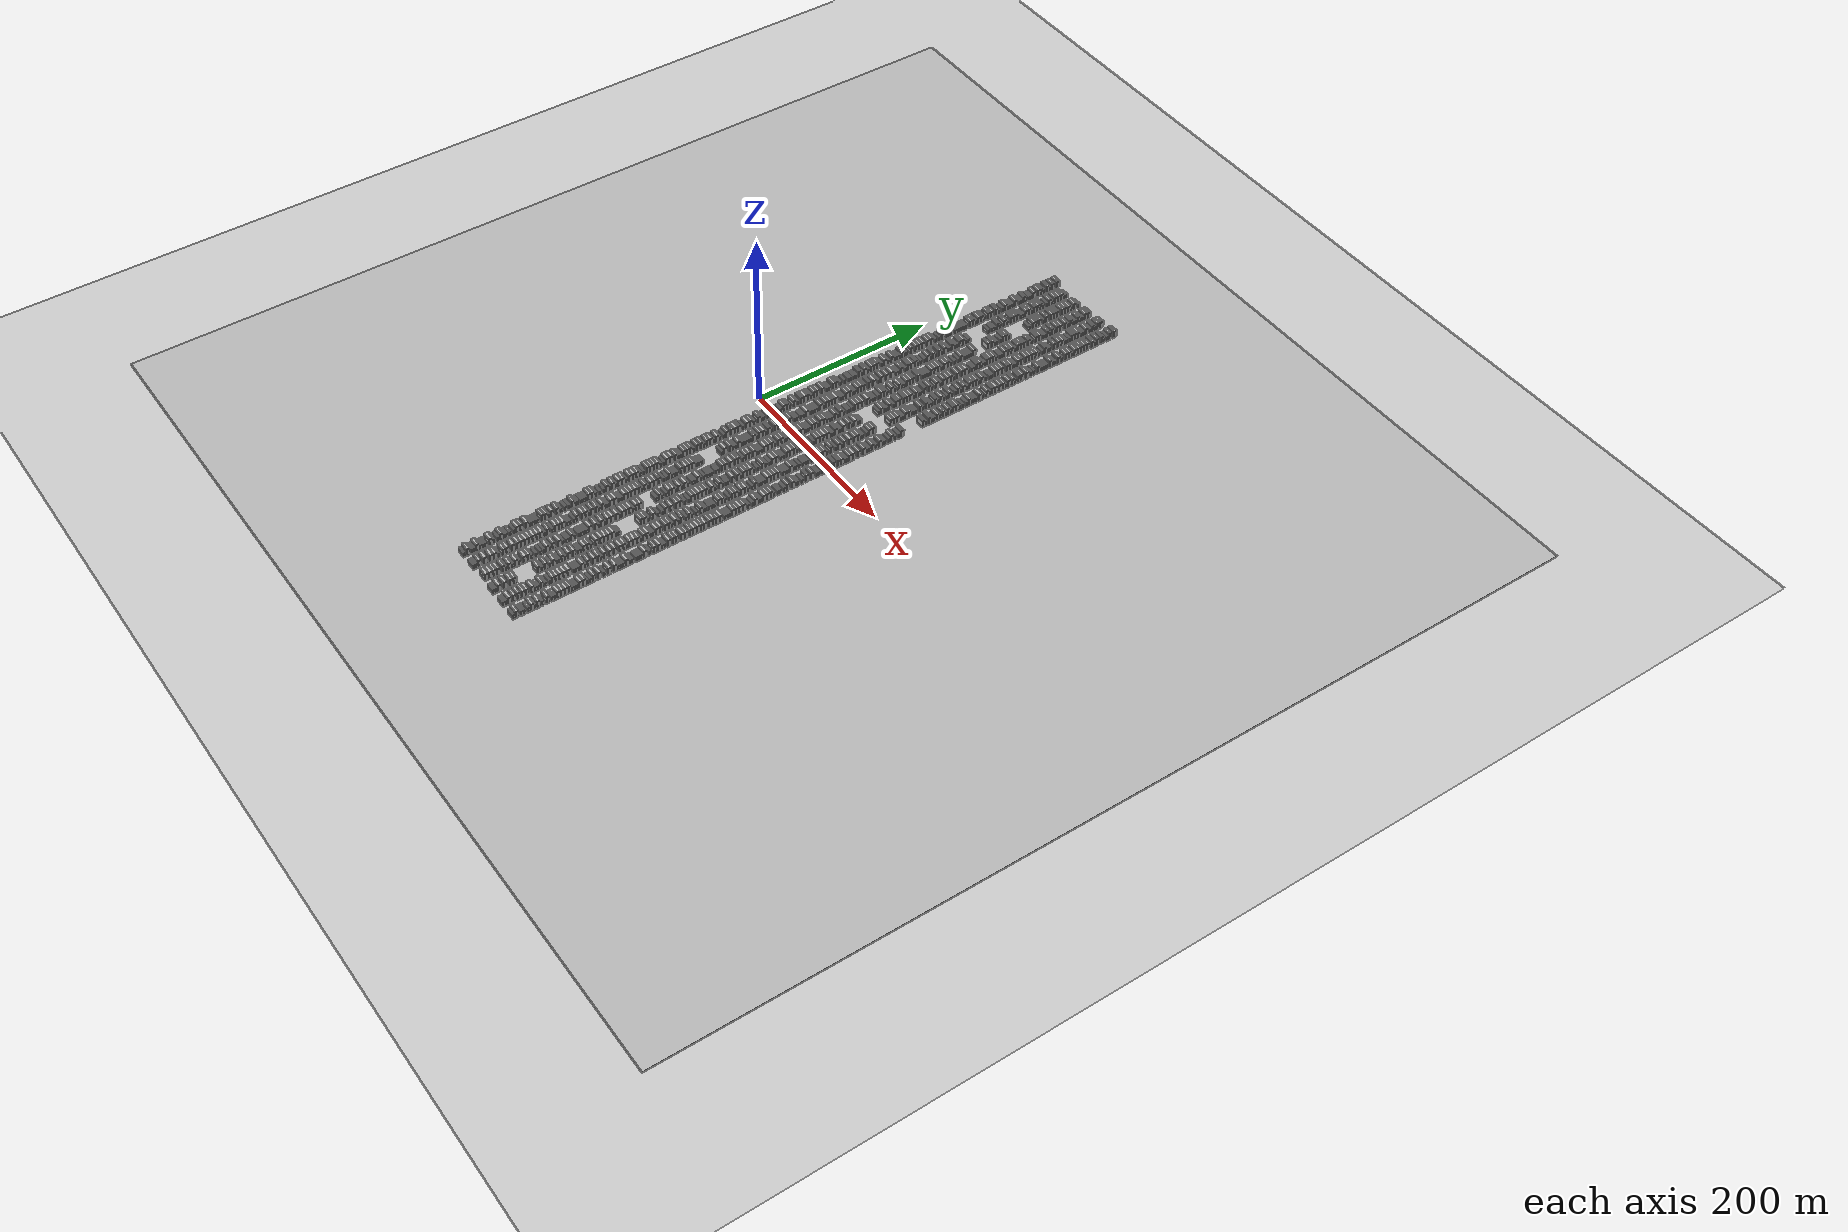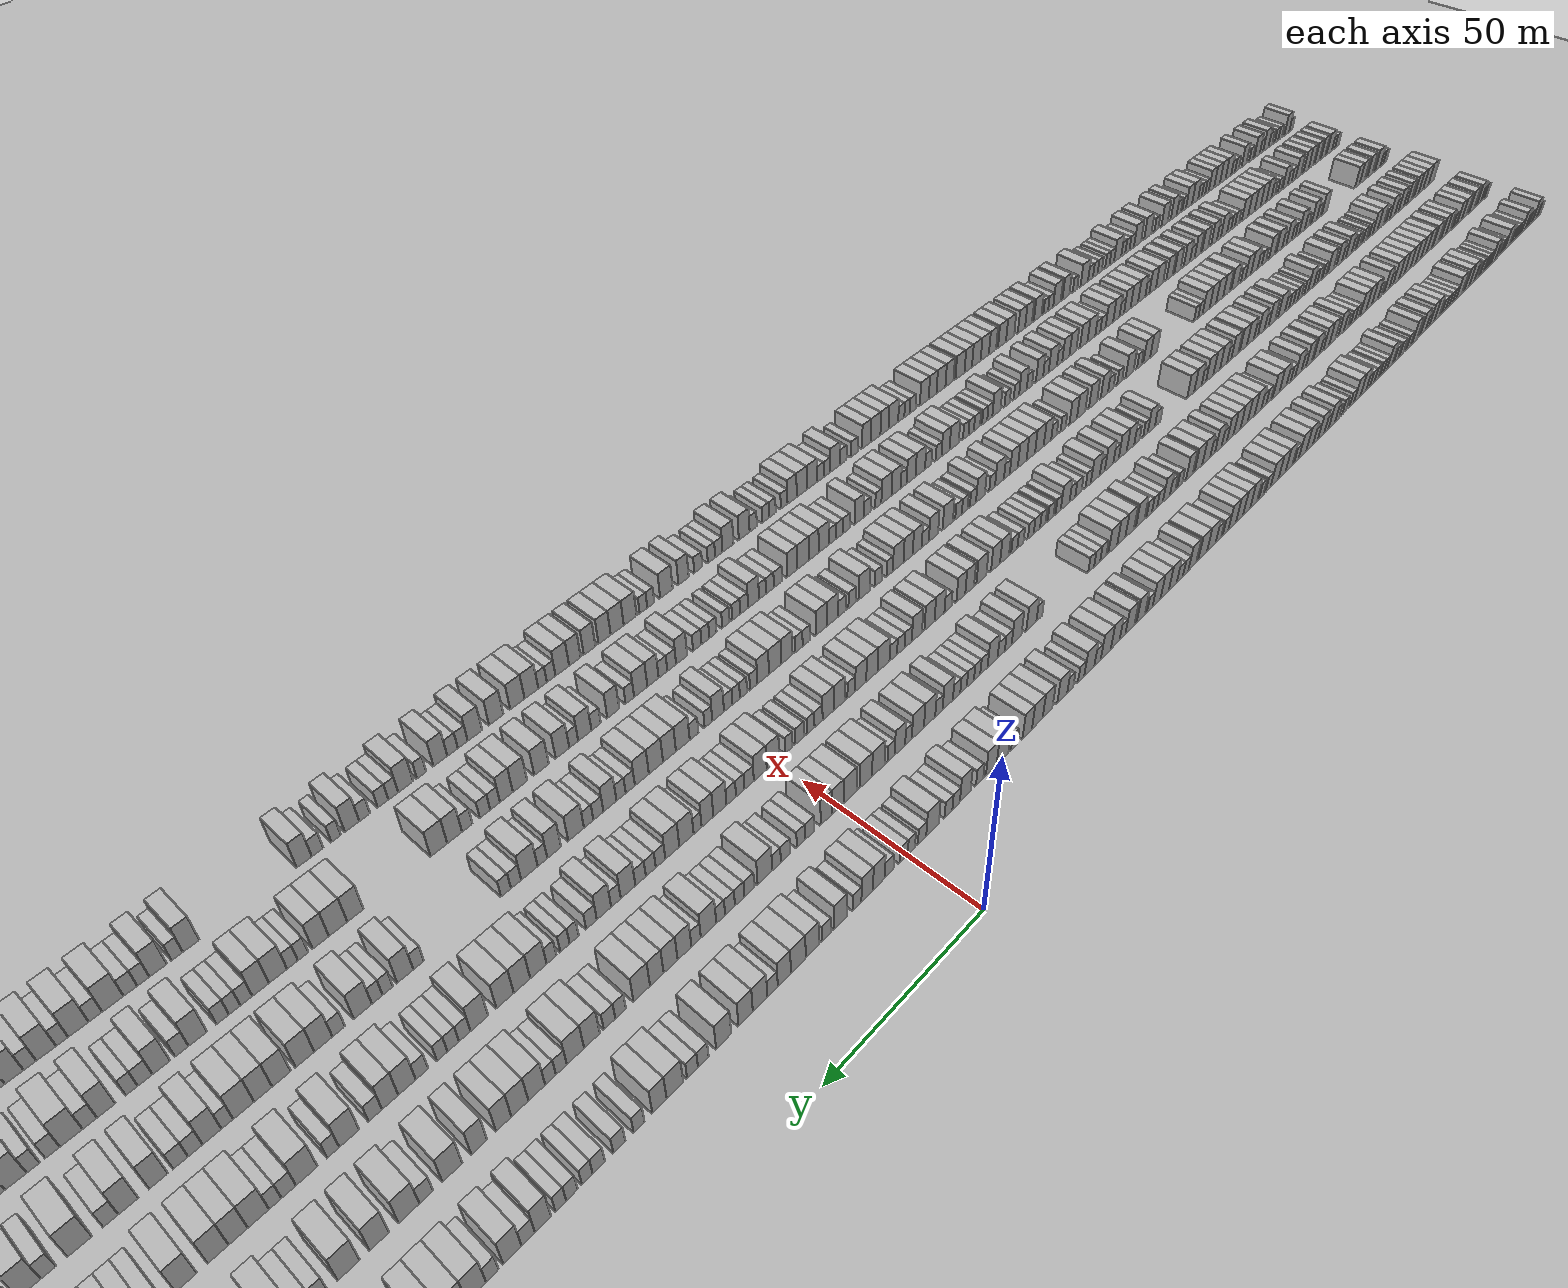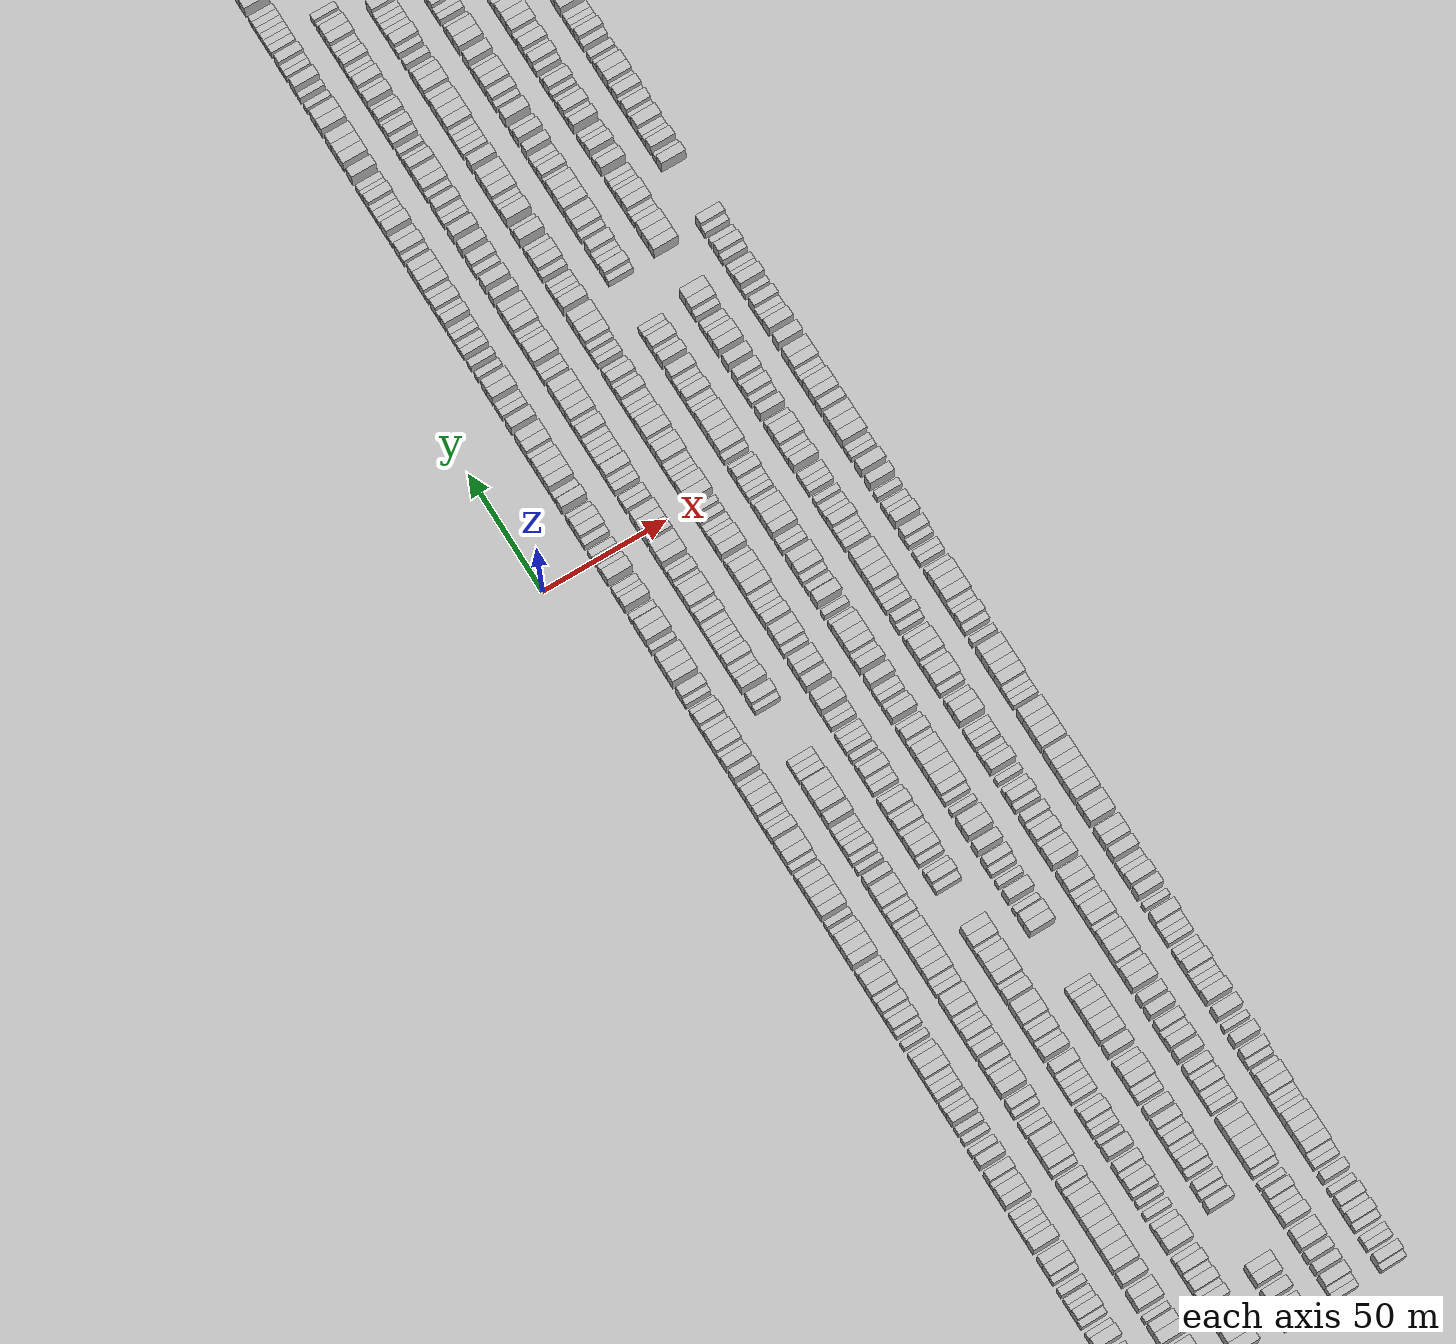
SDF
<?xml version="1.0" encoding="utf-8"?>

<sdf version="1.6">

   <world name="default">

      <gui fullscreen="0">

         <camera name="user_camera">

            <pose>-15 0 4.57585 0 0 0</pose>

            <view_controller>orbit</view_controller>

         </camera>

      </gui>

      <scene>

         <sky>

           <clouds>

             <speed>12</speed>

           </clouds>

         </sky>

         <ambient>0.4 0.4 0.4 1</ambient>

         <background>0.7 0.7 0.7 1</background>

         <shadows>1</shadows>

      </scene>

      <gravity>0 0 -9.8066</gravity>

      <magnetic_field>6e-06 2.3e-05 -4.2e-05</magnetic_field>

      <physics default="0" name="default_physics" type="ode">

         <ode>

            <solver>

               <type>quick</type>

               <iters>10</iters>

               <sor>1.0</sor>

               <use_dynamic_moi_rescaling>0</use_dynamic_moi_rescaling>

            </solver>

            <constraints>

               <cfm>0</cfm>

               <erp>0.2</erp>

               <contact_max_correcting_vel>100</contact_max_correcting_vel>

               <contact_surface_layer>0.001</contact_surface_layer>

            </constraints>

         </ode>

         <max_step_size>0.004</max_step_size>

         <real_time_factor>1</real_time_factor>

         <real_time_update_rate>250</real_time_update_rate>

      </physics>

      <light name="sun" type="directional">

         <cast_shadows>1</cast_shadows>

         <pose>0 0 10 0 0 0</pose>

         <diffuse>0.8 0.8 0.8 1</diffuse>

         <specular>0.2 0.2 0.2 1</specular>

         <attenuation>

            <range>1000</range>

            <constant>0.9</constant>

            <linear>0.01</linear>

            <quadratic>0.001</quadratic>

         </attenuation>

         <direction>-0.5 0.1 -0.9</direction>

      </light>

      <include>

         <name>ground_plane_1</name>

         <uri>model://HANNAS_ground_plane</uri>

         <pose>0 0 0  0 0 0</pose>

      </include>

      <include>

         <name>ground_plane_2</name>

         <uri>model://HANNAS_ground_plane</uri>

         <pose>100 0 0  0 0 0</pose>

      </include>

      <model name="building_1">

         <static>1</static>

         <pose frame="">25.0000 -348.6627 0 0.000000 0.000000 0.000000</pose>

         <link name="link">

            <pose frame="">0 0 3.00 0 0 0</pose>

            <collision name="collision">

               <geometry>

                  <box>

                     <size>10.0000 2.6746 6.0000</size>

                  </box>

               </geometry>

               <max_contacts>10</max_contacts>

               <surface>

                  <contact>

                     <ode/>

                  </contact>

                  <bounce/>

                  <friction>

                     <torsional>

                        <ode/>

                     </torsional>

                     <ode/>

                  </friction>

               </surface>

            </collision>

            <visual name="visual">

               <cast_shadows>0</cast_shadows>

               <geometry>

                  <box>

                     <size>10.0000 2.6746 6.0000</size>

                  </box>

               </geometry>

               <material>

                  <script>

                     <uri>model://HANNAS_wall/materials/scripts</uri>

                     <uri>model://HANNAS_wall/materials/textures</uri>

                     <name>vrc/HANNAS_wall</name>

                  </script>

               </material>

            </visual>

            <self_collide>0</self_collide>

            <enable_wind>0</enable_wind>

            <kinematic>0</kinematic>

         </link>

      </model>

      <model name="building_2">

         <static>1</static>

         <pose frame="">25.0000 -344.5249 0 0.000000 0.000000 0.000000</pose>

         <link name="link">

            <pose frame="">0 0 4.50 0 0 0</pose>

            <collision name="collision">

               <geometry>

                  <box>

                     <size>10.0000 3.6009 9.0000</size>

                  </box>

               </geometry>

               <max_contacts>10</max_contacts>

               <surface>

                  <contact>

                     <ode/>

                  </contact>

                  <bounce/>

                  <friction>

                     <torsional>

                        <ode/>

                     </torsional>

                     <ode/>

                  </friction>

               </surface>

            </collision>

            <visual name="visual">

               <cast_shadows>0</cast_shadows>

               <geometry>

                  <box>

                     <size>10.0000 3.6009 9.0000</size>

                  </box>

               </geometry>

               <material>

                  <script>

                     <uri>model://HANNAS_wall/materials/scripts</uri>

                     <uri>model://HANNAS_wall/materials/textures</uri>

                     <name>vrc/HANNAS_wall</name>

                  </script>

               </material>

            </visual>

            <self_collide>0</self_collide>

            <enable_wind>0</enable_wind>

            <kinematic>0</kinematic>

         </link>

      </model>

      <model name="building_3">

         <static>1</static>

         <pose frame="">25.0000 -340.4151 0 0.000000 0.000000 0.000000</pose>

         <link name="link">

            <pose frame="">0 0 3.00 0 0 0</pose>

            <collision name="collision">

               <geometry>

                  <box>

                     <size>10.0000 2.6188 6.0000</size>

                  </box>

               </geometry>

               <max_contacts>10</max_contacts>

               <surface>

                  <contact>

                     <ode/>

                  </contact>

                  <bounce/>

                  <friction>

                     <torsional>

                        <ode/>

                     </torsional>

                     <ode/>

                  </friction>

               </surface>

            </collision>

            <visual name="visual">

               <cast_shadows>0</cast_shadows>

               <geometry>

                  <box>

                     <size>10.0000 2.6188 6.0000</size>

                  </box>

               </geometry>

               <material>

                  <script>

                     <uri>model://HANNAS_wall/materials/scripts</uri>

                     <uri>model://HANNAS_wall/materials/textures</uri>

                     <name>vrc/HANNAS_wall</name>

                  </script>

               </material>

            </visual>

            <self_collide>0</self_collide>

            <enable_wind>0</enable_wind>

            <kinematic>0</kinematic>

         </link>

      </model>

      <model name="building_4">

         <static>1</static>

         <pose frame="">25.0000 -337.8743 0 0.000000 0.000000 0.000000</pose>

         <link name="link">

            <pose frame="">0 0 3.00 0 0 0</pose>

            <collision name="collision">

               <geometry>

                  <box>

                     <size>10.0000 2.4629 6.0000</size>

                  </box>

               </geometry>

               <max_contacts>10</max_contacts>

               <surface>

                  <contact>

                     <ode/>

                  </contact>

                  <bounce/>

                  <friction>

                     <torsional>

                        <ode/>

                     </torsional>

                     <ode/>

                  </friction>

               </surface>

            </collision>

            <visual name="visual">

               <cast_shadows>0</cast_shadows>

               <geometry>

                  <box>

                     <size>10.0000 2.4629 6.0000</size>

                  </box>

               </geometry>

               <material>

                  <script>

                     <uri>model://HANNAS_wall/materials/scripts</uri>

                     <uri>model://HANNAS_wall/materials/textures</uri>

                     <name>vrc/HANNAS_wall</name>

                  </script>

               </material>

            </visual>

            <self_collide>0</self_collide>

            <enable_wind>0</enable_wind>

            <kinematic>0</kinematic>

         </link>

      </model>

      <model name="building_5">

         <static>1</static>

         <pose frame="">25.0000 -334.7237 0 0.000000 0.000000 0.000000</pose>

         <link name="link">

            <pose frame="">0 0 4.50 0 0 0</pose>

            <collision name="collision">

               <geometry>

                  <box>

                     <size>10.0000 3.8383 9.0000</size>

                  </box>

               </geometry>

               <max_contacts>10</max_contacts>

               <surface>

                  <contact>

                     <ode/>

                  </contact>

                  <bounce/>

                  <friction>

                     <torsional>

                        <ode/>

                     </torsional>

                     <ode/>

                  </friction>

               </surface>

            </collision>

            <visual name="visual">

               <cast_shadows>0</cast_shadows>

               <geometry>

                  <box>

                     <size>10.0000 3.8383 9.0000</size>

                  </box>

               </geometry>

               <material>

                  <script>

                     <uri>model://HANNAS_wall/materials/scripts</uri>

                     <uri>model://HANNAS_wall/materials/textures</uri>

                     <name>vrc/HANNAS_wall</name>

                  </script>

               </material>

            </visual>

            <self_collide>0</self_collide>

            <enable_wind>0</enable_wind>

            <kinematic>0</kinematic>

         </link>

      </model>

      <model name="building_6">

         <static>1</static>

         <pose frame="">25.0000 -331.3662 0 0.000000 0.000000 0.000000</pose>

         <link name="link">

            <pose frame="">0 0 3.00 0 0 0</pose>

            <collision name="collision">

               <geometry>

                  <box>

                     <size>10.0000 2.8765 6.0000</size>

                  </box>

               </geometry>

               <max_contacts>10</max_contacts>

               <surface>

                  <contact>

                     <ode/>

                  </contact>

                  <bounce/>

                  <friction>

                     <torsional>

                        <ode/>

                     </torsional>

                     <ode/>

                  </friction>

               </surface>

            </collision>

            <visual name="visual">

               <cast_shadows>0</cast_shadows>

               <geometry>

                  <box>

                     <size>10.0000 2.8765 6.0000</size>

                  </box>

               </geometry>

               <material>

                  <script>

                     <uri>model://HANNAS_wall/materials/scripts</uri>

                     <uri>model://HANNAS_wall/materials/textures</uri>

                     <name>vrc/HANNAS_wall</name>

                  </script>

               </material>

            </visual>

            <self_collide>0</self_collide>

            <enable_wind>0</enable_wind>

            <kinematic>0</kinematic>

         </link>

      </model>

      <model name="building_7">

         <static>1</static>

         <pose frame="">25.0000 -328.7133 0 0.000000 0.000000 0.000000</pose>

         <link name="link">

            <pose frame="">0 0 3.00 0 0 0</pose>

            <collision name="collision">

               <geometry>

                  <box>

                     <size>10.0000 2.4293 6.0000</size>

                  </box>

               </geometry>

               <max_contacts>10</max_contacts>

               <surface>

                  <contact>

                     <ode/>

                  </contact>

                  <bounce/>

                  <friction>

                     <torsional>

                        <ode/>

                     </torsional>

                     <ode/>

                  </friction>

               </surface>

            </collision>

            <visual name="visual">

               <cast_shadows>0</cast_shadows>

               <geometry>

                  <box>

                     <size>10.0000 2.4293 6.0000</size>

                  </box>

               </geometry>

               <material>

                  <script>

                     <uri>model://HANNAS_wall/materials/scripts</uri>

                     <uri>model://HANNAS_wall/materials/textures</uri>

                     <name>vrc/HANNAS_wall</name>

                  </script>

               </material>

            </visual>

            <self_collide>0</self_collide>

            <enable_wind>0</enable_wind>

            <kinematic>0</kinematic>

         </link>

      </model>

      <model name="building_8">

         <static>1</static>

         <pose frame="">25.0000 -326.0692 0 0.000000 0.000000 0.000000</pose>

         <link name="link">

            <pose frame="">0 0 3.00 0 0 0</pose>

            <collision name="collision">

               <geometry>

                  <box>

                     <size>10.0000 2.8588 6.0000</size>

                  </box>

               </geometry>

               <max_contacts>10</max_contacts>

               <surface>

                  <contact>

                     <ode/>

                  </contact>

                  <bounce/>

                  <friction>

                     <torsional>

                        <ode/>

                     </torsional>

                     <ode/>

                  </friction>

               </surface>

            </collision>

            <visual name="visual">

               <cast_shadows>0</cast_shadows>

               <geometry>

                  <box>

                     <size>10.0000 2.8588 6.0000</size>

                  </box>

               </geometry>

               <material>

                  <script>

                     <uri>model://HANNAS_wall/materials/scripts</uri>

                     <uri>model://HANNAS_wall/materials/textures</uri>

                     <name>vrc/HANNAS_wall</name>

                  </script>

               </material>

            </visual>

            <self_collide>0</self_collide>

            <enable_wind>0</enable_wind>

            <kinematic>0</kinematic>

         </link>

      </model>

      <model name="building_9">

         <static>1</static>

         <pose frame="">25.0000 -320.4732 0 0.000000 0.000000 0.000000</pose>

         <link name="link">

            <pose frame="">0 0 4.50 0 0 0</pose>

            <collision name="collision">

               <geometry>

                  <box>

                     <size>10.0000 4.3331 9.0000</size>

                  </box>

               </geometry>

               <max_contacts>10</max_contacts>

               <surface>

                  <contact>

                     <ode/>

                  </contact>

                  <bounce/>

                  <friction>

                     <torsional>

                        <ode/>

                     </torsional>

                     <ode/>

                  </friction>

               </surface>

            </collision>

            <visual name="visual">

               <cast_shadows>0</cast_shadows>

               <geometry>

                  <box>

                     <size>10.0000 4.3331 9.0000</size>

                  </box>

               </geometry>

               <material>

                  <script>

                     <uri>model://HANNAS_wall/materials/scripts</uri>

                     <uri>model://HANNAS_wall/materials/textures</uri>

                     <name>vrc/HANNAS_wall</name>

                  </script>

               </material>

            </visual>

            <self_collide>0</self_collide>

            <enable_wind>0</enable_wind>

            <kinematic>0</kinematic>

         </link>

      </model>

      <model name="building_10">

         <static>1</static>

         <pose frame="">25.0000 -317.0004 0 0.000000 0.000000 0.000000</pose>

         <link name="link">

            <pose frame="">0 0 3.00 0 0 0</pose>

            <collision name="collision">

               <geometry>

                  <box>

                     <size>10.0000 2.6125 6.0000</size>

                  </box>

               </geometry>

               <max_contacts>10</max_contacts>

               <surface>

                  <contact>

                     <ode/>

                  </contact>

                  <bounce/>

                  <friction>

                     <torsional>

                        <ode/>

                     </torsional>

                     <ode/>

                  </friction>

               </surface>

            </collision>

            <visual name="visual">

               <cast_shadows>0</cast_shadows>

               <geometry>

                  <box>

                     <size>10.0000 2.6125 6.0000</size>

                  </box>

               </geometry>

               <material>

                  <script>

                     <uri>model://HANNAS_wall/materials/scripts</uri>

                     <uri>model://HANNAS_wall/materials/textures</uri>

                     <name>vrc/HANNAS_wall</name>

                  </script>

               </material>

            </visual>

            <self_collide>0</self_collide>

            <enable_wind>0</enable_wind>

            <kinematic>0</kinematic>

         </link>

      </model>

      <model name="building_11">

         <static>1</static>

         <pose frame="">25.0000 -312.4064 0 0.000000 0.000000 0.000000</pose>

         <link name="link">

            <pose frame="">0 0 3.00 0 0 0</pose>

            <collision name="collision">

               <geometry>

                  <box>

                     <size>10.0000 2.5755 6.0000</size>

                  </box>

               </geometry>

               <max_contacts>10</max_contacts>

               <surface>

                  <contact>

                     <ode/>

                  </contact>

                  <bounce/>

                  <friction>

                     <torsional>

                        <ode/>

                     </torsional>

                     <ode/>

                  </friction>

               </surface>

            </collision>

            <visual name="visual">

               <cast_shadows>0</cast_shadows>

               <geometry>

                  <box>

                     <size>10.0000 2.5755 6.0000</size>

                  </box>

               </geometry>

               <material>

                  <script>

                     <uri>model://HANNAS_wall/materials/scripts</uri>

                     <uri>model://HANNAS_wall/materials/textures</uri>

                     <name>vrc/HANNAS_wall</name>

                  </script>

               </material>

            </visual>

            <self_collide>0</self_collide>

            <enable_wind>0</enable_wind>

            <kinematic>0</kinematic>

         </link>

      </model>

      <model name="building_12">

         <static>1</static>

         <pose frame="">25.0000 -309.1953 0 0.000000 0.000000 0.000000</pose>

         <link name="link">

            <pose frame="">0 0 4.50 0 0 0</pose>

            <collision name="collision">

               <geometry>

                  <box>

                     <size>10.0000 3.8468 9.0000</size>

                  </box>

               </geometry>

               <max_contacts>10</max_contacts>

               <surface>

                  <contact>

                     <ode/>

                  </contact>

                  <bounce/>

                  <friction>

                     <torsional>

                        <ode/>

                     </torsional>

                     <ode/>

                  </friction>

               </surface>

            </collision>

            <visual name="visual">

               <cast_shadows>0</cast_shadows>

               <geometry>

                  <box>

                     <size>10.0000 3.8468 9.0000</size>

                  </box>

               </geometry>

               <material>

                  <script>

                     <uri>model://HANNAS_wall/materials/scripts</uri>

                     <uri>model://HANNAS_wall/materials/textures</uri>

                     <name>vrc/HANNAS_wall</name>

                  </script>

               </material>

            </visual>

            <self_collide>0</self_collide>

            <enable_wind>0</enable_wind>

            <kinematic>0</kinematic>

         </link>

      </model>

      <model name="building_13">

         <static>1</static>

         <pose frame="">25.0000 -306.0507 0 0.000000 0.000000 0.000000</pose>

         <link name="link">

            <pose frame="">0 0 3.00 0 0 0</pose>

            <collision name="collision">

               <geometry>

                  <box>

                     <size>10.0000 2.4424 6.0000</size>

                  </box>

               </geometry>

               <max_contacts>10</max_contacts>

               <surface>

                  <contact>

                     <ode/>

                  </contact>

                  <bounce/>

                  <friction>

                     <torsional>

                        <ode/>

                     </torsional>

                     <ode/>

                  </friction>

               </surface>

            </collision>

            <visual name="visual">

               <cast_shadows>0</cast_shadows>

               <geometry>

                  <box>

                     <size>10.0000 2.4424 6.0000</size>

                  </box>

               </geometry>

               <material>

                  <script>

                     <uri>model://HANNAS_wall/materials/scripts</uri>

                     <uri>model://HANNAS_wall/materials/textures</uri>

                     <name>vrc/HANNAS_wall</name>

                  </script>

               </material>

            </visual>

            <self_collide>0</self_collide>

            <enable_wind>0</enable_wind>

            <kinematic>0</kinematic>

         </link>

      </model>

      <model name="building_14">

         <static>1</static>

         <pose frame="">25.0000 -303.5327 0 0.000000 0.000000 0.000000</pose>

         <link name="link">

            <pose frame="">0 0 3.00 0 0 0</pose>

            <collision name="collision">

               <geometry>

                  <box>

                     <size>10.0000 2.5937 6.0000</size>

                  </box>

               </geometry>

               <max_contacts>10</max_contacts>

               <surface>

                  <contact>

                     <ode/>

                  </contact>

                  <bounce/>

                  <friction>

                     <torsional>

                        <ode/>

                     </torsional>

                     <ode/>

                  </friction>

               </surface>

            </collision>

            <visual name="visual">

               <cast_shadows>0</cast_shadows>

               <geometry>

                  <box>

                     <size>10.0000 2.5937 6.0000</size>

                  </box>

               </geometry>

               <material>

                  <script>

                     <uri>model://HANNAS_wall/materials/scripts</uri>

                     <uri>model://HANNAS_wall/materials/textures</uri>

                     <name>vrc/HANNAS_wall</name>

                  </script>

               </material>

            </visual>

            <self_collide>0</self_collide>

            <enable_wind>0</enable_wind>

            <kinematic>0</kinematic>

         </link>

      </model>

      <model name="building_15">

         <static>1</static>

         <pose frame="">25.0000 -299.7746 0 0.000000 0.000000 0.000000</pose>

         <link name="link">

            <pose frame="">0 0 3.00 0 0 0</pose>

            <collision name="collision">

               <geometry>

                  <box>

                     <size>10.0000 2.9224 6.0000</size>

                  </box>

               </geometry>

               <max_contacts>10</max_contacts>

               <surface>

                  <contact>

                     <ode/>

                  </contact>

                  <bounce/>

                  <friction>

                     <torsional>

                        <ode/>

                     </torsional>

                     <ode/>

                  </friction>

               </surface>

            </collision>

            <visual name="visual">

               <cast_shadows>0</cast_shadows>

               <geometry>

                  <box>

                     <size>10.0000 2.9224 6.0000</size>

                  </box>

               </geometry>

               <material>

                  <script>

                     <uri>model://HANNAS_wall/materials/scripts</uri>

                     <uri>model://HANNAS_wall/materials/textures</uri>

                     <name>vrc/HANNAS_wall</name>

                  </script>

               </material>

            </visual>

            <self_collide>0</self_collide>

            <enable_wind>0</enable_wind>

            <kinematic>0</kinematic>

         </link>

      </model>

      <model name="building_16">

         <static>1</static>

         <pose frame="">25.0000 -295.1014 0 0.000000 0.000000 0.000000</pose>

         <link name="link">

            <pose frame="">0 0 3.00 0 0 0</pose>

            <collision name="collision">

               <geometry>

                  <box>

                     <size>10.0000 2.4240 6.0000</size>

                  </box>

               </geometry>

               <max_contacts>10</max_contacts>

               <surface>

                  <contact>

                     <ode/>

                  </contact>

                  <bounce/>

                  <friction>

                     <torsional>

                        <ode/>

                     </torsional>

                     <ode/>

                  </friction>

               </surface>

            </collision>

            <visual name="visual">

               <cast_shadows>0</cast_shadows>

               <geometry>

                  <box>

                     <size>10.0000 2.4240 6.0000</size>

                  </box>

               </geometry>

               <material>

                  <script>

                     <uri>model://HANNAS_wall/materials/scripts</uri>

                     <uri>model://HANNAS_wall/materials/textures</uri>

                     <name>vrc/HANNAS_wall</name>

                  </script>

               </material>

            </visual>

            <self_collide>0</self_collide>

            <enable_wind>0</enable_wind>

            <kinematic>0</kinematic>

         </link>

      </model>

      <model name="building_17">

         <static>1</static>

         <pose frame="">25.0000 -291.7622 0 0.000000 0.000000 0.000000</pose>

         <link name="link">

            <pose frame="">0 0 4.50 0 0 0</pose>

            <collision name="collision">

               <geometry>

                  <box>

                     <size>10.0000 4.2544 9.0000</size>

                  </box>

               </geometry>

               <max_contacts>10</max_contacts>

               <surface>

                  <contact>

                     <ode/>

                  </contact>

                  <bounce/>

                  <friction>

                     <torsional>

                        <ode/>

                     </torsional>

                     <ode/>

                  </friction>

               </surface>

            </collision>

            <visual name="visual">

               <cast_shadows>0</cast_shadows>

               <geometry>

                  <box>

                     <size>10.0000 4.2544 9.0000</size>

                  </box>

               </geometry>

               <material>

                  <script>

                     <uri>model://HANNAS_wall/materials/scripts</uri>

                     <uri>model://HANNAS_wall/materials/textures</uri>

                     <name>vrc/HANNAS_wall</name>

                  </script>

               </material>

            </visual>

            <self_collide>0</self_collide>

            <enable_wind>0</enable_wind>

            <kinematic>0</kinematic>

         </link>

      </model>

      <model name="building_18">

         <static>1</static>

         <pose frame="">25.0000 -287.7833 0 0.000000 0.000000 0.000000</pose>

         <link name="link">

            <pose frame="">0 0 4.50 0 0 0</pose>

            <collision name="collision">

               <geometry>

                  <box>

                     <size>10.0000 3.7033 9.0000</size>

                  </box>

               </geometry>

               <max_contacts>10</max_contacts>

               <surface>

                  <contact>

                     <ode/>

                  </contact>

                  <bounce/>

                  <friction>

                     <torsional>

                        <ode/>

                     </torsional>

                     <ode/>

                  </friction>

               </surface>

            </collision>

            <visual name="visual">

               <cast_shadows>0</cast_shadows>

               <geometry>

                  <box>

                     <size>10.0000 3.7033 9.0000</size>

                  </box>

               </geometry>

               <material>

                  <script>

                     <uri>model://HANNAS_wall/materials/scripts</uri>

                     <uri>model://HANNAS_wall/materials/textures</uri>

                     <name>vrc/HANNAS_wall</name>

                  </script>

               </material>

            </visual>

            <self_collide>0</self_collide>

            <enable_wind>0</enable_wind>

            <kinematic>0</kinematic>

         </link>

      </model>

      <model name="building_19">

         <static>1</static>

         <pose frame="">25.0000 -281.7414 0 0.000000 0.000000 0.000000</pose>

         <link name="link">

            <pose frame="">0 0 4.50 0 0 0</pose>

            <collision name="collision">

               <geometry>

                  <box>

                     <size>10.0000 4.3806 9.0000</size>

                  </box>

               </geometry>

               <max_contacts>10</max_contacts>

               <surface>

                  <contact>

                     <ode/>

                  </contact>

                  <bounce/>

                  <friction>

                     <torsional>

                        <ode/>

                     </torsional>

                     <ode/>

                  </friction>

               </surface>

            </collision>

            <visual name="visual">

               <cast_shadows>0</cast_shadows>

               <geometry>

                  <box>

                     <size>10.0000 4.3806 9.0000</size>

                  </box>

               </geometry>

               <material>

                  <script>

                     <uri>model://HANNAS_wall/materials/scripts</uri>

                     <uri>model://HANNAS_wall/materials/textures</uri>

                     <name>vrc/HANNAS_wall</name>

                  </script>

               </material>

            </visual>

            <self_collide>0</self_collide>

            <enable_wind>0</enable_wind>

            <kinematic>0</kinematic>

         </link>

      </model>

      <model name="building_20">

         <static>1</static>

         <pose frame="">25.0000 -278.2436 0 0.000000 0.000000 0.000000</pose>

         <link name="link">

            <pose frame="">0 0 3.00 0 0 0</pose>

            <collision name="collision">

               <geometry>

                  <box>

                     <size>10.0000 2.6150 6.0000</size>

                  </box>

               </geometry>

               <max_contacts>10</max_contacts>

               <surface>

                  <contact>

                     <ode/>

                  </contact>

                  <bounce/>

                  <friction>

                     <torsional>

                        <ode/>

                     </torsional>

                     <ode/>

                  </friction>

               </surface>

            </collision>

            <visual name="visual">

               <cast_shadows>0</cast_shadows>

               <geometry>

                  <box>

                     <size>10.0000 2.6150 6.0000</size>

                  </box>

               </geometry>

               <material>

                  <script>

                     <uri>model://HANNAS_wall/materials/scripts</uri>

                     <uri>model://HANNAS_wall/materials/textures</uri>

                     <name>vrc/HANNAS_wall</name>

                  </script>

               </material>

            </visual>

            <self_collide>0</self_collide>

            <enable_wind>0</enable_wind>

            <kinematic>0</kinematic>

         </link>

      </model>

      <model name="building_21">

         <static>1</static>

         <pose frame="">25.0000 -275.6097 0 0.000000 0.000000 0.000000</pose>

         <link name="link">

            <pose frame="">0 0 3.00 0 0 0</pose>

            <collision name="collision">

               <geometry>

                  <box>

                     <size>10.0000 2.6527 6.0000</size>

                  </box>

               </geometry>

               <max_contacts>10</max_contacts>

               <surface>

                  <contact>

                     <ode/>

                  </contact>

                  <bounce/>

                  <friction>

                     <torsional>

                        <ode/>

                     </torsional>

                     <ode/>

                  </friction>

               </surface>

            </collision>

            <visual name="visual">

               <cast_shadows>0</cast_shadows>

               <geometry>

                  <box>

                     <size>10.0000 2.6527 6.0000</size>

                  </box>

               </geometry>

               <material>

                  <script>

                     <uri>model://HANNAS_wall/materials/scripts</uri>

                     <uri>model://HANNAS_wall/materials/textures</uri>

                     <name>vrc/HANNAS_wall</name>

                  </script>

               </material>

            </visual>

            <self_collide>0</self_collide>

            <enable_wind>0</enable_wind>

            <kinematic>0</kinematic>

         </link>

      </model>

      <model name="building_22">

         <static>1</static>

         <pose frame="">25.0000 -272.8170 0 0.000000 0.000000 0.000000</pose>

         <link name="link">

            <pose frame="">0 0 3.00 0 0 0</pose>

            <collision name="collision">

               <geometry>

                  <box>

                     <size>10.0000 2.9329 6.0000</size>

                  </box>

               </geometry>

               <max_contacts>10</max_contacts>

               <surface>

                  <contact>

                     <ode/>

                  </contact>

                  <bounce/>

                  <friction>

                     <torsional>

                        <ode/>

                     </torsional>

                     <ode/>

                  </friction>

               </surface>

            </collision>

            <visual name="visual">

               <cast_shadows>0</cast_shadows>

               <geometry>

                  <box>

                     <size>10.0000 2.9329 6.0000</size>

                  </box>

               </geometry>

               <material>

                  <script>

                     <uri>model://HANNAS_wall/materials/scripts</uri>

                     <uri>model://HANNAS_wall/materials/textures</uri>

                     <name>vrc/HANNAS_wall</name>

                  </script>

               </material>

            </visual>

            <self_collide>0</self_collide>

            <enable_wind>0</enable_wind>

            <kinematic>0</kinematic>

         </link>

      </model>

      <model name="building_23">

         <static>1</static>

         <pose frame="">25.0000 -269.9229 0 0.000000 0.000000 0.000000</pose>

         <link name="link">

            <pose frame="">0 0 3.00 0 0 0</pose>

            <collision name="collision">

               <geometry>

                  <box>

                     <size>10.0000 2.8552 6.0000</size>

                  </box>

               </geometry>

               <max_contacts>10</max_contacts>

               <surface>

                  <contact>

                     <ode/>

                  </contact>

                  <bounce/>

                  <friction>

                     <torsional>

                        <ode/>

                     </torsional>

                     <ode/>

                  </friction>

               </surface>

            </collision>

            <visual name="visual">

               <cast_shadows>0</cast_shadows>

               <geometry>

                  <box>

                     <size>10.0000 2.8552 6.0000</size>

                  </box>

               </geometry>

               <material>

                  <script>

                     <uri>model://HANNAS_wall/materials/scripts</uri>

                     <uri>model://HANNAS_wall/materials/textures</uri>

                     <name>vrc/HANNAS_wall</name>

                  </script>

               </material>

            </visual>

            <self_collide>0</self_collide>

            <enable_wind>0</enable_wind>

            <kinematic>0</kinematic>

         </link>

      </model>

      <model name="building_24">

         <static>1</static>

         <pose frame="">25.0000 -264.6804 0 0.000000 0.000000 0.000000</pose>

         <link name="link">

            <pose frame="">0 0 4.50 0 0 0</pose>

            <collision name="collision">

               <geometry>

                  <box>

                     <size>10.0000 3.6300 9.0000</size>

                  </box>

               </geometry>

               <max_contacts>10</max_contacts>

               <surface>

                  <contact>

                     <ode/>

                  </contact>

                  <bounce/>

                  <friction>

                     <torsional>

                        <ode/>

                     </torsional>

                     <ode/>

                  </friction>

               </surface>

            </collision>

            <visual name="visual">

               <cast_shadows>0</cast_shadows>

               <geometry>

                  <box>

                     <size>10.0000 3.6300 9.0000</size>

                  </box>

               </geometry>

               <material>

                  <script>

                     <uri>model://HANNAS_wall/materials/scripts</uri>

                     <uri>model://HANNAS_wall/materials/textures</uri>

                     <name>vrc/HANNAS_wall</name>

                  </script>

               </material>

            </visual>

            <self_collide>0</self_collide>

            <enable_wind>0</enable_wind>

            <kinematic>0</kinematic>

         </link>

      </model>

      <model name="building_25">

         <static>1</static>

         <pose frame="">25.0000 -260.9767 0 0.000000 0.000000 0.000000</pose>

         <link name="link">

            <pose frame="">0 0 4.50 0 0 0</pose>

            <collision name="collision">

               <geometry>

                  <box>

                     <size>10.0000 3.7774 9.0000</size>

                  </box>

               </geometry>

               <max_contacts>10</max_contacts>

               <surface>

                  <contact>

                     <ode/>

                  </contact>

                  <bounce/>

                  <friction>

                     <torsional>

                        <ode/>

                     </torsional>

                     <ode/>

                  </friction>

               </surface>

            </collision>

            <visual name="visual">

               <cast_shadows>0</cast_shadows>

               <geometry>

                  <box>

                     <size>10.0000 3.7774 9.0000</size>

                  </box>

               </geometry>

               <material>

                  <script>

                     <uri>model://HANNAS_wall/materials/scripts</uri>

                     <uri>model://HANNAS_wall/materials/textures</uri>

                     <name>vrc/HANNAS_wall</name>

                  </script>

               </material>

            </visual>

            <self_collide>0</self_collide>

            <enable_wind>0</enable_wind>

            <kinematic>0</kinematic>

         </link>

      </model>

      <model name="building_26">

         <static>1</static>

         <pose frame="">25.0000 -257.8178 0 0.000000 0.000000 0.000000</pose>

         <link name="link">

            <pose frame="">0 0 3.00 0 0 0</pose>

            <collision name="collision">

               <geometry>

                  <box>

                     <size>10.0000 2.5404 6.0000</size>

                  </box>

               </geometry>

               <max_contacts>10</max_contacts>

               <surface>

                  <contact>

                     <ode/>

                  </contact>

                  <bounce/>

                  <friction>

                     <torsional>

                        <ode/>

                     </torsional>

                     <ode/>

                  </friction>

               </surface>

            </collision>

            <visual name="visual">

               <cast_shadows>0</cast_shadows>

               <geometry>

                  <box>

                     <size>10.0000 2.5404 6.0000</size>

                  </box>

               </geometry>

               <material>

                  <script>

                     <uri>model://HANNAS_wall/materials/scripts</uri>

                     <uri>model://HANNAS_wall/materials/textures</uri>

                     <name>vrc/HANNAS_wall</name>

                  </script>

               </material>

            </visual>

            <self_collide>0</self_collide>

            <enable_wind>0</enable_wind>

            <kinematic>0</kinematic>

         </link>

      </model>

      <model name="building_27">

         <static>1</static>

         <pose frame="">25.0000 -254.5381 0 0.000000 0.000000 0.000000</pose>

         <link name="link">

            <pose frame="">0 0 4.50 0 0 0</pose>

            <collision name="collision">

               <geometry>

                  <box>

                     <size>10.0000 4.0191 9.0000</size>

                  </box>

               </geometry>

               <max_contacts>10</max_contacts>

               <surface>

                  <contact>

                     <ode/>

                  </contact>

                  <bounce/>

                  <friction>

                     <torsional>

                        <ode/>

                     </torsional>

                     <ode/>

                  </friction>

               </surface>

            </collision>

            <visual name="visual">

               <cast_shadows>0</cast_shadows>

               <geometry>

                  <box>

                     <size>10.0000 4.0191 9.0000</size>

                  </box>

               </geometry>

               <material>

                  <script>

                     <uri>model://HANNAS_wall/materials/scripts</uri>

                     <uri>model://HANNAS_wall/materials/textures</uri>

                     <name>vrc/HANNAS_wall</name>

                  </script>

               </material>

            </visual>

            <self_collide>0</self_collide>

            <enable_wind>0</enable_wind>

            <kinematic>0</kinematic>

         </link>

      </model>

      <model name="building_28">

         <static>1</static>

         <pose frame="">25.0000 -248.6928 0 0.000000 0.000000 0.000000</pose>

         <link name="link">

            <pose frame="">0 0 4.50 0 0 0</pose>

            <collision name="collision">

               <geometry>

                  <box>

                     <size>10.0000 3.6715 9.0000</size>

                  </box>

               </geometry>

               <max_contacts>10</max_contacts>

               <surface>

                  <contact>

                     <ode/>

                  </contact>

                  <bounce/>

                  <friction>

                     <torsional>

                        <ode/>

                     </torsional>

                     <ode/>

                  </friction>

               </surface>

            </collision>

            <visual name="visual">

               <cast_shadows>0</cast_shadows>

               <geometry>

                  <box>

                     <size>10.0000 3.6715 9.0000</size>

                  </box>

               </geometry>

               <material>

                  <script>

                     <uri>model://HANNAS_wall/materials/scripts</uri>

                     <uri>model://HANNAS_wall/materials/textures</uri>

                     <name>vrc/HANNAS_wall</name>

                  </script>

               </material>

            </visual>

            <self_collide>0</self_collide>

            <enable_wind>0</enable_wind>

            <kinematic>0</kinematic>

         </link>

      </model>

      <model name="building_29">

         <static>1</static>

         <pose frame="">25.0000 -244.3878 0 0.000000 0.000000 0.000000</pose>

         <link name="link">

            <pose frame="">0 0 3.00 0 0 0</pose>

            <collision name="collision">

               <geometry>

                  <box>

                     <size>10.0000 2.9384 6.0000</size>

                  </box>

               </geometry>

               <max_contacts>10</max_contacts>

               <surface>

                  <contact>

                     <ode/>

                  </contact>

                  <bounce/>

                  <friction>

                     <torsional>

                        <ode/>

                     </torsional>

                     <ode/>

                  </friction>

               </surface>

            </collision>

            <visual name="visual">

               <cast_shadows>0</cast_shadows>

               <geometry>

                  <box>

                     <size>10.0000 2.9384 6.0000</size>

                  </box>

               </geometry>

               <material>

                  <script>

                     <uri>model://HANNAS_wall/materials/scripts</uri>

                     <uri>model://HANNAS_wall/materials/textures</uri>

                     <name>vrc/HANNAS_wall</name>

                  </script>

               </material>

            </visual>

            <self_collide>0</self_collide>

            <enable_wind>0</enable_wind>

            <kinematic>0</kinematic>

         </link>

      </model>

      <model name="building_30">

         <static>1</static>

         <pose frame="">25.0000 -239.5229 0 0.000000 0.000000 0.000000</pose>

         <link name="link">

            <pose frame="">0 0 3.00 0 0 0</pose>

            <collision name="collision">

               <geometry>

                  <box>

                     <size>10.0000 2.7915 6.0000</size>

                  </box>

               </geometry>

               <max_contacts>10</max_contacts>

               <surface>

                  <contact>

                     <ode/>

                  </contact>

                  <bounce/>

                  <friction>

                     <torsional>

                        <ode/>

                     </torsional>

                     <ode/>

                  </friction>

               </surface>

            </collision>

            <visual name="visual">

               <cast_shadows>0</cast_shadows>

               <geometry>

                  <box>

                     <size>10.0000 2.7915 6.0000</size>

                  </box>

               </geometry>

               <material>

                  <script>

                     <uri>model://HANNAS_wall/materials/scripts</uri>

                     <uri>model://HANNAS_wall/materials/textures</uri>

                     <name>vrc/HANNAS_wall</name>

                  </script>

               </material>

            </visual>

            <self_collide>0</self_collide>

            <enable_wind>0</enable_wind>

            <kinematic>0</kinematic>

         </link>

      </model>

      <model name="building_31">

         <static>1</static>

         <pose frame="">25.0000 -235.6672 0 0.000000 0.000000 0.000000</pose>

         <link name="link">

            <pose frame="">0 0 3.00 0 0 0</pose>

            <collision name="collision">

               <geometry>

                  <box>

                     <size>10.0000 2.9198 6.0000</size>

                  </box>

               </geometry>

               <max_contacts>10</max_contacts>

               <surface>

                  <contact>

                     <ode/>

                  </contact>

                  <bounce/>

                  <friction>

                     <torsional>

                        <ode/>

                     </torsional>

                     <ode/>

                  </friction>

               </surface>

            </collision>

            <visual name="visual">

               <cast_shadows>0</cast_shadows>

               <geometry>

                  <box>

                     <size>10.0000 2.9198 6.0000</size>

                  </box>

               </geometry>

               <material>

                  <script>

                     <uri>model://HANNAS_wall/materials/scripts</uri>

                     <uri>model://HANNAS_wall/materials/textures</uri>

                     <name>vrc/HANNAS_wall</name>

                  </script>

               </material>

            </visual>

            <self_collide>0</self_collide>

            <enable_wind>0</enable_wind>

            <kinematic>0</kinematic>

         </link>

      </model>

      <model name="building_32">

         <static>1</static>

         <pose frame="">25.0000 -231.3683 0 0.000000 0.000000 0.000000</pose>

         <link name="link">

            <pose frame="">0 0 4.50 0 0 0</pose>

            <collision name="collision">

               <geometry>

                  <box>

                     <size>10.0000 3.6779 9.0000</size>

                  </box>

               </geometry>

               <max_contacts>10</max_contacts>

               <surface>

                  <contact>

                     <ode/>

                  </contact>

                  <bounce/>

                  <friction>

                     <torsional>

                        <ode/>

                     </torsional>

                     <ode/>

                  </friction>

               </surface>

            </collision>

            <visual name="visual">

               <cast_shadows>0</cast_shadows>

               <geometry>

                  <box>

                     <size>10.0000 3.6779 9.0000</size>

                  </box>

               </geometry>

               <material>

                  <script>

                     <uri>model://HANNAS_wall/materials/scripts</uri>

                     <uri>model://HANNAS_wall/materials/textures</uri>

                     <name>vrc/HANNAS_wall</name>

                  </script>

               </material>

            </visual>

            <self_collide>0</self_collide>

            <enable_wind>0</enable_wind>

            <kinematic>0</kinematic>

         </link>

      </model>

      <model name="building_33">

         <static>1</static>

         <pose frame="">25.0000 -228.3006 0 0.000000 0.000000 0.000000</pose>

         <link name="link">

            <pose frame="">0 0 3.00 0 0 0</pose>

            <collision name="collision">

               <geometry>

                  <box>

                     <size>10.0000 2.4575 6.0000</size>

                  </box>

               </geometry>

               <max_contacts>10</max_contacts>

               <surface>

                  <contact>

                     <ode/>

                  </contact>

                  <bounce/>

                  <friction>

                     <torsional>

                        <ode/>

                     </torsional>

                     <ode/>

                  </friction>

               </surface>

            </collision>

            <visual name="visual">

               <cast_shadows>0</cast_shadows>

               <geometry>

                  <box>

                     <size>10.0000 2.4575 6.0000</size>

                  </box>

               </geometry>

               <material>

                  <script>

                     <uri>model://HANNAS_wall/materials/scripts</uri>

                     <uri>model://HANNAS_wall/materials/textures</uri>

                     <name>vrc/HANNAS_wall</name>

                  </script>

               </material>

            </visual>

            <self_collide>0</self_collide>

            <enable_wind>0</enable_wind>

            <kinematic>0</kinematic>

         </link>

      </model>

      <model name="building_34">

         <static>1</static>

         <pose frame="">25.0000 -225.8007 0 0.000000 0.000000 0.000000</pose>

         <link name="link">

            <pose frame="">0 0 3.00 0 0 0</pose>

            <collision name="collision">

               <geometry>

                  <box>

                     <size>10.0000 2.5422 6.0000</size>

                  </box>

               </geometry>

               <max_contacts>10</max_contacts>

               <surface>

                  <contact>

                     <ode/>

                  </contact>

                  <bounce/>

                  <friction>

                     <torsional>

                        <ode/>

                     </torsional>

                     <ode/>

                  </friction>

               </surface>

            </collision>

            <visual name="visual">

               <cast_shadows>0</cast_shadows>

               <geometry>

                  <box>

                     <size>10.0000 2.5422 6.0000</size>

                  </box>

               </geometry>

               <material>

                  <script>

                     <uri>model://HANNAS_wall/materials/scripts</uri>

                     <uri>model://HANNAS_wall/materials/textures</uri>

                     <name>vrc/HANNAS_wall</name>

                  </script>

               </material>

            </visual>

            <self_collide>0</self_collide>

            <enable_wind>0</enable_wind>

            <kinematic>0</kinematic>

         </link>

      </model>

      <model name="building_35">

         <static>1</static>

         <pose frame="">25.0000 -222.2456 0 0.000000 0.000000 0.000000</pose>

         <link name="link">

            <pose frame="">0 0 3.00 0 0 0</pose>

            <collision name="collision">

               <geometry>

                  <box>

                     <size>10.0000 2.5679 6.0000</size>

                  </box>

               </geometry>

               <max_contacts>10</max_contacts>

               <surface>

                  <contact>

                     <ode/>

                  </contact>

                  <bounce/>

                  <friction>

                     <torsional>

                        <ode/>

                     </torsional>

                     <ode/>

                  </friction>

               </surface>

            </collision>

            <visual name="visual">

               <cast_shadows>0</cast_shadows>

               <geometry>

                  <box>

                     <size>10.0000 2.5679 6.0000</size>

                  </box>

               </geometry>

               <material>

                  <script>

                     <uri>model://HANNAS_wall/materials/scripts</uri>

                     <uri>model://HANNAS_wall/materials/textures</uri>

                     <name>vrc/HANNAS_wall</name>

                  </script>

               </material>

            </visual>

            <self_collide>0</self_collide>

            <enable_wind>0</enable_wind>

            <kinematic>0</kinematic>

         </link>

      </model>

      <model name="building_36">

         <static>1</static>

         <pose frame="">25.0000 -219.4642 0 0.000000 0.000000 0.000000</pose>

         <link name="link">

            <pose frame="">0 0 3.00 0 0 0</pose>

            <collision name="collision">

               <geometry>

                  <box>

                     <size>10.0000 2.9951 6.0000</size>

                  </box>

               </geometry>

               <max_contacts>10</max_contacts>

               <surface>

                  <contact>

                     <ode/>

                  </contact>

                  <bounce/>

                  <friction>

                     <torsional>

                        <ode/>

                     </torsional>

                     <ode/>

                  </friction>

               </surface>

            </collision>

            <visual name="visual">

               <cast_shadows>0</cast_shadows>

               <geometry>

                  <box>

                     <size>10.0000 2.9951 6.0000</size>

                  </box>

               </geometry>

               <material>

                  <script>

                     <uri>model://HANNAS_wall/materials/scripts</uri>

                     <uri>model://HANNAS_wall/materials/textures</uri>

                     <name>vrc/HANNAS_wall</name>

                  </script>

               </material>

            </visual>

            <self_collide>0</self_collide>

            <enable_wind>0</enable_wind>

            <kinematic>0</kinematic>

         </link>

      </model>

      <model name="building_37">

         <static>1</static>

         <pose frame="">25.0000 -216.7495 0 0.000000 0.000000 0.000000</pose>

         <link name="link">

            <pose frame="">0 0 3.00 0 0 0</pose>

            <collision name="collision">

               <geometry>

                  <box>

                     <size>10.0000 2.4342 6.0000</size>

                  </box>

               </geometry>

               <max_contacts>10</max_contacts>

               <surface>

                  <contact>

                     <ode/>

                  </contact>

                  <bounce/>

                  <friction>

                     <torsional>

                        <ode/>

                     </torsional>

                     <ode/>

                  </friction>

               </surface>

            </collision>

            <visual name="visual">

               <cast_shadows>0</cast_shadows>

               <geometry>

                  <box>

                     <size>10.0000 2.4342 6.0000</size>

                  </box>

               </geometry>

               <material>

                  <script>

                     <uri>model://HANNAS_wall/materials/scripts</uri>

                     <uri>model://HANNAS_wall/materials/textures</uri>

                     <name>vrc/HANNAS_wall</name>

                  </script>

               </material>

            </visual>

            <self_collide>0</self_collide>

            <enable_wind>0</enable_wind>

            <kinematic>0</kinematic>

         </link>

      </model>

      <model name="building_38">

         <static>1</static>

         <pose frame="">25.0000 -213.6285 0 0.000000 0.000000 0.000000</pose>

         <link name="link">

            <pose frame="">0 0 4.50 0 0 0</pose>

            <collision name="collision">

               <geometry>

                  <box>

                     <size>10.0000 3.8079 9.0000</size>

                  </box>

               </geometry>

               <max_contacts>10</max_contacts>

               <surface>

                  <contact>

                     <ode/>

                  </contact>

                  <bounce/>

                  <friction>

                     <torsional>

                        <ode/>

                     </torsional>

                     <ode/>

                  </friction>

               </surface>

            </collision>

            <visual name="visual">

               <cast_shadows>0</cast_shadows>

               <geometry>

                  <box>

                     <size>10.0000 3.8079 9.0000</size>

                  </box>

               </geometry>

               <material>

                  <script>

                     <uri>model://HANNAS_wall/materials/scripts</uri>

                     <uri>model://HANNAS_wall/materials/textures</uri>

                     <name>vrc/HANNAS_wall</name>

                  </script>

               </material>

            </visual>

            <self_collide>0</self_collide>

            <enable_wind>0</enable_wind>

            <kinematic>0</kinematic>

         </link>

      </model>

      <model name="building_39">

         <static>1</static>

         <pose frame="">25.0000 -209.6386 0 0.000000 0.000000 0.000000</pose>

         <link name="link">

            <pose frame="">0 0 4.50 0 0 0</pose>

            <collision name="collision">

               <geometry>

                  <box>

                     <size>10.0000 4.1720 9.0000</size>

                  </box>

               </geometry>

               <max_contacts>10</max_contacts>

               <surface>

                  <contact>

                     <ode/>

                  </contact>

                  <bounce/>

                  <friction>

                     <torsional>

                        <ode/>

                     </torsional>

                     <ode/>

                  </friction>

               </surface>

            </collision>

            <visual name="visual">

               <cast_shadows>0</cast_shadows>

               <geometry>

                  <box>

                     <size>10.0000 4.1720 9.0000</size>

                  </box>

               </geometry>

               <material>

                  <script>

                     <uri>model://HANNAS_wall/materials/scripts</uri>

                     <uri>model://HANNAS_wall/materials/textures</uri>

                     <name>vrc/HANNAS_wall</name>

                  </script>

               </material>

            </visual>

            <self_collide>0</self_collide>

            <enable_wind>0</enable_wind>

            <kinematic>0</kinematic>

         </link>

      </model>

      <model name="building_40">

         <static>1</static>

         <pose frame="">25.0000 -206.1223 0 0.000000 0.000000 0.000000</pose>

         <link name="link">

            <pose frame="">0 0 3.00 0 0 0</pose>

            <collision name="collision">

               <geometry>

                  <box>

                     <size>10.0000 2.8605 6.0000</size>

                  </box>

               </geometry>

               <max_contacts>10</max_contacts>

               <surface>

                  <contact>

                     <ode/>

                  </contact>

                  <bounce/>

                  <friction>

                     <torsional>

                        <ode/>

                     </torsional>

                     <ode/>

                  </friction>

               </surface>

            </collision>

            <visual name="visual">

               <cast_shadows>0</cast_shadows>

               <geometry>

                  <box>

                     <size>10.0000 2.8605 6.0000</size>

                  </box>

               </geometry>

               <material>

                  <script>

                     <uri>model://HANNAS_wall/materials/scripts</uri>

                     <uri>model://HANNAS_wall/materials/textures</uri>

                     <name>vrc/HANNAS_wall</name>

                  </script>

               </material>

            </visual>

            <self_collide>0</self_collide>

            <enable_wind>0</enable_wind>

            <kinematic>0</kinematic>

         </link>

      </model>

      <model name="building_41">

         <static>1</static>

         <pose frame="">25.0000 -201.3653 0 0.000000 0.000000 0.000000</pose>

         <link name="link">

            <pose frame="">0 0 3.00 0 0 0</pose>

            <collision name="collision">

               <geometry>

                  <box>

                     <size>10.0000 2.6534 6.0000</size>

                  </box>

               </geometry>

               <max_contacts>10</max_contacts>

               <surface>

                  <contact>

                     <ode/>

                  </contact>

                  <bounce/>

                  <friction>

                     <torsional>

                        <ode/>

                     </torsional>

                     <ode/>

                  </friction>

               </surface>

            </collision>

            <visual name="visual">

               <cast_shadows>0</cast_shadows>

               <geometry>

                  <box>

                     <size>10.0000 2.6534 6.0000</size>

                  </box>

               </geometry>

               <material>

                  <script>

                     <uri>model://HANNAS_wall/materials/scripts</uri>

                     <uri>model://HANNAS_wall/materials/textures</uri>

                     <name>vrc/HANNAS_wall</name>

                  </script>

               </material>

            </visual>

            <self_collide>0</self_collide>

            <enable_wind>0</enable_wind>

            <kinematic>0</kinematic>

         </link>

      </model>

      <model name="building_42">

         <static>1</static>

         <pose frame="">25.0000 -196.8254 0 0.000000 0.000000 0.000000</pose>

         <link name="link">

            <pose frame="">0 0 3.00 0 0 0</pose>

            <collision name="collision">

               <geometry>

                  <box>

                     <size>10.0000 2.4266 6.0000</size>

                  </box>

               </geometry>

               <max_contacts>10</max_contacts>

               <surface>

                  <contact>

                     <ode/>

                  </contact>

                  <bounce/>

                  <friction>

                     <torsional>

                        <ode/>

                     </torsional>

                     <ode/>

                  </friction>

               </surface>

            </collision>

            <visual name="visual">

               <cast_shadows>0</cast_shadows>

               <geometry>

                  <box>

                     <size>10.0000 2.4266 6.0000</size>

                  </box>

               </geometry>

               <material>

                  <script>

                     <uri>model://HANNAS_wall/materials/scripts</uri>

                     <uri>model://HANNAS_wall/materials/textures</uri>

                     <name>vrc/HANNAS_wall</name>

                  </script>

               </material>

            </visual>

            <self_collide>0</self_collide>

            <enable_wind>0</enable_wind>

            <kinematic>0</kinematic>

         </link>

      </model>

      <model name="building_43">

         <static>1</static>

         <pose frame="">25.0000 -193.6304 0 0.000000 0.000000 0.000000</pose>

         <link name="link">

            <pose frame="">0 0 4.50 0 0 0</pose>

            <collision name="collision">

               <geometry>

                  <box>

                     <size>10.0000 3.9633 9.0000</size>

                  </box>

               </geometry>

               <max_contacts>10</max_contacts>

               <surface>

                  <contact>

                     <ode/>

                  </contact>

                  <bounce/>

                  <friction>

                     <torsional>

                        <ode/>

                     </torsional>

                     <ode/>

                  </friction>

               </surface>

            </collision>

            <visual name="visual">

               <cast_shadows>0</cast_shadows>

               <geometry>

                  <box>

                     <size>10.0000 3.9633 9.0000</size>

                  </box>

               </geometry>

               <material>

                  <script>

                     <uri>model://HANNAS_wall/materials/scripts</uri>

                     <uri>model://HANNAS_wall/materials/textures</uri>

                     <name>vrc/HANNAS_wall</name>

                  </script>

               </material>

            </visual>

            <self_collide>0</self_collide>

            <enable_wind>0</enable_wind>

            <kinematic>0</kinematic>

         </link>

      </model>

      <model name="building_44">

         <static>1</static>

         <pose frame="">25.0000 -190.3373 0 0.000000 0.000000 0.000000</pose>

         <link name="link">

            <pose frame="">0 0 3.00 0 0 0</pose>

            <collision name="collision">

               <geometry>

                  <box>

                     <size>10.0000 2.6229 6.0000</size>

                  </box>

               </geometry>

               <max_contacts>10</max_contacts>

               <surface>

                  <contact>

                     <ode/>

                  </contact>

                  <bounce/>

                  <friction>

                     <torsional>

                        <ode/>

                     </torsional>

                     <ode/>

                  </friction>

               </surface>

            </collision>

            <visual name="visual">

               <cast_shadows>0</cast_shadows>

               <geometry>

                  <box>

                     <size>10.0000 2.6229 6.0000</size>

                  </box>

               </geometry>

               <material>

                  <script>

                     <uri>model://HANNAS_wall/materials/scripts</uri>

                     <uri>model://HANNAS_wall/materials/textures</uri>

                     <name>vrc/HANNAS_wall</name>

                  </script>

               </material>

            </visual>

            <self_collide>0</self_collide>

            <enable_wind>0</enable_wind>

            <kinematic>0</kinematic>

         </link>

      </model>

      <model name="building_45">

         <static>1</static>

         <pose frame="">25.0000 -187.0705 0 0.000000 0.000000 0.000000</pose>

         <link name="link">

            <pose frame="">0 0 4.50 0 0 0</pose>

            <collision name="collision">

               <geometry>

                  <box>

                     <size>10.0000 3.9106 9.0000</size>

                  </box>

               </geometry>

               <max_contacts>10</max_contacts>

               <surface>

                  <contact>

                     <ode/>

                  </contact>

                  <bounce/>

                  <friction>

                     <torsional>

                        <ode/>

                     </torsional>

                     <ode/>

                  </friction>

               </surface>

            </collision>

            <visual name="visual">

               <cast_shadows>0</cast_shadows>

               <geometry>

                  <box>

                     <size>10.0000 3.9106 9.0000</size>

                  </box>

               </geometry>

               <material>

                  <script>

                     <uri>model://HANNAS_wall/materials/scripts</uri>

                     <uri>model://HANNAS_wall/materials/textures</uri>

                     <name>vrc/HANNAS_wall</name>

                  </script>

               </material>

            </visual>

            <self_collide>0</self_collide>

            <enable_wind>0</enable_wind>

            <kinematic>0</kinematic>

         </link>

      </model>

      <model name="building_46">

         <static>1</static>

         <pose frame="">25.0000 -183.6408 0 0.000000 0.000000 0.000000</pose>

         <link name="link">

            <pose frame="">0 0 3.00 0 0 0</pose>

            <collision name="collision">

               <geometry>

                  <box>

                     <size>10.0000 2.9488 6.0000</size>

                  </box>

               </geometry>

               <max_contacts>10</max_contacts>

               <surface>

                  <contact>

                     <ode/>

                  </contact>

                  <bounce/>

                  <friction>

                     <torsional>

                        <ode/>

                     </torsional>

                     <ode/>

                  </friction>

               </surface>

            </collision>

            <visual name="visual">

               <cast_shadows>0</cast_shadows>

               <geometry>

                  <box>

                     <size>10.0000 2.9488 6.0000</size>

                  </box>

               </geometry>

               <material>

                  <script>

                     <uri>model://HANNAS_wall/materials/scripts</uri>

                     <uri>model://HANNAS_wall/materials/textures</uri>

                     <name>vrc/HANNAS_wall</name>

                  </script>

               </material>

            </visual>

            <self_collide>0</self_collide>

            <enable_wind>0</enable_wind>

            <kinematic>0</kinematic>

         </link>

      </model>

      <model name="building_47">

         <static>1</static>

         <pose frame="">25.0000 -180.1391 0 0.000000 0.000000 0.000000</pose>

         <link name="link">

            <pose frame="">0 0 4.50 0 0 0</pose>

            <collision name="collision">

               <geometry>

                  <box>

                     <size>10.0000 4.0547 9.0000</size>

                  </box>

               </geometry>

               <max_contacts>10</max_contacts>

               <surface>

                  <contact>

                     <ode/>

                  </contact>

                  <bounce/>

                  <friction>

                     <torsional>

                        <ode/>

                     </torsional>

                     <ode/>

                  </friction>

               </surface>

            </collision>

            <visual name="visual">

               <cast_shadows>0</cast_shadows>

               <geometry>

                  <box>

                     <size>10.0000 4.0547 9.0000</size>

                  </box>

               </geometry>

               <material>

                  <script>

                     <uri>model://HANNAS_wall/materials/scripts</uri>

                     <uri>model://HANNAS_wall/materials/textures</uri>

                     <name>vrc/HANNAS_wall</name>

                  </script>

               </material>

            </visual>

            <self_collide>0</self_collide>

            <enable_wind>0</enable_wind>

            <kinematic>0</kinematic>

         </link>

      </model>

      <model name="building_48">

         <static>1</static>

         <pose frame="">25.0000 -175.8912 0 0.000000 0.000000 0.000000</pose>

         <link name="link">

            <pose frame="">0 0 4.50 0 0 0</pose>

            <collision name="collision">

               <geometry>

                  <box>

                     <size>10.0000 4.4411 9.0000</size>

                  </box>

               </geometry>

               <max_contacts>10</max_contacts>

               <surface>

                  <contact>

                     <ode/>

                  </contact>

                  <bounce/>

                  <friction>

                     <torsional>

                        <ode/>

                     </torsional>

                     <ode/>

                  </friction>

               </surface>

            </collision>

            <visual name="visual">

               <cast_shadows>0</cast_shadows>

               <geometry>

                  <box>

                     <size>10.0000 4.4411 9.0000</size>

                  </box>

               </geometry>

               <material>

                  <script>

                     <uri>model://HANNAS_wall/materials/scripts</uri>

                     <uri>model://HANNAS_wall/materials/textures</uri>

                     <name>vrc/HANNAS_wall</name>

                  </script>

               </material>

            </visual>

            <self_collide>0</self_collide>

            <enable_wind>0</enable_wind>

            <kinematic>0</kinematic>

         </link>

      </model>

      <model name="building_49">

         <static>1</static>

         <pose frame="">25.0000 -172.2766 0 0.000000 0.000000 0.000000</pose>

         <link name="link">

            <pose frame="">0 0 3.00 0 0 0</pose>

            <collision name="collision">

               <geometry>

                  <box>

                     <size>10.0000 2.7881 6.0000</size>

                  </box>

               </geometry>

               <max_contacts>10</max_contacts>

               <surface>

                  <contact>

                     <ode/>

                  </contact>

                  <bounce/>

                  <friction>

                     <torsional>

                        <ode/>

                     </torsional>

                     <ode/>

                  </friction>

               </surface>

            </collision>

            <visual name="visual">

               <cast_shadows>0</cast_shadows>

               <geometry>

                  <box>

                     <size>10.0000 2.7881 6.0000</size>

                  </box>

               </geometry>

               <material>

                  <script>

                     <uri>model://HANNAS_wall/materials/scripts</uri>

                     <uri>model://HANNAS_wall/materials/textures</uri>

                     <name>vrc/HANNAS_wall</name>

                  </script>

               </material>

            </visual>

            <self_collide>0</self_collide>

            <enable_wind>0</enable_wind>

            <kinematic>0</kinematic>

         </link>

      </model>

      <model name="building_50">

         <static>1</static>

         <pose frame="">25.0000 -167.9389 0 0.000000 0.000000 0.000000</pose>

         <link name="link">

            <pose frame="">0 0 4.50 0 0 0</pose>

            <collision name="collision">

               <geometry>

                  <box>

                     <size>10.0000 3.8872 9.0000</size>

                  </box>

               </geometry>

               <max_contacts>10</max_contacts>

               <surface>

                  <contact>

                     <ode/>

                  </contact>

                  <bounce/>

                  <friction>

                     <torsional>

                        <ode/>

                     </torsional>

                     <ode/>

                  </friction>

               </surface>

            </collision>

            <visual name="visual">

               <cast_shadows>0</cast_shadows>

               <geometry>

                  <box>

                     <size>10.0000 3.8872 9.0000</size>

                  </box>

               </geometry>

               <material>

                  <script>

                     <uri>model://HANNAS_wall/materials/scripts</uri>

                     <uri>model://HANNAS_wall/materials/textures</uri>

                     <name>vrc/HANNAS_wall</name>

                  </script>

               </material>

            </visual>

            <self_collide>0</self_collide>

            <enable_wind>0</enable_wind>

            <kinematic>0</kinematic>

         </link>

      </model>

      <model name="building_51">

         <static>1</static>

         <pose frame="">25.0000 -163.9529 0 0.000000 0.000000 0.000000</pose>

         <link name="link">

            <pose frame="">0 0 4.50 0 0 0</pose>

            <collision name="collision">

               <geometry>

                  <box>

                     <size>10.0000 4.0848 9.0000</size>

                  </box>

               </geometry>

               <max_contacts>10</max_contacts>

               <surface>

                  <contact>

                     <ode/>

                  </contact>

                  <bounce/>

                  <friction>

                     <torsional>

                        <ode/>

                     </torsional>

                     <ode/>

                  </friction>

               </surface>

            </collision>

            <visual name="visual">

               <cast_shadows>0</cast_shadows>

               <geometry>

                  <box>

                     <size>10.0000 4.0848 9.0000</size>

                  </box>

               </geometry>

               <material>

                  <script>

                     <uri>model://HANNAS_wall/materials/scripts</uri>

                     <uri>model://HANNAS_wall/materials/textures</uri>

                     <name>vrc/HANNAS_wall</name>

                  </script>

               </material>

            </visual>

            <self_collide>0</self_collide>

            <enable_wind>0</enable_wind>

            <kinematic>0</kinematic>

         </link>

      </model>

      <model name="building_52">

         <static>1</static>

         <pose frame="">25.0000 -159.7087 0 0.000000 0.000000 0.000000</pose>

         <link name="link">

            <pose frame="">0 0 4.50 0 0 0</pose>

            <collision name="collision">

               <geometry>

                  <box>

                     <size>10.0000 4.4035 9.0000</size>

                  </box>

               </geometry>

               <max_contacts>10</max_contacts>

               <surface>

                  <contact>

                     <ode/>

                  </contact>

                  <bounce/>

                  <friction>

                     <torsional>

                        <ode/>

                     </torsional>

                     <ode/>

                  </friction>

               </surface>

            </collision>

            <visual name="visual">

               <cast_shadows>0</cast_shadows>

               <geometry>

                  <box>

                     <size>10.0000 4.4035 9.0000</size>

                  </box>

               </geometry>

               <material>

                  <script>

                     <uri>model://HANNAS_wall/materials/scripts</uri>

                     <uri>model://HANNAS_wall/materials/textures</uri>

                     <name>vrc/HANNAS_wall</name>

                  </script>

               </material>

            </visual>

            <self_collide>0</self_collide>

            <enable_wind>0</enable_wind>

            <kinematic>0</kinematic>

         </link>

      </model>

      <model name="building_53">

         <static>1</static>

         <pose frame="">25.0000 -156.0464 0 0.000000 0.000000 0.000000</pose>

         <link name="link">

            <pose frame="">0 0 3.00 0 0 0</pose>

            <collision name="collision">

               <geometry>

                  <box>

                     <size>10.0000 2.9211 6.0000</size>

                  </box>

               </geometry>

               <max_contacts>10</max_contacts>

               <surface>

                  <contact>

                     <ode/>

                  </contact>

                  <bounce/>

                  <friction>

                     <torsional>

                        <ode/>

                     </torsional>

                     <ode/>

                  </friction>

               </surface>

            </collision>

            <visual name="visual">

               <cast_shadows>0</cast_shadows>

               <geometry>

                  <box>

                     <size>10.0000 2.9211 6.0000</size>

                  </box>

               </geometry>

               <material>

                  <script>

                     <uri>model://HANNAS_wall/materials/scripts</uri>

                     <uri>model://HANNAS_wall/materials/textures</uri>

                     <name>vrc/HANNAS_wall</name>

                  </script>

               </material>

            </visual>

            <self_collide>0</self_collide>

            <enable_wind>0</enable_wind>

            <kinematic>0</kinematic>

         </link>

      </model>

      <model name="building_54">

         <static>1</static>

         <pose frame="">25.0000 -152.3284 0 0.000000 0.000000 0.000000</pose>

         <link name="link">

            <pose frame="">0 0 3.00 0 0 0</pose>

            <collision name="collision">

               <geometry>

                  <box>

                     <size>10.0000 2.5150 6.0000</size>

                  </box>

               </geometry>

               <max_contacts>10</max_contacts>

               <surface>

                  <contact>

                     <ode/>

                  </contact>

                  <bounce/>

                  <friction>

                     <torsional>

                        <ode/>

                     </torsional>

                     <ode/>

                  </friction>

               </surface>

            </collision>

            <visual name="visual">

               <cast_shadows>0</cast_shadows>

               <geometry>

                  <box>

                     <size>10.0000 2.5150 6.0000</size>

                  </box>

               </geometry>

               <material>

                  <script>

                     <uri>model://HANNAS_wall/materials/scripts</uri>

                     <uri>model://HANNAS_wall/materials/textures</uri>

                     <name>vrc/HANNAS_wall</name>

                  </script>

               </material>

            </visual>

            <self_collide>0</self_collide>

            <enable_wind>0</enable_wind>

            <kinematic>0</kinematic>

         </link>

      </model>

      <model name="building_55">

         <static>1</static>

         <pose frame="">25.0000 -148.2291 0 0.000000 0.000000 0.000000</pose>

         <link name="link">

            <pose frame="">0 0 4.50 0 0 0</pose>

            <collision name="collision">

               <geometry>

                  <box>

                     <size>10.0000 3.6836 9.0000</size>

                  </box>

               </geometry>

               <max_contacts>10</max_contacts>

               <surface>

                  <contact>

                     <ode/>

                  </contact>

                  <bounce/>

                  <friction>

                     <torsional>

                        <ode/>

                     </torsional>

                     <ode/>

                  </friction>

               </surface>

            </collision>

            <visual name="visual">

               <cast_shadows>0</cast_shadows>

               <geometry>

                  <box>

                     <size>10.0000 3.6836 9.0000</size>

                  </box>

               </geometry>

               <material>

                  <script>

                     <uri>model://HANNAS_wall/materials/scripts</uri>

                     <uri>model://HANNAS_wall/materials/textures</uri>

                     <name>vrc/HANNAS_wall</name>

                  </script>

               </material>

            </visual>

            <self_collide>0</self_collide>

            <enable_wind>0</enable_wind>

            <kinematic>0</kinematic>

         </link>

      </model>

      <model name="building_56">

         <static>1</static>

         <pose frame="">25.0000 -144.4338 0 0.000000 0.000000 0.000000</pose>

         <link name="link">

            <pose frame="">0 0 4.50 0 0 0</pose>

            <collision name="collision">

               <geometry>

                  <box>

                     <size>10.0000 3.9071 9.0000</size>

                  </box>

               </geometry>

               <max_contacts>10</max_contacts>

               <surface>

                  <contact>

                     <ode/>

                  </contact>

                  <bounce/>

                  <friction>

                     <torsional>

                        <ode/>

                     </torsional>

                     <ode/>

                  </friction>

               </surface>

            </collision>

            <visual name="visual">

               <cast_shadows>0</cast_shadows>

               <geometry>

                  <box>

                     <size>10.0000 3.9071 9.0000</size>

                  </box>

               </geometry>

               <material>

                  <script>

                     <uri>model://HANNAS_wall/materials/scripts</uri>

                     <uri>model://HANNAS_wall/materials/textures</uri>

                     <name>vrc/HANNAS_wall</name>

                  </script>

               </material>

            </visual>

            <self_collide>0</self_collide>

            <enable_wind>0</enable_wind>

            <kinematic>0</kinematic>

         </link>

      </model>

      <model name="building_57">

         <static>1</static>

         <pose frame="">25.0000 -140.5802 0 0.000000 0.000000 0.000000</pose>

         <link name="link">

            <pose frame="">0 0 4.50 0 0 0</pose>

            <collision name="collision">

               <geometry>

                  <box>

                     <size>10.0000 3.8001 9.0000</size>

                  </box>

               </geometry>

               <max_contacts>10</max_contacts>

               <surface>

                  <contact>

                     <ode/>

                  </contact>

                  <bounce/>

                  <friction>

                     <torsional>

                        <ode/>

                     </torsional>

                     <ode/>

                  </friction>

               </surface>

            </collision>

            <visual name="visual">

               <cast_shadows>0</cast_shadows>

               <geometry>

                  <box>

                     <size>10.0000 3.8001 9.0000</size>

                  </box>

               </geometry>

               <material>

                  <script>

                     <uri>model://HANNAS_wall/materials/scripts</uri>

                     <uri>model://HANNAS_wall/materials/textures</uri>

                     <name>vrc/HANNAS_wall</name>

                  </script>

               </material>

            </visual>

            <self_collide>0</self_collide>

            <enable_wind>0</enable_wind>

            <kinematic>0</kinematic>

         </link>

      </model>

      <model name="building_58">

         <static>1</static>

         <pose frame="">25.0000 -136.6955 0 0.000000 0.000000 0.000000</pose>

         <link name="link">

            <pose frame="">0 0 4.50 0 0 0</pose>

            <collision name="collision">

               <geometry>

                  <box>

                     <size>10.0000 3.9693 9.0000</size>

                  </box>

               </geometry>

               <max_contacts>10</max_contacts>

               <surface>

                  <contact>

                     <ode/>

                  </contact>

                  <bounce/>

                  <friction>

                     <torsional>

                        <ode/>

                     </torsional>

                     <ode/>

                  </friction>

               </surface>

            </collision>

            <visual name="visual">

               <cast_shadows>0</cast_shadows>

               <geometry>

                  <box>

                     <size>10.0000 3.9693 9.0000</size>

                  </box>

               </geometry>

               <material>

                  <script>

                     <uri>model://HANNAS_wall/materials/scripts</uri>

                     <uri>model://HANNAS_wall/materials/textures</uri>

                     <name>vrc/HANNAS_wall</name>

                  </script>

               </material>

            </visual>

            <self_collide>0</self_collide>

            <enable_wind>0</enable_wind>

            <kinematic>0</kinematic>

         </link>

      </model>

      <model name="building_59">

         <static>1</static>

         <pose frame="">25.0000 -133.2361 0 0.000000 0.000000 0.000000</pose>

         <link name="link">

            <pose frame="">0 0 3.00 0 0 0</pose>

            <collision name="collision">

               <geometry>

                  <box>

                     <size>10.0000 2.9495 6.0000</size>

                  </box>

               </geometry>

               <max_contacts>10</max_contacts>

               <surface>

                  <contact>

                     <ode/>

                  </contact>

                  <bounce/>

                  <friction>

                     <torsional>

                        <ode/>

                     </torsional>

                     <ode/>

                  </friction>

               </surface>

            </collision>

            <visual name="visual">

               <cast_shadows>0</cast_shadows>

               <geometry>

                  <box>

                     <size>10.0000 2.9495 6.0000</size>

                  </box>

               </geometry>

               <material>

                  <script>

                     <uri>model://HANNAS_wall/materials/scripts</uri>

                     <uri>model://HANNAS_wall/materials/textures</uri>

                     <name>vrc/HANNAS_wall</name>

                  </script>

               </material>

            </visual>

            <self_collide>0</self_collide>

            <enable_wind>0</enable_wind>

            <kinematic>0</kinematic>

         </link>

      </model>

      <model name="building_60">

         <static>1</static>

         <pose frame="">25.0000 -129.4238 0 0.000000 0.000000 0.000000</pose>

         <link name="link">

            <pose frame="">0 0 3.00 0 0 0</pose>

            <collision name="collision">

               <geometry>

                  <box>

                     <size>10.0000 2.6751 6.0000</size>

                  </box>

               </geometry>

               <max_contacts>10</max_contacts>

               <surface>

                  <contact>

                     <ode/>

                  </contact>

                  <bounce/>

                  <friction>

                     <torsional>

                        <ode/>

                     </torsional>

                     <ode/>

                  </friction>

               </surface>

            </collision>

            <visual name="visual">

               <cast_shadows>0</cast_shadows>

               <geometry>

                  <box>

                     <size>10.0000 2.6751 6.0000</size>

                  </box>

               </geometry>

               <material>

                  <script>

                     <uri>model://HANNAS_wall/materials/scripts</uri>

                     <uri>model://HANNAS_wall/materials/textures</uri>

                     <name>vrc/HANNAS_wall</name>

                  </script>

               </material>

            </visual>

            <self_collide>0</self_collide>

            <enable_wind>0</enable_wind>

            <kinematic>0</kinematic>

         </link>

      </model>

      <model name="building_61">

         <static>1</static>

         <pose frame="">25.0000 -125.8578 0 0.000000 0.000000 0.000000</pose>

         <link name="link">

            <pose frame="">0 0 4.50 0 0 0</pose>

            <collision name="collision">

               <geometry>

                  <box>

                     <size>10.0000 4.4569 9.0000</size>

                  </box>

               </geometry>

               <max_contacts>10</max_contacts>

               <surface>

                  <contact>

                     <ode/>

                  </contact>

                  <bounce/>

                  <friction>

                     <torsional>

                        <ode/>

                     </torsional>

                     <ode/>

                  </friction>

               </surface>

            </collision>

            <visual name="visual">

               <cast_shadows>0</cast_shadows>

               <geometry>

                  <box>

                     <size>10.0000 4.4569 9.0000</size>

                  </box>

               </geometry>

               <material>

                  <script>

                     <uri>model://HANNAS_wall/materials/scripts</uri>

                     <uri>model://HANNAS_wall/materials/textures</uri>

                     <name>vrc/HANNAS_wall</name>

                  </script>

               </material>

            </visual>

            <self_collide>0</self_collide>

            <enable_wind>0</enable_wind>

            <kinematic>0</kinematic>

         </link>

      </model>

      <model name="building_62">

         <static>1</static>

         <pose frame="">25.0000 -121.3901 0 0.000000 0.000000 0.000000</pose>

         <link name="link">

            <pose frame="">0 0 4.50 0 0 0</pose>

            <collision name="collision">

               <geometry>

                  <box>

                     <size>10.0000 4.4784 9.0000</size>

                  </box>

               </geometry>

               <max_contacts>10</max_contacts>

               <surface>

                  <contact>

                     <ode/>

                  </contact>

                  <bounce/>

                  <friction>

                     <torsional>

                        <ode/>

                     </torsional>

                     <ode/>

                  </friction>

               </surface>

            </collision>

            <visual name="visual">

               <cast_shadows>0</cast_shadows>

               <geometry>

                  <box>

                     <size>10.0000 4.4784 9.0000</size>

                  </box>

               </geometry>

               <material>

                  <script>

                     <uri>model://HANNAS_wall/materials/scripts</uri>

                     <uri>model://HANNAS_wall/materials/textures</uri>

                     <name>vrc/HANNAS_wall</name>

                  </script>

               </material>

            </visual>

            <self_collide>0</self_collide>

            <enable_wind>0</enable_wind>

            <kinematic>0</kinematic>

         </link>

      </model>

      <model name="building_63">

         <static>1</static>

         <pose frame="">25.0000 -116.2406 0 0.000000 0.000000 0.000000</pose>

         <link name="link">

            <pose frame="">0 0 4.50 0 0 0</pose>

            <collision name="collision">

               <geometry>

                  <box>

                     <size>10.0000 3.8207 9.0000</size>

                  </box>

               </geometry>

               <max_contacts>10</max_contacts>

               <surface>

                  <contact>

                     <ode/>

                  </contact>

                  <bounce/>

                  <friction>

                     <torsional>

                        <ode/>

                     </torsional>

                     <ode/>

                  </friction>

               </surface>

            </collision>

            <visual name="visual">

               <cast_shadows>0</cast_shadows>

               <geometry>

                  <box>

                     <size>10.0000 3.8207 9.0000</size>

                  </box>

               </geometry>

               <material>

                  <script>

                     <uri>model://HANNAS_wall/materials/scripts</uri>

                     <uri>model://HANNAS_wall/materials/textures</uri>

                     <name>vrc/HANNAS_wall</name>

                  </script>

               </material>

            </visual>

            <self_collide>0</self_collide>

            <enable_wind>0</enable_wind>

            <kinematic>0</kinematic>

         </link>

      </model>

      <model name="building_64">

         <static>1</static>

         <pose frame="">25.0000 -113.0054 0 0.000000 0.000000 0.000000</pose>

         <link name="link">

            <pose frame="">0 0 3.00 0 0 0</pose>

            <collision name="collision">

               <geometry>

                  <box>

                     <size>10.0000 2.6496 6.0000</size>

                  </box>

               </geometry>

               <max_contacts>10</max_contacts>

               <surface>

                  <contact>

                     <ode/>

                  </contact>

                  <bounce/>

                  <friction>

                     <torsional>

                        <ode/>

                     </torsional>

                     <ode/>

                  </friction>

               </surface>

            </collision>

            <visual name="visual">

               <cast_shadows>0</cast_shadows>

               <geometry>

                  <box>

                     <size>10.0000 2.6496 6.0000</size>

                  </box>

               </geometry>

               <material>

                  <script>

                     <uri>model://HANNAS_wall/materials/scripts</uri>

                     <uri>model://HANNAS_wall/materials/textures</uri>

                     <name>vrc/HANNAS_wall</name>

                  </script>

               </material>

            </visual>

            <self_collide>0</self_collide>

            <enable_wind>0</enable_wind>

            <kinematic>0</kinematic>

         </link>

      </model>

      <model name="building_65">

         <static>1</static>

         <pose frame="">25.0000 -110.1968 0 0.000000 0.000000 0.000000</pose>

         <link name="link">

            <pose frame="">0 0 3.00 0 0 0</pose>

            <collision name="collision">

               <geometry>

                  <box>

                     <size>10.0000 2.9675 6.0000</size>

                  </box>

               </geometry>

               <max_contacts>10</max_contacts>

               <surface>

                  <contact>

                     <ode/>

                  </contact>

                  <bounce/>

                  <friction>

                     <torsional>

                        <ode/>

                     </torsional>

                     <ode/>

                  </friction>

               </surface>

            </collision>

            <visual name="visual">

               <cast_shadows>0</cast_shadows>

               <geometry>

                  <box>

                     <size>10.0000 2.9675 6.0000</size>

                  </box>

               </geometry>

               <material>

                  <script>

                     <uri>model://HANNAS_wall/materials/scripts</uri>

                     <uri>model://HANNAS_wall/materials/textures</uri>

                     <name>vrc/HANNAS_wall</name>

                  </script>

               </material>

            </visual>

            <self_collide>0</self_collide>

            <enable_wind>0</enable_wind>

            <kinematic>0</kinematic>

         </link>

      </model>

      <model name="building_66">

         <static>1</static>

         <pose frame="">25.0000 -106.7557 0 0.000000 0.000000 0.000000</pose>

         <link name="link">

            <pose frame="">0 0 4.50 0 0 0</pose>

            <collision name="collision">

               <geometry>

                  <box>

                     <size>10.0000 3.9147 9.0000</size>

                  </box>

               </geometry>

               <max_contacts>10</max_contacts>

               <surface>

                  <contact>

                     <ode/>

                  </contact>

                  <bounce/>

                  <friction>

                     <torsional>

                        <ode/>

                     </torsional>

                     <ode/>

                  </friction>

               </surface>

            </collision>

            <visual name="visual">

               <cast_shadows>0</cast_shadows>

               <geometry>

                  <box>

                     <size>10.0000 3.9147 9.0000</size>

                  </box>

               </geometry>

               <material>

                  <script>

                     <uri>model://HANNAS_wall/materials/scripts</uri>

                     <uri>model://HANNAS_wall/materials/textures</uri>

                     <name>vrc/HANNAS_wall</name>

                  </script>

               </material>

            </visual>

            <self_collide>0</self_collide>

            <enable_wind>0</enable_wind>

            <kinematic>0</kinematic>

         </link>

      </model>

      <model name="building_67">

         <static>1</static>

         <pose frame="">25.0000 -102.8160 0 0.000000 0.000000 0.000000</pose>

         <link name="link">

            <pose frame="">0 0 4.50 0 0 0</pose>

            <collision name="collision">

               <geometry>

                  <box>

                     <size>10.0000 3.9646 9.0000</size>

                  </box>

               </geometry>

               <max_contacts>10</max_contacts>

               <surface>

                  <contact>

                     <ode/>

                  </contact>

                  <bounce/>

                  <friction>

                     <torsional>

                        <ode/>

                     </torsional>

                     <ode/>

                  </friction>

               </surface>

            </collision>

            <visual name="visual">

               <cast_shadows>0</cast_shadows>

               <geometry>

                  <box>

                     <size>10.0000 3.9646 9.0000</size>

                  </box>

               </geometry>

               <material>

                  <script>

                     <uri>model://HANNAS_wall/materials/scripts</uri>

                     <uri>model://HANNAS_wall/materials/textures</uri>

                     <name>vrc/HANNAS_wall</name>

                  </script>

               </material>

            </visual>

            <self_collide>0</self_collide>

            <enable_wind>0</enable_wind>

            <kinematic>0</kinematic>

         </link>

      </model>

      <model name="building_68">

         <static>1</static>

         <pose frame="">25.0000 -98.9520 0 0.000000 0.000000 0.000000</pose>

         <link name="link">

            <pose frame="">0 0 4.50 0 0 0</pose>

            <collision name="collision">

               <geometry>

                  <box>

                     <size>10.0000 3.7634 9.0000</size>

                  </box>

               </geometry>

               <max_contacts>10</max_contacts>

               <surface>

                  <contact>

                     <ode/>

                  </contact>

                  <bounce/>

                  <friction>

                     <torsional>

                        <ode/>

                     </torsional>

                     <ode/>

                  </friction>

               </surface>

            </collision>

            <visual name="visual">

               <cast_shadows>0</cast_shadows>

               <geometry>

                  <box>

                     <size>10.0000 3.7634 9.0000</size>

                  </box>

               </geometry>

               <material>

                  <script>

                     <uri>model://HANNAS_wall/materials/scripts</uri>

                     <uri>model://HANNAS_wall/materials/textures</uri>

                     <name>vrc/HANNAS_wall</name>

                  </script>

               </material>

            </visual>

            <self_collide>0</self_collide>

            <enable_wind>0</enable_wind>

            <kinematic>0</kinematic>

         </link>

      </model>

      <model name="building_69">

         <static>1</static>

         <pose frame="">25.0000 -95.7628 0 0.000000 0.000000 0.000000</pose>

         <link name="link">

            <pose frame="">0 0 3.00 0 0 0</pose>

            <collision name="collision">

               <geometry>

                  <box>

                     <size>10.0000 2.6151 6.0000</size>

                  </box>

               </geometry>

               <max_contacts>10</max_contacts>

               <surface>

                  <contact>

                     <ode/>

                  </contact>

                  <bounce/>

                  <friction>

                     <torsional>

                        <ode/>

                     </torsional>

                     <ode/>

                  </friction>

               </surface>

            </collision>

            <visual name="visual">

               <cast_shadows>0</cast_shadows>

               <geometry>

                  <box>

                     <size>10.0000 2.6151 6.0000</size>

                  </box>

               </geometry>

               <material>

                  <script>

                     <uri>model://HANNAS_wall/materials/scripts</uri>

                     <uri>model://HANNAS_wall/materials/textures</uri>

                     <name>vrc/HANNAS_wall</name>

                  </script>

               </material>

            </visual>

            <self_collide>0</self_collide>

            <enable_wind>0</enable_wind>

            <kinematic>0</kinematic>

         </link>

      </model>

      <model name="building_70">

         <static>1</static>

         <pose frame="">25.0000 -91.5442 0 0.000000 0.000000 0.000000</pose>

         <link name="link">

            <pose frame="">0 0 4.50 0 0 0</pose>

            <collision name="collision">

               <geometry>

                  <box>

                     <size>10.0000 3.8221 9.0000</size>

                  </box>

               </geometry>

               <max_contacts>10</max_contacts>

               <surface>

                  <contact>

                     <ode/>

                  </contact>

                  <bounce/>

                  <friction>

                     <torsional>

                        <ode/>

                     </torsional>

                     <ode/>

                  </friction>

               </surface>

            </collision>

            <visual name="visual">

               <cast_shadows>0</cast_shadows>

               <geometry>

                  <box>

                     <size>10.0000 3.8221 9.0000</size>

                  </box>

               </geometry>

               <material>

                  <script>

                     <uri>model://HANNAS_wall/materials/scripts</uri>

                     <uri>model://HANNAS_wall/materials/textures</uri>

                     <name>vrc/HANNAS_wall</name>

                  </script>

               </material>

            </visual>

            <self_collide>0</self_collide>

            <enable_wind>0</enable_wind>

            <kinematic>0</kinematic>

         </link>

      </model>

      <model name="building_71">

         <static>1</static>

         <pose frame="">25.0000 -86.6307 0 0.000000 0.000000 0.000000</pose>

         <link name="link">

            <pose frame="">0 0 4.50 0 0 0</pose>

            <collision name="collision">

               <geometry>

                  <box>

                     <size>10.0000 4.0048 9.0000</size>

                  </box>

               </geometry>

               <max_contacts>10</max_contacts>

               <surface>

                  <contact>

                     <ode/>

                  </contact>

                  <bounce/>

                  <friction>

                     <torsional>

                        <ode/>

                     </torsional>

                     <ode/>

                  </friction>

               </surface>

            </collision>

            <visual name="visual">

               <cast_shadows>0</cast_shadows>

               <geometry>

                  <box>

                     <size>10.0000 4.0048 9.0000</size>

                  </box>

               </geometry>

               <material>

                  <script>

                     <uri>model://HANNAS_wall/materials/scripts</uri>

                     <uri>model://HANNAS_wall/materials/textures</uri>

                     <name>vrc/HANNAS_wall</name>

                  </script>

               </material>

            </visual>

            <self_collide>0</self_collide>

            <enable_wind>0</enable_wind>

            <kinematic>0</kinematic>

         </link>

      </model>

      <model name="building_72">

         <static>1</static>

         <pose frame="">25.0000 -83.3280 0 0.000000 0.000000 0.000000</pose>

         <link name="link">

            <pose frame="">0 0 3.00 0 0 0</pose>

            <collision name="collision">

               <geometry>

                  <box>

                     <size>10.0000 2.6005 6.0000</size>

                  </box>

               </geometry>

               <max_contacts>10</max_contacts>

               <surface>

                  <contact>

                     <ode/>

                  </contact>

                  <bounce/>

                  <friction>

                     <torsional>

                        <ode/>

                     </torsional>

                     <ode/>

                  </friction>

               </surface>

            </collision>

            <visual name="visual">

               <cast_shadows>0</cast_shadows>

               <geometry>

                  <box>

                     <size>10.0000 2.6005 6.0000</size>

                  </box>

               </geometry>

               <material>

                  <script>

                     <uri>model://HANNAS_wall/materials/scripts</uri>

                     <uri>model://HANNAS_wall/materials/textures</uri>

                     <name>vrc/HANNAS_wall</name>

                  </script>

               </material>

            </visual>

            <self_collide>0</self_collide>

            <enable_wind>0</enable_wind>

            <kinematic>0</kinematic>

         </link>

      </model>

      <model name="building_73">

         <static>1</static>

         <pose frame="">25.0000 -80.0672 0 0.000000 0.000000 0.000000</pose>

         <link name="link">

            <pose frame="">0 0 4.50 0 0 0</pose>

            <collision name="collision">

               <geometry>

                  <box>

                     <size>10.0000 3.9211 9.0000</size>

                  </box>

               </geometry>

               <max_contacts>10</max_contacts>

               <surface>

                  <contact>

                     <ode/>

                  </contact>

                  <bounce/>

                  <friction>

                     <torsional>

                        <ode/>

                     </torsional>

                     <ode/>

                  </friction>

               </surface>

            </collision>

            <visual name="visual">

               <cast_shadows>0</cast_shadows>

               <geometry>

                  <box>

                     <size>10.0000 3.9211 9.0000</size>

                  </box>

               </geometry>

               <material>

                  <script>

                     <uri>model://HANNAS_wall/materials/scripts</uri>

                     <uri>model://HANNAS_wall/materials/textures</uri>

                     <name>vrc/HANNAS_wall</name>

                  </script>

               </material>

            </visual>

            <self_collide>0</self_collide>

            <enable_wind>0</enable_wind>

            <kinematic>0</kinematic>

         </link>

      </model>

      <model name="building_74">

         <static>1</static>

         <pose frame="">25.0000 -75.9197 0 0.000000 0.000000 0.000000</pose>

         <link name="link">

            <pose frame="">0 0 4.50 0 0 0</pose>

            <collision name="collision">

               <geometry>

                  <box>

                     <size>10.0000 4.3740 9.0000</size>

                  </box>

               </geometry>

               <max_contacts>10</max_contacts>

               <surface>

                  <contact>

                     <ode/>

                  </contact>

                  <bounce/>

                  <friction>

                     <torsional>

                        <ode/>

                     </torsional>

                     <ode/>

                  </friction>

               </surface>

            </collision>

            <visual name="visual">

               <cast_shadows>0</cast_shadows>

               <geometry>

                  <box>

                     <size>10.0000 4.3740 9.0000</size>

                  </box>

               </geometry>

               <material>

                  <script>

                     <uri>model://HANNAS_wall/materials/scripts</uri>

                     <uri>model://HANNAS_wall/materials/textures</uri>

                     <name>vrc/HANNAS_wall</name>

                  </script>

               </material>

            </visual>

            <self_collide>0</self_collide>

            <enable_wind>0</enable_wind>

            <kinematic>0</kinematic>

         </link>

      </model>

      <model name="building_75">

         <static>1</static>

         <pose frame="">25.0000 -72.3409 0 0.000000 0.000000 0.000000</pose>

         <link name="link">

            <pose frame="">0 0 3.00 0 0 0</pose>

            <collision name="collision">

               <geometry>

                  <box>

                     <size>10.0000 2.7836 6.0000</size>

                  </box>

               </geometry>

               <max_contacts>10</max_contacts>

               <surface>

                  <contact>

                     <ode/>

                  </contact>

                  <bounce/>

                  <friction>

                     <torsional>

                        <ode/>

                     </torsional>

                     <ode/>

                  </friction>

               </surface>

            </collision>

            <visual name="visual">

               <cast_shadows>0</cast_shadows>

               <geometry>

                  <box>

                     <size>10.0000 2.7836 6.0000</size>

                  </box>

               </geometry>

               <material>

                  <script>

                     <uri>model://HANNAS_wall/materials/scripts</uri>

                     <uri>model://HANNAS_wall/materials/textures</uri>

                     <name>vrc/HANNAS_wall</name>

                  </script>

               </material>

            </visual>

            <self_collide>0</self_collide>

            <enable_wind>0</enable_wind>

            <kinematic>0</kinematic>

         </link>

      </model>

      <model name="building_76">

         <static>1</static>

         <pose frame="">25.0000 -68.7767 0 0.000000 0.000000 0.000000</pose>

         <link name="link">

            <pose frame="">0 0 4.50 0 0 0</pose>

            <collision name="collision">

               <geometry>

                  <box>

                     <size>10.0000 4.3448 9.0000</size>

                  </box>

               </geometry>

               <max_contacts>10</max_contacts>

               <surface>

                  <contact>

                     <ode/>

                  </contact>

                  <bounce/>

                  <friction>

                     <torsional>

                        <ode/>

                     </torsional>

                     <ode/>

                  </friction>

               </surface>

            </collision>

            <visual name="visual">

               <cast_shadows>0</cast_shadows>

               <geometry>

                  <box>

                     <size>10.0000 4.3448 9.0000</size>

                  </box>

               </geometry>

               <material>

                  <script>

                     <uri>model://HANNAS_wall/materials/scripts</uri>

                     <uri>model://HANNAS_wall/materials/textures</uri>

                     <name>vrc/HANNAS_wall</name>

                  </script>

               </material>

            </visual>

            <self_collide>0</self_collide>

            <enable_wind>0</enable_wind>

            <kinematic>0</kinematic>

         </link>

      </model>

      <model name="building_77">

         <static>1</static>

         <pose frame="">25.0000 -65.2584 0 0.000000 0.000000 0.000000</pose>

         <link name="link">

            <pose frame="">0 0 3.00 0 0 0</pose>

            <collision name="collision">

               <geometry>

                  <box>

                     <size>10.0000 2.6918 6.0000</size>

                  </box>

               </geometry>

               <max_contacts>10</max_contacts>

               <surface>

                  <contact>

                     <ode/>

                  </contact>

                  <bounce/>

                  <friction>

                     <torsional>

                        <ode/>

                     </torsional>

                     <ode/>

                  </friction>

               </surface>

            </collision>

            <visual name="visual">

               <cast_shadows>0</cast_shadows>

               <geometry>

                  <box>

                     <size>10.0000 2.6918 6.0000</size>

                  </box>

               </geometry>

               <material>

                  <script>

                     <uri>model://HANNAS_wall/materials/scripts</uri>

                     <uri>model://HANNAS_wall/materials/textures</uri>

                     <name>vrc/HANNAS_wall</name>

                  </script>

               </material>

            </visual>

            <self_collide>0</self_collide>

            <enable_wind>0</enable_wind>

            <kinematic>0</kinematic>

         </link>

      </model>

      <model name="building_78">

         <static>1</static>

         <pose frame="">25.0000 -60.6858 0 0.000000 0.000000 0.000000</pose>

         <link name="link">

            <pose frame="">0 0 3.00 0 0 0</pose>

            <collision name="collision">

               <geometry>

                  <box>

                     <size>10.0000 2.4535 6.0000</size>

                  </box>

               </geometry>

               <max_contacts>10</max_contacts>

               <surface>

                  <contact>

                     <ode/>

                  </contact>

                  <bounce/>

                  <friction>

                     <torsional>

                        <ode/>

                     </torsional>

                     <ode/>

                  </friction>

               </surface>

            </collision>

            <visual name="visual">

               <cast_shadows>0</cast_shadows>

               <geometry>

                  <box>

                     <size>10.0000 2.4535 6.0000</size>

                  </box>

               </geometry>

               <material>

                  <script>

                     <uri>model://HANNAS_wall/materials/scripts</uri>

                     <uri>model://HANNAS_wall/materials/textures</uri>

                     <name>vrc/HANNAS_wall</name>

                  </script>

               </material>

            </visual>

            <self_collide>0</self_collide>

            <enable_wind>0</enable_wind>

            <kinematic>0</kinematic>

         </link>

      </model>

      <model name="building_79">

         <static>1</static>

         <pose frame="">25.0000 -57.3739 0 0.000000 0.000000 0.000000</pose>

         <link name="link">

            <pose frame="">0 0 4.50 0 0 0</pose>

            <collision name="collision">

               <geometry>

                  <box>

                     <size>10.0000 4.1703 9.0000</size>

                  </box>

               </geometry>

               <max_contacts>10</max_contacts>

               <surface>

                  <contact>

                     <ode/>

                  </contact>

                  <bounce/>

                  <friction>

                     <torsional>

                        <ode/>

                     </torsional>

                     <ode/>

                  </friction>

               </surface>

            </collision>

            <visual name="visual">

               <cast_shadows>0</cast_shadows>

               <geometry>

                  <box>

                     <size>10.0000 4.1703 9.0000</size>

                  </box>

               </geometry>

               <material>

                  <script>

                     <uri>model://HANNAS_wall/materials/scripts</uri>

                     <uri>model://HANNAS_wall/materials/textures</uri>

                     <name>vrc/HANNAS_wall</name>

                  </script>

               </material>

            </visual>

            <self_collide>0</self_collide>

            <enable_wind>0</enable_wind>

            <kinematic>0</kinematic>

         </link>

      </model>

      <model name="building_80">

         <static>1</static>

         <pose frame="">25.0000 -51.3460 0 0.000000 0.000000 0.000000</pose>

         <link name="link">

            <pose frame="">0 0 4.50 0 0 0</pose>

            <collision name="collision">

               <geometry>

                  <box>

                     <size>10.0000 3.8855 9.0000</size>

                  </box>

               </geometry>

               <max_contacts>10</max_contacts>

               <surface>

                  <contact>

                     <ode/>

                  </contact>

                  <bounce/>

                  <friction>

                     <torsional>

                        <ode/>

                     </torsional>

                     <ode/>

                  </friction>

               </surface>

            </collision>

            <visual name="visual">

               <cast_shadows>0</cast_shadows>

               <geometry>

                  <box>

                     <size>10.0000 3.8855 9.0000</size>

                  </box>

               </geometry>

               <material>

                  <script>

                     <uri>model://HANNAS_wall/materials/scripts</uri>

                     <uri>model://HANNAS_wall/materials/textures</uri>

                     <name>vrc/HANNAS_wall</name>

                  </script>

               </material>

            </visual>

            <self_collide>0</self_collide>

            <enable_wind>0</enable_wind>

            <kinematic>0</kinematic>

         </link>

      </model>

      <model name="building_81">

         <static>1</static>

         <pose frame="">25.0000 -47.2864 0 0.000000 0.000000 0.000000</pose>

         <link name="link">

            <pose frame="">0 0 4.50 0 0 0</pose>

            <collision name="collision">

               <geometry>

                  <box>

                     <size>10.0000 4.2338 9.0000</size>

                  </box>

               </geometry>

               <max_contacts>10</max_contacts>

               <surface>

                  <contact>

                     <ode/>

                  </contact>

                  <bounce/>

                  <friction>

                     <torsional>

                        <ode/>

                     </torsional>

                     <ode/>

                  </friction>

               </surface>

            </collision>

            <visual name="visual">

               <cast_shadows>0</cast_shadows>

               <geometry>

                  <box>

                     <size>10.0000 4.2338 9.0000</size>

                  </box>

               </geometry>

               <material>

                  <script>

                     <uri>model://HANNAS_wall/materials/scripts</uri>

                     <uri>model://HANNAS_wall/materials/textures</uri>

                     <name>vrc/HANNAS_wall</name>

                  </script>

               </material>

            </visual>

            <self_collide>0</self_collide>

            <enable_wind>0</enable_wind>

            <kinematic>0</kinematic>

         </link>

      </model>

      <model name="building_82">

         <static>1</static>

         <pose frame="">25.0000 -43.3080 0 0.000000 0.000000 0.000000</pose>

         <link name="link">

            <pose frame="">0 0 4.50 0 0 0</pose>

            <collision name="collision">

               <geometry>

                  <box>

                     <size>10.0000 3.7230 9.0000</size>

                  </box>

               </geometry>

               <max_contacts>10</max_contacts>

               <surface>

                  <contact>

                     <ode/>

                  </contact>

                  <bounce/>

                  <friction>

                     <torsional>

                        <ode/>

                     </torsional>

                     <ode/>

                  </friction>

               </surface>

            </collision>

            <visual name="visual">

               <cast_shadows>0</cast_shadows>

               <geometry>

                  <box>

                     <size>10.0000 3.7230 9.0000</size>

                  </box>

               </geometry>

               <material>

                  <script>

                     <uri>model://HANNAS_wall/materials/scripts</uri>

                     <uri>model://HANNAS_wall/materials/textures</uri>

                     <name>vrc/HANNAS_wall</name>

                  </script>

               </material>

            </visual>

            <self_collide>0</self_collide>

            <enable_wind>0</enable_wind>

            <kinematic>0</kinematic>

         </link>

      </model>

      <model name="building_83">

         <static>1</static>

         <pose frame="">25.0000 -38.1948 0 0.000000 0.000000 0.000000</pose>

         <link name="link">

            <pose frame="">0 0 3.00 0 0 0</pose>

            <collision name="collision">

               <geometry>

                  <box>

                     <size>10.0000 2.5033 6.0000</size>

                  </box>

               </geometry>

               <max_contacts>10</max_contacts>

               <surface>

                  <contact>

                     <ode/>

                  </contact>

                  <bounce/>

                  <friction>

                     <torsional>

                        <ode/>

                     </torsional>

                     <ode/>

                  </friction>

               </surface>

            </collision>

            <visual name="visual">

               <cast_shadows>0</cast_shadows>

               <geometry>

                  <box>

                     <size>10.0000 2.5033 6.0000</size>

                  </box>

               </geometry>

               <material>

                  <script>

                     <uri>model://HANNAS_wall/materials/scripts</uri>

                     <uri>model://HANNAS_wall/materials/textures</uri>

                     <name>vrc/HANNAS_wall</name>

                  </script>

               </material>

            </visual>

            <self_collide>0</self_collide>

            <enable_wind>0</enable_wind>

            <kinematic>0</kinematic>

         </link>

      </model>

      <model name="building_84">

         <static>1</static>

         <pose frame="">25.0000 -33.7009 0 0.000000 0.000000 0.000000</pose>

         <link name="link">

            <pose frame="">0 0 4.50 0 0 0</pose>

            <collision name="collision">

               <geometry>

                  <box>

                     <size>10.0000 4.4846 9.0000</size>

                  </box>

               </geometry>

               <max_contacts>10</max_contacts>

               <surface>

                  <contact>

                     <ode/>

                  </contact>

                  <bounce/>

                  <friction>

                     <torsional>

                        <ode/>

                     </torsional>

                     <ode/>

                  </friction>

               </surface>

            </collision>

            <visual name="visual">

               <cast_shadows>0</cast_shadows>

               <geometry>

                  <box>

                     <size>10.0000 4.4846 9.0000</size>

                  </box>

               </geometry>

               <material>

                  <script>

                     <uri>model://HANNAS_wall/materials/scripts</uri>

                     <uri>model://HANNAS_wall/materials/textures</uri>

                     <name>vrc/HANNAS_wall</name>

                  </script>

               </material>

            </visual>

            <self_collide>0</self_collide>

            <enable_wind>0</enable_wind>

            <kinematic>0</kinematic>

         </link>

      </model>

      <model name="building_85">

         <static>1</static>

         <pose frame="">25.0000 -29.4518 0 0.000000 0.000000 0.000000</pose>

         <link name="link">

            <pose frame="">0 0 4.50 0 0 0</pose>

            <collision name="collision">

               <geometry>

                  <box>

                     <size>10.0000 4.0135 9.0000</size>

                  </box>

               </geometry>

               <max_contacts>10</max_contacts>

               <surface>

                  <contact>

                     <ode/>

                  </contact>

                  <bounce/>

                  <friction>

                     <torsional>

                        <ode/>

                     </torsional>

                     <ode/>

                  </friction>

               </surface>

            </collision>

            <visual name="visual">

               <cast_shadows>0</cast_shadows>

               <geometry>

                  <box>

                     <size>10.0000 4.0135 9.0000</size>

                  </box>

               </geometry>

               <material>

                  <script>

                     <uri>model://HANNAS_wall/materials/scripts</uri>

                     <uri>model://HANNAS_wall/materials/textures</uri>

                     <name>vrc/HANNAS_wall</name>

                  </script>

               </material>

            </visual>

            <self_collide>0</self_collide>

            <enable_wind>0</enable_wind>

            <kinematic>0</kinematic>

         </link>

      </model>

      <model name="building_86">

         <static>1</static>

         <pose frame="">25.0000 -25.1107 0 0.000000 0.000000 0.000000</pose>

         <link name="link">

            <pose frame="">0 0 3.00 0 0 0</pose>

            <collision name="collision">

               <geometry>

                  <box>

                     <size>10.0000 2.6688 6.0000</size>

                  </box>

               </geometry>

               <max_contacts>10</max_contacts>

               <surface>

                  <contact>

                     <ode/>

                  </contact>

                  <bounce/>

                  <friction>

                     <torsional>

                        <ode/>

                     </torsional>

                     <ode/>

                  </friction>

               </surface>

            </collision>

            <visual name="visual">

               <cast_shadows>0</cast_shadows>

               <geometry>

                  <box>

                     <size>10.0000 2.6688 6.0000</size>

                  </box>

               </geometry>

               <material>

                  <script>

                     <uri>model://HANNAS_wall/materials/scripts</uri>

                     <uri>model://HANNAS_wall/materials/textures</uri>

                     <name>vrc/HANNAS_wall</name>

                  </script>

               </material>

            </visual>

            <self_collide>0</self_collide>

            <enable_wind>0</enable_wind>

            <kinematic>0</kinematic>

         </link>

      </model>

      <model name="building_87">

         <static>1</static>

         <pose frame="">25.0000 -19.8352 0 0.000000 0.000000 0.000000</pose>

         <link name="link">

            <pose frame="">0 0 4.50 0 0 0</pose>

            <collision name="collision">

               <geometry>

                  <box>

                     <size>10.0000 3.8820 9.0000</size>

                  </box>

               </geometry>

               <max_contacts>10</max_contacts>

               <surface>

                  <contact>

                     <ode/>

                  </contact>

                  <bounce/>

                  <friction>

                     <torsional>

                        <ode/>

                     </torsional>

                     <ode/>

                  </friction>

               </surface>

            </collision>

            <visual name="visual">

               <cast_shadows>0</cast_shadows>

               <geometry>

                  <box>

                     <size>10.0000 3.8820 9.0000</size>

                  </box>

               </geometry>

               <material>

                  <script>

                     <uri>model://HANNAS_wall/materials/scripts</uri>

                     <uri>model://HANNAS_wall/materials/textures</uri>

                     <name>vrc/HANNAS_wall</name>

                  </script>

               </material>

            </visual>

            <self_collide>0</self_collide>

            <enable_wind>0</enable_wind>

            <kinematic>0</kinematic>

         </link>

      </model>

      <model name="building_88">

         <static>1</static>

         <pose frame="">25.0000 -16.5623 0 0.000000 0.000000 0.000000</pose>

         <link name="link">

            <pose frame="">0 0 3.00 0 0 0</pose>

            <collision name="collision">

               <geometry>

                  <box>

                     <size>10.0000 2.6638 6.0000</size>

                  </box>

               </geometry>

               <max_contacts>10</max_contacts>

               <surface>

                  <contact>

                     <ode/>

                  </contact>

                  <bounce/>

                  <friction>

                     <torsional>

                        <ode/>

                     </torsional>

                     <ode/>

                  </friction>

               </surface>

            </collision>

            <visual name="visual">

               <cast_shadows>0</cast_shadows>

               <geometry>

                  <box>

                     <size>10.0000 2.6638 6.0000</size>

                  </box>

               </geometry>

               <material>

                  <script>

                     <uri>model://HANNAS_wall/materials/scripts</uri>

                     <uri>model://HANNAS_wall/materials/textures</uri>

                     <name>vrc/HANNAS_wall</name>

                  </script>

               </material>

            </visual>

            <self_collide>0</self_collide>

            <enable_wind>0</enable_wind>

            <kinematic>0</kinematic>

         </link>

      </model>

      <model name="building_89">

         <static>1</static>

         <pose frame="">25.0000 -13.8330 0 0.000000 0.000000 0.000000</pose>

         <link name="link">

            <pose frame="">0 0 3.00 0 0 0</pose>

            <collision name="collision">

               <geometry>

                  <box>

                     <size>10.0000 2.7950 6.0000</size>

                  </box>

               </geometry>

               <max_contacts>10</max_contacts>

               <surface>

                  <contact>

                     <ode/>

                  </contact>

                  <bounce/>

                  <friction>

                     <torsional>

                        <ode/>

                     </torsional>

                     <ode/>

                  </friction>

               </surface>

            </collision>

            <visual name="visual">

               <cast_shadows>0</cast_shadows>

               <geometry>

                  <box>

                     <size>10.0000 2.7950 6.0000</size>

                  </box>

               </geometry>

               <material>

                  <script>

                     <uri>model://HANNAS_wall/materials/scripts</uri>

                     <uri>model://HANNAS_wall/materials/textures</uri>

                     <name>vrc/HANNAS_wall</name>

                  </script>

               </material>

            </visual>

            <self_collide>0</self_collide>

            <enable_wind>0</enable_wind>

            <kinematic>0</kinematic>

         </link>

      </model>

      <model name="building_90">

         <static>1</static>

         <pose frame="">25.0000 -8.2355 0 0.000000 0.000000 0.000000</pose>

         <link name="link">

            <pose frame="">0 0 4.50 0 0 0</pose>

            <collision name="collision">

               <geometry>

                  <box>

                     <size>10.0000 4.3999 9.0000</size>

                  </box>

               </geometry>

               <max_contacts>10</max_contacts>

               <surface>

                  <contact>

                     <ode/>

                  </contact>

                  <bounce/>

                  <friction>

                     <torsional>

                        <ode/>

                     </torsional>

                     <ode/>

                  </friction>

               </surface>

            </collision>

            <visual name="visual">

               <cast_shadows>0</cast_shadows>

               <geometry>

                  <box>

                     <size>10.0000 4.3999 9.0000</size>

                  </box>

               </geometry>

               <material>

                  <script>

                     <uri>model://HANNAS_wall/materials/scripts</uri>

                     <uri>model://HANNAS_wall/materials/textures</uri>

                     <name>vrc/HANNAS_wall</name>

                  </script>

               </material>

            </visual>

            <self_collide>0</self_collide>

            <enable_wind>0</enable_wind>

            <kinematic>0</kinematic>

         </link>

      </model>

      <model name="building_91">

         <static>1</static>

         <pose frame="">25.0000 -4.6048 0 0.000000 0.000000 0.000000</pose>

         <link name="link">

            <pose frame="">0 0 3.00 0 0 0</pose>

            <collision name="collision">

               <geometry>

                  <box>

                     <size>10.0000 2.8616 6.0000</size>

                  </box>

               </geometry>

               <max_contacts>10</max_contacts>

               <surface>

                  <contact>

                     <ode/>

                  </contact>

                  <bounce/>

                  <friction>

                     <torsional>

                        <ode/>

                     </torsional>

                     <ode/>

                  </friction>

               </surface>

            </collision>

            <visual name="visual">

               <cast_shadows>0</cast_shadows>

               <geometry>

                  <box>

                     <size>10.0000 2.8616 6.0000</size>

                  </box>

               </geometry>

               <material>

                  <script>

                     <uri>model://HANNAS_wall/materials/scripts</uri>

                     <uri>model://HANNAS_wall/materials/textures</uri>

                     <name>vrc/HANNAS_wall</name>

                  </script>

               </material>

            </visual>

            <self_collide>0</self_collide>

            <enable_wind>0</enable_wind>

            <kinematic>0</kinematic>

         </link>

      </model>

      <model name="building_92">

         <static>1</static>

         <pose frame="">25.0000 -0.9599 0 0.000000 0.000000 0.000000</pose>

         <link name="link">

            <pose frame="">0 0 3.00 0 0 0</pose>

            <collision name="collision">

               <geometry>

                  <box>

                     <size>10.0000 2.4282 6.0000</size>

                  </box>

               </geometry>

               <max_contacts>10</max_contacts>

               <surface>

                  <contact>

                     <ode/>

                  </contact>

                  <bounce/>

                  <friction>

                     <torsional>

                        <ode/>

                     </torsional>

                     <ode/>

                  </friction>

               </surface>

            </collision>

            <visual name="visual">

               <cast_shadows>0</cast_shadows>

               <geometry>

                  <box>

                     <size>10.0000 2.4282 6.0000</size>

                  </box>

               </geometry>

               <material>

                  <script>

                     <uri>model://HANNAS_wall/materials/scripts</uri>

                     <uri>model://HANNAS_wall/materials/textures</uri>

                     <name>vrc/HANNAS_wall</name>

                  </script>

               </material>

            </visual>

            <self_collide>0</self_collide>

            <enable_wind>0</enable_wind>

            <kinematic>0</kinematic>

         </link>

      </model>

      <model name="building_93">

         <static>1</static>

         <pose frame="">25.0000 1.6542 0 0.000000 0.000000 0.000000</pose>

         <link name="link">

            <pose frame="">0 0 3.00 0 0 0</pose>

            <collision name="collision">

               <geometry>

                  <box>

                     <size>10.0000 2.7998 6.0000</size>

                  </box>

               </geometry>

               <max_contacts>10</max_contacts>

               <surface>

                  <contact>

                     <ode/>

                  </contact>

                  <bounce/>

                  <friction>

                     <torsional>

                        <ode/>

                     </torsional>

                     <ode/>

                  </friction>

               </surface>

            </collision>

            <visual name="visual">

               <cast_shadows>0</cast_shadows>

               <geometry>

                  <box>

                     <size>10.0000 2.7998 6.0000</size>

                  </box>

               </geometry>

               <material>

                  <script>

                     <uri>model://HANNAS_wall/materials/scripts</uri>

                     <uri>model://HANNAS_wall/materials/textures</uri>

                     <name>vrc/HANNAS_wall</name>

                  </script>

               </material>

            </visual>

            <self_collide>0</self_collide>

            <enable_wind>0</enable_wind>

            <kinematic>0</kinematic>

         </link>

      </model>

      <model name="building_94">

         <static>1</static>

         <pose frame="">25.0000 6.5002 0 0.000000 0.000000 0.000000</pose>

         <link name="link">

            <pose frame="">0 0 3.00 0 0 0</pose>

            <collision name="collision">

               <geometry>

                  <box>

                     <size>10.0000 2.8922 6.0000</size>

                  </box>

               </geometry>

               <max_contacts>10</max_contacts>

               <surface>

                  <contact>

                     <ode/>

                  </contact>

                  <bounce/>

                  <friction>

                     <torsional>

                        <ode/>

                     </torsional>

                     <ode/>

                  </friction>

               </surface>

            </collision>

            <visual name="visual">

               <cast_shadows>0</cast_shadows>

               <geometry>

                  <box>

                     <size>10.0000 2.8922 6.0000</size>

                  </box>

               </geometry>

               <material>

                  <script>

                     <uri>model://HANNAS_wall/materials/scripts</uri>

                     <uri>model://HANNAS_wall/materials/textures</uri>

                     <name>vrc/HANNAS_wall</name>

                  </script>

               </material>

            </visual>

            <self_collide>0</self_collide>

            <enable_wind>0</enable_wind>

            <kinematic>0</kinematic>

         </link>

      </model>

      <model name="building_95">

         <static>1</static>

         <pose frame="">25.0000 9.8487 0 0.000000 0.000000 0.000000</pose>

         <link name="link">

            <pose frame="">0 0 4.50 0 0 0</pose>

            <collision name="collision">

               <geometry>

                  <box>

                     <size>10.0000 3.8047 9.0000</size>

                  </box>

               </geometry>

               <max_contacts>10</max_contacts>

               <surface>

                  <contact>

                     <ode/>

                  </contact>

                  <bounce/>

                  <friction>

                     <torsional>

                        <ode/>

                     </torsional>

                     <ode/>

                  </friction>

               </surface>

            </collision>

            <visual name="visual">

               <cast_shadows>0</cast_shadows>

               <geometry>

                  <box>

                     <size>10.0000 3.8047 9.0000</size>

                  </box>

               </geometry>

               <material>

                  <script>

                     <uri>model://HANNAS_wall/materials/scripts</uri>

                     <uri>model://HANNAS_wall/materials/textures</uri>

                     <name>vrc/HANNAS_wall</name>

                  </script>

               </material>

            </visual>

            <self_collide>0</self_collide>

            <enable_wind>0</enable_wind>

            <kinematic>0</kinematic>

         </link>

      </model>

      <model name="building_96">

         <static>1</static>

         <pose frame="">25.0000 13.6172 0 0.000000 0.000000 0.000000</pose>

         <link name="link">

            <pose frame="">0 0 4.50 0 0 0</pose>

            <collision name="collision">

               <geometry>

                  <box>

                     <size>10.0000 3.7323 9.0000</size>

                  </box>

               </geometry>

               <max_contacts>10</max_contacts>

               <surface>

                  <contact>

                     <ode/>

                  </contact>

                  <bounce/>

                  <friction>

                     <torsional>

                        <ode/>

                     </torsional>

                     <ode/>

                  </friction>

               </surface>

            </collision>

            <visual name="visual">

               <cast_shadows>0</cast_shadows>

               <geometry>

                  <box>

                     <size>10.0000 3.7323 9.0000</size>

                  </box>

               </geometry>

               <material>

                  <script>

                     <uri>model://HANNAS_wall/materials/scripts</uri>

                     <uri>model://HANNAS_wall/materials/textures</uri>

                     <name>vrc/HANNAS_wall</name>

                  </script>

               </material>

            </visual>

            <self_collide>0</self_collide>

            <enable_wind>0</enable_wind>

            <kinematic>0</kinematic>

         </link>

      </model>

      <model name="building_97">

         <static>1</static>

         <pose frame="">25.0000 16.8190 0 0.000000 0.000000 0.000000</pose>

         <link name="link">

            <pose frame="">0 0 3.00 0 0 0</pose>

            <collision name="collision">

               <geometry>

                  <box>

                     <size>10.0000 2.6713 6.0000</size>

                  </box>

               </geometry>

               <max_contacts>10</max_contacts>

               <surface>

                  <contact>

                     <ode/>

                  </contact>

                  <bounce/>

                  <friction>

                     <torsional>

                        <ode/>

                     </torsional>

                     <ode/>

                  </friction>

               </surface>

            </collision>

            <visual name="visual">

               <cast_shadows>0</cast_shadows>

               <geometry>

                  <box>

                     <size>10.0000 2.6713 6.0000</size>

                  </box>

               </geometry>

               <material>

                  <script>

                     <uri>model://HANNAS_wall/materials/scripts</uri>

                     <uri>model://HANNAS_wall/materials/textures</uri>

                     <name>vrc/HANNAS_wall</name>

                  </script>

               </material>

            </visual>

            <self_collide>0</self_collide>

            <enable_wind>0</enable_wind>

            <kinematic>0</kinematic>

         </link>

      </model>

      <model name="building_98">

         <static>1</static>

         <pose frame="">25.0000 22.0610 0 0.000000 0.000000 0.000000</pose>

         <link name="link">

            <pose frame="">0 0 4.50 0 0 0</pose>

            <collision name="collision">

               <geometry>

                  <box>

                     <size>10.0000 3.8127 9.0000</size>

                  </box>

               </geometry>

               <max_contacts>10</max_contacts>

               <surface>

                  <contact>

                     <ode/>

                  </contact>

                  <bounce/>

                  <friction>

                     <torsional>

                        <ode/>

                     </torsional>

                     <ode/>

                  </friction>

               </surface>

            </collision>

            <visual name="visual">

               <cast_shadows>0</cast_shadows>

               <geometry>

                  <box>

                     <size>10.0000 3.8127 9.0000</size>

                  </box>

               </geometry>

               <material>

                  <script>

                     <uri>model://HANNAS_wall/materials/scripts</uri>

                     <uri>model://HANNAS_wall/materials/textures</uri>

                     <name>vrc/HANNAS_wall</name>

                  </script>

               </material>

            </visual>

            <self_collide>0</self_collide>

            <enable_wind>0</enable_wind>

            <kinematic>0</kinematic>

         </link>

      </model>

      <model name="building_99">

         <static>1</static>

         <pose frame="">25.0000 26.3583 0 0.000000 0.000000 0.000000</pose>

         <link name="link">

            <pose frame="">0 0 3.00 0 0 0</pose>

            <collision name="collision">

               <geometry>

                  <box>

                     <size>10.0000 2.7819 6.0000</size>

                  </box>

               </geometry>

               <max_contacts>10</max_contacts>

               <surface>

                  <contact>

                     <ode/>

                  </contact>

                  <bounce/>

                  <friction>

                     <torsional>

                        <ode/>

                     </torsional>

                     <ode/>

                  </friction>

               </surface>

            </collision>

            <visual name="visual">

               <cast_shadows>0</cast_shadows>

               <geometry>

                  <box>

                     <size>10.0000 2.7819 6.0000</size>

                  </box>

               </geometry>

               <material>

                  <script>

                     <uri>model://HANNAS_wall/materials/scripts</uri>

                     <uri>model://HANNAS_wall/materials/textures</uri>

                     <name>vrc/HANNAS_wall</name>

                  </script>

               </material>

            </visual>

            <self_collide>0</self_collide>

            <enable_wind>0</enable_wind>

            <kinematic>0</kinematic>

         </link>

      </model>

      <model name="building_100">

         <static>1</static>

         <pose frame="">25.0000 30.7039 0 0.000000 0.000000 0.000000</pose>

         <link name="link">

            <pose frame="">0 0 4.50 0 0 0</pose>

            <collision name="collision">

               <geometry>

                  <box>

                     <size>10.0000 3.9092 9.0000</size>

                  </box>

               </geometry>

               <max_contacts>10</max_contacts>

               <surface>

                  <contact>

                     <ode/>

                  </contact>

                  <bounce/>

                  <friction>

                     <torsional>

                        <ode/>

                     </torsional>

                     <ode/>

                  </friction>

               </surface>

            </collision>

            <visual name="visual">

               <cast_shadows>0</cast_shadows>

               <geometry>

                  <box>

                     <size>10.0000 3.9092 9.0000</size>

                  </box>

               </geometry>

               <material>

                  <script>

                     <uri>model://HANNAS_wall/materials/scripts</uri>

                     <uri>model://HANNAS_wall/materials/textures</uri>

                     <name>vrc/HANNAS_wall</name>

                  </script>

               </material>

            </visual>

            <self_collide>0</self_collide>

            <enable_wind>0</enable_wind>

            <kinematic>0</kinematic>

         </link>

      </model>

      <model name="building_101">

         <static>1</static>

         <pose frame="">25.0000 34.8536 0 0.000000 0.000000 0.000000</pose>

         <link name="link">

            <pose frame="">0 0 4.50 0 0 0</pose>

            <collision name="collision">

               <geometry>

                  <box>

                     <size>10.0000 4.3902 9.0000</size>

                  </box>

               </geometry>

               <max_contacts>10</max_contacts>

               <surface>

                  <contact>

                     <ode/>

                  </contact>

                  <bounce/>

                  <friction>

                     <torsional>

                        <ode/>

                     </torsional>

                     <ode/>

                  </friction>

               </surface>

            </collision>

            <visual name="visual">

               <cast_shadows>0</cast_shadows>

               <geometry>

                  <box>

                     <size>10.0000 4.3902 9.0000</size>

                  </box>

               </geometry>

               <material>

                  <script>

                     <uri>model://HANNAS_wall/materials/scripts</uri>

                     <uri>model://HANNAS_wall/materials/textures</uri>

                     <name>vrc/HANNAS_wall</name>

                  </script>

               </material>

            </visual>

            <self_collide>0</self_collide>

            <enable_wind>0</enable_wind>

            <kinematic>0</kinematic>

         </link>

      </model>

      <model name="building_102">

         <static>1</static>

         <pose frame="">25.0000 38.9670 0 0.000000 0.000000 0.000000</pose>

         <link name="link">

            <pose frame="">0 0 4.50 0 0 0</pose>

            <collision name="collision">

               <geometry>

                  <box>

                     <size>10.0000 3.8365 9.0000</size>

                  </box>

               </geometry>

               <max_contacts>10</max_contacts>

               <surface>

                  <contact>

                     <ode/>

                  </contact>

                  <bounce/>

                  <friction>

                     <torsional>

                        <ode/>

                     </torsional>

                     <ode/>

                  </friction>

               </surface>

            </collision>

            <visual name="visual">

               <cast_shadows>0</cast_shadows>

               <geometry>

                  <box>

                     <size>10.0000 3.8365 9.0000</size>

                  </box>

               </geometry>

               <material>

                  <script>

                     <uri>model://HANNAS_wall/materials/scripts</uri>

                     <uri>model://HANNAS_wall/materials/textures</uri>

                     <name>vrc/HANNAS_wall</name>

                  </script>

               </material>

            </visual>

            <self_collide>0</self_collide>

            <enable_wind>0</enable_wind>

            <kinematic>0</kinematic>

         </link>

      </model>

      <model name="building_103">

         <static>1</static>

         <pose frame="">25.0000 42.3811 0 0.000000 0.000000 0.000000</pose>

         <link name="link">

            <pose frame="">0 0 3.00 0 0 0</pose>

            <collision name="collision">

               <geometry>

                  <box>

                     <size>10.0000 2.9918 6.0000</size>

                  </box>

               </geometry>

               <max_contacts>10</max_contacts>

               <surface>

                  <contact>

                     <ode/>

                  </contact>

                  <bounce/>

                  <friction>

                     <torsional>

                        <ode/>

                     </torsional>

                     <ode/>

                  </friction>

               </surface>

            </collision>

            <visual name="visual">

               <cast_shadows>0</cast_shadows>

               <geometry>

                  <box>

                     <size>10.0000 2.9918 6.0000</size>

                  </box>

               </geometry>

               <material>

                  <script>

                     <uri>model://HANNAS_wall/materials/scripts</uri>

                     <uri>model://HANNAS_wall/materials/textures</uri>

                     <name>vrc/HANNAS_wall</name>

                  </script>

               </material>

            </visual>

            <self_collide>0</self_collide>

            <enable_wind>0</enable_wind>

            <kinematic>0</kinematic>

         </link>

      </model>

      <model name="building_104">

         <static>1</static>

         <pose frame="">25.0000 45.9357 0 0.000000 0.000000 0.000000</pose>

         <link name="link">

            <pose frame="">0 0 4.50 0 0 0</pose>

            <collision name="collision">

               <geometry>

                  <box>

                     <size>10.0000 4.1173 9.0000</size>

                  </box>

               </geometry>

               <max_contacts>10</max_contacts>

               <surface>

                  <contact>

                     <ode/>

                  </contact>

                  <bounce/>

                  <friction>

                     <torsional>

                        <ode/>

                     </torsional>

                     <ode/>

                  </friction>

               </surface>

            </collision>

            <visual name="visual">

               <cast_shadows>0</cast_shadows>

               <geometry>

                  <box>

                     <size>10.0000 4.1173 9.0000</size>

                  </box>

               </geometry>

               <material>

                  <script>

                     <uri>model://HANNAS_wall/materials/scripts</uri>

                     <uri>model://HANNAS_wall/materials/textures</uri>

                     <name>vrc/HANNAS_wall</name>

                  </script>

               </material>

            </visual>

            <self_collide>0</self_collide>

            <enable_wind>0</enable_wind>

            <kinematic>0</kinematic>

         </link>

      </model>

      <model name="building_105">

         <static>1</static>

         <pose frame="">25.0000 49.9851 0 0.000000 0.000000 0.000000</pose>

         <link name="link">

            <pose frame="">0 0 4.50 0 0 0</pose>

            <collision name="collision">

               <geometry>

                  <box>

                     <size>10.0000 3.9816 9.0000</size>

                  </box>

               </geometry>

               <max_contacts>10</max_contacts>

               <surface>

                  <contact>

                     <ode/>

                  </contact>

                  <bounce/>

                  <friction>

                     <torsional>

                        <ode/>

                     </torsional>

                     <ode/>

                  </friction>

               </surface>

            </collision>

            <visual name="visual">

               <cast_shadows>0</cast_shadows>

               <geometry>

                  <box>

                     <size>10.0000 3.9816 9.0000</size>

                  </box>

               </geometry>

               <material>

                  <script>

                     <uri>model://HANNAS_wall/materials/scripts</uri>

                     <uri>model://HANNAS_wall/materials/textures</uri>

                     <name>vrc/HANNAS_wall</name>

                  </script>

               </material>

            </visual>

            <self_collide>0</self_collide>

            <enable_wind>0</enable_wind>

            <kinematic>0</kinematic>

         </link>

      </model>

      <model name="building_106">

         <static>1</static>

         <pose frame="">25.0000 56.0483 0 0.000000 0.000000 0.000000</pose>

         <link name="link">

            <pose frame="">0 0 4.50 0 0 0</pose>

            <collision name="collision">

               <geometry>

                  <box>

                     <size>10.0000 4.1447 9.0000</size>

                  </box>

               </geometry>

               <max_contacts>10</max_contacts>

               <surface>

                  <contact>

                     <ode/>

                  </contact>

                  <bounce/>

                  <friction>

                     <torsional>

                        <ode/>

                     </torsional>

                     <ode/>

                  </friction>

               </surface>

            </collision>

            <visual name="visual">

               <cast_shadows>0</cast_shadows>

               <geometry>

                  <box>

                     <size>10.0000 4.1447 9.0000</size>

                  </box>

               </geometry>

               <material>

                  <script>

                     <uri>model://HANNAS_wall/materials/scripts</uri>

                     <uri>model://HANNAS_wall/materials/textures</uri>

                     <name>vrc/HANNAS_wall</name>

                  </script>

               </material>

            </visual>

            <self_collide>0</self_collide>

            <enable_wind>0</enable_wind>

            <kinematic>0</kinematic>

         </link>

      </model>

      <model name="building_107">

         <static>1</static>

         <pose frame="">25.0000 61.5281 0 0.000000 0.000000 0.000000</pose>

         <link name="link">

            <pose frame="">0 0 3.00 0 0 0</pose>

            <collision name="collision">

               <geometry>

                  <box>

                     <size>10.0000 2.8149 6.0000</size>

                  </box>

               </geometry>

               <max_contacts>10</max_contacts>

               <surface>

                  <contact>

                     <ode/>

                  </contact>

                  <bounce/>

                  <friction>

                     <torsional>

                        <ode/>

                     </torsional>

                     <ode/>

                  </friction>

               </surface>

            </collision>

            <visual name="visual">

               <cast_shadows>0</cast_shadows>

               <geometry>

                  <box>

                     <size>10.0000 2.8149 6.0000</size>

                  </box>

               </geometry>

               <material>

                  <script>

                     <uri>model://HANNAS_wall/materials/scripts</uri>

                     <uri>model://HANNAS_wall/materials/textures</uri>

                     <name>vrc/HANNAS_wall</name>

                  </script>

               </material>

            </visual>

            <self_collide>0</self_collide>

            <enable_wind>0</enable_wind>

            <kinematic>0</kinematic>

         </link>

      </model>

      <model name="building_108">

         <static>1</static>

         <pose frame="">25.0000 64.3723 0 0.000000 0.000000 0.000000</pose>

         <link name="link">

            <pose frame="">0 0 3.00 0 0 0</pose>

            <collision name="collision">

               <geometry>

                  <box>

                     <size>10.0000 2.8735 6.0000</size>

                  </box>

               </geometry>

               <max_contacts>10</max_contacts>

               <surface>

                  <contact>

                     <ode/>

                  </contact>

                  <bounce/>

                  <friction>

                     <torsional>

                        <ode/>

                     </torsional>

                     <ode/>

                  </friction>

               </surface>

            </collision>

            <visual name="visual">

               <cast_shadows>0</cast_shadows>

               <geometry>

                  <box>

                     <size>10.0000 2.8735 6.0000</size>

                  </box>

               </geometry>

               <material>

                  <script>

                     <uri>model://HANNAS_wall/materials/scripts</uri>

                     <uri>model://HANNAS_wall/materials/textures</uri>

                     <name>vrc/HANNAS_wall</name>

                  </script>

               </material>

            </visual>

            <self_collide>0</self_collide>

            <enable_wind>0</enable_wind>

            <kinematic>0</kinematic>

         </link>

      </model>

      <model name="building_109">

         <static>1</static>

         <pose frame="">25.0000 68.9451 0 0.000000 0.000000 0.000000</pose>

         <link name="link">

            <pose frame="">0 0 4.50 0 0 0</pose>

            <collision name="collision">

               <geometry>

                  <box>

                     <size>10.0000 4.2720 9.0000</size>

                  </box>

               </geometry>

               <max_contacts>10</max_contacts>

               <surface>

                  <contact>

                     <ode/>

                  </contact>

                  <bounce/>

                  <friction>

                     <torsional>

                        <ode/>

                     </torsional>

                     <ode/>

                  </friction>

               </surface>

            </collision>

            <visual name="visual">

               <cast_shadows>0</cast_shadows>

               <geometry>

                  <box>

                     <size>10.0000 4.2720 9.0000</size>

                  </box>

               </geometry>

               <material>

                  <script>

                     <uri>model://HANNAS_wall/materials/scripts</uri>

                     <uri>model://HANNAS_wall/materials/textures</uri>

                     <name>vrc/HANNAS_wall</name>

                  </script>

               </material>

            </visual>

            <self_collide>0</self_collide>

            <enable_wind>0</enable_wind>

            <kinematic>0</kinematic>

         </link>

      </model>

      <model name="building_110">

         <static>1</static>

         <pose frame="">25.0000 72.8999 0 0.000000 0.000000 0.000000</pose>

         <link name="link">

            <pose frame="">0 0 4.50 0 0 0</pose>

            <collision name="collision">

               <geometry>

                  <box>

                     <size>10.0000 3.6376 9.0000</size>

                  </box>

               </geometry>

               <max_contacts>10</max_contacts>

               <surface>

                  <contact>

                     <ode/>

                  </contact>

                  <bounce/>

                  <friction>

                     <torsional>

                        <ode/>

                     </torsional>

                     <ode/>

                  </friction>

               </surface>

            </collision>

            <visual name="visual">

               <cast_shadows>0</cast_shadows>

               <geometry>

                  <box>

                     <size>10.0000 3.6376 9.0000</size>

                  </box>

               </geometry>

               <material>

                  <script>

                     <uri>model://HANNAS_wall/materials/scripts</uri>

                     <uri>model://HANNAS_wall/materials/textures</uri>

                     <name>vrc/HANNAS_wall</name>

                  </script>

               </material>

            </visual>

            <self_collide>0</self_collide>

            <enable_wind>0</enable_wind>

            <kinematic>0</kinematic>

         </link>

      </model>

      <model name="building_111">

         <static>1</static>

         <pose frame="">25.0000 78.0755 0 0.000000 0.000000 0.000000</pose>

         <link name="link">

            <pose frame="">0 0 3.00 0 0 0</pose>

            <collision name="collision">

               <geometry>

                  <box>

                     <size>10.0000 2.7136 6.0000</size>

                  </box>

               </geometry>

               <max_contacts>10</max_contacts>

               <surface>

                  <contact>

                     <ode/>

                  </contact>

                  <bounce/>

                  <friction>

                     <torsional>

                        <ode/>

                     </torsional>

                     <ode/>

                  </friction>

               </surface>

            </collision>

            <visual name="visual">

               <cast_shadows>0</cast_shadows>

               <geometry>

                  <box>

                     <size>10.0000 2.7136 6.0000</size>

                  </box>

               </geometry>

               <material>

                  <script>

                     <uri>model://HANNAS_wall/materials/scripts</uri>

                     <uri>model://HANNAS_wall/materials/textures</uri>

                     <name>vrc/HANNAS_wall</name>

                  </script>

               </material>

            </visual>

            <self_collide>0</self_collide>

            <enable_wind>0</enable_wind>

            <kinematic>0</kinematic>

         </link>

      </model>

      <model name="building_112">

         <static>1</static>

         <pose frame="">25.0000 82.9040 0 0.000000 0.000000 0.000000</pose>

         <link name="link">

            <pose frame="">0 0 3.00 0 0 0</pose>

            <collision name="collision">

               <geometry>

                  <box>

                     <size>10.0000 2.9436 6.0000</size>

                  </box>

               </geometry>

               <max_contacts>10</max_contacts>

               <surface>

                  <contact>

                     <ode/>

                  </contact>

                  <bounce/>

                  <friction>

                     <torsional>

                        <ode/>

                     </torsional>

                     <ode/>

                  </friction>

               </surface>

            </collision>

            <visual name="visual">

               <cast_shadows>0</cast_shadows>

               <geometry>

                  <box>

                     <size>10.0000 2.9436 6.0000</size>

                  </box>

               </geometry>

               <material>

                  <script>

                     <uri>model://HANNAS_wall/materials/scripts</uri>

                     <uri>model://HANNAS_wall/materials/textures</uri>

                     <name>vrc/HANNAS_wall</name>

                  </script>

               </material>

            </visual>

            <self_collide>0</self_collide>

            <enable_wind>0</enable_wind>

            <kinematic>0</kinematic>

         </link>

      </model>

      <model name="building_113">

         <static>1</static>

         <pose frame="">25.0000 87.8279 0 0.000000 0.000000 0.000000</pose>

         <link name="link">

            <pose frame="">0 0 3.00 0 0 0</pose>

            <collision name="collision">

               <geometry>

                  <box>

                     <size>10.0000 2.9041 6.0000</size>

                  </box>

               </geometry>

               <max_contacts>10</max_contacts>

               <surface>

                  <contact>

                     <ode/>

                  </contact>

                  <bounce/>

                  <friction>

                     <torsional>

                        <ode/>

                     </torsional>

                     <ode/>

                  </friction>

               </surface>

            </collision>

            <visual name="visual">

               <cast_shadows>0</cast_shadows>

               <geometry>

                  <box>

                     <size>10.0000 2.9041 6.0000</size>

                  </box>

               </geometry>

               <material>

                  <script>

                     <uri>model://HANNAS_wall/materials/scripts</uri>

                     <uri>model://HANNAS_wall/materials/textures</uri>

                     <name>vrc/HANNAS_wall</name>

                  </script>

               </material>

            </visual>

            <self_collide>0</self_collide>

            <enable_wind>0</enable_wind>

            <kinematic>0</kinematic>

         </link>

      </model>

      <model name="building_114">

         <static>1</static>

         <pose frame="">25.0000 90.5558 0 0.000000 0.000000 0.000000</pose>

         <link name="link">

            <pose frame="">0 0 3.00 0 0 0</pose>

            <collision name="collision">

               <geometry>

                  <box>

                     <size>10.0000 2.5516 6.0000</size>

                  </box>

               </geometry>

               <max_contacts>10</max_contacts>

               <surface>

                  <contact>

                     <ode/>

                  </contact>

                  <bounce/>

                  <friction>

                     <torsional>

                        <ode/>

                     </torsional>

                     <ode/>

                  </friction>

               </surface>

            </collision>

            <visual name="visual">

               <cast_shadows>0</cast_shadows>

               <geometry>

                  <box>

                     <size>10.0000 2.5516 6.0000</size>

                  </box>

               </geometry>

               <material>

                  <script>

                     <uri>model://HANNAS_wall/materials/scripts</uri>

                     <uri>model://HANNAS_wall/materials/textures</uri>

                     <name>vrc/HANNAS_wall</name>

                  </script>

               </material>

            </visual>

            <self_collide>0</self_collide>

            <enable_wind>0</enable_wind>

            <kinematic>0</kinematic>

         </link>

      </model>

      <model name="building_115">

         <static>1</static>

         <pose frame="">25.0000 94.1557 0 0.000000 0.000000 0.000000</pose>

         <link name="link">

            <pose frame="">0 0 3.00 0 0 0</pose>

            <collision name="collision">

               <geometry>

                  <box>

                     <size>10.0000 2.6484 6.0000</size>

                  </box>

               </geometry>

               <max_contacts>10</max_contacts>

               <surface>

                  <contact>

                     <ode/>

                  </contact>

                  <bounce/>

                  <friction>

                     <torsional>

                        <ode/>

                     </torsional>

                     <ode/>

                  </friction>

               </surface>

            </collision>

            <visual name="visual">

               <cast_shadows>0</cast_shadows>

               <geometry>

                  <box>

                     <size>10.0000 2.6484 6.0000</size>

                  </box>

               </geometry>

               <material>

                  <script>

                     <uri>model://HANNAS_wall/materials/scripts</uri>

                     <uri>model://HANNAS_wall/materials/textures</uri>

                     <name>vrc/HANNAS_wall</name>

                  </script>

               </material>

            </visual>

            <self_collide>0</self_collide>

            <enable_wind>0</enable_wind>

            <kinematic>0</kinematic>

         </link>

      </model>

      <model name="building_116">

         <static>1</static>

         <pose frame="">25.0000 96.7173 0 0.000000 0.000000 0.000000</pose>

         <link name="link">

            <pose frame="">0 0 3.00 0 0 0</pose>

            <collision name="collision">

               <geometry>

                  <box>

                     <size>10.0000 2.4748 6.0000</size>

                  </box>

               </geometry>

               <max_contacts>10</max_contacts>

               <surface>

                  <contact>

                     <ode/>

                  </contact>

                  <bounce/>

                  <friction>

                     <torsional>

                        <ode/>

                     </torsional>

                     <ode/>

                  </friction>

               </surface>

            </collision>

            <visual name="visual">

               <cast_shadows>0</cast_shadows>

               <geometry>

                  <box>

                     <size>10.0000 2.4748 6.0000</size>

                  </box>

               </geometry>

               <material>

                  <script>

                     <uri>model://HANNAS_wall/materials/scripts</uri>

                     <uri>model://HANNAS_wall/materials/textures</uri>

                     <name>vrc/HANNAS_wall</name>

                  </script>

               </material>

            </visual>

            <self_collide>0</self_collide>

            <enable_wind>0</enable_wind>

            <kinematic>0</kinematic>

         </link>

      </model>

      <model name="building_117">

         <static>1</static>

         <pose frame="">25.0000 100.7649 0 0.000000 0.000000 0.000000</pose>

         <link name="link">

            <pose frame="">0 0 4.50 0 0 0</pose>

            <collision name="collision">

               <geometry>

                  <box>

                     <size>10.0000 3.6204 9.0000</size>

                  </box>

               </geometry>

               <max_contacts>10</max_contacts>

               <surface>

                  <contact>

                     <ode/>

                  </contact>

                  <bounce/>

                  <friction>

                     <torsional>

                        <ode/>

                     </torsional>

                     <ode/>

                  </friction>

               </surface>

            </collision>

            <visual name="visual">

               <cast_shadows>0</cast_shadows>

               <geometry>

                  <box>

                     <size>10.0000 3.6204 9.0000</size>

                  </box>

               </geometry>

               <material>

                  <script>

                     <uri>model://HANNAS_wall/materials/scripts</uri>

                     <uri>model://HANNAS_wall/materials/textures</uri>

                     <name>vrc/HANNAS_wall</name>

                  </script>

               </material>

            </visual>

            <self_collide>0</self_collide>

            <enable_wind>0</enable_wind>

            <kinematic>0</kinematic>

         </link>

      </model>

      <model name="building_118">

         <static>1</static>

         <pose frame="">25.0000 104.0523 0 0.000000 0.000000 0.000000</pose>

         <link name="link">

            <pose frame="">0 0 3.00 0 0 0</pose>

            <collision name="collision">

               <geometry>

                  <box>

                     <size>10.0000 2.9543 6.0000</size>

                  </box>

               </geometry>

               <max_contacts>10</max_contacts>

               <surface>

                  <contact>

                     <ode/>

                  </contact>

                  <bounce/>

                  <friction>

                     <torsional>

                        <ode/>

                     </torsional>

                     <ode/>

                  </friction>

               </surface>

            </collision>

            <visual name="visual">

               <cast_shadows>0</cast_shadows>

               <geometry>

                  <box>

                     <size>10.0000 2.9543 6.0000</size>

                  </box>

               </geometry>

               <material>

                  <script>

                     <uri>model://HANNAS_wall/materials/scripts</uri>

                     <uri>model://HANNAS_wall/materials/textures</uri>

                     <name>vrc/HANNAS_wall</name>

                  </script>

               </material>

            </visual>

            <self_collide>0</self_collide>

            <enable_wind>0</enable_wind>

            <kinematic>0</kinematic>

         </link>

      </model>

      <model name="building_119">

         <static>1</static>

         <pose frame="">25.0000 107.5269 0 0.000000 0.000000 0.000000</pose>

         <link name="link">

            <pose frame="">0 0 4.50 0 0 0</pose>

            <collision name="collision">

               <geometry>

                  <box>

                     <size>10.0000 3.9949 9.0000</size>

                  </box>

               </geometry>

               <max_contacts>10</max_contacts>

               <surface>

                  <contact>

                     <ode/>

                  </contact>

                  <bounce/>

                  <friction>

                     <torsional>

                        <ode/>

                     </torsional>

                     <ode/>

                  </friction>

               </surface>

            </collision>

            <visual name="visual">

               <cast_shadows>0</cast_shadows>

               <geometry>

                  <box>

                     <size>10.0000 3.9949 9.0000</size>

                  </box>

               </geometry>

               <material>

                  <script>

                     <uri>model://HANNAS_wall/materials/scripts</uri>

                     <uri>model://HANNAS_wall/materials/textures</uri>

                     <name>vrc/HANNAS_wall</name>

                  </script>

               </material>

            </visual>

            <self_collide>0</self_collide>

            <enable_wind>0</enable_wind>

            <kinematic>0</kinematic>

         </link>

      </model>

      <model name="building_120">

         <static>1</static>

         <pose frame="">25.0000 111.8724 0 0.000000 0.000000 0.000000</pose>

         <link name="link">

            <pose frame="">0 0 3.00 0 0 0</pose>

            <collision name="collision">

               <geometry>

                  <box>

                     <size>10.0000 2.6960 6.0000</size>

                  </box>

               </geometry>

               <max_contacts>10</max_contacts>

               <surface>

                  <contact>

                     <ode/>

                  </contact>

                  <bounce/>

                  <friction>

                     <torsional>

                        <ode/>

                     </torsional>

                     <ode/>

                  </friction>

               </surface>

            </collision>

            <visual name="visual">

               <cast_shadows>0</cast_shadows>

               <geometry>

                  <box>

                     <size>10.0000 2.6960 6.0000</size>

                  </box>

               </geometry>

               <material>

                  <script>

                     <uri>model://HANNAS_wall/materials/scripts</uri>

                     <uri>model://HANNAS_wall/materials/textures</uri>

                     <name>vrc/HANNAS_wall</name>

                  </script>

               </material>

            </visual>

            <self_collide>0</self_collide>

            <enable_wind>0</enable_wind>

            <kinematic>0</kinematic>

         </link>

      </model>

      <model name="building_121">

         <static>1</static>

         <pose frame="">25.0000 115.2325 0 0.000000 0.000000 0.000000</pose>

         <link name="link">

            <pose frame="">0 0 4.50 0 0 0</pose>

            <collision name="collision">

               <geometry>

                  <box>

                     <size>10.0000 4.0243 9.0000</size>

                  </box>

               </geometry>

               <max_contacts>10</max_contacts>

               <surface>

                  <contact>

                     <ode/>

                  </contact>

                  <bounce/>

                  <friction>

                     <torsional>

                        <ode/>

                     </torsional>

                     <ode/>

                  </friction>

               </surface>

            </collision>

            <visual name="visual">

               <cast_shadows>0</cast_shadows>

               <geometry>

                  <box>

                     <size>10.0000 4.0243 9.0000</size>

                  </box>

               </geometry>

               <material>

                  <script>

                     <uri>model://HANNAS_wall/materials/scripts</uri>

                     <uri>model://HANNAS_wall/materials/textures</uri>

                     <name>vrc/HANNAS_wall</name>

                  </script>

               </material>

            </visual>

            <self_collide>0</self_collide>

            <enable_wind>0</enable_wind>

            <kinematic>0</kinematic>

         </link>

      </model>

      <model name="building_122">

         <static>1</static>

         <pose frame="">25.0000 119.2965 0 0.000000 0.000000 0.000000</pose>

         <link name="link">

            <pose frame="">0 0 4.50 0 0 0</pose>

            <collision name="collision">

               <geometry>

                  <box>

                     <size>10.0000 4.1036 9.0000</size>

                  </box>

               </geometry>

               <max_contacts>10</max_contacts>

               <surface>

                  <contact>

                     <ode/>

                  </contact>

                  <bounce/>

                  <friction>

                     <torsional>

                        <ode/>

                     </torsional>

                     <ode/>

                  </friction>

               </surface>

            </collision>

            <visual name="visual">

               <cast_shadows>0</cast_shadows>

               <geometry>

                  <box>

                     <size>10.0000 4.1036 9.0000</size>

                  </box>

               </geometry>

               <material>

                  <script>

                     <uri>model://HANNAS_wall/materials/scripts</uri>

                     <uri>model://HANNAS_wall/materials/textures</uri>

                     <name>vrc/HANNAS_wall</name>

                  </script>

               </material>

            </visual>

            <self_collide>0</self_collide>

            <enable_wind>0</enable_wind>

            <kinematic>0</kinematic>

         </link>

      </model>

      <model name="building_123">

         <static>1</static>

         <pose frame="">25.0000 123.2347 0 0.000000 0.000000 0.000000</pose>

         <link name="link">

            <pose frame="">0 0 4.50 0 0 0</pose>

            <collision name="collision">

               <geometry>

                  <box>

                     <size>10.0000 3.7728 9.0000</size>

                  </box>

               </geometry>

               <max_contacts>10</max_contacts>

               <surface>

                  <contact>

                     <ode/>

                  </contact>

                  <bounce/>

                  <friction>

                     <torsional>

                        <ode/>

                     </torsional>

                     <ode/>

                  </friction>

               </surface>

            </collision>

            <visual name="visual">

               <cast_shadows>0</cast_shadows>

               <geometry>

                  <box>

                     <size>10.0000 3.7728 9.0000</size>

                  </box>

               </geometry>

               <material>

                  <script>

                     <uri>model://HANNAS_wall/materials/scripts</uri>

                     <uri>model://HANNAS_wall/materials/textures</uri>

                     <name>vrc/HANNAS_wall</name>

                  </script>

               </material>

            </visual>

            <self_collide>0</self_collide>

            <enable_wind>0</enable_wind>

            <kinematic>0</kinematic>

         </link>

      </model>

      <model name="building_124">

         <static>1</static>

         <pose frame="">25.0000 128.4607 0 0.000000 0.000000 0.000000</pose>

         <link name="link">

            <pose frame="">0 0 3.00 0 0 0</pose>

            <collision name="collision">

               <geometry>

                  <box>

                     <size>10.0000 2.6792 6.0000</size>

                  </box>

               </geometry>

               <max_contacts>10</max_contacts>

               <surface>

                  <contact>

                     <ode/>

                  </contact>

                  <bounce/>

                  <friction>

                     <torsional>

                        <ode/>

                     </torsional>

                     <ode/>

                  </friction>

               </surface>

            </collision>

            <visual name="visual">

               <cast_shadows>0</cast_shadows>

               <geometry>

                  <box>

                     <size>10.0000 2.6792 6.0000</size>

                  </box>

               </geometry>

               <material>

                  <script>

                     <uri>model://HANNAS_wall/materials/scripts</uri>

                     <uri>model://HANNAS_wall/materials/textures</uri>

                     <name>vrc/HANNAS_wall</name>

                  </script>

               </material>

            </visual>

            <self_collide>0</self_collide>

            <enable_wind>0</enable_wind>

            <kinematic>0</kinematic>

         </link>

      </model>

      <model name="building_125">

         <static>1</static>

         <pose frame="">25.0000 131.9412 0 0.000000 0.000000 0.000000</pose>

         <link name="link">

            <pose frame="">0 0 4.50 0 0 0</pose>

            <collision name="collision">

               <geometry>

                  <box>

                     <size>10.0000 4.2818 9.0000</size>

                  </box>

               </geometry>

               <max_contacts>10</max_contacts>

               <surface>

                  <contact>

                     <ode/>

                  </contact>

                  <bounce/>

                  <friction>

                     <torsional>

                        <ode/>

                     </torsional>

                     <ode/>

                  </friction>

               </surface>

            </collision>

            <visual name="visual">

               <cast_shadows>0</cast_shadows>

               <geometry>

                  <box>

                     <size>10.0000 4.2818 9.0000</size>

                  </box>

               </geometry>

               <material>

                  <script>

                     <uri>model://HANNAS_wall/materials/scripts</uri>

                     <uri>model://HANNAS_wall/materials/textures</uri>

                     <name>vrc/HANNAS_wall</name>

                  </script>

               </material>

            </visual>

            <self_collide>0</self_collide>

            <enable_wind>0</enable_wind>

            <kinematic>0</kinematic>

         </link>

      </model>

      <model name="building_126">

         <static>1</static>

         <pose frame="">25.0000 136.4782 0 0.000000 0.000000 0.000000</pose>

         <link name="link">

            <pose frame="">0 0 3.00 0 0 0</pose>

            <collision name="collision">

               <geometry>

                  <box>

                     <size>10.0000 2.7922 6.0000</size>

                  </box>

               </geometry>

               <max_contacts>10</max_contacts>

               <surface>

                  <contact>

                     <ode/>

                  </contact>

                  <bounce/>

                  <friction>

                     <torsional>

                        <ode/>

                     </torsional>

                     <ode/>

                  </friction>

               </surface>

            </collision>

            <visual name="visual">

               <cast_shadows>0</cast_shadows>

               <geometry>

                  <box>

                     <size>10.0000 2.7922 6.0000</size>

                  </box>

               </geometry>

               <material>

                  <script>

                     <uri>model://HANNAS_wall/materials/scripts</uri>

                     <uri>model://HANNAS_wall/materials/textures</uri>

                     <name>vrc/HANNAS_wall</name>

                  </script>

               </material>

            </visual>

            <self_collide>0</self_collide>

            <enable_wind>0</enable_wind>

            <kinematic>0</kinematic>

         </link>

      </model>

      <model name="building_127">

         <static>1</static>

         <pose frame="">25.0000 141.0203 0 0.000000 0.000000 0.000000</pose>

         <link name="link">

            <pose frame="">0 0 4.50 0 0 0</pose>

            <collision name="collision">

               <geometry>

                  <box>

                     <size>10.0000 4.2920 9.0000</size>

                  </box>

               </geometry>

               <max_contacts>10</max_contacts>

               <surface>

                  <contact>

                     <ode/>

                  </contact>

                  <bounce/>

                  <friction>

                     <torsional>

                        <ode/>

                     </torsional>

                     <ode/>

                  </friction>

               </surface>

            </collision>

            <visual name="visual">

               <cast_shadows>0</cast_shadows>

               <geometry>

                  <box>

                     <size>10.0000 4.2920 9.0000</size>

                  </box>

               </geometry>

               <material>

                  <script>

                     <uri>model://HANNAS_wall/materials/scripts</uri>

                     <uri>model://HANNAS_wall/materials/textures</uri>

                     <name>vrc/HANNAS_wall</name>

                  </script>

               </material>

            </visual>

            <self_collide>0</self_collide>

            <enable_wind>0</enable_wind>

            <kinematic>0</kinematic>

         </link>

      </model>

      <model name="building_128">

         <static>1</static>

         <pose frame="">25.0000 144.6242 0 0.000000 0.000000 0.000000</pose>

         <link name="link">

            <pose frame="">0 0 3.00 0 0 0</pose>

            <collision name="collision">

               <geometry>

                  <box>

                     <size>10.0000 2.9158 6.0000</size>

                  </box>

               </geometry>

               <max_contacts>10</max_contacts>

               <surface>

                  <contact>

                     <ode/>

                  </contact>

                  <bounce/>

                  <friction>

                     <torsional>

                        <ode/>

                     </torsional>

                     <ode/>

                  </friction>

               </surface>

            </collision>

            <visual name="visual">

               <cast_shadows>0</cast_shadows>

               <geometry>

                  <box>

                     <size>10.0000 2.9158 6.0000</size>

                  </box>

               </geometry>

               <material>

                  <script>

                     <uri>model://HANNAS_wall/materials/scripts</uri>

                     <uri>model://HANNAS_wall/materials/textures</uri>

                     <name>vrc/HANNAS_wall</name>

                  </script>

               </material>

            </visual>

            <self_collide>0</self_collide>

            <enable_wind>0</enable_wind>

            <kinematic>0</kinematic>

         </link>

      </model>

      <model name="building_129">

         <static>1</static>

         <pose frame="">25.0000 147.5490 0 0.000000 0.000000 0.000000</pose>

         <link name="link">

            <pose frame="">0 0 3.00 0 0 0</pose>

            <collision name="collision">

               <geometry>

                  <box>

                     <size>10.0000 2.9338 6.0000</size>

                  </box>

               </geometry>

               <max_contacts>10</max_contacts>

               <surface>

                  <contact>

                     <ode/>

                  </contact>

                  <bounce/>

                  <friction>

                     <torsional>

                        <ode/>

                     </torsional>

                     <ode/>

                  </friction>

               </surface>

            </collision>

            <visual name="visual">

               <cast_shadows>0</cast_shadows>

               <geometry>

                  <box>

                     <size>10.0000 2.9338 6.0000</size>

                  </box>

               </geometry>

               <material>

                  <script>

                     <uri>model://HANNAS_wall/materials/scripts</uri>

                     <uri>model://HANNAS_wall/materials/textures</uri>

                     <name>vrc/HANNAS_wall</name>

                  </script>

               </material>

            </visual>

            <self_collide>0</self_collide>

            <enable_wind>0</enable_wind>

            <kinematic>0</kinematic>

         </link>

      </model>

      <model name="building_130">

         <static>1</static>

         <pose frame="">25.0000 150.2169 0 0.000000 0.000000 0.000000</pose>

         <link name="link">

            <pose frame="">0 0 3.00 0 0 0</pose>

            <collision name="collision">

               <geometry>

                  <box>

                     <size>10.0000 2.4021 6.0000</size>

                  </box>

               </geometry>

               <max_contacts>10</max_contacts>

               <surface>

                  <contact>

                     <ode/>

                  </contact>

                  <bounce/>

                  <friction>

                     <torsional>

                        <ode/>

                     </torsional>

                     <ode/>

                  </friction>

               </surface>

            </collision>

            <visual name="visual">

               <cast_shadows>0</cast_shadows>

               <geometry>

                  <box>

                     <size>10.0000 2.4021 6.0000</size>

                  </box>

               </geometry>

               <material>

                  <script>

                     <uri>model://HANNAS_wall/materials/scripts</uri>

                     <uri>model://HANNAS_wall/materials/textures</uri>

                     <name>vrc/HANNAS_wall</name>

                  </script>

               </material>

            </visual>

            <self_collide>0</self_collide>

            <enable_wind>0</enable_wind>

            <kinematic>0</kinematic>

         </link>

      </model>

      <model name="building_131">

         <static>1</static>

         <pose frame="">25.0000 153.3225 0 0.000000 0.000000 0.000000</pose>

         <link name="link">

            <pose frame="">0 0 4.50 0 0 0</pose>

            <collision name="collision">

               <geometry>

                  <box>

                     <size>10.0000 3.8089 9.0000</size>

                  </box>

               </geometry>

               <max_contacts>10</max_contacts>

               <surface>

                  <contact>

                     <ode/>

                  </contact>

                  <bounce/>

                  <friction>

                     <torsional>

                        <ode/>

                     </torsional>

                     <ode/>

                  </friction>

               </surface>

            </collision>

            <visual name="visual">

               <cast_shadows>0</cast_shadows>

               <geometry>

                  <box>

                     <size>10.0000 3.8089 9.0000</size>

                  </box>

               </geometry>

               <material>

                  <script>

                     <uri>model://HANNAS_wall/materials/scripts</uri>

                     <uri>model://HANNAS_wall/materials/textures</uri>

                     <name>vrc/HANNAS_wall</name>

                  </script>

               </material>

            </visual>

            <self_collide>0</self_collide>

            <enable_wind>0</enable_wind>

            <kinematic>0</kinematic>

         </link>

      </model>

      <model name="building_132">

         <static>1</static>

         <pose frame="">25.0000 156.6033 0 0.000000 0.000000 0.000000</pose>

         <link name="link">

            <pose frame="">0 0 3.00 0 0 0</pose>

            <collision name="collision">

               <geometry>

                  <box>

                     <size>10.0000 2.7527 6.0000</size>

                  </box>

               </geometry>

               <max_contacts>10</max_contacts>

               <surface>

                  <contact>

                     <ode/>

                  </contact>

                  <bounce/>

                  <friction>

                     <torsional>

                        <ode/>

                     </torsional>

                     <ode/>

                  </friction>

               </surface>

            </collision>

            <visual name="visual">

               <cast_shadows>0</cast_shadows>

               <geometry>

                  <box>

                     <size>10.0000 2.7527 6.0000</size>

                  </box>

               </geometry>

               <material>

                  <script>

                     <uri>model://HANNAS_wall/materials/scripts</uri>

                     <uri>model://HANNAS_wall/materials/textures</uri>

                     <name>vrc/HANNAS_wall</name>

                  </script>

               </material>

            </visual>

            <self_collide>0</self_collide>

            <enable_wind>0</enable_wind>

            <kinematic>0</kinematic>

         </link>

      </model>

      <model name="building_133">

         <static>1</static>

         <pose frame="">25.0000 159.3531 0 0.000000 0.000000 0.000000</pose>

         <link name="link">

            <pose frame="">0 0 3.00 0 0 0</pose>

            <collision name="collision">

               <geometry>

                  <box>

                     <size>10.0000 2.7469 6.0000</size>

                  </box>

               </geometry>

               <max_contacts>10</max_contacts>

               <surface>

                  <contact>

                     <ode/>

                  </contact>

                  <bounce/>

                  <friction>

                     <torsional>

                        <ode/>

                     </torsional>

                     <ode/>

                  </friction>

               </surface>

            </collision>

            <visual name="visual">

               <cast_shadows>0</cast_shadows>

               <geometry>

                  <box>

                     <size>10.0000 2.7469 6.0000</size>

                  </box>

               </geometry>

               <material>

                  <script>

                     <uri>model://HANNAS_wall/materials/scripts</uri>

                     <uri>model://HANNAS_wall/materials/textures</uri>

                     <name>vrc/HANNAS_wall</name>

                  </script>

               </material>

            </visual>

            <self_collide>0</self_collide>

            <enable_wind>0</enable_wind>

            <kinematic>0</kinematic>

         </link>

      </model>

      <model name="building_134">

         <static>1</static>

         <pose frame="">25.0000 164.7427 0 0.000000 0.000000 0.000000</pose>

         <link name="link">

            <pose frame="">0 0 4.50 0 0 0</pose>

            <collision name="collision">

               <geometry>

                  <box>

                     <size>10.0000 4.0324 9.0000</size>

                  </box>

               </geometry>

               <max_contacts>10</max_contacts>

               <surface>

                  <contact>

                     <ode/>

                  </contact>

                  <bounce/>

                  <friction>

                     <torsional>

                        <ode/>

                     </torsional>

                     <ode/>

                  </friction>

               </surface>

            </collision>

            <visual name="visual">

               <cast_shadows>0</cast_shadows>

               <geometry>

                  <box>

                     <size>10.0000 4.0324 9.0000</size>

                  </box>

               </geometry>

               <material>

                  <script>

                     <uri>model://HANNAS_wall/materials/scripts</uri>

                     <uri>model://HANNAS_wall/materials/textures</uri>

                     <name>vrc/HANNAS_wall</name>

                  </script>

               </material>

            </visual>

            <self_collide>0</self_collide>

            <enable_wind>0</enable_wind>

            <kinematic>0</kinematic>

         </link>

      </model>

      <model name="building_135">

         <static>1</static>

         <pose frame="">25.0000 170.9403 0 0.000000 0.000000 0.000000</pose>

         <link name="link">

            <pose frame="">0 0 4.50 0 0 0</pose>

            <collision name="collision">

               <geometry>

                  <box>

                     <size>10.0000 4.3627 9.0000</size>

                  </box>

               </geometry>

               <max_contacts>10</max_contacts>

               <surface>

                  <contact>

                     <ode/>

                  </contact>

                  <bounce/>

                  <friction>

                     <torsional>

                        <ode/>

                     </torsional>

                     <ode/>

                  </friction>

               </surface>

            </collision>

            <visual name="visual">

               <cast_shadows>0</cast_shadows>

               <geometry>

                  <box>

                     <size>10.0000 4.3627 9.0000</size>

                  </box>

               </geometry>

               <material>

                  <script>

                     <uri>model://HANNAS_wall/materials/scripts</uri>

                     <uri>model://HANNAS_wall/materials/textures</uri>

                     <name>vrc/HANNAS_wall</name>

                  </script>

               </material>

            </visual>

            <self_collide>0</self_collide>

            <enable_wind>0</enable_wind>

            <kinematic>0</kinematic>

         </link>

      </model>

      <model name="building_136">

         <static>1</static>

         <pose frame="">25.0000 175.2141 0 0.000000 0.000000 0.000000</pose>

         <link name="link">

            <pose frame="">0 0 4.50 0 0 0</pose>

            <collision name="collision">

               <geometry>

                  <box>

                     <size>10.0000 4.1849 9.0000</size>

                  </box>

               </geometry>

               <max_contacts>10</max_contacts>

               <surface>

                  <contact>

                     <ode/>

                  </contact>

                  <bounce/>

                  <friction>

                     <torsional>

                        <ode/>

                     </torsional>

                     <ode/>

                  </friction>

               </surface>

            </collision>

            <visual name="visual">

               <cast_shadows>0</cast_shadows>

               <geometry>

                  <box>

                     <size>10.0000 4.1849 9.0000</size>

                  </box>

               </geometry>

               <material>

                  <script>

                     <uri>model://HANNAS_wall/materials/scripts</uri>

                     <uri>model://HANNAS_wall/materials/textures</uri>

                     <name>vrc/HANNAS_wall</name>

                  </script>

               </material>

            </visual>

            <self_collide>0</self_collide>

            <enable_wind>0</enable_wind>

            <kinematic>0</kinematic>

         </link>

      </model>

      <model name="building_137">

         <static>1</static>

         <pose frame="">25.0000 179.4882 0 0.000000 0.000000 0.000000</pose>

         <link name="link">

            <pose frame="">0 0 4.50 0 0 0</pose>

            <collision name="collision">

               <geometry>

                  <box>

                     <size>10.0000 4.3634 9.0000</size>

                  </box>

               </geometry>

               <max_contacts>10</max_contacts>

               <surface>

                  <contact>

                     <ode/>

                  </contact>

                  <bounce/>

                  <friction>

                     <torsional>

                        <ode/>

                     </torsional>

                     <ode/>

                  </friction>

               </surface>

            </collision>

            <visual name="visual">

               <cast_shadows>0</cast_shadows>

               <geometry>

                  <box>

                     <size>10.0000 4.3634 9.0000</size>

                  </box>

               </geometry>

               <material>

                  <script>

                     <uri>model://HANNAS_wall/materials/scripts</uri>

                     <uri>model://HANNAS_wall/materials/textures</uri>

                     <name>vrc/HANNAS_wall</name>

                  </script>

               </material>

            </visual>

            <self_collide>0</self_collide>

            <enable_wind>0</enable_wind>

            <kinematic>0</kinematic>

         </link>

      </model>

      <model name="building_138">

         <static>1</static>

         <pose frame="">25.0000 185.8412 0 0.000000 0.000000 0.000000</pose>

         <link name="link">

            <pose frame="">0 0 4.50 0 0 0</pose>

            <collision name="collision">

               <geometry>

                  <box>

                     <size>10.0000 4.3426 9.0000</size>

                  </box>

               </geometry>

               <max_contacts>10</max_contacts>

               <surface>

                  <contact>

                     <ode/>

                  </contact>

                  <bounce/>

                  <friction>

                     <torsional>

                        <ode/>

                     </torsional>

                     <ode/>

                  </friction>

               </surface>

            </collision>

            <visual name="visual">

               <cast_shadows>0</cast_shadows>

               <geometry>

                  <box>

                     <size>10.0000 4.3426 9.0000</size>

                  </box>

               </geometry>

               <material>

                  <script>

                     <uri>model://HANNAS_wall/materials/scripts</uri>

                     <uri>model://HANNAS_wall/materials/textures</uri>

                     <name>vrc/HANNAS_wall</name>

                  </script>

               </material>

            </visual>

            <self_collide>0</self_collide>

            <enable_wind>0</enable_wind>

            <kinematic>0</kinematic>

         </link>

      </model>

      <model name="building_139">

         <static>1</static>

         <pose frame="">25.0000 190.1356 0 0.000000 0.000000 0.000000</pose>

         <link name="link">

            <pose frame="">0 0 4.50 0 0 0</pose>

            <collision name="collision">

               <geometry>

                  <box>

                     <size>10.0000 4.2461 9.0000</size>

                  </box>

               </geometry>

               <max_contacts>10</max_contacts>

               <surface>

                  <contact>

                     <ode/>

                  </contact>

                  <bounce/>

                  <friction>

                     <torsional>

                        <ode/>

                     </torsional>

                     <ode/>

                  </friction>

               </surface>

            </collision>

            <visual name="visual">

               <cast_shadows>0</cast_shadows>

               <geometry>

                  <box>

                     <size>10.0000 4.2461 9.0000</size>

                  </box>

               </geometry>

               <material>

                  <script>

                     <uri>model://HANNAS_wall/materials/scripts</uri>

                     <uri>model://HANNAS_wall/materials/textures</uri>

                     <name>vrc/HANNAS_wall</name>

                  </script>

               </material>

            </visual>

            <self_collide>0</self_collide>

            <enable_wind>0</enable_wind>

            <kinematic>0</kinematic>

         </link>

      </model>

      <model name="building_140">

         <static>1</static>

         <pose frame="">25.0000 195.5425 0 0.000000 0.000000 0.000000</pose>

         <link name="link">

            <pose frame="">0 0 3.00 0 0 0</pose>

            <collision name="collision">

               <geometry>

                  <box>

                     <size>10.0000 2.5679 6.0000</size>

                  </box>

               </geometry>

               <max_contacts>10</max_contacts>

               <surface>

                  <contact>

                     <ode/>

                  </contact>

                  <bounce/>

                  <friction>

                     <torsional>

                        <ode/>

                     </torsional>

                     <ode/>

                  </friction>

               </surface>

            </collision>

            <visual name="visual">

               <cast_shadows>0</cast_shadows>

               <geometry>

                  <box>

                     <size>10.0000 2.5679 6.0000</size>

                  </box>

               </geometry>

               <material>

                  <script>

                     <uri>model://HANNAS_wall/materials/scripts</uri>

                     <uri>model://HANNAS_wall/materials/textures</uri>

                     <name>vrc/HANNAS_wall</name>

                  </script>

               </material>

            </visual>

            <self_collide>0</self_collide>

            <enable_wind>0</enable_wind>

            <kinematic>0</kinematic>

         </link>

      </model>

      <model name="building_141">

         <static>1</static>

         <pose frame="">25.0000 200.0937 0 0.000000 0.000000 0.000000</pose>

         <link name="link">

            <pose frame="">0 0 3.00 0 0 0</pose>

            <collision name="collision">

               <geometry>

                  <box>

                     <size>10.0000 2.5345 6.0000</size>

                  </box>

               </geometry>

               <max_contacts>10</max_contacts>

               <surface>

                  <contact>

                     <ode/>

                  </contact>

                  <bounce/>

                  <friction>

                     <torsional>

                        <ode/>

                     </torsional>

                     <ode/>

                  </friction>

               </surface>

            </collision>

            <visual name="visual">

               <cast_shadows>0</cast_shadows>

               <geometry>

                  <box>

                     <size>10.0000 2.5345 6.0000</size>

                  </box>

               </geometry>

               <material>

                  <script>

                     <uri>model://HANNAS_wall/materials/scripts</uri>

                     <uri>model://HANNAS_wall/materials/textures</uri>

                     <name>vrc/HANNAS_wall</name>

                  </script>

               </material>

            </visual>

            <self_collide>0</self_collide>

            <enable_wind>0</enable_wind>

            <kinematic>0</kinematic>

         </link>

      </model>

      <model name="building_142">

         <static>1</static>

         <pose frame="">25.0000 204.3866 0 0.000000 0.000000 0.000000</pose>

         <link name="link">

            <pose frame="">0 0 4.50 0 0 0</pose>

            <collision name="collision">

               <geometry>

                  <box>

                     <size>10.0000 4.0513 9.0000</size>

                  </box>

               </geometry>

               <max_contacts>10</max_contacts>

               <surface>

                  <contact>

                     <ode/>

                  </contact>

                  <bounce/>

                  <friction>

                     <torsional>

                        <ode/>

                     </torsional>

                     <ode/>

                  </friction>

               </surface>

            </collision>

            <visual name="visual">

               <cast_shadows>0</cast_shadows>

               <geometry>

                  <box>

                     <size>10.0000 4.0513 9.0000</size>

                  </box>

               </geometry>

               <material>

                  <script>

                     <uri>model://HANNAS_wall/materials/scripts</uri>

                     <uri>model://HANNAS_wall/materials/textures</uri>

                     <name>vrc/HANNAS_wall</name>

                  </script>

               </material>

            </visual>

            <self_collide>0</self_collide>

            <enable_wind>0</enable_wind>

            <kinematic>0</kinematic>

         </link>

      </model>

      <model name="building_143">

         <static>1</static>

         <pose frame="">25.0000 209.6426 0 0.000000 0.000000 0.000000</pose>

         <link name="link">

            <pose frame="">0 0 3.00 0 0 0</pose>

            <collision name="collision">

               <geometry>

                  <box>

                     <size>10.0000 2.4606 6.0000</size>

                  </box>

               </geometry>

               <max_contacts>10</max_contacts>

               <surface>

                  <contact>

                     <ode/>

                  </contact>

                  <bounce/>

                  <friction>

                     <torsional>

                        <ode/>

                     </torsional>

                     <ode/>

                  </friction>

               </surface>

            </collision>

            <visual name="visual">

               <cast_shadows>0</cast_shadows>

               <geometry>

                  <box>

                     <size>10.0000 2.4606 6.0000</size>

                  </box>

               </geometry>

               <material>

                  <script>

                     <uri>model://HANNAS_wall/materials/scripts</uri>

                     <uri>model://HANNAS_wall/materials/textures</uri>

                     <name>vrc/HANNAS_wall</name>

                  </script>

               </material>

            </visual>

            <self_collide>0</self_collide>

            <enable_wind>0</enable_wind>

            <kinematic>0</kinematic>

         </link>

      </model>

      <model name="building_144">

         <static>1</static>

         <pose frame="">25.0000 212.1279 0 0.000000 0.000000 0.000000</pose>

         <link name="link">

            <pose frame="">0 0 3.00 0 0 0</pose>

            <collision name="collision">

               <geometry>

                  <box>

                     <size>10.0000 2.5100 6.0000</size>

                  </box>

               </geometry>

               <max_contacts>10</max_contacts>

               <surface>

                  <contact>

                     <ode/>

                  </contact>

                  <bounce/>

                  <friction>

                     <torsional>

                        <ode/>

                     </torsional>

                     <ode/>

                  </friction>

               </surface>

            </collision>

            <visual name="visual">

               <cast_shadows>0</cast_shadows>

               <geometry>

                  <box>

                     <size>10.0000 2.5100 6.0000</size>

                  </box>

               </geometry>

               <material>

                  <script>

                     <uri>model://HANNAS_wall/materials/scripts</uri>

                     <uri>model://HANNAS_wall/materials/textures</uri>

                     <name>vrc/HANNAS_wall</name>

                  </script>

               </material>

            </visual>

            <self_collide>0</self_collide>

            <enable_wind>0</enable_wind>

            <kinematic>0</kinematic>

         </link>

      </model>

      <model name="building_145">

         <static>1</static>

         <pose frame="">25.0000 215.2082 0 0.000000 0.000000 0.000000</pose>

         <link name="link">

            <pose frame="">0 0 4.50 0 0 0</pose>

            <collision name="collision">

               <geometry>

                  <box>

                     <size>10.0000 3.6506 9.0000</size>

                  </box>

               </geometry>

               <max_contacts>10</max_contacts>

               <surface>

                  <contact>

                     <ode/>

                  </contact>

                  <bounce/>

                  <friction>

                     <torsional>

                        <ode/>

                     </torsional>

                     <ode/>

                  </friction>

               </surface>

            </collision>

            <visual name="visual">

               <cast_shadows>0</cast_shadows>

               <geometry>

                  <box>

                     <size>10.0000 3.6506 9.0000</size>

                  </box>

               </geometry>

               <material>

                  <script>

                     <uri>model://HANNAS_wall/materials/scripts</uri>

                     <uri>model://HANNAS_wall/materials/textures</uri>

                     <name>vrc/HANNAS_wall</name>

                  </script>

               </material>

            </visual>

            <self_collide>0</self_collide>

            <enable_wind>0</enable_wind>

            <kinematic>0</kinematic>

         </link>

      </model>

      <model name="building_146">

         <static>1</static>

         <pose frame="">25.0000 220.5173 0 0.000000 0.000000 0.000000</pose>

         <link name="link">

            <pose frame="">0 0 3.00 0 0 0</pose>

            <collision name="collision">

               <geometry>

                  <box>

                     <size>10.0000 2.9675 6.0000</size>

                  </box>

               </geometry>

               <max_contacts>10</max_contacts>

               <surface>

                  <contact>

                     <ode/>

                  </contact>

                  <bounce/>

                  <friction>

                     <torsional>

                        <ode/>

                     </torsional>

                     <ode/>

                  </friction>

               </surface>

            </collision>

            <visual name="visual">

               <cast_shadows>0</cast_shadows>

               <geometry>

                  <box>

                     <size>10.0000 2.9675 6.0000</size>

                  </box>

               </geometry>

               <material>

                  <script>

                     <uri>model://HANNAS_wall/materials/scripts</uri>

                     <uri>model://HANNAS_wall/materials/textures</uri>

                     <name>vrc/HANNAS_wall</name>

                  </script>

               </material>

            </visual>

            <self_collide>0</self_collide>

            <enable_wind>0</enable_wind>

            <kinematic>0</kinematic>

         </link>

      </model>

      <model name="building_147">

         <static>1</static>

         <pose frame="">25.0000 223.3481 0 0.000000 0.000000 0.000000</pose>

         <link name="link">

            <pose frame="">0 0 3.00 0 0 0</pose>

            <collision name="collision">

               <geometry>

                  <box>

                     <size>10.0000 2.6942 6.0000</size>

                  </box>

               </geometry>

               <max_contacts>10</max_contacts>

               <surface>

                  <contact>

                     <ode/>

                  </contact>

                  <bounce/>

                  <friction>

                     <torsional>

                        <ode/>

                     </torsional>

                     <ode/>

                  </friction>

               </surface>

            </collision>

            <visual name="visual">

               <cast_shadows>0</cast_shadows>

               <geometry>

                  <box>

                     <size>10.0000 2.6942 6.0000</size>

                  </box>

               </geometry>

               <material>

                  <script>

                     <uri>model://HANNAS_wall/materials/scripts</uri>

                     <uri>model://HANNAS_wall/materials/textures</uri>

                     <name>vrc/HANNAS_wall</name>

                  </script>

               </material>

            </visual>

            <self_collide>0</self_collide>

            <enable_wind>0</enable_wind>

            <kinematic>0</kinematic>

         </link>

      </model>

      <model name="building_148">

         <static>1</static>

         <pose frame="">25.0000 226.0528 0 0.000000 0.000000 0.000000</pose>

         <link name="link">

            <pose frame="">0 0 3.00 0 0 0</pose>

            <collision name="collision">

               <geometry>

                  <box>

                     <size>10.0000 2.7152 6.0000</size>

                  </box>

               </geometry>

               <max_contacts>10</max_contacts>

               <surface>

                  <contact>

                     <ode/>

                  </contact>

                  <bounce/>

                  <friction>

                     <torsional>

                        <ode/>

                     </torsional>

                     <ode/>

                  </friction>

               </surface>

            </collision>

            <visual name="visual">

               <cast_shadows>0</cast_shadows>

               <geometry>

                  <box>

                     <size>10.0000 2.7152 6.0000</size>

                  </box>

               </geometry>

               <material>

                  <script>

                     <uri>model://HANNAS_wall/materials/scripts</uri>

                     <uri>model://HANNAS_wall/materials/textures</uri>

                     <name>vrc/HANNAS_wall</name>

                  </script>

               </material>

            </visual>

            <self_collide>0</self_collide>

            <enable_wind>0</enable_wind>

            <kinematic>0</kinematic>

         </link>

      </model>

      <model name="building_149">

         <static>1</static>

         <pose frame="">25.0000 228.7446 0 0.000000 0.000000 0.000000</pose>

         <link name="link">

            <pose frame="">0 0 3.00 0 0 0</pose>

            <collision name="collision">

               <geometry>

                  <box>

                     <size>10.0000 2.6684 6.0000</size>

                  </box>

               </geometry>

               <max_contacts>10</max_contacts>

               <surface>

                  <contact>

                     <ode/>

                  </contact>

                  <bounce/>

                  <friction>

                     <torsional>

                        <ode/>

                     </torsional>

                     <ode/>

                  </friction>

               </surface>

            </collision>

            <visual name="visual">

               <cast_shadows>0</cast_shadows>

               <geometry>

                  <box>

                     <size>10.0000 2.6684 6.0000</size>

                  </box>

               </geometry>

               <material>

                  <script>

                     <uri>model://HANNAS_wall/materials/scripts</uri>

                     <uri>model://HANNAS_wall/materials/textures</uri>

                     <name>vrc/HANNAS_wall</name>

                  </script>

               </material>

            </visual>

            <self_collide>0</self_collide>

            <enable_wind>0</enable_wind>

            <kinematic>0</kinematic>

         </link>

      </model>

      <model name="building_150">

         <static>1</static>

         <pose frame="">25.0000 231.4614 0 0.000000 0.000000 0.000000</pose>

         <link name="link">

            <pose frame="">0 0 3.00 0 0 0</pose>

            <collision name="collision">

               <geometry>

                  <box>

                     <size>10.0000 2.7652 6.0000</size>

                  </box>

               </geometry>

               <max_contacts>10</max_contacts>

               <surface>

                  <contact>

                     <ode/>

                  </contact>

                  <bounce/>

                  <friction>

                     <torsional>

                        <ode/>

                     </torsional>

                     <ode/>

                  </friction>

               </surface>

            </collision>

            <visual name="visual">

               <cast_shadows>0</cast_shadows>

               <geometry>

                  <box>

                     <size>10.0000 2.7652 6.0000</size>

                  </box>

               </geometry>

               <material>

                  <script>

                     <uri>model://HANNAS_wall/materials/scripts</uri>

                     <uri>model://HANNAS_wall/materials/textures</uri>

                     <name>vrc/HANNAS_wall</name>

                  </script>

               </material>

            </visual>

            <self_collide>0</self_collide>

            <enable_wind>0</enable_wind>

            <kinematic>0</kinematic>

         </link>

      </model>

      <model name="building_151">

         <static>1</static>

         <pose frame="">25.0000 234.1210 0 0.000000 0.000000 0.000000</pose>

         <link name="link">

            <pose frame="">0 0 3.00 0 0 0</pose>

            <collision name="collision">

               <geometry>

                  <box>

                     <size>10.0000 2.5541 6.0000</size>

                  </box>

               </geometry>

               <max_contacts>10</max_contacts>

               <surface>

                  <contact>

                     <ode/>

                  </contact>

                  <bounce/>

                  <friction>

                     <torsional>

                        <ode/>

                     </torsional>

                     <ode/>

                  </friction>

               </surface>

            </collision>

            <visual name="visual">

               <cast_shadows>0</cast_shadows>

               <geometry>

                  <box>

                     <size>10.0000 2.5541 6.0000</size>

                  </box>

               </geometry>

               <material>

                  <script>

                     <uri>model://HANNAS_wall/materials/scripts</uri>

                     <uri>model://HANNAS_wall/materials/textures</uri>

                     <name>vrc/HANNAS_wall</name>

                  </script>

               </material>

            </visual>

            <self_collide>0</self_collide>

            <enable_wind>0</enable_wind>

            <kinematic>0</kinematic>

         </link>

      </model>

      <model name="building_152">

         <static>1</static>

         <pose frame="">25.0000 239.4312 0 0.000000 0.000000 0.000000</pose>

         <link name="link">

            <pose frame="">0 0 4.50 0 0 0</pose>

            <collision name="collision">

               <geometry>

                  <box>

                     <size>10.0000 4.0662 9.0000</size>

                  </box>

               </geometry>

               <max_contacts>10</max_contacts>

               <surface>

                  <contact>

                     <ode/>

                  </contact>

                  <bounce/>

                  <friction>

                     <torsional>

                        <ode/>

                     </torsional>

                     <ode/>

                  </friction>

               </surface>

            </collision>

            <visual name="visual">

               <cast_shadows>0</cast_shadows>

               <geometry>

                  <box>

                     <size>10.0000 4.0662 9.0000</size>

                  </box>

               </geometry>

               <material>

                  <script>

                     <uri>model://HANNAS_wall/materials/scripts</uri>

                     <uri>model://HANNAS_wall/materials/textures</uri>

                     <name>vrc/HANNAS_wall</name>

                  </script>

               </material>

            </visual>

            <self_collide>0</self_collide>

            <enable_wind>0</enable_wind>

            <kinematic>0</kinematic>

         </link>

      </model>

      <model name="building_153">

         <static>1</static>

         <pose frame="">25.0000 243.3535 0 0.000000 0.000000 0.000000</pose>

         <link name="link">

            <pose frame="">0 0 4.50 0 0 0</pose>

            <collision name="collision">

               <geometry>

                  <box>

                     <size>10.0000 3.7784 9.0000</size>

                  </box>

               </geometry>

               <max_contacts>10</max_contacts>

               <surface>

                  <contact>

                     <ode/>

                  </contact>

                  <bounce/>

                  <friction>

                     <torsional>

                        <ode/>

                     </torsional>

                     <ode/>

                  </friction>

               </surface>

            </collision>

            <visual name="visual">

               <cast_shadows>0</cast_shadows>

               <geometry>

                  <box>

                     <size>10.0000 3.7784 9.0000</size>

                  </box>

               </geometry>

               <material>

                  <script>

                     <uri>model://HANNAS_wall/materials/scripts</uri>

                     <uri>model://HANNAS_wall/materials/textures</uri>

                     <name>vrc/HANNAS_wall</name>

                  </script>

               </material>

            </visual>

            <self_collide>0</self_collide>

            <enable_wind>0</enable_wind>

            <kinematic>0</kinematic>

         </link>

      </model>

      <model name="building_154">

         <static>1</static>

         <pose frame="">25.0000 246.5538 0 0.000000 0.000000 0.000000</pose>

         <link name="link">

            <pose frame="">0 0 3.00 0 0 0</pose>

            <collision name="collision">

               <geometry>

                  <box>

                     <size>10.0000 2.6221 6.0000</size>

                  </box>

               </geometry>

               <max_contacts>10</max_contacts>

               <surface>

                  <contact>

                     <ode/>

                  </contact>

                  <bounce/>

                  <friction>

                     <torsional>

                        <ode/>

                     </torsional>

                     <ode/>

                  </friction>

               </surface>

            </collision>

            <visual name="visual">

               <cast_shadows>0</cast_shadows>

               <geometry>

                  <box>

                     <size>10.0000 2.6221 6.0000</size>

                  </box>

               </geometry>

               <material>

                  <script>

                     <uri>model://HANNAS_wall/materials/scripts</uri>

                     <uri>model://HANNAS_wall/materials/textures</uri>

                     <name>vrc/HANNAS_wall</name>

                  </script>

               </material>

            </visual>

            <self_collide>0</self_collide>

            <enable_wind>0</enable_wind>

            <kinematic>0</kinematic>

         </link>

      </model>

      <model name="building_155">

         <static>1</static>

         <pose frame="">25.0000 250.0021 0 0.000000 0.000000 0.000000</pose>

         <link name="link">

            <pose frame="">0 0 4.50 0 0 0</pose>

            <collision name="collision">

               <geometry>

                  <box>

                     <size>10.0000 4.2746 9.0000</size>

                  </box>

               </geometry>

               <max_contacts>10</max_contacts>

               <surface>

                  <contact>

                     <ode/>

                  </contact>

                  <bounce/>

                  <friction>

                     <torsional>

                        <ode/>

                     </torsional>

                     <ode/>

                  </friction>

               </surface>

            </collision>

            <visual name="visual">

               <cast_shadows>0</cast_shadows>

               <geometry>

                  <box>

                     <size>10.0000 4.2746 9.0000</size>

                  </box>

               </geometry>

               <material>

                  <script>

                     <uri>model://HANNAS_wall/materials/scripts</uri>

                     <uri>model://HANNAS_wall/materials/textures</uri>

                     <name>vrc/HANNAS_wall</name>

                  </script>

               </material>

            </visual>

            <self_collide>0</self_collide>

            <enable_wind>0</enable_wind>

            <kinematic>0</kinematic>

         </link>

      </model>

      <model name="building_156">

         <static>1</static>

         <pose frame="">25.0000 254.1607 0 0.000000 0.000000 0.000000</pose>

         <link name="link">

            <pose frame="">0 0 4.50 0 0 0</pose>

            <collision name="collision">

               <geometry>

                  <box>

                     <size>10.0000 4.0426 9.0000</size>

                  </box>

               </geometry>

               <max_contacts>10</max_contacts>

               <surface>

                  <contact>

                     <ode/>

                  </contact>

                  <bounce/>

                  <friction>

                     <torsional>

                        <ode/>

                     </torsional>

                     <ode/>

                  </friction>

               </surface>

            </collision>

            <visual name="visual">

               <cast_shadows>0</cast_shadows>

               <geometry>

                  <box>

                     <size>10.0000 4.0426 9.0000</size>

                  </box>

               </geometry>

               <material>

                  <script>

                     <uri>model://HANNAS_wall/materials/scripts</uri>

                     <uri>model://HANNAS_wall/materials/textures</uri>

                     <name>vrc/HANNAS_wall</name>

                  </script>

               </material>

            </visual>

            <self_collide>0</self_collide>

            <enable_wind>0</enable_wind>

            <kinematic>0</kinematic>

         </link>

      </model>

      <model name="building_157">

         <static>1</static>

         <pose frame="">25.0000 257.4823 0 0.000000 0.000000 0.000000</pose>

         <link name="link">

            <pose frame="">0 0 3.00 0 0 0</pose>

            <collision name="collision">

               <geometry>

                  <box>

                     <size>10.0000 2.6005 6.0000</size>

                  </box>

               </geometry>

               <max_contacts>10</max_contacts>

               <surface>

                  <contact>

                     <ode/>

                  </contact>

                  <bounce/>

                  <friction>

                     <torsional>

                        <ode/>

                     </torsional>

                     <ode/>

                  </friction>

               </surface>

            </collision>

            <visual name="visual">

               <cast_shadows>0</cast_shadows>

               <geometry>

                  <box>

                     <size>10.0000 2.6005 6.0000</size>

                  </box>

               </geometry>

               <material>

                  <script>

                     <uri>model://HANNAS_wall/materials/scripts</uri>

                     <uri>model://HANNAS_wall/materials/textures</uri>

                     <name>vrc/HANNAS_wall</name>

                  </script>

               </material>

            </visual>

            <self_collide>0</self_collide>

            <enable_wind>0</enable_wind>

            <kinematic>0</kinematic>

         </link>

      </model>

      <model name="building_158">

         <static>1</static>

         <pose frame="">25.0000 262.7792 0 0.000000 0.000000 0.000000</pose>

         <link name="link">

            <pose frame="">0 0 4.50 0 0 0</pose>

            <collision name="collision">

               <geometry>

                  <box>

                     <size>10.0000 3.9933 9.0000</size>

                  </box>

               </geometry>

               <max_contacts>10</max_contacts>

               <surface>

                  <contact>

                     <ode/>

                  </contact>

                  <bounce/>

                  <friction>

                     <torsional>

                        <ode/>

                     </torsional>

                     <ode/>

                  </friction>

               </surface>

            </collision>

            <visual name="visual">

               <cast_shadows>0</cast_shadows>

               <geometry>

                  <box>

                     <size>10.0000 3.9933 9.0000</size>

                  </box>

               </geometry>

               <material>

                  <script>

                     <uri>model://HANNAS_wall/materials/scripts</uri>

                     <uri>model://HANNAS_wall/materials/textures</uri>

                     <name>vrc/HANNAS_wall</name>

                  </script>

               </material>

            </visual>

            <self_collide>0</self_collide>

            <enable_wind>0</enable_wind>

            <kinematic>0</kinematic>

         </link>

      </model>

      <model name="building_159">

         <static>1</static>

         <pose frame="">25.0000 266.8119 0 0.000000 0.000000 0.000000</pose>

         <link name="link">

            <pose frame="">0 0 4.50 0 0 0</pose>

            <collision name="collision">

               <geometry>

                  <box>

                     <size>10.0000 4.0719 9.0000</size>

                  </box>

               </geometry>

               <max_contacts>10</max_contacts>

               <surface>

                  <contact>

                     <ode/>

                  </contact>

                  <bounce/>

                  <friction>

                     <torsional>

                        <ode/>

                     </torsional>

                     <ode/>

                  </friction>

               </surface>

            </collision>

            <visual name="visual">

               <cast_shadows>0</cast_shadows>

               <geometry>

                  <box>

                     <size>10.0000 4.0719 9.0000</size>

                  </box>

               </geometry>

               <material>

                  <script>

                     <uri>model://HANNAS_wall/materials/scripts</uri>

                     <uri>model://HANNAS_wall/materials/textures</uri>

                     <name>vrc/HANNAS_wall</name>

                  </script>

               </material>

            </visual>

            <self_collide>0</self_collide>

            <enable_wind>0</enable_wind>

            <kinematic>0</kinematic>

         </link>

      </model>

      <model name="building_160">

         <static>1</static>

         <pose frame="">25.0000 272.8907 0 0.000000 0.000000 0.000000</pose>

         <link name="link">

            <pose frame="">0 0 4.50 0 0 0</pose>

            <collision name="collision">

               <geometry>

                  <box>

                     <size>10.0000 4.0857 9.0000</size>

                  </box>

               </geometry>

               <max_contacts>10</max_contacts>

               <surface>

                  <contact>

                     <ode/>

                  </contact>

                  <bounce/>

                  <friction>

                     <torsional>

                        <ode/>

                     </torsional>

                     <ode/>

                  </friction>

               </surface>

            </collision>

            <visual name="visual">

               <cast_shadows>0</cast_shadows>

               <geometry>

                  <box>

                     <size>10.0000 4.0857 9.0000</size>

                  </box>

               </geometry>

               <material>

                  <script>

                     <uri>model://HANNAS_wall/materials/scripts</uri>

                     <uri>model://HANNAS_wall/materials/textures</uri>

                     <name>vrc/HANNAS_wall</name>

                  </script>

               </material>

            </visual>

            <self_collide>0</self_collide>

            <enable_wind>0</enable_wind>

            <kinematic>0</kinematic>

         </link>

      </model>

      <model name="building_161">

         <static>1</static>

         <pose frame="">25.0000 276.3081 0 0.000000 0.000000 0.000000</pose>

         <link name="link">

            <pose frame="">0 0 3.00 0 0 0</pose>

            <collision name="collision">

               <geometry>

                  <box>

                     <size>10.0000 2.7490 6.0000</size>

                  </box>

               </geometry>

               <max_contacts>10</max_contacts>

               <surface>

                  <contact>

                     <ode/>

                  </contact>

                  <bounce/>

                  <friction>

                     <torsional>

                        <ode/>

                     </torsional>

                     <ode/>

                  </friction>

               </surface>

            </collision>

            <visual name="visual">

               <cast_shadows>0</cast_shadows>

               <geometry>

                  <box>

                     <size>10.0000 2.7490 6.0000</size>

                  </box>

               </geometry>

               <material>

                  <script>

                     <uri>model://HANNAS_wall/materials/scripts</uri>

                     <uri>model://HANNAS_wall/materials/textures</uri>

                     <name>vrc/HANNAS_wall</name>

                  </script>

               </material>

            </visual>

            <self_collide>0</self_collide>

            <enable_wind>0</enable_wind>

            <kinematic>0</kinematic>

         </link>

      </model>

      <model name="building_162">

         <static>1</static>

         <pose frame="">25.0000 281.1556 0 0.000000 0.000000 0.000000</pose>

         <link name="link">

            <pose frame="">0 0 3.00 0 0 0</pose>

            <collision name="collision">

               <geometry>

                  <box>

                     <size>10.0000 2.9460 6.0000</size>

                  </box>

               </geometry>

               <max_contacts>10</max_contacts>

               <surface>

                  <contact>

                     <ode/>

                  </contact>

                  <bounce/>

                  <friction>

                     <torsional>

                        <ode/>

                     </torsional>

                     <ode/>

                  </friction>

               </surface>

            </collision>

            <visual name="visual">

               <cast_shadows>0</cast_shadows>

               <geometry>

                  <box>

                     <size>10.0000 2.9460 6.0000</size>

                  </box>

               </geometry>

               <material>

                  <script>

                     <uri>model://HANNAS_wall/materials/scripts</uri>

                     <uri>model://HANNAS_wall/materials/textures</uri>

                     <name>vrc/HANNAS_wall</name>

                  </script>

               </material>

            </visual>

            <self_collide>0</self_collide>

            <enable_wind>0</enable_wind>

            <kinematic>0</kinematic>

         </link>

      </model>

      <model name="building_163">

         <static>1</static>

         <pose frame="">25.0000 284.7638 0 0.000000 0.000000 0.000000</pose>

         <link name="link">

            <pose frame="">0 0 4.50 0 0 0</pose>

            <collision name="collision">

               <geometry>

                  <box>

                     <size>10.0000 4.2703 9.0000</size>

                  </box>

               </geometry>

               <max_contacts>10</max_contacts>

               <surface>

                  <contact>

                     <ode/>

                  </contact>

                  <bounce/>

                  <friction>

                     <torsional>

                        <ode/>

                     </torsional>

                     <ode/>

                  </friction>

               </surface>

            </collision>

            <visual name="visual">

               <cast_shadows>0</cast_shadows>

               <geometry>

                  <box>

                     <size>10.0000 4.2703 9.0000</size>

                  </box>

               </geometry>

               <material>

                  <script>

                     <uri>model://HANNAS_wall/materials/scripts</uri>

                     <uri>model://HANNAS_wall/materials/textures</uri>

                     <name>vrc/HANNAS_wall</name>

                  </script>

               </material>

            </visual>

            <self_collide>0</self_collide>

            <enable_wind>0</enable_wind>

            <kinematic>0</kinematic>

         </link>

      </model>

      <model name="building_164">

         <static>1</static>

         <pose frame="">25.0000 288.3192 0 0.000000 0.000000 0.000000</pose>

         <link name="link">

            <pose frame="">0 0 3.00 0 0 0</pose>

            <collision name="collision">

               <geometry>

                  <box>

                     <size>10.0000 2.8406 6.0000</size>

                  </box>

               </geometry>

               <max_contacts>10</max_contacts>

               <surface>

                  <contact>

                     <ode/>

                  </contact>

                  <bounce/>

                  <friction>

                     <torsional>

                        <ode/>

                     </torsional>

                     <ode/>

                  </friction>

               </surface>

            </collision>

            <visual name="visual">

               <cast_shadows>0</cast_shadows>

               <geometry>

                  <box>

                     <size>10.0000 2.8406 6.0000</size>

                  </box>

               </geometry>

               <material>

                  <script>

                     <uri>model://HANNAS_wall/materials/scripts</uri>

                     <uri>model://HANNAS_wall/materials/textures</uri>

                     <name>vrc/HANNAS_wall</name>

                  </script>

               </material>

            </visual>

            <self_collide>0</self_collide>

            <enable_wind>0</enable_wind>

            <kinematic>0</kinematic>

         </link>

      </model>

      <model name="building_165">

         <static>1</static>

         <pose frame="">25.0000 291.1688 0 0.000000 0.000000 0.000000</pose>

         <link name="link">

            <pose frame="">0 0 3.00 0 0 0</pose>

            <collision name="collision">

               <geometry>

                  <box>

                     <size>10.0000 2.8586 6.0000</size>

                  </box>

               </geometry>

               <max_contacts>10</max_contacts>

               <surface>

                  <contact>

                     <ode/>

                  </contact>

                  <bounce/>

                  <friction>

                     <torsional>

                        <ode/>

                     </torsional>

                     <ode/>

                  </friction>

               </surface>

            </collision>

            <visual name="visual">

               <cast_shadows>0</cast_shadows>

               <geometry>

                  <box>

                     <size>10.0000 2.8586 6.0000</size>

                  </box>

               </geometry>

               <material>

                  <script>

                     <uri>model://HANNAS_wall/materials/scripts</uri>

                     <uri>model://HANNAS_wall/materials/textures</uri>

                     <name>vrc/HANNAS_wall</name>

                  </script>

               </material>

            </visual>

            <self_collide>0</self_collide>

            <enable_wind>0</enable_wind>

            <kinematic>0</kinematic>

         </link>

      </model>

      <model name="building_166">

         <static>1</static>

         <pose frame="">25.0000 293.9554 0 0.000000 0.000000 0.000000</pose>

         <link name="link">

            <pose frame="">0 0 3.00 0 0 0</pose>

            <collision name="collision">

               <geometry>

                  <box>

                     <size>10.0000 2.7146 6.0000</size>

                  </box>

               </geometry>

               <max_contacts>10</max_contacts>

               <surface>

                  <contact>

                     <ode/>

                  </contact>

                  <bounce/>

                  <friction>

                     <torsional>

                        <ode/>

                     </torsional>

                     <ode/>

                  </friction>

               </surface>

            </collision>

            <visual name="visual">

               <cast_shadows>0</cast_shadows>

               <geometry>

                  <box>

                     <size>10.0000 2.7146 6.0000</size>

                  </box>

               </geometry>

               <material>

                  <script>

                     <uri>model://HANNAS_wall/materials/scripts</uri>

                     <uri>model://HANNAS_wall/materials/textures</uri>

                     <name>vrc/HANNAS_wall</name>

                  </script>

               </material>

            </visual>

            <self_collide>0</self_collide>

            <enable_wind>0</enable_wind>

            <kinematic>0</kinematic>

         </link>

      </model>

      <model name="building_167">

         <static>1</static>

         <pose frame="">25.0000 297.5142 0 0.000000 0.000000 0.000000</pose>

         <link name="link">

            <pose frame="">0 0 4.50 0 0 0</pose>

            <collision name="collision">

               <geometry>

                  <box>

                     <size>10.0000 4.4030 9.0000</size>

                  </box>

               </geometry>

               <max_contacts>10</max_contacts>

               <surface>

                  <contact>

                     <ode/>

                  </contact>

                  <bounce/>

                  <friction>

                     <torsional>

                        <ode/>

                     </torsional>

                     <ode/>

                  </friction>

               </surface>

            </collision>

            <visual name="visual">

               <cast_shadows>0</cast_shadows>

               <geometry>

                  <box>

                     <size>10.0000 4.4030 9.0000</size>

                  </box>

               </geometry>

               <material>

                  <script>

                     <uri>model://HANNAS_wall/materials/scripts</uri>

                     <uri>model://HANNAS_wall/materials/textures</uri>

                     <name>vrc/HANNAS_wall</name>

                  </script>

               </material>

            </visual>

            <self_collide>0</self_collide>

            <enable_wind>0</enable_wind>

            <kinematic>0</kinematic>

         </link>

      </model>

      <model name="building_168">

         <static>1</static>

         <pose frame="">25.0000 303.0005 0 0.000000 0.000000 0.000000</pose>

         <link name="link">

            <pose frame="">0 0 3.00 0 0 0</pose>

            <collision name="collision">

               <geometry>

                  <box>

                     <size>10.0000 2.5696 6.0000</size>

                  </box>

               </geometry>

               <max_contacts>10</max_contacts>

               <surface>

                  <contact>

                     <ode/>

                  </contact>

                  <bounce/>

                  <friction>

                     <torsional>

                        <ode/>

                     </torsional>

                     <ode/>

                  </friction>

               </surface>

            </collision>

            <visual name="visual">

               <cast_shadows>0</cast_shadows>

               <geometry>

                  <box>

                     <size>10.0000 2.5696 6.0000</size>

                  </box>

               </geometry>

               <material>

                  <script>

                     <uri>model://HANNAS_wall/materials/scripts</uri>

                     <uri>model://HANNAS_wall/materials/textures</uri>

                     <name>vrc/HANNAS_wall</name>

                  </script>

               </material>

            </visual>

            <self_collide>0</self_collide>

            <enable_wind>0</enable_wind>

            <kinematic>0</kinematic>

         </link>

      </model>

      <model name="building_169">

         <static>1</static>

         <pose frame="">25.0000 305.5659 0 0.000000 0.000000 0.000000</pose>

         <link name="link">

            <pose frame="">0 0 3.00 0 0 0</pose>

            <collision name="collision">

               <geometry>

                  <box>

                     <size>10.0000 2.5611 6.0000</size>

                  </box>

               </geometry>

               <max_contacts>10</max_contacts>

               <surface>

                  <contact>

                     <ode/>

                  </contact>

                  <bounce/>

                  <friction>

                     <torsional>

                        <ode/>

                     </torsional>

                     <ode/>

                  </friction>

               </surface>

            </collision>

            <visual name="visual">

               <cast_shadows>0</cast_shadows>

               <geometry>

                  <box>

                     <size>10.0000 2.5611 6.0000</size>

                  </box>

               </geometry>

               <material>

                  <script>

                     <uri>model://HANNAS_wall/materials/scripts</uri>

                     <uri>model://HANNAS_wall/materials/textures</uri>

                     <name>vrc/HANNAS_wall</name>

                  </script>

               </material>

            </visual>

            <self_collide>0</self_collide>

            <enable_wind>0</enable_wind>

            <kinematic>0</kinematic>

         </link>

      </model>

      <model name="building_170">

         <static>1</static>

         <pose frame="">25.0000 308.6960 0 0.000000 0.000000 0.000000</pose>

         <link name="link">

            <pose frame="">0 0 4.50 0 0 0</pose>

            <collision name="collision">

               <geometry>

                  <box>

                     <size>10.0000 3.6992 9.0000</size>

                  </box>

               </geometry>

               <max_contacts>10</max_contacts>

               <surface>

                  <contact>

                     <ode/>

                  </contact>

                  <bounce/>

                  <friction>

                     <torsional>

                        <ode/>

                     </torsional>

                     <ode/>

                  </friction>

               </surface>

            </collision>

            <visual name="visual">

               <cast_shadows>0</cast_shadows>

               <geometry>

                  <box>

                     <size>10.0000 3.6992 9.0000</size>

                  </box>

               </geometry>

               <material>

                  <script>

                     <uri>model://HANNAS_wall/materials/scripts</uri>

                     <uri>model://HANNAS_wall/materials/textures</uri>

                     <name>vrc/HANNAS_wall</name>

                  </script>

               </material>

            </visual>

            <self_collide>0</self_collide>

            <enable_wind>0</enable_wind>

            <kinematic>0</kinematic>

         </link>

      </model>

      <model name="building_171">

         <static>1</static>

         <pose frame="">25.0000 311.8833 0 0.000000 0.000000 0.000000</pose>

         <link name="link">

            <pose frame="">0 0 3.00 0 0 0</pose>

            <collision name="collision">

               <geometry>

                  <box>

                     <size>10.0000 2.6753 6.0000</size>

                  </box>

               </geometry>

               <max_contacts>10</max_contacts>

               <surface>

                  <contact>

                     <ode/>

                  </contact>

                  <bounce/>

                  <friction>

                     <torsional>

                        <ode/>

                     </torsional>

                     <ode/>

                  </friction>

               </surface>

            </collision>

            <visual name="visual">

               <cast_shadows>0</cast_shadows>

               <geometry>

                  <box>

                     <size>10.0000 2.6753 6.0000</size>

                  </box>

               </geometry>

               <material>

                  <script>

                     <uri>model://HANNAS_wall/materials/scripts</uri>

                     <uri>model://HANNAS_wall/materials/textures</uri>

                     <name>vrc/HANNAS_wall</name>

                  </script>

               </material>

            </visual>

            <self_collide>0</self_collide>

            <enable_wind>0</enable_wind>

            <kinematic>0</kinematic>

         </link>

      </model>

      <model name="building_172">

         <static>1</static>

         <pose frame="">25.0000 315.5202 0 0.000000 0.000000 0.000000</pose>

         <link name="link">

            <pose frame="">0 0 3.00 0 0 0</pose>

            <collision name="collision">

               <geometry>

                  <box>

                     <size>10.0000 2.5986 6.0000</size>

                  </box>

               </geometry>

               <max_contacts>10</max_contacts>

               <surface>

                  <contact>

                     <ode/>

                  </contact>

                  <bounce/>

                  <friction>

                     <torsional>

                        <ode/>

                     </torsional>

                     <ode/>

                  </friction>

               </surface>

            </collision>

            <visual name="visual">

               <cast_shadows>0</cast_shadows>

               <geometry>

                  <box>

                     <size>10.0000 2.5986 6.0000</size>

                  </box>

               </geometry>

               <material>

                  <script>

                     <uri>model://HANNAS_wall/materials/scripts</uri>

                     <uri>model://HANNAS_wall/materials/textures</uri>

                     <name>vrc/HANNAS_wall</name>

                  </script>

               </material>

            </visual>

            <self_collide>0</self_collide>

            <enable_wind>0</enable_wind>

            <kinematic>0</kinematic>

         </link>

      </model>

      <model name="building_173">

         <static>1</static>

         <pose frame="">25.0000 318.0655 0 0.000000 0.000000 0.000000</pose>

         <link name="link">

            <pose frame="">0 0 3.00 0 0 0</pose>

            <collision name="collision">

               <geometry>

                  <box>

                     <size>10.0000 2.4919 6.0000</size>

                  </box>

               </geometry>

               <max_contacts>10</max_contacts>

               <surface>

                  <contact>

                     <ode/>

                  </contact>

                  <bounce/>

                  <friction>

                     <torsional>

                        <ode/>

                     </torsional>

                     <ode/>

                  </friction>

               </surface>

            </collision>

            <visual name="visual">

               <cast_shadows>0</cast_shadows>

               <geometry>

                  <box>

                     <size>10.0000 2.4919 6.0000</size>

                  </box>

               </geometry>

               <material>

                  <script>

                     <uri>model://HANNAS_wall/materials/scripts</uri>

                     <uri>model://HANNAS_wall/materials/textures</uri>

                     <name>vrc/HANNAS_wall</name>

                  </script>

               </material>

            </visual>

            <self_collide>0</self_collide>

            <enable_wind>0</enable_wind>

            <kinematic>0</kinematic>

         </link>

      </model>

      <model name="building_174">

         <static>1</static>

         <pose frame="">25.0000 321.5202 0 0.000000 0.000000 0.000000</pose>

         <link name="link">

            <pose frame="">0 0 4.50 0 0 0</pose>

            <collision name="collision">

               <geometry>

                  <box>

                     <size>10.0000 4.4175 9.0000</size>

                  </box>

               </geometry>

               <max_contacts>10</max_contacts>

               <surface>

                  <contact>

                     <ode/>

                  </contact>

                  <bounce/>

                  <friction>

                     <torsional>

                        <ode/>

                     </torsional>

                     <ode/>

                  </friction>

               </surface>

            </collision>

            <visual name="visual">

               <cast_shadows>0</cast_shadows>

               <geometry>

                  <box>

                     <size>10.0000 4.4175 9.0000</size>

                  </box>

               </geometry>

               <material>

                  <script>

                     <uri>model://HANNAS_wall/materials/scripts</uri>

                     <uri>model://HANNAS_wall/materials/textures</uri>

                     <name>vrc/HANNAS_wall</name>

                  </script>

               </material>

            </visual>

            <self_collide>0</self_collide>

            <enable_wind>0</enable_wind>

            <kinematic>0</kinematic>

         </link>

      </model>

      <model name="building_175">

         <static>1</static>

         <pose frame="">25.0000 327.9294 0 0.000000 0.000000 0.000000</pose>

         <link name="link">

            <pose frame="">0 0 4.50 0 0 0</pose>

            <collision name="collision">

               <geometry>

                  <box>

                     <size>10.0000 4.4010 9.0000</size>

                  </box>

               </geometry>

               <max_contacts>10</max_contacts>

               <surface>

                  <contact>

                     <ode/>

                  </contact>

                  <bounce/>

                  <friction>

                     <torsional>

                        <ode/>

                     </torsional>

                     <ode/>

                  </friction>

               </surface>

            </collision>

            <visual name="visual">

               <cast_shadows>0</cast_shadows>

               <geometry>

                  <box>

                     <size>10.0000 4.4010 9.0000</size>

                  </box>

               </geometry>

               <material>

                  <script>

                     <uri>model://HANNAS_wall/materials/scripts</uri>

                     <uri>model://HANNAS_wall/materials/textures</uri>

                     <name>vrc/HANNAS_wall</name>

                  </script>

               </material>

            </visual>

            <self_collide>0</self_collide>

            <enable_wind>0</enable_wind>

            <kinematic>0</kinematic>

         </link>

      </model>

      <model name="building_176">

         <static>1</static>

         <pose frame="">25.0000 331.9588 0 0.000000 0.000000 0.000000</pose>

         <link name="link">

            <pose frame="">0 0 4.50 0 0 0</pose>

            <collision name="collision">

               <geometry>

                  <box>

                     <size>10.0000 3.6577 9.0000</size>

                  </box>

               </geometry>

               <max_contacts>10</max_contacts>

               <surface>

                  <contact>

                     <ode/>

                  </contact>

                  <bounce/>

                  <friction>

                     <torsional>

                        <ode/>

                     </torsional>

                     <ode/>

                  </friction>

               </surface>

            </collision>

            <visual name="visual">

               <cast_shadows>0</cast_shadows>

               <geometry>

                  <box>

                     <size>10.0000 3.6577 9.0000</size>

                  </box>

               </geometry>

               <material>

                  <script>

                     <uri>model://HANNAS_wall/materials/scripts</uri>

                     <uri>model://HANNAS_wall/materials/textures</uri>

                     <name>vrc/HANNAS_wall</name>

                  </script>

               </material>

            </visual>

            <self_collide>0</self_collide>

            <enable_wind>0</enable_wind>

            <kinematic>0</kinematic>

         </link>

      </model>

      <model name="building_177">

         <static>1</static>

         <pose frame="">25.0000 335.0451 0 0.000000 0.000000 0.000000</pose>

         <link name="link">

            <pose frame="">0 0 3.00 0 0 0</pose>

            <collision name="collision">

               <geometry>

                  <box>

                     <size>10.0000 2.5151 6.0000</size>

                  </box>

               </geometry>

               <max_contacts>10</max_contacts>

               <surface>

                  <contact>

                     <ode/>

                  </contact>

                  <bounce/>

                  <friction>

                     <torsional>

                        <ode/>

                     </torsional>

                     <ode/>

                  </friction>

               </surface>

            </collision>

            <visual name="visual">

               <cast_shadows>0</cast_shadows>

               <geometry>

                  <box>

                     <size>10.0000 2.5151 6.0000</size>

                  </box>

               </geometry>

               <material>

                  <script>

                     <uri>model://HANNAS_wall/materials/scripts</uri>

                     <uri>model://HANNAS_wall/materials/textures</uri>

                     <name>vrc/HANNAS_wall</name>

                  </script>

               </material>

            </visual>

            <self_collide>0</self_collide>

            <enable_wind>0</enable_wind>

            <kinematic>0</kinematic>

         </link>

      </model>

      <model name="building_178">

         <static>1</static>

         <pose frame="">25.0000 339.3171 0 0.000000 0.000000 0.000000</pose>

         <link name="link">

            <pose frame="">0 0 4.50 0 0 0</pose>

            <collision name="collision">

               <geometry>

                  <box>

                     <size>10.0000 4.0288 9.0000</size>

                  </box>

               </geometry>

               <max_contacts>10</max_contacts>

               <surface>

                  <contact>

                     <ode/>

                  </contact>

                  <bounce/>

                  <friction>

                     <torsional>

                        <ode/>

                     </torsional>

                     <ode/>

                  </friction>

               </surface>

            </collision>

            <visual name="visual">

               <cast_shadows>0</cast_shadows>

               <geometry>

                  <box>

                     <size>10.0000 4.0288 9.0000</size>

                  </box>

               </geometry>

               <material>

                  <script>

                     <uri>model://HANNAS_wall/materials/scripts</uri>

                     <uri>model://HANNAS_wall/materials/textures</uri>

                     <name>vrc/HANNAS_wall</name>

                  </script>

               </material>

            </visual>

            <self_collide>0</self_collide>

            <enable_wind>0</enable_wind>

            <kinematic>0</kinematic>

         </link>

      </model>

      <model name="building_179">

         <static>1</static>

         <pose frame="">25.0000 342.7024 0 0.000000 0.000000 0.000000</pose>

         <link name="link">

            <pose frame="">0 0 3.00 0 0 0</pose>

            <collision name="collision">

               <geometry>

                  <box>

                     <size>10.0000 2.7419 6.0000</size>

                  </box>

               </geometry>

               <max_contacts>10</max_contacts>

               <surface>

                  <contact>

                     <ode/>

                  </contact>

                  <bounce/>

                  <friction>

                     <torsional>

                        <ode/>

                     </torsional>

                     <ode/>

                  </friction>

               </surface>

            </collision>

            <visual name="visual">

               <cast_shadows>0</cast_shadows>

               <geometry>

                  <box>

                     <size>10.0000 2.7419 6.0000</size>

                  </box>

               </geometry>

               <material>

                  <script>

                     <uri>model://HANNAS_wall/materials/scripts</uri>

                     <uri>model://HANNAS_wall/materials/textures</uri>

                     <name>vrc/HANNAS_wall</name>

                  </script>

               </material>

            </visual>

            <self_collide>0</self_collide>

            <enable_wind>0</enable_wind>

            <kinematic>0</kinematic>

         </link>

      </model>

      <model name="building_180">

         <static>1</static>

         <pose frame="">25.0000 346.2835 0 0.000000 0.000000 0.000000</pose>

         <link name="link">

            <pose frame="">0 0 4.50 0 0 0</pose>

            <collision name="collision">

               <geometry>

                  <box>

                     <size>10.0000 4.4203 9.0000</size>

                  </box>

               </geometry>

               <max_contacts>10</max_contacts>

               <surface>

                  <contact>

                     <ode/>

                  </contact>

                  <bounce/>

                  <friction>

                     <torsional>

                        <ode/>

                     </torsional>

                     <ode/>

                  </friction>

               </surface>

            </collision>

            <visual name="visual">

               <cast_shadows>0</cast_shadows>

               <geometry>

                  <box>

                     <size>10.0000 4.4203 9.0000</size>

                  </box>

               </geometry>

               <material>

                  <script>

                     <uri>model://HANNAS_wall/materials/scripts</uri>

                     <uri>model://HANNAS_wall/materials/textures</uri>

                     <name>vrc/HANNAS_wall</name>

                  </script>

               </material>

            </visual>

            <self_collide>0</self_collide>

            <enable_wind>0</enable_wind>

            <kinematic>0</kinematic>

         </link>

      </model>

      <model name="building_181">

         <static>1</static>

         <pose frame="">25.0000 352.6140 0 0.000000 0.000000 0.000000</pose>

         <link name="link">

            <pose frame="">0 0 4.50 0 0 0</pose>

            <collision name="collision">

               <geometry>

                  <box>

                     <size>10.0000 4.2406 9.0000</size>

                  </box>

               </geometry>

               <max_contacts>10</max_contacts>

               <surface>

                  <contact>

                     <ode/>

                  </contact>

                  <bounce/>

                  <friction>

                     <torsional>

                        <ode/>

                     </torsional>

                     <ode/>

                  </friction>

               </surface>

            </collision>

            <visual name="visual">

               <cast_shadows>0</cast_shadows>

               <geometry>

                  <box>

                     <size>10.0000 4.2406 9.0000</size>

                  </box>

               </geometry>

               <material>

                  <script>

                     <uri>model://HANNAS_wall/materials/scripts</uri>

                     <uri>model://HANNAS_wall/materials/textures</uri>

                     <name>vrc/HANNAS_wall</name>

                  </script>

               </material>

            </visual>

            <self_collide>0</self_collide>

            <enable_wind>0</enable_wind>

            <kinematic>0</kinematic>

         </link>

      </model>

      <model name="building_182">

         <static>1</static>

         <pose frame="">44.0000 -348.6168 0 0.000000 0.000000 0.000000</pose>

         <link name="link">

            <pose frame="">0 0 3.00 0 0 0</pose>

            <collision name="collision">

               <geometry>

                  <box>

                     <size>10.0000 2.7663 6.0000</size>

                  </box>

               </geometry>

               <max_contacts>10</max_contacts>

               <surface>

                  <contact>

                     <ode/>

                  </contact>

                  <bounce/>

                  <friction>

                     <torsional>

                        <ode/>

                     </torsional>

                     <ode/>

                  </friction>

               </surface>

            </collision>

            <visual name="visual">

               <cast_shadows>0</cast_shadows>

               <geometry>

                  <box>

                     <size>10.0000 2.7663 6.0000</size>

                  </box>

               </geometry>

               <material>

                  <script>

                     <uri>model://HANNAS_wall/materials/scripts</uri>

                     <uri>model://HANNAS_wall/materials/textures</uri>

                     <name>vrc/HANNAS_wall</name>

                  </script>

               </material>

            </visual>

            <self_collide>0</self_collide>

            <enable_wind>0</enable_wind>

            <kinematic>0</kinematic>

         </link>

      </model>

      <model name="building_183">

         <static>1</static>

         <pose frame="">44.0000 -345.9728 0 0.000000 0.000000 0.000000</pose>

         <link name="link">

            <pose frame="">0 0 3.00 0 0 0</pose>

            <collision name="collision">

               <geometry>

                  <box>

                     <size>10.0000 2.5217 6.0000</size>

                  </box>

               </geometry>

               <max_contacts>10</max_contacts>

               <surface>

                  <contact>

                     <ode/>

                  </contact>

                  <bounce/>

                  <friction>

                     <torsional>

                        <ode/>

                     </torsional>

                     <ode/>

                  </friction>

               </surface>

            </collision>

            <visual name="visual">

               <cast_shadows>0</cast_shadows>

               <geometry>

                  <box>

                     <size>10.0000 2.5217 6.0000</size>

                  </box>

               </geometry>

               <material>

                  <script>

                     <uri>model://HANNAS_wall/materials/scripts</uri>

                     <uri>model://HANNAS_wall/materials/textures</uri>

                     <name>vrc/HANNAS_wall</name>

                  </script>

               </material>

            </visual>

            <self_collide>0</self_collide>

            <enable_wind>0</enable_wind>

            <kinematic>0</kinematic>

         </link>

      </model>

      <model name="building_184">

         <static>1</static>

         <pose frame="">44.0000 -342.8248 0 0.000000 0.000000 0.000000</pose>

         <link name="link">

            <pose frame="">0 0 4.50 0 0 0</pose>

            <collision name="collision">

               <geometry>

                  <box>

                     <size>10.0000 3.7743 9.0000</size>

                  </box>

               </geometry>

               <max_contacts>10</max_contacts>

               <surface>

                  <contact>

                     <ode/>

                  </contact>

                  <bounce/>

                  <friction>

                     <torsional>

                        <ode/>

                     </torsional>

                     <ode/>

                  </friction>

               </surface>

            </collision>

            <visual name="visual">

               <cast_shadows>0</cast_shadows>

               <geometry>

                  <box>

                     <size>10.0000 3.7743 9.0000</size>

                  </box>

               </geometry>

               <material>

                  <script>

                     <uri>model://HANNAS_wall/materials/scripts</uri>

                     <uri>model://HANNAS_wall/materials/textures</uri>

                     <name>vrc/HANNAS_wall</name>

                  </script>

               </material>

            </visual>

            <self_collide>0</self_collide>

            <enable_wind>0</enable_wind>

            <kinematic>0</kinematic>

         </link>

      </model>

      <model name="building_185">

         <static>1</static>

         <pose frame="">44.0000 -336.7189 0 0.000000 0.000000 0.000000</pose>

         <link name="link">

            <pose frame="">0 0 4.50 0 0 0</pose>

            <collision name="collision">

               <geometry>

                  <box>

                     <size>10.0000 4.4376 9.0000</size>

                  </box>

               </geometry>

               <max_contacts>10</max_contacts>

               <surface>

                  <contact>

                     <ode/>

                  </contact>

                  <bounce/>

                  <friction>

                     <torsional>

                        <ode/>

                     </torsional>

                     <ode/>

                  </friction>

               </surface>

            </collision>

            <visual name="visual">

               <cast_shadows>0</cast_shadows>

               <geometry>

                  <box>

                     <size>10.0000 4.4376 9.0000</size>

                  </box>

               </geometry>

               <material>

                  <script>

                     <uri>model://HANNAS_wall/materials/scripts</uri>

                     <uri>model://HANNAS_wall/materials/textures</uri>

                     <name>vrc/HANNAS_wall</name>

                  </script>

               </material>

            </visual>

            <self_collide>0</self_collide>

            <enable_wind>0</enable_wind>

            <kinematic>0</kinematic>

         </link>

      </model>

      <model name="building_186">

         <static>1</static>

         <pose frame="">44.0000 -330.3016 0 0.000000 0.000000 0.000000</pose>

         <link name="link">

            <pose frame="">0 0 4.50 0 0 0</pose>

            <collision name="collision">

               <geometry>

                  <box>

                     <size>10.0000 4.3970 9.0000</size>

                  </box>

               </geometry>

               <max_contacts>10</max_contacts>

               <surface>

                  <contact>

                     <ode/>

                  </contact>

                  <bounce/>

                  <friction>

                     <torsional>

                        <ode/>

                     </torsional>

                     <ode/>

                  </friction>

               </surface>

            </collision>

            <visual name="visual">

               <cast_shadows>0</cast_shadows>

               <geometry>

                  <box>

                     <size>10.0000 4.3970 9.0000</size>

                  </box>

               </geometry>

               <material>

                  <script>

                     <uri>model://HANNAS_wall/materials/scripts</uri>

                     <uri>model://HANNAS_wall/materials/textures</uri>

                     <name>vrc/HANNAS_wall</name>

                  </script>

               </material>

            </visual>

            <self_collide>0</self_collide>

            <enable_wind>0</enable_wind>

            <kinematic>0</kinematic>

         </link>

      </model>

      <model name="building_187">

         <static>1</static>

         <pose frame="">44.0000 -326.1953 0 0.000000 0.000000 0.000000</pose>

         <link name="link">

            <pose frame="">0 0 4.50 0 0 0</pose>

            <collision name="collision">

               <geometry>

                  <box>

                     <size>10.0000 3.8155 9.0000</size>

                  </box>

               </geometry>

               <max_contacts>10</max_contacts>

               <surface>

                  <contact>

                     <ode/>

                  </contact>

                  <bounce/>

                  <friction>

                     <torsional>

                        <ode/>

                     </torsional>

                     <ode/>

                  </friction>

               </surface>

            </collision>

            <visual name="visual">

               <cast_shadows>0</cast_shadows>

               <geometry>

                  <box>

                     <size>10.0000 3.8155 9.0000</size>

                  </box>

               </geometry>

               <material>

                  <script>

                     <uri>model://HANNAS_wall/materials/scripts</uri>

                     <uri>model://HANNAS_wall/materials/textures</uri>

                     <name>vrc/HANNAS_wall</name>

                  </script>

               </material>

            </visual>

            <self_collide>0</self_collide>

            <enable_wind>0</enable_wind>

            <kinematic>0</kinematic>

         </link>

      </model>

      <model name="building_188">

         <static>1</static>

         <pose frame="">44.0000 -322.0393 0 0.000000 0.000000 0.000000</pose>

         <link name="link">

            <pose frame="">0 0 3.00 0 0 0</pose>

            <collision name="collision">

               <geometry>

                  <box>

                     <size>10.0000 2.4966 6.0000</size>

                  </box>

               </geometry>

               <max_contacts>10</max_contacts>

               <surface>

                  <contact>

                     <ode/>

                  </contact>

                  <bounce/>

                  <friction>

                     <torsional>

                        <ode/>

                     </torsional>

                     <ode/>

                  </friction>

               </surface>

            </collision>

            <visual name="visual">

               <cast_shadows>0</cast_shadows>

               <geometry>

                  <box>

                     <size>10.0000 2.4966 6.0000</size>

                  </box>

               </geometry>

               <material>

                  <script>

                     <uri>model://HANNAS_wall/materials/scripts</uri>

                     <uri>model://HANNAS_wall/materials/textures</uri>

                     <name>vrc/HANNAS_wall</name>

                  </script>

               </material>

            </visual>

            <self_collide>0</self_collide>

            <enable_wind>0</enable_wind>

            <kinematic>0</kinematic>

         </link>

      </model>

      <model name="building_189">

         <static>1</static>

         <pose frame="">44.0000 -316.9140 0 0.000000 0.000000 0.000000</pose>

         <link name="link">

            <pose frame="">0 0 4.50 0 0 0</pose>

            <collision name="collision">

               <geometry>

                  <box>

                     <size>10.0000 3.7540 9.0000</size>

                  </box>

               </geometry>

               <max_contacts>10</max_contacts>

               <surface>

                  <contact>

                     <ode/>

                  </contact>

                  <bounce/>

                  <friction>

                     <torsional>

                        <ode/>

                     </torsional>

                     <ode/>

                  </friction>

               </surface>

            </collision>

            <visual name="visual">

               <cast_shadows>0</cast_shadows>

               <geometry>

                  <box>

                     <size>10.0000 3.7540 9.0000</size>

                  </box>

               </geometry>

               <material>

                  <script>

                     <uri>model://HANNAS_wall/materials/scripts</uri>

                     <uri>model://HANNAS_wall/materials/textures</uri>

                     <name>vrc/HANNAS_wall</name>

                  </script>

               </material>

            </visual>

            <self_collide>0</self_collide>

            <enable_wind>0</enable_wind>

            <kinematic>0</kinematic>

         </link>

      </model>

      <model name="building_190">

         <static>1</static>

         <pose frame="">44.0000 -313.0675 0 0.000000 0.000000 0.000000</pose>

         <link name="link">

            <pose frame="">0 0 4.50 0 0 0</pose>

            <collision name="collision">

               <geometry>

                  <box>

                     <size>10.0000 3.9390 9.0000</size>

                  </box>

               </geometry>

               <max_contacts>10</max_contacts>

               <surface>

                  <contact>

                     <ode/>

                  </contact>

                  <bounce/>

                  <friction>

                     <torsional>

                        <ode/>

                     </torsional>

                     <ode/>

                  </friction>

               </surface>

            </collision>

            <visual name="visual">

               <cast_shadows>0</cast_shadows>

               <geometry>

                  <box>

                     <size>10.0000 3.9390 9.0000</size>

                  </box>

               </geometry>

               <material>

                  <script>

                     <uri>model://HANNAS_wall/materials/scripts</uri>

                     <uri>model://HANNAS_wall/materials/textures</uri>

                     <name>vrc/HANNAS_wall</name>

                  </script>

               </material>

            </visual>

            <self_collide>0</self_collide>

            <enable_wind>0</enable_wind>

            <kinematic>0</kinematic>

         </link>

      </model>

      <model name="building_191">

         <static>1</static>

         <pose frame="">44.0000 -306.8659 0 0.000000 0.000000 0.000000</pose>

         <link name="link">

            <pose frame="">0 0 4.50 0 0 0</pose>

            <collision name="collision">

               <geometry>

                  <box>

                     <size>10.0000 4.4641 9.0000</size>

                  </box>

               </geometry>

               <max_contacts>10</max_contacts>

               <surface>

                  <contact>

                     <ode/>

                  </contact>

                  <bounce/>

                  <friction>

                     <torsional>

                        <ode/>

                     </torsional>

                     <ode/>

                  </friction>

               </surface>

            </collision>

            <visual name="visual">

               <cast_shadows>0</cast_shadows>

               <geometry>

                  <box>

                     <size>10.0000 4.4641 9.0000</size>

                  </box>

               </geometry>

               <material>

                  <script>

                     <uri>model://HANNAS_wall/materials/scripts</uri>

                     <uri>model://HANNAS_wall/materials/textures</uri>

                     <name>vrc/HANNAS_wall</name>

                  </script>

               </material>

            </visual>

            <self_collide>0</self_collide>

            <enable_wind>0</enable_wind>

            <kinematic>0</kinematic>

         </link>

      </model>

      <model name="building_192">

         <static>1</static>

         <pose frame="">44.0000 -301.6291 0 0.000000 0.000000 0.000000</pose>

         <link name="link">

            <pose frame="">0 0 4.50 0 0 0</pose>

            <collision name="collision">

               <geometry>

                  <box>

                     <size>10.0000 4.0096 9.0000</size>

                  </box>

               </geometry>

               <max_contacts>10</max_contacts>

               <surface>

                  <contact>

                     <ode/>

                  </contact>

                  <bounce/>

                  <friction>

                     <torsional>

                        <ode/>

                     </torsional>

                     <ode/>

                  </friction>

               </surface>

            </collision>

            <visual name="visual">

               <cast_shadows>0</cast_shadows>

               <geometry>

                  <box>

                     <size>10.0000 4.0096 9.0000</size>

                  </box>

               </geometry>

               <material>

                  <script>

                     <uri>model://HANNAS_wall/materials/scripts</uri>

                     <uri>model://HANNAS_wall/materials/textures</uri>

                     <name>vrc/HANNAS_wall</name>

                  </script>

               </material>

            </visual>

            <self_collide>0</self_collide>

            <enable_wind>0</enable_wind>

            <kinematic>0</kinematic>

         </link>

      </model>

      <model name="building_193">

         <static>1</static>

         <pose frame="">44.0000 -297.5588 0 0.000000 0.000000 0.000000</pose>

         <link name="link">

            <pose frame="">0 0 4.50 0 0 0</pose>

            <collision name="collision">

               <geometry>

                  <box>

                     <size>10.0000 4.1310 9.0000</size>

                  </box>

               </geometry>

               <max_contacts>10</max_contacts>

               <surface>

                  <contact>

                     <ode/>

                  </contact>

                  <bounce/>

                  <friction>

                     <torsional>

                        <ode/>

                     </torsional>

                     <ode/>

                  </friction>

               </surface>

            </collision>

            <visual name="visual">

               <cast_shadows>0</cast_shadows>

               <geometry>

                  <box>

                     <size>10.0000 4.1310 9.0000</size>

                  </box>

               </geometry>

               <material>

                  <script>

                     <uri>model://HANNAS_wall/materials/scripts</uri>

                     <uri>model://HANNAS_wall/materials/textures</uri>

                     <name>vrc/HANNAS_wall</name>

                  </script>

               </material>

            </visual>

            <self_collide>0</self_collide>

            <enable_wind>0</enable_wind>

            <kinematic>0</kinematic>

         </link>

      </model>

      <model name="building_194">

         <static>1</static>

         <pose frame="">44.0000 -293.3188 0 0.000000 0.000000 0.000000</pose>

         <link name="link">

            <pose frame="">0 0 4.50 0 0 0</pose>

            <collision name="collision">

               <geometry>

                  <box>

                     <size>10.0000 4.3488 9.0000</size>

                  </box>

               </geometry>

               <max_contacts>10</max_contacts>

               <surface>

                  <contact>

                     <ode/>

                  </contact>

                  <bounce/>

                  <friction>

                     <torsional>

                        <ode/>

                     </torsional>

                     <ode/>

                  </friction>

               </surface>

            </collision>

            <visual name="visual">

               <cast_shadows>0</cast_shadows>

               <geometry>

                  <box>

                     <size>10.0000 4.3488 9.0000</size>

                  </box>

               </geometry>

               <material>

                  <script>

                     <uri>model://HANNAS_wall/materials/scripts</uri>

                     <uri>model://HANNAS_wall/materials/textures</uri>

                     <name>vrc/HANNAS_wall</name>

                  </script>

               </material>

            </visual>

            <self_collide>0</self_collide>

            <enable_wind>0</enable_wind>

            <kinematic>0</kinematic>

         </link>

      </model>

      <model name="building_195">

         <static>1</static>

         <pose frame="">44.0000 -289.1265 0 0.000000 0.000000 0.000000</pose>

         <link name="link">

            <pose frame="">0 0 4.50 0 0 0</pose>

            <collision name="collision">

               <geometry>

                  <box>

                     <size>10.0000 4.0358 9.0000</size>

                  </box>

               </geometry>

               <max_contacts>10</max_contacts>

               <surface>

                  <contact>

                     <ode/>

                  </contact>

                  <bounce/>

                  <friction>

                     <torsional>

                        <ode/>

                     </torsional>

                     <ode/>

                  </friction>

               </surface>

            </collision>

            <visual name="visual">

               <cast_shadows>0</cast_shadows>

               <geometry>

                  <box>

                     <size>10.0000 4.0358 9.0000</size>

                  </box>

               </geometry>

               <material>

                  <script>

                     <uri>model://HANNAS_wall/materials/scripts</uri>

                     <uri>model://HANNAS_wall/materials/textures</uri>

                     <name>vrc/HANNAS_wall</name>

                  </script>

               </material>

            </visual>

            <self_collide>0</self_collide>

            <enable_wind>0</enable_wind>

            <kinematic>0</kinematic>

         </link>

      </model>

      <model name="building_196">

         <static>1</static>

         <pose frame="">44.0000 -284.9333 0 0.000000 0.000000 0.000000</pose>

         <link name="link">

            <pose frame="">0 0 4.50 0 0 0</pose>

            <collision name="collision">

               <geometry>

                  <box>

                     <size>10.0000 4.3507 9.0000</size>

                  </box>

               </geometry>

               <max_contacts>10</max_contacts>

               <surface>

                  <contact>

                     <ode/>

                  </contact>

                  <bounce/>

                  <friction>

                     <torsional>

                        <ode/>

                     </torsional>

                     <ode/>

                  </friction>

               </surface>

            </collision>

            <visual name="visual">

               <cast_shadows>0</cast_shadows>

               <geometry>

                  <box>

                     <size>10.0000 4.3507 9.0000</size>

                  </box>

               </geometry>

               <material>

                  <script>

                     <uri>model://HANNAS_wall/materials/scripts</uri>

                     <uri>model://HANNAS_wall/materials/textures</uri>

                     <name>vrc/HANNAS_wall</name>

                  </script>

               </material>

            </visual>

            <self_collide>0</self_collide>

            <enable_wind>0</enable_wind>

            <kinematic>0</kinematic>

         </link>

      </model>

      <model name="building_197">

         <static>1</static>

         <pose frame="">44.0000 -280.7939 0 0.000000 0.000000 0.000000</pose>

         <link name="link">

            <pose frame="">0 0 4.50 0 0 0</pose>

            <collision name="collision">

               <geometry>

                  <box>

                     <size>10.0000 3.9281 9.0000</size>

                  </box>

               </geometry>

               <max_contacts>10</max_contacts>

               <surface>

                  <contact>

                     <ode/>

                  </contact>

                  <bounce/>

                  <friction>

                     <torsional>

                        <ode/>

                     </torsional>

                     <ode/>

                  </friction>

               </surface>

            </collision>

            <visual name="visual">

               <cast_shadows>0</cast_shadows>

               <geometry>

                  <box>

                     <size>10.0000 3.9281 9.0000</size>

                  </box>

               </geometry>

               <material>

                  <script>

                     <uri>model://HANNAS_wall/materials/scripts</uri>

                     <uri>model://HANNAS_wall/materials/textures</uri>

                     <name>vrc/HANNAS_wall</name>

                  </script>

               </material>

            </visual>

            <self_collide>0</self_collide>

            <enable_wind>0</enable_wind>

            <kinematic>0</kinematic>

         </link>

      </model>

      <model name="building_198">

         <static>1</static>

         <pose frame="">44.0000 -276.5839 0 0.000000 0.000000 0.000000</pose>

         <link name="link">

            <pose frame="">0 0 4.50 0 0 0</pose>

            <collision name="collision">

               <geometry>

                  <box>

                     <size>10.0000 4.4918 9.0000</size>

                  </box>

               </geometry>

               <max_contacts>10</max_contacts>

               <surface>

                  <contact>

                     <ode/>

                  </contact>

                  <bounce/>

                  <friction>

                     <torsional>

                        <ode/>

                     </torsional>

                     <ode/>

                  </friction>

               </surface>

            </collision>

            <visual name="visual">

               <cast_shadows>0</cast_shadows>

               <geometry>

                  <box>

                     <size>10.0000 4.4918 9.0000</size>

                  </box>

               </geometry>

               <material>

                  <script>

                     <uri>model://HANNAS_wall/materials/scripts</uri>

                     <uri>model://HANNAS_wall/materials/textures</uri>

                     <name>vrc/HANNAS_wall</name>

                  </script>

               </material>

            </visual>

            <self_collide>0</self_collide>

            <enable_wind>0</enable_wind>

            <kinematic>0</kinematic>

         </link>

      </model>

      <model name="building_199">

         <static>1</static>

         <pose frame="">44.0000 -272.8861 0 0.000000 0.000000 0.000000</pose>

         <link name="link">

            <pose frame="">0 0 3.00 0 0 0</pose>

            <collision name="collision">

               <geometry>

                  <box>

                     <size>10.0000 2.9039 6.0000</size>

                  </box>

               </geometry>

               <max_contacts>10</max_contacts>

               <surface>

                  <contact>

                     <ode/>

                  </contact>

                  <bounce/>

                  <friction>

                     <torsional>

                        <ode/>

                     </torsional>

                     <ode/>

                  </friction>

               </surface>

            </collision>

            <visual name="visual">

               <cast_shadows>0</cast_shadows>

               <geometry>

                  <box>

                     <size>10.0000 2.9039 6.0000</size>

                  </box>

               </geometry>

               <material>

                  <script>

                     <uri>model://HANNAS_wall/materials/scripts</uri>

                     <uri>model://HANNAS_wall/materials/textures</uri>

                     <name>vrc/HANNAS_wall</name>

                  </script>

               </material>

            </visual>

            <self_collide>0</self_collide>

            <enable_wind>0</enable_wind>

            <kinematic>0</kinematic>

         </link>

      </model>

      <model name="building_200">

         <static>1</static>

         <pose frame="">44.0000 -269.5827 0 0.000000 0.000000 0.000000</pose>

         <link name="link">

            <pose frame="">0 0 4.50 0 0 0</pose>

            <collision name="collision">

               <geometry>

                  <box>

                     <size>10.0000 3.7027 9.0000</size>

                  </box>

               </geometry>

               <max_contacts>10</max_contacts>

               <surface>

                  <contact>

                     <ode/>

                  </contact>

                  <bounce/>

                  <friction>

                     <torsional>

                        <ode/>

                     </torsional>

                     <ode/>

                  </friction>

               </surface>

            </collision>

            <visual name="visual">

               <cast_shadows>0</cast_shadows>

               <geometry>

                  <box>

                     <size>10.0000 3.7027 9.0000</size>

                  </box>

               </geometry>

               <material>

                  <script>

                     <uri>model://HANNAS_wall/materials/scripts</uri>

                     <uri>model://HANNAS_wall/materials/textures</uri>

                     <name>vrc/HANNAS_wall</name>

                  </script>

               </material>

            </visual>

            <self_collide>0</self_collide>

            <enable_wind>0</enable_wind>

            <kinematic>0</kinematic>

         </link>

      </model>

      <model name="building_201">

         <static>1</static>

         <pose frame="">44.0000 -264.4424 0 0.000000 0.000000 0.000000</pose>

         <link name="link">

            <pose frame="">0 0 3.00 0 0 0</pose>

            <collision name="collision">

               <geometry>

                  <box>

                     <size>10.0000 2.5779 6.0000</size>

                  </box>

               </geometry>

               <max_contacts>10</max_contacts>

               <surface>

                  <contact>

                     <ode/>

                  </contact>

                  <bounce/>

                  <friction>

                     <torsional>

                        <ode/>

                     </torsional>

                     <ode/>

                  </friction>

               </surface>

            </collision>

            <visual name="visual">

               <cast_shadows>0</cast_shadows>

               <geometry>

                  <box>

                     <size>10.0000 2.5779 6.0000</size>

                  </box>

               </geometry>

               <material>

                  <script>

                     <uri>model://HANNAS_wall/materials/scripts</uri>

                     <uri>model://HANNAS_wall/materials/textures</uri>

                     <name>vrc/HANNAS_wall</name>

                  </script>

               </material>

            </visual>

            <self_collide>0</self_collide>

            <enable_wind>0</enable_wind>

            <kinematic>0</kinematic>

         </link>

      </model>

      <model name="building_202">

         <static>1</static>

         <pose frame="">44.0000 -261.0156 0 0.000000 0.000000 0.000000</pose>

         <link name="link">

            <pose frame="">0 0 4.50 0 0 0</pose>

            <collision name="collision">

               <geometry>

                  <box>

                     <size>10.0000 4.2758 9.0000</size>

                  </box>

               </geometry>

               <max_contacts>10</max_contacts>

               <surface>

                  <contact>

                     <ode/>

                  </contact>

                  <bounce/>

                  <friction>

                     <torsional>

                        <ode/>

                     </torsional>

                     <ode/>

                  </friction>

               </surface>

            </collision>

            <visual name="visual">

               <cast_shadows>0</cast_shadows>

               <geometry>

                  <box>

                     <size>10.0000 4.2758 9.0000</size>

                  </box>

               </geometry>

               <material>

                  <script>

                     <uri>model://HANNAS_wall/materials/scripts</uri>

                     <uri>model://HANNAS_wall/materials/textures</uri>

                     <name>vrc/HANNAS_wall</name>

                  </script>

               </material>

            </visual>

            <self_collide>0</self_collide>

            <enable_wind>0</enable_wind>

            <kinematic>0</kinematic>

         </link>

      </model>

      <model name="building_203">

         <static>1</static>

         <pose frame="">44.0000 -256.9448 0 0.000000 0.000000 0.000000</pose>

         <link name="link">

            <pose frame="">0 0 4.50 0 0 0</pose>

            <collision name="collision">

               <geometry>

                  <box>

                     <size>10.0000 3.8658 9.0000</size>

                  </box>

               </geometry>

               <max_contacts>10</max_contacts>

               <surface>

                  <contact>

                     <ode/>

                  </contact>

                  <bounce/>

                  <friction>

                     <torsional>

                        <ode/>

                     </torsional>

                     <ode/>

                  </friction>

               </surface>

            </collision>

            <visual name="visual">

               <cast_shadows>0</cast_shadows>

               <geometry>

                  <box>

                     <size>10.0000 3.8658 9.0000</size>

                  </box>

               </geometry>

               <material>

                  <script>

                     <uri>model://HANNAS_wall/materials/scripts</uri>

                     <uri>model://HANNAS_wall/materials/textures</uri>

                     <name>vrc/HANNAS_wall</name>

                  </script>

               </material>

            </visual>

            <self_collide>0</self_collide>

            <enable_wind>0</enable_wind>

            <kinematic>0</kinematic>

         </link>

      </model>

      <model name="building_204">

         <static>1</static>

         <pose frame="">44.0000 -252.7938 0 0.000000 0.000000 0.000000</pose>

         <link name="link">

            <pose frame="">0 0 4.50 0 0 0</pose>

            <collision name="collision">

               <geometry>

                  <box>

                     <size>10.0000 4.4361 9.0000</size>

                  </box>

               </geometry>

               <max_contacts>10</max_contacts>

               <surface>

                  <contact>

                     <ode/>

                  </contact>

                  <bounce/>

                  <friction>

                     <torsional>

                        <ode/>

                     </torsional>

                     <ode/>

                  </friction>

               </surface>

            </collision>

            <visual name="visual">

               <cast_shadows>0</cast_shadows>

               <geometry>

                  <box>

                     <size>10.0000 4.4361 9.0000</size>

                  </box>

               </geometry>

               <material>

                  <script>

                     <uri>model://HANNAS_wall/materials/scripts</uri>

                     <uri>model://HANNAS_wall/materials/textures</uri>

                     <name>vrc/HANNAS_wall</name>

                  </script>

               </material>

            </visual>

            <self_collide>0</self_collide>

            <enable_wind>0</enable_wind>

            <kinematic>0</kinematic>

         </link>

      </model>

      <model name="building_205">

         <static>1</static>

         <pose frame="">44.0000 -248.2876 0 0.000000 0.000000 0.000000</pose>

         <link name="link">

            <pose frame="">0 0 3.00 0 0 0</pose>

            <collision name="collision">

               <geometry>

                  <box>

                     <size>10.0000 2.5763 6.0000</size>

                  </box>

               </geometry>

               <max_contacts>10</max_contacts>

               <surface>

                  <contact>

                     <ode/>

                  </contact>

                  <bounce/>

                  <friction>

                     <torsional>

                        <ode/>

                     </torsional>

                     <ode/>

                  </friction>

               </surface>

            </collision>

            <visual name="visual">

               <cast_shadows>0</cast_shadows>

               <geometry>

                  <box>

                     <size>10.0000 2.5763 6.0000</size>

                  </box>

               </geometry>

               <material>

                  <script>

                     <uri>model://HANNAS_wall/materials/scripts</uri>

                     <uri>model://HANNAS_wall/materials/textures</uri>

                     <name>vrc/HANNAS_wall</name>

                  </script>

               </material>

            </visual>

            <self_collide>0</self_collide>

            <enable_wind>0</enable_wind>

            <kinematic>0</kinematic>

         </link>

      </model>

      <model name="building_206">

         <static>1</static>

         <pose frame="">44.0000 -245.5313 0 0.000000 0.000000 0.000000</pose>

         <link name="link">

            <pose frame="">0 0 3.00 0 0 0</pose>

            <collision name="collision">

               <geometry>

                  <box>

                     <size>10.0000 2.9362 6.0000</size>

                  </box>

               </geometry>

               <max_contacts>10</max_contacts>

               <surface>

                  <contact>

                     <ode/>

                  </contact>

                  <bounce/>

                  <friction>

                     <torsional>

                        <ode/>

                     </torsional>

                     <ode/>

                  </friction>

               </surface>

            </collision>

            <visual name="visual">

               <cast_shadows>0</cast_shadows>

               <geometry>

                  <box>

                     <size>10.0000 2.9362 6.0000</size>

                  </box>

               </geometry>

               <material>

                  <script>

                     <uri>model://HANNAS_wall/materials/scripts</uri>

                     <uri>model://HANNAS_wall/materials/textures</uri>

                     <name>vrc/HANNAS_wall</name>

                  </script>

               </material>

            </visual>

            <self_collide>0</self_collide>

            <enable_wind>0</enable_wind>

            <kinematic>0</kinematic>

         </link>

      </model>

      <model name="building_207">

         <static>1</static>

         <pose frame="">44.0000 -240.7730 0 0.000000 0.000000 0.000000</pose>

         <link name="link">

            <pose frame="">0 0 3.00 0 0 0</pose>

            <collision name="collision">

               <geometry>

                  <box>

                     <size>10.0000 2.5805 6.0000</size>

                  </box>

               </geometry>

               <max_contacts>10</max_contacts>

               <surface>

                  <contact>

                     <ode/>

                  </contact>

                  <bounce/>

                  <friction>

                     <torsional>

                        <ode/>

                     </torsional>

                     <ode/>

                  </friction>

               </surface>

            </collision>

            <visual name="visual">

               <cast_shadows>0</cast_shadows>

               <geometry>

                  <box>

                     <size>10.0000 2.5805 6.0000</size>

                  </box>

               </geometry>

               <material>

                  <script>

                     <uri>model://HANNAS_wall/materials/scripts</uri>

                     <uri>model://HANNAS_wall/materials/textures</uri>

                     <name>vrc/HANNAS_wall</name>

                  </script>

               </material>

            </visual>

            <self_collide>0</self_collide>

            <enable_wind>0</enable_wind>

            <kinematic>0</kinematic>

         </link>

      </model>

      <model name="building_208">

         <static>1</static>

         <pose frame="">44.0000 -237.5835 0 0.000000 0.000000 0.000000</pose>

         <link name="link">

            <pose frame="">0 0 4.50 0 0 0</pose>

            <collision name="collision">

               <geometry>

                  <box>

                     <size>10.0000 3.7983 9.0000</size>

                  </box>

               </geometry>

               <max_contacts>10</max_contacts>

               <surface>

                  <contact>

                     <ode/>

                  </contact>

                  <bounce/>

                  <friction>

                     <torsional>

                        <ode/>

                     </torsional>

                     <ode/>

                  </friction>

               </surface>

            </collision>

            <visual name="visual">

               <cast_shadows>0</cast_shadows>

               <geometry>

                  <box>

                     <size>10.0000 3.7983 9.0000</size>

                  </box>

               </geometry>

               <material>

                  <script>

                     <uri>model://HANNAS_wall/materials/scripts</uri>

                     <uri>model://HANNAS_wall/materials/textures</uri>

                     <name>vrc/HANNAS_wall</name>

                  </script>

               </material>

            </visual>

            <self_collide>0</self_collide>

            <enable_wind>0</enable_wind>

            <kinematic>0</kinematic>

         </link>

      </model>

      <model name="building_209">

         <static>1</static>

         <pose frame="">44.0000 -231.6521 0 0.000000 0.000000 0.000000</pose>

         <link name="link">

            <pose frame="">0 0 4.50 0 0 0</pose>

            <collision name="collision">

               <geometry>

                  <box>

                     <size>10.0000 4.0646 9.0000</size>

                  </box>

               </geometry>

               <max_contacts>10</max_contacts>

               <surface>

                  <contact>

                     <ode/>

                  </contact>

                  <bounce/>

                  <friction>

                     <torsional>

                        <ode/>

                     </torsional>

                     <ode/>

                  </friction>

               </surface>

            </collision>

            <visual name="visual">

               <cast_shadows>0</cast_shadows>

               <geometry>

                  <box>

                     <size>10.0000 4.0646 9.0000</size>

                  </box>

               </geometry>

               <material>

                  <script>

                     <uri>model://HANNAS_wall/materials/scripts</uri>

                     <uri>model://HANNAS_wall/materials/textures</uri>

                     <name>vrc/HANNAS_wall</name>

                  </script>

               </material>

            </visual>

            <self_collide>0</self_collide>

            <enable_wind>0</enable_wind>

            <kinematic>0</kinematic>

         </link>

      </model>

      <model name="building_210">

         <static>1</static>

         <pose frame="">44.0000 -227.7094 0 0.000000 0.000000 0.000000</pose>

         <link name="link">

            <pose frame="">0 0 4.50 0 0 0</pose>

            <collision name="collision">

               <geometry>

                  <box>

                     <size>10.0000 3.8208 9.0000</size>

                  </box>

               </geometry>

               <max_contacts>10</max_contacts>

               <surface>

                  <contact>

                     <ode/>

                  </contact>

                  <bounce/>

                  <friction>

                     <torsional>

                        <ode/>

                     </torsional>

                     <ode/>

                  </friction>

               </surface>

            </collision>

            <visual name="visual">

               <cast_shadows>0</cast_shadows>

               <geometry>

                  <box>

                     <size>10.0000 3.8208 9.0000</size>

                  </box>

               </geometry>

               <material>

                  <script>

                     <uri>model://HANNAS_wall/materials/scripts</uri>

                     <uri>model://HANNAS_wall/materials/textures</uri>

                     <name>vrc/HANNAS_wall</name>

                  </script>

               </material>

            </visual>

            <self_collide>0</self_collide>

            <enable_wind>0</enable_wind>

            <kinematic>0</kinematic>

         </link>

      </model>

      <model name="building_211">

         <static>1</static>

         <pose frame="">44.0000 -224.5858 0 0.000000 0.000000 0.000000</pose>

         <link name="link">

            <pose frame="">0 0 3.00 0 0 0</pose>

            <collision name="collision">

               <geometry>

                  <box>

                     <size>10.0000 2.4264 6.0000</size>

                  </box>

               </geometry>

               <max_contacts>10</max_contacts>

               <surface>

                  <contact>

                     <ode/>

                  </contact>

                  <bounce/>

                  <friction>

                     <torsional>

                        <ode/>

                     </torsional>

                     <ode/>

                  </friction>

               </surface>

            </collision>

            <visual name="visual">

               <cast_shadows>0</cast_shadows>

               <geometry>

                  <box>

                     <size>10.0000 2.4264 6.0000</size>

                  </box>

               </geometry>

               <material>

                  <script>

                     <uri>model://HANNAS_wall/materials/scripts</uri>

                     <uri>model://HANNAS_wall/materials/textures</uri>

                     <name>vrc/HANNAS_wall</name>

                  </script>

               </material>

            </visual>

            <self_collide>0</self_collide>

            <enable_wind>0</enable_wind>

            <kinematic>0</kinematic>

         </link>

      </model>

      <model name="building_212">

         <static>1</static>

         <pose frame="">44.0000 -221.3345 0 0.000000 0.000000 0.000000</pose>

         <link name="link">

            <pose frame="">0 0 4.50 0 0 0</pose>

            <collision name="collision">

               <geometry>

                  <box>

                     <size>10.0000 4.0762 9.0000</size>

                  </box>

               </geometry>

               <max_contacts>10</max_contacts>

               <surface>

                  <contact>

                     <ode/>

                  </contact>

                  <bounce/>

                  <friction>

                     <torsional>

                        <ode/>

                     </torsional>

                     <ode/>

                  </friction>

               </surface>

            </collision>

            <visual name="visual">

               <cast_shadows>0</cast_shadows>

               <geometry>

                  <box>

                     <size>10.0000 4.0762 9.0000</size>

                  </box>

               </geometry>

               <material>

                  <script>

                     <uri>model://HANNAS_wall/materials/scripts</uri>

                     <uri>model://HANNAS_wall/materials/textures</uri>

                     <name>vrc/HANNAS_wall</name>

                  </script>

               </material>

            </visual>

            <self_collide>0</self_collide>

            <enable_wind>0</enable_wind>

            <kinematic>0</kinematic>

         </link>

      </model>

      <model name="building_213">

         <static>1</static>

         <pose frame="">44.0000 -216.4365 0 0.000000 0.000000 0.000000</pose>

         <link name="link">

            <pose frame="">0 0 4.50 0 0 0</pose>

            <collision name="collision">

               <geometry>

                  <box>

                     <size>10.0000 3.7199 9.0000</size>

                  </box>

               </geometry>

               <max_contacts>10</max_contacts>

               <surface>

                  <contact>

                     <ode/>

                  </contact>

                  <bounce/>

                  <friction>

                     <torsional>

                        <ode/>

                     </torsional>

                     <ode/>

                  </friction>

               </surface>

            </collision>

            <visual name="visual">

               <cast_shadows>0</cast_shadows>

               <geometry>

                  <box>

                     <size>10.0000 3.7199 9.0000</size>

                  </box>

               </geometry>

               <material>

                  <script>

                     <uri>model://HANNAS_wall/materials/scripts</uri>

                     <uri>model://HANNAS_wall/materials/textures</uri>

                     <name>vrc/HANNAS_wall</name>

                  </script>

               </material>

            </visual>

            <self_collide>0</self_collide>

            <enable_wind>0</enable_wind>

            <kinematic>0</kinematic>

         </link>

      </model>

      <model name="building_214">

         <static>1</static>

         <pose frame="">44.0000 -213.1633 0 0.000000 0.000000 0.000000</pose>

         <link name="link">

            <pose frame="">0 0 3.00 0 0 0</pose>

            <collision name="collision">

               <geometry>

                  <box>

                     <size>10.0000 2.8266 6.0000</size>

                  </box>

               </geometry>

               <max_contacts>10</max_contacts>

               <surface>

                  <contact>

                     <ode/>

                  </contact>

                  <bounce/>

                  <friction>

                     <torsional>

                        <ode/>

                     </torsional>

                     <ode/>

                  </friction>

               </surface>

            </collision>

            <visual name="visual">

               <cast_shadows>0</cast_shadows>

               <geometry>

                  <box>

                     <size>10.0000 2.8266 6.0000</size>

                  </box>

               </geometry>

               <material>

                  <script>

                     <uri>model://HANNAS_wall/materials/scripts</uri>

                     <uri>model://HANNAS_wall/materials/textures</uri>

                     <name>vrc/HANNAS_wall</name>

                  </script>

               </material>

            </visual>

            <self_collide>0</self_collide>

            <enable_wind>0</enable_wind>

            <kinematic>0</kinematic>

         </link>

      </model>

      <model name="building_215">

         <static>1</static>

         <pose frame="">44.0000 -209.7173 0 0.000000 0.000000 0.000000</pose>

         <link name="link">

            <pose frame="">0 0 4.50 0 0 0</pose>

            <collision name="collision">

               <geometry>

                  <box>

                     <size>10.0000 4.0653 9.0000</size>

                  </box>

               </geometry>

               <max_contacts>10</max_contacts>

               <surface>

                  <contact>

                     <ode/>

                  </contact>

                  <bounce/>

                  <friction>

                     <torsional>

                        <ode/>

                     </torsional>

                     <ode/>

                  </friction>

               </surface>

            </collision>

            <visual name="visual">

               <cast_shadows>0</cast_shadows>

               <geometry>

                  <box>

                     <size>10.0000 4.0653 9.0000</size>

                  </box>

               </geometry>

               <material>

                  <script>

                     <uri>model://HANNAS_wall/materials/scripts</uri>

                     <uri>model://HANNAS_wall/materials/textures</uri>

                     <name>vrc/HANNAS_wall</name>

                  </script>

               </material>

            </visual>

            <self_collide>0</self_collide>

            <enable_wind>0</enable_wind>

            <kinematic>0</kinematic>

         </link>

      </model>

      <model name="building_216">

         <static>1</static>

         <pose frame="">44.0000 -206.3609 0 0.000000 0.000000 0.000000</pose>

         <link name="link">

            <pose frame="">0 0 3.00 0 0 0</pose>

            <collision name="collision">

               <geometry>

                  <box>

                     <size>10.0000 2.6476 6.0000</size>

                  </box>

               </geometry>

               <max_contacts>10</max_contacts>

               <surface>

                  <contact>

                     <ode/>

                  </contact>

                  <bounce/>

                  <friction>

                     <torsional>

                        <ode/>

                     </torsional>

                     <ode/>

                  </friction>

               </surface>

            </collision>

            <visual name="visual">

               <cast_shadows>0</cast_shadows>

               <geometry>

                  <box>

                     <size>10.0000 2.6476 6.0000</size>

                  </box>

               </geometry>

               <material>

                  <script>

                     <uri>model://HANNAS_wall/materials/scripts</uri>

                     <uri>model://HANNAS_wall/materials/textures</uri>

                     <name>vrc/HANNAS_wall</name>

                  </script>

               </material>

            </visual>

            <self_collide>0</self_collide>

            <enable_wind>0</enable_wind>

            <kinematic>0</kinematic>

         </link>

      </model>

      <model name="building_217">

         <static>1</static>

         <pose frame="">44.0000 -203.7158 0 0.000000 0.000000 0.000000</pose>

         <link name="link">

            <pose frame="">0 0 3.00 0 0 0</pose>

            <collision name="collision">

               <geometry>

                  <box>

                     <size>10.0000 2.6425 6.0000</size>

                  </box>

               </geometry>

               <max_contacts>10</max_contacts>

               <surface>

                  <contact>

                     <ode/>

                  </contact>

                  <bounce/>

                  <friction>

                     <torsional>

                        <ode/>

                     </torsional>

                     <ode/>

                  </friction>

               </surface>

            </collision>

            <visual name="visual">

               <cast_shadows>0</cast_shadows>

               <geometry>

                  <box>

                     <size>10.0000 2.6425 6.0000</size>

                  </box>

               </geometry>

               <material>

                  <script>

                     <uri>model://HANNAS_wall/materials/scripts</uri>

                     <uri>model://HANNAS_wall/materials/textures</uri>

                     <name>vrc/HANNAS_wall</name>

                  </script>

               </material>

            </visual>

            <self_collide>0</self_collide>

            <enable_wind>0</enable_wind>

            <kinematic>0</kinematic>

         </link>

      </model>

      <model name="building_218">

         <static>1</static>

         <pose frame="">44.0000 -200.2498 0 0.000000 0.000000 0.000000</pose>

         <link name="link">

            <pose frame="">0 0 4.50 0 0 0</pose>

            <collision name="collision">

               <geometry>

                  <box>

                     <size>10.0000 4.2895 9.0000</size>

                  </box>

               </geometry>

               <max_contacts>10</max_contacts>

               <surface>

                  <contact>

                     <ode/>

                  </contact>

                  <bounce/>

                  <friction>

                     <torsional>

                        <ode/>

                     </torsional>

                     <ode/>

                  </friction>

               </surface>

            </collision>

            <visual name="visual">

               <cast_shadows>0</cast_shadows>

               <geometry>

                  <box>

                     <size>10.0000 4.2895 9.0000</size>

                  </box>

               </geometry>

               <material>

                  <script>

                     <uri>model://HANNAS_wall/materials/scripts</uri>

                     <uri>model://HANNAS_wall/materials/textures</uri>

                     <name>vrc/HANNAS_wall</name>

                  </script>

               </material>

            </visual>

            <self_collide>0</self_collide>

            <enable_wind>0</enable_wind>

            <kinematic>0</kinematic>

         </link>

      </model>

      <model name="building_219">

         <static>1</static>

         <pose frame="">44.0000 -196.0016 0 0.000000 0.000000 0.000000</pose>

         <link name="link">

            <pose frame="">0 0 4.50 0 0 0</pose>

            <collision name="collision">

               <geometry>

                  <box>

                     <size>10.0000 4.2069 9.0000</size>

                  </box>

               </geometry>

               <max_contacts>10</max_contacts>

               <surface>

                  <contact>

                     <ode/>

                  </contact>

                  <bounce/>

                  <friction>

                     <torsional>

                        <ode/>

                     </torsional>

                     <ode/>

                  </friction>

               </surface>

            </collision>

            <visual name="visual">

               <cast_shadows>0</cast_shadows>

               <geometry>

                  <box>

                     <size>10.0000 4.2069 9.0000</size>

                  </box>

               </geometry>

               <material>

                  <script>

                     <uri>model://HANNAS_wall/materials/scripts</uri>

                     <uri>model://HANNAS_wall/materials/textures</uri>

                     <name>vrc/HANNAS_wall</name>

                  </script>

               </material>

            </visual>

            <self_collide>0</self_collide>

            <enable_wind>0</enable_wind>

            <kinematic>0</kinematic>

         </link>

      </model>

      <model name="building_220">

         <static>1</static>

         <pose frame="">44.0000 -191.4738 0 0.000000 0.000000 0.000000</pose>

         <link name="link">

            <pose frame="">0 0 3.00 0 0 0</pose>

            <collision name="collision">

               <geometry>

                  <box>

                     <size>10.0000 2.8487 6.0000</size>

                  </box>

               </geometry>

               <max_contacts>10</max_contacts>

               <surface>

                  <contact>

                     <ode/>

                  </contact>

                  <bounce/>

                  <friction>

                     <torsional>

                        <ode/>

                     </torsional>

                     <ode/>

                  </friction>

               </surface>

            </collision>

            <visual name="visual">

               <cast_shadows>0</cast_shadows>

               <geometry>

                  <box>

                     <size>10.0000 2.8487 6.0000</size>

                  </box>

               </geometry>

               <material>

                  <script>

                     <uri>model://HANNAS_wall/materials/scripts</uri>

                     <uri>model://HANNAS_wall/materials/textures</uri>

                     <name>vrc/HANNAS_wall</name>

                  </script>

               </material>

            </visual>

            <self_collide>0</self_collide>

            <enable_wind>0</enable_wind>

            <kinematic>0</kinematic>

         </link>

      </model>

      <model name="building_221">

         <static>1</static>

         <pose frame="">44.0000 -188.6452 0 0.000000 0.000000 0.000000</pose>

         <link name="link">

            <pose frame="">0 0 3.00 0 0 0</pose>

            <collision name="collision">

               <geometry>

                  <box>

                     <size>10.0000 2.8086 6.0000</size>

                  </box>

               </geometry>

               <max_contacts>10</max_contacts>

               <surface>

                  <contact>

                     <ode/>

                  </contact>

                  <bounce/>

                  <friction>

                     <torsional>

                        <ode/>

                     </torsional>

                     <ode/>

                  </friction>

               </surface>

            </collision>

            <visual name="visual">

               <cast_shadows>0</cast_shadows>

               <geometry>

                  <box>

                     <size>10.0000 2.8086 6.0000</size>

                  </box>

               </geometry>

               <material>

                  <script>

                     <uri>model://HANNAS_wall/materials/scripts</uri>

                     <uri>model://HANNAS_wall/materials/textures</uri>

                     <name>vrc/HANNAS_wall</name>

                  </script>

               </material>

            </visual>

            <self_collide>0</self_collide>

            <enable_wind>0</enable_wind>

            <kinematic>0</kinematic>

         </link>

      </model>

      <model name="building_222">

         <static>1</static>

         <pose frame="">44.0000 -185.1945 0 0.000000 0.000000 0.000000</pose>

         <link name="link">

            <pose frame="">0 0 4.50 0 0 0</pose>

            <collision name="collision">

               <geometry>

                  <box>

                     <size>10.0000 4.0927 9.0000</size>

                  </box>

               </geometry>

               <max_contacts>10</max_contacts>

               <surface>

                  <contact>

                     <ode/>

                  </contact>

                  <bounce/>

                  <friction>

                     <torsional>

                        <ode/>

                     </torsional>

                     <ode/>

                  </friction>

               </surface>

            </collision>

            <visual name="visual">

               <cast_shadows>0</cast_shadows>

               <geometry>

                  <box>

                     <size>10.0000 4.0927 9.0000</size>

                  </box>

               </geometry>

               <material>

                  <script>

                     <uri>model://HANNAS_wall/materials/scripts</uri>

                     <uri>model://HANNAS_wall/materials/textures</uri>

                     <name>vrc/HANNAS_wall</name>

                  </script>

               </material>

            </visual>

            <self_collide>0</self_collide>

            <enable_wind>0</enable_wind>

            <kinematic>0</kinematic>

         </link>

      </model>

      <model name="building_223">

         <static>1</static>

         <pose frame="">44.0000 -181.1204 0 0.000000 0.000000 0.000000</pose>

         <link name="link">

            <pose frame="">0 0 4.50 0 0 0</pose>

            <collision name="collision">

               <geometry>

                  <box>

                     <size>10.0000 4.0556 9.0000</size>

                  </box>

               </geometry>

               <max_contacts>10</max_contacts>

               <surface>

                  <contact>

                     <ode/>

                  </contact>

                  <bounce/>

                  <friction>

                     <torsional>

                        <ode/>

                     </torsional>

                     <ode/>

                  </friction>

               </surface>

            </collision>

            <visual name="visual">

               <cast_shadows>0</cast_shadows>

               <geometry>

                  <box>

                     <size>10.0000 4.0556 9.0000</size>

                  </box>

               </geometry>

               <material>

                  <script>

                     <uri>model://HANNAS_wall/materials/scripts</uri>

                     <uri>model://HANNAS_wall/materials/textures</uri>

                     <name>vrc/HANNAS_wall</name>

                  </script>

               </material>

            </visual>

            <self_collide>0</self_collide>

            <enable_wind>0</enable_wind>

            <kinematic>0</kinematic>

         </link>

      </model>

      <model name="building_224">

         <static>1</static>

         <pose frame="">44.0000 -177.0201 0 0.000000 0.000000 0.000000</pose>

         <link name="link">

            <pose frame="">0 0 4.50 0 0 0</pose>

            <collision name="collision">

               <geometry>

                  <box>

                     <size>10.0000 4.1449 9.0000</size>

                  </box>

               </geometry>

               <max_contacts>10</max_contacts>

               <surface>

                  <contact>

                     <ode/>

                  </contact>

                  <bounce/>

                  <friction>

                     <torsional>

                        <ode/>

                     </torsional>

                     <ode/>

                  </friction>

               </surface>

            </collision>

            <visual name="visual">

               <cast_shadows>0</cast_shadows>

               <geometry>

                  <box>

                     <size>10.0000 4.1449 9.0000</size>

                  </box>

               </geometry>

               <material>

                  <script>

                     <uri>model://HANNAS_wall/materials/scripts</uri>

                     <uri>model://HANNAS_wall/materials/textures</uri>

                     <name>vrc/HANNAS_wall</name>

                  </script>

               </material>

            </visual>

            <self_collide>0</self_collide>

            <enable_wind>0</enable_wind>

            <kinematic>0</kinematic>

         </link>

      </model>

      <model name="building_225">

         <static>1</static>

         <pose frame="">44.0000 -172.9276 0 0.000000 0.000000 0.000000</pose>

         <link name="link">

            <pose frame="">0 0 4.50 0 0 0</pose>

            <collision name="collision">

               <geometry>

                  <box>

                     <size>10.0000 4.0401 9.0000</size>

                  </box>

               </geometry>

               <max_contacts>10</max_contacts>

               <surface>

                  <contact>

                     <ode/>

                  </contact>

                  <bounce/>

                  <friction>

                     <torsional>

                        <ode/>

                     </torsional>

                     <ode/>

                  </friction>

               </surface>

            </collision>

            <visual name="visual">

               <cast_shadows>0</cast_shadows>

               <geometry>

                  <box>

                     <size>10.0000 4.0401 9.0000</size>

                  </box>

               </geometry>

               <material>

                  <script>

                     <uri>model://HANNAS_wall/materials/scripts</uri>

                     <uri>model://HANNAS_wall/materials/textures</uri>

                     <name>vrc/HANNAS_wall</name>

                  </script>

               </material>

            </visual>

            <self_collide>0</self_collide>

            <enable_wind>0</enable_wind>

            <kinematic>0</kinematic>

         </link>

      </model>

      <model name="building_226">

         <static>1</static>

         <pose frame="">44.0000 -169.0834 0 0.000000 0.000000 0.000000</pose>

         <link name="link">

            <pose frame="">0 0 4.50 0 0 0</pose>

            <collision name="collision">

               <geometry>

                  <box>

                     <size>10.0000 3.6482 9.0000</size>

                  </box>

               </geometry>

               <max_contacts>10</max_contacts>

               <surface>

                  <contact>

                     <ode/>

                  </contact>

                  <bounce/>

                  <friction>

                     <torsional>

                        <ode/>

                     </torsional>

                     <ode/>

                  </friction>

               </surface>

            </collision>

            <visual name="visual">

               <cast_shadows>0</cast_shadows>

               <geometry>

                  <box>

                     <size>10.0000 3.6482 9.0000</size>

                  </box>

               </geometry>

               <material>

                  <script>

                     <uri>model://HANNAS_wall/materials/scripts</uri>

                     <uri>model://HANNAS_wall/materials/textures</uri>

                     <name>vrc/HANNAS_wall</name>

                  </script>

               </material>

            </visual>

            <self_collide>0</self_collide>

            <enable_wind>0</enable_wind>

            <kinematic>0</kinematic>

         </link>

      </model>

      <model name="building_227">

         <static>1</static>

         <pose frame="">44.0000 -165.8080 0 0.000000 0.000000 0.000000</pose>

         <link name="link">

            <pose frame="">0 0 3.00 0 0 0</pose>

            <collision name="collision">

               <geometry>

                  <box>

                     <size>10.0000 2.9027 6.0000</size>

                  </box>

               </geometry>

               <max_contacts>10</max_contacts>

               <surface>

                  <contact>

                     <ode/>

                  </contact>

                  <bounce/>

                  <friction>

                     <torsional>

                        <ode/>

                     </torsional>

                     <ode/>

                  </friction>

               </surface>

            </collision>

            <visual name="visual">

               <cast_shadows>0</cast_shadows>

               <geometry>

                  <box>

                     <size>10.0000 2.9027 6.0000</size>

                  </box>

               </geometry>

               <material>

                  <script>

                     <uri>model://HANNAS_wall/materials/scripts</uri>

                     <uri>model://HANNAS_wall/materials/textures</uri>

                     <name>vrc/HANNAS_wall</name>

                  </script>

               </material>

            </visual>

            <self_collide>0</self_collide>

            <enable_wind>0</enable_wind>

            <kinematic>0</kinematic>

         </link>

      </model>

      <model name="building_228">

         <static>1</static>

         <pose frame="">44.0000 -162.5005 0 0.000000 0.000000 0.000000</pose>

         <link name="link">

            <pose frame="">0 0 4.50 0 0 0</pose>

            <collision name="collision">

               <geometry>

                  <box>

                     <size>10.0000 3.7123 9.0000</size>

                  </box>

               </geometry>

               <max_contacts>10</max_contacts>

               <surface>

                  <contact>

                     <ode/>

                  </contact>

                  <bounce/>

                  <friction>

                     <torsional>

                        <ode/>

                     </torsional>

                     <ode/>

                  </friction>

               </surface>

            </collision>

            <visual name="visual">

               <cast_shadows>0</cast_shadows>

               <geometry>

                  <box>

                     <size>10.0000 3.7123 9.0000</size>

                  </box>

               </geometry>

               <material>

                  <script>

                     <uri>model://HANNAS_wall/materials/scripts</uri>

                     <uri>model://HANNAS_wall/materials/textures</uri>

                     <name>vrc/HANNAS_wall</name>

                  </script>

               </material>

            </visual>

            <self_collide>0</self_collide>

            <enable_wind>0</enable_wind>

            <kinematic>0</kinematic>

         </link>

      </model>

      <model name="building_229">

         <static>1</static>

         <pose frame="">44.0000 -159.3428 0 0.000000 0.000000 0.000000</pose>

         <link name="link">

            <pose frame="">0 0 3.00 0 0 0</pose>

            <collision name="collision">

               <geometry>

                  <box>

                     <size>10.0000 2.6029 6.0000</size>

                  </box>

               </geometry>

               <max_contacts>10</max_contacts>

               <surface>

                  <contact>

                     <ode/>

                  </contact>

                  <bounce/>

                  <friction>

                     <torsional>

                        <ode/>

                     </torsional>

                     <ode/>

                  </friction>

               </surface>

            </collision>

            <visual name="visual">

               <cast_shadows>0</cast_shadows>

               <geometry>

                  <box>

                     <size>10.0000 2.6029 6.0000</size>

                  </box>

               </geometry>

               <material>

                  <script>

                     <uri>model://HANNAS_wall/materials/scripts</uri>

                     <uri>model://HANNAS_wall/materials/textures</uri>

                     <name>vrc/HANNAS_wall</name>

                  </script>

               </material>

            </visual>

            <self_collide>0</self_collide>

            <enable_wind>0</enable_wind>

            <kinematic>0</kinematic>

         </link>

      </model>

      <model name="building_230">

         <static>1</static>

         <pose frame="">44.0000 -155.8816 0 0.000000 0.000000 0.000000</pose>

         <link name="link">

            <pose frame="">0 0 4.50 0 0 0</pose>

            <collision name="collision">

               <geometry>

                  <box>

                     <size>10.0000 4.3194 9.0000</size>

                  </box>

               </geometry>

               <max_contacts>10</max_contacts>

               <surface>

                  <contact>

                     <ode/>

                  </contact>

                  <bounce/>

                  <friction>

                     <torsional>

                        <ode/>

                     </torsional>

                     <ode/>

                  </friction>

               </surface>

            </collision>

            <visual name="visual">

               <cast_shadows>0</cast_shadows>

               <geometry>

                  <box>

                     <size>10.0000 4.3194 9.0000</size>

                  </box>

               </geometry>

               <material>

                  <script>

                     <uri>model://HANNAS_wall/materials/scripts</uri>

                     <uri>model://HANNAS_wall/materials/textures</uri>

                     <name>vrc/HANNAS_wall</name>

                  </script>

               </material>

            </visual>

            <self_collide>0</self_collide>

            <enable_wind>0</enable_wind>

            <kinematic>0</kinematic>

         </link>

      </model>

      <model name="building_231">

         <static>1</static>

         <pose frame="">44.0000 -151.6518 0 0.000000 0.000000 0.000000</pose>

         <link name="link">

            <pose frame="">0 0 4.50 0 0 0</pose>

            <collision name="collision">

               <geometry>

                  <box>

                     <size>10.0000 4.1403 9.0000</size>

                  </box>

               </geometry>

               <max_contacts>10</max_contacts>

               <surface>

                  <contact>

                     <ode/>

                  </contact>

                  <bounce/>

                  <friction>

                     <torsional>

                        <ode/>

                     </torsional>

                     <ode/>

                  </friction>

               </surface>

            </collision>

            <visual name="visual">

               <cast_shadows>0</cast_shadows>

               <geometry>

                  <box>

                     <size>10.0000 4.1403 9.0000</size>

                  </box>

               </geometry>

               <material>

                  <script>

                     <uri>model://HANNAS_wall/materials/scripts</uri>

                     <uri>model://HANNAS_wall/materials/textures</uri>

                     <name>vrc/HANNAS_wall</name>

                  </script>

               </material>

            </visual>

            <self_collide>0</self_collide>

            <enable_wind>0</enable_wind>

            <kinematic>0</kinematic>

         </link>

      </model>

      <model name="building_232">

         <static>1</static>

         <pose frame="">44.0000 -146.7465 0 0.000000 0.000000 0.000000</pose>

         <link name="link">

            <pose frame="">0 0 4.50 0 0 0</pose>

            <collision name="collision">

               <geometry>

                  <box>

                     <size>10.0000 3.6702 9.0000</size>

                  </box>

               </geometry>

               <max_contacts>10</max_contacts>

               <surface>

                  <contact>

                     <ode/>

                  </contact>

                  <bounce/>

                  <friction>

                     <torsional>

                        <ode/>

                     </torsional>

                     <ode/>

                  </friction>

               </surface>

            </collision>

            <visual name="visual">

               <cast_shadows>0</cast_shadows>

               <geometry>

                  <box>

                     <size>10.0000 3.6702 9.0000</size>

                  </box>

               </geometry>

               <material>

                  <script>

                     <uri>model://HANNAS_wall/materials/scripts</uri>

                     <uri>model://HANNAS_wall/materials/textures</uri>

                     <name>vrc/HANNAS_wall</name>

                  </script>

               </material>

            </visual>

            <self_collide>0</self_collide>

            <enable_wind>0</enable_wind>

            <kinematic>0</kinematic>

         </link>

      </model>

      <model name="building_233">

         <static>1</static>

         <pose frame="">44.0000 -141.6533 0 0.000000 0.000000 0.000000</pose>

         <link name="link">

            <pose frame="">0 0 3.00 0 0 0</pose>

            <collision name="collision">

               <geometry>

                  <box>

                     <size>10.0000 2.5163 6.0000</size>

                  </box>

               </geometry>

               <max_contacts>10</max_contacts>

               <surface>

                  <contact>

                     <ode/>

                  </contact>

                  <bounce/>

                  <friction>

                     <torsional>

                        <ode/>

                     </torsional>

                     <ode/>

                  </friction>

               </surface>

            </collision>

            <visual name="visual">

               <cast_shadows>0</cast_shadows>

               <geometry>

                  <box>

                     <size>10.0000 2.5163 6.0000</size>

                  </box>

               </geometry>

               <material>

                  <script>

                     <uri>model://HANNAS_wall/materials/scripts</uri>

                     <uri>model://HANNAS_wall/materials/textures</uri>

                     <name>vrc/HANNAS_wall</name>

                  </script>

               </material>

            </visual>

            <self_collide>0</self_collide>

            <enable_wind>0</enable_wind>

            <kinematic>0</kinematic>

         </link>

      </model>

      <model name="building_234">

         <static>1</static>

         <pose frame="">44.0000 -138.0131 0 0.000000 0.000000 0.000000</pose>

         <link name="link">

            <pose frame="">0 0 3.00 0 0 0</pose>

            <collision name="collision">

               <geometry>

                  <box>

                     <size>10.0000 2.7643 6.0000</size>

                  </box>

               </geometry>

               <max_contacts>10</max_contacts>

               <surface>

                  <contact>

                     <ode/>

                  </contact>

                  <bounce/>

                  <friction>

                     <torsional>

                        <ode/>

                     </torsional>

                     <ode/>

                  </friction>

               </surface>

            </collision>

            <visual name="visual">

               <cast_shadows>0</cast_shadows>

               <geometry>

                  <box>

                     <size>10.0000 2.7643 6.0000</size>

                  </box>

               </geometry>

               <material>

                  <script>

                     <uri>model://HANNAS_wall/materials/scripts</uri>

                     <uri>model://HANNAS_wall/materials/textures</uri>

                     <name>vrc/HANNAS_wall</name>

                  </script>

               </material>

            </visual>

            <self_collide>0</self_collide>

            <enable_wind>0</enable_wind>

            <kinematic>0</kinematic>

         </link>

      </model>

      <model name="building_235">

         <static>1</static>

         <pose frame="">44.0000 -134.7949 0 0.000000 0.000000 0.000000</pose>

         <link name="link">

            <pose frame="">0 0 4.50 0 0 0</pose>

            <collision name="collision">

               <geometry>

                  <box>

                     <size>10.0000 3.6720 9.0000</size>

                  </box>

               </geometry>

               <max_contacts>10</max_contacts>

               <surface>

                  <contact>

                     <ode/>

                  </contact>

                  <bounce/>

                  <friction>

                     <torsional>

                        <ode/>

                     </torsional>

                     <ode/>

                  </friction>

               </surface>

            </collision>

            <visual name="visual">

               <cast_shadows>0</cast_shadows>

               <geometry>

                  <box>

                     <size>10.0000 3.6720 9.0000</size>

                  </box>

               </geometry>

               <material>

                  <script>

                     <uri>model://HANNAS_wall/materials/scripts</uri>

                     <uri>model://HANNAS_wall/materials/textures</uri>

                     <name>vrc/HANNAS_wall</name>

                  </script>

               </material>

            </visual>

            <self_collide>0</self_collide>

            <enable_wind>0</enable_wind>

            <kinematic>0</kinematic>

         </link>

      </model>

      <model name="building_236">

         <static>1</static>

         <pose frame="">44.0000 -131.5274 0 0.000000 0.000000 0.000000</pose>

         <link name="link">

            <pose frame="">0 0 3.00 0 0 0</pose>

            <collision name="collision">

               <geometry>

                  <box>

                     <size>10.0000 2.8631 6.0000</size>

                  </box>

               </geometry>

               <max_contacts>10</max_contacts>

               <surface>

                  <contact>

                     <ode/>

                  </contact>

                  <bounce/>

                  <friction>

                     <torsional>

                        <ode/>

                     </torsional>

                     <ode/>

                  </friction>

               </surface>

            </collision>

            <visual name="visual">

               <cast_shadows>0</cast_shadows>

               <geometry>

                  <box>

                     <size>10.0000 2.8631 6.0000</size>

                  </box>

               </geometry>

               <material>

                  <script>

                     <uri>model://HANNAS_wall/materials/scripts</uri>

                     <uri>model://HANNAS_wall/materials/textures</uri>

                     <name>vrc/HANNAS_wall</name>

                  </script>

               </material>

            </visual>

            <self_collide>0</self_collide>

            <enable_wind>0</enable_wind>

            <kinematic>0</kinematic>

         </link>

      </model>

      <model name="building_237">

         <static>1</static>

         <pose frame="">44.0000 -128.7807 0 0.000000 0.000000 0.000000</pose>

         <link name="link">

            <pose frame="">0 0 3.00 0 0 0</pose>

            <collision name="collision">

               <geometry>

                  <box>

                     <size>10.0000 2.6303 6.0000</size>

                  </box>

               </geometry>

               <max_contacts>10</max_contacts>

               <surface>

                  <contact>

                     <ode/>

                  </contact>

                  <bounce/>

                  <friction>

                     <torsional>

                        <ode/>

                     </torsional>

                     <ode/>

                  </friction>

               </surface>

            </collision>

            <visual name="visual">

               <cast_shadows>0</cast_shadows>

               <geometry>

                  <box>

                     <size>10.0000 2.6303 6.0000</size>

                  </box>

               </geometry>

               <material>

                  <script>

                     <uri>model://HANNAS_wall/materials/scripts</uri>

                     <uri>model://HANNAS_wall/materials/textures</uri>

                     <name>vrc/HANNAS_wall</name>

                  </script>

               </material>

            </visual>

            <self_collide>0</self_collide>

            <enable_wind>0</enable_wind>

            <kinematic>0</kinematic>

         </link>

      </model>

      <model name="building_238">

         <static>1</static>

         <pose frame="">44.0000 -126.0869 0 0.000000 0.000000 0.000000</pose>

         <link name="link">

            <pose frame="">0 0 3.00 0 0 0</pose>

            <collision name="collision">

               <geometry>

                  <box>

                     <size>10.0000 2.7572 6.0000</size>

                  </box>

               </geometry>

               <max_contacts>10</max_contacts>

               <surface>

                  <contact>

                     <ode/>

                  </contact>

                  <bounce/>

                  <friction>

                     <torsional>

                        <ode/>

                     </torsional>

                     <ode/>

                  </friction>

               </surface>

            </collision>

            <visual name="visual">

               <cast_shadows>0</cast_shadows>

               <geometry>

                  <box>

                     <size>10.0000 2.7572 6.0000</size>

                  </box>

               </geometry>

               <material>

                  <script>

                     <uri>model://HANNAS_wall/materials/scripts</uri>

                     <uri>model://HANNAS_wall/materials/textures</uri>

                     <name>vrc/HANNAS_wall</name>

                  </script>

               </material>

            </visual>

            <self_collide>0</self_collide>

            <enable_wind>0</enable_wind>

            <kinematic>0</kinematic>

         </link>

      </model>

      <model name="building_239">

         <static>1</static>

         <pose frame="">44.0000 -121.5928 0 0.000000 0.000000 0.000000</pose>

         <link name="link">

            <pose frame="">0 0 4.50 0 0 0</pose>

            <collision name="collision">

               <geometry>

                  <box>

                     <size>10.0000 4.2310 9.0000</size>

                  </box>

               </geometry>

               <max_contacts>10</max_contacts>

               <surface>

                  <contact>

                     <ode/>

                  </contact>

                  <bounce/>

                  <friction>

                     <torsional>

                        <ode/>

                     </torsional>

                     <ode/>

                  </friction>

               </surface>

            </collision>

            <visual name="visual">

               <cast_shadows>0</cast_shadows>

               <geometry>

                  <box>

                     <size>10.0000 4.2310 9.0000</size>

                  </box>

               </geometry>

               <material>

                  <script>

                     <uri>model://HANNAS_wall/materials/scripts</uri>

                     <uri>model://HANNAS_wall/materials/textures</uri>

                     <name>vrc/HANNAS_wall</name>

                  </script>

               </material>

            </visual>

            <self_collide>0</self_collide>

            <enable_wind>0</enable_wind>

            <kinematic>0</kinematic>

         </link>

      </model>

      <model name="building_240">

         <static>1</static>

         <pose frame="">44.0000 -116.3970 0 0.000000 0.000000 0.000000</pose>

         <link name="link">

            <pose frame="">0 0 4.50 0 0 0</pose>

            <collision name="collision">

               <geometry>

                  <box>

                     <size>10.0000 4.1607 9.0000</size>

                  </box>

               </geometry>

               <max_contacts>10</max_contacts>

               <surface>

                  <contact>

                     <ode/>

                  </contact>

                  <bounce/>

                  <friction>

                     <torsional>

                        <ode/>

                     </torsional>

                     <ode/>

                  </friction>

               </surface>

            </collision>

            <visual name="visual">

               <cast_shadows>0</cast_shadows>

               <geometry>

                  <box>

                     <size>10.0000 4.1607 9.0000</size>

                  </box>

               </geometry>

               <material>

                  <script>

                     <uri>model://HANNAS_wall/materials/scripts</uri>

                     <uri>model://HANNAS_wall/materials/textures</uri>

                     <name>vrc/HANNAS_wall</name>

                  </script>

               </material>

            </visual>

            <self_collide>0</self_collide>

            <enable_wind>0</enable_wind>

            <kinematic>0</kinematic>

         </link>

      </model>

      <model name="building_241">

         <static>1</static>

         <pose frame="">44.0000 -112.3488 0 0.000000 0.000000 0.000000</pose>

         <link name="link">

            <pose frame="">0 0 4.50 0 0 0</pose>

            <collision name="collision">

               <geometry>

                  <box>

                     <size>10.0000 3.9356 9.0000</size>

                  </box>

               </geometry>

               <max_contacts>10</max_contacts>

               <surface>

                  <contact>

                     <ode/>

                  </contact>

                  <bounce/>

                  <friction>

                     <torsional>

                        <ode/>

                     </torsional>

                     <ode/>

                  </friction>

               </surface>

            </collision>

            <visual name="visual">

               <cast_shadows>0</cast_shadows>

               <geometry>

                  <box>

                     <size>10.0000 3.9356 9.0000</size>

                  </box>

               </geometry>

               <material>

                  <script>

                     <uri>model://HANNAS_wall/materials/scripts</uri>

                     <uri>model://HANNAS_wall/materials/textures</uri>

                     <name>vrc/HANNAS_wall</name>

                  </script>

               </material>

            </visual>

            <self_collide>0</self_collide>

            <enable_wind>0</enable_wind>

            <kinematic>0</kinematic>

         </link>

      </model>

      <model name="building_242">

         <static>1</static>

         <pose frame="">44.0000 -108.2969 0 0.000000 0.000000 0.000000</pose>

         <link name="link">

            <pose frame="">0 0 4.50 0 0 0</pose>

            <collision name="collision">

               <geometry>

                  <box>

                     <size>10.0000 4.1682 9.0000</size>

                  </box>

               </geometry>

               <max_contacts>10</max_contacts>

               <surface>

                  <contact>

                     <ode/>

                  </contact>

                  <bounce/>

                  <friction>

                     <torsional>

                        <ode/>

                     </torsional>

                     <ode/>

                  </friction>

               </surface>

            </collision>

            <visual name="visual">

               <cast_shadows>0</cast_shadows>

               <geometry>

                  <box>

                     <size>10.0000 4.1682 9.0000</size>

                  </box>

               </geometry>

               <material>

                  <script>

                     <uri>model://HANNAS_wall/materials/scripts</uri>

                     <uri>model://HANNAS_wall/materials/textures</uri>

                     <name>vrc/HANNAS_wall</name>

                  </script>

               </material>

            </visual>

            <self_collide>0</self_collide>

            <enable_wind>0</enable_wind>

            <kinematic>0</kinematic>

         </link>

      </model>

      <model name="building_243">

         <static>1</static>

         <pose frame="">44.0000 -103.7944 0 0.000000 0.000000 0.000000</pose>

         <link name="link">

            <pose frame="">0 0 3.00 0 0 0</pose>

            <collision name="collision">

               <geometry>

                  <box>

                     <size>10.0000 2.8368 6.0000</size>

                  </box>

               </geometry>

               <max_contacts>10</max_contacts>

               <surface>

                  <contact>

                     <ode/>

                  </contact>

                  <bounce/>

                  <friction>

                     <torsional>

                        <ode/>

                     </torsional>

                     <ode/>

                  </friction>

               </surface>

            </collision>

            <visual name="visual">

               <cast_shadows>0</cast_shadows>

               <geometry>

                  <box>

                     <size>10.0000 2.8368 6.0000</size>

                  </box>

               </geometry>

               <material>

                  <script>

                     <uri>model://HANNAS_wall/materials/scripts</uri>

                     <uri>model://HANNAS_wall/materials/textures</uri>

                     <name>vrc/HANNAS_wall</name>

                  </script>

               </material>

            </visual>

            <self_collide>0</self_collide>

            <enable_wind>0</enable_wind>

            <kinematic>0</kinematic>

         </link>

      </model>

      <model name="building_244">

         <static>1</static>

         <pose frame="">44.0000 -100.9791 0 0.000000 0.000000 0.000000</pose>

         <link name="link">

            <pose frame="">0 0 3.00 0 0 0</pose>

            <collision name="collision">

               <geometry>

                  <box>

                     <size>10.0000 2.7939 6.0000</size>

                  </box>

               </geometry>

               <max_contacts>10</max_contacts>

               <surface>

                  <contact>

                     <ode/>

                  </contact>

                  <bounce/>

                  <friction>

                     <torsional>

                        <ode/>

                     </torsional>

                     <ode/>

                  </friction>

               </surface>

            </collision>

            <visual name="visual">

               <cast_shadows>0</cast_shadows>

               <geometry>

                  <box>

                     <size>10.0000 2.7939 6.0000</size>

                  </box>

               </geometry>

               <material>

                  <script>

                     <uri>model://HANNAS_wall/materials/scripts</uri>

                     <uri>model://HANNAS_wall/materials/textures</uri>

                     <name>vrc/HANNAS_wall</name>

                  </script>

               </material>

            </visual>

            <self_collide>0</self_collide>

            <enable_wind>0</enable_wind>

            <kinematic>0</kinematic>

         </link>

      </model>

      <model name="building_245">

         <static>1</static>

         <pose frame="">44.0000 -98.1864 0 0.000000 0.000000 0.000000</pose>

         <link name="link">

            <pose frame="">0 0 3.00 0 0 0</pose>

            <collision name="collision">

               <geometry>

                  <box>

                     <size>10.0000 2.7915 6.0000</size>

                  </box>

               </geometry>

               <max_contacts>10</max_contacts>

               <surface>

                  <contact>

                     <ode/>

                  </contact>

                  <bounce/>

                  <friction>

                     <torsional>

                        <ode/>

                     </torsional>

                     <ode/>

                  </friction>

               </surface>

            </collision>

            <visual name="visual">

               <cast_shadows>0</cast_shadows>

               <geometry>

                  <box>

                     <size>10.0000 2.7915 6.0000</size>

                  </box>

               </geometry>

               <material>

                  <script>

                     <uri>model://HANNAS_wall/materials/scripts</uri>

                     <uri>model://HANNAS_wall/materials/textures</uri>

                     <name>vrc/HANNAS_wall</name>

                  </script>

               </material>

            </visual>

            <self_collide>0</self_collide>

            <enable_wind>0</enable_wind>

            <kinematic>0</kinematic>

         </link>

      </model>

      <model name="building_246">

         <static>1</static>

         <pose frame="">44.0000 -75.1132 0 0.000000 0.000000 0.000000</pose>

         <link name="link">

            <pose frame="">0 0 3.00 0 0 0</pose>

            <collision name="collision">

               <geometry>

                  <box>

                     <size>10.0000 2.4517 6.0000</size>

                  </box>

               </geometry>

               <max_contacts>10</max_contacts>

               <surface>

                  <contact>

                     <ode/>

                  </contact>

                  <bounce/>

                  <friction>

                     <torsional>

                        <ode/>

                     </torsional>

                     <ode/>

                  </friction>

               </surface>

            </collision>

            <visual name="visual">

               <cast_shadows>0</cast_shadows>

               <geometry>

                  <box>

                     <size>10.0000 2.4517 6.0000</size>

                  </box>

               </geometry>

               <material>

                  <script>

                     <uri>model://HANNAS_wall/materials/scripts</uri>

                     <uri>model://HANNAS_wall/materials/textures</uri>

                     <name>vrc/HANNAS_wall</name>

                  </script>

               </material>

            </visual>

            <self_collide>0</self_collide>

            <enable_wind>0</enable_wind>

            <kinematic>0</kinematic>

         </link>

      </model>

      <model name="building_247">

         <static>1</static>

         <pose frame="">44.0000 -71.7145 0 0.000000 0.000000 0.000000</pose>

         <link name="link">

            <pose frame="">0 0 4.50 0 0 0</pose>

            <collision name="collision">

               <geometry>

                  <box>

                     <size>10.0000 4.3457 9.0000</size>

                  </box>

               </geometry>

               <max_contacts>10</max_contacts>

               <surface>

                  <contact>

                     <ode/>

                  </contact>

                  <bounce/>

                  <friction>

                     <torsional>

                        <ode/>

                     </torsional>

                     <ode/>

                  </friction>

               </surface>

            </collision>

            <visual name="visual">

               <cast_shadows>0</cast_shadows>

               <geometry>

                  <box>

                     <size>10.0000 4.3457 9.0000</size>

                  </box>

               </geometry>

               <material>

                  <script>

                     <uri>model://HANNAS_wall/materials/scripts</uri>

                     <uri>model://HANNAS_wall/materials/textures</uri>

                     <name>vrc/HANNAS_wall</name>

                  </script>

               </material>

            </visual>

            <self_collide>0</self_collide>

            <enable_wind>0</enable_wind>

            <kinematic>0</kinematic>

         </link>

      </model>

      <model name="building_248">

         <static>1</static>

         <pose frame="">44.0000 -65.5007 0 0.000000 0.000000 0.000000</pose>

         <link name="link">

            <pose frame="">0 0 4.50 0 0 0</pose>

            <collision name="collision">

               <geometry>

                  <box>

                     <size>10.0000 4.0820 9.0000</size>

                  </box>

               </geometry>

               <max_contacts>10</max_contacts>

               <surface>

                  <contact>

                     <ode/>

                  </contact>

                  <bounce/>

                  <friction>

                     <torsional>

                        <ode/>

                     </torsional>

                     <ode/>

                  </friction>

               </surface>

            </collision>

            <visual name="visual">

               <cast_shadows>0</cast_shadows>

               <geometry>

                  <box>

                     <size>10.0000 4.0820 9.0000</size>

                  </box>

               </geometry>

               <material>

                  <script>

                     <uri>model://HANNAS_wall/materials/scripts</uri>

                     <uri>model://HANNAS_wall/materials/textures</uri>

                     <name>vrc/HANNAS_wall</name>

                  </script>

               </material>

            </visual>

            <self_collide>0</self_collide>

            <enable_wind>0</enable_wind>

            <kinematic>0</kinematic>

         </link>

      </model>

      <model name="building_249">

         <static>1</static>

         <pose frame="">44.0000 -62.0599 0 0.000000 0.000000 0.000000</pose>

         <link name="link">

            <pose frame="">0 0 3.00 0 0 0</pose>

            <collision name="collision">

               <geometry>

                  <box>

                     <size>10.0000 2.7996 6.0000</size>

                  </box>

               </geometry>

               <max_contacts>10</max_contacts>

               <surface>

                  <contact>

                     <ode/>

                  </contact>

                  <bounce/>

                  <friction>

                     <torsional>

                        <ode/>

                     </torsional>

                     <ode/>

                  </friction>

               </surface>

            </collision>

            <visual name="visual">

               <cast_shadows>0</cast_shadows>

               <geometry>

                  <box>

                     <size>10.0000 2.7996 6.0000</size>

                  </box>

               </geometry>

               <material>

                  <script>

                     <uri>model://HANNAS_wall/materials/scripts</uri>

                     <uri>model://HANNAS_wall/materials/textures</uri>

                     <name>vrc/HANNAS_wall</name>

                  </script>

               </material>

            </visual>

            <self_collide>0</self_collide>

            <enable_wind>0</enable_wind>

            <kinematic>0</kinematic>

         </link>

      </model>

      <model name="building_250">

         <static>1</static>

         <pose frame="">44.0000 -59.1776 0 0.000000 0.000000 0.000000</pose>

         <link name="link">

            <pose frame="">0 0 3.00 0 0 0</pose>

            <collision name="collision">

               <geometry>

                  <box>

                     <size>10.0000 2.9651 6.0000</size>

                  </box>

               </geometry>

               <max_contacts>10</max_contacts>

               <surface>

                  <contact>

                     <ode/>

                  </contact>

                  <bounce/>

                  <friction>

                     <torsional>

                        <ode/>

                     </torsional>

                     <ode/>

                  </friction>

               </surface>

            </collision>

            <visual name="visual">

               <cast_shadows>0</cast_shadows>

               <geometry>

                  <box>

                     <size>10.0000 2.9651 6.0000</size>

                  </box>

               </geometry>

               <material>

                  <script>

                     <uri>model://HANNAS_wall/materials/scripts</uri>

                     <uri>model://HANNAS_wall/materials/textures</uri>

                     <name>vrc/HANNAS_wall</name>

                  </script>

               </material>

            </visual>

            <self_collide>0</self_collide>

            <enable_wind>0</enable_wind>

            <kinematic>0</kinematic>

         </link>

      </model>

      <model name="building_251">

         <static>1</static>

         <pose frame="">44.0000 -55.6892 0 0.000000 0.000000 0.000000</pose>

         <link name="link">

            <pose frame="">0 0 4.50 0 0 0</pose>

            <collision name="collision">

               <geometry>

                  <box>

                     <size>10.0000 4.0117 9.0000</size>

                  </box>

               </geometry>

               <max_contacts>10</max_contacts>

               <surface>

                  <contact>

                     <ode/>

                  </contact>

                  <bounce/>

                  <friction>

                     <torsional>

                        <ode/>

                     </torsional>

                     <ode/>

                  </friction>

               </surface>

            </collision>

            <visual name="visual">

               <cast_shadows>0</cast_shadows>

               <geometry>

                  <box>

                     <size>10.0000 4.0117 9.0000</size>

                  </box>

               </geometry>

               <material>

                  <script>

                     <uri>model://HANNAS_wall/materials/scripts</uri>

                     <uri>model://HANNAS_wall/materials/textures</uri>

                     <name>vrc/HANNAS_wall</name>

                  </script>

               </material>

            </visual>

            <self_collide>0</self_collide>

            <enable_wind>0</enable_wind>

            <kinematic>0</kinematic>

         </link>

      </model>

      <model name="building_252">

         <static>1</static>

         <pose frame="">44.0000 -52.2175 0 0.000000 0.000000 0.000000</pose>

         <link name="link">

            <pose frame="">0 0 3.00 0 0 0</pose>

            <collision name="collision">

               <geometry>

                  <box>

                     <size>10.0000 2.9317 6.0000</size>

                  </box>

               </geometry>

               <max_contacts>10</max_contacts>

               <surface>

                  <contact>

                     <ode/>

                  </contact>

                  <bounce/>

                  <friction>

                     <torsional>

                        <ode/>

                     </torsional>

                     <ode/>

                  </friction>

               </surface>

            </collision>

            <visual name="visual">

               <cast_shadows>0</cast_shadows>

               <geometry>

                  <box>

                     <size>10.0000 2.9317 6.0000</size>

                  </box>

               </geometry>

               <material>

                  <script>

                     <uri>model://HANNAS_wall/materials/scripts</uri>

                     <uri>model://HANNAS_wall/materials/textures</uri>

                     <name>vrc/HANNAS_wall</name>

                  </script>

               </material>

            </visual>

            <self_collide>0</self_collide>

            <enable_wind>0</enable_wind>

            <kinematic>0</kinematic>

         </link>

      </model>

      <model name="building_253">

         <static>1</static>

         <pose frame="">44.0000 -49.4984 0 0.000000 0.000000 0.000000</pose>

         <link name="link">

            <pose frame="">0 0 3.00 0 0 0</pose>

            <collision name="collision">

               <geometry>

                  <box>

                     <size>10.0000 2.5066 6.0000</size>

                  </box>

               </geometry>

               <max_contacts>10</max_contacts>

               <surface>

                  <contact>

                     <ode/>

                  </contact>

                  <bounce/>

                  <friction>

                     <torsional>

                        <ode/>

                     </torsional>

                     <ode/>

                  </friction>

               </surface>

            </collision>

            <visual name="visual">

               <cast_shadows>0</cast_shadows>

               <geometry>

                  <box>

                     <size>10.0000 2.5066 6.0000</size>

                  </box>

               </geometry>

               <material>

                  <script>

                     <uri>model://HANNAS_wall/materials/scripts</uri>

                     <uri>model://HANNAS_wall/materials/textures</uri>

                     <name>vrc/HANNAS_wall</name>

                  </script>

               </material>

            </visual>

            <self_collide>0</self_collide>

            <enable_wind>0</enable_wind>

            <kinematic>0</kinematic>

         </link>

      </model>

      <model name="building_254">

         <static>1</static>

         <pose frame="">44.0000 -46.8607 0 0.000000 0.000000 0.000000</pose>

         <link name="link">

            <pose frame="">0 0 3.00 0 0 0</pose>

            <collision name="collision">

               <geometry>

                  <box>

                     <size>10.0000 2.7689 6.0000</size>

                  </box>

               </geometry>

               <max_contacts>10</max_contacts>

               <surface>

                  <contact>

                     <ode/>

                  </contact>

                  <bounce/>

                  <friction>

                     <torsional>

                        <ode/>

                     </torsional>

                     <ode/>

                  </friction>

               </surface>

            </collision>

            <visual name="visual">

               <cast_shadows>0</cast_shadows>

               <geometry>

                  <box>

                     <size>10.0000 2.7689 6.0000</size>

                  </box>

               </geometry>

               <material>

                  <script>

                     <uri>model://HANNAS_wall/materials/scripts</uri>

                     <uri>model://HANNAS_wall/materials/textures</uri>

                     <name>vrc/HANNAS_wall</name>

                  </script>

               </material>

            </visual>

            <self_collide>0</self_collide>

            <enable_wind>0</enable_wind>

            <kinematic>0</kinematic>

         </link>

      </model>

      <model name="building_255">

         <static>1</static>

         <pose frame="">44.0000 -44.2031 0 0.000000 0.000000 0.000000</pose>

         <link name="link">

            <pose frame="">0 0 3.00 0 0 0</pose>

            <collision name="collision">

               <geometry>

                  <box>

                     <size>10.0000 2.5463 6.0000</size>

                  </box>

               </geometry>

               <max_contacts>10</max_contacts>

               <surface>

                  <contact>

                     <ode/>

                  </contact>

                  <bounce/>

                  <friction>

                     <torsional>

                        <ode/>

                     </torsional>

                     <ode/>

                  </friction>

               </surface>

            </collision>

            <visual name="visual">

               <cast_shadows>0</cast_shadows>

               <geometry>

                  <box>

                     <size>10.0000 2.5463 6.0000</size>

                  </box>

               </geometry>

               <material>

                  <script>

                     <uri>model://HANNAS_wall/materials/scripts</uri>

                     <uri>model://HANNAS_wall/materials/textures</uri>

                     <name>vrc/HANNAS_wall</name>

                  </script>

               </material>

            </visual>

            <self_collide>0</self_collide>

            <enable_wind>0</enable_wind>

            <kinematic>0</kinematic>

         </link>

      </model>

      <model name="building_256">

         <static>1</static>

         <pose frame="">44.0000 -41.4978 0 0.000000 0.000000 0.000000</pose>

         <link name="link">

            <pose frame="">0 0 3.00 0 0 0</pose>

            <collision name="collision">

               <geometry>

                  <box>

                     <size>10.0000 2.8644 6.0000</size>

                  </box>

               </geometry>

               <max_contacts>10</max_contacts>

               <surface>

                  <contact>

                     <ode/>

                  </contact>

                  <bounce/>

                  <friction>

                     <torsional>

                        <ode/>

                     </torsional>

                     <ode/>

                  </friction>

               </surface>

            </collision>

            <visual name="visual">

               <cast_shadows>0</cast_shadows>

               <geometry>

                  <box>

                     <size>10.0000 2.8644 6.0000</size>

                  </box>

               </geometry>

               <material>

                  <script>

                     <uri>model://HANNAS_wall/materials/scripts</uri>

                     <uri>model://HANNAS_wall/materials/textures</uri>

                     <name>vrc/HANNAS_wall</name>

                  </script>

               </material>

            </visual>

            <self_collide>0</self_collide>

            <enable_wind>0</enable_wind>

            <kinematic>0</kinematic>

         </link>

      </model>

      <model name="building_257">

         <static>1</static>

         <pose frame="">44.0000 -38.1155 0 0.000000 0.000000 0.000000</pose>

         <link name="link">

            <pose frame="">0 0 4.50 0 0 0</pose>

            <collision name="collision">

               <geometry>

                  <box>

                     <size>10.0000 3.9001 9.0000</size>

                  </box>

               </geometry>

               <max_contacts>10</max_contacts>

               <surface>

                  <contact>

                     <ode/>

                  </contact>

                  <bounce/>

                  <friction>

                     <torsional>

                        <ode/>

                     </torsional>

                     <ode/>

                  </friction>

               </surface>

            </collision>

            <visual name="visual">

               <cast_shadows>0</cast_shadows>

               <geometry>

                  <box>

                     <size>10.0000 3.9001 9.0000</size>

                  </box>

               </geometry>

               <material>

                  <script>

                     <uri>model://HANNAS_wall/materials/scripts</uri>

                     <uri>model://HANNAS_wall/materials/textures</uri>

                     <name>vrc/HANNAS_wall</name>

                  </script>

               </material>

            </visual>

            <self_collide>0</self_collide>

            <enable_wind>0</enable_wind>

            <kinematic>0</kinematic>

         </link>

      </model>

      <model name="building_258">

         <static>1</static>

         <pose frame="">44.0000 -34.7606 0 0.000000 0.000000 0.000000</pose>

         <link name="link">

            <pose frame="">0 0 3.00 0 0 0</pose>

            <collision name="collision">

               <geometry>

                  <box>

                     <size>10.0000 2.8097 6.0000</size>

                  </box>

               </geometry>

               <max_contacts>10</max_contacts>

               <surface>

                  <contact>

                     <ode/>

                  </contact>

                  <bounce/>

                  <friction>

                     <torsional>

                        <ode/>

                     </torsional>

                     <ode/>

                  </friction>

               </surface>

            </collision>

            <visual name="visual">

               <cast_shadows>0</cast_shadows>

               <geometry>

                  <box>

                     <size>10.0000 2.8097 6.0000</size>

                  </box>

               </geometry>

               <material>

                  <script>

                     <uri>model://HANNAS_wall/materials/scripts</uri>

                     <uri>model://HANNAS_wall/materials/textures</uri>

                     <name>vrc/HANNAS_wall</name>

                  </script>

               </material>

            </visual>

            <self_collide>0</self_collide>

            <enable_wind>0</enable_wind>

            <kinematic>0</kinematic>

         </link>

      </model>

      <model name="building_259">

         <static>1</static>

         <pose frame="">44.0000 -31.2723 0 0.000000 0.000000 0.000000</pose>

         <link name="link">

            <pose frame="">0 0 4.50 0 0 0</pose>

            <collision name="collision">

               <geometry>

                  <box>

                     <size>10.0000 4.1668 9.0000</size>

                  </box>

               </geometry>

               <max_contacts>10</max_contacts>

               <surface>

                  <contact>

                     <ode/>

                  </contact>

                  <bounce/>

                  <friction>

                     <torsional>

                        <ode/>

                     </torsional>

                     <ode/>

                  </friction>

               </surface>

            </collision>

            <visual name="visual">

               <cast_shadows>0</cast_shadows>

               <geometry>

                  <box>

                     <size>10.0000 4.1668 9.0000</size>

                  </box>

               </geometry>

               <material>

                  <script>

                     <uri>model://HANNAS_wall/materials/scripts</uri>

                     <uri>model://HANNAS_wall/materials/textures</uri>

                     <name>vrc/HANNAS_wall</name>

                  </script>

               </material>

            </visual>

            <self_collide>0</self_collide>

            <enable_wind>0</enable_wind>

            <kinematic>0</kinematic>

         </link>

      </model>

      <model name="building_260">

         <static>1</static>

         <pose frame="">44.0000 -26.9657 0 0.000000 0.000000 0.000000</pose>

         <link name="link">

            <pose frame="">0 0 4.50 0 0 0</pose>

            <collision name="collision">

               <geometry>

                  <box>

                     <size>10.0000 4.4465 9.0000</size>

                  </box>

               </geometry>

               <max_contacts>10</max_contacts>

               <surface>

                  <contact>

                     <ode/>

                  </contact>

                  <bounce/>

                  <friction>

                     <torsional>

                        <ode/>

                     </torsional>

                     <ode/>

                  </friction>

               </surface>

            </collision>

            <visual name="visual">

               <cast_shadows>0</cast_shadows>

               <geometry>

                  <box>

                     <size>10.0000 4.4465 9.0000</size>

                  </box>

               </geometry>

               <material>

                  <script>

                     <uri>model://HANNAS_wall/materials/scripts</uri>

                     <uri>model://HANNAS_wall/materials/textures</uri>

                     <name>vrc/HANNAS_wall</name>

                  </script>

               </material>

            </visual>

            <self_collide>0</self_collide>

            <enable_wind>0</enable_wind>

            <kinematic>0</kinematic>

         </link>

      </model>

      <model name="building_261">

         <static>1</static>

         <pose frame="">44.0000 -23.5285 0 0.000000 0.000000 0.000000</pose>

         <link name="link">

            <pose frame="">0 0 3.00 0 0 0</pose>

            <collision name="collision">

               <geometry>

                  <box>

                     <size>10.0000 2.4279 6.0000</size>

                  </box>

               </geometry>

               <max_contacts>10</max_contacts>

               <surface>

                  <contact>

                     <ode/>

                  </contact>

                  <bounce/>

                  <friction>

                     <torsional>

                        <ode/>

                     </torsional>

                     <ode/>

                  </friction>

               </surface>

            </collision>

            <visual name="visual">

               <cast_shadows>0</cast_shadows>

               <geometry>

                  <box>

                     <size>10.0000 2.4279 6.0000</size>

                  </box>

               </geometry>

               <material>

                  <script>

                     <uri>model://HANNAS_wall/materials/scripts</uri>

                     <uri>model://HANNAS_wall/materials/textures</uri>

                     <name>vrc/HANNAS_wall</name>

                  </script>

               </material>

            </visual>

            <self_collide>0</self_collide>

            <enable_wind>0</enable_wind>

            <kinematic>0</kinematic>

         </link>

      </model>

      <model name="building_262">

         <static>1</static>

         <pose frame="">44.0000 -20.4294 0 0.000000 0.000000 0.000000</pose>

         <link name="link">

            <pose frame="">0 0 4.50 0 0 0</pose>

            <collision name="collision">

               <geometry>

                  <box>

                     <size>10.0000 3.7702 9.0000</size>

                  </box>

               </geometry>

               <max_contacts>10</max_contacts>

               <surface>

                  <contact>

                     <ode/>

                  </contact>

                  <bounce/>

                  <friction>

                     <torsional>

                        <ode/>

                     </torsional>

                     <ode/>

                  </friction>

               </surface>

            </collision>

            <visual name="visual">

               <cast_shadows>0</cast_shadows>

               <geometry>

                  <box>

                     <size>10.0000 3.7702 9.0000</size>

                  </box>

               </geometry>

               <material>

                  <script>

                     <uri>model://HANNAS_wall/materials/scripts</uri>

                     <uri>model://HANNAS_wall/materials/textures</uri>

                     <name>vrc/HANNAS_wall</name>

                  </script>

               </material>

            </visual>

            <self_collide>0</self_collide>

            <enable_wind>0</enable_wind>

            <kinematic>0</kinematic>

         </link>

      </model>

      <model name="building_263">

         <static>1</static>

         <pose frame="">44.0000 -17.2738 0 0.000000 0.000000 0.000000</pose>

         <link name="link">

            <pose frame="">0 0 3.00 0 0 0</pose>

            <collision name="collision">

               <geometry>

                  <box>

                     <size>10.0000 2.5410 6.0000</size>

                  </box>

               </geometry>

               <max_contacts>10</max_contacts>

               <surface>

                  <contact>

                     <ode/>

                  </contact>

                  <bounce/>

                  <friction>

                     <torsional>

                        <ode/>

                     </torsional>

                     <ode/>

                  </friction>

               </surface>

            </collision>

            <visual name="visual">

               <cast_shadows>0</cast_shadows>

               <geometry>

                  <box>

                     <size>10.0000 2.5410 6.0000</size>

                  </box>

               </geometry>

               <material>

                  <script>

                     <uri>model://HANNAS_wall/materials/scripts</uri>

                     <uri>model://HANNAS_wall/materials/textures</uri>

                     <name>vrc/HANNAS_wall</name>

                  </script>

               </material>

            </visual>

            <self_collide>0</self_collide>

            <enable_wind>0</enable_wind>

            <kinematic>0</kinematic>

         </link>

      </model>

      <model name="building_264">

         <static>1</static>

         <pose frame="">44.0000 -12.8009 0 0.000000 0.000000 0.000000</pose>

         <link name="link">

            <pose frame="">0 0 4.50 0 0 0</pose>

            <collision name="collision">

               <geometry>

                  <box>

                     <size>10.0000 4.4047 9.0000</size>

                  </box>

               </geometry>

               <max_contacts>10</max_contacts>

               <surface>

                  <contact>

                     <ode/>

                  </contact>

                  <bounce/>

                  <friction>

                     <torsional>

                        <ode/>

                     </torsional>

                     <ode/>

                  </friction>

               </surface>

            </collision>

            <visual name="visual">

               <cast_shadows>0</cast_shadows>

               <geometry>

                  <box>

                     <size>10.0000 4.4047 9.0000</size>

                  </box>

               </geometry>

               <material>

                  <script>

                     <uri>model://HANNAS_wall/materials/scripts</uri>

                     <uri>model://HANNAS_wall/materials/textures</uri>

                     <name>vrc/HANNAS_wall</name>

                  </script>

               </material>

            </visual>

            <self_collide>0</self_collide>

            <enable_wind>0</enable_wind>

            <kinematic>0</kinematic>

         </link>

      </model>

      <model name="building_265">

         <static>1</static>

         <pose frame="">44.0000 -8.4700 0 0.000000 0.000000 0.000000</pose>

         <link name="link">

            <pose frame="">0 0 4.50 0 0 0</pose>

            <collision name="collision">

               <geometry>

                  <box>

                     <size>10.0000 4.2570 9.0000</size>

                  </box>

               </geometry>

               <max_contacts>10</max_contacts>

               <surface>

                  <contact>

                     <ode/>

                  </contact>

                  <bounce/>

                  <friction>

                     <torsional>

                        <ode/>

                     </torsional>

                     <ode/>

                  </friction>

               </surface>

            </collision>

            <visual name="visual">

               <cast_shadows>0</cast_shadows>

               <geometry>

                  <box>

                     <size>10.0000 4.2570 9.0000</size>

                  </box>

               </geometry>

               <material>

                  <script>

                     <uri>model://HANNAS_wall/materials/scripts</uri>

                     <uri>model://HANNAS_wall/materials/textures</uri>

                     <name>vrc/HANNAS_wall</name>

                  </script>

               </material>

            </visual>

            <self_collide>0</self_collide>

            <enable_wind>0</enable_wind>

            <kinematic>0</kinematic>

         </link>

      </model>

      <model name="building_266">

         <static>1</static>

         <pose frame="">44.0000 -3.1269 0 0.000000 0.000000 0.000000</pose>

         <link name="link">

            <pose frame="">0 0 4.50 0 0 0</pose>

            <collision name="collision">

               <geometry>

                  <box>

                     <size>10.0000 4.4292 9.0000</size>

                  </box>

               </geometry>

               <max_contacts>10</max_contacts>

               <surface>

                  <contact>

                     <ode/>

                  </contact>

                  <bounce/>

                  <friction>

                     <torsional>

                        <ode/>

                     </torsional>

                     <ode/>

                  </friction>

               </surface>

            </collision>

            <visual name="visual">

               <cast_shadows>0</cast_shadows>

               <geometry>

                  <box>

                     <size>10.0000 4.4292 9.0000</size>

                  </box>

               </geometry>

               <material>

                  <script>

                     <uri>model://HANNAS_wall/materials/scripts</uri>

                     <uri>model://HANNAS_wall/materials/textures</uri>

                     <name>vrc/HANNAS_wall</name>

                  </script>

               </material>

            </visual>

            <self_collide>0</self_collide>

            <enable_wind>0</enable_wind>

            <kinematic>0</kinematic>

         </link>

      </model>

      <model name="building_267">

         <static>1</static>

         <pose frame="">44.0000 0.9921 0 0.000000 0.000000 0.000000</pose>

         <link name="link">

            <pose frame="">0 0 4.50 0 0 0</pose>

            <collision name="collision">

               <geometry>

                  <box>

                     <size>10.0000 3.8087 9.0000</size>

                  </box>

               </geometry>

               <max_contacts>10</max_contacts>

               <surface>

                  <contact>

                     <ode/>

                  </contact>

                  <bounce/>

                  <friction>

                     <torsional>

                        <ode/>

                     </torsional>

                     <ode/>

                  </friction>

               </surface>

            </collision>

            <visual name="visual">

               <cast_shadows>0</cast_shadows>

               <geometry>

                  <box>

                     <size>10.0000 3.8087 9.0000</size>

                  </box>

               </geometry>

               <material>

                  <script>

                     <uri>model://HANNAS_wall/materials/scripts</uri>

                     <uri>model://HANNAS_wall/materials/textures</uri>

                     <name>vrc/HANNAS_wall</name>

                  </script>

               </material>

            </visual>

            <self_collide>0</self_collide>

            <enable_wind>0</enable_wind>

            <kinematic>0</kinematic>

         </link>

      </model>

      <model name="building_268">

         <static>1</static>

         <pose frame="">44.0000 4.8037 0 0.000000 0.000000 0.000000</pose>

         <link name="link">

            <pose frame="">0 0 4.50 0 0 0</pose>

            <collision name="collision">

               <geometry>

                  <box>

                     <size>10.0000 3.8146 9.0000</size>

                  </box>

               </geometry>

               <max_contacts>10</max_contacts>

               <surface>

                  <contact>

                     <ode/>

                  </contact>

                  <bounce/>

                  <friction>

                     <torsional>

                        <ode/>

                     </torsional>

                     <ode/>

                  </friction>

               </surface>

            </collision>

            <visual name="visual">

               <cast_shadows>0</cast_shadows>

               <geometry>

                  <box>

                     <size>10.0000 3.8146 9.0000</size>

                  </box>

               </geometry>

               <material>

                  <script>

                     <uri>model://HANNAS_wall/materials/scripts</uri>

                     <uri>model://HANNAS_wall/materials/textures</uri>

                     <name>vrc/HANNAS_wall</name>

                  </script>

               </material>

            </visual>

            <self_collide>0</self_collide>

            <enable_wind>0</enable_wind>

            <kinematic>0</kinematic>

         </link>

      </model>

      <model name="building_269">

         <static>1</static>

         <pose frame="">44.0000 10.1950 0 0.000000 0.000000 0.000000</pose>

         <link name="link">

            <pose frame="">0 0 3.00 0 0 0</pose>

            <collision name="collision">

               <geometry>

                  <box>

                     <size>10.0000 2.9679 6.0000</size>

                  </box>

               </geometry>

               <max_contacts>10</max_contacts>

               <surface>

                  <contact>

                     <ode/>

                  </contact>

                  <bounce/>

                  <friction>

                     <torsional>

                        <ode/>

                     </torsional>

                     <ode/>

                  </friction>

               </surface>

            </collision>

            <visual name="visual">

               <cast_shadows>0</cast_shadows>

               <geometry>

                  <box>

                     <size>10.0000 2.9679 6.0000</size>

                  </box>

               </geometry>

               <material>

                  <script>

                     <uri>model://HANNAS_wall/materials/scripts</uri>

                     <uri>model://HANNAS_wall/materials/textures</uri>

                     <name>vrc/HANNAS_wall</name>

                  </script>

               </material>

            </visual>

            <self_collide>0</self_collide>

            <enable_wind>0</enable_wind>

            <kinematic>0</kinematic>

         </link>

      </model>

      <model name="building_270">

         <static>1</static>

         <pose frame="">44.0000 13.0330 0 0.000000 0.000000 0.000000</pose>

         <link name="link">

            <pose frame="">0 0 3.00 0 0 0</pose>

            <collision name="collision">

               <geometry>

                  <box>

                     <size>10.0000 2.7082 6.0000</size>

                  </box>

               </geometry>

               <max_contacts>10</max_contacts>

               <surface>

                  <contact>

                     <ode/>

                  </contact>

                  <bounce/>

                  <friction>

                     <torsional>

                        <ode/>

                     </torsional>

                     <ode/>

                  </friction>

               </surface>

            </collision>

            <visual name="visual">

               <cast_shadows>0</cast_shadows>

               <geometry>

                  <box>

                     <size>10.0000 2.7082 6.0000</size>

                  </box>

               </geometry>

               <material>

                  <script>

                     <uri>model://HANNAS_wall/materials/scripts</uri>

                     <uri>model://HANNAS_wall/materials/textures</uri>

                     <name>vrc/HANNAS_wall</name>

                  </script>

               </material>

            </visual>

            <self_collide>0</self_collide>

            <enable_wind>0</enable_wind>

            <kinematic>0</kinematic>

         </link>

      </model>

      <model name="building_271">

         <static>1</static>

         <pose frame="">44.0000 17.8860 0 0.000000 0.000000 0.000000</pose>

         <link name="link">

            <pose frame="">0 0 3.00 0 0 0</pose>

            <collision name="collision">

               <geometry>

                  <box>

                     <size>10.0000 2.9978 6.0000</size>

                  </box>

               </geometry>

               <max_contacts>10</max_contacts>

               <surface>

                  <contact>

                     <ode/>

                  </contact>

                  <bounce/>

                  <friction>

                     <torsional>

                        <ode/>

                     </torsional>

                     <ode/>

                  </friction>

               </surface>

            </collision>

            <visual name="visual">

               <cast_shadows>0</cast_shadows>

               <geometry>

                  <box>

                     <size>10.0000 2.9978 6.0000</size>

                  </box>

               </geometry>

               <material>

                  <script>

                     <uri>model://HANNAS_wall/materials/scripts</uri>

                     <uri>model://HANNAS_wall/materials/textures</uri>

                     <name>vrc/HANNAS_wall</name>

                  </script>

               </material>

            </visual>

            <self_collide>0</self_collide>

            <enable_wind>0</enable_wind>

            <kinematic>0</kinematic>

         </link>

      </model>

      <model name="building_272">

         <static>1</static>

         <pose frame="">44.0000 20.7259 0 0.000000 0.000000 0.000000</pose>

         <link name="link">

            <pose frame="">0 0 3.00 0 0 0</pose>

            <collision name="collision">

               <geometry>

                  <box>

                     <size>10.0000 2.6821 6.0000</size>

                  </box>

               </geometry>

               <max_contacts>10</max_contacts>

               <surface>

                  <contact>

                     <ode/>

                  </contact>

                  <bounce/>

                  <friction>

                     <torsional>

                        <ode/>

                     </torsional>

                     <ode/>

                  </friction>

               </surface>

            </collision>

            <visual name="visual">

               <cast_shadows>0</cast_shadows>

               <geometry>

                  <box>

                     <size>10.0000 2.6821 6.0000</size>

                  </box>

               </geometry>

               <material>

                  <script>

                     <uri>model://HANNAS_wall/materials/scripts</uri>

                     <uri>model://HANNAS_wall/materials/textures</uri>

                     <name>vrc/HANNAS_wall</name>

                  </script>

               </material>

            </visual>

            <self_collide>0</self_collide>

            <enable_wind>0</enable_wind>

            <kinematic>0</kinematic>

         </link>

      </model>

      <model name="building_273">

         <static>1</static>

         <pose frame="">44.0000 24.3074 0 0.000000 0.000000 0.000000</pose>

         <link name="link">

            <pose frame="">0 0 4.50 0 0 0</pose>

            <collision name="collision">

               <geometry>

                  <box>

                     <size>10.0000 4.4809 9.0000</size>

                  </box>

               </geometry>

               <max_contacts>10</max_contacts>

               <surface>

                  <contact>

                     <ode/>

                  </contact>

                  <bounce/>

                  <friction>

                     <torsional>

                        <ode/>

                     </torsional>

                     <ode/>

                  </friction>

               </surface>

            </collision>

            <visual name="visual">

               <cast_shadows>0</cast_shadows>

               <geometry>

                  <box>

                     <size>10.0000 4.4809 9.0000</size>

                  </box>

               </geometry>

               <material>

                  <script>

                     <uri>model://HANNAS_wall/materials/scripts</uri>

                     <uri>model://HANNAS_wall/materials/textures</uri>

                     <name>vrc/HANNAS_wall</name>

                  </script>

               </material>

            </visual>

            <self_collide>0</self_collide>

            <enable_wind>0</enable_wind>

            <kinematic>0</kinematic>

         </link>

      </model>

      <model name="building_274">

         <static>1</static>

         <pose frame="">44.0000 29.0131 0 0.000000 0.000000 0.000000</pose>

         <link name="link">

            <pose frame="">0 0 3.00 0 0 0</pose>

            <collision name="collision">

               <geometry>

                  <box>

                     <size>10.0000 2.9305 6.0000</size>

                  </box>

               </geometry>

               <max_contacts>10</max_contacts>

               <surface>

                  <contact>

                     <ode/>

                  </contact>

                  <bounce/>

                  <friction>

                     <torsional>

                        <ode/>

                     </torsional>

                     <ode/>

                  </friction>

               </surface>

            </collision>

            <visual name="visual">

               <cast_shadows>0</cast_shadows>

               <geometry>

                  <box>

                     <size>10.0000 2.9305 6.0000</size>

                  </box>

               </geometry>

               <material>

                  <script>

                     <uri>model://HANNAS_wall/materials/scripts</uri>

                     <uri>model://HANNAS_wall/materials/textures</uri>

                     <name>vrc/HANNAS_wall</name>

                  </script>

               </material>

            </visual>

            <self_collide>0</self_collide>

            <enable_wind>0</enable_wind>

            <kinematic>0</kinematic>

         </link>

      </model>

      <model name="building_275">

         <static>1</static>

         <pose frame="">44.0000 31.8900 0 0.000000 0.000000 0.000000</pose>

         <link name="link">

            <pose frame="">0 0 3.00 0 0 0</pose>

            <collision name="collision">

               <geometry>

                  <box>

                     <size>10.0000 2.8233 6.0000</size>

                  </box>

               </geometry>

               <max_contacts>10</max_contacts>

               <surface>

                  <contact>

                     <ode/>

                  </contact>

                  <bounce/>

                  <friction>

                     <torsional>

                        <ode/>

                     </torsional>

                     <ode/>

                  </friction>

               </surface>

            </collision>

            <visual name="visual">

               <cast_shadows>0</cast_shadows>

               <geometry>

                  <box>

                     <size>10.0000 2.8233 6.0000</size>

                  </box>

               </geometry>

               <material>

                  <script>

                     <uri>model://HANNAS_wall/materials/scripts</uri>

                     <uri>model://HANNAS_wall/materials/textures</uri>

                     <name>vrc/HANNAS_wall</name>

                  </script>

               </material>

            </visual>

            <self_collide>0</self_collide>

            <enable_wind>0</enable_wind>

            <kinematic>0</kinematic>

         </link>

      </model>

      <model name="building_276">

         <static>1</static>

         <pose frame="">44.0000 34.7495 0 0.000000 0.000000 0.000000</pose>

         <link name="link">

            <pose frame="">0 0 3.00 0 0 0</pose>

            <collision name="collision">

               <geometry>

                  <box>

                     <size>10.0000 2.8956 6.0000</size>

                  </box>

               </geometry>

               <max_contacts>10</max_contacts>

               <surface>

                  <contact>

                     <ode/>

                  </contact>

                  <bounce/>

                  <friction>

                     <torsional>

                        <ode/>

                     </torsional>

                     <ode/>

                  </friction>

               </surface>

            </collision>

            <visual name="visual">

               <cast_shadows>0</cast_shadows>

               <geometry>

                  <box>

                     <size>10.0000 2.8956 6.0000</size>

                  </box>

               </geometry>

               <material>

                  <script>

                     <uri>model://HANNAS_wall/materials/scripts</uri>

                     <uri>model://HANNAS_wall/materials/textures</uri>

                     <name>vrc/HANNAS_wall</name>

                  </script>

               </material>

            </visual>

            <self_collide>0</self_collide>

            <enable_wind>0</enable_wind>

            <kinematic>0</kinematic>

         </link>

      </model>

      <model name="building_277">

         <static>1</static>

         <pose frame="">44.0000 37.4737 0 0.000000 0.000000 0.000000</pose>

         <link name="link">

            <pose frame="">0 0 3.00 0 0 0</pose>

            <collision name="collision">

               <geometry>

                  <box>

                     <size>10.0000 2.5530 6.0000</size>

                  </box>

               </geometry>

               <max_contacts>10</max_contacts>

               <surface>

                  <contact>

                     <ode/>

                  </contact>

                  <bounce/>

                  <friction>

                     <torsional>

                        <ode/>

                     </torsional>

                     <ode/>

                  </friction>

               </surface>

            </collision>

            <visual name="visual">

               <cast_shadows>0</cast_shadows>

               <geometry>

                  <box>

                     <size>10.0000 2.5530 6.0000</size>

                  </box>

               </geometry>

               <material>

                  <script>

                     <uri>model://HANNAS_wall/materials/scripts</uri>

                     <uri>model://HANNAS_wall/materials/textures</uri>

                     <name>vrc/HANNAS_wall</name>

                  </script>

               </material>

            </visual>

            <self_collide>0</self_collide>

            <enable_wind>0</enable_wind>

            <kinematic>0</kinematic>

         </link>

      </model>

      <model name="building_278">

         <static>1</static>

         <pose frame="">44.0000 40.9736 0 0.000000 0.000000 0.000000</pose>

         <link name="link">

            <pose frame="">0 0 4.50 0 0 0</pose>

            <collision name="collision">

               <geometry>

                  <box>

                     <size>10.0000 4.4466 9.0000</size>

                  </box>

               </geometry>

               <max_contacts>10</max_contacts>

               <surface>

                  <contact>

                     <ode/>

                  </contact>

                  <bounce/>

                  <friction>

                     <torsional>

                        <ode/>

                     </torsional>

                     <ode/>

                  </friction>

               </surface>

            </collision>

            <visual name="visual">

               <cast_shadows>0</cast_shadows>

               <geometry>

                  <box>

                     <size>10.0000 4.4466 9.0000</size>

                  </box>

               </geometry>

               <material>

                  <script>

                     <uri>model://HANNAS_wall/materials/scripts</uri>

                     <uri>model://HANNAS_wall/materials/textures</uri>

                     <name>vrc/HANNAS_wall</name>

                  </script>

               </material>

            </visual>

            <self_collide>0</self_collide>

            <enable_wind>0</enable_wind>

            <kinematic>0</kinematic>

         </link>

      </model>

      <model name="building_279">

         <static>1</static>

         <pose frame="">44.0000 44.5325 0 0.000000 0.000000 0.000000</pose>

         <link name="link">

            <pose frame="">0 0 3.00 0 0 0</pose>

            <collision name="collision">

               <geometry>

                  <box>

                     <size>10.0000 2.6713 6.0000</size>

                  </box>

               </geometry>

               <max_contacts>10</max_contacts>

               <surface>

                  <contact>

                     <ode/>

                  </contact>

                  <bounce/>

                  <friction>

                     <torsional>

                        <ode/>

                     </torsional>

                     <ode/>

                  </friction>

               </surface>

            </collision>

            <visual name="visual">

               <cast_shadows>0</cast_shadows>

               <geometry>

                  <box>

                     <size>10.0000 2.6713 6.0000</size>

                  </box>

               </geometry>

               <material>

                  <script>

                     <uri>model://HANNAS_wall/materials/scripts</uri>

                     <uri>model://HANNAS_wall/materials/textures</uri>

                     <name>vrc/HANNAS_wall</name>

                  </script>

               </material>

            </visual>

            <self_collide>0</self_collide>

            <enable_wind>0</enable_wind>

            <kinematic>0</kinematic>

         </link>

      </model>

      <model name="building_280">

         <static>1</static>

         <pose frame="">44.0000 47.8045 0 0.000000 0.000000 0.000000</pose>

         <link name="link">

            <pose frame="">0 0 4.50 0 0 0</pose>

            <collision name="collision">

               <geometry>

                  <box>

                     <size>10.0000 3.8726 9.0000</size>

                  </box>

               </geometry>

               <max_contacts>10</max_contacts>

               <surface>

                  <contact>

                     <ode/>

                  </contact>

                  <bounce/>

                  <friction>

                     <torsional>

                        <ode/>

                     </torsional>

                     <ode/>

                  </friction>

               </surface>

            </collision>

            <visual name="visual">

               <cast_shadows>0</cast_shadows>

               <geometry>

                  <box>

                     <size>10.0000 3.8726 9.0000</size>

                  </box>

               </geometry>

               <material>

                  <script>

                     <uri>model://HANNAS_wall/materials/scripts</uri>

                     <uri>model://HANNAS_wall/materials/textures</uri>

                     <name>vrc/HANNAS_wall</name>

                  </script>

               </material>

            </visual>

            <self_collide>0</self_collide>

            <enable_wind>0</enable_wind>

            <kinematic>0</kinematic>

         </link>

      </model>

      <model name="building_281">

         <static>1</static>

         <pose frame="">44.0000 51.6657 0 0.000000 0.000000 0.000000</pose>

         <link name="link">

            <pose frame="">0 0 4.50 0 0 0</pose>

            <collision name="collision">

               <geometry>

                  <box>

                     <size>10.0000 3.8498 9.0000</size>

                  </box>

               </geometry>

               <max_contacts>10</max_contacts>

               <surface>

                  <contact>

                     <ode/>

                  </contact>

                  <bounce/>

                  <friction>

                     <torsional>

                        <ode/>

                     </torsional>

                     <ode/>

                  </friction>

               </surface>

            </collision>

            <visual name="visual">

               <cast_shadows>0</cast_shadows>

               <geometry>

                  <box>

                     <size>10.0000 3.8498 9.0000</size>

                  </box>

               </geometry>

               <material>

                  <script>

                     <uri>model://HANNAS_wall/materials/scripts</uri>

                     <uri>model://HANNAS_wall/materials/textures</uri>

                     <name>vrc/HANNAS_wall</name>

                  </script>

               </material>

            </visual>

            <self_collide>0</self_collide>

            <enable_wind>0</enable_wind>

            <kinematic>0</kinematic>

         </link>

      </model>

      <model name="building_282">

         <static>1</static>

         <pose frame="">44.0000 55.4360 0 0.000000 0.000000 0.000000</pose>

         <link name="link">

            <pose frame="">0 0 4.50 0 0 0</pose>

            <collision name="collision">

               <geometry>

                  <box>

                     <size>10.0000 3.6908 9.0000</size>

                  </box>

               </geometry>

               <max_contacts>10</max_contacts>

               <surface>

                  <contact>

                     <ode/>

                  </contact>

                  <bounce/>

                  <friction>

                     <torsional>

                        <ode/>

                     </torsional>

                     <ode/>

                  </friction>

               </surface>

            </collision>

            <visual name="visual">

               <cast_shadows>0</cast_shadows>

               <geometry>

                  <box>

                     <size>10.0000 3.6908 9.0000</size>

                  </box>

               </geometry>

               <material>

                  <script>

                     <uri>model://HANNAS_wall/materials/scripts</uri>

                     <uri>model://HANNAS_wall/materials/textures</uri>

                     <name>vrc/HANNAS_wall</name>

                  </script>

               </material>

            </visual>

            <self_collide>0</self_collide>

            <enable_wind>0</enable_wind>

            <kinematic>0</kinematic>

         </link>

      </model>

      <model name="building_283">

         <static>1</static>

         <pose frame="">44.0000 59.5011 0 0.000000 0.000000 0.000000</pose>

         <link name="link">

            <pose frame="">0 0 4.50 0 0 0</pose>

            <collision name="collision">

               <geometry>

                  <box>

                     <size>10.0000 4.4395 9.0000</size>

                  </box>

               </geometry>

               <max_contacts>10</max_contacts>

               <surface>

                  <contact>

                     <ode/>

                  </contact>

                  <bounce/>

                  <friction>

                     <torsional>

                        <ode/>

                     </torsional>

                     <ode/>

                  </friction>

               </surface>

            </collision>

            <visual name="visual">

               <cast_shadows>0</cast_shadows>

               <geometry>

                  <box>

                     <size>10.0000 4.4395 9.0000</size>

                  </box>

               </geometry>

               <material>

                  <script>

                     <uri>model://HANNAS_wall/materials/scripts</uri>

                     <uri>model://HANNAS_wall/materials/textures</uri>

                     <name>vrc/HANNAS_wall</name>

                  </script>

               </material>

            </visual>

            <self_collide>0</self_collide>

            <enable_wind>0</enable_wind>

            <kinematic>0</kinematic>

         </link>

      </model>

      <model name="building_284">

         <static>1</static>

         <pose frame="">44.0000 65.1068 0 0.000000 0.000000 0.000000</pose>

         <link name="link">

            <pose frame="">0 0 3.00 0 0 0</pose>

            <collision name="collision">

               <geometry>

                  <box>

                     <size>10.0000 2.7719 6.0000</size>

                  </box>

               </geometry>

               <max_contacts>10</max_contacts>

               <surface>

                  <contact>

                     <ode/>

                  </contact>

                  <bounce/>

                  <friction>

                     <torsional>

                        <ode/>

                     </torsional>

                     <ode/>

                  </friction>

               </surface>

            </collision>

            <visual name="visual">

               <cast_shadows>0</cast_shadows>

               <geometry>

                  <box>

                     <size>10.0000 2.7719 6.0000</size>

                  </box>

               </geometry>

               <material>

                  <script>

                     <uri>model://HANNAS_wall/materials/scripts</uri>

                     <uri>model://HANNAS_wall/materials/textures</uri>

                     <name>vrc/HANNAS_wall</name>

                  </script>

               </material>

            </visual>

            <self_collide>0</self_collide>

            <enable_wind>0</enable_wind>

            <kinematic>0</kinematic>

         </link>

      </model>

      <model name="building_285">

         <static>1</static>

         <pose frame="">44.0000 67.9868 0 0.000000 0.000000 0.000000</pose>

         <link name="link">

            <pose frame="">0 0 3.00 0 0 0</pose>

            <collision name="collision">

               <geometry>

                  <box>

                     <size>10.0000 2.9880 6.0000</size>

                  </box>

               </geometry>

               <max_contacts>10</max_contacts>

               <surface>

                  <contact>

                     <ode/>

                  </contact>

                  <bounce/>

                  <friction>

                     <torsional>

                        <ode/>

                     </torsional>

                     <ode/>

                  </friction>

               </surface>

            </collision>

            <visual name="visual">

               <cast_shadows>0</cast_shadows>

               <geometry>

                  <box>

                     <size>10.0000 2.9880 6.0000</size>

                  </box>

               </geometry>

               <material>

                  <script>

                     <uri>model://HANNAS_wall/materials/scripts</uri>

                     <uri>model://HANNAS_wall/materials/textures</uri>

                     <name>vrc/HANNAS_wall</name>

                  </script>

               </material>

            </visual>

            <self_collide>0</self_collide>

            <enable_wind>0</enable_wind>

            <kinematic>0</kinematic>

         </link>

      </model>

      <model name="building_286">

         <static>1</static>

         <pose frame="">44.0000 72.4764 0 0.000000 0.000000 0.000000</pose>

         <link name="link">

            <pose frame="">0 0 4.50 0 0 0</pose>

            <collision name="collision">

               <geometry>

                  <box>

                     <size>10.0000 3.9912 9.0000</size>

                  </box>

               </geometry>

               <max_contacts>10</max_contacts>

               <surface>

                  <contact>

                     <ode/>

                  </contact>

                  <bounce/>

                  <friction>

                     <torsional>

                        <ode/>

                     </torsional>

                     <ode/>

                  </friction>

               </surface>

            </collision>

            <visual name="visual">

               <cast_shadows>0</cast_shadows>

               <geometry>

                  <box>

                     <size>10.0000 3.9912 9.0000</size>

                  </box>

               </geometry>

               <material>

                  <script>

                     <uri>model://HANNAS_wall/materials/scripts</uri>

                     <uri>model://HANNAS_wall/materials/textures</uri>

                     <name>vrc/HANNAS_wall</name>

                  </script>

               </material>

            </visual>

            <self_collide>0</self_collide>

            <enable_wind>0</enable_wind>

            <kinematic>0</kinematic>

         </link>

      </model>

      <model name="building_287">

         <static>1</static>

         <pose frame="">44.0000 76.6403 0 0.000000 0.000000 0.000000</pose>

         <link name="link">

            <pose frame="">0 0 4.50 0 0 0</pose>

            <collision name="collision">

               <geometry>

                  <box>

                     <size>10.0000 4.3366 9.0000</size>

                  </box>

               </geometry>

               <max_contacts>10</max_contacts>

               <surface>

                  <contact>

                     <ode/>

                  </contact>

                  <bounce/>

                  <friction>

                     <torsional>

                        <ode/>

                     </torsional>

                     <ode/>

                  </friction>

               </surface>

            </collision>

            <visual name="visual">

               <cast_shadows>0</cast_shadows>

               <geometry>

                  <box>

                     <size>10.0000 4.3366 9.0000</size>

                  </box>

               </geometry>

               <material>

                  <script>

                     <uri>model://HANNAS_wall/materials/scripts</uri>

                     <uri>model://HANNAS_wall/materials/textures</uri>

                     <name>vrc/HANNAS_wall</name>

                  </script>

               </material>

            </visual>

            <self_collide>0</self_collide>

            <enable_wind>0</enable_wind>

            <kinematic>0</kinematic>

         </link>

      </model>

      <model name="building_288">

         <static>1</static>

         <pose frame="">44.0000 80.1387 0 0.000000 0.000000 0.000000</pose>

         <link name="link">

            <pose frame="">0 0 3.00 0 0 0</pose>

            <collision name="collision">

               <geometry>

                  <box>

                     <size>10.0000 2.6603 6.0000</size>

                  </box>

               </geometry>

               <max_contacts>10</max_contacts>

               <surface>

                  <contact>

                     <ode/>

                  </contact>

                  <bounce/>

                  <friction>

                     <torsional>

                        <ode/>

                     </torsional>

                     <ode/>

                  </friction>

               </surface>

            </collision>

            <visual name="visual">

               <cast_shadows>0</cast_shadows>

               <geometry>

                  <box>

                     <size>10.0000 2.6603 6.0000</size>

                  </box>

               </geometry>

               <material>

                  <script>

                     <uri>model://HANNAS_wall/materials/scripts</uri>

                     <uri>model://HANNAS_wall/materials/textures</uri>

                     <name>vrc/HANNAS_wall</name>

                  </script>

               </material>

            </visual>

            <self_collide>0</self_collide>

            <enable_wind>0</enable_wind>

            <kinematic>0</kinematic>

         </link>

      </model>

      <model name="building_289">

         <static>1</static>

         <pose frame="">44.0000 82.7761 0 0.000000 0.000000 0.000000</pose>

         <link name="link">

            <pose frame="">0 0 3.00 0 0 0</pose>

            <collision name="collision">

               <geometry>

                  <box>

                     <size>10.0000 2.6144 6.0000</size>

                  </box>

               </geometry>

               <max_contacts>10</max_contacts>

               <surface>

                  <contact>

                     <ode/>

                  </contact>

                  <bounce/>

                  <friction>

                     <torsional>

                        <ode/>

                     </torsional>

                     <ode/>

                  </friction>

               </surface>

            </collision>

            <visual name="visual">

               <cast_shadows>0</cast_shadows>

               <geometry>

                  <box>

                     <size>10.0000 2.6144 6.0000</size>

                  </box>

               </geometry>

               <material>

                  <script>

                     <uri>model://HANNAS_wall/materials/scripts</uri>

                     <uri>model://HANNAS_wall/materials/textures</uri>

                     <name>vrc/HANNAS_wall</name>

                  </script>

               </material>

            </visual>

            <self_collide>0</self_collide>

            <enable_wind>0</enable_wind>

            <kinematic>0</kinematic>

         </link>

      </model>

      <model name="building_290">

         <static>1</static>

         <pose frame="">44.0000 86.0922 0 0.000000 0.000000 0.000000</pose>

         <link name="link">

            <pose frame="">0 0 4.50 0 0 0</pose>

            <collision name="collision">

               <geometry>

                  <box>

                     <size>10.0000 4.0179 9.0000</size>

                  </box>

               </geometry>

               <max_contacts>10</max_contacts>

               <surface>

                  <contact>

                     <ode/>

                  </contact>

                  <bounce/>

                  <friction>

                     <torsional>

                        <ode/>

                     </torsional>

                     <ode/>

                  </friction>

               </surface>

            </collision>

            <visual name="visual">

               <cast_shadows>0</cast_shadows>

               <geometry>

                  <box>

                     <size>10.0000 4.0179 9.0000</size>

                  </box>

               </geometry>

               <material>

                  <script>

                     <uri>model://HANNAS_wall/materials/scripts</uri>

                     <uri>model://HANNAS_wall/materials/textures</uri>

                     <name>vrc/HANNAS_wall</name>

                  </script>

               </material>

            </visual>

            <self_collide>0</self_collide>

            <enable_wind>0</enable_wind>

            <kinematic>0</kinematic>

         </link>

      </model>

      <model name="building_291">

         <static>1</static>

         <pose frame="">44.0000 90.1082 0 0.000000 0.000000 0.000000</pose>

         <link name="link">

            <pose frame="">0 0 4.50 0 0 0</pose>

            <collision name="collision">

               <geometry>

                  <box>

                     <size>10.0000 4.0142 9.0000</size>

                  </box>

               </geometry>

               <max_contacts>10</max_contacts>

               <surface>

                  <contact>

                     <ode/>

                  </contact>

                  <bounce/>

                  <friction>

                     <torsional>

                        <ode/>

                     </torsional>

                     <ode/>

                  </friction>

               </surface>

            </collision>

            <visual name="visual">

               <cast_shadows>0</cast_shadows>

               <geometry>

                  <box>

                     <size>10.0000 4.0142 9.0000</size>

                  </box>

               </geometry>

               <material>

                  <script>

                     <uri>model://HANNAS_wall/materials/scripts</uri>

                     <uri>model://HANNAS_wall/materials/textures</uri>

                     <name>vrc/HANNAS_wall</name>

                  </script>

               </material>

            </visual>

            <self_collide>0</self_collide>

            <enable_wind>0</enable_wind>

            <kinematic>0</kinematic>

         </link>

      </model>

      <model name="building_292">

         <static>1</static>

         <pose frame="">44.0000 93.9191 0 0.000000 0.000000 0.000000</pose>

         <link name="link">

            <pose frame="">0 0 4.50 0 0 0</pose>

            <collision name="collision">

               <geometry>

                  <box>

                     <size>10.0000 3.6077 9.0000</size>

                  </box>

               </geometry>

               <max_contacts>10</max_contacts>

               <surface>

                  <contact>

                     <ode/>

                  </contact>

                  <bounce/>

                  <friction>

                     <torsional>

                        <ode/>

                     </torsional>

                     <ode/>

                  </friction>

               </surface>

            </collision>

            <visual name="visual">

               <cast_shadows>0</cast_shadows>

               <geometry>

                  <box>

                     <size>10.0000 3.6077 9.0000</size>

                  </box>

               </geometry>

               <material>

                  <script>

                     <uri>model://HANNAS_wall/materials/scripts</uri>

                     <uri>model://HANNAS_wall/materials/textures</uri>

                     <name>vrc/HANNAS_wall</name>

                  </script>

               </material>

            </visual>

            <self_collide>0</self_collide>

            <enable_wind>0</enable_wind>

            <kinematic>0</kinematic>

         </link>

      </model>

      <model name="building_293">

         <static>1</static>

         <pose frame="">44.0000 99.5244 0 0.000000 0.000000 0.000000</pose>

         <link name="link">

            <pose frame="">0 0 4.50 0 0 0</pose>

            <collision name="collision">

               <geometry>

                  <box>

                     <size>10.0000 3.6028 9.0000</size>

                  </box>

               </geometry>

               <max_contacts>10</max_contacts>

               <surface>

                  <contact>

                     <ode/>

                  </contact>

                  <bounce/>

                  <friction>

                     <torsional>

                        <ode/>

                     </torsional>

                     <ode/>

                  </friction>

               </surface>

            </collision>

            <visual name="visual">

               <cast_shadows>0</cast_shadows>

               <geometry>

                  <box>

                     <size>10.0000 3.6028 9.0000</size>

                  </box>

               </geometry>

               <material>

                  <script>

                     <uri>model://HANNAS_wall/materials/scripts</uri>

                     <uri>model://HANNAS_wall/materials/textures</uri>

                     <name>vrc/HANNAS_wall</name>

                  </script>

               </material>

            </visual>

            <self_collide>0</self_collide>

            <enable_wind>0</enable_wind>

            <kinematic>0</kinematic>

         </link>

      </model>

      <model name="building_294">

         <static>1</static>

         <pose frame="">44.0000 105.5316 0 0.000000 0.000000 0.000000</pose>

         <link name="link">

            <pose frame="">0 0 4.50 0 0 0</pose>

            <collision name="collision">

               <geometry>

                  <box>

                     <size>10.0000 4.4116 9.0000</size>

                  </box>

               </geometry>

               <max_contacts>10</max_contacts>

               <surface>

                  <contact>

                     <ode/>

                  </contact>

                  <bounce/>

                  <friction>

                     <torsional>

                        <ode/>

                     </torsional>

                     <ode/>

                  </friction>

               </surface>

            </collision>

            <visual name="visual">

               <cast_shadows>0</cast_shadows>

               <geometry>

                  <box>

                     <size>10.0000 4.4116 9.0000</size>

                  </box>

               </geometry>

               <material>

                  <script>

                     <uri>model://HANNAS_wall/materials/scripts</uri>

                     <uri>model://HANNAS_wall/materials/textures</uri>

                     <name>vrc/HANNAS_wall</name>

                  </script>

               </material>

            </visual>

            <self_collide>0</self_collide>

            <enable_wind>0</enable_wind>

            <kinematic>0</kinematic>

         </link>

      </model>

      <model name="building_295">

         <static>1</static>

         <pose frame="">44.0000 111.2223 0 0.000000 0.000000 0.000000</pose>

         <link name="link">

            <pose frame="">0 0 3.00 0 0 0</pose>

            <collision name="collision">

               <geometry>

                  <box>

                     <size>10.0000 2.9697 6.0000</size>

                  </box>

               </geometry>

               <max_contacts>10</max_contacts>

               <surface>

                  <contact>

                     <ode/>

                  </contact>

                  <bounce/>

                  <friction>

                     <torsional>

                        <ode/>

                     </torsional>

                     <ode/>

                  </friction>

               </surface>

            </collision>

            <visual name="visual">

               <cast_shadows>0</cast_shadows>

               <geometry>

                  <box>

                     <size>10.0000 2.9697 6.0000</size>

                  </box>

               </geometry>

               <material>

                  <script>

                     <uri>model://HANNAS_wall/materials/scripts</uri>

                     <uri>model://HANNAS_wall/materials/textures</uri>

                     <name>vrc/HANNAS_wall</name>

                  </script>

               </material>

            </visual>

            <self_collide>0</self_collide>

            <enable_wind>0</enable_wind>

            <kinematic>0</kinematic>

         </link>

      </model>

      <model name="building_296">

         <static>1</static>

         <pose frame="">44.0000 114.9049 0 0.000000 0.000000 0.000000</pose>

         <link name="link">

            <pose frame="">0 0 4.50 0 0 0</pose>

            <collision name="collision">

               <geometry>

                  <box>

                     <size>10.0000 4.3956 9.0000</size>

                  </box>

               </geometry>

               <max_contacts>10</max_contacts>

               <surface>

                  <contact>

                     <ode/>

                  </contact>

                  <bounce/>

                  <friction>

                     <torsional>

                        <ode/>

                     </torsional>

                     <ode/>

                  </friction>

               </surface>

            </collision>

            <visual name="visual">

               <cast_shadows>0</cast_shadows>

               <geometry>

                  <box>

                     <size>10.0000 4.3956 9.0000</size>

                  </box>

               </geometry>

               <material>

                  <script>

                     <uri>model://HANNAS_wall/materials/scripts</uri>

                     <uri>model://HANNAS_wall/materials/textures</uri>

                     <name>vrc/HANNAS_wall</name>

                  </script>

               </material>

            </visual>

            <self_collide>0</self_collide>

            <enable_wind>0</enable_wind>

            <kinematic>0</kinematic>

         </link>

      </model>

      <model name="building_297">

         <static>1</static>

         <pose frame="">44.0000 121.1136 0 0.000000 0.000000 0.000000</pose>

         <link name="link">

            <pose frame="">0 0 4.50 0 0 0</pose>

            <collision name="collision">

               <geometry>

                  <box>

                     <size>10.0000 4.0219 9.0000</size>

                  </box>

               </geometry>

               <max_contacts>10</max_contacts>

               <surface>

                  <contact>

                     <ode/>

                  </contact>

                  <bounce/>

                  <friction>

                     <torsional>

                        <ode/>

                     </torsional>

                     <ode/>

                  </friction>

               </surface>

            </collision>

            <visual name="visual">

               <cast_shadows>0</cast_shadows>

               <geometry>

                  <box>

                     <size>10.0000 4.0219 9.0000</size>

                  </box>

               </geometry>

               <material>

                  <script>

                     <uri>model://HANNAS_wall/materials/scripts</uri>

                     <uri>model://HANNAS_wall/materials/textures</uri>

                     <name>vrc/HANNAS_wall</name>

                  </script>

               </material>

            </visual>

            <self_collide>0</self_collide>

            <enable_wind>0</enable_wind>

            <kinematic>0</kinematic>

         </link>

      </model>

      <model name="building_298">

         <static>1</static>

         <pose frame="">44.0000 127.3327 0 0.000000 0.000000 0.000000</pose>

         <link name="link">

            <pose frame="">0 0 4.50 0 0 0</pose>

            <collision name="collision">

               <geometry>

                  <box>

                     <size>10.0000 4.4162 9.0000</size>

                  </box>

               </geometry>

               <max_contacts>10</max_contacts>

               <surface>

                  <contact>

                     <ode/>

                  </contact>

                  <bounce/>

                  <friction>

                     <torsional>

                        <ode/>

                     </torsional>

                     <ode/>

                  </friction>

               </surface>

            </collision>

            <visual name="visual">

               <cast_shadows>0</cast_shadows>

               <geometry>

                  <box>

                     <size>10.0000 4.4162 9.0000</size>

                  </box>

               </geometry>

               <material>

                  <script>

                     <uri>model://HANNAS_wall/materials/scripts</uri>

                     <uri>model://HANNAS_wall/materials/textures</uri>

                     <name>vrc/HANNAS_wall</name>

                  </script>

               </material>

            </visual>

            <self_collide>0</self_collide>

            <enable_wind>0</enable_wind>

            <kinematic>0</kinematic>

         </link>

      </model>

      <model name="building_299">

         <static>1</static>

         <pose frame="">44.0000 132.8720 0 0.000000 0.000000 0.000000</pose>

         <link name="link">

            <pose frame="">0 0 3.00 0 0 0</pose>

            <collision name="collision">

               <geometry>

                  <box>

                     <size>10.0000 2.6623 6.0000</size>

                  </box>

               </geometry>

               <max_contacts>10</max_contacts>

               <surface>

                  <contact>

                     <ode/>

                  </contact>

                  <bounce/>

                  <friction>

                     <torsional>

                        <ode/>

                     </torsional>

                     <ode/>

                  </friction>

               </surface>

            </collision>

            <visual name="visual">

               <cast_shadows>0</cast_shadows>

               <geometry>

                  <box>

                     <size>10.0000 2.6623 6.0000</size>

                  </box>

               </geometry>

               <material>

                  <script>

                     <uri>model://HANNAS_wall/materials/scripts</uri>

                     <uri>model://HANNAS_wall/materials/textures</uri>

                     <name>vrc/HANNAS_wall</name>

                  </script>

               </material>

            </visual>

            <self_collide>0</self_collide>

            <enable_wind>0</enable_wind>

            <kinematic>0</kinematic>

         </link>

      </model>

      <model name="building_300">

         <static>1</static>

         <pose frame="">44.0000 135.6521 0 0.000000 0.000000 0.000000</pose>

         <link name="link">

            <pose frame="">0 0 3.00 0 0 0</pose>

            <collision name="collision">

               <geometry>

                  <box>

                     <size>10.0000 2.8979 6.0000</size>

                  </box>

               </geometry>

               <max_contacts>10</max_contacts>

               <surface>

                  <contact>

                     <ode/>

                  </contact>

                  <bounce/>

                  <friction>

                     <torsional>

                        <ode/>

                     </torsional>

                     <ode/>

                  </friction>

               </surface>

            </collision>

            <visual name="visual">

               <cast_shadows>0</cast_shadows>

               <geometry>

                  <box>

                     <size>10.0000 2.8979 6.0000</size>

                  </box>

               </geometry>

               <material>

                  <script>

                     <uri>model://HANNAS_wall/materials/scripts</uri>

                     <uri>model://HANNAS_wall/materials/textures</uri>

                     <name>vrc/HANNAS_wall</name>

                  </script>

               </material>

            </visual>

            <self_collide>0</self_collide>

            <enable_wind>0</enable_wind>

            <kinematic>0</kinematic>

         </link>

      </model>

      <model name="building_301">

         <static>1</static>

         <pose frame="">44.0000 139.1037 0 0.000000 0.000000 0.000000</pose>

         <link name="link">

            <pose frame="">0 0 4.50 0 0 0</pose>

            <collision name="collision">

               <geometry>

                  <box>

                     <size>10.0000 4.0052 9.0000</size>

                  </box>

               </geometry>

               <max_contacts>10</max_contacts>

               <surface>

                  <contact>

                     <ode/>

                  </contact>

                  <bounce/>

                  <friction>

                     <torsional>

                        <ode/>

                     </torsional>

                     <ode/>

                  </friction>

               </surface>

            </collision>

            <visual name="visual">

               <cast_shadows>0</cast_shadows>

               <geometry>

                  <box>

                     <size>10.0000 4.0052 9.0000</size>

                  </box>

               </geometry>

               <material>

                  <script>

                     <uri>model://HANNAS_wall/materials/scripts</uri>

                     <uri>model://HANNAS_wall/materials/textures</uri>

                     <name>vrc/HANNAS_wall</name>

                  </script>

               </material>

            </visual>

            <self_collide>0</self_collide>

            <enable_wind>0</enable_wind>

            <kinematic>0</kinematic>

         </link>

      </model>

      <model name="building_302">

         <static>1</static>

         <pose frame="">44.0000 144.4289 0 0.000000 0.000000 0.000000</pose>

         <link name="link">

            <pose frame="">0 0 3.00 0 0 0</pose>

            <collision name="collision">

               <geometry>

                  <box>

                     <size>10.0000 2.6452 6.0000</size>

                  </box>

               </geometry>

               <max_contacts>10</max_contacts>

               <surface>

                  <contact>

                     <ode/>

                  </contact>

                  <bounce/>

                  <friction>

                     <torsional>

                        <ode/>

                     </torsional>

                     <ode/>

                  </friction>

               </surface>

            </collision>

            <visual name="visual">

               <cast_shadows>0</cast_shadows>

               <geometry>

                  <box>

                     <size>10.0000 2.6452 6.0000</size>

                  </box>

               </geometry>

               <material>

                  <script>

                     <uri>model://HANNAS_wall/materials/scripts</uri>

                     <uri>model://HANNAS_wall/materials/textures</uri>

                     <name>vrc/HANNAS_wall</name>

                  </script>

               </material>

            </visual>

            <self_collide>0</self_collide>

            <enable_wind>0</enable_wind>

            <kinematic>0</kinematic>

         </link>

      </model>

      <model name="building_303">

         <static>1</static>

         <pose frame="">44.0000 147.6780 0 0.000000 0.000000 0.000000</pose>

         <link name="link">

            <pose frame="">0 0 4.50 0 0 0</pose>

            <collision name="collision">

               <geometry>

                  <box>

                     <size>10.0000 3.8530 9.0000</size>

                  </box>

               </geometry>

               <max_contacts>10</max_contacts>

               <surface>

                  <contact>

                     <ode/>

                  </contact>

                  <bounce/>

                  <friction>

                     <torsional>

                        <ode/>

                     </torsional>

                     <ode/>

                  </friction>

               </surface>

            </collision>

            <visual name="visual">

               <cast_shadows>0</cast_shadows>

               <geometry>

                  <box>

                     <size>10.0000 3.8530 9.0000</size>

                  </box>

               </geometry>

               <material>

                  <script>

                     <uri>model://HANNAS_wall/materials/scripts</uri>

                     <uri>model://HANNAS_wall/materials/textures</uri>

                     <name>vrc/HANNAS_wall</name>

                  </script>

               </material>

            </visual>

            <self_collide>0</self_collide>

            <enable_wind>0</enable_wind>

            <kinematic>0</kinematic>

         </link>

      </model>

      <model name="building_304">

         <static>1</static>

         <pose frame="">44.0000 151.8155 0 0.000000 0.000000 0.000000</pose>

         <link name="link">

            <pose frame="">0 0 4.50 0 0 0</pose>

            <collision name="collision">

               <geometry>

                  <box>

                     <size>10.0000 4.4220 9.0000</size>

                  </box>

               </geometry>

               <max_contacts>10</max_contacts>

               <surface>

                  <contact>

                     <ode/>

                  </contact>

                  <bounce/>

                  <friction>

                     <torsional>

                        <ode/>

                     </torsional>

                     <ode/>

                  </friction>

               </surface>

            </collision>

            <visual name="visual">

               <cast_shadows>0</cast_shadows>

               <geometry>

                  <box>

                     <size>10.0000 4.4220 9.0000</size>

                  </box>

               </geometry>

               <material>

                  <script>

                     <uri>model://HANNAS_wall/materials/scripts</uri>

                     <uri>model://HANNAS_wall/materials/textures</uri>

                     <name>vrc/HANNAS_wall</name>

                  </script>

               </material>

            </visual>

            <self_collide>0</self_collide>

            <enable_wind>0</enable_wind>

            <kinematic>0</kinematic>

         </link>

      </model>

      <model name="building_305">

         <static>1</static>

         <pose frame="">44.0000 156.8852 0 0.000000 0.000000 0.000000</pose>

         <link name="link">

            <pose frame="">0 0 4.50 0 0 0</pose>

            <collision name="collision">

               <geometry>

                  <box>

                     <size>10.0000 3.7173 9.0000</size>

                  </box>

               </geometry>

               <max_contacts>10</max_contacts>

               <surface>

                  <contact>

                     <ode/>

                  </contact>

                  <bounce/>

                  <friction>

                     <torsional>

                        <ode/>

                     </torsional>

                     <ode/>

                  </friction>

               </surface>

            </collision>

            <visual name="visual">

               <cast_shadows>0</cast_shadows>

               <geometry>

                  <box>

                     <size>10.0000 3.7173 9.0000</size>

                  </box>

               </geometry>

               <material>

                  <script>

                     <uri>model://HANNAS_wall/materials/scripts</uri>

                     <uri>model://HANNAS_wall/materials/textures</uri>

                     <name>vrc/HANNAS_wall</name>

                  </script>

               </material>

            </visual>

            <self_collide>0</self_collide>

            <enable_wind>0</enable_wind>

            <kinematic>0</kinematic>

         </link>

      </model>

      <model name="building_306">

         <static>1</static>

         <pose frame="">44.0000 160.0343 0 0.000000 0.000000 0.000000</pose>

         <link name="link">

            <pose frame="">0 0 3.00 0 0 0</pose>

            <collision name="collision">

               <geometry>

                  <box>

                     <size>10.0000 2.5809 6.0000</size>

                  </box>

               </geometry>

               <max_contacts>10</max_contacts>

               <surface>

                  <contact>

                     <ode/>

                  </contact>

                  <bounce/>

                  <friction>

                     <torsional>

                        <ode/>

                     </torsional>

                     <ode/>

                  </friction>

               </surface>

            </collision>

            <visual name="visual">

               <cast_shadows>0</cast_shadows>

               <geometry>

                  <box>

                     <size>10.0000 2.5809 6.0000</size>

                  </box>

               </geometry>

               <material>

                  <script>

                     <uri>model://HANNAS_wall/materials/scripts</uri>

                     <uri>model://HANNAS_wall/materials/textures</uri>

                     <name>vrc/HANNAS_wall</name>

                  </script>

               </material>

            </visual>

            <self_collide>0</self_collide>

            <enable_wind>0</enable_wind>

            <kinematic>0</kinematic>

         </link>

      </model>

      <model name="building_307">

         <static>1</static>

         <pose frame="">44.0000 163.6705 0 0.000000 0.000000 0.000000</pose>

         <link name="link">

            <pose frame="">0 0 3.00 0 0 0</pose>

            <collision name="collision">

               <geometry>

                  <box>

                     <size>10.0000 2.6915 6.0000</size>

                  </box>

               </geometry>

               <max_contacts>10</max_contacts>

               <surface>

                  <contact>

                     <ode/>

                  </contact>

                  <bounce/>

                  <friction>

                     <torsional>

                        <ode/>

                     </torsional>

                     <ode/>

                  </friction>

               </surface>

            </collision>

            <visual name="visual">

               <cast_shadows>0</cast_shadows>

               <geometry>

                  <box>

                     <size>10.0000 2.6915 6.0000</size>

                  </box>

               </geometry>

               <material>

                  <script>

                     <uri>model://HANNAS_wall/materials/scripts</uri>

                     <uri>model://HANNAS_wall/materials/textures</uri>

                     <name>vrc/HANNAS_wall</name>

                  </script>

               </material>

            </visual>

            <self_collide>0</self_collide>

            <enable_wind>0</enable_wind>

            <kinematic>0</kinematic>

         </link>

      </model>

      <model name="building_308">

         <static>1</static>

         <pose frame="">44.0000 168.4774 0 0.000000 0.000000 0.000000</pose>

         <link name="link">

            <pose frame="">0 0 3.00 0 0 0</pose>

            <collision name="collision">

               <geometry>

                  <box>

                     <size>10.0000 2.9225 6.0000</size>

                  </box>

               </geometry>

               <max_contacts>10</max_contacts>

               <surface>

                  <contact>

                     <ode/>

                  </contact>

                  <bounce/>

                  <friction>

                     <torsional>

                        <ode/>

                     </torsional>

                     <ode/>

                  </friction>

               </surface>

            </collision>

            <visual name="visual">

               <cast_shadows>0</cast_shadows>

               <geometry>

                  <box>

                     <size>10.0000 2.9225 6.0000</size>

                  </box>

               </geometry>

               <material>

                  <script>

                     <uri>model://HANNAS_wall/materials/scripts</uri>

                     <uri>model://HANNAS_wall/materials/textures</uri>

                     <name>vrc/HANNAS_wall</name>

                  </script>

               </material>

            </visual>

            <self_collide>0</self_collide>

            <enable_wind>0</enable_wind>

            <kinematic>0</kinematic>

         </link>

      </model>

      <model name="building_309">

         <static>1</static>

         <pose frame="">44.0000 171.9271 0 0.000000 0.000000 0.000000</pose>

         <link name="link">

            <pose frame="">0 0 4.50 0 0 0</pose>

            <collision name="collision">

               <geometry>

                  <box>

                     <size>10.0000 3.9768 9.0000</size>

                  </box>

               </geometry>

               <max_contacts>10</max_contacts>

               <surface>

                  <contact>

                     <ode/>

                  </contact>

                  <bounce/>

                  <friction>

                     <torsional>

                        <ode/>

                     </torsional>

                     <ode/>

                  </friction>

               </surface>

            </collision>

            <visual name="visual">

               <cast_shadows>0</cast_shadows>

               <geometry>

                  <box>

                     <size>10.0000 3.9768 9.0000</size>

                  </box>

               </geometry>

               <material>

                  <script>

                     <uri>model://HANNAS_wall/materials/scripts</uri>

                     <uri>model://HANNAS_wall/materials/textures</uri>

                     <name>vrc/HANNAS_wall</name>

                  </script>

               </material>

            </visual>

            <self_collide>0</self_collide>

            <enable_wind>0</enable_wind>

            <kinematic>0</kinematic>

         </link>

      </model>

      <model name="building_310">

         <static>1</static>

         <pose frame="">44.0000 175.1799 0 0.000000 0.000000 0.000000</pose>

         <link name="link">

            <pose frame="">0 0 3.00 0 0 0</pose>

            <collision name="collision">

               <geometry>

                  <box>

                     <size>10.0000 2.5288 6.0000</size>

                  </box>

               </geometry>

               <max_contacts>10</max_contacts>

               <surface>

                  <contact>

                     <ode/>

                  </contact>

                  <bounce/>

                  <friction>

                     <torsional>

                        <ode/>

                     </torsional>

                     <ode/>

                  </friction>

               </surface>

            </collision>

            <visual name="visual">

               <cast_shadows>0</cast_shadows>

               <geometry>

                  <box>

                     <size>10.0000 2.5288 6.0000</size>

                  </box>

               </geometry>

               <material>

                  <script>

                     <uri>model://HANNAS_wall/materials/scripts</uri>

                     <uri>model://HANNAS_wall/materials/textures</uri>

                     <name>vrc/HANNAS_wall</name>

                  </script>

               </material>

            </visual>

            <self_collide>0</self_collide>

            <enable_wind>0</enable_wind>

            <kinematic>0</kinematic>

         </link>

      </model>

      <model name="building_311">

         <static>1</static>

         <pose frame="">44.0000 178.5439 0 0.000000 0.000000 0.000000</pose>

         <link name="link">

            <pose frame="">0 0 4.50 0 0 0</pose>

            <collision name="collision">

               <geometry>

                  <box>

                     <size>10.0000 4.1991 9.0000</size>

                  </box>

               </geometry>

               <max_contacts>10</max_contacts>

               <surface>

                  <contact>

                     <ode/>

                  </contact>

                  <bounce/>

                  <friction>

                     <torsional>

                        <ode/>

                     </torsional>

                     <ode/>

                  </friction>

               </surface>

            </collision>

            <visual name="visual">

               <cast_shadows>0</cast_shadows>

               <geometry>

                  <box>

                     <size>10.0000 4.1991 9.0000</size>

                  </box>

               </geometry>

               <material>

                  <script>

                     <uri>model://HANNAS_wall/materials/scripts</uri>

                     <uri>model://HANNAS_wall/materials/textures</uri>

                     <name>vrc/HANNAS_wall</name>

                  </script>

               </material>

            </visual>

            <self_collide>0</self_collide>

            <enable_wind>0</enable_wind>

            <kinematic>0</kinematic>

         </link>

      </model>

      <model name="building_312">

         <static>1</static>

         <pose frame="">44.0000 181.9215 0 0.000000 0.000000 0.000000</pose>

         <link name="link">

            <pose frame="">0 0 3.00 0 0 0</pose>

            <collision name="collision">

               <geometry>

                  <box>

                     <size>10.0000 2.5561 6.0000</size>

                  </box>

               </geometry>

               <max_contacts>10</max_contacts>

               <surface>

                  <contact>

                     <ode/>

                  </contact>

                  <bounce/>

                  <friction>

                     <torsional>

                        <ode/>

                     </torsional>

                     <ode/>

                  </friction>

               </surface>

            </collision>

            <visual name="visual">

               <cast_shadows>0</cast_shadows>

               <geometry>

                  <box>

                     <size>10.0000 2.5561 6.0000</size>

                  </box>

               </geometry>

               <material>

                  <script>

                     <uri>model://HANNAS_wall/materials/scripts</uri>

                     <uri>model://HANNAS_wall/materials/textures</uri>

                     <name>vrc/HANNAS_wall</name>

                  </script>

               </material>

            </visual>

            <self_collide>0</self_collide>

            <enable_wind>0</enable_wind>

            <kinematic>0</kinematic>

         </link>

      </model>

      <model name="building_313">

         <static>1</static>

         <pose frame="">44.0000 186.2566 0 0.000000 0.000000 0.000000</pose>

         <link name="link">

            <pose frame="">0 0 4.50 0 0 0</pose>

            <collision name="collision">

               <geometry>

                  <box>

                     <size>10.0000 4.1141 9.0000</size>

                  </box>

               </geometry>

               <max_contacts>10</max_contacts>

               <surface>

                  <contact>

                     <ode/>

                  </contact>

                  <bounce/>

                  <friction>

                     <torsional>

                        <ode/>

                     </torsional>

                     <ode/>

                  </friction>

               </surface>

            </collision>

            <visual name="visual">

               <cast_shadows>0</cast_shadows>

               <geometry>

                  <box>

                     <size>10.0000 4.1141 9.0000</size>

                  </box>

               </geometry>

               <material>

                  <script>

                     <uri>model://HANNAS_wall/materials/scripts</uri>

                     <uri>model://HANNAS_wall/materials/textures</uri>

                     <name>vrc/HANNAS_wall</name>

                  </script>

               </material>

            </visual>

            <self_collide>0</self_collide>

            <enable_wind>0</enable_wind>

            <kinematic>0</kinematic>

         </link>

      </model>

      <model name="building_314">

         <static>1</static>

         <pose frame="">44.0000 189.7070 0 0.000000 0.000000 0.000000</pose>

         <link name="link">

            <pose frame="">0 0 3.00 0 0 0</pose>

            <collision name="collision">

               <geometry>

                  <box>

                     <size>10.0000 2.7869 6.0000</size>

                  </box>

               </geometry>

               <max_contacts>10</max_contacts>

               <surface>

                  <contact>

                     <ode/>

                  </contact>

                  <bounce/>

                  <friction>

                     <torsional>

                        <ode/>

                     </torsional>

                     <ode/>

                  </friction>

               </surface>

            </collision>

            <visual name="visual">

               <cast_shadows>0</cast_shadows>

               <geometry>

                  <box>

                     <size>10.0000 2.7869 6.0000</size>

                  </box>

               </geometry>

               <material>

                  <script>

                     <uri>model://HANNAS_wall/materials/scripts</uri>

                     <uri>model://HANNAS_wall/materials/textures</uri>

                     <name>vrc/HANNAS_wall</name>

                  </script>

               </material>

            </visual>

            <self_collide>0</self_collide>

            <enable_wind>0</enable_wind>

            <kinematic>0</kinematic>

         </link>

      </model>

      <model name="building_315">

         <static>1</static>

         <pose frame="">44.0000 193.2091 0 0.000000 0.000000 0.000000</pose>

         <link name="link">

            <pose frame="">0 0 4.50 0 0 0</pose>

            <collision name="collision">

               <geometry>

                  <box>

                     <size>10.0000 4.2172 9.0000</size>

                  </box>

               </geometry>

               <max_contacts>10</max_contacts>

               <surface>

                  <contact>

                     <ode/>

                  </contact>

                  <bounce/>

                  <friction>

                     <torsional>

                        <ode/>

                     </torsional>

                     <ode/>

                  </friction>

               </surface>

            </collision>

            <visual name="visual">

               <cast_shadows>0</cast_shadows>

               <geometry>

                  <box>

                     <size>10.0000 4.2172 9.0000</size>

                  </box>

               </geometry>

               <material>

                  <script>

                     <uri>model://HANNAS_wall/materials/scripts</uri>

                     <uri>model://HANNAS_wall/materials/textures</uri>

                     <name>vrc/HANNAS_wall</name>

                  </script>

               </material>

            </visual>

            <self_collide>0</self_collide>

            <enable_wind>0</enable_wind>

            <kinematic>0</kinematic>

         </link>

      </model>

      <model name="building_316">

         <static>1</static>

         <pose frame="">44.0000 196.7665 0 0.000000 0.000000 0.000000</pose>

         <link name="link">

            <pose frame="">0 0 3.00 0 0 0</pose>

            <collision name="collision">

               <geometry>

                  <box>

                     <size>10.0000 2.8976 6.0000</size>

                  </box>

               </geometry>

               <max_contacts>10</max_contacts>

               <surface>

                  <contact>

                     <ode/>

                  </contact>

                  <bounce/>

                  <friction>

                     <torsional>

                        <ode/>

                     </torsional>

                     <ode/>

                  </friction>

               </surface>

            </collision>

            <visual name="visual">

               <cast_shadows>0</cast_shadows>

               <geometry>

                  <box>

                     <size>10.0000 2.8976 6.0000</size>

                  </box>

               </geometry>

               <material>

                  <script>

                     <uri>model://HANNAS_wall/materials/scripts</uri>

                     <uri>model://HANNAS_wall/materials/textures</uri>

                     <name>vrc/HANNAS_wall</name>

                  </script>

               </material>

            </visual>

            <self_collide>0</self_collide>

            <enable_wind>0</enable_wind>

            <kinematic>0</kinematic>

         </link>

      </model>

      <model name="building_317">

         <static>1</static>

         <pose frame="">44.0000 199.4266 0 0.000000 0.000000 0.000000</pose>

         <link name="link">

            <pose frame="">0 0 3.00 0 0 0</pose>

            <collision name="collision">

               <geometry>

                  <box>

                     <size>10.0000 2.4227 6.0000</size>

                  </box>

               </geometry>

               <max_contacts>10</max_contacts>

               <surface>

                  <contact>

                     <ode/>

                  </contact>

                  <bounce/>

                  <friction>

                     <torsional>

                        <ode/>

                     </torsional>

                     <ode/>

                  </friction>

               </surface>

            </collision>

            <visual name="visual">

               <cast_shadows>0</cast_shadows>

               <geometry>

                  <box>

                     <size>10.0000 2.4227 6.0000</size>

                  </box>

               </geometry>

               <material>

                  <script>

                     <uri>model://HANNAS_wall/materials/scripts</uri>

                     <uri>model://HANNAS_wall/materials/textures</uri>

                     <name>vrc/HANNAS_wall</name>

                  </script>

               </material>

            </visual>

            <self_collide>0</self_collide>

            <enable_wind>0</enable_wind>

            <kinematic>0</kinematic>

         </link>

      </model>

      <model name="building_318">

         <static>1</static>

         <pose frame="">44.0000 202.5043 0 0.000000 0.000000 0.000000</pose>

         <link name="link">

            <pose frame="">0 0 4.50 0 0 0</pose>

            <collision name="collision">

               <geometry>

                  <box>

                     <size>10.0000 3.7328 9.0000</size>

                  </box>

               </geometry>

               <max_contacts>10</max_contacts>

               <surface>

                  <contact>

                     <ode/>

                  </contact>

                  <bounce/>

                  <friction>

                     <torsional>

                        <ode/>

                     </torsional>

                     <ode/>

                  </friction>

               </surface>

            </collision>

            <visual name="visual">

               <cast_shadows>0</cast_shadows>

               <geometry>

                  <box>

                     <size>10.0000 3.7328 9.0000</size>

                  </box>

               </geometry>

               <material>

                  <script>

                     <uri>model://HANNAS_wall/materials/scripts</uri>

                     <uri>model://HANNAS_wall/materials/textures</uri>

                     <name>vrc/HANNAS_wall</name>

                  </script>

               </material>

            </visual>

            <self_collide>0</self_collide>

            <enable_wind>0</enable_wind>

            <kinematic>0</kinematic>

         </link>

      </model>

      <model name="building_319">

         <static>1</static>

         <pose frame="">44.0000 205.8429 0 0.000000 0.000000 0.000000</pose>

         <link name="link">

            <pose frame="">0 0 3.00 0 0 0</pose>

            <collision name="collision">

               <geometry>

                  <box>

                     <size>10.0000 2.9442 6.0000</size>

                  </box>

               </geometry>

               <max_contacts>10</max_contacts>

               <surface>

                  <contact>

                     <ode/>

                  </contact>

                  <bounce/>

                  <friction>

                     <torsional>

                        <ode/>

                     </torsional>

                     <ode/>

                  </friction>

               </surface>

            </collision>

            <visual name="visual">

               <cast_shadows>0</cast_shadows>

               <geometry>

                  <box>

                     <size>10.0000 2.9442 6.0000</size>

                  </box>

               </geometry>

               <material>

                  <script>

                     <uri>model://HANNAS_wall/materials/scripts</uri>

                     <uri>model://HANNAS_wall/materials/textures</uri>

                     <name>vrc/HANNAS_wall</name>

                  </script>

               </material>

            </visual>

            <self_collide>0</self_collide>

            <enable_wind>0</enable_wind>

            <kinematic>0</kinematic>

         </link>

      </model>

      <model name="building_320">

         <static>1</static>

         <pose frame="">44.0000 208.7605 0 0.000000 0.000000 0.000000</pose>

         <link name="link">

            <pose frame="">0 0 3.00 0 0 0</pose>

            <collision name="collision">

               <geometry>

                  <box>

                     <size>10.0000 2.8910 6.0000</size>

                  </box>

               </geometry>

               <max_contacts>10</max_contacts>

               <surface>

                  <contact>

                     <ode/>

                  </contact>

                  <bounce/>

                  <friction>

                     <torsional>

                        <ode/>

                     </torsional>

                     <ode/>

                  </friction>

               </surface>

            </collision>

            <visual name="visual">

               <cast_shadows>0</cast_shadows>

               <geometry>

                  <box>

                     <size>10.0000 2.8910 6.0000</size>

                  </box>

               </geometry>

               <material>

                  <script>

                     <uri>model://HANNAS_wall/materials/scripts</uri>

                     <uri>model://HANNAS_wall/materials/textures</uri>

                     <name>vrc/HANNAS_wall</name>

                  </script>

               </material>

            </visual>

            <self_collide>0</self_collide>

            <enable_wind>0</enable_wind>

            <kinematic>0</kinematic>

         </link>

      </model>

      <model name="building_321">

         <static>1</static>

         <pose frame="">44.0000 212.1568 0 0.000000 0.000000 0.000000</pose>

         <link name="link">

            <pose frame="">0 0 4.50 0 0 0</pose>

            <collision name="collision">

               <geometry>

                  <box>

                     <size>10.0000 3.9018 9.0000</size>

                  </box>

               </geometry>

               <max_contacts>10</max_contacts>

               <surface>

                  <contact>

                     <ode/>

                  </contact>

                  <bounce/>

                  <friction>

                     <torsional>

                        <ode/>

                     </torsional>

                     <ode/>

                  </friction>

               </surface>

            </collision>

            <visual name="visual">

               <cast_shadows>0</cast_shadows>

               <geometry>

                  <box>

                     <size>10.0000 3.9018 9.0000</size>

                  </box>

               </geometry>

               <material>

                  <script>

                     <uri>model://HANNAS_wall/materials/scripts</uri>

                     <uri>model://HANNAS_wall/materials/textures</uri>

                     <name>vrc/HANNAS_wall</name>

                  </script>

               </material>

            </visual>

            <self_collide>0</self_collide>

            <enable_wind>0</enable_wind>

            <kinematic>0</kinematic>

         </link>

      </model>

      <model name="building_322">

         <static>1</static>

         <pose frame="">44.0000 216.0781 0 0.000000 0.000000 0.000000</pose>

         <link name="link">

            <pose frame="">0 0 4.50 0 0 0</pose>

            <collision name="collision">

               <geometry>

                  <box>

                     <size>10.0000 3.9406 9.0000</size>

                  </box>

               </geometry>

               <max_contacts>10</max_contacts>

               <surface>

                  <contact>

                     <ode/>

                  </contact>

                  <bounce/>

                  <friction>

                     <torsional>

                        <ode/>

                     </torsional>

                     <ode/>

                  </friction>

               </surface>

            </collision>

            <visual name="visual">

               <cast_shadows>0</cast_shadows>

               <geometry>

                  <box>

                     <size>10.0000 3.9406 9.0000</size>

                  </box>

               </geometry>

               <material>

                  <script>

                     <uri>model://HANNAS_wall/materials/scripts</uri>

                     <uri>model://HANNAS_wall/materials/textures</uri>

                     <name>vrc/HANNAS_wall</name>

                  </script>

               </material>

            </visual>

            <self_collide>0</self_collide>

            <enable_wind>0</enable_wind>

            <kinematic>0</kinematic>

         </link>

      </model>

      <model name="building_323">

         <static>1</static>

         <pose frame="">44.0000 219.3611 0 0.000000 0.000000 0.000000</pose>

         <link name="link">

            <pose frame="">0 0 3.00 0 0 0</pose>

            <collision name="collision">

               <geometry>

                  <box>

                     <size>10.0000 2.6255 6.0000</size>

                  </box>

               </geometry>

               <max_contacts>10</max_contacts>

               <surface>

                  <contact>

                     <ode/>

                  </contact>

                  <bounce/>

                  <friction>

                     <torsional>

                        <ode/>

                     </torsional>

                     <ode/>

                  </friction>

               </surface>

            </collision>

            <visual name="visual">

               <cast_shadows>0</cast_shadows>

               <geometry>

                  <box>

                     <size>10.0000 2.6255 6.0000</size>

                  </box>

               </geometry>

               <material>

                  <script>

                     <uri>model://HANNAS_wall/materials/scripts</uri>

                     <uri>model://HANNAS_wall/materials/textures</uri>

                     <name>vrc/HANNAS_wall</name>

                  </script>

               </material>

            </visual>

            <self_collide>0</self_collide>

            <enable_wind>0</enable_wind>

            <kinematic>0</kinematic>

         </link>

      </model>

      <model name="building_324">

         <static>1</static>

         <pose frame="">44.0000 223.0894 0 0.000000 0.000000 0.000000</pose>

         <link name="link">

            <pose frame="">0 0 3.00 0 0 0</pose>

            <collision name="collision">

               <geometry>

                  <box>

                     <size>10.0000 2.8310 6.0000</size>

                  </box>

               </geometry>

               <max_contacts>10</max_contacts>

               <surface>

                  <contact>

                     <ode/>

                  </contact>

                  <bounce/>

                  <friction>

                     <torsional>

                        <ode/>

                     </torsional>

                     <ode/>

                  </friction>

               </surface>

            </collision>

            <visual name="visual">

               <cast_shadows>0</cast_shadows>

               <geometry>

                  <box>

                     <size>10.0000 2.8310 6.0000</size>

                  </box>

               </geometry>

               <material>

                  <script>

                     <uri>model://HANNAS_wall/materials/scripts</uri>

                     <uri>model://HANNAS_wall/materials/textures</uri>

                     <name>vrc/HANNAS_wall</name>

                  </script>

               </material>

            </visual>

            <self_collide>0</self_collide>

            <enable_wind>0</enable_wind>

            <kinematic>0</kinematic>

         </link>

      </model>

      <model name="building_325">

         <static>1</static>

         <pose frame="">44.0000 248.5497 0 0.000000 0.000000 0.000000</pose>

         <link name="link">

            <pose frame="">0 0 3.00 0 0 0</pose>

            <collision name="collision">

               <geometry>

                  <box>

                     <size>10.0000 2.6965 6.0000</size>

                  </box>

               </geometry>

               <max_contacts>10</max_contacts>

               <surface>

                  <contact>

                     <ode/>

                  </contact>

                  <bounce/>

                  <friction>

                     <torsional>

                        <ode/>

                     </torsional>

                     <ode/>

                  </friction>

               </surface>

            </collision>

            <visual name="visual">

               <cast_shadows>0</cast_shadows>

               <geometry>

                  <box>

                     <size>10.0000 2.6965 6.0000</size>

                  </box>

               </geometry>

               <material>

                  <script>

                     <uri>model://HANNAS_wall/materials/scripts</uri>

                     <uri>model://HANNAS_wall/materials/textures</uri>

                     <name>vrc/HANNAS_wall</name>

                  </script>

               </material>

            </visual>

            <self_collide>0</self_collide>

            <enable_wind>0</enable_wind>

            <kinematic>0</kinematic>

         </link>

      </model>

      <model name="building_326">

         <static>1</static>

         <pose frame="">44.0000 253.3750 0 0.000000 0.000000 0.000000</pose>

         <link name="link">

            <pose frame="">0 0 3.00 0 0 0</pose>

            <collision name="collision">

               <geometry>

                  <box>

                     <size>10.0000 2.9540 6.0000</size>

                  </box>

               </geometry>

               <max_contacts>10</max_contacts>

               <surface>

                  <contact>

                     <ode/>

                  </contact>

                  <bounce/>

                  <friction>

                     <torsional>

                        <ode/>

                     </torsional>

                     <ode/>

                  </friction>

               </surface>

            </collision>

            <visual name="visual">

               <cast_shadows>0</cast_shadows>

               <geometry>

                  <box>

                     <size>10.0000 2.9540 6.0000</size>

                  </box>

               </geometry>

               <material>

                  <script>

                     <uri>model://HANNAS_wall/materials/scripts</uri>

                     <uri>model://HANNAS_wall/materials/textures</uri>

                     <name>vrc/HANNAS_wall</name>

                  </script>

               </material>

            </visual>

            <self_collide>0</self_collide>

            <enable_wind>0</enable_wind>

            <kinematic>0</kinematic>

         </link>

      </model>

      <model name="building_327">

         <static>1</static>

         <pose frame="">44.0000 256.2095 0 0.000000 0.000000 0.000000</pose>

         <link name="link">

            <pose frame="">0 0 3.00 0 0 0</pose>

            <collision name="collision">

               <geometry>

                  <box>

                     <size>10.0000 2.7150 6.0000</size>

                  </box>

               </geometry>

               <max_contacts>10</max_contacts>

               <surface>

                  <contact>

                     <ode/>

                  </contact>

                  <bounce/>

                  <friction>

                     <torsional>

                        <ode/>

                     </torsional>

                     <ode/>

                  </friction>

               </surface>

            </collision>

            <visual name="visual">

               <cast_shadows>0</cast_shadows>

               <geometry>

                  <box>

                     <size>10.0000 2.7150 6.0000</size>

                  </box>

               </geometry>

               <material>

                  <script>

                     <uri>model://HANNAS_wall/materials/scripts</uri>

                     <uri>model://HANNAS_wall/materials/textures</uri>

                     <name>vrc/HANNAS_wall</name>

                  </script>

               </material>

            </visual>

            <self_collide>0</self_collide>

            <enable_wind>0</enable_wind>

            <kinematic>0</kinematic>

         </link>

      </model>

      <model name="building_328">

         <static>1</static>

         <pose frame="">44.0000 260.3939 0 0.000000 0.000000 0.000000</pose>

         <link name="link">

            <pose frame="">0 0 4.50 0 0 0</pose>

            <collision name="collision">

               <geometry>

                  <box>

                     <size>10.0000 3.6539 9.0000</size>

                  </box>

               </geometry>

               <max_contacts>10</max_contacts>

               <surface>

                  <contact>

                     <ode/>

                  </contact>

                  <bounce/>

                  <friction>

                     <torsional>

                        <ode/>

                     </torsional>

                     <ode/>

                  </friction>

               </surface>

            </collision>

            <visual name="visual">

               <cast_shadows>0</cast_shadows>

               <geometry>

                  <box>

                     <size>10.0000 3.6539 9.0000</size>

                  </box>

               </geometry>

               <material>

                  <script>

                     <uri>model://HANNAS_wall/materials/scripts</uri>

                     <uri>model://HANNAS_wall/materials/textures</uri>

                     <name>vrc/HANNAS_wall</name>

                  </script>

               </material>

            </visual>

            <self_collide>0</self_collide>

            <enable_wind>0</enable_wind>

            <kinematic>0</kinematic>

         </link>

      </model>

      <model name="building_329">

         <static>1</static>

         <pose frame="">44.0000 263.6575 0 0.000000 0.000000 0.000000</pose>

         <link name="link">

            <pose frame="">0 0 3.00 0 0 0</pose>

            <collision name="collision">

               <geometry>

                  <box>

                     <size>10.0000 2.8733 6.0000</size>

                  </box>

               </geometry>

               <max_contacts>10</max_contacts>

               <surface>

                  <contact>

                     <ode/>

                  </contact>

                  <bounce/>

                  <friction>

                     <torsional>

                        <ode/>

                     </torsional>

                     <ode/>

                  </friction>

               </surface>

            </collision>

            <visual name="visual">

               <cast_shadows>0</cast_shadows>

               <geometry>

                  <box>

                     <size>10.0000 2.8733 6.0000</size>

                  </box>

               </geometry>

               <material>

                  <script>

                     <uri>model://HANNAS_wall/materials/scripts</uri>

                     <uri>model://HANNAS_wall/materials/textures</uri>

                     <name>vrc/HANNAS_wall</name>

                  </script>

               </material>

            </visual>

            <self_collide>0</self_collide>

            <enable_wind>0</enable_wind>

            <kinematic>0</kinematic>

         </link>

      </model>

      <model name="building_330">

         <static>1</static>

         <pose frame="">44.0000 269.2099 0 0.000000 0.000000 0.000000</pose>

         <link name="link">

            <pose frame="">0 0 4.50 0 0 0</pose>

            <collision name="collision">

               <geometry>

                  <box>

                     <size>10.0000 4.2316 9.0000</size>

                  </box>

               </geometry>

               <max_contacts>10</max_contacts>

               <surface>

                  <contact>

                     <ode/>

                  </contact>

                  <bounce/>

                  <friction>

                     <torsional>

                        <ode/>

                     </torsional>

                     <ode/>

                  </friction>

               </surface>

            </collision>

            <visual name="visual">

               <cast_shadows>0</cast_shadows>

               <geometry>

                  <box>

                     <size>10.0000 4.2316 9.0000</size>

                  </box>

               </geometry>

               <material>

                  <script>

                     <uri>model://HANNAS_wall/materials/scripts</uri>

                     <uri>model://HANNAS_wall/materials/textures</uri>

                     <name>vrc/HANNAS_wall</name>

                  </script>

               </material>

            </visual>

            <self_collide>0</self_collide>

            <enable_wind>0</enable_wind>

            <kinematic>0</kinematic>

         </link>

      </model>

      <model name="building_331">

         <static>1</static>

         <pose frame="">44.0000 272.8212 0 0.000000 0.000000 0.000000</pose>

         <link name="link">

            <pose frame="">0 0 3.00 0 0 0</pose>

            <collision name="collision">

               <geometry>

                  <box>

                     <size>10.0000 2.9908 6.0000</size>

                  </box>

               </geometry>

               <max_contacts>10</max_contacts>

               <surface>

                  <contact>

                     <ode/>

                  </contact>

                  <bounce/>

                  <friction>

                     <torsional>

                        <ode/>

                     </torsional>

                     <ode/>

                  </friction>

               </surface>

            </collision>

            <visual name="visual">

               <cast_shadows>0</cast_shadows>

               <geometry>

                  <box>

                     <size>10.0000 2.9908 6.0000</size>

                  </box>

               </geometry>

               <material>

                  <script>

                     <uri>model://HANNAS_wall/materials/scripts</uri>

                     <uri>model://HANNAS_wall/materials/textures</uri>

                     <name>vrc/HANNAS_wall</name>

                  </script>

               </material>

            </visual>

            <self_collide>0</self_collide>

            <enable_wind>0</enable_wind>

            <kinematic>0</kinematic>

         </link>

      </model>

      <model name="building_332">

         <static>1</static>

         <pose frame="">44.0000 278.1631 0 0.000000 0.000000 0.000000</pose>

         <link name="link">

            <pose frame="">0 0 4.50 0 0 0</pose>

            <collision name="collision">

               <geometry>

                  <box>

                     <size>10.0000 3.6931 9.0000</size>

                  </box>

               </geometry>

               <max_contacts>10</max_contacts>

               <surface>

                  <contact>

                     <ode/>

                  </contact>

                  <bounce/>

                  <friction>

                     <torsional>

                        <ode/>

                     </torsional>

                     <ode/>

                  </friction>

               </surface>

            </collision>

            <visual name="visual">

               <cast_shadows>0</cast_shadows>

               <geometry>

                  <box>

                     <size>10.0000 3.6931 9.0000</size>

                  </box>

               </geometry>

               <material>

                  <script>

                     <uri>model://HANNAS_wall/materials/scripts</uri>

                     <uri>model://HANNAS_wall/materials/textures</uri>

                     <name>vrc/HANNAS_wall</name>

                  </script>

               </material>

            </visual>

            <self_collide>0</self_collide>

            <enable_wind>0</enable_wind>

            <kinematic>0</kinematic>

         </link>

      </model>

      <model name="building_333">

         <static>1</static>

         <pose frame="">44.0000 281.8770 0 0.000000 0.000000 0.000000</pose>

         <link name="link">

            <pose frame="">0 0 4.50 0 0 0</pose>

            <collision name="collision">

               <geometry>

                  <box>

                     <size>10.0000 3.7349 9.0000</size>

                  </box>

               </geometry>

               <max_contacts>10</max_contacts>

               <surface>

                  <contact>

                     <ode/>

                  </contact>

                  <bounce/>

                  <friction>

                     <torsional>

                        <ode/>

                     </torsional>

                     <ode/>

                  </friction>

               </surface>

            </collision>

            <visual name="visual">

               <cast_shadows>0</cast_shadows>

               <geometry>

                  <box>

                     <size>10.0000 3.7349 9.0000</size>

                  </box>

               </geometry>

               <material>

                  <script>

                     <uri>model://HANNAS_wall/materials/scripts</uri>

                     <uri>model://HANNAS_wall/materials/textures</uri>

                     <name>vrc/HANNAS_wall</name>

                  </script>

               </material>

            </visual>

            <self_collide>0</self_collide>

            <enable_wind>0</enable_wind>

            <kinematic>0</kinematic>

         </link>

      </model>

      <model name="building_334">

         <static>1</static>

         <pose frame="">44.0000 285.5641 0 0.000000 0.000000 0.000000</pose>

         <link name="link">

            <pose frame="">0 0 4.50 0 0 0</pose>

            <collision name="collision">

               <geometry>

                  <box>

                     <size>10.0000 3.6392 9.0000</size>

                  </box>

               </geometry>

               <max_contacts>10</max_contacts>

               <surface>

                  <contact>

                     <ode/>

                  </contact>

                  <bounce/>

                  <friction>

                     <torsional>

                        <ode/>

                     </torsional>

                     <ode/>

                  </friction>

               </surface>

            </collision>

            <visual name="visual">

               <cast_shadows>0</cast_shadows>

               <geometry>

                  <box>

                     <size>10.0000 3.6392 9.0000</size>

                  </box>

               </geometry>

               <material>

                  <script>

                     <uri>model://HANNAS_wall/materials/scripts</uri>

                     <uri>model://HANNAS_wall/materials/textures</uri>

                     <name>vrc/HANNAS_wall</name>

                  </script>

               </material>

            </visual>

            <self_collide>0</self_collide>

            <enable_wind>0</enable_wind>

            <kinematic>0</kinematic>

         </link>

      </model>

      <model name="building_335">

         <static>1</static>

         <pose frame="">44.0000 290.8079 0 0.000000 0.000000 0.000000</pose>

         <link name="link">

            <pose frame="">0 0 3.00 0 0 0</pose>

            <collision name="collision">

               <geometry>

                  <box>

                     <size>10.0000 2.8483 6.0000</size>

                  </box>

               </geometry>

               <max_contacts>10</max_contacts>

               <surface>

                  <contact>

                     <ode/>

                  </contact>

                  <bounce/>

                  <friction>

                     <torsional>

                        <ode/>

                     </torsional>

                     <ode/>

                  </friction>

               </surface>

            </collision>

            <visual name="visual">

               <cast_shadows>0</cast_shadows>

               <geometry>

                  <box>

                     <size>10.0000 2.8483 6.0000</size>

                  </box>

               </geometry>

               <material>

                  <script>

                     <uri>model://HANNAS_wall/materials/scripts</uri>

                     <uri>model://HANNAS_wall/materials/textures</uri>

                     <name>vrc/HANNAS_wall</name>

                  </script>

               </material>

            </visual>

            <self_collide>0</self_collide>

            <enable_wind>0</enable_wind>

            <kinematic>0</kinematic>

         </link>

      </model>

      <model name="building_336">

         <static>1</static>

         <pose frame="">44.0000 293.4451 0 0.000000 0.000000 0.000000</pose>

         <link name="link">

            <pose frame="">0 0 3.00 0 0 0</pose>

            <collision name="collision">

               <geometry>

                  <box>

                     <size>10.0000 2.4262 6.0000</size>

                  </box>

               </geometry>

               <max_contacts>10</max_contacts>

               <surface>

                  <contact>

                     <ode/>

                  </contact>

                  <bounce/>

                  <friction>

                     <torsional>

                        <ode/>

                     </torsional>

                     <ode/>

                  </friction>

               </surface>

            </collision>

            <visual name="visual">

               <cast_shadows>0</cast_shadows>

               <geometry>

                  <box>

                     <size>10.0000 2.4262 6.0000</size>

                  </box>

               </geometry>

               <material>

                  <script>

                     <uri>model://HANNAS_wall/materials/scripts</uri>

                     <uri>model://HANNAS_wall/materials/textures</uri>

                     <name>vrc/HANNAS_wall</name>

                  </script>

               </material>

            </visual>

            <self_collide>0</self_collide>

            <enable_wind>0</enable_wind>

            <kinematic>0</kinematic>

         </link>

      </model>

      <model name="building_337">

         <static>1</static>

         <pose frame="">44.0000 296.8018 0 0.000000 0.000000 0.000000</pose>

         <link name="link">

            <pose frame="">0 0 4.50 0 0 0</pose>

            <collision name="collision">

               <geometry>

                  <box>

                     <size>10.0000 4.2873 9.0000</size>

                  </box>

               </geometry>

               <max_contacts>10</max_contacts>

               <surface>

                  <contact>

                     <ode/>

                  </contact>

                  <bounce/>

                  <friction>

                     <torsional>

                        <ode/>

                     </torsional>

                     <ode/>

                  </friction>

               </surface>

            </collision>

            <visual name="visual">

               <cast_shadows>0</cast_shadows>

               <geometry>

                  <box>

                     <size>10.0000 4.2873 9.0000</size>

                  </box>

               </geometry>

               <material>

                  <script>

                     <uri>model://HANNAS_wall/materials/scripts</uri>

                     <uri>model://HANNAS_wall/materials/textures</uri>

                     <name>vrc/HANNAS_wall</name>

                  </script>

               </material>

            </visual>

            <self_collide>0</self_collide>

            <enable_wind>0</enable_wind>

            <kinematic>0</kinematic>

         </link>

      </model>

      <model name="building_338">

         <static>1</static>

         <pose frame="">44.0000 301.1433 0 0.000000 0.000000 0.000000</pose>

         <link name="link">

            <pose frame="">0 0 4.50 0 0 0</pose>

            <collision name="collision">

               <geometry>

                  <box>

                     <size>10.0000 4.3958 9.0000</size>

                  </box>

               </geometry>

               <max_contacts>10</max_contacts>

               <surface>

                  <contact>

                     <ode/>

                  </contact>

                  <bounce/>

                  <friction>

                     <torsional>

                        <ode/>

                     </torsional>

                     <ode/>

                  </friction>

               </surface>

            </collision>

            <visual name="visual">

               <cast_shadows>0</cast_shadows>

               <geometry>

                  <box>

                     <size>10.0000 4.3958 9.0000</size>

                  </box>

               </geometry>

               <material>

                  <script>

                     <uri>model://HANNAS_wall/materials/scripts</uri>

                     <uri>model://HANNAS_wall/materials/textures</uri>

                     <name>vrc/HANNAS_wall</name>

                  </script>

               </material>

            </visual>

            <self_collide>0</self_collide>

            <enable_wind>0</enable_wind>

            <kinematic>0</kinematic>

         </link>

      </model>

      <model name="building_339">

         <static>1</static>

         <pose frame="">44.0000 304.6852 0 0.000000 0.000000 0.000000</pose>

         <link name="link">

            <pose frame="">0 0 3.00 0 0 0</pose>

            <collision name="collision">

               <geometry>

                  <box>

                     <size>10.0000 2.6880 6.0000</size>

                  </box>

               </geometry>

               <max_contacts>10</max_contacts>

               <surface>

                  <contact>

                     <ode/>

                  </contact>

                  <bounce/>

                  <friction>

                     <torsional>

                        <ode/>

                     </torsional>

                     <ode/>

                  </friction>

               </surface>

            </collision>

            <visual name="visual">

               <cast_shadows>0</cast_shadows>

               <geometry>

                  <box>

                     <size>10.0000 2.6880 6.0000</size>

                  </box>

               </geometry>

               <material>

                  <script>

                     <uri>model://HANNAS_wall/materials/scripts</uri>

                     <uri>model://HANNAS_wall/materials/textures</uri>

                     <name>vrc/HANNAS_wall</name>

                  </script>

               </material>

            </visual>

            <self_collide>0</self_collide>

            <enable_wind>0</enable_wind>

            <kinematic>0</kinematic>

         </link>

      </model>

      <model name="building_340">

         <static>1</static>

         <pose frame="">44.0000 308.0759 0 0.000000 0.000000 0.000000</pose>

         <link name="link">

            <pose frame="">0 0 4.50 0 0 0</pose>

            <collision name="collision">

               <geometry>

                  <box>

                     <size>10.0000 4.0935 9.0000</size>

                  </box>

               </geometry>

               <max_contacts>10</max_contacts>

               <surface>

                  <contact>

                     <ode/>

                  </contact>

                  <bounce/>

                  <friction>

                     <torsional>

                        <ode/>

                     </torsional>

                     <ode/>

                  </friction>

               </surface>

            </collision>

            <visual name="visual">

               <cast_shadows>0</cast_shadows>

               <geometry>

                  <box>

                     <size>10.0000 4.0935 9.0000</size>

                  </box>

               </geometry>

               <material>

                  <script>

                     <uri>model://HANNAS_wall/materials/scripts</uri>

                     <uri>model://HANNAS_wall/materials/textures</uri>

                     <name>vrc/HANNAS_wall</name>

                  </script>

               </material>

            </visual>

            <self_collide>0</self_collide>

            <enable_wind>0</enable_wind>

            <kinematic>0</kinematic>

         </link>

      </model>

      <model name="building_341">

         <static>1</static>

         <pose frame="">44.0000 312.1047 0 0.000000 0.000000 0.000000</pose>

         <link name="link">

            <pose frame="">0 0 4.50 0 0 0</pose>

            <collision name="collision">

               <geometry>

                  <box>

                     <size>10.0000 3.9641 9.0000</size>

                  </box>

               </geometry>

               <max_contacts>10</max_contacts>

               <surface>

                  <contact>

                     <ode/>

                  </contact>

                  <bounce/>

                  <friction>

                     <torsional>

                        <ode/>

                     </torsional>

                     <ode/>

                  </friction>

               </surface>

            </collision>

            <visual name="visual">

               <cast_shadows>0</cast_shadows>

               <geometry>

                  <box>

                     <size>10.0000 3.9641 9.0000</size>

                  </box>

               </geometry>

               <material>

                  <script>

                     <uri>model://HANNAS_wall/materials/scripts</uri>

                     <uri>model://HANNAS_wall/materials/textures</uri>

                     <name>vrc/HANNAS_wall</name>

                  </script>

               </material>

            </visual>

            <self_collide>0</self_collide>

            <enable_wind>0</enable_wind>

            <kinematic>0</kinematic>

         </link>

      </model>

      <model name="building_342">

         <static>1</static>

         <pose frame="">44.0000 315.9411 0 0.000000 0.000000 0.000000</pose>

         <link name="link">

            <pose frame="">0 0 4.50 0 0 0</pose>

            <collision name="collision">

               <geometry>

                  <box>

                     <size>10.0000 3.7086 9.0000</size>

                  </box>

               </geometry>

               <max_contacts>10</max_contacts>

               <surface>

                  <contact>

                     <ode/>

                  </contact>

                  <bounce/>

                  <friction>

                     <torsional>

                        <ode/>

                     </torsional>

                     <ode/>

                  </friction>

               </surface>

            </collision>

            <visual name="visual">

               <cast_shadows>0</cast_shadows>

               <geometry>

                  <box>

                     <size>10.0000 3.7086 9.0000</size>

                  </box>

               </geometry>

               <material>

                  <script>

                     <uri>model://HANNAS_wall/materials/scripts</uri>

                     <uri>model://HANNAS_wall/materials/textures</uri>

                     <name>vrc/HANNAS_wall</name>

                  </script>

               </material>

            </visual>

            <self_collide>0</self_collide>

            <enable_wind>0</enable_wind>

            <kinematic>0</kinematic>

         </link>

      </model>

      <model name="building_343">

         <static>1</static>

         <pose frame="">44.0000 319.2170 0 0.000000 0.000000 0.000000</pose>

         <link name="link">

            <pose frame="">0 0 3.00 0 0 0</pose>

            <collision name="collision">

               <geometry>

                  <box>

                     <size>10.0000 2.8432 6.0000</size>

                  </box>

               </geometry>

               <max_contacts>10</max_contacts>

               <surface>

                  <contact>

                     <ode/>

                  </contact>

                  <bounce/>

                  <friction>

                     <torsional>

                        <ode/>

                     </torsional>

                     <ode/>

                  </friction>

               </surface>

            </collision>

            <visual name="visual">

               <cast_shadows>0</cast_shadows>

               <geometry>

                  <box>

                     <size>10.0000 2.8432 6.0000</size>

                  </box>

               </geometry>

               <material>

                  <script>

                     <uri>model://HANNAS_wall/materials/scripts</uri>

                     <uri>model://HANNAS_wall/materials/textures</uri>

                     <name>vrc/HANNAS_wall</name>

                  </script>

               </material>

            </visual>

            <self_collide>0</self_collide>

            <enable_wind>0</enable_wind>

            <kinematic>0</kinematic>

         </link>

      </model>

      <model name="building_344">

         <static>1</static>

         <pose frame="">44.0000 324.0569 0 0.000000 0.000000 0.000000</pose>

         <link name="link">

            <pose frame="">0 0 3.00 0 0 0</pose>

            <collision name="collision">

               <geometry>

                  <box>

                     <size>10.0000 2.8367 6.0000</size>

                  </box>

               </geometry>

               <max_contacts>10</max_contacts>

               <surface>

                  <contact>

                     <ode/>

                  </contact>

                  <bounce/>

                  <friction>

                     <torsional>

                        <ode/>

                     </torsional>

                     <ode/>

                  </friction>

               </surface>

            </collision>

            <visual name="visual">

               <cast_shadows>0</cast_shadows>

               <geometry>

                  <box>

                     <size>10.0000 2.8367 6.0000</size>

                  </box>

               </geometry>

               <material>

                  <script>

                     <uri>model://HANNAS_wall/materials/scripts</uri>

                     <uri>model://HANNAS_wall/materials/textures</uri>

                     <name>vrc/HANNAS_wall</name>

                  </script>

               </material>

            </visual>

            <self_collide>0</self_collide>

            <enable_wind>0</enable_wind>

            <kinematic>0</kinematic>

         </link>

      </model>

      <model name="building_345">

         <static>1</static>

         <pose frame="">44.0000 327.6818 0 0.000000 0.000000 0.000000</pose>

         <link name="link">

            <pose frame="">0 0 4.50 0 0 0</pose>

            <collision name="collision">

               <geometry>

                  <box>

                     <size>10.0000 4.4131 9.0000</size>

                  </box>

               </geometry>

               <max_contacts>10</max_contacts>

               <surface>

                  <contact>

                     <ode/>

                  </contact>

                  <bounce/>

                  <friction>

                     <torsional>

                        <ode/>

                     </torsional>

                     <ode/>

                  </friction>

               </surface>

            </collision>

            <visual name="visual">

               <cast_shadows>0</cast_shadows>

               <geometry>

                  <box>

                     <size>10.0000 4.4131 9.0000</size>

                  </box>

               </geometry>

               <material>

                  <script>

                     <uri>model://HANNAS_wall/materials/scripts</uri>

                     <uri>model://HANNAS_wall/materials/textures</uri>

                     <name>vrc/HANNAS_wall</name>

                  </script>

               </material>

            </visual>

            <self_collide>0</self_collide>

            <enable_wind>0</enable_wind>

            <kinematic>0</kinematic>

         </link>

      </model>

      <model name="building_346">

         <static>1</static>

         <pose frame="">44.0000 331.2878 0 0.000000 0.000000 0.000000</pose>

         <link name="link">

            <pose frame="">0 0 3.00 0 0 0</pose>

            <collision name="collision">

               <geometry>

                  <box>

                     <size>10.0000 2.7989 6.0000</size>

                  </box>

               </geometry>

               <max_contacts>10</max_contacts>

               <surface>

                  <contact>

                     <ode/>

                  </contact>

                  <bounce/>

                  <friction>

                     <torsional>

                        <ode/>

                     </torsional>

                     <ode/>

                  </friction>

               </surface>

            </collision>

            <visual name="visual">

               <cast_shadows>0</cast_shadows>

               <geometry>

                  <box>

                     <size>10.0000 2.7989 6.0000</size>

                  </box>

               </geometry>

               <material>

                  <script>

                     <uri>model://HANNAS_wall/materials/scripts</uri>

                     <uri>model://HANNAS_wall/materials/textures</uri>

                     <name>vrc/HANNAS_wall</name>

                  </script>

               </material>

            </visual>

            <self_collide>0</self_collide>

            <enable_wind>0</enable_wind>

            <kinematic>0</kinematic>

         </link>

      </model>

      <model name="building_347">

         <static>1</static>

         <pose frame="">44.0000 334.8622 0 0.000000 0.000000 0.000000</pose>

         <link name="link">

            <pose frame="">0 0 4.50 0 0 0</pose>

            <collision name="collision">

               <geometry>

                  <box>

                     <size>10.0000 4.3498 9.0000</size>

                  </box>

               </geometry>

               <max_contacts>10</max_contacts>

               <surface>

                  <contact>

                     <ode/>

                  </contact>

                  <bounce/>

                  <friction>

                     <torsional>

                        <ode/>

                     </torsional>

                     <ode/>

                  </friction>

               </surface>

            </collision>

            <visual name="visual">

               <cast_shadows>0</cast_shadows>

               <geometry>

                  <box>

                     <size>10.0000 4.3498 9.0000</size>

                  </box>

               </geometry>

               <material>

                  <script>

                     <uri>model://HANNAS_wall/materials/scripts</uri>

                     <uri>model://HANNAS_wall/materials/textures</uri>

                     <name>vrc/HANNAS_wall</name>

                  </script>

               </material>

            </visual>

            <self_collide>0</self_collide>

            <enable_wind>0</enable_wind>

            <kinematic>0</kinematic>

         </link>

      </model>

      <model name="building_348">

         <static>1</static>

         <pose frame="">44.0000 339.1247 0 0.000000 0.000000 0.000000</pose>

         <link name="link">

            <pose frame="">0 0 4.50 0 0 0</pose>

            <collision name="collision">

               <geometry>

                  <box>

                     <size>10.0000 4.1752 9.0000</size>

                  </box>

               </geometry>

               <max_contacts>10</max_contacts>

               <surface>

                  <contact>

                     <ode/>

                  </contact>

                  <bounce/>

                  <friction>

                     <torsional>

                        <ode/>

                     </torsional>

                     <ode/>

                  </friction>

               </surface>

            </collision>

            <visual name="visual">

               <cast_shadows>0</cast_shadows>

               <geometry>

                  <box>

                     <size>10.0000 4.1752 9.0000</size>

                  </box>

               </geometry>

               <material>

                  <script>

                     <uri>model://HANNAS_wall/materials/scripts</uri>

                     <uri>model://HANNAS_wall/materials/textures</uri>

                     <name>vrc/HANNAS_wall</name>

                  </script>

               </material>

            </visual>

            <self_collide>0</self_collide>

            <enable_wind>0</enable_wind>

            <kinematic>0</kinematic>

         </link>

      </model>

      <model name="building_349">

         <static>1</static>

         <pose frame="">44.0000 343.3476 0 0.000000 0.000000 0.000000</pose>

         <link name="link">

            <pose frame="">0 0 4.50 0 0 0</pose>

            <collision name="collision">

               <geometry>

                  <box>

                     <size>10.0000 4.2706 9.0000</size>

                  </box>

               </geometry>

               <max_contacts>10</max_contacts>

               <surface>

                  <contact>

                     <ode/>

                  </contact>

                  <bounce/>

                  <friction>

                     <torsional>

                        <ode/>

                     </torsional>

                     <ode/>

                  </friction>

               </surface>

            </collision>

            <visual name="visual">

               <cast_shadows>0</cast_shadows>

               <geometry>

                  <box>

                     <size>10.0000 4.2706 9.0000</size>

                  </box>

               </geometry>

               <material>

                  <script>

                     <uri>model://HANNAS_wall/materials/scripts</uri>

                     <uri>model://HANNAS_wall/materials/textures</uri>

                     <name>vrc/HANNAS_wall</name>

                  </script>

               </material>

            </visual>

            <self_collide>0</self_collide>

            <enable_wind>0</enable_wind>

            <kinematic>0</kinematic>

         </link>

      </model>

      <model name="building_350">

         <static>1</static>

         <pose frame="">44.0000 346.7445 0 0.000000 0.000000 0.000000</pose>

         <link name="link">

            <pose frame="">0 0 3.00 0 0 0</pose>

            <collision name="collision">

               <geometry>

                  <box>

                     <size>10.0000 2.5233 6.0000</size>

                  </box>

               </geometry>

               <max_contacts>10</max_contacts>

               <surface>

                  <contact>

                     <ode/>

                  </contact>

                  <bounce/>

                  <friction>

                     <torsional>

                        <ode/>

                     </torsional>

                     <ode/>

                  </friction>

               </surface>

            </collision>

            <visual name="visual">

               <cast_shadows>0</cast_shadows>

               <geometry>

                  <box>

                     <size>10.0000 2.5233 6.0000</size>

                  </box>

               </geometry>

               <material>

                  <script>

                     <uri>model://HANNAS_wall/materials/scripts</uri>

                     <uri>model://HANNAS_wall/materials/textures</uri>

                     <name>vrc/HANNAS_wall</name>

                  </script>

               </material>

            </visual>

            <self_collide>0</self_collide>

            <enable_wind>0</enable_wind>

            <kinematic>0</kinematic>

         </link>

      </model>

      <model name="building_351">

         <static>1</static>

         <pose frame="">44.0000 349.2096 0 0.000000 0.000000 0.000000</pose>

         <link name="link">

            <pose frame="">0 0 3.00 0 0 0</pose>

            <collision name="collision">

               <geometry>

                  <box>

                     <size>10.0000 2.4067 6.0000</size>

                  </box>

               </geometry>

               <max_contacts>10</max_contacts>

               <surface>

                  <contact>

                     <ode/>

                  </contact>

                  <bounce/>

                  <friction>

                     <torsional>

                        <ode/>

                     </torsional>

                     <ode/>

                  </friction>

               </surface>

            </collision>

            <visual name="visual">

               <cast_shadows>0</cast_shadows>

               <geometry>

                  <box>

                     <size>10.0000 2.4067 6.0000</size>

                  </box>

               </geometry>

               <material>

                  <script>

                     <uri>model://HANNAS_wall/materials/scripts</uri>

                     <uri>model://HANNAS_wall/materials/textures</uri>

                     <name>vrc/HANNAS_wall</name>

                  </script>

               </material>

            </visual>

            <self_collide>0</self_collide>

            <enable_wind>0</enable_wind>

            <kinematic>0</kinematic>

         </link>

      </model>

      <model name="building_352">

         <static>1</static>

         <pose frame="">63.0000 -345.8275 0 0.000000 0.000000 0.000000</pose>

         <link name="link">

            <pose frame="">0 0 4.50 0 0 0</pose>

            <collision name="collision">

               <geometry>

                  <box>

                     <size>10.0000 4.3451 9.0000</size>

                  </box>

               </geometry>

               <max_contacts>10</max_contacts>

               <surface>

                  <contact>

                     <ode/>

                  </contact>

                  <bounce/>

                  <friction>

                     <torsional>

                        <ode/>

                     </torsional>

                     <ode/>

                  </friction>

               </surface>

            </collision>

            <visual name="visual">

               <cast_shadows>0</cast_shadows>

               <geometry>

                  <box>

                     <size>10.0000 4.3451 9.0000</size>

                  </box>

               </geometry>

               <material>

                  <script>

                     <uri>model://HANNAS_wall/materials/scripts</uri>

                     <uri>model://HANNAS_wall/materials/textures</uri>

                     <name>vrc/HANNAS_wall</name>

                  </script>

               </material>

            </visual>

            <self_collide>0</self_collide>

            <enable_wind>0</enable_wind>

            <kinematic>0</kinematic>

         </link>

      </model>

      <model name="building_353">

         <static>1</static>

         <pose frame="">63.0000 -341.4387 0 0.000000 0.000000 0.000000</pose>

         <link name="link">

            <pose frame="">0 0 4.50 0 0 0</pose>

            <collision name="collision">

               <geometry>

                  <box>

                     <size>10.0000 4.4324 9.0000</size>

                  </box>

               </geometry>

               <max_contacts>10</max_contacts>

               <surface>

                  <contact>

                     <ode/>

                  </contact>

                  <bounce/>

                  <friction>

                     <torsional>

                        <ode/>

                     </torsional>

                     <ode/>

                  </friction>

               </surface>

            </collision>

            <visual name="visual">

               <cast_shadows>0</cast_shadows>

               <geometry>

                  <box>

                     <size>10.0000 4.4324 9.0000</size>

                  </box>

               </geometry>

               <material>

                  <script>

                     <uri>model://HANNAS_wall/materials/scripts</uri>

                     <uri>model://HANNAS_wall/materials/textures</uri>

                     <name>vrc/HANNAS_wall</name>

                  </script>

               </material>

            </visual>

            <self_collide>0</self_collide>

            <enable_wind>0</enable_wind>

            <kinematic>0</kinematic>

         </link>

      </model>

      <model name="building_354">

         <static>1</static>

         <pose frame="">63.0000 -337.3573 0 0.000000 0.000000 0.000000</pose>

         <link name="link">

            <pose frame="">0 0 4.50 0 0 0</pose>

            <collision name="collision">

               <geometry>

                  <box>

                     <size>10.0000 3.7304 9.0000</size>

                  </box>

               </geometry>

               <max_contacts>10</max_contacts>

               <surface>

                  <contact>

                     <ode/>

                  </contact>

                  <bounce/>

                  <friction>

                     <torsional>

                        <ode/>

                     </torsional>

                     <ode/>

                  </friction>

               </surface>

            </collision>

            <visual name="visual">

               <cast_shadows>0</cast_shadows>

               <geometry>

                  <box>

                     <size>10.0000 3.7304 9.0000</size>

                  </box>

               </geometry>

               <material>

                  <script>

                     <uri>model://HANNAS_wall/materials/scripts</uri>

                     <uri>model://HANNAS_wall/materials/textures</uri>

                     <name>vrc/HANNAS_wall</name>

                  </script>

               </material>

            </visual>

            <self_collide>0</self_collide>

            <enable_wind>0</enable_wind>

            <kinematic>0</kinematic>

         </link>

      </model>

      <model name="building_355">

         <static>1</static>

         <pose frame="">63.0000 -333.5800 0 0.000000 0.000000 0.000000</pose>

         <link name="link">

            <pose frame="">0 0 4.50 0 0 0</pose>

            <collision name="collision">

               <geometry>

                  <box>

                     <size>10.0000 3.8242 9.0000</size>

                  </box>

               </geometry>

               <max_contacts>10</max_contacts>

               <surface>

                  <contact>

                     <ode/>

                  </contact>

                  <bounce/>

                  <friction>

                     <torsional>

                        <ode/>

                     </torsional>

                     <ode/>

                  </friction>

               </surface>

            </collision>

            <visual name="visual">

               <cast_shadows>0</cast_shadows>

               <geometry>

                  <box>

                     <size>10.0000 3.8242 9.0000</size>

                  </box>

               </geometry>

               <material>

                  <script>

                     <uri>model://HANNAS_wall/materials/scripts</uri>

                     <uri>model://HANNAS_wall/materials/textures</uri>

                     <name>vrc/HANNAS_wall</name>

                  </script>

               </material>

            </visual>

            <self_collide>0</self_collide>

            <enable_wind>0</enable_wind>

            <kinematic>0</kinematic>

         </link>

      </model>

      <model name="building_356">

         <static>1</static>

         <pose frame="">63.0000 -327.8674 0 0.000000 0.000000 0.000000</pose>

         <link name="link">

            <pose frame="">0 0 4.50 0 0 0</pose>

            <collision name="collision">

               <geometry>

                  <box>

                     <size>10.0000 3.6010 9.0000</size>

                  </box>

               </geometry>

               <max_contacts>10</max_contacts>

               <surface>

                  <contact>

                     <ode/>

                  </contact>

                  <bounce/>

                  <friction>

                     <torsional>

                        <ode/>

                     </torsional>

                     <ode/>

                  </friction>

               </surface>

            </collision>

            <visual name="visual">

               <cast_shadows>0</cast_shadows>

               <geometry>

                  <box>

                     <size>10.0000 3.6010 9.0000</size>

                  </box>

               </geometry>

               <material>

                  <script>

                     <uri>model://HANNAS_wall/materials/scripts</uri>

                     <uri>model://HANNAS_wall/materials/textures</uri>

                     <name>vrc/HANNAS_wall</name>

                  </script>

               </material>

            </visual>

            <self_collide>0</self_collide>

            <enable_wind>0</enable_wind>

            <kinematic>0</kinematic>

         </link>

      </model>

      <model name="building_357">

         <static>1</static>

         <pose frame="">63.0000 -324.7570 0 0.000000 0.000000 0.000000</pose>

         <link name="link">

            <pose frame="">0 0 3.00 0 0 0</pose>

            <collision name="collision">

               <geometry>

                  <box>

                     <size>10.0000 2.6199 6.0000</size>

                  </box>

               </geometry>

               <max_contacts>10</max_contacts>

               <surface>

                  <contact>

                     <ode/>

                  </contact>

                  <bounce/>

                  <friction>

                     <torsional>

                        <ode/>

                     </torsional>

                     <ode/>

                  </friction>

               </surface>

            </collision>

            <visual name="visual">

               <cast_shadows>0</cast_shadows>

               <geometry>

                  <box>

                     <size>10.0000 2.6199 6.0000</size>

                  </box>

               </geometry>

               <material>

                  <script>

                     <uri>model://HANNAS_wall/materials/scripts</uri>

                     <uri>model://HANNAS_wall/materials/textures</uri>

                     <name>vrc/HANNAS_wall</name>

                  </script>

               </material>

            </visual>

            <self_collide>0</self_collide>

            <enable_wind>0</enable_wind>

            <kinematic>0</kinematic>

         </link>

      </model>

      <model name="building_358">

         <static>1</static>

         <pose frame="">63.0000 -321.3838 0 0.000000 0.000000 0.000000</pose>

         <link name="link">

            <pose frame="">0 0 4.50 0 0 0</pose>

            <collision name="collision">

               <geometry>

                  <box>

                     <size>10.0000 4.1264 9.0000</size>

                  </box>

               </geometry>

               <max_contacts>10</max_contacts>

               <surface>

                  <contact>

                     <ode/>

                  </contact>

                  <bounce/>

                  <friction>

                     <torsional>

                        <ode/>

                     </torsional>

                     <ode/>

                  </friction>

               </surface>

            </collision>

            <visual name="visual">

               <cast_shadows>0</cast_shadows>

               <geometry>

                  <box>

                     <size>10.0000 4.1264 9.0000</size>

                  </box>

               </geometry>

               <material>

                  <script>

                     <uri>model://HANNAS_wall/materials/scripts</uri>

                     <uri>model://HANNAS_wall/materials/textures</uri>

                     <name>vrc/HANNAS_wall</name>

                  </script>

               </material>

            </visual>

            <self_collide>0</self_collide>

            <enable_wind>0</enable_wind>

            <kinematic>0</kinematic>

         </link>

      </model>

      <model name="building_359">

         <static>1</static>

         <pose frame="">63.0000 -317.8697 0 0.000000 0.000000 0.000000</pose>

         <link name="link">

            <pose frame="">0 0 3.00 0 0 0</pose>

            <collision name="collision">

               <geometry>

                  <box>

                     <size>10.0000 2.9019 6.0000</size>

                  </box>

               </geometry>

               <max_contacts>10</max_contacts>

               <surface>

                  <contact>

                     <ode/>

                  </contact>

                  <bounce/>

                  <friction>

                     <torsional>

                        <ode/>

                     </torsional>

                     <ode/>

                  </friction>

               </surface>

            </collision>

            <visual name="visual">

               <cast_shadows>0</cast_shadows>

               <geometry>

                  <box>

                     <size>10.0000 2.9019 6.0000</size>

                  </box>

               </geometry>

               <material>

                  <script>

                     <uri>model://HANNAS_wall/materials/scripts</uri>

                     <uri>model://HANNAS_wall/materials/textures</uri>

                     <name>vrc/HANNAS_wall</name>

                  </script>

               </material>

            </visual>

            <self_collide>0</self_collide>

            <enable_wind>0</enable_wind>

            <kinematic>0</kinematic>

         </link>

      </model>

      <model name="building_360">

         <static>1</static>

         <pose frame="">63.0000 -314.3323 0 0.000000 0.000000 0.000000</pose>

         <link name="link">

            <pose frame="">0 0 4.50 0 0 0</pose>

            <collision name="collision">

               <geometry>

                  <box>

                     <size>10.0000 4.1727 9.0000</size>

                  </box>

               </geometry>

               <max_contacts>10</max_contacts>

               <surface>

                  <contact>

                     <ode/>

                  </contact>

                  <bounce/>

                  <friction>

                     <torsional>

                        <ode/>

                     </torsional>

                     <ode/>

                  </friction>

               </surface>

            </collision>

            <visual name="visual">

               <cast_shadows>0</cast_shadows>

               <geometry>

                  <box>

                     <size>10.0000 4.1727 9.0000</size>

                  </box>

               </geometry>

               <material>

                  <script>

                     <uri>model://HANNAS_wall/materials/scripts</uri>

                     <uri>model://HANNAS_wall/materials/textures</uri>

                     <name>vrc/HANNAS_wall</name>

                  </script>

               </material>

            </visual>

            <self_collide>0</self_collide>

            <enable_wind>0</enable_wind>

            <kinematic>0</kinematic>

         </link>

      </model>

      <model name="building_361">

         <static>1</static>

         <pose frame="">63.0000 -310.8542 0 0.000000 0.000000 0.000000</pose>

         <link name="link">

            <pose frame="">0 0 3.00 0 0 0</pose>

            <collision name="collision">

               <geometry>

                  <box>

                     <size>10.0000 2.7835 6.0000</size>

                  </box>

               </geometry>

               <max_contacts>10</max_contacts>

               <surface>

                  <contact>

                     <ode/>

                  </contact>

                  <bounce/>

                  <friction>

                     <torsional>

                        <ode/>

                     </torsional>

                     <ode/>

                  </friction>

               </surface>

            </collision>

            <visual name="visual">

               <cast_shadows>0</cast_shadows>

               <geometry>

                  <box>

                     <size>10.0000 2.7835 6.0000</size>

                  </box>

               </geometry>

               <material>

                  <script>

                     <uri>model://HANNAS_wall/materials/scripts</uri>

                     <uri>model://HANNAS_wall/materials/textures</uri>

                     <name>vrc/HANNAS_wall</name>

                  </script>

               </material>

            </visual>

            <self_collide>0</self_collide>

            <enable_wind>0</enable_wind>

            <kinematic>0</kinematic>

         </link>

      </model>

      <model name="building_362">

         <static>1</static>

         <pose frame="">63.0000 -305.2349 0 0.000000 0.000000 0.000000</pose>

         <link name="link">

            <pose frame="">0 0 4.50 0 0 0</pose>

            <collision name="collision">

               <geometry>

                  <box>

                     <size>10.0000 4.4552 9.0000</size>

                  </box>

               </geometry>

               <max_contacts>10</max_contacts>

               <surface>

                  <contact>

                     <ode/>

                  </contact>

                  <bounce/>

                  <friction>

                     <torsional>

                        <ode/>

                     </torsional>

                     <ode/>

                  </friction>

               </surface>

            </collision>

            <visual name="visual">

               <cast_shadows>0</cast_shadows>

               <geometry>

                  <box>

                     <size>10.0000 4.4552 9.0000</size>

                  </box>

               </geometry>

               <material>

                  <script>

                     <uri>model://HANNAS_wall/materials/scripts</uri>

                     <uri>model://HANNAS_wall/materials/textures</uri>

                     <name>vrc/HANNAS_wall</name>

                  </script>

               </material>

            </visual>

            <self_collide>0</self_collide>

            <enable_wind>0</enable_wind>

            <kinematic>0</kinematic>

         </link>

      </model>

      <model name="building_363">

         <static>1</static>

         <pose frame="">63.0000 -301.0618 0 0.000000 0.000000 0.000000</pose>

         <link name="link">

            <pose frame="">0 0 4.50 0 0 0</pose>

            <collision name="collision">

               <geometry>

                  <box>

                     <size>10.0000 3.8910 9.0000</size>

                  </box>

               </geometry>

               <max_contacts>10</max_contacts>

               <surface>

                  <contact>

                     <ode/>

                  </contact>

                  <bounce/>

                  <friction>

                     <torsional>

                        <ode/>

                     </torsional>

                     <ode/>

                  </friction>

               </surface>

            </collision>

            <visual name="visual">

               <cast_shadows>0</cast_shadows>

               <geometry>

                  <box>

                     <size>10.0000 3.8910 9.0000</size>

                  </box>

               </geometry>

               <material>

                  <script>

                     <uri>model://HANNAS_wall/materials/scripts</uri>

                     <uri>model://HANNAS_wall/materials/textures</uri>

                     <name>vrc/HANNAS_wall</name>

                  </script>

               </material>

            </visual>

            <self_collide>0</self_collide>

            <enable_wind>0</enable_wind>

            <kinematic>0</kinematic>

         </link>

      </model>

      <model name="building_364">

         <static>1</static>

         <pose frame="">63.0000 -297.7125 0 0.000000 0.000000 0.000000</pose>

         <link name="link">

            <pose frame="">0 0 3.00 0 0 0</pose>

            <collision name="collision">

               <geometry>

                  <box>

                     <size>10.0000 2.8076 6.0000</size>

                  </box>

               </geometry>

               <max_contacts>10</max_contacts>

               <surface>

                  <contact>

                     <ode/>

                  </contact>

                  <bounce/>

                  <friction>

                     <torsional>

                        <ode/>

                     </torsional>

                     <ode/>

                  </friction>

               </surface>

            </collision>

            <visual name="visual">

               <cast_shadows>0</cast_shadows>

               <geometry>

                  <box>

                     <size>10.0000 2.8076 6.0000</size>

                  </box>

               </geometry>

               <material>

                  <script>

                     <uri>model://HANNAS_wall/materials/scripts</uri>

                     <uri>model://HANNAS_wall/materials/textures</uri>

                     <name>vrc/HANNAS_wall</name>

                  </script>

               </material>

            </visual>

            <self_collide>0</self_collide>

            <enable_wind>0</enable_wind>

            <kinematic>0</kinematic>

         </link>

      </model>

      <model name="building_365">

         <static>1</static>

         <pose frame="">63.0000 -292.9055 0 0.000000 0.000000 0.000000</pose>

         <link name="link">

            <pose frame="">0 0 3.00 0 0 0</pose>

            <collision name="collision">

               <geometry>

                  <box>

                     <size>10.0000 2.8064 6.0000</size>

                  </box>

               </geometry>

               <max_contacts>10</max_contacts>

               <surface>

                  <contact>

                     <ode/>

                  </contact>

                  <bounce/>

                  <friction>

                     <torsional>

                        <ode/>

                     </torsional>

                     <ode/>

                  </friction>

               </surface>

            </collision>

            <visual name="visual">

               <cast_shadows>0</cast_shadows>

               <geometry>

                  <box>

                     <size>10.0000 2.8064 6.0000</size>

                  </box>

               </geometry>

               <material>

                  <script>

                     <uri>model://HANNAS_wall/materials/scripts</uri>

                     <uri>model://HANNAS_wall/materials/textures</uri>

                     <name>vrc/HANNAS_wall</name>

                  </script>

               </material>

            </visual>

            <self_collide>0</self_collide>

            <enable_wind>0</enable_wind>

            <kinematic>0</kinematic>

         </link>

      </model>

      <model name="building_366">

         <static>1</static>

         <pose frame="">63.0000 -288.2463 0 0.000000 0.000000 0.000000</pose>

         <link name="link">

            <pose frame="">0 0 3.00 0 0 0</pose>

            <collision name="collision">

               <geometry>

                  <box>

                     <size>10.0000 2.5120 6.0000</size>

                  </box>

               </geometry>

               <max_contacts>10</max_contacts>

               <surface>

                  <contact>

                     <ode/>

                  </contact>

                  <bounce/>

                  <friction>

                     <torsional>

                        <ode/>

                     </torsional>

                     <ode/>

                  </friction>

               </surface>

            </collision>

            <visual name="visual">

               <cast_shadows>0</cast_shadows>

               <geometry>

                  <box>

                     <size>10.0000 2.5120 6.0000</size>

                  </box>

               </geometry>

               <material>

                  <script>

                     <uri>model://HANNAS_wall/materials/scripts</uri>

                     <uri>model://HANNAS_wall/materials/textures</uri>

                     <name>vrc/HANNAS_wall</name>

                  </script>

               </material>

            </visual>

            <self_collide>0</self_collide>

            <enable_wind>0</enable_wind>

            <kinematic>0</kinematic>

         </link>

      </model>

      <model name="building_367">

         <static>1</static>

         <pose frame="">63.0000 -284.7206 0 0.000000 0.000000 0.000000</pose>

         <link name="link">

            <pose frame="">0 0 3.00 0 0 0</pose>

            <collision name="collision">

               <geometry>

                  <box>

                     <size>10.0000 2.5394 6.0000</size>

                  </box>

               </geometry>

               <max_contacts>10</max_contacts>

               <surface>

                  <contact>

                     <ode/>

                  </contact>

                  <bounce/>

                  <friction>

                     <torsional>

                        <ode/>

                     </torsional>

                     <ode/>

                  </friction>

               </surface>

            </collision>

            <visual name="visual">

               <cast_shadows>0</cast_shadows>

               <geometry>

                  <box>

                     <size>10.0000 2.5394 6.0000</size>

                  </box>

               </geometry>

               <material>

                  <script>

                     <uri>model://HANNAS_wall/materials/scripts</uri>

                     <uri>model://HANNAS_wall/materials/textures</uri>

                     <name>vrc/HANNAS_wall</name>

                  </script>

               </material>

            </visual>

            <self_collide>0</self_collide>

            <enable_wind>0</enable_wind>

            <kinematic>0</kinematic>

         </link>

      </model>

      <model name="building_368">

         <static>1</static>

         <pose frame="">63.0000 -281.2944 0 0.000000 0.000000 0.000000</pose>

         <link name="link">

            <pose frame="">0 0 4.50 0 0 0</pose>

            <collision name="collision">

               <geometry>

                  <box>

                     <size>10.0000 4.3131 9.0000</size>

                  </box>

               </geometry>

               <max_contacts>10</max_contacts>

               <surface>

                  <contact>

                     <ode/>

                  </contact>

                  <bounce/>

                  <friction>

                     <torsional>

                        <ode/>

                     </torsional>

                     <ode/>

                  </friction>

               </surface>

            </collision>

            <visual name="visual">

               <cast_shadows>0</cast_shadows>

               <geometry>

                  <box>

                     <size>10.0000 4.3131 9.0000</size>

                  </box>

               </geometry>

               <material>

                  <script>

                     <uri>model://HANNAS_wall/materials/scripts</uri>

                     <uri>model://HANNAS_wall/materials/textures</uri>

                     <name>vrc/HANNAS_wall</name>

                  </script>

               </material>

            </visual>

            <self_collide>0</self_collide>

            <enable_wind>0</enable_wind>

            <kinematic>0</kinematic>

         </link>

      </model>

      <model name="building_369">

         <static>1</static>

         <pose frame="">63.0000 -277.7660 0 0.000000 0.000000 0.000000</pose>

         <link name="link">

            <pose frame="">0 0 3.00 0 0 0</pose>

            <collision name="collision">

               <geometry>

                  <box>

                     <size>10.0000 2.7436 6.0000</size>

                  </box>

               </geometry>

               <max_contacts>10</max_contacts>

               <surface>

                  <contact>

                     <ode/>

                  </contact>

                  <bounce/>

                  <friction>

                     <torsional>

                        <ode/>

                     </torsional>

                     <ode/>

                  </friction>

               </surface>

            </collision>

            <visual name="visual">

               <cast_shadows>0</cast_shadows>

               <geometry>

                  <box>

                     <size>10.0000 2.7436 6.0000</size>

                  </box>

               </geometry>

               <material>

                  <script>

                     <uri>model://HANNAS_wall/materials/scripts</uri>

                     <uri>model://HANNAS_wall/materials/textures</uri>

                     <name>vrc/HANNAS_wall</name>

                  </script>

               </material>

            </visual>

            <self_collide>0</self_collide>

            <enable_wind>0</enable_wind>

            <kinematic>0</kinematic>

         </link>

      </model>

      <model name="building_370">

         <static>1</static>

         <pose frame="">63.0000 -274.4286 0 0.000000 0.000000 0.000000</pose>

         <link name="link">

            <pose frame="">0 0 4.50 0 0 0</pose>

            <collision name="collision">

               <geometry>

                  <box>

                     <size>10.0000 3.9313 9.0000</size>

                  </box>

               </geometry>

               <max_contacts>10</max_contacts>

               <surface>

                  <contact>

                     <ode/>

                  </contact>

                  <bounce/>

                  <friction>

                     <torsional>

                        <ode/>

                     </torsional>

                     <ode/>

                  </friction>

               </surface>

            </collision>

            <visual name="visual">

               <cast_shadows>0</cast_shadows>

               <geometry>

                  <box>

                     <size>10.0000 3.9313 9.0000</size>

                  </box>

               </geometry>

               <material>

                  <script>

                     <uri>model://HANNAS_wall/materials/scripts</uri>

                     <uri>model://HANNAS_wall/materials/textures</uri>

                     <name>vrc/HANNAS_wall</name>

                  </script>

               </material>

            </visual>

            <self_collide>0</self_collide>

            <enable_wind>0</enable_wind>

            <kinematic>0</kinematic>

         </link>

      </model>

      <model name="building_371">

         <static>1</static>

         <pose frame="">63.0000 -268.2372 0 0.000000 0.000000 0.000000</pose>

         <link name="link">

            <pose frame="">0 0 4.50 0 0 0</pose>

            <collision name="collision">

               <geometry>

                  <box>

                     <size>10.0000 4.4514 9.0000</size>

                  </box>

               </geometry>

               <max_contacts>10</max_contacts>

               <surface>

                  <contact>

                     <ode/>

                  </contact>

                  <bounce/>

                  <friction>

                     <torsional>

                        <ode/>

                     </torsional>

                     <ode/>

                  </friction>

               </surface>

            </collision>

            <visual name="visual">

               <cast_shadows>0</cast_shadows>

               <geometry>

                  <box>

                     <size>10.0000 4.4514 9.0000</size>

                  </box>

               </geometry>

               <material>

                  <script>

                     <uri>model://HANNAS_wall/materials/scripts</uri>

                     <uri>model://HANNAS_wall/materials/textures</uri>

                     <name>vrc/HANNAS_wall</name>

                  </script>

               </material>

            </visual>

            <self_collide>0</self_collide>

            <enable_wind>0</enable_wind>

            <kinematic>0</kinematic>

         </link>

      </model>

      <model name="building_372">

         <static>1</static>

         <pose frame="">63.0000 -263.7844 0 0.000000 0.000000 0.000000</pose>

         <link name="link">

            <pose frame="">0 0 3.00 0 0 0</pose>

            <collision name="collision">

               <geometry>

                  <box>

                     <size>10.0000 2.4543 6.0000</size>

                  </box>

               </geometry>

               <max_contacts>10</max_contacts>

               <surface>

                  <contact>

                     <ode/>

                  </contact>

                  <bounce/>

                  <friction>

                     <torsional>

                        <ode/>

                     </torsional>

                     <ode/>

                  </friction>

               </surface>

            </collision>

            <visual name="visual">

               <cast_shadows>0</cast_shadows>

               <geometry>

                  <box>

                     <size>10.0000 2.4543 6.0000</size>

                  </box>

               </geometry>

               <material>

                  <script>

                     <uri>model://HANNAS_wall/materials/scripts</uri>

                     <uri>model://HANNAS_wall/materials/textures</uri>

                     <name>vrc/HANNAS_wall</name>

                  </script>

               </material>

            </visual>

            <self_collide>0</self_collide>

            <enable_wind>0</enable_wind>

            <kinematic>0</kinematic>

         </link>

      </model>

      <model name="building_373">

         <static>1</static>

         <pose frame="">63.0000 -260.2393 0 0.000000 0.000000 0.000000</pose>

         <link name="link">

            <pose frame="">0 0 3.00 0 0 0</pose>

            <collision name="collision">

               <geometry>

                  <box>

                     <size>10.0000 2.6359 6.0000</size>

                  </box>

               </geometry>

               <max_contacts>10</max_contacts>

               <surface>

                  <contact>

                     <ode/>

                  </contact>

                  <bounce/>

                  <friction>

                     <torsional>

                        <ode/>

                     </torsional>

                     <ode/>

                  </friction>

               </surface>

            </collision>

            <visual name="visual">

               <cast_shadows>0</cast_shadows>

               <geometry>

                  <box>

                     <size>10.0000 2.6359 6.0000</size>

                  </box>

               </geometry>

               <material>

                  <script>

                     <uri>model://HANNAS_wall/materials/scripts</uri>

                     <uri>model://HANNAS_wall/materials/textures</uri>

                     <name>vrc/HANNAS_wall</name>

                  </script>

               </material>

            </visual>

            <self_collide>0</self_collide>

            <enable_wind>0</enable_wind>

            <kinematic>0</kinematic>

         </link>

      </model>

      <model name="building_374">

         <static>1</static>

         <pose frame="">63.0000 -257.6635 0 0.000000 0.000000 0.000000</pose>

         <link name="link">

            <pose frame="">0 0 3.00 0 0 0</pose>

            <collision name="collision">

               <geometry>

                  <box>

                     <size>10.0000 2.5157 6.0000</size>

                  </box>

               </geometry>

               <max_contacts>10</max_contacts>

               <surface>

                  <contact>

                     <ode/>

                  </contact>

                  <bounce/>

                  <friction>

                     <torsional>

                        <ode/>

                     </torsional>

                     <ode/>

                  </friction>

               </surface>

            </collision>

            <visual name="visual">

               <cast_shadows>0</cast_shadows>

               <geometry>

                  <box>

                     <size>10.0000 2.5157 6.0000</size>

                  </box>

               </geometry>

               <material>

                  <script>

                     <uri>model://HANNAS_wall/materials/scripts</uri>

                     <uri>model://HANNAS_wall/materials/textures</uri>

                     <name>vrc/HANNAS_wall</name>

                  </script>

               </material>

            </visual>

            <self_collide>0</self_collide>

            <enable_wind>0</enable_wind>

            <kinematic>0</kinematic>

         </link>

      </model>

      <model name="building_375">

         <static>1</static>

         <pose frame="">63.0000 -254.5208 0 0.000000 0.000000 0.000000</pose>

         <link name="link">

            <pose frame="">0 0 4.50 0 0 0</pose>

            <collision name="collision">

               <geometry>

                  <box>

                     <size>10.0000 3.7698 9.0000</size>

                  </box>

               </geometry>

               <max_contacts>10</max_contacts>

               <surface>

                  <contact>

                     <ode/>

                  </contact>

                  <bounce/>

                  <friction>

                     <torsional>

                        <ode/>

                     </torsional>

                     <ode/>

                  </friction>

               </surface>

            </collision>

            <visual name="visual">

               <cast_shadows>0</cast_shadows>

               <geometry>

                  <box>

                     <size>10.0000 3.7698 9.0000</size>

                  </box>

               </geometry>

               <material>

                  <script>

                     <uri>model://HANNAS_wall/materials/scripts</uri>

                     <uri>model://HANNAS_wall/materials/textures</uri>

                     <name>vrc/HANNAS_wall</name>

                  </script>

               </material>

            </visual>

            <self_collide>0</self_collide>

            <enable_wind>0</enable_wind>

            <kinematic>0</kinematic>

         </link>

      </model>

      <model name="building_376">

         <static>1</static>

         <pose frame="">63.0000 -251.2973 0 0.000000 0.000000 0.000000</pose>

         <link name="link">

            <pose frame="">0 0 3.00 0 0 0</pose>

            <collision name="collision">

               <geometry>

                  <box>

                     <size>10.0000 2.6771 6.0000</size>

                  </box>

               </geometry>

               <max_contacts>10</max_contacts>

               <surface>

                  <contact>

                     <ode/>

                  </contact>

                  <bounce/>

                  <friction>

                     <torsional>

                        <ode/>

                     </torsional>

                     <ode/>

                  </friction>

               </surface>

            </collision>

            <visual name="visual">

               <cast_shadows>0</cast_shadows>

               <geometry>

                  <box>

                     <size>10.0000 2.6771 6.0000</size>

                  </box>

               </geometry>

               <material>

                  <script>

                     <uri>model://HANNAS_wall/materials/scripts</uri>

                     <uri>model://HANNAS_wall/materials/textures</uri>

                     <name>vrc/HANNAS_wall</name>

                  </script>

               </material>

            </visual>

            <self_collide>0</self_collide>

            <enable_wind>0</enable_wind>

            <kinematic>0</kinematic>

         </link>

      </model>

      <model name="building_377">

         <static>1</static>

         <pose frame="">63.0000 -246.6464 0 0.000000 0.000000 0.000000</pose>

         <link name="link">

            <pose frame="">0 0 3.00 0 0 0</pose>

            <collision name="collision">

               <geometry>

                  <box>

                     <size>10.0000 2.6247 6.0000</size>

                  </box>

               </geometry>

               <max_contacts>10</max_contacts>

               <surface>

                  <contact>

                     <ode/>

                  </contact>

                  <bounce/>

                  <friction>

                     <torsional>

                        <ode/>

                     </torsional>

                     <ode/>

                  </friction>

               </surface>

            </collision>

            <visual name="visual">

               <cast_shadows>0</cast_shadows>

               <geometry>

                  <box>

                     <size>10.0000 2.6247 6.0000</size>

                  </box>

               </geometry>

               <material>

                  <script>

                     <uri>model://HANNAS_wall/materials/scripts</uri>

                     <uri>model://HANNAS_wall/materials/textures</uri>

                     <name>vrc/HANNAS_wall</name>

                  </script>

               </material>

            </visual>

            <self_collide>0</self_collide>

            <enable_wind>0</enable_wind>

            <kinematic>0</kinematic>

         </link>

      </model>

      <model name="building_378">

         <static>1</static>

         <pose frame="">63.0000 -243.9276 0 0.000000 0.000000 0.000000</pose>

         <link name="link">

            <pose frame="">0 0 3.00 0 0 0</pose>

            <collision name="collision">

               <geometry>

                  <box>

                     <size>10.0000 2.8129 6.0000</size>

                  </box>

               </geometry>

               <max_contacts>10</max_contacts>

               <surface>

                  <contact>

                     <ode/>

                  </contact>

                  <bounce/>

                  <friction>

                     <torsional>

                        <ode/>

                     </torsional>

                     <ode/>

                  </friction>

               </surface>

            </collision>

            <visual name="visual">

               <cast_shadows>0</cast_shadows>

               <geometry>

                  <box>

                     <size>10.0000 2.8129 6.0000</size>

                  </box>

               </geometry>

               <material>

                  <script>

                     <uri>model://HANNAS_wall/materials/scripts</uri>

                     <uri>model://HANNAS_wall/materials/textures</uri>

                     <name>vrc/HANNAS_wall</name>

                  </script>

               </material>

            </visual>

            <self_collide>0</self_collide>

            <enable_wind>0</enable_wind>

            <kinematic>0</kinematic>

         </link>

      </model>

      <model name="building_379">

         <static>1</static>

         <pose frame="">63.0000 -241.1676 0 0.000000 0.000000 0.000000</pose>

         <link name="link">

            <pose frame="">0 0 3.00 0 0 0</pose>

            <collision name="collision">

               <geometry>

                  <box>

                     <size>10.0000 2.7072 6.0000</size>

                  </box>

               </geometry>

               <max_contacts>10</max_contacts>

               <surface>

                  <contact>

                     <ode/>

                  </contact>

                  <bounce/>

                  <friction>

                     <torsional>

                        <ode/>

                     </torsional>

                     <ode/>

                  </friction>

               </surface>

            </collision>

            <visual name="visual">

               <cast_shadows>0</cast_shadows>

               <geometry>

                  <box>

                     <size>10.0000 2.7072 6.0000</size>

                  </box>

               </geometry>

               <material>

                  <script>

                     <uri>model://HANNAS_wall/materials/scripts</uri>

                     <uri>model://HANNAS_wall/materials/textures</uri>

                     <name>vrc/HANNAS_wall</name>

                  </script>

               </material>

            </visual>

            <self_collide>0</self_collide>

            <enable_wind>0</enable_wind>

            <kinematic>0</kinematic>

         </link>

      </model>

      <model name="building_380">

         <static>1</static>

         <pose frame="">63.0000 -238.4147 0 0.000000 0.000000 0.000000</pose>

         <link name="link">

            <pose frame="">0 0 3.00 0 0 0</pose>

            <collision name="collision">

               <geometry>

                  <box>

                     <size>10.0000 2.7987 6.0000</size>

                  </box>

               </geometry>

               <max_contacts>10</max_contacts>

               <surface>

                  <contact>

                     <ode/>

                  </contact>

                  <bounce/>

                  <friction>

                     <torsional>

                        <ode/>

                     </torsional>

                     <ode/>

                  </friction>

               </surface>

            </collision>

            <visual name="visual">

               <cast_shadows>0</cast_shadows>

               <geometry>

                  <box>

                     <size>10.0000 2.7987 6.0000</size>

                  </box>

               </geometry>

               <material>

                  <script>

                     <uri>model://HANNAS_wall/materials/scripts</uri>

                     <uri>model://HANNAS_wall/materials/textures</uri>

                     <name>vrc/HANNAS_wall</name>

                  </script>

               </material>

            </visual>

            <self_collide>0</self_collide>

            <enable_wind>0</enable_wind>

            <kinematic>0</kinematic>

         </link>

      </model>

      <model name="building_381">

         <static>1</static>

         <pose frame="">63.0000 -234.7998 0 0.000000 0.000000 0.000000</pose>

         <link name="link">

            <pose frame="">0 0 4.50 0 0 0</pose>

            <collision name="collision">

               <geometry>

                  <box>

                     <size>10.0000 4.4312 9.0000</size>

                  </box>

               </geometry>

               <max_contacts>10</max_contacts>

               <surface>

                  <contact>

                     <ode/>

                  </contact>

                  <bounce/>

                  <friction>

                     <torsional>

                        <ode/>

                     </torsional>

                     <ode/>

                  </friction>

               </surface>

            </collision>

            <visual name="visual">

               <cast_shadows>0</cast_shadows>

               <geometry>

                  <box>

                     <size>10.0000 4.4312 9.0000</size>

                  </box>

               </geometry>

               <material>

                  <script>

                     <uri>model://HANNAS_wall/materials/scripts</uri>

                     <uri>model://HANNAS_wall/materials/textures</uri>

                     <name>vrc/HANNAS_wall</name>

                  </script>

               </material>

            </visual>

            <self_collide>0</self_collide>

            <enable_wind>0</enable_wind>

            <kinematic>0</kinematic>

         </link>

      </model>

      <model name="building_382">

         <static>1</static>

         <pose frame="">63.0000 -228.5564 0 0.000000 0.000000 0.000000</pose>

         <link name="link">

            <pose frame="">0 0 4.50 0 0 0</pose>

            <collision name="collision">

               <geometry>

                  <box>

                     <size>10.0000 4.0556 9.0000</size>

                  </box>

               </geometry>

               <max_contacts>10</max_contacts>

               <surface>

                  <contact>

                     <ode/>

                  </contact>

                  <bounce/>

                  <friction>

                     <torsional>

                        <ode/>

                     </torsional>

                     <ode/>

                  </friction>

               </surface>

            </collision>

            <visual name="visual">

               <cast_shadows>0</cast_shadows>

               <geometry>

                  <box>

                     <size>10.0000 4.0556 9.0000</size>

                  </box>

               </geometry>

               <material>

                  <script>

                     <uri>model://HANNAS_wall/materials/scripts</uri>

                     <uri>model://HANNAS_wall/materials/textures</uri>

                     <name>vrc/HANNAS_wall</name>

                  </script>

               </material>

            </visual>

            <self_collide>0</self_collide>

            <enable_wind>0</enable_wind>

            <kinematic>0</kinematic>

         </link>

      </model>

      <model name="building_383">

         <static>1</static>

         <pose frame="">63.0000 -225.2087 0 0.000000 0.000000 0.000000</pose>

         <link name="link">

            <pose frame="">0 0 3.00 0 0 0</pose>

            <collision name="collision">

               <geometry>

                  <box>

                     <size>10.0000 2.6397 6.0000</size>

                  </box>

               </geometry>

               <max_contacts>10</max_contacts>

               <surface>

                  <contact>

                     <ode/>

                  </contact>

                  <bounce/>

                  <friction>

                     <torsional>

                        <ode/>

                     </torsional>

                     <ode/>

                  </friction>

               </surface>

            </collision>

            <visual name="visual">

               <cast_shadows>0</cast_shadows>

               <geometry>

                  <box>

                     <size>10.0000 2.6397 6.0000</size>

                  </box>

               </geometry>

               <material>

                  <script>

                     <uri>model://HANNAS_wall/materials/scripts</uri>

                     <uri>model://HANNAS_wall/materials/textures</uri>

                     <name>vrc/HANNAS_wall</name>

                  </script>

               </material>

            </visual>

            <self_collide>0</self_collide>

            <enable_wind>0</enable_wind>

            <kinematic>0</kinematic>

         </link>

      </model>

      <model name="building_384">

         <static>1</static>

         <pose frame="">63.0000 -221.7857 0 0.000000 0.000000 0.000000</pose>

         <link name="link">

            <pose frame="">0 0 4.50 0 0 0</pose>

            <collision name="collision">

               <geometry>

                  <box>

                     <size>10.0000 4.2063 9.0000</size>

                  </box>

               </geometry>

               <max_contacts>10</max_contacts>

               <surface>

                  <contact>

                     <ode/>

                  </contact>

                  <bounce/>

                  <friction>

                     <torsional>

                        <ode/>

                     </torsional>

                     <ode/>

                  </friction>

               </surface>

            </collision>

            <visual name="visual">

               <cast_shadows>0</cast_shadows>

               <geometry>

                  <box>

                     <size>10.0000 4.2063 9.0000</size>

                  </box>

               </geometry>

               <material>

                  <script>

                     <uri>model://HANNAS_wall/materials/scripts</uri>

                     <uri>model://HANNAS_wall/materials/textures</uri>

                     <name>vrc/HANNAS_wall</name>

                  </script>

               </material>

            </visual>

            <self_collide>0</self_collide>

            <enable_wind>0</enable_wind>

            <kinematic>0</kinematic>

         </link>

      </model>

      <model name="building_385">

         <static>1</static>

         <pose frame="">63.0000 -218.4253 0 0.000000 0.000000 0.000000</pose>

         <link name="link">

            <pose frame="">0 0 3.00 0 0 0</pose>

            <collision name="collision">

               <geometry>

                  <box>

                     <size>10.0000 2.5146 6.0000</size>

                  </box>

               </geometry>

               <max_contacts>10</max_contacts>

               <surface>

                  <contact>

                     <ode/>

                  </contact>

                  <bounce/>

                  <friction>

                     <torsional>

                        <ode/>

                     </torsional>

                     <ode/>

                  </friction>

               </surface>

            </collision>

            <visual name="visual">

               <cast_shadows>0</cast_shadows>

               <geometry>

                  <box>

                     <size>10.0000 2.5146 6.0000</size>

                  </box>

               </geometry>

               <material>

                  <script>

                     <uri>model://HANNAS_wall/materials/scripts</uri>

                     <uri>model://HANNAS_wall/materials/textures</uri>

                     <name>vrc/HANNAS_wall</name>

                  </script>

               </material>

            </visual>

            <self_collide>0</self_collide>

            <enable_wind>0</enable_wind>

            <kinematic>0</kinematic>

         </link>

      </model>

      <model name="building_386">

         <static>1</static>

         <pose frame="">63.0000 -214.9909 0 0.000000 0.000000 0.000000</pose>

         <link name="link">

            <pose frame="">0 0 4.50 0 0 0</pose>

            <collision name="collision">

               <geometry>

                  <box>

                     <size>10.0000 4.3542 9.0000</size>

                  </box>

               </geometry>

               <max_contacts>10</max_contacts>

               <surface>

                  <contact>

                     <ode/>

                  </contact>

                  <bounce/>

                  <friction>

                     <torsional>

                        <ode/>

                     </torsional>

                     <ode/>

                  </friction>

               </surface>

            </collision>

            <visual name="visual">

               <cast_shadows>0</cast_shadows>

               <geometry>

                  <box>

                     <size>10.0000 4.3542 9.0000</size>

                  </box>

               </geometry>

               <material>

                  <script>

                     <uri>model://HANNAS_wall/materials/scripts</uri>

                     <uri>model://HANNAS_wall/materials/textures</uri>

                     <name>vrc/HANNAS_wall</name>

                  </script>

               </material>

            </visual>

            <self_collide>0</self_collide>

            <enable_wind>0</enable_wind>

            <kinematic>0</kinematic>

         </link>

      </model>

      <model name="building_387">

         <static>1</static>

         <pose frame="">63.0000 -210.6152 0 0.000000 0.000000 0.000000</pose>

         <link name="link">

            <pose frame="">0 0 4.50 0 0 0</pose>

            <collision name="collision">

               <geometry>

                  <box>

                     <size>10.0000 4.3971 9.0000</size>

                  </box>

               </geometry>

               <max_contacts>10</max_contacts>

               <surface>

                  <contact>

                     <ode/>

                  </contact>

                  <bounce/>

                  <friction>

                     <torsional>

                        <ode/>

                     </torsional>

                     <ode/>

                  </friction>

               </surface>

            </collision>

            <visual name="visual">

               <cast_shadows>0</cast_shadows>

               <geometry>

                  <box>

                     <size>10.0000 4.3971 9.0000</size>

                  </box>

               </geometry>

               <material>

                  <script>

                     <uri>model://HANNAS_wall/materials/scripts</uri>

                     <uri>model://HANNAS_wall/materials/textures</uri>

                     <name>vrc/HANNAS_wall</name>

                  </script>

               </material>

            </visual>

            <self_collide>0</self_collide>

            <enable_wind>0</enable_wind>

            <kinematic>0</kinematic>

         </link>

      </model>

      <model name="building_388">

         <static>1</static>

         <pose frame="">63.0000 -205.3384 0 0.000000 0.000000 0.000000</pose>

         <link name="link">

            <pose frame="">0 0 4.50 0 0 0</pose>

            <collision name="collision">

               <geometry>

                  <box>

                     <size>10.0000 4.1566 9.0000</size>

                  </box>

               </geometry>

               <max_contacts>10</max_contacts>

               <surface>

                  <contact>

                     <ode/>

                  </contact>

                  <bounce/>

                  <friction>

                     <torsional>

                        <ode/>

                     </torsional>

                     <ode/>

                  </friction>

               </surface>

            </collision>

            <visual name="visual">

               <cast_shadows>0</cast_shadows>

               <geometry>

                  <box>

                     <size>10.0000 4.1566 9.0000</size>

                  </box>

               </geometry>

               <material>

                  <script>

                     <uri>model://HANNAS_wall/materials/scripts</uri>

                     <uri>model://HANNAS_wall/materials/textures</uri>

                     <name>vrc/HANNAS_wall</name>

                  </script>

               </material>

            </visual>

            <self_collide>0</self_collide>

            <enable_wind>0</enable_wind>

            <kinematic>0</kinematic>

         </link>

      </model>

      <model name="building_389">

         <static>1</static>

         <pose frame="">63.0000 -202.0230 0 0.000000 0.000000 0.000000</pose>

         <link name="link">

            <pose frame="">0 0 3.00 0 0 0</pose>

            <collision name="collision">

               <geometry>

                  <box>

                     <size>10.0000 2.4741 6.0000</size>

                  </box>

               </geometry>

               <max_contacts>10</max_contacts>

               <surface>

                  <contact>

                     <ode/>

                  </contact>

                  <bounce/>

                  <friction>

                     <torsional>

                        <ode/>

                     </torsional>

                     <ode/>

                  </friction>

               </surface>

            </collision>

            <visual name="visual">

               <cast_shadows>0</cast_shadows>

               <geometry>

                  <box>

                     <size>10.0000 2.4741 6.0000</size>

                  </box>

               </geometry>

               <material>

                  <script>

                     <uri>model://HANNAS_wall/materials/scripts</uri>

                     <uri>model://HANNAS_wall/materials/textures</uri>

                     <name>vrc/HANNAS_wall</name>

                  </script>

               </material>

            </visual>

            <self_collide>0</self_collide>

            <enable_wind>0</enable_wind>

            <kinematic>0</kinematic>

         </link>

      </model>

      <model name="building_390">

         <static>1</static>

         <pose frame="">63.0000 -198.6753 0 0.000000 0.000000 0.000000</pose>

         <link name="link">

            <pose frame="">0 0 4.50 0 0 0</pose>

            <collision name="collision">

               <geometry>

                  <box>

                     <size>10.0000 4.2214 9.0000</size>

                  </box>

               </geometry>

               <max_contacts>10</max_contacts>

               <surface>

                  <contact>

                     <ode/>

                  </contact>

                  <bounce/>

                  <friction>

                     <torsional>

                        <ode/>

                     </torsional>

                     <ode/>

                  </friction>

               </surface>

            </collision>

            <visual name="visual">

               <cast_shadows>0</cast_shadows>

               <geometry>

                  <box>

                     <size>10.0000 4.2214 9.0000</size>

                  </box>

               </geometry>

               <material>

                  <script>

                     <uri>model://HANNAS_wall/materials/scripts</uri>

                     <uri>model://HANNAS_wall/materials/textures</uri>

                     <name>vrc/HANNAS_wall</name>

                  </script>

               </material>

            </visual>

            <self_collide>0</self_collide>

            <enable_wind>0</enable_wind>

            <kinematic>0</kinematic>

         </link>

      </model>

      <model name="building_391">

         <static>1</static>

         <pose frame="">63.0000 -194.5860 0 0.000000 0.000000 0.000000</pose>

         <link name="link">

            <pose frame="">0 0 4.50 0 0 0</pose>

            <collision name="collision">

               <geometry>

                  <box>

                     <size>10.0000 3.9570 9.0000</size>

                  </box>

               </geometry>

               <max_contacts>10</max_contacts>

               <surface>

                  <contact>

                     <ode/>

                  </contact>

                  <bounce/>

                  <friction>

                     <torsional>

                        <ode/>

                     </torsional>

                     <ode/>

                  </friction>

               </surface>

            </collision>

            <visual name="visual">

               <cast_shadows>0</cast_shadows>

               <geometry>

                  <box>

                     <size>10.0000 3.9570 9.0000</size>

                  </box>

               </geometry>

               <material>

                  <script>

                     <uri>model://HANNAS_wall/materials/scripts</uri>

                     <uri>model://HANNAS_wall/materials/textures</uri>

                     <name>vrc/HANNAS_wall</name>

                  </script>

               </material>

            </visual>

            <self_collide>0</self_collide>

            <enable_wind>0</enable_wind>

            <kinematic>0</kinematic>

         </link>

      </model>

      <model name="building_392">

         <static>1</static>

         <pose frame="">63.0000 -190.4575 0 0.000000 0.000000 0.000000</pose>

         <link name="link">

            <pose frame="">0 0 4.50 0 0 0</pose>

            <collision name="collision">

               <geometry>

                  <box>

                     <size>10.0000 4.3001 9.0000</size>

                  </box>

               </geometry>

               <max_contacts>10</max_contacts>

               <surface>

                  <contact>

                     <ode/>

                  </contact>

                  <bounce/>

                  <friction>

                     <torsional>

                        <ode/>

                     </torsional>

                     <ode/>

                  </friction>

               </surface>

            </collision>

            <visual name="visual">

               <cast_shadows>0</cast_shadows>

               <geometry>

                  <box>

                     <size>10.0000 4.3001 9.0000</size>

                  </box>

               </geometry>

               <material>

                  <script>

                     <uri>model://HANNAS_wall/materials/scripts</uri>

                     <uri>model://HANNAS_wall/materials/textures</uri>

                     <name>vrc/HANNAS_wall</name>

                  </script>

               </material>

            </visual>

            <self_collide>0</self_collide>

            <enable_wind>0</enable_wind>

            <kinematic>0</kinematic>

         </link>

      </model>

      <model name="building_393">

         <static>1</static>

         <pose frame="">63.0000 -187.0245 0 0.000000 0.000000 0.000000</pose>

         <link name="link">

            <pose frame="">0 0 3.00 0 0 0</pose>

            <collision name="collision">

               <geometry>

                  <box>

                     <size>10.0000 2.5659 6.0000</size>

                  </box>

               </geometry>

               <max_contacts>10</max_contacts>

               <surface>

                  <contact>

                     <ode/>

                  </contact>

                  <bounce/>

                  <friction>

                     <torsional>

                        <ode/>

                     </torsional>

                     <ode/>

                  </friction>

               </surface>

            </collision>

            <visual name="visual">

               <cast_shadows>0</cast_shadows>

               <geometry>

                  <box>

                     <size>10.0000 2.5659 6.0000</size>

                  </box>

               </geometry>

               <material>

                  <script>

                     <uri>model://HANNAS_wall/materials/scripts</uri>

                     <uri>model://HANNAS_wall/materials/textures</uri>

                     <name>vrc/HANNAS_wall</name>

                  </script>

               </material>

            </visual>

            <self_collide>0</self_collide>

            <enable_wind>0</enable_wind>

            <kinematic>0</kinematic>

         </link>

      </model>

      <model name="building_394">

         <static>1</static>

         <pose frame="">63.0000 -183.6294 0 0.000000 0.000000 0.000000</pose>

         <link name="link">

            <pose frame="">0 0 4.50 0 0 0</pose>

            <collision name="collision">

               <geometry>

                  <box>

                     <size>10.0000 4.2244 9.0000</size>

                  </box>

               </geometry>

               <max_contacts>10</max_contacts>

               <surface>

                  <contact>

                     <ode/>

                  </contact>

                  <bounce/>

                  <friction>

                     <torsional>

                        <ode/>

                     </torsional>

                     <ode/>

                  </friction>

               </surface>

            </collision>

            <visual name="visual">

               <cast_shadows>0</cast_shadows>

               <geometry>

                  <box>

                     <size>10.0000 4.2244 9.0000</size>

                  </box>

               </geometry>

               <material>

                  <script>

                     <uri>model://HANNAS_wall/materials/scripts</uri>

                     <uri>model://HANNAS_wall/materials/textures</uri>

                     <name>vrc/HANNAS_wall</name>

                  </script>

               </material>

            </visual>

            <self_collide>0</self_collide>

            <enable_wind>0</enable_wind>

            <kinematic>0</kinematic>

         </link>

      </model>

      <model name="building_395">

         <static>1</static>

         <pose frame="">63.0000 -179.4862 0 0.000000 0.000000 0.000000</pose>

         <link name="link">

            <pose frame="">0 0 4.50 0 0 0</pose>

            <collision name="collision">

               <geometry>

                  <box>

                     <size>10.0000 4.0619 9.0000</size>

                  </box>

               </geometry>

               <max_contacts>10</max_contacts>

               <surface>

                  <contact>

                     <ode/>

                  </contact>

                  <bounce/>

                  <friction>

                     <torsional>

                        <ode/>

                     </torsional>

                     <ode/>

                  </friction>

               </surface>

            </collision>

            <visual name="visual">

               <cast_shadows>0</cast_shadows>

               <geometry>

                  <box>

                     <size>10.0000 4.0619 9.0000</size>

                  </box>

               </geometry>

               <material>

                  <script>

                     <uri>model://HANNAS_wall/materials/scripts</uri>

                     <uri>model://HANNAS_wall/materials/textures</uri>

                     <name>vrc/HANNAS_wall</name>

                  </script>

               </material>

            </visual>

            <self_collide>0</self_collide>

            <enable_wind>0</enable_wind>

            <kinematic>0</kinematic>

         </link>

      </model>

      <model name="building_396">

         <static>1</static>

         <pose frame="">63.0000 -161.0842 0 0.000000 0.000000 0.000000</pose>

         <link name="link">

            <pose frame="">0 0 3.00 0 0 0</pose>

            <collision name="collision">

               <geometry>

                  <box>

                     <size>10.0000 2.9140 6.0000</size>

                  </box>

               </geometry>

               <max_contacts>10</max_contacts>

               <surface>

                  <contact>

                     <ode/>

                  </contact>

                  <bounce/>

                  <friction>

                     <torsional>

                        <ode/>

                     </torsional>

                     <ode/>

                  </friction>

               </surface>

            </collision>

            <visual name="visual">

               <cast_shadows>0</cast_shadows>

               <geometry>

                  <box>

                     <size>10.0000 2.9140 6.0000</size>

                  </box>

               </geometry>

               <material>

                  <script>

                     <uri>model://HANNAS_wall/materials/scripts</uri>

                     <uri>model://HANNAS_wall/materials/textures</uri>

                     <name>vrc/HANNAS_wall</name>

                  </script>

               </material>

            </visual>

            <self_collide>0</self_collide>

            <enable_wind>0</enable_wind>

            <kinematic>0</kinematic>

         </link>

      </model>

      <model name="building_397">

         <static>1</static>

         <pose frame="">63.0000 -157.7318 0 0.000000 0.000000 0.000000</pose>

         <link name="link">

            <pose frame="">0 0 4.50 0 0 0</pose>

            <collision name="collision">

               <geometry>

                  <box>

                     <size>10.0000 3.7908 9.0000</size>

                  </box>

               </geometry>

               <max_contacts>10</max_contacts>

               <surface>

                  <contact>

                     <ode/>

                  </contact>

                  <bounce/>

                  <friction>

                     <torsional>

                        <ode/>

                     </torsional>

                     <ode/>

                  </friction>

               </surface>

            </collision>

            <visual name="visual">

               <cast_shadows>0</cast_shadows>

               <geometry>

                  <box>

                     <size>10.0000 3.7908 9.0000</size>

                  </box>

               </geometry>

               <material>

                  <script>

                     <uri>model://HANNAS_wall/materials/scripts</uri>

                     <uri>model://HANNAS_wall/materials/textures</uri>

                     <name>vrc/HANNAS_wall</name>

                  </script>

               </material>

            </visual>

            <self_collide>0</self_collide>

            <enable_wind>0</enable_wind>

            <kinematic>0</kinematic>

         </link>

      </model>

      <model name="building_398">

         <static>1</static>

         <pose frame="">63.0000 -154.6274 0 0.000000 0.000000 0.000000</pose>

         <link name="link">

            <pose frame="">0 0 3.00 0 0 0</pose>

            <collision name="collision">

               <geometry>

                  <box>

                     <size>10.0000 2.4180 6.0000</size>

                  </box>

               </geometry>

               <max_contacts>10</max_contacts>

               <surface>

                  <contact>

                     <ode/>

                  </contact>

                  <bounce/>

                  <friction>

                     <torsional>

                        <ode/>

                     </torsional>

                     <ode/>

                  </friction>

               </surface>

            </collision>

            <visual name="visual">

               <cast_shadows>0</cast_shadows>

               <geometry>

                  <box>

                     <size>10.0000 2.4180 6.0000</size>

                  </box>

               </geometry>

               <material>

                  <script>

                     <uri>model://HANNAS_wall/materials/scripts</uri>

                     <uri>model://HANNAS_wall/materials/textures</uri>

                     <name>vrc/HANNAS_wall</name>

                  </script>

               </material>

            </visual>

            <self_collide>0</self_collide>

            <enable_wind>0</enable_wind>

            <kinematic>0</kinematic>

         </link>

      </model>

      <model name="building_399">

         <static>1</static>

         <pose frame="">63.0000 -150.0706 0 0.000000 0.000000 0.000000</pose>

         <link name="link">

            <pose frame="">0 0 3.00 0 0 0</pose>

            <collision name="collision">

               <geometry>

                  <box>

                     <size>10.0000 2.6957 6.0000</size>

                  </box>

               </geometry>

               <max_contacts>10</max_contacts>

               <surface>

                  <contact>

                     <ode/>

                  </contact>

                  <bounce/>

                  <friction>

                     <torsional>

                        <ode/>

                     </torsional>

                     <ode/>

                  </friction>

               </surface>

            </collision>

            <visual name="visual">

               <cast_shadows>0</cast_shadows>

               <geometry>

                  <box>

                     <size>10.0000 2.6957 6.0000</size>

                  </box>

               </geometry>

               <material>

                  <script>

                     <uri>model://HANNAS_wall/materials/scripts</uri>

                     <uri>model://HANNAS_wall/materials/textures</uri>

                     <name>vrc/HANNAS_wall</name>

                  </script>

               </material>

            </visual>

            <self_collide>0</self_collide>

            <enable_wind>0</enable_wind>

            <kinematic>0</kinematic>

         </link>

      </model>

      <model name="building_400">

         <static>1</static>

         <pose frame="">63.0000 -146.7493 0 0.000000 0.000000 0.000000</pose>

         <link name="link">

            <pose frame="">0 0 4.50 0 0 0</pose>

            <collision name="collision">

               <geometry>

                  <box>

                     <size>10.0000 3.9468 9.0000</size>

                  </box>

               </geometry>

               <max_contacts>10</max_contacts>

               <surface>

                  <contact>

                     <ode/>

                  </contact>

                  <bounce/>

                  <friction>

                     <torsional>

                        <ode/>

                     </torsional>

                     <ode/>

                  </friction>

               </surface>

            </collision>

            <visual name="visual">

               <cast_shadows>0</cast_shadows>

               <geometry>

                  <box>

                     <size>10.0000 3.9468 9.0000</size>

                  </box>

               </geometry>

               <material>

                  <script>

                     <uri>model://HANNAS_wall/materials/scripts</uri>

                     <uri>model://HANNAS_wall/materials/textures</uri>

                     <name>vrc/HANNAS_wall</name>

                  </script>

               </material>

            </visual>

            <self_collide>0</self_collide>

            <enable_wind>0</enable_wind>

            <kinematic>0</kinematic>

         </link>

      </model>

      <model name="building_401">

         <static>1</static>

         <pose frame="">63.0000 -142.7345 0 0.000000 0.000000 0.000000</pose>

         <link name="link">

            <pose frame="">0 0 4.50 0 0 0</pose>

            <collision name="collision">

               <geometry>

                  <box>

                     <size>10.0000 4.0829 9.0000</size>

                  </box>

               </geometry>

               <max_contacts>10</max_contacts>

               <surface>

                  <contact>

                     <ode/>

                  </contact>

                  <bounce/>

                  <friction>

                     <torsional>

                        <ode/>

                     </torsional>

                     <ode/>

                  </friction>

               </surface>

            </collision>

            <visual name="visual">

               <cast_shadows>0</cast_shadows>

               <geometry>

                  <box>

                     <size>10.0000 4.0829 9.0000</size>

                  </box>

               </geometry>

               <material>

                  <script>

                     <uri>model://HANNAS_wall/materials/scripts</uri>

                     <uri>model://HANNAS_wall/materials/textures</uri>

                     <name>vrc/HANNAS_wall</name>

                  </script>

               </material>

            </visual>

            <self_collide>0</self_collide>

            <enable_wind>0</enable_wind>

            <kinematic>0</kinematic>

         </link>

      </model>

      <model name="building_402">

         <static>1</static>

         <pose frame="">63.0000 -139.2998 0 0.000000 0.000000 0.000000</pose>

         <link name="link">

            <pose frame="">0 0 3.00 0 0 0</pose>

            <collision name="collision">

               <geometry>

                  <box>

                     <size>10.0000 2.7864 6.0000</size>

                  </box>

               </geometry>

               <max_contacts>10</max_contacts>

               <surface>

                  <contact>

                     <ode/>

                  </contact>

                  <bounce/>

                  <friction>

                     <torsional>

                        <ode/>

                     </torsional>

                     <ode/>

                  </friction>

               </surface>

            </collision>

            <visual name="visual">

               <cast_shadows>0</cast_shadows>

               <geometry>

                  <box>

                     <size>10.0000 2.7864 6.0000</size>

                  </box>

               </geometry>

               <material>

                  <script>

                     <uri>model://HANNAS_wall/materials/scripts</uri>

                     <uri>model://HANNAS_wall/materials/textures</uri>

                     <name>vrc/HANNAS_wall</name>

                  </script>

               </material>

            </visual>

            <self_collide>0</self_collide>

            <enable_wind>0</enable_wind>

            <kinematic>0</kinematic>

         </link>

      </model>

      <model name="building_403">

         <static>1</static>

         <pose frame="">63.0000 -135.7537 0 0.000000 0.000000 0.000000</pose>

         <link name="link">

            <pose frame="">0 0 4.50 0 0 0</pose>

            <collision name="collision">

               <geometry>

                  <box>

                     <size>10.0000 4.3058 9.0000</size>

                  </box>

               </geometry>

               <max_contacts>10</max_contacts>

               <surface>

                  <contact>

                     <ode/>

                  </contact>

                  <bounce/>

                  <friction>

                     <torsional>

                        <ode/>

                     </torsional>

                     <ode/>

                  </friction>

               </surface>

            </collision>

            <visual name="visual">

               <cast_shadows>0</cast_shadows>

               <geometry>

                  <box>

                     <size>10.0000 4.3058 9.0000</size>

                  </box>

               </geometry>

               <material>

                  <script>

                     <uri>model://HANNAS_wall/materials/scripts</uri>

                     <uri>model://HANNAS_wall/materials/textures</uri>

                     <name>vrc/HANNAS_wall</name>

                  </script>

               </material>

            </visual>

            <self_collide>0</self_collide>

            <enable_wind>0</enable_wind>

            <kinematic>0</kinematic>

         </link>

      </model>

      <model name="building_404">

         <static>1</static>

         <pose frame="">63.0000 -132.3612 0 0.000000 0.000000 0.000000</pose>

         <link name="link">

            <pose frame="">0 0 3.00 0 0 0</pose>

            <collision name="collision">

               <geometry>

                  <box>

                     <size>10.0000 2.4791 6.0000</size>

                  </box>

               </geometry>

               <max_contacts>10</max_contacts>

               <surface>

                  <contact>

                     <ode/>

                  </contact>

                  <bounce/>

                  <friction>

                     <torsional>

                        <ode/>

                     </torsional>

                     <ode/>

                  </friction>

               </surface>

            </collision>

            <visual name="visual">

               <cast_shadows>0</cast_shadows>

               <geometry>

                  <box>

                     <size>10.0000 2.4791 6.0000</size>

                  </box>

               </geometry>

               <material>

                  <script>

                     <uri>model://HANNAS_wall/materials/scripts</uri>

                     <uri>model://HANNAS_wall/materials/textures</uri>

                     <name>vrc/HANNAS_wall</name>

                  </script>

               </material>

            </visual>

            <self_collide>0</self_collide>

            <enable_wind>0</enable_wind>

            <kinematic>0</kinematic>

         </link>

      </model>

      <model name="building_405">

         <static>1</static>

         <pose frame="">63.0000 -128.9034 0 0.000000 0.000000 0.000000</pose>

         <link name="link">

            <pose frame="">0 0 4.50 0 0 0</pose>

            <collision name="collision">

               <geometry>

                  <box>

                     <size>10.0000 4.4365 9.0000</size>

                  </box>

               </geometry>

               <max_contacts>10</max_contacts>

               <surface>

                  <contact>

                     <ode/>

                  </contact>

                  <bounce/>

                  <friction>

                     <torsional>

                        <ode/>

                     </torsional>

                     <ode/>

                  </friction>

               </surface>

            </collision>

            <visual name="visual">

               <cast_shadows>0</cast_shadows>

               <geometry>

                  <box>

                     <size>10.0000 4.4365 9.0000</size>

                  </box>

               </geometry>

               <material>

                  <script>

                     <uri>model://HANNAS_wall/materials/scripts</uri>

                     <uri>model://HANNAS_wall/materials/textures</uri>

                     <name>vrc/HANNAS_wall</name>

                  </script>

               </material>

            </visual>

            <self_collide>0</self_collide>

            <enable_wind>0</enable_wind>

            <kinematic>0</kinematic>

         </link>

      </model>

      <model name="building_406">

         <static>1</static>

         <pose frame="">63.0000 -125.3694 0 0.000000 0.000000 0.000000</pose>

         <link name="link">

            <pose frame="">0 0 3.00 0 0 0</pose>

            <collision name="collision">

               <geometry>

                  <box>

                     <size>10.0000 2.6315 6.0000</size>

                  </box>

               </geometry>

               <max_contacts>10</max_contacts>

               <surface>

                  <contact>

                     <ode/>

                  </contact>

                  <bounce/>

                  <friction>

                     <torsional>

                        <ode/>

                     </torsional>

                     <ode/>

                  </friction>

               </surface>

            </collision>

            <visual name="visual">

               <cast_shadows>0</cast_shadows>

               <geometry>

                  <box>

                     <size>10.0000 2.6315 6.0000</size>

                  </box>

               </geometry>

               <material>

                  <script>

                     <uri>model://HANNAS_wall/materials/scripts</uri>

                     <uri>model://HANNAS_wall/materials/textures</uri>

                     <name>vrc/HANNAS_wall</name>

                  </script>

               </material>

            </visual>

            <self_collide>0</self_collide>

            <enable_wind>0</enable_wind>

            <kinematic>0</kinematic>

         </link>

      </model>

      <model name="building_407">

         <static>1</static>

         <pose frame="">63.0000 -120.5823 0 0.000000 0.000000 0.000000</pose>

         <link name="link">

            <pose frame="">0 0 3.00 0 0 0</pose>

            <collision name="collision">

               <geometry>

                  <box>

                     <size>10.0000 2.9426 6.0000</size>

                  </box>

               </geometry>

               <max_contacts>10</max_contacts>

               <surface>

                  <contact>

                     <ode/>

                  </contact>

                  <bounce/>

                  <friction>

                     <torsional>

                        <ode/>

                     </torsional>

                     <ode/>

                  </friction>

               </surface>

            </collision>

            <visual name="visual">

               <cast_shadows>0</cast_shadows>

               <geometry>

                  <box>

                     <size>10.0000 2.9426 6.0000</size>

                  </box>

               </geometry>

               <material>

                  <script>

                     <uri>model://HANNAS_wall/materials/scripts</uri>

                     <uri>model://HANNAS_wall/materials/textures</uri>

                     <name>vrc/HANNAS_wall</name>

                  </script>

               </material>

            </visual>

            <self_collide>0</self_collide>

            <enable_wind>0</enable_wind>

            <kinematic>0</kinematic>

         </link>

      </model>

      <model name="building_408">

         <static>1</static>

         <pose frame="">63.0000 -117.7461 0 0.000000 0.000000 0.000000</pose>

         <link name="link">

            <pose frame="">0 0 3.00 0 0 0</pose>

            <collision name="collision">

               <geometry>

                  <box>

                     <size>10.0000 2.7299 6.0000</size>

                  </box>

               </geometry>

               <max_contacts>10</max_contacts>

               <surface>

                  <contact>

                     <ode/>

                  </contact>

                  <bounce/>

                  <friction>

                     <torsional>

                        <ode/>

                     </torsional>

                     <ode/>

                  </friction>

               </surface>

            </collision>

            <visual name="visual">

               <cast_shadows>0</cast_shadows>

               <geometry>

                  <box>

                     <size>10.0000 2.7299 6.0000</size>

                  </box>

               </geometry>

               <material>

                  <script>

                     <uri>model://HANNAS_wall/materials/scripts</uri>

                     <uri>model://HANNAS_wall/materials/textures</uri>

                     <name>vrc/HANNAS_wall</name>

                  </script>

               </material>

            </visual>

            <self_collide>0</self_collide>

            <enable_wind>0</enable_wind>

            <kinematic>0</kinematic>

         </link>

      </model>

      <model name="building_409">

         <static>1</static>

         <pose frame="">63.0000 -114.2747 0 0.000000 0.000000 0.000000</pose>

         <link name="link">

            <pose frame="">0 0 4.50 0 0 0</pose>

            <collision name="collision">

               <geometry>

                  <box>

                     <size>10.0000 4.2128 9.0000</size>

                  </box>

               </geometry>

               <max_contacts>10</max_contacts>

               <surface>

                  <contact>

                     <ode/>

                  </contact>

                  <bounce/>

                  <friction>

                     <torsional>

                        <ode/>

                     </torsional>

                     <ode/>

                  </friction>

               </surface>

            </collision>

            <visual name="visual">

               <cast_shadows>0</cast_shadows>

               <geometry>

                  <box>

                     <size>10.0000 4.2128 9.0000</size>

                  </box>

               </geometry>

               <material>

                  <script>

                     <uri>model://HANNAS_wall/materials/scripts</uri>

                     <uri>model://HANNAS_wall/materials/textures</uri>

                     <name>vrc/HANNAS_wall</name>

                  </script>

               </material>

            </visual>

            <self_collide>0</self_collide>

            <enable_wind>0</enable_wind>

            <kinematic>0</kinematic>

         </link>

      </model>

      <model name="building_410">

         <static>1</static>

         <pose frame="">63.0000 -110.9553 0 0.000000 0.000000 0.000000</pose>

         <link name="link">

            <pose frame="">0 0 3.00 0 0 0</pose>

            <collision name="collision">

               <geometry>

                  <box>

                     <size>10.0000 2.4262 6.0000</size>

                  </box>

               </geometry>

               <max_contacts>10</max_contacts>

               <surface>

                  <contact>

                     <ode/>

                  </contact>

                  <bounce/>

                  <friction>

                     <torsional>

                        <ode/>

                     </torsional>

                     <ode/>

                  </friction>

               </surface>

            </collision>

            <visual name="visual">

               <cast_shadows>0</cast_shadows>

               <geometry>

                  <box>

                     <size>10.0000 2.4262 6.0000</size>

                  </box>

               </geometry>

               <material>

                  <script>

                     <uri>model://HANNAS_wall/materials/scripts</uri>

                     <uri>model://HANNAS_wall/materials/textures</uri>

                     <name>vrc/HANNAS_wall</name>

                  </script>

               </material>

            </visual>

            <self_collide>0</self_collide>

            <enable_wind>0</enable_wind>

            <kinematic>0</kinematic>

         </link>

      </model>

      <model name="building_411">

         <static>1</static>

         <pose frame="">63.0000 -107.3927 0 0.000000 0.000000 0.000000</pose>

         <link name="link">

            <pose frame="">0 0 3.00 0 0 0</pose>

            <collision name="collision">

               <geometry>

                  <box>

                     <size>10.0000 2.6989 6.0000</size>

                  </box>

               </geometry>

               <max_contacts>10</max_contacts>

               <surface>

                  <contact>

                     <ode/>

                  </contact>

                  <bounce/>

                  <friction>

                     <torsional>

                        <ode/>

                     </torsional>

                     <ode/>

                  </friction>

               </surface>

            </collision>

            <visual name="visual">

               <cast_shadows>0</cast_shadows>

               <geometry>

                  <box>

                     <size>10.0000 2.6989 6.0000</size>

                  </box>

               </geometry>

               <material>

                  <script>

                     <uri>model://HANNAS_wall/materials/scripts</uri>

                     <uri>model://HANNAS_wall/materials/textures</uri>

                     <name>vrc/HANNAS_wall</name>

                  </script>

               </material>

            </visual>

            <self_collide>0</self_collide>

            <enable_wind>0</enable_wind>

            <kinematic>0</kinematic>

         </link>

      </model>

      <model name="building_412">

         <static>1</static>

         <pose frame="">63.0000 -103.7847 0 0.000000 0.000000 0.000000</pose>

         <link name="link">

            <pose frame="">0 0 3.00 0 0 0</pose>

            <collision name="collision">

               <geometry>

                  <box>

                     <size>10.0000 2.5171 6.0000</size>

                  </box>

               </geometry>

               <max_contacts>10</max_contacts>

               <surface>

                  <contact>

                     <ode/>

                  </contact>

                  <bounce/>

                  <friction>

                     <torsional>

                        <ode/>

                     </torsional>

                     <ode/>

                  </friction>

               </surface>

            </collision>

            <visual name="visual">

               <cast_shadows>0</cast_shadows>

               <geometry>

                  <box>

                     <size>10.0000 2.5171 6.0000</size>

                  </box>

               </geometry>

               <material>

                  <script>

                     <uri>model://HANNAS_wall/materials/scripts</uri>

                     <uri>model://HANNAS_wall/materials/textures</uri>

                     <name>vrc/HANNAS_wall</name>

                  </script>

               </material>

            </visual>

            <self_collide>0</self_collide>

            <enable_wind>0</enable_wind>

            <kinematic>0</kinematic>

         </link>

      </model>

      <model name="building_413">

         <static>1</static>

         <pose frame="">63.0000 -101.0803 0 0.000000 0.000000 0.000000</pose>

         <link name="link">

            <pose frame="">0 0 3.00 0 0 0</pose>

            <collision name="collision">

               <geometry>

                  <box>

                     <size>10.0000 2.8915 6.0000</size>

                  </box>

               </geometry>

               <max_contacts>10</max_contacts>

               <surface>

                  <contact>

                     <ode/>

                  </contact>

                  <bounce/>

                  <friction>

                     <torsional>

                        <ode/>

                     </torsional>

                     <ode/>

                  </friction>

               </surface>

            </collision>

            <visual name="visual">

               <cast_shadows>0</cast_shadows>

               <geometry>

                  <box>

                     <size>10.0000 2.8915 6.0000</size>

                  </box>

               </geometry>

               <material>

                  <script>

                     <uri>model://HANNAS_wall/materials/scripts</uri>

                     <uri>model://HANNAS_wall/materials/textures</uri>

                     <name>vrc/HANNAS_wall</name>

                  </script>

               </material>

            </visual>

            <self_collide>0</self_collide>

            <enable_wind>0</enable_wind>

            <kinematic>0</kinematic>

         </link>

      </model>

      <model name="building_414">

         <static>1</static>

         <pose frame="">63.0000 -98.3028 0 0.000000 0.000000 0.000000</pose>

         <link name="link">

            <pose frame="">0 0 3.00 0 0 0</pose>

            <collision name="collision">

               <geometry>

                  <box>

                     <size>10.0000 2.6637 6.0000</size>

                  </box>

               </geometry>

               <max_contacts>10</max_contacts>

               <surface>

                  <contact>

                     <ode/>

                  </contact>

                  <bounce/>

                  <friction>

                     <torsional>

                        <ode/>

                     </torsional>

                     <ode/>

                  </friction>

               </surface>

            </collision>

            <visual name="visual">

               <cast_shadows>0</cast_shadows>

               <geometry>

                  <box>

                     <size>10.0000 2.6637 6.0000</size>

                  </box>

               </geometry>

               <material>

                  <script>

                     <uri>model://HANNAS_wall/materials/scripts</uri>

                     <uri>model://HANNAS_wall/materials/textures</uri>

                     <name>vrc/HANNAS_wall</name>

                  </script>

               </material>

            </visual>

            <self_collide>0</self_collide>

            <enable_wind>0</enable_wind>

            <kinematic>0</kinematic>

         </link>

      </model>

      <model name="building_415">

         <static>1</static>

         <pose frame="">63.0000 -93.6332 0 0.000000 0.000000 0.000000</pose>

         <link name="link">

            <pose frame="">0 0 3.00 0 0 0</pose>

            <collision name="collision">

               <geometry>

                  <box>

                     <size>10.0000 2.6755 6.0000</size>

                  </box>

               </geometry>

               <max_contacts>10</max_contacts>

               <surface>

                  <contact>

                     <ode/>

                  </contact>

                  <bounce/>

                  <friction>

                     <torsional>

                        <ode/>

                     </torsional>

                     <ode/>

                  </friction>

               </surface>

            </collision>

            <visual name="visual">

               <cast_shadows>0</cast_shadows>

               <geometry>

                  <box>

                     <size>10.0000 2.6755 6.0000</size>

                  </box>

               </geometry>

               <material>

                  <script>

                     <uri>model://HANNAS_wall/materials/scripts</uri>

                     <uri>model://HANNAS_wall/materials/textures</uri>

                     <name>vrc/HANNAS_wall</name>

                  </script>

               </material>

            </visual>

            <self_collide>0</self_collide>

            <enable_wind>0</enable_wind>

            <kinematic>0</kinematic>

         </link>

      </model>

      <model name="building_416">

         <static>1</static>

         <pose frame="">63.0000 -90.9147 0 0.000000 0.000000 0.000000</pose>

         <link name="link">

            <pose frame="">0 0 3.00 0 0 0</pose>

            <collision name="collision">

               <geometry>

                  <box>

                     <size>10.0000 2.7615 6.0000</size>

                  </box>

               </geometry>

               <max_contacts>10</max_contacts>

               <surface>

                  <contact>

                     <ode/>

                  </contact>

                  <bounce/>

                  <friction>

                     <torsional>

                        <ode/>

                     </torsional>

                     <ode/>

                  </friction>

               </surface>

            </collision>

            <visual name="visual">

               <cast_shadows>0</cast_shadows>

               <geometry>

                  <box>

                     <size>10.0000 2.7615 6.0000</size>

                  </box>

               </geometry>

               <material>

                  <script>

                     <uri>model://HANNAS_wall/materials/scripts</uri>

                     <uri>model://HANNAS_wall/materials/textures</uri>

                     <name>vrc/HANNAS_wall</name>

                  </script>

               </material>

            </visual>

            <self_collide>0</self_collide>

            <enable_wind>0</enable_wind>

            <kinematic>0</kinematic>

         </link>

      </model>

      <model name="building_417">

         <static>1</static>

         <pose frame="">63.0000 -86.5818 0 0.000000 0.000000 0.000000</pose>

         <link name="link">

            <pose frame="">0 0 4.50 0 0 0</pose>

            <collision name="collision">

               <geometry>

                  <box>

                     <size>10.0000 3.9042 9.0000</size>

                  </box>

               </geometry>

               <max_contacts>10</max_contacts>

               <surface>

                  <contact>

                     <ode/>

                  </contact>

                  <bounce/>

                  <friction>

                     <torsional>

                        <ode/>

                     </torsional>

                     <ode/>

                  </friction>

               </surface>

            </collision>

            <visual name="visual">

               <cast_shadows>0</cast_shadows>

               <geometry>

                  <box>

                     <size>10.0000 3.9042 9.0000</size>

                  </box>

               </geometry>

               <material>

                  <script>

                     <uri>model://HANNAS_wall/materials/scripts</uri>

                     <uri>model://HANNAS_wall/materials/textures</uri>

                     <name>vrc/HANNAS_wall</name>

                  </script>

               </material>

            </visual>

            <self_collide>0</self_collide>

            <enable_wind>0</enable_wind>

            <kinematic>0</kinematic>

         </link>

      </model>

      <model name="building_418">

         <static>1</static>

         <pose frame="">63.0000 -82.6848 0 0.000000 0.000000 0.000000</pose>

         <link name="link">

            <pose frame="">0 0 4.50 0 0 0</pose>

            <collision name="collision">

               <geometry>

                  <box>

                     <size>10.0000 3.8897 9.0000</size>

                  </box>

               </geometry>

               <max_contacts>10</max_contacts>

               <surface>

                  <contact>

                     <ode/>

                  </contact>

                  <bounce/>

                  <friction>

                     <torsional>

                        <ode/>

                     </torsional>

                     <ode/>

                  </friction>

               </surface>

            </collision>

            <visual name="visual">

               <cast_shadows>0</cast_shadows>

               <geometry>

                  <box>

                     <size>10.0000 3.8897 9.0000</size>

                  </box>

               </geometry>

               <material>

                  <script>

                     <uri>model://HANNAS_wall/materials/scripts</uri>

                     <uri>model://HANNAS_wall/materials/textures</uri>

                     <name>vrc/HANNAS_wall</name>

                  </script>

               </material>

            </visual>

            <self_collide>0</self_collide>

            <enable_wind>0</enable_wind>

            <kinematic>0</kinematic>

         </link>

      </model>

      <model name="building_419">

         <static>1</static>

         <pose frame="">63.0000 -76.6267 0 0.000000 0.000000 0.000000</pose>

         <link name="link">

            <pose frame="">0 0 4.50 0 0 0</pose>

            <collision name="collision">

               <geometry>

                  <box>

                     <size>10.0000 4.2266 9.0000</size>

                  </box>

               </geometry>

               <max_contacts>10</max_contacts>

               <surface>

                  <contact>

                     <ode/>

                  </contact>

                  <bounce/>

                  <friction>

                     <torsional>

                        <ode/>

                     </torsional>

                     <ode/>

                  </friction>

               </surface>

            </collision>

            <visual name="visual">

               <cast_shadows>0</cast_shadows>

               <geometry>

                  <box>

                     <size>10.0000 4.2266 9.0000</size>

                  </box>

               </geometry>

               <material>

                  <script>

                     <uri>model://HANNAS_wall/materials/scripts</uri>

                     <uri>model://HANNAS_wall/materials/textures</uri>

                     <name>vrc/HANNAS_wall</name>

                  </script>

               </material>

            </visual>

            <self_collide>0</self_collide>

            <enable_wind>0</enable_wind>

            <kinematic>0</kinematic>

         </link>

      </model>

      <model name="building_420">

         <static>1</static>

         <pose frame="">63.0000 -71.6863 0 0.000000 0.000000 0.000000</pose>

         <link name="link">

            <pose frame="">0 0 4.50 0 0 0</pose>

            <collision name="collision">

               <geometry>

                  <box>

                     <size>10.0000 3.6542 9.0000</size>

                  </box>

               </geometry>

               <max_contacts>10</max_contacts>

               <surface>

                  <contact>

                     <ode/>

                  </contact>

                  <bounce/>

                  <friction>

                     <torsional>

                        <ode/>

                     </torsional>

                     <ode/>

                  </friction>

               </surface>

            </collision>

            <visual name="visual">

               <cast_shadows>0</cast_shadows>

               <geometry>

                  <box>

                     <size>10.0000 3.6542 9.0000</size>

                  </box>

               </geometry>

               <material>

                  <script>

                     <uri>model://HANNAS_wall/materials/scripts</uri>

                     <uri>model://HANNAS_wall/materials/textures</uri>

                     <name>vrc/HANNAS_wall</name>

                  </script>

               </material>

            </visual>

            <self_collide>0</self_collide>

            <enable_wind>0</enable_wind>

            <kinematic>0</kinematic>

         </link>

      </model>

      <model name="building_421">

         <static>1</static>

         <pose frame="">63.0000 -68.0194 0 0.000000 0.000000 0.000000</pose>

         <link name="link">

            <pose frame="">0 0 4.50 0 0 0</pose>

            <collision name="collision">

               <geometry>

                  <box>

                     <size>10.0000 3.6796 9.0000</size>

                  </box>

               </geometry>

               <max_contacts>10</max_contacts>

               <surface>

                  <contact>

                     <ode/>

                  </contact>

                  <bounce/>

                  <friction>

                     <torsional>

                        <ode/>

                     </torsional>

                     <ode/>

                  </friction>

               </surface>

            </collision>

            <visual name="visual">

               <cast_shadows>0</cast_shadows>

               <geometry>

                  <box>

                     <size>10.0000 3.6796 9.0000</size>

                  </box>

               </geometry>

               <material>

                  <script>

                     <uri>model://HANNAS_wall/materials/scripts</uri>

                     <uri>model://HANNAS_wall/materials/textures</uri>

                     <name>vrc/HANNAS_wall</name>

                  </script>

               </material>

            </visual>

            <self_collide>0</self_collide>

            <enable_wind>0</enable_wind>

            <kinematic>0</kinematic>

         </link>

      </model>

      <model name="building_422">

         <static>1</static>

         <pose frame="">63.0000 -62.7491 0 0.000000 0.000000 0.000000</pose>

         <link name="link">

            <pose frame="">0 0 3.00 0 0 0</pose>

            <collision name="collision">

               <geometry>

                  <box>

                     <size>10.0000 2.8610 6.0000</size>

                  </box>

               </geometry>

               <max_contacts>10</max_contacts>

               <surface>

                  <contact>

                     <ode/>

                  </contact>

                  <bounce/>

                  <friction>

                     <torsional>

                        <ode/>

                     </torsional>

                     <ode/>

                  </friction>

               </surface>

            </collision>

            <visual name="visual">

               <cast_shadows>0</cast_shadows>

               <geometry>

                  <box>

                     <size>10.0000 2.8610 6.0000</size>

                  </box>

               </geometry>

               <material>

                  <script>

                     <uri>model://HANNAS_wall/materials/scripts</uri>

                     <uri>model://HANNAS_wall/materials/textures</uri>

                     <name>vrc/HANNAS_wall</name>

                  </script>

               </material>

            </visual>

            <self_collide>0</self_collide>

            <enable_wind>0</enable_wind>

            <kinematic>0</kinematic>

         </link>

      </model>

      <model name="building_423">

         <static>1</static>

         <pose frame="">63.0000 -59.3265 0 0.000000 0.000000 0.000000</pose>

         <link name="link">

            <pose frame="">0 0 4.50 0 0 0</pose>

            <collision name="collision">

               <geometry>

                  <box>

                     <size>10.0000 3.9841 9.0000</size>

                  </box>

               </geometry>

               <max_contacts>10</max_contacts>

               <surface>

                  <contact>

                     <ode/>

                  </contact>

                  <bounce/>

                  <friction>

                     <torsional>

                        <ode/>

                     </torsional>

                     <ode/>

                  </friction>

               </surface>

            </collision>

            <visual name="visual">

               <cast_shadows>0</cast_shadows>

               <geometry>

                  <box>

                     <size>10.0000 3.9841 9.0000</size>

                  </box>

               </geometry>

               <material>

                  <script>

                     <uri>model://HANNAS_wall/materials/scripts</uri>

                     <uri>model://HANNAS_wall/materials/textures</uri>

                     <name>vrc/HANNAS_wall</name>

                  </script>

               </material>

            </visual>

            <self_collide>0</self_collide>

            <enable_wind>0</enable_wind>

            <kinematic>0</kinematic>

         </link>

      </model>

      <model name="building_424">

         <static>1</static>

         <pose frame="">63.0000 -55.3262 0 0.000000 0.000000 0.000000</pose>

         <link name="link">

            <pose frame="">0 0 4.50 0 0 0</pose>

            <collision name="collision">

               <geometry>

                  <box>

                     <size>10.0000 4.0165 9.0000</size>

                  </box>

               </geometry>

               <max_contacts>10</max_contacts>

               <surface>

                  <contact>

                     <ode/>

                  </contact>

                  <bounce/>

                  <friction>

                     <torsional>

                        <ode/>

                     </torsional>

                     <ode/>

                  </friction>

               </surface>

            </collision>

            <visual name="visual">

               <cast_shadows>0</cast_shadows>

               <geometry>

                  <box>

                     <size>10.0000 4.0165 9.0000</size>

                  </box>

               </geometry>

               <material>

                  <script>

                     <uri>model://HANNAS_wall/materials/scripts</uri>

                     <uri>model://HANNAS_wall/materials/textures</uri>

                     <name>vrc/HANNAS_wall</name>

                  </script>

               </material>

            </visual>

            <self_collide>0</self_collide>

            <enable_wind>0</enable_wind>

            <kinematic>0</kinematic>

         </link>

      </model>

      <model name="building_425">

         <static>1</static>

         <pose frame="">63.0000 -50.3503 0 0.000000 0.000000 0.000000</pose>

         <link name="link">

            <pose frame="">0 0 4.50 0 0 0</pose>

            <collision name="collision">

               <geometry>

                  <box>

                     <size>10.0000 3.9353 9.0000</size>

                  </box>

               </geometry>

               <max_contacts>10</max_contacts>

               <surface>

                  <contact>

                     <ode/>

                  </contact>

                  <bounce/>

                  <friction>

                     <torsional>

                        <ode/>

                     </torsional>

                     <ode/>

                  </friction>

               </surface>

            </collision>

            <visual name="visual">

               <cast_shadows>0</cast_shadows>

               <geometry>

                  <box>

                     <size>10.0000 3.9353 9.0000</size>

                  </box>

               </geometry>

               <material>

                  <script>

                     <uri>model://HANNAS_wall/materials/scripts</uri>

                     <uri>model://HANNAS_wall/materials/textures</uri>

                     <name>vrc/HANNAS_wall</name>

                  </script>

               </material>

            </visual>

            <self_collide>0</self_collide>

            <enable_wind>0</enable_wind>

            <kinematic>0</kinematic>

         </link>

      </model>

      <model name="building_426">

         <static>1</static>

         <pose frame="">63.0000 -46.9938 0 0.000000 0.000000 0.000000</pose>

         <link name="link">

            <pose frame="">0 0 3.00 0 0 0</pose>

            <collision name="collision">

               <geometry>

                  <box>

                     <size>10.0000 2.7776 6.0000</size>

                  </box>

               </geometry>

               <max_contacts>10</max_contacts>

               <surface>

                  <contact>

                     <ode/>

                  </contact>

                  <bounce/>

                  <friction>

                     <torsional>

                        <ode/>

                     </torsional>

                     <ode/>

                  </friction>

               </surface>

            </collision>

            <visual name="visual">

               <cast_shadows>0</cast_shadows>

               <geometry>

                  <box>

                     <size>10.0000 2.7776 6.0000</size>

                  </box>

               </geometry>

               <material>

                  <script>

                     <uri>model://HANNAS_wall/materials/scripts</uri>

                     <uri>model://HANNAS_wall/materials/textures</uri>

                     <name>vrc/HANNAS_wall</name>

                  </script>

               </material>

            </visual>

            <self_collide>0</self_collide>

            <enable_wind>0</enable_wind>

            <kinematic>0</kinematic>

         </link>

      </model>

      <model name="building_427">

         <static>1</static>

         <pose frame="">63.0000 -44.1446 0 0.000000 0.000000 0.000000</pose>

         <link name="link">

            <pose frame="">0 0 3.00 0 0 0</pose>

            <collision name="collision">

               <geometry>

                  <box>

                     <size>10.0000 2.9208 6.0000</size>

                  </box>

               </geometry>

               <max_contacts>10</max_contacts>

               <surface>

                  <contact>

                     <ode/>

                  </contact>

                  <bounce/>

                  <friction>

                     <torsional>

                        <ode/>

                     </torsional>

                     <ode/>

                  </friction>

               </surface>

            </collision>

            <visual name="visual">

               <cast_shadows>0</cast_shadows>

               <geometry>

                  <box>

                     <size>10.0000 2.9208 6.0000</size>

                  </box>

               </geometry>

               <material>

                  <script>

                     <uri>model://HANNAS_wall/materials/scripts</uri>

                     <uri>model://HANNAS_wall/materials/textures</uri>

                     <name>vrc/HANNAS_wall</name>

                  </script>

               </material>

            </visual>

            <self_collide>0</self_collide>

            <enable_wind>0</enable_wind>

            <kinematic>0</kinematic>

         </link>

      </model>

      <model name="building_428">

         <static>1</static>

         <pose frame="">63.0000 -41.2315 0 0.000000 0.000000 0.000000</pose>

         <link name="link">

            <pose frame="">0 0 3.00 0 0 0</pose>

            <collision name="collision">

               <geometry>

                  <box>

                     <size>10.0000 2.9053 6.0000</size>

                  </box>

               </geometry>

               <max_contacts>10</max_contacts>

               <surface>

                  <contact>

                     <ode/>

                  </contact>

                  <bounce/>

                  <friction>

                     <torsional>

                        <ode/>

                     </torsional>

                     <ode/>

                  </friction>

               </surface>

            </collision>

            <visual name="visual">

               <cast_shadows>0</cast_shadows>

               <geometry>

                  <box>

                     <size>10.0000 2.9053 6.0000</size>

                  </box>

               </geometry>

               <material>

                  <script>

                     <uri>model://HANNAS_wall/materials/scripts</uri>

                     <uri>model://HANNAS_wall/materials/textures</uri>

                     <name>vrc/HANNAS_wall</name>

                  </script>

               </material>

            </visual>

            <self_collide>0</self_collide>

            <enable_wind>0</enable_wind>

            <kinematic>0</kinematic>

         </link>

      </model>

      <model name="building_429">

         <static>1</static>

         <pose frame="">63.0000 -37.5346 0 0.000000 0.000000 0.000000</pose>

         <link name="link">

            <pose frame="">0 0 4.50 0 0 0</pose>

            <collision name="collision">

               <geometry>

                  <box>

                     <size>10.0000 4.4887 9.0000</size>

                  </box>

               </geometry>

               <max_contacts>10</max_contacts>

               <surface>

                  <contact>

                     <ode/>

                  </contact>

                  <bounce/>

                  <friction>

                     <torsional>

                        <ode/>

                     </torsional>

                     <ode/>

                  </friction>

               </surface>

            </collision>

            <visual name="visual">

               <cast_shadows>0</cast_shadows>

               <geometry>

                  <box>

                     <size>10.0000 4.4887 9.0000</size>

                  </box>

               </geometry>

               <material>

                  <script>

                     <uri>model://HANNAS_wall/materials/scripts</uri>

                     <uri>model://HANNAS_wall/materials/textures</uri>

                     <name>vrc/HANNAS_wall</name>

                  </script>

               </material>

            </visual>

            <self_collide>0</self_collide>

            <enable_wind>0</enable_wind>

            <kinematic>0</kinematic>

         </link>

      </model>

      <model name="building_430">

         <static>1</static>

         <pose frame="">63.0000 -33.2075 0 0.000000 0.000000 0.000000</pose>

         <link name="link">

            <pose frame="">0 0 4.50 0 0 0</pose>

            <collision name="collision">

               <geometry>

                  <box>

                     <size>10.0000 4.1654 9.0000</size>

                  </box>

               </geometry>

               <max_contacts>10</max_contacts>

               <surface>

                  <contact>

                     <ode/>

                  </contact>

                  <bounce/>

                  <friction>

                     <torsional>

                        <ode/>

                     </torsional>

                     <ode/>

                  </friction>

               </surface>

            </collision>

            <visual name="visual">

               <cast_shadows>0</cast_shadows>

               <geometry>

                  <box>

                     <size>10.0000 4.1654 9.0000</size>

                  </box>

               </geometry>

               <material>

                  <script>

                     <uri>model://HANNAS_wall/materials/scripts</uri>

                     <uri>model://HANNAS_wall/materials/textures</uri>

                     <name>vrc/HANNAS_wall</name>

                  </script>

               </material>

            </visual>

            <self_collide>0</self_collide>

            <enable_wind>0</enable_wind>

            <kinematic>0</kinematic>

         </link>

      </model>

      <model name="building_431">

         <static>1</static>

         <pose frame="">63.0000 -29.1012 0 0.000000 0.000000 0.000000</pose>

         <link name="link">

            <pose frame="">0 0 4.50 0 0 0</pose>

            <collision name="collision">

               <geometry>

                  <box>

                     <size>10.0000 4.0471 9.0000</size>

                  </box>

               </geometry>

               <max_contacts>10</max_contacts>

               <surface>

                  <contact>

                     <ode/>

                  </contact>

                  <bounce/>

                  <friction>

                     <torsional>

                        <ode/>

                     </torsional>

                     <ode/>

                  </friction>

               </surface>

            </collision>

            <visual name="visual">

               <cast_shadows>0</cast_shadows>

               <geometry>

                  <box>

                     <size>10.0000 4.0471 9.0000</size>

                  </box>

               </geometry>

               <material>

                  <script>

                     <uri>model://HANNAS_wall/materials/scripts</uri>

                     <uri>model://HANNAS_wall/materials/textures</uri>

                     <name>vrc/HANNAS_wall</name>

                  </script>

               </material>

            </visual>

            <self_collide>0</self_collide>

            <enable_wind>0</enable_wind>

            <kinematic>0</kinematic>

         </link>

      </model>

      <model name="building_432">

         <static>1</static>

         <pose frame="">63.0000 -25.6711 0 0.000000 0.000000 0.000000</pose>

         <link name="link">

            <pose frame="">0 0 3.00 0 0 0</pose>

            <collision name="collision">

               <geometry>

                  <box>

                     <size>10.0000 2.8132 6.0000</size>

                  </box>

               </geometry>

               <max_contacts>10</max_contacts>

               <surface>

                  <contact>

                     <ode/>

                  </contact>

                  <bounce/>

                  <friction>

                     <torsional>

                        <ode/>

                     </torsional>

                     <ode/>

                  </friction>

               </surface>

            </collision>

            <visual name="visual">

               <cast_shadows>0</cast_shadows>

               <geometry>

                  <box>

                     <size>10.0000 2.8132 6.0000</size>

                  </box>

               </geometry>

               <material>

                  <script>

                     <uri>model://HANNAS_wall/materials/scripts</uri>

                     <uri>model://HANNAS_wall/materials/textures</uri>

                     <name>vrc/HANNAS_wall</name>

                  </script>

               </material>

            </visual>

            <self_collide>0</self_collide>

            <enable_wind>0</enable_wind>

            <kinematic>0</kinematic>

         </link>

      </model>

      <model name="building_433">

         <static>1</static>

         <pose frame="">63.0000 -21.3791 0 0.000000 0.000000 0.000000</pose>

         <link name="link">

            <pose frame="">0 0 4.50 0 0 0</pose>

            <collision name="collision">

               <geometry>

                  <box>

                     <size>10.0000 3.7708 9.0000</size>

                  </box>

               </geometry>

               <max_contacts>10</max_contacts>

               <surface>

                  <contact>

                     <ode/>

                  </contact>

                  <bounce/>

                  <friction>

                     <torsional>

                        <ode/>

                     </torsional>

                     <ode/>

                  </friction>

               </surface>

            </collision>

            <visual name="visual">

               <cast_shadows>0</cast_shadows>

               <geometry>

                  <box>

                     <size>10.0000 3.7708 9.0000</size>

                  </box>

               </geometry>

               <material>

                  <script>

                     <uri>model://HANNAS_wall/materials/scripts</uri>

                     <uri>model://HANNAS_wall/materials/textures</uri>

                     <name>vrc/HANNAS_wall</name>

                  </script>

               </material>

            </visual>

            <self_collide>0</self_collide>

            <enable_wind>0</enable_wind>

            <kinematic>0</kinematic>

         </link>

      </model>

      <model name="building_434">

         <static>1</static>

         <pose frame="">63.0000 -17.4665 0 0.000000 0.000000 0.000000</pose>

         <link name="link">

            <pose frame="">0 0 4.50 0 0 0</pose>

            <collision name="collision">

               <geometry>

                  <box>

                     <size>10.0000 4.0543 9.0000</size>

                  </box>

               </geometry>

               <max_contacts>10</max_contacts>

               <surface>

                  <contact>

                     <ode/>

                  </contact>

                  <bounce/>

                  <friction>

                     <torsional>

                        <ode/>

                     </torsional>

                     <ode/>

                  </friction>

               </surface>

            </collision>

            <visual name="visual">

               <cast_shadows>0</cast_shadows>

               <geometry>

                  <box>

                     <size>10.0000 4.0543 9.0000</size>

                  </box>

               </geometry>

               <material>

                  <script>

                     <uri>model://HANNAS_wall/materials/scripts</uri>

                     <uri>model://HANNAS_wall/materials/textures</uri>

                     <name>vrc/HANNAS_wall</name>

                  </script>

               </material>

            </visual>

            <self_collide>0</self_collide>

            <enable_wind>0</enable_wind>

            <kinematic>0</kinematic>

         </link>

      </model>

      <model name="building_435">

         <static>1</static>

         <pose frame="">63.0000 -14.0441 0 0.000000 0.000000 0.000000</pose>

         <link name="link">

            <pose frame="">0 0 3.00 0 0 0</pose>

            <collision name="collision">

               <geometry>

                  <box>

                     <size>10.0000 2.7904 6.0000</size>

                  </box>

               </geometry>

               <max_contacts>10</max_contacts>

               <surface>

                  <contact>

                     <ode/>

                  </contact>

                  <bounce/>

                  <friction>

                     <torsional>

                        <ode/>

                     </torsional>

                     <ode/>

                  </friction>

               </surface>

            </collision>

            <visual name="visual">

               <cast_shadows>0</cast_shadows>

               <geometry>

                  <box>

                     <size>10.0000 2.7904 6.0000</size>

                  </box>

               </geometry>

               <material>

                  <script>

                     <uri>model://HANNAS_wall/materials/scripts</uri>

                     <uri>model://HANNAS_wall/materials/textures</uri>

                     <name>vrc/HANNAS_wall</name>

                  </script>

               </material>

            </visual>

            <self_collide>0</self_collide>

            <enable_wind>0</enable_wind>

            <kinematic>0</kinematic>

         </link>

      </model>

      <model name="building_436">

         <static>1</static>

         <pose frame="">63.0000 -11.3173 0 0.000000 0.000000 0.000000</pose>

         <link name="link">

            <pose frame="">0 0 3.00 0 0 0</pose>

            <collision name="collision">

               <geometry>

                  <box>

                     <size>10.0000 2.6633 6.0000</size>

                  </box>

               </geometry>

               <max_contacts>10</max_contacts>

               <surface>

                  <contact>

                     <ode/>

                  </contact>

                  <bounce/>

                  <friction>

                     <torsional>

                        <ode/>

                     </torsional>

                     <ode/>

                  </friction>

               </surface>

            </collision>

            <visual name="visual">

               <cast_shadows>0</cast_shadows>

               <geometry>

                  <box>

                     <size>10.0000 2.6633 6.0000</size>

                  </box>

               </geometry>

               <material>

                  <script>

                     <uri>model://HANNAS_wall/materials/scripts</uri>

                     <uri>model://HANNAS_wall/materials/textures</uri>

                     <name>vrc/HANNAS_wall</name>

                  </script>

               </material>

            </visual>

            <self_collide>0</self_collide>

            <enable_wind>0</enable_wind>

            <kinematic>0</kinematic>

         </link>

      </model>

      <model name="building_437">

         <static>1</static>

         <pose frame="">63.0000 -7.5470 0 0.000000 0.000000 0.000000</pose>

         <link name="link">

            <pose frame="">0 0 3.00 0 0 0</pose>

            <collision name="collision">

               <geometry>

                  <box>

                     <size>10.0000 2.8773 6.0000</size>

                  </box>

               </geometry>

               <max_contacts>10</max_contacts>

               <surface>

                  <contact>

                     <ode/>

                  </contact>

                  <bounce/>

                  <friction>

                     <torsional>

                        <ode/>

                     </torsional>

                     <ode/>

                  </friction>

               </surface>

            </collision>

            <visual name="visual">

               <cast_shadows>0</cast_shadows>

               <geometry>

                  <box>

                     <size>10.0000 2.8773 6.0000</size>

                  </box>

               </geometry>

               <material>

                  <script>

                     <uri>model://HANNAS_wall/materials/scripts</uri>

                     <uri>model://HANNAS_wall/materials/textures</uri>

                     <name>vrc/HANNAS_wall</name>

                  </script>

               </material>

            </visual>

            <self_collide>0</self_collide>

            <enable_wind>0</enable_wind>

            <kinematic>0</kinematic>

         </link>

      </model>

      <model name="building_438">

         <static>1</static>

         <pose frame="">63.0000 -3.9003 0 0.000000 0.000000 0.000000</pose>

         <link name="link">

            <pose frame="">0 0 3.00 0 0 0</pose>

            <collision name="collision">

               <geometry>

                  <box>

                     <size>10.0000 2.4160 6.0000</size>

                  </box>

               </geometry>

               <max_contacts>10</max_contacts>

               <surface>

                  <contact>

                     <ode/>

                  </contact>

                  <bounce/>

                  <friction>

                     <torsional>

                        <ode/>

                     </torsional>

                     <ode/>

                  </friction>

               </surface>

            </collision>

            <visual name="visual">

               <cast_shadows>0</cast_shadows>

               <geometry>

                  <box>

                     <size>10.0000 2.4160 6.0000</size>

                  </box>

               </geometry>

               <material>

                  <script>

                     <uri>model://HANNAS_wall/materials/scripts</uri>

                     <uri>model://HANNAS_wall/materials/textures</uri>

                     <name>vrc/HANNAS_wall</name>

                  </script>

               </material>

            </visual>

            <self_collide>0</self_collide>

            <enable_wind>0</enable_wind>

            <kinematic>0</kinematic>

         </link>

      </model>

      <model name="building_439">

         <static>1</static>

         <pose frame="">63.0000 1.3661 0 0.000000 0.000000 0.000000</pose>

         <link name="link">

            <pose frame="">0 0 4.50 0 0 0</pose>

            <collision name="collision">

               <geometry>

                  <box>

                     <size>10.0000 4.1169 9.0000</size>

                  </box>

               </geometry>

               <max_contacts>10</max_contacts>

               <surface>

                  <contact>

                     <ode/>

                  </contact>

                  <bounce/>

                  <friction>

                     <torsional>

                        <ode/>

                     </torsional>

                     <ode/>

                  </friction>

               </surface>

            </collision>

            <visual name="visual">

               <cast_shadows>0</cast_shadows>

               <geometry>

                  <box>

                     <size>10.0000 4.1169 9.0000</size>

                  </box>

               </geometry>

               <material>

                  <script>

                     <uri>model://HANNAS_wall/materials/scripts</uri>

                     <uri>model://HANNAS_wall/materials/textures</uri>

                     <name>vrc/HANNAS_wall</name>

                  </script>

               </material>

            </visual>

            <self_collide>0</self_collide>

            <enable_wind>0</enable_wind>

            <kinematic>0</kinematic>

         </link>

      </model>

      <model name="building_440">

         <static>1</static>

         <pose frame="">63.0000 5.5280 0 0.000000 0.000000 0.000000</pose>

         <link name="link">

            <pose frame="">0 0 4.50 0 0 0</pose>

            <collision name="collision">

               <geometry>

                  <box>

                     <size>10.0000 4.2069 9.0000</size>

                  </box>

               </geometry>

               <max_contacts>10</max_contacts>

               <surface>

                  <contact>

                     <ode/>

                  </contact>

                  <bounce/>

                  <friction>

                     <torsional>

                        <ode/>

                     </torsional>

                     <ode/>

                  </friction>

               </surface>

            </collision>

            <visual name="visual">

               <cast_shadows>0</cast_shadows>

               <geometry>

                  <box>

                     <size>10.0000 4.2069 9.0000</size>

                  </box>

               </geometry>

               <material>

                  <script>

                     <uri>model://HANNAS_wall/materials/scripts</uri>

                     <uri>model://HANNAS_wall/materials/textures</uri>

                     <name>vrc/HANNAS_wall</name>

                  </script>

               </material>

            </visual>

            <self_collide>0</self_collide>

            <enable_wind>0</enable_wind>

            <kinematic>0</kinematic>

         </link>

      </model>

      <model name="building_441">

         <static>1</static>

         <pose frame="">63.0000 9.1177 0 0.000000 0.000000 0.000000</pose>

         <link name="link">

            <pose frame="">0 0 3.00 0 0 0</pose>

            <collision name="collision">

               <geometry>

                  <box>

                     <size>10.0000 2.9725 6.0000</size>

                  </box>

               </geometry>

               <max_contacts>10</max_contacts>

               <surface>

                  <contact>

                     <ode/>

                  </contact>

                  <bounce/>

                  <friction>

                     <torsional>

                        <ode/>

                     </torsional>

                     <ode/>

                  </friction>

               </surface>

            </collision>

            <visual name="visual">

               <cast_shadows>0</cast_shadows>

               <geometry>

                  <box>

                     <size>10.0000 2.9725 6.0000</size>

                  </box>

               </geometry>

               <material>

                  <script>

                     <uri>model://HANNAS_wall/materials/scripts</uri>

                     <uri>model://HANNAS_wall/materials/textures</uri>

                     <name>vrc/HANNAS_wall</name>

                  </script>

               </material>

            </visual>

            <self_collide>0</self_collide>

            <enable_wind>0</enable_wind>

            <kinematic>0</kinematic>

         </link>

      </model>

      <model name="building_442">

         <static>1</static>

         <pose frame="">63.0000 11.9498 0 0.000000 0.000000 0.000000</pose>

         <link name="link">

            <pose frame="">0 0 3.00 0 0 0</pose>

            <collision name="collision">

               <geometry>

                  <box>

                     <size>10.0000 2.6917 6.0000</size>

                  </box>

               </geometry>

               <max_contacts>10</max_contacts>

               <surface>

                  <contact>

                     <ode/>

                  </contact>

                  <bounce/>

                  <friction>

                     <torsional>

                        <ode/>

                     </torsional>

                     <ode/>

                  </friction>

               </surface>

            </collision>

            <visual name="visual">

               <cast_shadows>0</cast_shadows>

               <geometry>

                  <box>

                     <size>10.0000 2.6917 6.0000</size>

                  </box>

               </geometry>

               <material>

                  <script>

                     <uri>model://HANNAS_wall/materials/scripts</uri>

                     <uri>model://HANNAS_wall/materials/textures</uri>

                     <name>vrc/HANNAS_wall</name>

                  </script>

               </material>

            </visual>

            <self_collide>0</self_collide>

            <enable_wind>0</enable_wind>

            <kinematic>0</kinematic>

         </link>

      </model>

      <model name="building_443">

         <static>1</static>

         <pose frame="">63.0000 14.7941 0 0.000000 0.000000 0.000000</pose>

         <link name="link">

            <pose frame="">0 0 3.00 0 0 0</pose>

            <collision name="collision">

               <geometry>

                  <box>

                     <size>10.0000 2.9969 6.0000</size>

                  </box>

               </geometry>

               <max_contacts>10</max_contacts>

               <surface>

                  <contact>

                     <ode/>

                  </contact>

                  <bounce/>

                  <friction>

                     <torsional>

                        <ode/>

                     </torsional>

                     <ode/>

                  </friction>

               </surface>

            </collision>

            <visual name="visual">

               <cast_shadows>0</cast_shadows>

               <geometry>

                  <box>

                     <size>10.0000 2.9969 6.0000</size>

                  </box>

               </geometry>

               <material>

                  <script>

                     <uri>model://HANNAS_wall/materials/scripts</uri>

                     <uri>model://HANNAS_wall/materials/textures</uri>

                     <name>vrc/HANNAS_wall</name>

                  </script>

               </material>

            </visual>

            <self_collide>0</self_collide>

            <enable_wind>0</enable_wind>

            <kinematic>0</kinematic>

         </link>

      </model>

      <model name="building_444">

         <static>1</static>

         <pose frame="">63.0000 18.3372 0 0.000000 0.000000 0.000000</pose>

         <link name="link">

            <pose frame="">0 0 4.50 0 0 0</pose>

            <collision name="collision">

               <geometry>

                  <box>

                     <size>10.0000 4.0893 9.0000</size>

                  </box>

               </geometry>

               <max_contacts>10</max_contacts>

               <surface>

                  <contact>

                     <ode/>

                  </contact>

                  <bounce/>

                  <friction>

                     <torsional>

                        <ode/>

                     </torsional>

                     <ode/>

                  </friction>

               </surface>

            </collision>

            <visual name="visual">

               <cast_shadows>0</cast_shadows>

               <geometry>

                  <box>

                     <size>10.0000 4.0893 9.0000</size>

                  </box>

               </geometry>

               <material>

                  <script>

                     <uri>model://HANNAS_wall/materials/scripts</uri>

                     <uri>model://HANNAS_wall/materials/textures</uri>

                     <name>vrc/HANNAS_wall</name>

                  </script>

               </material>

            </visual>

            <self_collide>0</self_collide>

            <enable_wind>0</enable_wind>

            <kinematic>0</kinematic>

         </link>

      </model>

      <model name="building_445">

         <static>1</static>

         <pose frame="">63.0000 22.1837 0 0.000000 0.000000 0.000000</pose>

         <link name="link">

            <pose frame="">0 0 4.50 0 0 0</pose>

            <collision name="collision">

               <geometry>

                  <box>

                     <size>10.0000 3.6038 9.0000</size>

                  </box>

               </geometry>

               <max_contacts>10</max_contacts>

               <surface>

                  <contact>

                     <ode/>

                  </contact>

                  <bounce/>

                  <friction>

                     <torsional>

                        <ode/>

                     </torsional>

                     <ode/>

                  </friction>

               </surface>

            </collision>

            <visual name="visual">

               <cast_shadows>0</cast_shadows>

               <geometry>

                  <box>

                     <size>10.0000 3.6038 9.0000</size>

                  </box>

               </geometry>

               <material>

                  <script>

                     <uri>model://HANNAS_wall/materials/scripts</uri>

                     <uri>model://HANNAS_wall/materials/textures</uri>

                     <name>vrc/HANNAS_wall</name>

                  </script>

               </material>

            </visual>

            <self_collide>0</self_collide>

            <enable_wind>0</enable_wind>

            <kinematic>0</kinematic>

         </link>

      </model>

      <model name="building_446">

         <static>1</static>

         <pose frame="">63.0000 25.2015 0 0.000000 0.000000 0.000000</pose>

         <link name="link">

            <pose frame="">0 0 3.00 0 0 0</pose>

            <collision name="collision">

               <geometry>

                  <box>

                     <size>10.0000 2.4317 6.0000</size>

                  </box>

               </geometry>

               <max_contacts>10</max_contacts>

               <surface>

                  <contact>

                     <ode/>

                  </contact>

                  <bounce/>

                  <friction>

                     <torsional>

                        <ode/>

                     </torsional>

                     <ode/>

                  </friction>

               </surface>

            </collision>

            <visual name="visual">

               <cast_shadows>0</cast_shadows>

               <geometry>

                  <box>

                     <size>10.0000 2.4317 6.0000</size>

                  </box>

               </geometry>

               <material>

                  <script>

                     <uri>model://HANNAS_wall/materials/scripts</uri>

                     <uri>model://HANNAS_wall/materials/textures</uri>

                     <name>vrc/HANNAS_wall</name>

                  </script>

               </material>

            </visual>

            <self_collide>0</self_collide>

            <enable_wind>0</enable_wind>

            <kinematic>0</kinematic>

         </link>

      </model>

      <model name="building_447">

         <static>1</static>

         <pose frame="">63.0000 28.5497 0 0.000000 0.000000 0.000000</pose>

         <link name="link">

            <pose frame="">0 0 4.50 0 0 0</pose>

            <collision name="collision">

               <geometry>

                  <box>

                     <size>10.0000 4.2646 9.0000</size>

                  </box>

               </geometry>

               <max_contacts>10</max_contacts>

               <surface>

                  <contact>

                     <ode/>

                  </contact>

                  <bounce/>

                  <friction>

                     <torsional>

                        <ode/>

                     </torsional>

                     <ode/>

                  </friction>

               </surface>

            </collision>

            <visual name="visual">

               <cast_shadows>0</cast_shadows>

               <geometry>

                  <box>

                     <size>10.0000 4.2646 9.0000</size>

                  </box>

               </geometry>

               <material>

                  <script>

                     <uri>model://HANNAS_wall/materials/scripts</uri>

                     <uri>model://HANNAS_wall/materials/textures</uri>

                     <name>vrc/HANNAS_wall</name>

                  </script>

               </material>

            </visual>

            <self_collide>0</self_collide>

            <enable_wind>0</enable_wind>

            <kinematic>0</kinematic>

         </link>

      </model>

      <model name="building_448">

         <static>1</static>

         <pose frame="">63.0000 32.7562 0 0.000000 0.000000 0.000000</pose>

         <link name="link">

            <pose frame="">0 0 4.50 0 0 0</pose>

            <collision name="collision">

               <geometry>

                  <box>

                     <size>10.0000 4.1486 9.0000</size>

                  </box>

               </geometry>

               <max_contacts>10</max_contacts>

               <surface>

                  <contact>

                     <ode/>

                  </contact>

                  <bounce/>

                  <friction>

                     <torsional>

                        <ode/>

                     </torsional>

                     <ode/>

                  </friction>

               </surface>

            </collision>

            <visual name="visual">

               <cast_shadows>0</cast_shadows>

               <geometry>

                  <box>

                     <size>10.0000 4.1486 9.0000</size>

                  </box>

               </geometry>

               <material>

                  <script>

                     <uri>model://HANNAS_wall/materials/scripts</uri>

                     <uri>model://HANNAS_wall/materials/textures</uri>

                     <name>vrc/HANNAS_wall</name>

                  </script>

               </material>

            </visual>

            <self_collide>0</self_collide>

            <enable_wind>0</enable_wind>

            <kinematic>0</kinematic>

         </link>

      </model>

      <model name="building_449">

         <static>1</static>

         <pose frame="">63.0000 36.2250 0 0.000000 0.000000 0.000000</pose>

         <link name="link">

            <pose frame="">0 0 3.00 0 0 0</pose>

            <collision name="collision">

               <geometry>

                  <box>

                     <size>10.0000 2.7890 6.0000</size>

                  </box>

               </geometry>

               <max_contacts>10</max_contacts>

               <surface>

                  <contact>

                     <ode/>

                  </contact>

                  <bounce/>

                  <friction>

                     <torsional>

                        <ode/>

                     </torsional>

                     <ode/>

                  </friction>

               </surface>

            </collision>

            <visual name="visual">

               <cast_shadows>0</cast_shadows>

               <geometry>

                  <box>

                     <size>10.0000 2.7890 6.0000</size>

                  </box>

               </geometry>

               <material>

                  <script>

                     <uri>model://HANNAS_wall/materials/scripts</uri>

                     <uri>model://HANNAS_wall/materials/textures</uri>

                     <name>vrc/HANNAS_wall</name>

                  </script>

               </material>

            </visual>

            <self_collide>0</self_collide>

            <enable_wind>0</enable_wind>

            <kinematic>0</kinematic>

         </link>

      </model>

      <model name="building_450">

         <static>1</static>

         <pose frame="">63.0000 39.0464 0 0.000000 0.000000 0.000000</pose>

         <link name="link">

            <pose frame="">0 0 3.00 0 0 0</pose>

            <collision name="collision">

               <geometry>

                  <box>

                     <size>10.0000 2.8538 6.0000</size>

                  </box>

               </geometry>

               <max_contacts>10</max_contacts>

               <surface>

                  <contact>

                     <ode/>

                  </contact>

                  <bounce/>

                  <friction>

                     <torsional>

                        <ode/>

                     </torsional>

                     <ode/>

                  </friction>

               </surface>

            </collision>

            <visual name="visual">

               <cast_shadows>0</cast_shadows>

               <geometry>

                  <box>

                     <size>10.0000 2.8538 6.0000</size>

                  </box>

               </geometry>

               <material>

                  <script>

                     <uri>model://HANNAS_wall/materials/scripts</uri>

                     <uri>model://HANNAS_wall/materials/textures</uri>

                     <name>vrc/HANNAS_wall</name>

                  </script>

               </material>

            </visual>

            <self_collide>0</self_collide>

            <enable_wind>0</enable_wind>

            <kinematic>0</kinematic>

         </link>

      </model>

      <model name="building_451">

         <static>1</static>

         <pose frame="">63.0000 41.9651 0 0.000000 0.000000 0.000000</pose>

         <link name="link">

            <pose frame="">0 0 3.00 0 0 0</pose>

            <collision name="collision">

               <geometry>

                  <box>

                     <size>10.0000 2.9834 6.0000</size>

                  </box>

               </geometry>

               <max_contacts>10</max_contacts>

               <surface>

                  <contact>

                     <ode/>

                  </contact>

                  <bounce/>

                  <friction>

                     <torsional>

                        <ode/>

                     </torsional>

                     <ode/>

                  </friction>

               </surface>

            </collision>

            <visual name="visual">

               <cast_shadows>0</cast_shadows>

               <geometry>

                  <box>

                     <size>10.0000 2.9834 6.0000</size>

                  </box>

               </geometry>

               <material>

                  <script>

                     <uri>model://HANNAS_wall/materials/scripts</uri>

                     <uri>model://HANNAS_wall/materials/textures</uri>

                     <name>vrc/HANNAS_wall</name>

                  </script>

               </material>

            </visual>

            <self_collide>0</self_collide>

            <enable_wind>0</enable_wind>

            <kinematic>0</kinematic>

         </link>

      </model>

      <model name="building_452">

         <static>1</static>

         <pose frame="">63.0000 45.5175 0 0.000000 0.000000 0.000000</pose>

         <link name="link">

            <pose frame="">0 0 4.50 0 0 0</pose>

            <collision name="collision">

               <geometry>

                  <box>

                     <size>10.0000 4.1214 9.0000</size>

                  </box>

               </geometry>

               <max_contacts>10</max_contacts>

               <surface>

                  <contact>

                     <ode/>

                  </contact>

                  <bounce/>

                  <friction>

                     <torsional>

                        <ode/>

                     </torsional>

                     <ode/>

                  </friction>

               </surface>

            </collision>

            <visual name="visual">

               <cast_shadows>0</cast_shadows>

               <geometry>

                  <box>

                     <size>10.0000 4.1214 9.0000</size>

                  </box>

               </geometry>

               <material>

                  <script>

                     <uri>model://HANNAS_wall/materials/scripts</uri>

                     <uri>model://HANNAS_wall/materials/textures</uri>

                     <name>vrc/HANNAS_wall</name>

                  </script>

               </material>

            </visual>

            <self_collide>0</self_collide>

            <enable_wind>0</enable_wind>

            <kinematic>0</kinematic>

         </link>

      </model>

      <model name="building_453">

         <static>1</static>

         <pose frame="">63.0000 48.9113 0 0.000000 0.000000 0.000000</pose>

         <link name="link">

            <pose frame="">0 0 3.00 0 0 0</pose>

            <collision name="collision">

               <geometry>

                  <box>

                     <size>10.0000 2.6662 6.0000</size>

                  </box>

               </geometry>

               <max_contacts>10</max_contacts>

               <surface>

                  <contact>

                     <ode/>

                  </contact>

                  <bounce/>

                  <friction>

                     <torsional>

                        <ode/>

                     </torsional>

                     <ode/>

                  </friction>

               </surface>

            </collision>

            <visual name="visual">

               <cast_shadows>0</cast_shadows>

               <geometry>

                  <box>

                     <size>10.0000 2.6662 6.0000</size>

                  </box>

               </geometry>

               <material>

                  <script>

                     <uri>model://HANNAS_wall/materials/scripts</uri>

                     <uri>model://HANNAS_wall/materials/textures</uri>

                     <name>vrc/HANNAS_wall</name>

                  </script>

               </material>

            </visual>

            <self_collide>0</self_collide>

            <enable_wind>0</enable_wind>

            <kinematic>0</kinematic>

         </link>

      </model>

      <model name="building_454">

         <static>1</static>

         <pose frame="">63.0000 52.2151 0 0.000000 0.000000 0.000000</pose>

         <link name="link">

            <pose frame="">0 0 4.50 0 0 0</pose>

            <collision name="collision">

               <geometry>

                  <box>

                     <size>10.0000 3.9414 9.0000</size>

                  </box>

               </geometry>

               <max_contacts>10</max_contacts>

               <surface>

                  <contact>

                     <ode/>

                  </contact>

                  <bounce/>

                  <friction>

                     <torsional>

                        <ode/>

                     </torsional>

                     <ode/>

                  </friction>

               </surface>

            </collision>

            <visual name="visual">

               <cast_shadows>0</cast_shadows>

               <geometry>

                  <box>

                     <size>10.0000 3.9414 9.0000</size>

                  </box>

               </geometry>

               <material>

                  <script>

                     <uri>model://HANNAS_wall/materials/scripts</uri>

                     <uri>model://HANNAS_wall/materials/textures</uri>

                     <name>vrc/HANNAS_wall</name>

                  </script>

               </material>

            </visual>

            <self_collide>0</self_collide>

            <enable_wind>0</enable_wind>

            <kinematic>0</kinematic>

         </link>

      </model>

      <model name="building_455">

         <static>1</static>

         <pose frame="">63.0000 55.6369 0 0.000000 0.000000 0.000000</pose>

         <link name="link">

            <pose frame="">0 0 3.00 0 0 0</pose>

            <collision name="collision">

               <geometry>

                  <box>

                     <size>10.0000 2.9020 6.0000</size>

                  </box>

               </geometry>

               <max_contacts>10</max_contacts>

               <surface>

                  <contact>

                     <ode/>

                  </contact>

                  <bounce/>

                  <friction>

                     <torsional>

                        <ode/>

                     </torsional>

                     <ode/>

                  </friction>

               </surface>

            </collision>

            <visual name="visual">

               <cast_shadows>0</cast_shadows>

               <geometry>

                  <box>

                     <size>10.0000 2.9020 6.0000</size>

                  </box>

               </geometry>

               <material>

                  <script>

                     <uri>model://HANNAS_wall/materials/scripts</uri>

                     <uri>model://HANNAS_wall/materials/textures</uri>

                     <name>vrc/HANNAS_wall</name>

                  </script>

               </material>

            </visual>

            <self_collide>0</self_collide>

            <enable_wind>0</enable_wind>

            <kinematic>0</kinematic>

         </link>

      </model>

      <model name="building_456">

         <static>1</static>

         <pose frame="">63.0000 60.2966 0 0.000000 0.000000 0.000000</pose>

         <link name="link">

            <pose frame="">0 0 3.00 0 0 0</pose>

            <collision name="collision">

               <geometry>

                  <box>

                     <size>10.0000 2.4174 6.0000</size>

                  </box>

               </geometry>

               <max_contacts>10</max_contacts>

               <surface>

                  <contact>

                     <ode/>

                  </contact>

                  <bounce/>

                  <friction>

                     <torsional>

                        <ode/>

                     </torsional>

                     <ode/>

                  </friction>

               </surface>

            </collision>

            <visual name="visual">

               <cast_shadows>0</cast_shadows>

               <geometry>

                  <box>

                     <size>10.0000 2.4174 6.0000</size>

                  </box>

               </geometry>

               <material>

                  <script>

                     <uri>model://HANNAS_wall/materials/scripts</uri>

                     <uri>model://HANNAS_wall/materials/textures</uri>

                     <name>vrc/HANNAS_wall</name>

                  </script>

               </material>

            </visual>

            <self_collide>0</self_collide>

            <enable_wind>0</enable_wind>

            <kinematic>0</kinematic>

         </link>

      </model>

      <model name="building_457">

         <static>1</static>

         <pose frame="">63.0000 62.7352 0 0.000000 0.000000 0.000000</pose>

         <link name="link">

            <pose frame="">0 0 3.00 0 0 0</pose>

            <collision name="collision">

               <geometry>

                  <box>

                     <size>10.0000 2.4598 6.0000</size>

                  </box>

               </geometry>

               <max_contacts>10</max_contacts>

               <surface>

                  <contact>

                     <ode/>

                  </contact>

                  <bounce/>

                  <friction>

                     <torsional>

                        <ode/>

                     </torsional>

                     <ode/>

                  </friction>

               </surface>

            </collision>

            <visual name="visual">

               <cast_shadows>0</cast_shadows>

               <geometry>

                  <box>

                     <size>10.0000 2.4598 6.0000</size>

                  </box>

               </geometry>

               <material>

                  <script>

                     <uri>model://HANNAS_wall/materials/scripts</uri>

                     <uri>model://HANNAS_wall/materials/textures</uri>

                     <name>vrc/HANNAS_wall</name>

                  </script>

               </material>

            </visual>

            <self_collide>0</self_collide>

            <enable_wind>0</enable_wind>

            <kinematic>0</kinematic>

         </link>

      </model>

      <model name="building_458">

         <static>1</static>

         <pose frame="">63.0000 66.2362 0 0.000000 0.000000 0.000000</pose>

         <link name="link">

            <pose frame="">0 0 3.00 0 0 0</pose>

            <collision name="collision">

               <geometry>

                  <box>

                     <size>10.0000 2.5423 6.0000</size>

                  </box>

               </geometry>

               <max_contacts>10</max_contacts>

               <surface>

                  <contact>

                     <ode/>

                  </contact>

                  <bounce/>

                  <friction>

                     <torsional>

                        <ode/>

                     </torsional>

                     <ode/>

                  </friction>

               </surface>

            </collision>

            <visual name="visual">

               <cast_shadows>0</cast_shadows>

               <geometry>

                  <box>

                     <size>10.0000 2.5423 6.0000</size>

                  </box>

               </geometry>

               <material>

                  <script>

                     <uri>model://HANNAS_wall/materials/scripts</uri>

                     <uri>model://HANNAS_wall/materials/textures</uri>

                     <name>vrc/HANNAS_wall</name>

                  </script>

               </material>

            </visual>

            <self_collide>0</self_collide>

            <enable_wind>0</enable_wind>

            <kinematic>0</kinematic>

         </link>

      </model>

      <model name="building_459">

         <static>1</static>

         <pose frame="">63.0000 69.6197 0 0.000000 0.000000 0.000000</pose>

         <link name="link">

            <pose frame="">0 0 4.50 0 0 0</pose>

            <collision name="collision">

               <geometry>

                  <box>

                     <size>10.0000 4.2246 9.0000</size>

                  </box>

               </geometry>

               <max_contacts>10</max_contacts>

               <surface>

                  <contact>

                     <ode/>

                  </contact>

                  <bounce/>

                  <friction>

                     <torsional>

                        <ode/>

                     </torsional>

                     <ode/>

                  </friction>

               </surface>

            </collision>

            <visual name="visual">

               <cast_shadows>0</cast_shadows>

               <geometry>

                  <box>

                     <size>10.0000 4.2246 9.0000</size>

                  </box>

               </geometry>

               <material>

                  <script>

                     <uri>model://HANNAS_wall/materials/scripts</uri>

                     <uri>model://HANNAS_wall/materials/textures</uri>

                     <name>vrc/HANNAS_wall</name>

                  </script>

               </material>

            </visual>

            <self_collide>0</self_collide>

            <enable_wind>0</enable_wind>

            <kinematic>0</kinematic>

         </link>

      </model>

      <model name="building_460">

         <static>1</static>

         <pose frame="">63.0000 73.8079 0 0.000000 0.000000 0.000000</pose>

         <link name="link">

            <pose frame="">0 0 4.50 0 0 0</pose>

            <collision name="collision">

               <geometry>

                  <box>

                     <size>10.0000 4.1519 9.0000</size>

                  </box>

               </geometry>

               <max_contacts>10</max_contacts>

               <surface>

                  <contact>

                     <ode/>

                  </contact>

                  <bounce/>

                  <friction>

                     <torsional>

                        <ode/>

                     </torsional>

                     <ode/>

                  </friction>

               </surface>

            </collision>

            <visual name="visual">

               <cast_shadows>0</cast_shadows>

               <geometry>

                  <box>

                     <size>10.0000 4.1519 9.0000</size>

                  </box>

               </geometry>

               <material>

                  <script>

                     <uri>model://HANNAS_wall/materials/scripts</uri>

                     <uri>model://HANNAS_wall/materials/textures</uri>

                     <name>vrc/HANNAS_wall</name>

                  </script>

               </material>

            </visual>

            <self_collide>0</self_collide>

            <enable_wind>0</enable_wind>

            <kinematic>0</kinematic>

         </link>

      </model>

      <model name="building_461">

         <static>1</static>

         <pose frame="">63.0000 78.0519 0 0.000000 0.000000 0.000000</pose>

         <link name="link">

            <pose frame="">0 0 4.50 0 0 0</pose>

            <collision name="collision">

               <geometry>

                  <box>

                     <size>10.0000 4.3361 9.0000</size>

                  </box>

               </geometry>

               <max_contacts>10</max_contacts>

               <surface>

                  <contact>

                     <ode/>

                  </contact>

                  <bounce/>

                  <friction>

                     <torsional>

                        <ode/>

                     </torsional>

                     <ode/>

                  </friction>

               </surface>

            </collision>

            <visual name="visual">

               <cast_shadows>0</cast_shadows>

               <geometry>

                  <box>

                     <size>10.0000 4.3361 9.0000</size>

                  </box>

               </geometry>

               <material>

                  <script>

                     <uri>model://HANNAS_wall/materials/scripts</uri>

                     <uri>model://HANNAS_wall/materials/textures</uri>

                     <name>vrc/HANNAS_wall</name>

                  </script>

               </material>

            </visual>

            <self_collide>0</self_collide>

            <enable_wind>0</enable_wind>

            <kinematic>0</kinematic>

         </link>

      </model>

      <model name="building_462">

         <static>1</static>

         <pose frame="">63.0000 84.3587 0 0.000000 0.000000 0.000000</pose>

         <link name="link">

            <pose frame="">0 0 4.50 0 0 0</pose>

            <collision name="collision">

               <geometry>

                  <box>

                     <size>10.0000 4.2775 9.0000</size>

                  </box>

               </geometry>

               <max_contacts>10</max_contacts>

               <surface>

                  <contact>

                     <ode/>

                  </contact>

                  <bounce/>

                  <friction>

                     <torsional>

                        <ode/>

                     </torsional>

                     <ode/>

                  </friction>

               </surface>

            </collision>

            <visual name="visual">

               <cast_shadows>0</cast_shadows>

               <geometry>

                  <box>

                     <size>10.0000 4.2775 9.0000</size>

                  </box>

               </geometry>

               <material>

                  <script>

                     <uri>model://HANNAS_wall/materials/scripts</uri>

                     <uri>model://HANNAS_wall/materials/textures</uri>

                     <name>vrc/HANNAS_wall</name>

                  </script>

               </material>

            </visual>

            <self_collide>0</self_collide>

            <enable_wind>0</enable_wind>

            <kinematic>0</kinematic>

         </link>

      </model>

      <model name="building_463">

         <static>1</static>

         <pose frame="">63.0000 87.8689 0 0.000000 0.000000 0.000000</pose>

         <link name="link">

            <pose frame="">0 0 3.00 0 0 0</pose>

            <collision name="collision">

               <geometry>

                  <box>

                     <size>10.0000 2.7430 6.0000</size>

                  </box>

               </geometry>

               <max_contacts>10</max_contacts>

               <surface>

                  <contact>

                     <ode/>

                  </contact>

                  <bounce/>

                  <friction>

                     <torsional>

                        <ode/>

                     </torsional>

                     <ode/>

                  </friction>

               </surface>

            </collision>

            <visual name="visual">

               <cast_shadows>0</cast_shadows>

               <geometry>

                  <box>

                     <size>10.0000 2.7430 6.0000</size>

                  </box>

               </geometry>

               <material>

                  <script>

                     <uri>model://HANNAS_wall/materials/scripts</uri>

                     <uri>model://HANNAS_wall/materials/textures</uri>

                     <name>vrc/HANNAS_wall</name>

                  </script>

               </material>

            </visual>

            <self_collide>0</self_collide>

            <enable_wind>0</enable_wind>

            <kinematic>0</kinematic>

         </link>

      </model>

      <model name="building_464">

         <static>1</static>

         <pose frame="">63.0000 90.6099 0 0.000000 0.000000 0.000000</pose>

         <link name="link">

            <pose frame="">0 0 3.00 0 0 0</pose>

            <collision name="collision">

               <geometry>

                  <box>

                     <size>10.0000 2.7390 6.0000</size>

                  </box>

               </geometry>

               <max_contacts>10</max_contacts>

               <surface>

                  <contact>

                     <ode/>

                  </contact>

                  <bounce/>

                  <friction>

                     <torsional>

                        <ode/>

                     </torsional>

                     <ode/>

                  </friction>

               </surface>

            </collision>

            <visual name="visual">

               <cast_shadows>0</cast_shadows>

               <geometry>

                  <box>

                     <size>10.0000 2.7390 6.0000</size>

                  </box>

               </geometry>

               <material>

                  <script>

                     <uri>model://HANNAS_wall/materials/scripts</uri>

                     <uri>model://HANNAS_wall/materials/textures</uri>

                     <name>vrc/HANNAS_wall</name>

                  </script>

               </material>

            </visual>

            <self_collide>0</self_collide>

            <enable_wind>0</enable_wind>

            <kinematic>0</kinematic>

         </link>

      </model>

      <model name="building_465">

         <static>1</static>

         <pose frame="">63.0000 93.2080 0 0.000000 0.000000 0.000000</pose>

         <link name="link">

            <pose frame="">0 0 3.00 0 0 0</pose>

            <collision name="collision">

               <geometry>

                  <box>

                     <size>10.0000 2.4570 6.0000</size>

                  </box>

               </geometry>

               <max_contacts>10</max_contacts>

               <surface>

                  <contact>

                     <ode/>

                  </contact>

                  <bounce/>

                  <friction>

                     <torsional>

                        <ode/>

                     </torsional>

                     <ode/>

                  </friction>

               </surface>

            </collision>

            <visual name="visual">

               <cast_shadows>0</cast_shadows>

               <geometry>

                  <box>

                     <size>10.0000 2.4570 6.0000</size>

                  </box>

               </geometry>

               <material>

                  <script>

                     <uri>model://HANNAS_wall/materials/scripts</uri>

                     <uri>model://HANNAS_wall/materials/textures</uri>

                     <name>vrc/HANNAS_wall</name>

                  </script>

               </material>

            </visual>

            <self_collide>0</self_collide>

            <enable_wind>0</enable_wind>

            <kinematic>0</kinematic>

         </link>

      </model>

      <model name="building_466">

         <static>1</static>

         <pose frame="">63.0000 97.8701 0 0.000000 0.000000 0.000000</pose>

         <link name="link">

            <pose frame="">0 0 3.00 0 0 0</pose>

            <collision name="collision">

               <geometry>

                  <box>

                     <size>10.0000 2.8673 6.0000</size>

                  </box>

               </geometry>

               <max_contacts>10</max_contacts>

               <surface>

                  <contact>

                     <ode/>

                  </contact>

                  <bounce/>

                  <friction>

                     <torsional>

                        <ode/>

                     </torsional>

                     <ode/>

                  </friction>

               </surface>

            </collision>

            <visual name="visual">

               <cast_shadows>0</cast_shadows>

               <geometry>

                  <box>

                     <size>10.0000 2.8673 6.0000</size>

                  </box>

               </geometry>

               <material>

                  <script>

                     <uri>model://HANNAS_wall/materials/scripts</uri>

                     <uri>model://HANNAS_wall/materials/textures</uri>

                     <name>vrc/HANNAS_wall</name>

                  </script>

               </material>

            </visual>

            <self_collide>0</self_collide>

            <enable_wind>0</enable_wind>

            <kinematic>0</kinematic>

         </link>

      </model>

      <model name="building_467">

         <static>1</static>

         <pose frame="">63.0000 101.2765 0 0.000000 0.000000 0.000000</pose>

         <link name="link">

            <pose frame="">0 0 4.50 0 0 0</pose>

            <collision name="collision">

               <geometry>

                  <box>

                     <size>10.0000 3.9455 9.0000</size>

                  </box>

               </geometry>

               <max_contacts>10</max_contacts>

               <surface>

                  <contact>

                     <ode/>

                  </contact>

                  <bounce/>

                  <friction>

                     <torsional>

                        <ode/>

                     </torsional>

                     <ode/>

                  </friction>

               </surface>

            </collision>

            <visual name="visual">

               <cast_shadows>0</cast_shadows>

               <geometry>

                  <box>

                     <size>10.0000 3.9455 9.0000</size>

                  </box>

               </geometry>

               <material>

                  <script>

                     <uri>model://HANNAS_wall/materials/scripts</uri>

                     <uri>model://HANNAS_wall/materials/textures</uri>

                     <name>vrc/HANNAS_wall</name>

                  </script>

               </material>

            </visual>

            <self_collide>0</self_collide>

            <enable_wind>0</enable_wind>

            <kinematic>0</kinematic>

         </link>

      </model>

      <model name="building_468">

         <static>1</static>

         <pose frame="">63.0000 105.0587 0 0.000000 0.000000 0.000000</pose>

         <link name="link">

            <pose frame="">0 0 4.50 0 0 0</pose>

            <collision name="collision">

               <geometry>

                  <box>

                     <size>10.0000 3.6188 9.0000</size>

                  </box>

               </geometry>

               <max_contacts>10</max_contacts>

               <surface>

                  <contact>

                     <ode/>

                  </contact>

                  <bounce/>

                  <friction>

                     <torsional>

                        <ode/>

                     </torsional>

                     <ode/>

                  </friction>

               </surface>

            </collision>

            <visual name="visual">

               <cast_shadows>0</cast_shadows>

               <geometry>

                  <box>

                     <size>10.0000 3.6188 9.0000</size>

                  </box>

               </geometry>

               <material>

                  <script>

                     <uri>model://HANNAS_wall/materials/scripts</uri>

                     <uri>model://HANNAS_wall/materials/textures</uri>

                     <name>vrc/HANNAS_wall</name>

                  </script>

               </material>

            </visual>

            <self_collide>0</self_collide>

            <enable_wind>0</enable_wind>

            <kinematic>0</kinematic>

         </link>

      </model>

      <model name="building_469">

         <static>1</static>

         <pose frame="">63.0000 108.3523 0 0.000000 0.000000 0.000000</pose>

         <link name="link">

            <pose frame="">0 0 3.00 0 0 0</pose>

            <collision name="collision">

               <geometry>

                  <box>

                     <size>10.0000 2.9684 6.0000</size>

                  </box>

               </geometry>

               <max_contacts>10</max_contacts>

               <surface>

                  <contact>

                     <ode/>

                  </contact>

                  <bounce/>

                  <friction>

                     <torsional>

                        <ode/>

                     </torsional>

                     <ode/>

                  </friction>

               </surface>

            </collision>

            <visual name="visual">

               <cast_shadows>0</cast_shadows>

               <geometry>

                  <box>

                     <size>10.0000 2.9684 6.0000</size>

                  </box>

               </geometry>

               <material>

                  <script>

                     <uri>model://HANNAS_wall/materials/scripts</uri>

                     <uri>model://HANNAS_wall/materials/textures</uri>

                     <name>vrc/HANNAS_wall</name>

                  </script>

               </material>

            </visual>

            <self_collide>0</self_collide>

            <enable_wind>0</enable_wind>

            <kinematic>0</kinematic>

         </link>

      </model>

      <model name="building_470">

         <static>1</static>

         <pose frame="">63.0000 113.9792 0 0.000000 0.000000 0.000000</pose>

         <link name="link">

            <pose frame="">0 0 4.50 0 0 0</pose>

            <collision name="collision">

               <geometry>

                  <box>

                     <size>10.0000 4.2854 9.0000</size>

                  </box>

               </geometry>

               <max_contacts>10</max_contacts>

               <surface>

                  <contact>

                     <ode/>

                  </contact>

                  <bounce/>

                  <friction>

                     <torsional>

                        <ode/>

                     </torsional>

                     <ode/>

                  </friction>

               </surface>

            </collision>

            <visual name="visual">

               <cast_shadows>0</cast_shadows>

               <geometry>

                  <box>

                     <size>10.0000 4.2854 9.0000</size>

                  </box>

               </geometry>

               <material>

                  <script>

                     <uri>model://HANNAS_wall/materials/scripts</uri>

                     <uri>model://HANNAS_wall/materials/textures</uri>

                     <name>vrc/HANNAS_wall</name>

                  </script>

               </material>

            </visual>

            <self_collide>0</self_collide>

            <enable_wind>0</enable_wind>

            <kinematic>0</kinematic>

         </link>

      </model>

      <model name="building_471">

         <static>1</static>

         <pose frame="">63.0000 117.4067 0 0.000000 0.000000 0.000000</pose>

         <link name="link">

            <pose frame="">0 0 3.00 0 0 0</pose>

            <collision name="collision">

               <geometry>

                  <box>

                     <size>10.0000 2.5697 6.0000</size>

                  </box>

               </geometry>

               <max_contacts>10</max_contacts>

               <surface>

                  <contact>

                     <ode/>

                  </contact>

                  <bounce/>

                  <friction>

                     <torsional>

                        <ode/>

                     </torsional>

                     <ode/>

                  </friction>

               </surface>

            </collision>

            <visual name="visual">

               <cast_shadows>0</cast_shadows>

               <geometry>

                  <box>

                     <size>10.0000 2.5697 6.0000</size>

                  </box>

               </geometry>

               <material>

                  <script>

                     <uri>model://HANNAS_wall/materials/scripts</uri>

                     <uri>model://HANNAS_wall/materials/textures</uri>

                     <name>vrc/HANNAS_wall</name>

                  </script>

               </material>

            </visual>

            <self_collide>0</self_collide>

            <enable_wind>0</enable_wind>

            <kinematic>0</kinematic>

         </link>

      </model>

      <model name="building_472">

         <static>1</static>

         <pose frame="">63.0000 122.9207 0 0.000000 0.000000 0.000000</pose>

         <link name="link">

            <pose frame="">0 0 4.50 0 0 0</pose>

            <collision name="collision">

               <geometry>

                  <box>

                     <size>10.0000 4.4583 9.0000</size>

                  </box>

               </geometry>

               <max_contacts>10</max_contacts>

               <surface>

                  <contact>

                     <ode/>

                  </contact>

                  <bounce/>

                  <friction>

                     <torsional>

                        <ode/>

                     </torsional>

                     <ode/>

                  </friction>

               </surface>

            </collision>

            <visual name="visual">

               <cast_shadows>0</cast_shadows>

               <geometry>

                  <box>

                     <size>10.0000 4.4583 9.0000</size>

                  </box>

               </geometry>

               <material>

                  <script>

                     <uri>model://HANNAS_wall/materials/scripts</uri>

                     <uri>model://HANNAS_wall/materials/textures</uri>

                     <name>vrc/HANNAS_wall</name>

                  </script>

               </material>

            </visual>

            <self_collide>0</self_collide>

            <enable_wind>0</enable_wind>

            <kinematic>0</kinematic>

         </link>

      </model>

      <model name="building_473">

         <static>1</static>

         <pose frame="">63.0000 126.6122 0 0.000000 0.000000 0.000000</pose>

         <link name="link">

            <pose frame="">0 0 3.00 0 0 0</pose>

            <collision name="collision">

               <geometry>

                  <box>

                     <size>10.0000 2.9247 6.0000</size>

                  </box>

               </geometry>

               <max_contacts>10</max_contacts>

               <surface>

                  <contact>

                     <ode/>

                  </contact>

                  <bounce/>

                  <friction>

                     <torsional>

                        <ode/>

                     </torsional>

                     <ode/>

                  </friction>

               </surface>

            </collision>

            <visual name="visual">

               <cast_shadows>0</cast_shadows>

               <geometry>

                  <box>

                     <size>10.0000 2.9247 6.0000</size>

                  </box>

               </geometry>

               <material>

                  <script>

                     <uri>model://HANNAS_wall/materials/scripts</uri>

                     <uri>model://HANNAS_wall/materials/textures</uri>

                     <name>vrc/HANNAS_wall</name>

                  </script>

               </material>

            </visual>

            <self_collide>0</self_collide>

            <enable_wind>0</enable_wind>

            <kinematic>0</kinematic>

         </link>

      </model>

      <model name="building_474">

         <static>1</static>

         <pose frame="">63.0000 129.3201 0 0.000000 0.000000 0.000000</pose>

         <link name="link">

            <pose frame="">0 0 3.00 0 0 0</pose>

            <collision name="collision">

               <geometry>

                  <box>

                     <size>10.0000 2.4909 6.0000</size>

                  </box>

               </geometry>

               <max_contacts>10</max_contacts>

               <surface>

                  <contact>

                     <ode/>

                  </contact>

                  <bounce/>

                  <friction>

                     <torsional>

                        <ode/>

                     </torsional>

                     <ode/>

                  </friction>

               </surface>

            </collision>

            <visual name="visual">

               <cast_shadows>0</cast_shadows>

               <geometry>

                  <box>

                     <size>10.0000 2.4909 6.0000</size>

                  </box>

               </geometry>

               <material>

                  <script>

                     <uri>model://HANNAS_wall/materials/scripts</uri>

                     <uri>model://HANNAS_wall/materials/textures</uri>

                     <name>vrc/HANNAS_wall</name>

                  </script>

               </material>

            </visual>

            <self_collide>0</self_collide>

            <enable_wind>0</enable_wind>

            <kinematic>0</kinematic>

         </link>

      </model>

      <model name="building_475">

         <static>1</static>

         <pose frame="">63.0000 132.6519 0 0.000000 0.000000 0.000000</pose>

         <link name="link">

            <pose frame="">0 0 4.50 0 0 0</pose>

            <collision name="collision">

               <geometry>

                  <box>

                     <size>10.0000 4.1727 9.0000</size>

                  </box>

               </geometry>

               <max_contacts>10</max_contacts>

               <surface>

                  <contact>

                     <ode/>

                  </contact>

                  <bounce/>

                  <friction>

                     <torsional>

                        <ode/>

                     </torsional>

                     <ode/>

                  </friction>

               </surface>

            </collision>

            <visual name="visual">

               <cast_shadows>0</cast_shadows>

               <geometry>

                  <box>

                     <size>10.0000 4.1727 9.0000</size>

                  </box>

               </geometry>

               <material>

                  <script>

                     <uri>model://HANNAS_wall/materials/scripts</uri>

                     <uri>model://HANNAS_wall/materials/textures</uri>

                     <name>vrc/HANNAS_wall</name>

                  </script>

               </material>

            </visual>

            <self_collide>0</self_collide>

            <enable_wind>0</enable_wind>

            <kinematic>0</kinematic>

         </link>

      </model>

      <model name="building_476">

         <static>1</static>

         <pose frame="">63.0000 136.6117 0 0.000000 0.000000 0.000000</pose>

         <link name="link">

            <pose frame="">0 0 4.50 0 0 0</pose>

            <collision name="collision">

               <geometry>

                  <box>

                     <size>10.0000 3.7470 9.0000</size>

                  </box>

               </geometry>

               <max_contacts>10</max_contacts>

               <surface>

                  <contact>

                     <ode/>

                  </contact>

                  <bounce/>

                  <friction>

                     <torsional>

                        <ode/>

                     </torsional>

                     <ode/>

                  </friction>

               </surface>

            </collision>

            <visual name="visual">

               <cast_shadows>0</cast_shadows>

               <geometry>

                  <box>

                     <size>10.0000 3.7470 9.0000</size>

                  </box>

               </geometry>

               <material>

                  <script>

                     <uri>model://HANNAS_wall/materials/scripts</uri>

                     <uri>model://HANNAS_wall/materials/textures</uri>

                     <name>vrc/HANNAS_wall</name>

                  </script>

               </material>

            </visual>

            <self_collide>0</self_collide>

            <enable_wind>0</enable_wind>

            <kinematic>0</kinematic>

         </link>

      </model>

      <model name="building_477">

         <static>1</static>

         <pose frame="">63.0000 140.4881 0 0.000000 0.000000 0.000000</pose>

         <link name="link">

            <pose frame="">0 0 4.50 0 0 0</pose>

            <collision name="collision">

               <geometry>

                  <box>

                     <size>10.0000 4.0059 9.0000</size>

                  </box>

               </geometry>

               <max_contacts>10</max_contacts>

               <surface>

                  <contact>

                     <ode/>

                  </contact>

                  <bounce/>

                  <friction>

                     <torsional>

                        <ode/>

                     </torsional>

                     <ode/>

                  </friction>

               </surface>

            </collision>

            <visual name="visual">

               <cast_shadows>0</cast_shadows>

               <geometry>

                  <box>

                     <size>10.0000 4.0059 9.0000</size>

                  </box>

               </geometry>

               <material>

                  <script>

                     <uri>model://HANNAS_wall/materials/scripts</uri>

                     <uri>model://HANNAS_wall/materials/textures</uri>

                     <name>vrc/HANNAS_wall</name>

                  </script>

               </material>

            </visual>

            <self_collide>0</self_collide>

            <enable_wind>0</enable_wind>

            <kinematic>0</kinematic>

         </link>

      </model>

      <model name="building_478">

         <static>1</static>

         <pose frame="">63.0000 146.4846 0 0.000000 0.000000 0.000000</pose>

         <link name="link">

            <pose frame="">0 0 4.50 0 0 0</pose>

            <collision name="collision">

               <geometry>

                  <box>

                     <size>10.0000 3.9870 9.0000</size>

                  </box>

               </geometry>

               <max_contacts>10</max_contacts>

               <surface>

                  <contact>

                     <ode/>

                  </contact>

                  <bounce/>

                  <friction>

                     <torsional>

                        <ode/>

                     </torsional>

                     <ode/>

                  </friction>

               </surface>

            </collision>

            <visual name="visual">

               <cast_shadows>0</cast_shadows>

               <geometry>

                  <box>

                     <size>10.0000 3.9870 9.0000</size>

                  </box>

               </geometry>

               <material>

                  <script>

                     <uri>model://HANNAS_wall/materials/scripts</uri>

                     <uri>model://HANNAS_wall/materials/textures</uri>

                     <name>vrc/HANNAS_wall</name>

                  </script>

               </material>

            </visual>

            <self_collide>0</self_collide>

            <enable_wind>0</enable_wind>

            <kinematic>0</kinematic>

         </link>

      </model>

      <model name="building_479">

         <static>1</static>

         <pose frame="">63.0000 151.7707 0 0.000000 0.000000 0.000000</pose>

         <link name="link">

            <pose frame="">0 0 3.00 0 0 0</pose>

            <collision name="collision">

               <geometry>

                  <box>

                     <size>10.0000 2.5853 6.0000</size>

                  </box>

               </geometry>

               <max_contacts>10</max_contacts>

               <surface>

                  <contact>

                     <ode/>

                  </contact>

                  <bounce/>

                  <friction>

                     <torsional>

                        <ode/>

                     </torsional>

                     <ode/>

                  </friction>

               </surface>

            </collision>

            <visual name="visual">

               <cast_shadows>0</cast_shadows>

               <geometry>

                  <box>

                     <size>10.0000 2.5853 6.0000</size>

                  </box>

               </geometry>

               <material>

                  <script>

                     <uri>model://HANNAS_wall/materials/scripts</uri>

                     <uri>model://HANNAS_wall/materials/textures</uri>

                     <name>vrc/HANNAS_wall</name>

                  </script>

               </material>

            </visual>

            <self_collide>0</self_collide>

            <enable_wind>0</enable_wind>

            <kinematic>0</kinematic>

         </link>

      </model>

      <model name="building_480">

         <static>1</static>

         <pose frame="">63.0000 154.5323 0 0.000000 0.000000 0.000000</pose>

         <link name="link">

            <pose frame="">0 0 3.00 0 0 0</pose>

            <collision name="collision">

               <geometry>

                  <box>

                     <size>10.0000 2.9378 6.0000</size>

                  </box>

               </geometry>

               <max_contacts>10</max_contacts>

               <surface>

                  <contact>

                     <ode/>

                  </contact>

                  <bounce/>

                  <friction>

                     <torsional>

                        <ode/>

                     </torsional>

                     <ode/>

                  </friction>

               </surface>

            </collision>

            <visual name="visual">

               <cast_shadows>0</cast_shadows>

               <geometry>

                  <box>

                     <size>10.0000 2.9378 6.0000</size>

                  </box>

               </geometry>

               <material>

                  <script>

                     <uri>model://HANNAS_wall/materials/scripts</uri>

                     <uri>model://HANNAS_wall/materials/textures</uri>

                     <name>vrc/HANNAS_wall</name>

                  </script>

               </material>

            </visual>

            <self_collide>0</self_collide>

            <enable_wind>0</enable_wind>

            <kinematic>0</kinematic>

         </link>

      </model>

      <model name="building_481">

         <static>1</static>

         <pose frame="">63.0000 157.3398 0 0.000000 0.000000 0.000000</pose>

         <link name="link">

            <pose frame="">0 0 3.00 0 0 0</pose>

            <collision name="collision">

               <geometry>

                  <box>

                     <size>10.0000 2.6772 6.0000</size>

                  </box>

               </geometry>

               <max_contacts>10</max_contacts>

               <surface>

                  <contact>

                     <ode/>

                  </contact>

                  <bounce/>

                  <friction>

                     <torsional>

                        <ode/>

                     </torsional>

                     <ode/>

                  </friction>

               </surface>

            </collision>

            <visual name="visual">

               <cast_shadows>0</cast_shadows>

               <geometry>

                  <box>

                     <size>10.0000 2.6772 6.0000</size>

                  </box>

               </geometry>

               <material>

                  <script>

                     <uri>model://HANNAS_wall/materials/scripts</uri>

                     <uri>model://HANNAS_wall/materials/textures</uri>

                     <name>vrc/HANNAS_wall</name>

                  </script>

               </material>

            </visual>

            <self_collide>0</self_collide>

            <enable_wind>0</enable_wind>

            <kinematic>0</kinematic>

         </link>

      </model>

      <model name="building_482">

         <static>1</static>

         <pose frame="">63.0000 159.8898 0 0.000000 0.000000 0.000000</pose>

         <link name="link">

            <pose frame="">0 0 3.00 0 0 0</pose>

            <collision name="collision">

               <geometry>

                  <box>

                     <size>10.0000 2.4228 6.0000</size>

                  </box>

               </geometry>

               <max_contacts>10</max_contacts>

               <surface>

                  <contact>

                     <ode/>

                  </contact>

                  <bounce/>

                  <friction>

                     <torsional>

                        <ode/>

                     </torsional>

                     <ode/>

                  </friction>

               </surface>

            </collision>

            <visual name="visual">

               <cast_shadows>0</cast_shadows>

               <geometry>

                  <box>

                     <size>10.0000 2.4228 6.0000</size>

                  </box>

               </geometry>

               <material>

                  <script>

                     <uri>model://HANNAS_wall/materials/scripts</uri>

                     <uri>model://HANNAS_wall/materials/textures</uri>

                     <name>vrc/HANNAS_wall</name>

                  </script>

               </material>

            </visual>

            <self_collide>0</self_collide>

            <enable_wind>0</enable_wind>

            <kinematic>0</kinematic>

         </link>

      </model>

      <model name="building_483">

         <static>1</static>

         <pose frame="">63.0000 163.0649 0 0.000000 0.000000 0.000000</pose>

         <link name="link">

            <pose frame="">0 0 4.50 0 0 0</pose>

            <collision name="collision">

               <geometry>

                  <box>

                     <size>10.0000 3.9274 9.0000</size>

                  </box>

               </geometry>

               <max_contacts>10</max_contacts>

               <surface>

                  <contact>

                     <ode/>

                  </contact>

                  <bounce/>

                  <friction>

                     <torsional>

                        <ode/>

                     </torsional>

                     <ode/>

                  </friction>

               </surface>

            </collision>

            <visual name="visual">

               <cast_shadows>0</cast_shadows>

               <geometry>

                  <box>

                     <size>10.0000 3.9274 9.0000</size>

                  </box>

               </geometry>

               <material>

                  <script>

                     <uri>model://HANNAS_wall/materials/scripts</uri>

                     <uri>model://HANNAS_wall/materials/textures</uri>

                     <name>vrc/HANNAS_wall</name>

                  </script>

               </material>

            </visual>

            <self_collide>0</self_collide>

            <enable_wind>0</enable_wind>

            <kinematic>0</kinematic>

         </link>

      </model>

      <model name="building_484">

         <static>1</static>

         <pose frame="">63.0000 167.0472 0 0.000000 0.000000 0.000000</pose>

         <link name="link">

            <pose frame="">0 0 4.50 0 0 0</pose>

            <collision name="collision">

               <geometry>

                  <box>

                     <size>10.0000 4.0372 9.0000</size>

                  </box>

               </geometry>

               <max_contacts>10</max_contacts>

               <surface>

                  <contact>

                     <ode/>

                  </contact>

                  <bounce/>

                  <friction>

                     <torsional>

                        <ode/>

                     </torsional>

                     <ode/>

                  </friction>

               </surface>

            </collision>

            <visual name="visual">

               <cast_shadows>0</cast_shadows>

               <geometry>

                  <box>

                     <size>10.0000 4.0372 9.0000</size>

                  </box>

               </geometry>

               <material>

                  <script>

                     <uri>model://HANNAS_wall/materials/scripts</uri>

                     <uri>model://HANNAS_wall/materials/textures</uri>

                     <name>vrc/HANNAS_wall</name>

                  </script>

               </material>

            </visual>

            <self_collide>0</self_collide>

            <enable_wind>0</enable_wind>

            <kinematic>0</kinematic>

         </link>

      </model>

      <model name="building_485">

         <static>1</static>

         <pose frame="">63.0000 171.2510 0 0.000000 0.000000 0.000000</pose>

         <link name="link">

            <pose frame="">0 0 4.50 0 0 0</pose>

            <collision name="collision">

               <geometry>

                  <box>

                     <size>10.0000 4.3704 9.0000</size>

                  </box>

               </geometry>

               <max_contacts>10</max_contacts>

               <surface>

                  <contact>

                     <ode/>

                  </contact>

                  <bounce/>

                  <friction>

                     <torsional>

                        <ode/>

                     </torsional>

                     <ode/>

                  </friction>

               </surface>

            </collision>

            <visual name="visual">

               <cast_shadows>0</cast_shadows>

               <geometry>

                  <box>

                     <size>10.0000 4.3704 9.0000</size>

                  </box>

               </geometry>

               <material>

                  <script>

                     <uri>model://HANNAS_wall/materials/scripts</uri>

                     <uri>model://HANNAS_wall/materials/textures</uri>

                     <name>vrc/HANNAS_wall</name>

                  </script>

               </material>

            </visual>

            <self_collide>0</self_collide>

            <enable_wind>0</enable_wind>

            <kinematic>0</kinematic>

         </link>

      </model>

      <model name="building_486">

         <static>1</static>

         <pose frame="">63.0000 175.8462 0 0.000000 0.000000 0.000000</pose>

         <link name="link">

            <pose frame="">0 0 3.00 0 0 0</pose>

            <collision name="collision">

               <geometry>

                  <box>

                     <size>10.0000 2.8199 6.0000</size>

                  </box>

               </geometry>

               <max_contacts>10</max_contacts>

               <surface>

                  <contact>

                     <ode/>

                  </contact>

                  <bounce/>

                  <friction>

                     <torsional>

                        <ode/>

                     </torsional>

                     <ode/>

                  </friction>

               </surface>

            </collision>

            <visual name="visual">

               <cast_shadows>0</cast_shadows>

               <geometry>

                  <box>

                     <size>10.0000 2.8199 6.0000</size>

                  </box>

               </geometry>

               <material>

                  <script>

                     <uri>model://HANNAS_wall/materials/scripts</uri>

                     <uri>model://HANNAS_wall/materials/textures</uri>

                     <name>vrc/HANNAS_wall</name>

                  </script>

               </material>

            </visual>

            <self_collide>0</self_collide>

            <enable_wind>0</enable_wind>

            <kinematic>0</kinematic>

         </link>

      </model>

      <model name="building_487">

         <static>1</static>

         <pose frame="">63.0000 179.4598 0 0.000000 0.000000 0.000000</pose>

         <link name="link">

            <pose frame="">0 0 4.50 0 0 0</pose>

            <collision name="collision">

               <geometry>

                  <box>

                     <size>10.0000 4.4073 9.0000</size>

                  </box>

               </geometry>

               <max_contacts>10</max_contacts>

               <surface>

                  <contact>

                     <ode/>

                  </contact>

                  <bounce/>

                  <friction>

                     <torsional>

                        <ode/>

                     </torsional>

                     <ode/>

                  </friction>

               </surface>

            </collision>

            <visual name="visual">

               <cast_shadows>0</cast_shadows>

               <geometry>

                  <box>

                     <size>10.0000 4.4073 9.0000</size>

                  </box>

               </geometry>

               <material>

                  <script>

                     <uri>model://HANNAS_wall/materials/scripts</uri>

                     <uri>model://HANNAS_wall/materials/textures</uri>

                     <name>vrc/HANNAS_wall</name>

                  </script>

               </material>

            </visual>

            <self_collide>0</self_collide>

            <enable_wind>0</enable_wind>

            <kinematic>0</kinematic>

         </link>

      </model>

      <model name="building_488">

         <static>1</static>

         <pose frame="">63.0000 183.5736 0 0.000000 0.000000 0.000000</pose>

         <link name="link">

            <pose frame="">0 0 4.50 0 0 0</pose>

            <collision name="collision">

               <geometry>

                  <box>

                     <size>10.0000 3.8203 9.0000</size>

                  </box>

               </geometry>

               <max_contacts>10</max_contacts>

               <surface>

                  <contact>

                     <ode/>

                  </contact>

                  <bounce/>

                  <friction>

                     <torsional>

                        <ode/>

                     </torsional>

                     <ode/>

                  </friction>

               </surface>

            </collision>

            <visual name="visual">

               <cast_shadows>0</cast_shadows>

               <geometry>

                  <box>

                     <size>10.0000 3.8203 9.0000</size>

                  </box>

               </geometry>

               <material>

                  <script>

                     <uri>model://HANNAS_wall/materials/scripts</uri>

                     <uri>model://HANNAS_wall/materials/textures</uri>

                     <name>vrc/HANNAS_wall</name>

                  </script>

               </material>

            </visual>

            <self_collide>0</self_collide>

            <enable_wind>0</enable_wind>

            <kinematic>0</kinematic>

         </link>

      </model>

      <model name="building_489">

         <static>1</static>

         <pose frame="">63.0000 186.8365 0 0.000000 0.000000 0.000000</pose>

         <link name="link">

            <pose frame="">0 0 3.00 0 0 0</pose>

            <collision name="collision">

               <geometry>

                  <box>

                     <size>10.0000 2.7054 6.0000</size>

                  </box>

               </geometry>

               <max_contacts>10</max_contacts>

               <surface>

                  <contact>

                     <ode/>

                  </contact>

                  <bounce/>

                  <friction>

                     <torsional>

                        <ode/>

                     </torsional>

                     <ode/>

                  </friction>

               </surface>

            </collision>

            <visual name="visual">

               <cast_shadows>0</cast_shadows>

               <geometry>

                  <box>

                     <size>10.0000 2.7054 6.0000</size>

                  </box>

               </geometry>

               <material>

                  <script>

                     <uri>model://HANNAS_wall/materials/scripts</uri>

                     <uri>model://HANNAS_wall/materials/textures</uri>

                     <name>vrc/HANNAS_wall</name>

                  </script>

               </material>

            </visual>

            <self_collide>0</self_collide>

            <enable_wind>0</enable_wind>

            <kinematic>0</kinematic>

         </link>

      </model>

      <model name="building_490">

         <static>1</static>

         <pose frame="">63.0000 191.6450 0 0.000000 0.000000 0.000000</pose>

         <link name="link">

            <pose frame="">0 0 3.00 0 0 0</pose>

            <collision name="collision">

               <geometry>

                  <box>

                     <size>10.0000 2.9115 6.0000</size>

                  </box>

               </geometry>

               <max_contacts>10</max_contacts>

               <surface>

                  <contact>

                     <ode/>

                  </contact>

                  <bounce/>

                  <friction>

                     <torsional>

                        <ode/>

                     </torsional>

                     <ode/>

                  </friction>

               </surface>

            </collision>

            <visual name="visual">

               <cast_shadows>0</cast_shadows>

               <geometry>

                  <box>

                     <size>10.0000 2.9115 6.0000</size>

                  </box>

               </geometry>

               <material>

                  <script>

                     <uri>model://HANNAS_wall/materials/scripts</uri>

                     <uri>model://HANNAS_wall/materials/textures</uri>

                     <name>vrc/HANNAS_wall</name>

                  </script>

               </material>

            </visual>

            <self_collide>0</self_collide>

            <enable_wind>0</enable_wind>

            <kinematic>0</kinematic>

         </link>

      </model>

      <model name="building_491">

         <static>1</static>

         <pose frame="">63.0000 196.4640 0 0.000000 0.000000 0.000000</pose>

         <link name="link">

            <pose frame="">0 0 3.00 0 0 0</pose>

            <collision name="collision">

               <geometry>

                  <box>

                     <size>10.0000 2.7266 6.0000</size>

                  </box>

               </geometry>

               <max_contacts>10</max_contacts>

               <surface>

                  <contact>

                     <ode/>

                  </contact>

                  <bounce/>

                  <friction>

                     <torsional>

                        <ode/>

                     </torsional>

                     <ode/>

                  </friction>

               </surface>

            </collision>

            <visual name="visual">

               <cast_shadows>0</cast_shadows>

               <geometry>

                  <box>

                     <size>10.0000 2.7266 6.0000</size>

                  </box>

               </geometry>

               <material>

                  <script>

                     <uri>model://HANNAS_wall/materials/scripts</uri>

                     <uri>model://HANNAS_wall/materials/textures</uri>

                     <name>vrc/HANNAS_wall</name>

                  </script>

               </material>

            </visual>

            <self_collide>0</self_collide>

            <enable_wind>0</enable_wind>

            <kinematic>0</kinematic>

         </link>

      </model>

      <model name="building_492">

         <static>1</static>

         <pose frame="">63.0000 200.0264 0 0.000000 0.000000 0.000000</pose>

         <link name="link">

            <pose frame="">0 0 4.50 0 0 0</pose>

            <collision name="collision">

               <geometry>

                  <box>

                     <size>10.0000 4.3981 9.0000</size>

                  </box>

               </geometry>

               <max_contacts>10</max_contacts>

               <surface>

                  <contact>

                     <ode/>

                  </contact>

                  <bounce/>

                  <friction>

                     <torsional>

                        <ode/>

                     </torsional>

                     <ode/>

                  </friction>

               </surface>

            </collision>

            <visual name="visual">

               <cast_shadows>0</cast_shadows>

               <geometry>

                  <box>

                     <size>10.0000 4.3981 9.0000</size>

                  </box>

               </geometry>

               <material>

                  <script>

                     <uri>model://HANNAS_wall/materials/scripts</uri>

                     <uri>model://HANNAS_wall/materials/textures</uri>

                     <name>vrc/HANNAS_wall</name>

                  </script>

               </material>

            </visual>

            <self_collide>0</self_collide>

            <enable_wind>0</enable_wind>

            <kinematic>0</kinematic>

         </link>

      </model>

      <model name="building_493">

         <static>1</static>

         <pose frame="">63.0000 204.5122 0 0.000000 0.000000 0.000000</pose>

         <link name="link">

            <pose frame="">0 0 3.00 0 0 0</pose>

            <collision name="collision">

               <geometry>

                  <box>

                     <size>10.0000 2.5735 6.0000</size>

                  </box>

               </geometry>

               <max_contacts>10</max_contacts>

               <surface>

                  <contact>

                     <ode/>

                  </contact>

                  <bounce/>

                  <friction>

                     <torsional>

                        <ode/>

                     </torsional>

                     <ode/>

                  </friction>

               </surface>

            </collision>

            <visual name="visual">

               <cast_shadows>0</cast_shadows>

               <geometry>

                  <box>

                     <size>10.0000 2.5735 6.0000</size>

                  </box>

               </geometry>

               <material>

                  <script>

                     <uri>model://HANNAS_wall/materials/scripts</uri>

                     <uri>model://HANNAS_wall/materials/textures</uri>

                     <name>vrc/HANNAS_wall</name>

                  </script>

               </material>

            </visual>

            <self_collide>0</self_collide>

            <enable_wind>0</enable_wind>

            <kinematic>0</kinematic>

         </link>

      </model>

      <model name="building_494">

         <static>1</static>

         <pose frame="">63.0000 207.0329 0 0.000000 0.000000 0.000000</pose>

         <link name="link">

            <pose frame="">0 0 3.00 0 0 0</pose>

            <collision name="collision">

               <geometry>

                  <box>

                     <size>10.0000 2.4679 6.0000</size>

                  </box>

               </geometry>

               <max_contacts>10</max_contacts>

               <surface>

                  <contact>

                     <ode/>

                  </contact>

                  <bounce/>

                  <friction>

                     <torsional>

                        <ode/>

                     </torsional>

                     <ode/>

                  </friction>

               </surface>

            </collision>

            <visual name="visual">

               <cast_shadows>0</cast_shadows>

               <geometry>

                  <box>

                     <size>10.0000 2.4679 6.0000</size>

                  </box>

               </geometry>

               <material>

                  <script>

                     <uri>model://HANNAS_wall/materials/scripts</uri>

                     <uri>model://HANNAS_wall/materials/textures</uri>

                     <name>vrc/HANNAS_wall</name>

                  </script>

               </material>

            </visual>

            <self_collide>0</self_collide>

            <enable_wind>0</enable_wind>

            <kinematic>0</kinematic>

         </link>

      </model>

      <model name="building_495">

         <static>1</static>

         <pose frame="">63.0000 209.5050 0 0.000000 0.000000 0.000000</pose>

         <link name="link">

            <pose frame="">0 0 3.00 0 0 0</pose>

            <collision name="collision">

               <geometry>

                  <box>

                     <size>10.0000 2.4763 6.0000</size>

                  </box>

               </geometry>

               <max_contacts>10</max_contacts>

               <surface>

                  <contact>

                     <ode/>

                  </contact>

                  <bounce/>

                  <friction>

                     <torsional>

                        <ode/>

                     </torsional>

                     <ode/>

                  </friction>

               </surface>

            </collision>

            <visual name="visual">

               <cast_shadows>0</cast_shadows>

               <geometry>

                  <box>

                     <size>10.0000 2.4763 6.0000</size>

                  </box>

               </geometry>

               <material>

                  <script>

                     <uri>model://HANNAS_wall/materials/scripts</uri>

                     <uri>model://HANNAS_wall/materials/textures</uri>

                     <name>vrc/HANNAS_wall</name>

                  </script>

               </material>

            </visual>

            <self_collide>0</self_collide>

            <enable_wind>0</enable_wind>

            <kinematic>0</kinematic>

         </link>

      </model>

      <model name="building_496">

         <static>1</static>

         <pose frame="">63.0000 212.0467 0 0.000000 0.000000 0.000000</pose>

         <link name="link">

            <pose frame="">0 0 3.00 0 0 0</pose>

            <collision name="collision">

               <geometry>

                  <box>

                     <size>10.0000 2.6070 6.0000</size>

                  </box>

               </geometry>

               <max_contacts>10</max_contacts>

               <surface>

                  <contact>

                     <ode/>

                  </contact>

                  <bounce/>

                  <friction>

                     <torsional>

                        <ode/>

                     </torsional>

                     <ode/>

                  </friction>

               </surface>

            </collision>

            <visual name="visual">

               <cast_shadows>0</cast_shadows>

               <geometry>

                  <box>

                     <size>10.0000 2.6070 6.0000</size>

                  </box>

               </geometry>

               <material>

                  <script>

                     <uri>model://HANNAS_wall/materials/scripts</uri>

                     <uri>model://HANNAS_wall/materials/textures</uri>

                     <name>vrc/HANNAS_wall</name>

                  </script>

               </material>

            </visual>

            <self_collide>0</self_collide>

            <enable_wind>0</enable_wind>

            <kinematic>0</kinematic>

         </link>

      </model>

      <model name="building_497">

         <static>1</static>

         <pose frame="">63.0000 215.4934 0 0.000000 0.000000 0.000000</pose>

         <link name="link">

            <pose frame="">0 0 4.50 0 0 0</pose>

            <collision name="collision">

               <geometry>

                  <box>

                     <size>10.0000 4.2864 9.0000</size>

                  </box>

               </geometry>

               <max_contacts>10</max_contacts>

               <surface>

                  <contact>

                     <ode/>

                  </contact>

                  <bounce/>

                  <friction>

                     <torsional>

                        <ode/>

                     </torsional>

                     <ode/>

                  </friction>

               </surface>

            </collision>

            <visual name="visual">

               <cast_shadows>0</cast_shadows>

               <geometry>

                  <box>

                     <size>10.0000 4.2864 9.0000</size>

                  </box>

               </geometry>

               <material>

                  <script>

                     <uri>model://HANNAS_wall/materials/scripts</uri>

                     <uri>model://HANNAS_wall/materials/textures</uri>

                     <name>vrc/HANNAS_wall</name>

                  </script>

               </material>

            </visual>

            <self_collide>0</self_collide>

            <enable_wind>0</enable_wind>

            <kinematic>0</kinematic>

         </link>

      </model>

      <model name="building_498">

         <static>1</static>

         <pose frame="">63.0000 234.0238 0 0.000000 0.000000 0.000000</pose>

         <link name="link">

            <pose frame="">0 0 4.50 0 0 0</pose>

            <collision name="collision">

               <geometry>

                  <box>

                     <size>10.0000 4.2581 9.0000</size>

                  </box>

               </geometry>

               <max_contacts>10</max_contacts>

               <surface>

                  <contact>

                     <ode/>

                  </contact>

                  <bounce/>

                  <friction>

                     <torsional>

                        <ode/>

                     </torsional>

                     <ode/>

                  </friction>

               </surface>

            </collision>

            <visual name="visual">

               <cast_shadows>0</cast_shadows>

               <geometry>

                  <box>

                     <size>10.0000 4.2581 9.0000</size>

                  </box>

               </geometry>

               <material>

                  <script>

                     <uri>model://HANNAS_wall/materials/scripts</uri>

                     <uri>model://HANNAS_wall/materials/textures</uri>

                     <name>vrc/HANNAS_wall</name>

                  </script>

               </material>

            </visual>

            <self_collide>0</self_collide>

            <enable_wind>0</enable_wind>

            <kinematic>0</kinematic>

         </link>

      </model>

      <model name="building_499">

         <static>1</static>

         <pose frame="">63.0000 239.2120 0 0.000000 0.000000 0.000000</pose>

         <link name="link">

            <pose frame="">0 0 4.50 0 0 0</pose>

            <collision name="collision">

               <geometry>

                  <box>

                     <size>10.0000 4.1184 9.0000</size>

                  </box>

               </geometry>

               <max_contacts>10</max_contacts>

               <surface>

                  <contact>

                     <ode/>

                  </contact>

                  <bounce/>

                  <friction>

                     <torsional>

                        <ode/>

                     </torsional>

                     <ode/>

                  </friction>

               </surface>

            </collision>

            <visual name="visual">

               <cast_shadows>0</cast_shadows>

               <geometry>

                  <box>

                     <size>10.0000 4.1184 9.0000</size>

                  </box>

               </geometry>

               <material>

                  <script>

                     <uri>model://HANNAS_wall/materials/scripts</uri>

                     <uri>model://HANNAS_wall/materials/textures</uri>

                     <name>vrc/HANNAS_wall</name>

                  </script>

               </material>

            </visual>

            <self_collide>0</self_collide>

            <enable_wind>0</enable_wind>

            <kinematic>0</kinematic>

         </link>

      </model>

      <model name="building_500">

         <static>1</static>

         <pose frame="">63.0000 242.7148 0 0.000000 0.000000 0.000000</pose>

         <link name="link">

            <pose frame="">0 0 3.00 0 0 0</pose>

            <collision name="collision">

               <geometry>

                  <box>

                     <size>10.0000 2.8872 6.0000</size>

                  </box>

               </geometry>

               <max_contacts>10</max_contacts>

               <surface>

                  <contact>

                     <ode/>

                  </contact>

                  <bounce/>

                  <friction>

                     <torsional>

                        <ode/>

                     </torsional>

                     <ode/>

                  </friction>

               </surface>

            </collision>

            <visual name="visual">

               <cast_shadows>0</cast_shadows>

               <geometry>

                  <box>

                     <size>10.0000 2.8872 6.0000</size>

                  </box>

               </geometry>

               <material>

                  <script>

                     <uri>model://HANNAS_wall/materials/scripts</uri>

                     <uri>model://HANNAS_wall/materials/textures</uri>

                     <name>vrc/HANNAS_wall</name>

                  </script>

               </material>

            </visual>

            <self_collide>0</self_collide>

            <enable_wind>0</enable_wind>

            <kinematic>0</kinematic>

         </link>

      </model>

      <model name="building_501">

         <static>1</static>

         <pose frame="">63.0000 245.3902 0 0.000000 0.000000 0.000000</pose>

         <link name="link">

            <pose frame="">0 0 3.00 0 0 0</pose>

            <collision name="collision">

               <geometry>

                  <box>

                     <size>10.0000 2.4635 6.0000</size>

                  </box>

               </geometry>

               <max_contacts>10</max_contacts>

               <surface>

                  <contact>

                     <ode/>

                  </contact>

                  <bounce/>

                  <friction>

                     <torsional>

                        <ode/>

                     </torsional>

                     <ode/>

                  </friction>

               </surface>

            </collision>

            <visual name="visual">

               <cast_shadows>0</cast_shadows>

               <geometry>

                  <box>

                     <size>10.0000 2.4635 6.0000</size>

                  </box>

               </geometry>

               <material>

                  <script>

                     <uri>model://HANNAS_wall/materials/scripts</uri>

                     <uri>model://HANNAS_wall/materials/textures</uri>

                     <name>vrc/HANNAS_wall</name>

                  </script>

               </material>

            </visual>

            <self_collide>0</self_collide>

            <enable_wind>0</enable_wind>

            <kinematic>0</kinematic>

         </link>

      </model>

      <model name="building_502">

         <static>1</static>

         <pose frame="">63.0000 250.0443 0 0.000000 0.000000 0.000000</pose>

         <link name="link">

            <pose frame="">0 0 3.00 0 0 0</pose>

            <collision name="collision">

               <geometry>

                  <box>

                     <size>10.0000 2.8449 6.0000</size>

                  </box>

               </geometry>

               <max_contacts>10</max_contacts>

               <surface>

                  <contact>

                     <ode/>

                  </contact>

                  <bounce/>

                  <friction>

                     <torsional>

                        <ode/>

                     </torsional>

                     <ode/>

                  </friction>

               </surface>

            </collision>

            <visual name="visual">

               <cast_shadows>0</cast_shadows>

               <geometry>

                  <box>

                     <size>10.0000 2.8449 6.0000</size>

                  </box>

               </geometry>

               <material>

                  <script>

                     <uri>model://HANNAS_wall/materials/scripts</uri>

                     <uri>model://HANNAS_wall/materials/textures</uri>

                     <name>vrc/HANNAS_wall</name>

                  </script>

               </material>

            </visual>

            <self_collide>0</self_collide>

            <enable_wind>0</enable_wind>

            <kinematic>0</kinematic>

         </link>

      </model>

      <model name="building_503">

         <static>1</static>

         <pose frame="">63.0000 253.3827 0 0.000000 0.000000 0.000000</pose>

         <link name="link">

            <pose frame="">0 0 4.50 0 0 0</pose>

            <collision name="collision">

               <geometry>

                  <box>

                     <size>10.0000 3.8318 9.0000</size>

                  </box>

               </geometry>

               <max_contacts>10</max_contacts>

               <surface>

                  <contact>

                     <ode/>

                  </contact>

                  <bounce/>

                  <friction>

                     <torsional>

                        <ode/>

                     </torsional>

                     <ode/>

                  </friction>

               </surface>

            </collision>

            <visual name="visual">

               <cast_shadows>0</cast_shadows>

               <geometry>

                  <box>

                     <size>10.0000 3.8318 9.0000</size>

                  </box>

               </geometry>

               <material>

                  <script>

                     <uri>model://HANNAS_wall/materials/scripts</uri>

                     <uri>model://HANNAS_wall/materials/textures</uri>

                     <name>vrc/HANNAS_wall</name>

                  </script>

               </material>

            </visual>

            <self_collide>0</self_collide>

            <enable_wind>0</enable_wind>

            <kinematic>0</kinematic>

         </link>

      </model>

      <model name="building_504">

         <static>1</static>

         <pose frame="">63.0000 257.1570 0 0.000000 0.000000 0.000000</pose>

         <link name="link">

            <pose frame="">0 0 4.50 0 0 0</pose>

            <collision name="collision">

               <geometry>

                  <box>

                     <size>10.0000 3.7167 9.0000</size>

                  </box>

               </geometry>

               <max_contacts>10</max_contacts>

               <surface>

                  <contact>

                     <ode/>

                  </contact>

                  <bounce/>

                  <friction>

                     <torsional>

                        <ode/>

                     </torsional>

                     <ode/>

                  </friction>

               </surface>

            </collision>

            <visual name="visual">

               <cast_shadows>0</cast_shadows>

               <geometry>

                  <box>

                     <size>10.0000 3.7167 9.0000</size>

                  </box>

               </geometry>

               <material>

                  <script>

                     <uri>model://HANNAS_wall/materials/scripts</uri>

                     <uri>model://HANNAS_wall/materials/textures</uri>

                     <name>vrc/HANNAS_wall</name>

                  </script>

               </material>

            </visual>

            <self_collide>0</self_collide>

            <enable_wind>0</enable_wind>

            <kinematic>0</kinematic>

         </link>

      </model>

      <model name="building_505">

         <static>1</static>

         <pose frame="">63.0000 260.3486 0 0.000000 0.000000 0.000000</pose>

         <link name="link">

            <pose frame="">0 0 3.00 0 0 0</pose>

            <collision name="collision">

               <geometry>

                  <box>

                     <size>10.0000 2.6665 6.0000</size>

                  </box>

               </geometry>

               <max_contacts>10</max_contacts>

               <surface>

                  <contact>

                     <ode/>

                  </contact>

                  <bounce/>

                  <friction>

                     <torsional>

                        <ode/>

                     </torsional>

                     <ode/>

                  </friction>

               </surface>

            </collision>

            <visual name="visual">

               <cast_shadows>0</cast_shadows>

               <geometry>

                  <box>

                     <size>10.0000 2.6665 6.0000</size>

                  </box>

               </geometry>

               <material>

                  <script>

                     <uri>model://HANNAS_wall/materials/scripts</uri>

                     <uri>model://HANNAS_wall/materials/textures</uri>

                     <name>vrc/HANNAS_wall</name>

                  </script>

               </material>

            </visual>

            <self_collide>0</self_collide>

            <enable_wind>0</enable_wind>

            <kinematic>0</kinematic>

         </link>

      </model>

      <model name="building_506">

         <static>1</static>

         <pose frame="">63.0000 286.7520 0 0.000000 0.000000 0.000000</pose>

         <link name="link">

            <pose frame="">0 0 3.00 0 0 0</pose>

            <collision name="collision">

               <geometry>

                  <box>

                     <size>10.0000 2.7134 6.0000</size>

                  </box>

               </geometry>

               <max_contacts>10</max_contacts>

               <surface>

                  <contact>

                     <ode/>

                  </contact>

                  <bounce/>

                  <friction>

                     <torsional>

                        <ode/>

                     </torsional>

                     <ode/>

                  </friction>

               </surface>

            </collision>

            <visual name="visual">

               <cast_shadows>0</cast_shadows>

               <geometry>

                  <box>

                     <size>10.0000 2.7134 6.0000</size>

                  </box>

               </geometry>

               <material>

                  <script>

                     <uri>model://HANNAS_wall/materials/scripts</uri>

                     <uri>model://HANNAS_wall/materials/textures</uri>

                     <name>vrc/HANNAS_wall</name>

                  </script>

               </material>

            </visual>

            <self_collide>0</self_collide>

            <enable_wind>0</enable_wind>

            <kinematic>0</kinematic>

         </link>

      </model>

      <model name="building_507">

         <static>1</static>

         <pose frame="">63.0000 292.2062 0 0.000000 0.000000 0.000000</pose>

         <link name="link">

            <pose frame="">0 0 4.50 0 0 0</pose>

            <collision name="collision">

               <geometry>

                  <box>

                     <size>10.0000 4.1950 9.0000</size>

                  </box>

               </geometry>

               <max_contacts>10</max_contacts>

               <surface>

                  <contact>

                     <ode/>

                  </contact>

                  <bounce/>

                  <friction>

                     <torsional>

                        <ode/>

                     </torsional>

                     <ode/>

                  </friction>

               </surface>

            </collision>

            <visual name="visual">

               <cast_shadows>0</cast_shadows>

               <geometry>

                  <box>

                     <size>10.0000 4.1950 9.0000</size>

                  </box>

               </geometry>

               <material>

                  <script>

                     <uri>model://HANNAS_wall/materials/scripts</uri>

                     <uri>model://HANNAS_wall/materials/textures</uri>

                     <name>vrc/HANNAS_wall</name>

                  </script>

               </material>

            </visual>

            <self_collide>0</self_collide>

            <enable_wind>0</enable_wind>

            <kinematic>0</kinematic>

         </link>

      </model>

      <model name="building_508">

         <static>1</static>

         <pose frame="">63.0000 296.1792 0 0.000000 0.000000 0.000000</pose>

         <link name="link">

            <pose frame="">0 0 4.50 0 0 0</pose>

            <collision name="collision">

               <geometry>

                  <box>

                     <size>10.0000 3.7510 9.0000</size>

                  </box>

               </geometry>

               <max_contacts>10</max_contacts>

               <surface>

                  <contact>

                     <ode/>

                  </contact>

                  <bounce/>

                  <friction>

                     <torsional>

                        <ode/>

                     </torsional>

                     <ode/>

                  </friction>

               </surface>

            </collision>

            <visual name="visual">

               <cast_shadows>0</cast_shadows>

               <geometry>

                  <box>

                     <size>10.0000 3.7510 9.0000</size>

                  </box>

               </geometry>

               <material>

                  <script>

                     <uri>model://HANNAS_wall/materials/scripts</uri>

                     <uri>model://HANNAS_wall/materials/textures</uri>

                     <name>vrc/HANNAS_wall</name>

                  </script>

               </material>

            </visual>

            <self_collide>0</self_collide>

            <enable_wind>0</enable_wind>

            <kinematic>0</kinematic>

         </link>

      </model>

      <model name="building_509">

         <static>1</static>

         <pose frame="">63.0000 300.0471 0 0.000000 0.000000 0.000000</pose>

         <link name="link">

            <pose frame="">0 0 4.50 0 0 0</pose>

            <collision name="collision">

               <geometry>

                  <box>

                     <size>10.0000 3.9847 9.0000</size>

                  </box>

               </geometry>

               <max_contacts>10</max_contacts>

               <surface>

                  <contact>

                     <ode/>

                  </contact>

                  <bounce/>

                  <friction>

                     <torsional>

                        <ode/>

                     </torsional>

                     <ode/>

                  </friction>

               </surface>

            </collision>

            <visual name="visual">

               <cast_shadows>0</cast_shadows>

               <geometry>

                  <box>

                     <size>10.0000 3.9847 9.0000</size>

                  </box>

               </geometry>

               <material>

                  <script>

                     <uri>model://HANNAS_wall/materials/scripts</uri>

                     <uri>model://HANNAS_wall/materials/textures</uri>

                     <name>vrc/HANNAS_wall</name>

                  </script>

               </material>

            </visual>

            <self_collide>0</self_collide>

            <enable_wind>0</enable_wind>

            <kinematic>0</kinematic>

         </link>

      </model>

      <model name="building_510">

         <static>1</static>

         <pose frame="">63.0000 305.2696 0 0.000000 0.000000 0.000000</pose>

         <link name="link">

            <pose frame="">0 0 3.00 0 0 0</pose>

            <collision name="collision">

               <geometry>

                  <box>

                     <size>10.0000 2.4603 6.0000</size>

                  </box>

               </geometry>

               <max_contacts>10</max_contacts>

               <surface>

                  <contact>

                     <ode/>

                  </contact>

                  <bounce/>

                  <friction>

                     <torsional>

                        <ode/>

                     </torsional>

                     <ode/>

                  </friction>

               </surface>

            </collision>

            <visual name="visual">

               <cast_shadows>0</cast_shadows>

               <geometry>

                  <box>

                     <size>10.0000 2.4603 6.0000</size>

                  </box>

               </geometry>

               <material>

                  <script>

                     <uri>model://HANNAS_wall/materials/scripts</uri>

                     <uri>model://HANNAS_wall/materials/textures</uri>

                     <name>vrc/HANNAS_wall</name>

                  </script>

               </material>

            </visual>

            <self_collide>0</self_collide>

            <enable_wind>0</enable_wind>

            <kinematic>0</kinematic>

         </link>

      </model>

      <model name="building_511">

         <static>1</static>

         <pose frame="">63.0000 308.7327 0 0.000000 0.000000 0.000000</pose>

         <link name="link">

            <pose frame="">0 0 4.50 0 0 0</pose>

            <collision name="collision">

               <geometry>

                  <box>

                     <size>10.0000 4.4658 9.0000</size>

                  </box>

               </geometry>

               <max_contacts>10</max_contacts>

               <surface>

                  <contact>

                     <ode/>

                  </contact>

                  <bounce/>

                  <friction>

                     <torsional>

                        <ode/>

                     </torsional>

                     <ode/>

                  </friction>

               </surface>

            </collision>

            <visual name="visual">

               <cast_shadows>0</cast_shadows>

               <geometry>

                  <box>

                     <size>10.0000 4.4658 9.0000</size>

                  </box>

               </geometry>

               <material>

                  <script>

                     <uri>model://HANNAS_wall/materials/scripts</uri>

                     <uri>model://HANNAS_wall/materials/textures</uri>

                     <name>vrc/HANNAS_wall</name>

                  </script>

               </material>

            </visual>

            <self_collide>0</self_collide>

            <enable_wind>0</enable_wind>

            <kinematic>0</kinematic>

         </link>

      </model>

      <model name="building_512">

         <static>1</static>

         <pose frame="">63.0000 315.1989 0 0.000000 0.000000 0.000000</pose>

         <link name="link">

            <pose frame="">0 0 4.50 0 0 0</pose>

            <collision name="collision">

               <geometry>

                  <box>

                     <size>10.0000 4.4667 9.0000</size>

                  </box>

               </geometry>

               <max_contacts>10</max_contacts>

               <surface>

                  <contact>

                     <ode/>

                  </contact>

                  <bounce/>

                  <friction>

                     <torsional>

                        <ode/>

                     </torsional>

                     <ode/>

                  </friction>

               </surface>

            </collision>

            <visual name="visual">

               <cast_shadows>0</cast_shadows>

               <geometry>

                  <box>

                     <size>10.0000 4.4667 9.0000</size>

                  </box>

               </geometry>

               <material>

                  <script>

                     <uri>model://HANNAS_wall/materials/scripts</uri>

                     <uri>model://HANNAS_wall/materials/textures</uri>

                     <name>vrc/HANNAS_wall</name>

                  </script>

               </material>

            </visual>

            <self_collide>0</self_collide>

            <enable_wind>0</enable_wind>

            <kinematic>0</kinematic>

         </link>

      </model>

      <model name="building_513">

         <static>1</static>

         <pose frame="">63.0000 319.2697 0 0.000000 0.000000 0.000000</pose>

         <link name="link">

            <pose frame="">0 0 4.50 0 0 0</pose>

            <collision name="collision">

               <geometry>

                  <box>

                     <size>10.0000 3.6749 9.0000</size>

                  </box>

               </geometry>

               <max_contacts>10</max_contacts>

               <surface>

                  <contact>

                     <ode/>

                  </contact>

                  <bounce/>

                  <friction>

                     <torsional>

                        <ode/>

                     </torsional>

                     <ode/>

                  </friction>

               </surface>

            </collision>

            <visual name="visual">

               <cast_shadows>0</cast_shadows>

               <geometry>

                  <box>

                     <size>10.0000 3.6749 9.0000</size>

                  </box>

               </geometry>

               <material>

                  <script>

                     <uri>model://HANNAS_wall/materials/scripts</uri>

                     <uri>model://HANNAS_wall/materials/textures</uri>

                     <name>vrc/HANNAS_wall</name>

                  </script>

               </material>

            </visual>

            <self_collide>0</self_collide>

            <enable_wind>0</enable_wind>

            <kinematic>0</kinematic>

         </link>

      </model>

      <model name="building_514">

         <static>1</static>

         <pose frame="">63.0000 323.1020 0 0.000000 0.000000 0.000000</pose>

         <link name="link">

            <pose frame="">0 0 4.50 0 0 0</pose>

            <collision name="collision">

               <geometry>

                  <box>

                     <size>10.0000 3.9897 9.0000</size>

                  </box>

               </geometry>

               <max_contacts>10</max_contacts>

               <surface>

                  <contact>

                     <ode/>

                  </contact>

                  <bounce/>

                  <friction>

                     <torsional>

                        <ode/>

                     </torsional>

                     <ode/>

                  </friction>

               </surface>

            </collision>

            <visual name="visual">

               <cast_shadows>0</cast_shadows>

               <geometry>

                  <box>

                     <size>10.0000 3.9897 9.0000</size>

                  </box>

               </geometry>

               <material>

                  <script>

                     <uri>model://HANNAS_wall/materials/scripts</uri>

                     <uri>model://HANNAS_wall/materials/textures</uri>

                     <name>vrc/HANNAS_wall</name>

                  </script>

               </material>

            </visual>

            <self_collide>0</self_collide>

            <enable_wind>0</enable_wind>

            <kinematic>0</kinematic>

         </link>

      </model>

      <model name="building_515">

         <static>1</static>

         <pose frame="">63.0000 329.2971 0 0.000000 0.000000 0.000000</pose>

         <link name="link">

            <pose frame="">0 0 4.50 0 0 0</pose>

            <collision name="collision">

               <geometry>

                  <box>

                     <size>10.0000 4.4004 9.0000</size>

                  </box>

               </geometry>

               <max_contacts>10</max_contacts>

               <surface>

                  <contact>

                     <ode/>

                  </contact>

                  <bounce/>

                  <friction>

                     <torsional>

                        <ode/>

                     </torsional>

                     <ode/>

                  </friction>

               </surface>

            </collision>

            <visual name="visual">

               <cast_shadows>0</cast_shadows>

               <geometry>

                  <box>

                     <size>10.0000 4.4004 9.0000</size>

                  </box>

               </geometry>

               <material>

                  <script>

                     <uri>model://HANNAS_wall/materials/scripts</uri>

                     <uri>model://HANNAS_wall/materials/textures</uri>

                     <name>vrc/HANNAS_wall</name>

                  </script>

               </material>

            </visual>

            <self_collide>0</self_collide>

            <enable_wind>0</enable_wind>

            <kinematic>0</kinematic>

         </link>

      </model>

      <model name="building_516">

         <static>1</static>

         <pose frame="">63.0000 333.6548 0 0.000000 0.000000 0.000000</pose>

         <link name="link">

            <pose frame="">0 0 4.50 0 0 0</pose>

            <collision name="collision">

               <geometry>

                  <box>

                     <size>10.0000 4.3151 9.0000</size>

                  </box>

               </geometry>

               <max_contacts>10</max_contacts>

               <surface>

                  <contact>

                     <ode/>

                  </contact>

                  <bounce/>

                  <friction>

                     <torsional>

                        <ode/>

                     </torsional>

                     <ode/>

                  </friction>

               </surface>

            </collision>

            <visual name="visual">

               <cast_shadows>0</cast_shadows>

               <geometry>

                  <box>

                     <size>10.0000 4.3151 9.0000</size>

                  </box>

               </geometry>

               <material>

                  <script>

                     <uri>model://HANNAS_wall/materials/scripts</uri>

                     <uri>model://HANNAS_wall/materials/textures</uri>

                     <name>vrc/HANNAS_wall</name>

                  </script>

               </material>

            </visual>

            <self_collide>0</self_collide>

            <enable_wind>0</enable_wind>

            <kinematic>0</kinematic>

         </link>

      </model>

      <model name="building_517">

         <static>1</static>

         <pose frame="">63.0000 337.9384 0 0.000000 0.000000 0.000000</pose>

         <link name="link">

            <pose frame="">0 0 4.50 0 0 0</pose>

            <collision name="collision">

               <geometry>

                  <box>

                     <size>10.0000 4.2520 9.0000</size>

                  </box>

               </geometry>

               <max_contacts>10</max_contacts>

               <surface>

                  <contact>

                     <ode/>

                  </contact>

                  <bounce/>

                  <friction>

                     <torsional>

                        <ode/>

                     </torsional>

                     <ode/>

                  </friction>

               </surface>

            </collision>

            <visual name="visual">

               <cast_shadows>0</cast_shadows>

               <geometry>

                  <box>

                     <size>10.0000 4.2520 9.0000</size>

                  </box>

               </geometry>

               <material>

                  <script>

                     <uri>model://HANNAS_wall/materials/scripts</uri>

                     <uri>model://HANNAS_wall/materials/textures</uri>

                     <name>vrc/HANNAS_wall</name>

                  </script>

               </material>

            </visual>

            <self_collide>0</self_collide>

            <enable_wind>0</enable_wind>

            <kinematic>0</kinematic>

         </link>

      </model>

      <model name="building_518">

         <static>1</static>

         <pose frame="">63.0000 341.4818 0 0.000000 0.000000 0.000000</pose>

         <link name="link">

            <pose frame="">0 0 3.00 0 0 0</pose>

            <collision name="collision">

               <geometry>

                  <box>

                     <size>10.0000 2.8349 6.0000</size>

                  </box>

               </geometry>

               <max_contacts>10</max_contacts>

               <surface>

                  <contact>

                     <ode/>

                  </contact>

                  <bounce/>

                  <friction>

                     <torsional>

                        <ode/>

                     </torsional>

                     <ode/>

                  </friction>

               </surface>

            </collision>

            <visual name="visual">

               <cast_shadows>0</cast_shadows>

               <geometry>

                  <box>

                     <size>10.0000 2.8349 6.0000</size>

                  </box>

               </geometry>

               <material>

                  <script>

                     <uri>model://HANNAS_wall/materials/scripts</uri>

                     <uri>model://HANNAS_wall/materials/textures</uri>

                     <name>vrc/HANNAS_wall</name>

                  </script>

               </material>

            </visual>

            <self_collide>0</self_collide>

            <enable_wind>0</enable_wind>

            <kinematic>0</kinematic>

         </link>

      </model>

      <model name="building_519">

         <static>1</static>

         <pose frame="">63.0000 345.0499 0 0.000000 0.000000 0.000000</pose>

         <link name="link">

            <pose frame="">0 0 4.50 0 0 0</pose>

            <collision name="collision">

               <geometry>

                  <box>

                     <size>10.0000 4.3014 9.0000</size>

                  </box>

               </geometry>

               <max_contacts>10</max_contacts>

               <surface>

                  <contact>

                     <ode/>

                  </contact>

                  <bounce/>

                  <friction>

                     <torsional>

                        <ode/>

                     </torsional>

                     <ode/>

                  </friction>

               </surface>

            </collision>

            <visual name="visual">

               <cast_shadows>0</cast_shadows>

               <geometry>

                  <box>

                     <size>10.0000 4.3014 9.0000</size>

                  </box>

               </geometry>

               <material>

                  <script>

                     <uri>model://HANNAS_wall/materials/scripts</uri>

                     <uri>model://HANNAS_wall/materials/textures</uri>

                     <name>vrc/HANNAS_wall</name>

                  </script>

               </material>

            </visual>

            <self_collide>0</self_collide>

            <enable_wind>0</enable_wind>

            <kinematic>0</kinematic>

         </link>

      </model>

      <model name="building_520">

         <static>1</static>

         <pose frame="">63.0000 350.4266 0 0.000000 0.000000 0.000000</pose>

         <link name="link">

            <pose frame="">0 0 3.00 0 0 0</pose>

            <collision name="collision">

               <geometry>

                  <box>

                     <size>10.0000 2.4522 6.0000</size>

                  </box>

               </geometry>

               <max_contacts>10</max_contacts>

               <surface>

                  <contact>

                     <ode/>

                  </contact>

                  <bounce/>

                  <friction>

                     <torsional>

                        <ode/>

                     </torsional>

                     <ode/>

                  </friction>

               </surface>

            </collision>

            <visual name="visual">

               <cast_shadows>0</cast_shadows>

               <geometry>

                  <box>

                     <size>10.0000 2.4522 6.0000</size>

                  </box>

               </geometry>

               <material>

                  <script>

                     <uri>model://HANNAS_wall/materials/scripts</uri>

                     <uri>model://HANNAS_wall/materials/textures</uri>

                     <name>vrc/HANNAS_wall</name>

                  </script>

               </material>

            </visual>

            <self_collide>0</self_collide>

            <enable_wind>0</enable_wind>

            <kinematic>0</kinematic>

         </link>

      </model>

      <model name="building_521">

         <static>1</static>

         <pose frame="">82.0000 -348.7983 0 0.000000 0.000000 0.000000</pose>

         <link name="link">

            <pose frame="">0 0 3.00 0 0 0</pose>

            <collision name="collision">

               <geometry>

                  <box>

                     <size>10.0000 2.4034 6.0000</size>

                  </box>

               </geometry>

               <max_contacts>10</max_contacts>

               <surface>

                  <contact>

                     <ode/>

                  </contact>

                  <bounce/>

                  <friction>

                     <torsional>

                        <ode/>

                     </torsional>

                     <ode/>

                  </friction>

               </surface>

            </collision>

            <visual name="visual">

               <cast_shadows>0</cast_shadows>

               <geometry>

                  <box>

                     <size>10.0000 2.4034 6.0000</size>

                  </box>

               </geometry>

               <material>

                  <script>

                     <uri>model://HANNAS_wall/materials/scripts</uri>

                     <uri>model://HANNAS_wall/materials/textures</uri>

                     <name>vrc/HANNAS_wall</name>

                  </script>

               </material>

            </visual>

            <self_collide>0</self_collide>

            <enable_wind>0</enable_wind>

            <kinematic>0</kinematic>

         </link>

      </model>

      <model name="building_522">

         <static>1</static>

         <pose frame="">82.0000 -346.3188 0 0.000000 0.000000 0.000000</pose>

         <link name="link">

            <pose frame="">0 0 3.00 0 0 0</pose>

            <collision name="collision">

               <geometry>

                  <box>

                     <size>10.0000 2.5556 6.0000</size>

                  </box>

               </geometry>

               <max_contacts>10</max_contacts>

               <surface>

                  <contact>

                     <ode/>

                  </contact>

                  <bounce/>

                  <friction>

                     <torsional>

                        <ode/>

                     </torsional>

                     <ode/>

                  </friction>

               </surface>

            </collision>

            <visual name="visual">

               <cast_shadows>0</cast_shadows>

               <geometry>

                  <box>

                     <size>10.0000 2.5556 6.0000</size>

                  </box>

               </geometry>

               <material>

                  <script>

                     <uri>model://HANNAS_wall/materials/scripts</uri>

                     <uri>model://HANNAS_wall/materials/textures</uri>

                     <name>vrc/HANNAS_wall</name>

                  </script>

               </material>

            </visual>

            <self_collide>0</self_collide>

            <enable_wind>0</enable_wind>

            <kinematic>0</kinematic>

         </link>

      </model>

      <model name="building_523">

         <static>1</static>

         <pose frame="">82.0000 -342.8935 0 0.000000 0.000000 0.000000</pose>

         <link name="link">

            <pose frame="">0 0 4.50 0 0 0</pose>

            <collision name="collision">

               <geometry>

                  <box>

                     <size>10.0000 4.2949 9.0000</size>

                  </box>

               </geometry>

               <max_contacts>10</max_contacts>

               <surface>

                  <contact>

                     <ode/>

                  </contact>

                  <bounce/>

                  <friction>

                     <torsional>

                        <ode/>

                     </torsional>

                     <ode/>

                  </friction>

               </surface>

            </collision>

            <visual name="visual">

               <cast_shadows>0</cast_shadows>

               <geometry>

                  <box>

                     <size>10.0000 4.2949 9.0000</size>

                  </box>

               </geometry>

               <material>

                  <script>

                     <uri>model://HANNAS_wall/materials/scripts</uri>

                     <uri>model://HANNAS_wall/materials/textures</uri>

                     <name>vrc/HANNAS_wall</name>

                  </script>

               </material>

            </visual>

            <self_collide>0</self_collide>

            <enable_wind>0</enable_wind>

            <kinematic>0</kinematic>

         </link>

      </model>

      <model name="building_524">

         <static>1</static>

         <pose frame="">82.0000 -336.6485 0 0.000000 0.000000 0.000000</pose>

         <link name="link">

            <pose frame="">0 0 4.50 0 0 0</pose>

            <collision name="collision">

               <geometry>

                  <box>

                     <size>10.0000 4.1951 9.0000</size>

                  </box>

               </geometry>

               <max_contacts>10</max_contacts>

               <surface>

                  <contact>

                     <ode/>

                  </contact>

                  <bounce/>

                  <friction>

                     <torsional>

                        <ode/>

                     </torsional>

                     <ode/>

                  </friction>

               </surface>

            </collision>

            <visual name="visual">

               <cast_shadows>0</cast_shadows>

               <geometry>

                  <box>

                     <size>10.0000 4.1951 9.0000</size>

                  </box>

               </geometry>

               <material>

                  <script>

                     <uri>model://HANNAS_wall/materials/scripts</uri>

                     <uri>model://HANNAS_wall/materials/textures</uri>

                     <name>vrc/HANNAS_wall</name>

                  </script>

               </material>

            </visual>

            <self_collide>0</self_collide>

            <enable_wind>0</enable_wind>

            <kinematic>0</kinematic>

         </link>

      </model>

      <model name="building_525">

         <static>1</static>

         <pose frame="">82.0000 -330.5241 0 0.000000 0.000000 0.000000</pose>

         <link name="link">

            <pose frame="">0 0 4.50 0 0 0</pose>

            <collision name="collision">

               <geometry>

                  <box>

                     <size>10.0000 4.0538 9.0000</size>

                  </box>

               </geometry>

               <max_contacts>10</max_contacts>

               <surface>

                  <contact>

                     <ode/>

                  </contact>

                  <bounce/>

                  <friction>

                     <torsional>

                        <ode/>

                     </torsional>

                     <ode/>

                  </friction>

               </surface>

            </collision>

            <visual name="visual">

               <cast_shadows>0</cast_shadows>

               <geometry>

                  <box>

                     <size>10.0000 4.0538 9.0000</size>

                  </box>

               </geometry>

               <material>

                  <script>

                     <uri>model://HANNAS_wall/materials/scripts</uri>

                     <uri>model://HANNAS_wall/materials/textures</uri>

                     <name>vrc/HANNAS_wall</name>

                  </script>

               </material>

            </visual>

            <self_collide>0</self_collide>

            <enable_wind>0</enable_wind>

            <kinematic>0</kinematic>

         </link>

      </model>

      <model name="building_526">

         <static>1</static>

         <pose frame="">82.0000 -326.6353 0 0.000000 0.000000 0.000000</pose>

         <link name="link">

            <pose frame="">0 0 4.50 0 0 0</pose>

            <collision name="collision">

               <geometry>

                  <box>

                     <size>10.0000 3.7237 9.0000</size>

                  </box>

               </geometry>

               <max_contacts>10</max_contacts>

               <surface>

                  <contact>

                     <ode/>

                  </contact>

                  <bounce/>

                  <friction>

                     <torsional>

                        <ode/>

                     </torsional>

                     <ode/>

                  </friction>

               </surface>

            </collision>

            <visual name="visual">

               <cast_shadows>0</cast_shadows>

               <geometry>

                  <box>

                     <size>10.0000 3.7237 9.0000</size>

                  </box>

               </geometry>

               <material>

                  <script>

                     <uri>model://HANNAS_wall/materials/scripts</uri>

                     <uri>model://HANNAS_wall/materials/textures</uri>

                     <name>vrc/HANNAS_wall</name>

                  </script>

               </material>

            </visual>

            <self_collide>0</self_collide>

            <enable_wind>0</enable_wind>

            <kinematic>0</kinematic>

         </link>

      </model>

      <model name="building_527">

         <static>1</static>

         <pose frame="">82.0000 -301.2144 0 0.000000 0.000000 0.000000</pose>

         <link name="link">

            <pose frame="">0 0 4.50 0 0 0</pose>

            <collision name="collision">

               <geometry>

                  <box>

                     <size>10.0000 3.7061 9.0000</size>

                  </box>

               </geometry>

               <max_contacts>10</max_contacts>

               <surface>

                  <contact>

                     <ode/>

                  </contact>

                  <bounce/>

                  <friction>

                     <torsional>

                        <ode/>

                     </torsional>

                     <ode/>

                  </friction>

               </surface>

            </collision>

            <visual name="visual">

               <cast_shadows>0</cast_shadows>

               <geometry>

                  <box>

                     <size>10.0000 3.7061 9.0000</size>

                  </box>

               </geometry>

               <material>

                  <script>

                     <uri>model://HANNAS_wall/materials/scripts</uri>

                     <uri>model://HANNAS_wall/materials/textures</uri>

                     <name>vrc/HANNAS_wall</name>

                  </script>

               </material>

            </visual>

            <self_collide>0</self_collide>

            <enable_wind>0</enable_wind>

            <kinematic>0</kinematic>

         </link>

      </model>

      <model name="building_528">

         <static>1</static>

         <pose frame="">82.0000 -296.9840 0 0.000000 0.000000 0.000000</pose>

         <link name="link">

            <pose frame="">0 0 3.00 0 0 0</pose>

            <collision name="collision">

               <geometry>

                  <box>

                     <size>10.0000 2.7547 6.0000</size>

                  </box>

               </geometry>

               <max_contacts>10</max_contacts>

               <surface>

                  <contact>

                     <ode/>

                  </contact>

                  <bounce/>

                  <friction>

                     <torsional>

                        <ode/>

                     </torsional>

                     <ode/>

                  </friction>

               </surface>

            </collision>

            <visual name="visual">

               <cast_shadows>0</cast_shadows>

               <geometry>

                  <box>

                     <size>10.0000 2.7547 6.0000</size>

                  </box>

               </geometry>

               <material>

                  <script>

                     <uri>model://HANNAS_wall/materials/scripts</uri>

                     <uri>model://HANNAS_wall/materials/textures</uri>

                     <name>vrc/HANNAS_wall</name>

                  </script>

               </material>

            </visual>

            <self_collide>0</self_collide>

            <enable_wind>0</enable_wind>

            <kinematic>0</kinematic>

         </link>

      </model>

      <model name="building_529">

         <static>1</static>

         <pose frame="">82.0000 -293.7333 0 0.000000 0.000000 0.000000</pose>

         <link name="link">

            <pose frame="">0 0 4.50 0 0 0</pose>

            <collision name="collision">

               <geometry>

                  <box>

                     <size>10.0000 3.7466 9.0000</size>

                  </box>

               </geometry>

               <max_contacts>10</max_contacts>

               <surface>

                  <contact>

                     <ode/>

                  </contact>

                  <bounce/>

                  <friction>

                     <torsional>

                        <ode/>

                     </torsional>

                     <ode/>

                  </friction>

               </surface>

            </collision>

            <visual name="visual">

               <cast_shadows>0</cast_shadows>

               <geometry>

                  <box>

                     <size>10.0000 3.7466 9.0000</size>

                  </box>

               </geometry>

               <material>

                  <script>

                     <uri>model://HANNAS_wall/materials/scripts</uri>

                     <uri>model://HANNAS_wall/materials/textures</uri>

                     <name>vrc/HANNAS_wall</name>

                  </script>

               </material>

            </visual>

            <self_collide>0</self_collide>

            <enable_wind>0</enable_wind>

            <kinematic>0</kinematic>

         </link>

      </model>

      <model name="building_530">

         <static>1</static>

         <pose frame="">82.0000 -288.3901 0 0.000000 0.000000 0.000000</pose>

         <link name="link">

            <pose frame="">0 0 3.00 0 0 0</pose>

            <collision name="collision">

               <geometry>

                  <box>

                     <size>10.0000 2.9399 6.0000</size>

                  </box>

               </geometry>

               <max_contacts>10</max_contacts>

               <surface>

                  <contact>

                     <ode/>

                  </contact>

                  <bounce/>

                  <friction>

                     <torsional>

                        <ode/>

                     </torsional>

                     <ode/>

                  </friction>

               </surface>

            </collision>

            <visual name="visual">

               <cast_shadows>0</cast_shadows>

               <geometry>

                  <box>

                     <size>10.0000 2.9399 6.0000</size>

                  </box>

               </geometry>

               <material>

                  <script>

                     <uri>model://HANNAS_wall/materials/scripts</uri>

                     <uri>model://HANNAS_wall/materials/textures</uri>

                     <name>vrc/HANNAS_wall</name>

                  </script>

               </material>

            </visual>

            <self_collide>0</self_collide>

            <enable_wind>0</enable_wind>

            <kinematic>0</kinematic>

         </link>

      </model>

      <model name="building_531">

         <static>1</static>

         <pose frame="">82.0000 -284.8885 0 0.000000 0.000000 0.000000</pose>

         <link name="link">

            <pose frame="">0 0 4.50 0 0 0</pose>

            <collision name="collision">

               <geometry>

                  <box>

                     <size>10.0000 4.0633 9.0000</size>

                  </box>

               </geometry>

               <max_contacts>10</max_contacts>

               <surface>

                  <contact>

                     <ode/>

                  </contact>

                  <bounce/>

                  <friction>

                     <torsional>

                        <ode/>

                     </torsional>

                     <ode/>

                  </friction>

               </surface>

            </collision>

            <visual name="visual">

               <cast_shadows>0</cast_shadows>

               <geometry>

                  <box>

                     <size>10.0000 4.0633 9.0000</size>

                  </box>

               </geometry>

               <material>

                  <script>

                     <uri>model://HANNAS_wall/materials/scripts</uri>

                     <uri>model://HANNAS_wall/materials/textures</uri>

                     <name>vrc/HANNAS_wall</name>

                  </script>

               </material>

            </visual>

            <self_collide>0</self_collide>

            <enable_wind>0</enable_wind>

            <kinematic>0</kinematic>

         </link>

      </model>

      <model name="building_532">

         <static>1</static>

         <pose frame="">82.0000 -281.4590 0 0.000000 0.000000 0.000000</pose>

         <link name="link">

            <pose frame="">0 0 3.00 0 0 0</pose>

            <collision name="collision">

               <geometry>

                  <box>

                     <size>10.0000 2.7958 6.0000</size>

                  </box>

               </geometry>

               <max_contacts>10</max_contacts>

               <surface>

                  <contact>

                     <ode/>

                  </contact>

                  <bounce/>

                  <friction>

                     <torsional>

                        <ode/>

                     </torsional>

                     <ode/>

                  </friction>

               </surface>

            </collision>

            <visual name="visual">

               <cast_shadows>0</cast_shadows>

               <geometry>

                  <box>

                     <size>10.0000 2.7958 6.0000</size>

                  </box>

               </geometry>

               <material>

                  <script>

                     <uri>model://HANNAS_wall/materials/scripts</uri>

                     <uri>model://HANNAS_wall/materials/textures</uri>

                     <name>vrc/HANNAS_wall</name>

                  </script>

               </material>

            </visual>

            <self_collide>0</self_collide>

            <enable_wind>0</enable_wind>

            <kinematic>0</kinematic>

         </link>

      </model>

      <model name="building_533">

         <static>1</static>

         <pose frame="">82.0000 -278.8245 0 0.000000 0.000000 0.000000</pose>

         <link name="link">

            <pose frame="">0 0 3.00 0 0 0</pose>

            <collision name="collision">

               <geometry>

                  <box>

                     <size>10.0000 2.4731 6.0000</size>

                  </box>

               </geometry>

               <max_contacts>10</max_contacts>

               <surface>

                  <contact>

                     <ode/>

                  </contact>

                  <bounce/>

                  <friction>

                     <torsional>

                        <ode/>

                     </torsional>

                     <ode/>

                  </friction>

               </surface>

            </collision>

            <visual name="visual">

               <cast_shadows>0</cast_shadows>

               <geometry>

                  <box>

                     <size>10.0000 2.4731 6.0000</size>

                  </box>

               </geometry>

               <material>

                  <script>

                     <uri>model://HANNAS_wall/materials/scripts</uri>

                     <uri>model://HANNAS_wall/materials/textures</uri>

                     <name>vrc/HANNAS_wall</name>

                  </script>

               </material>

            </visual>

            <self_collide>0</self_collide>

            <enable_wind>0</enable_wind>

            <kinematic>0</kinematic>

         </link>

      </model>

      <model name="building_534">

         <static>1</static>

         <pose frame="">82.0000 -275.7079 0 0.000000 0.000000 0.000000</pose>

         <link name="link">

            <pose frame="">0 0 4.50 0 0 0</pose>

            <collision name="collision">

               <geometry>

                  <box>

                     <size>10.0000 3.7602 9.0000</size>

                  </box>

               </geometry>

               <max_contacts>10</max_contacts>

               <surface>

                  <contact>

                     <ode/>

                  </contact>

                  <bounce/>

                  <friction>

                     <torsional>

                        <ode/>

                     </torsional>

                     <ode/>

                  </friction>

               </surface>

            </collision>

            <visual name="visual">

               <cast_shadows>0</cast_shadows>

               <geometry>

                  <box>

                     <size>10.0000 3.7602 9.0000</size>

                  </box>

               </geometry>

               <material>

                  <script>

                     <uri>model://HANNAS_wall/materials/scripts</uri>

                     <uri>model://HANNAS_wall/materials/textures</uri>

                     <name>vrc/HANNAS_wall</name>

                  </script>

               </material>

            </visual>

            <self_collide>0</self_collide>

            <enable_wind>0</enable_wind>

            <kinematic>0</kinematic>

         </link>

      </model>

      <model name="building_535">

         <static>1</static>

         <pose frame="">82.0000 -272.3516 0 0.000000 0.000000 0.000000</pose>

         <link name="link">

            <pose frame="">0 0 3.00 0 0 0</pose>

            <collision name="collision">

               <geometry>

                  <box>

                     <size>10.0000 2.9524 6.0000</size>

                  </box>

               </geometry>

               <max_contacts>10</max_contacts>

               <surface>

                  <contact>

                     <ode/>

                  </contact>

                  <bounce/>

                  <friction>

                     <torsional>

                        <ode/>

                     </torsional>

                     <ode/>

                  </friction>

               </surface>

            </collision>

            <visual name="visual">

               <cast_shadows>0</cast_shadows>

               <geometry>

                  <box>

                     <size>10.0000 2.9524 6.0000</size>

                  </box>

               </geometry>

               <material>

                  <script>

                     <uri>model://HANNAS_wall/materials/scripts</uri>

                     <uri>model://HANNAS_wall/materials/textures</uri>

                     <name>vrc/HANNAS_wall</name>

                  </script>

               </material>

            </visual>

            <self_collide>0</self_collide>

            <enable_wind>0</enable_wind>

            <kinematic>0</kinematic>

         </link>

      </model>

      <model name="building_536">

         <static>1</static>

         <pose frame="">82.0000 -268.7733 0 0.000000 0.000000 0.000000</pose>

         <link name="link">

            <pose frame="">0 0 4.50 0 0 0</pose>

            <collision name="collision">

               <geometry>

                  <box>

                     <size>10.0000 4.2043 9.0000</size>

                  </box>

               </geometry>

               <max_contacts>10</max_contacts>

               <surface>

                  <contact>

                     <ode/>

                  </contact>

                  <bounce/>

                  <friction>

                     <torsional>

                        <ode/>

                     </torsional>

                     <ode/>

                  </friction>

               </surface>

            </collision>

            <visual name="visual">

               <cast_shadows>0</cast_shadows>

               <geometry>

                  <box>

                     <size>10.0000 4.2043 9.0000</size>

                  </box>

               </geometry>

               <material>

                  <script>

                     <uri>model://HANNAS_wall/materials/scripts</uri>

                     <uri>model://HANNAS_wall/materials/textures</uri>

                     <name>vrc/HANNAS_wall</name>

                  </script>

               </material>

            </visual>

            <self_collide>0</self_collide>

            <enable_wind>0</enable_wind>

            <kinematic>0</kinematic>

         </link>

      </model>

      <model name="building_537">

         <static>1</static>

         <pose frame="">82.0000 -263.6843 0 0.000000 0.000000 0.000000</pose>

         <link name="link">

            <pose frame="">0 0 4.50 0 0 0</pose>

            <collision name="collision">

               <geometry>

                  <box>

                     <size>10.0000 3.9737 9.0000</size>

                  </box>

               </geometry>

               <max_contacts>10</max_contacts>

               <surface>

                  <contact>

                     <ode/>

                  </contact>

                  <bounce/>

                  <friction>

                     <torsional>

                        <ode/>

                     </torsional>

                     <ode/>

                  </friction>

               </surface>

            </collision>

            <visual name="visual">

               <cast_shadows>0</cast_shadows>

               <geometry>

                  <box>

                     <size>10.0000 3.9737 9.0000</size>

                  </box>

               </geometry>

               <material>

                  <script>

                     <uri>model://HANNAS_wall/materials/scripts</uri>

                     <uri>model://HANNAS_wall/materials/textures</uri>

                     <name>vrc/HANNAS_wall</name>

                  </script>

               </material>

            </visual>

            <self_collide>0</self_collide>

            <enable_wind>0</enable_wind>

            <kinematic>0</kinematic>

         </link>

      </model>

      <model name="building_538">

         <static>1</static>

         <pose frame="">82.0000 -258.2968 0 0.000000 0.000000 0.000000</pose>

         <link name="link">

            <pose frame="">0 0 3.00 0 0 0</pose>

            <collision name="collision">

               <geometry>

                  <box>

                     <size>10.0000 2.8013 6.0000</size>

                  </box>

               </geometry>

               <max_contacts>10</max_contacts>

               <surface>

                  <contact>

                     <ode/>

                  </contact>

                  <bounce/>

                  <friction>

                     <torsional>

                        <ode/>

                     </torsional>

                     <ode/>

                  </friction>

               </surface>

            </collision>

            <visual name="visual">

               <cast_shadows>0</cast_shadows>

               <geometry>

                  <box>

                     <size>10.0000 2.8013 6.0000</size>

                  </box>

               </geometry>

               <material>

                  <script>

                     <uri>model://HANNAS_wall/materials/scripts</uri>

                     <uri>model://HANNAS_wall/materials/textures</uri>

                     <name>vrc/HANNAS_wall</name>

                  </script>

               </material>

            </visual>

            <self_collide>0</self_collide>

            <enable_wind>0</enable_wind>

            <kinematic>0</kinematic>

         </link>

      </model>

      <model name="building_539">

         <static>1</static>

         <pose frame="">82.0000 -255.4819 0 0.000000 0.000000 0.000000</pose>

         <link name="link">

            <pose frame="">0 0 3.00 0 0 0</pose>

            <collision name="collision">

               <geometry>

                  <box>

                     <size>10.0000 2.8285 6.0000</size>

                  </box>

               </geometry>

               <max_contacts>10</max_contacts>

               <surface>

                  <contact>

                     <ode/>

                  </contact>

                  <bounce/>

                  <friction>

                     <torsional>

                        <ode/>

                     </torsional>

                     <ode/>

                  </friction>

               </surface>

            </collision>

            <visual name="visual">

               <cast_shadows>0</cast_shadows>

               <geometry>

                  <box>

                     <size>10.0000 2.8285 6.0000</size>

                  </box>

               </geometry>

               <material>

                  <script>

                     <uri>model://HANNAS_wall/materials/scripts</uri>

                     <uri>model://HANNAS_wall/materials/textures</uri>

                     <name>vrc/HANNAS_wall</name>

                  </script>

               </material>

            </visual>

            <self_collide>0</self_collide>

            <enable_wind>0</enable_wind>

            <kinematic>0</kinematic>

         </link>

      </model>

      <model name="building_540">

         <static>1</static>

         <pose frame="">82.0000 -251.8763 0 0.000000 0.000000 0.000000</pose>

         <link name="link">

            <pose frame="">0 0 4.50 0 0 0</pose>

            <collision name="collision">

               <geometry>

                  <box>

                     <size>10.0000 4.3826 9.0000</size>

                  </box>

               </geometry>

               <max_contacts>10</max_contacts>

               <surface>

                  <contact>

                     <ode/>

                  </contact>

                  <bounce/>

                  <friction>

                     <torsional>

                        <ode/>

                     </torsional>

                     <ode/>

                  </friction>

               </surface>

            </collision>

            <visual name="visual">

               <cast_shadows>0</cast_shadows>

               <geometry>

                  <box>

                     <size>10.0000 4.3826 9.0000</size>

                  </box>

               </geometry>

               <material>

                  <script>

                     <uri>model://HANNAS_wall/materials/scripts</uri>

                     <uri>model://HANNAS_wall/materials/textures</uri>

                     <name>vrc/HANNAS_wall</name>

                  </script>

               </material>

            </visual>

            <self_collide>0</self_collide>

            <enable_wind>0</enable_wind>

            <kinematic>0</kinematic>

         </link>

      </model>

      <model name="building_541">

         <static>1</static>

         <pose frame="">82.0000 -247.8365 0 0.000000 0.000000 0.000000</pose>

         <link name="link">

            <pose frame="">0 0 4.50 0 0 0</pose>

            <collision name="collision">

               <geometry>

                  <box>

                     <size>10.0000 3.6970 9.0000</size>

                  </box>

               </geometry>

               <max_contacts>10</max_contacts>

               <surface>

                  <contact>

                     <ode/>

                  </contact>

                  <bounce/>

                  <friction>

                     <torsional>

                        <ode/>

                     </torsional>

                     <ode/>

                  </friction>

               </surface>

            </collision>

            <visual name="visual">

               <cast_shadows>0</cast_shadows>

               <geometry>

                  <box>

                     <size>10.0000 3.6970 9.0000</size>

                  </box>

               </geometry>

               <material>

                  <script>

                     <uri>model://HANNAS_wall/materials/scripts</uri>

                     <uri>model://HANNAS_wall/materials/textures</uri>

                     <name>vrc/HANNAS_wall</name>

                  </script>

               </material>

            </visual>

            <self_collide>0</self_collide>

            <enable_wind>0</enable_wind>

            <kinematic>0</kinematic>

         </link>

      </model>

      <model name="building_542">

         <static>1</static>

         <pose frame="">82.0000 -244.5044 0 0.000000 0.000000 0.000000</pose>

         <link name="link">

            <pose frame="">0 0 3.00 0 0 0</pose>

            <collision name="collision">

               <geometry>

                  <box>

                     <size>10.0000 2.9673 6.0000</size>

                  </box>

               </geometry>

               <max_contacts>10</max_contacts>

               <surface>

                  <contact>

                     <ode/>

                  </contact>

                  <bounce/>

                  <friction>

                     <torsional>

                        <ode/>

                     </torsional>

                     <ode/>

                  </friction>

               </surface>

            </collision>

            <visual name="visual">

               <cast_shadows>0</cast_shadows>

               <geometry>

                  <box>

                     <size>10.0000 2.9673 6.0000</size>

                  </box>

               </geometry>

               <material>

                  <script>

                     <uri>model://HANNAS_wall/materials/scripts</uri>

                     <uri>model://HANNAS_wall/materials/textures</uri>

                     <name>vrc/HANNAS_wall</name>

                  </script>

               </material>

            </visual>

            <self_collide>0</self_collide>

            <enable_wind>0</enable_wind>

            <kinematic>0</kinematic>

         </link>

      </model>

      <model name="building_543">

         <static>1</static>

         <pose frame="">82.0000 -238.8582 0 0.000000 0.000000 0.000000</pose>

         <link name="link">

            <pose frame="">0 0 4.50 0 0 0</pose>

            <collision name="collision">

               <geometry>

                  <box>

                     <size>10.0000 4.3251 9.0000</size>

                  </box>

               </geometry>

               <max_contacts>10</max_contacts>

               <surface>

                  <contact>

                     <ode/>

                  </contact>

                  <bounce/>

                  <friction>

                     <torsional>

                        <ode/>

                     </torsional>

                     <ode/>

                  </friction>

               </surface>

            </collision>

            <visual name="visual">

               <cast_shadows>0</cast_shadows>

               <geometry>

                  <box>

                     <size>10.0000 4.3251 9.0000</size>

                  </box>

               </geometry>

               <material>

                  <script>

                     <uri>model://HANNAS_wall/materials/scripts</uri>

                     <uri>model://HANNAS_wall/materials/textures</uri>

                     <name>vrc/HANNAS_wall</name>

                  </script>

               </material>

            </visual>

            <self_collide>0</self_collide>

            <enable_wind>0</enable_wind>

            <kinematic>0</kinematic>

         </link>

      </model>

      <model name="building_544">

         <static>1</static>

         <pose frame="">82.0000 -233.6265 0 0.000000 0.000000 0.000000</pose>

         <link name="link">

            <pose frame="">0 0 4.50 0 0 0</pose>

            <collision name="collision">

               <geometry>

                  <box>

                     <size>10.0000 4.1382 9.0000</size>

                  </box>

               </geometry>

               <max_contacts>10</max_contacts>

               <surface>

                  <contact>

                     <ode/>

                  </contact>

                  <bounce/>

                  <friction>

                     <torsional>

                        <ode/>

                     </torsional>

                     <ode/>

                  </friction>

               </surface>

            </collision>

            <visual name="visual">

               <cast_shadows>0</cast_shadows>

               <geometry>

                  <box>

                     <size>10.0000 4.1382 9.0000</size>

                  </box>

               </geometry>

               <material>

                  <script>

                     <uri>model://HANNAS_wall/materials/scripts</uri>

                     <uri>model://HANNAS_wall/materials/textures</uri>

                     <name>vrc/HANNAS_wall</name>

                  </script>

               </material>

            </visual>

            <self_collide>0</self_collide>

            <enable_wind>0</enable_wind>

            <kinematic>0</kinematic>

         </link>

      </model>

      <model name="building_545">

         <static>1</static>

         <pose frame="">82.0000 -229.3962 0 0.000000 0.000000 0.000000</pose>

         <link name="link">

            <pose frame="">0 0 4.50 0 0 0</pose>

            <collision name="collision">

               <geometry>

                  <box>

                     <size>10.0000 4.3225 9.0000</size>

                  </box>

               </geometry>

               <max_contacts>10</max_contacts>

               <surface>

                  <contact>

                     <ode/>

                  </contact>

                  <bounce/>

                  <friction>

                     <torsional>

                        <ode/>

                     </torsional>

                     <ode/>

                  </friction>

               </surface>

            </collision>

            <visual name="visual">

               <cast_shadows>0</cast_shadows>

               <geometry>

                  <box>

                     <size>10.0000 4.3225 9.0000</size>

                  </box>

               </geometry>

               <material>

                  <script>

                     <uri>model://HANNAS_wall/materials/scripts</uri>

                     <uri>model://HANNAS_wall/materials/textures</uri>

                     <name>vrc/HANNAS_wall</name>

                  </script>

               </material>

            </visual>

            <self_collide>0</self_collide>

            <enable_wind>0</enable_wind>

            <kinematic>0</kinematic>

         </link>

      </model>

      <model name="building_546">

         <static>1</static>

         <pose frame="">82.0000 -225.1750 0 0.000000 0.000000 0.000000</pose>

         <link name="link">

            <pose frame="">0 0 4.50 0 0 0</pose>

            <collision name="collision">

               <geometry>

                  <box>

                     <size>10.0000 4.1199 9.0000</size>

                  </box>

               </geometry>

               <max_contacts>10</max_contacts>

               <surface>

                  <contact>

                     <ode/>

                  </contact>

                  <bounce/>

                  <friction>

                     <torsional>

                        <ode/>

                     </torsional>

                     <ode/>

                  </friction>

               </surface>

            </collision>

            <visual name="visual">

               <cast_shadows>0</cast_shadows>

               <geometry>

                  <box>

                     <size>10.0000 4.1199 9.0000</size>

                  </box>

               </geometry>

               <material>

                  <script>

                     <uri>model://HANNAS_wall/materials/scripts</uri>

                     <uri>model://HANNAS_wall/materials/textures</uri>

                     <name>vrc/HANNAS_wall</name>

                  </script>

               </material>

            </visual>

            <self_collide>0</self_collide>

            <enable_wind>0</enable_wind>

            <kinematic>0</kinematic>

         </link>

      </model>

      <model name="building_547">

         <static>1</static>

         <pose frame="">82.0000 -220.9366 0 0.000000 0.000000 0.000000</pose>

         <link name="link">

            <pose frame="">0 0 4.50 0 0 0</pose>

            <collision name="collision">

               <geometry>

                  <box>

                     <size>10.0000 4.3569 9.0000</size>

                  </box>

               </geometry>

               <max_contacts>10</max_contacts>

               <surface>

                  <contact>

                     <ode/>

                  </contact>

                  <bounce/>

                  <friction>

                     <torsional>

                        <ode/>

                     </torsional>

                     <ode/>

                  </friction>

               </surface>

            </collision>

            <visual name="visual">

               <cast_shadows>0</cast_shadows>

               <geometry>

                  <box>

                     <size>10.0000 4.3569 9.0000</size>

                  </box>

               </geometry>

               <material>

                  <script>

                     <uri>model://HANNAS_wall/materials/scripts</uri>

                     <uri>model://HANNAS_wall/materials/textures</uri>

                     <name>vrc/HANNAS_wall</name>

                  </script>

               </material>

            </visual>

            <self_collide>0</self_collide>

            <enable_wind>0</enable_wind>

            <kinematic>0</kinematic>

         </link>

      </model>

      <model name="building_548">

         <static>1</static>

         <pose frame="">82.0000 -217.4150 0 0.000000 0.000000 0.000000</pose>

         <link name="link">

            <pose frame="">0 0 3.00 0 0 0</pose>

            <collision name="collision">

               <geometry>

                  <box>

                     <size>10.0000 2.6863 6.0000</size>

                  </box>

               </geometry>

               <max_contacts>10</max_contacts>

               <surface>

                  <contact>

                     <ode/>

                  </contact>

                  <bounce/>

                  <friction>

                     <torsional>

                        <ode/>

                     </torsional>

                     <ode/>

                  </friction>

               </surface>

            </collision>

            <visual name="visual">

               <cast_shadows>0</cast_shadows>

               <geometry>

                  <box>

                     <size>10.0000 2.6863 6.0000</size>

                  </box>

               </geometry>

               <material>

                  <script>

                     <uri>model://HANNAS_wall/materials/scripts</uri>

                     <uri>model://HANNAS_wall/materials/textures</uri>

                     <name>vrc/HANNAS_wall</name>

                  </script>

               </material>

            </visual>

            <self_collide>0</self_collide>

            <enable_wind>0</enable_wind>

            <kinematic>0</kinematic>

         </link>

      </model>

      <model name="building_549">

         <static>1</static>

         <pose frame="">82.0000 -214.7778 0 0.000000 0.000000 0.000000</pose>

         <link name="link">

            <pose frame="">0 0 3.00 0 0 0</pose>

            <collision name="collision">

               <geometry>

                  <box>

                     <size>10.0000 2.5880 6.0000</size>

                  </box>

               </geometry>

               <max_contacts>10</max_contacts>

               <surface>

                  <contact>

                     <ode/>

                  </contact>

                  <bounce/>

                  <friction>

                     <torsional>

                        <ode/>

                     </torsional>

                     <ode/>

                  </friction>

               </surface>

            </collision>

            <visual name="visual">

               <cast_shadows>0</cast_shadows>

               <geometry>

                  <box>

                     <size>10.0000 2.5880 6.0000</size>

                  </box>

               </geometry>

               <material>

                  <script>

                     <uri>model://HANNAS_wall/materials/scripts</uri>

                     <uri>model://HANNAS_wall/materials/textures</uri>

                     <name>vrc/HANNAS_wall</name>

                  </script>

               </material>

            </visual>

            <self_collide>0</self_collide>

            <enable_wind>0</enable_wind>

            <kinematic>0</kinematic>

         </link>

      </model>

      <model name="building_550">

         <static>1</static>

         <pose frame="">82.0000 -189.6557 0 0.000000 0.000000 0.000000</pose>

         <link name="link">

            <pose frame="">0 0 4.50 0 0 0</pose>

            <collision name="collision">

               <geometry>

                  <box>

                     <size>10.0000 3.8854 9.0000</size>

                  </box>

               </geometry>

               <max_contacts>10</max_contacts>

               <surface>

                  <contact>

                     <ode/>

                  </contact>

                  <bounce/>

                  <friction>

                     <torsional>

                        <ode/>

                     </torsional>

                     <ode/>

                  </friction>

               </surface>

            </collision>

            <visual name="visual">

               <cast_shadows>0</cast_shadows>

               <geometry>

                  <box>

                     <size>10.0000 3.8854 9.0000</size>

                  </box>

               </geometry>

               <material>

                  <script>

                     <uri>model://HANNAS_wall/materials/scripts</uri>

                     <uri>model://HANNAS_wall/materials/textures</uri>

                     <name>vrc/HANNAS_wall</name>

                  </script>

               </material>

            </visual>

            <self_collide>0</self_collide>

            <enable_wind>0</enable_wind>

            <kinematic>0</kinematic>

         </link>

      </model>

      <model name="building_551">

         <static>1</static>

         <pose frame="">82.0000 -185.7573 0 0.000000 0.000000 0.000000</pose>

         <link name="link">

            <pose frame="">0 0 4.50 0 0 0</pose>

            <collision name="collision">

               <geometry>

                  <box>

                     <size>10.0000 3.9112 9.0000</size>

                  </box>

               </geometry>

               <max_contacts>10</max_contacts>

               <surface>

                  <contact>

                     <ode/>

                  </contact>

                  <bounce/>

                  <friction>

                     <torsional>

                        <ode/>

                     </torsional>

                     <ode/>

                  </friction>

               </surface>

            </collision>

            <visual name="visual">

               <cast_shadows>0</cast_shadows>

               <geometry>

                  <box>

                     <size>10.0000 3.9112 9.0000</size>

                  </box>

               </geometry>

               <material>

                  <script>

                     <uri>model://HANNAS_wall/materials/scripts</uri>

                     <uri>model://HANNAS_wall/materials/textures</uri>

                     <name>vrc/HANNAS_wall</name>

                  </script>

               </material>

            </visual>

            <self_collide>0</self_collide>

            <enable_wind>0</enable_wind>

            <kinematic>0</kinematic>

         </link>

      </model>

      <model name="building_552">

         <static>1</static>

         <pose frame="">82.0000 -181.5443 0 0.000000 0.000000 0.000000</pose>

         <link name="link">

            <pose frame="">0 0 3.00 0 0 0</pose>

            <collision name="collision">

               <geometry>

                  <box>

                     <size>10.0000 2.5149 6.0000</size>

                  </box>

               </geometry>

               <max_contacts>10</max_contacts>

               <surface>

                  <contact>

                     <ode/>

                  </contact>

                  <bounce/>

                  <friction>

                     <torsional>

                        <ode/>

                     </torsional>

                     <ode/>

                  </friction>

               </surface>

            </collision>

            <visual name="visual">

               <cast_shadows>0</cast_shadows>

               <geometry>

                  <box>

                     <size>10.0000 2.5149 6.0000</size>

                  </box>

               </geometry>

               <material>

                  <script>

                     <uri>model://HANNAS_wall/materials/scripts</uri>

                     <uri>model://HANNAS_wall/materials/textures</uri>

                     <name>vrc/HANNAS_wall</name>

                  </script>

               </material>

            </visual>

            <self_collide>0</self_collide>

            <enable_wind>0</enable_wind>

            <kinematic>0</kinematic>

         </link>

      </model>

      <model name="building_553">

         <static>1</static>

         <pose frame="">82.0000 -176.1187 0 0.000000 0.000000 0.000000</pose>

         <link name="link">

            <pose frame="">0 0 4.50 0 0 0</pose>

            <collision name="collision">

               <geometry>

                  <box>

                     <size>10.0000 4.3362 9.0000</size>

                  </box>

               </geometry>

               <max_contacts>10</max_contacts>

               <surface>

                  <contact>

                     <ode/>

                  </contact>

                  <bounce/>

                  <friction>

                     <torsional>

                        <ode/>

                     </torsional>

                     <ode/>

                  </friction>

               </surface>

            </collision>

            <visual name="visual">

               <cast_shadows>0</cast_shadows>

               <geometry>

                  <box>

                     <size>10.0000 4.3362 9.0000</size>

                  </box>

               </geometry>

               <material>

                  <script>

                     <uri>model://HANNAS_wall/materials/scripts</uri>

                     <uri>model://HANNAS_wall/materials/textures</uri>

                     <name>vrc/HANNAS_wall</name>

                  </script>

               </material>

            </visual>

            <self_collide>0</self_collide>

            <enable_wind>0</enable_wind>

            <kinematic>0</kinematic>

         </link>

      </model>

      <model name="building_554">

         <static>1</static>

         <pose frame="">82.0000 -170.6574 0 0.000000 0.000000 0.000000</pose>

         <link name="link">

            <pose frame="">0 0 3.00 0 0 0</pose>

            <collision name="collision">

               <geometry>

                  <box>

                     <size>10.0000 2.5864 6.0000</size>

                  </box>

               </geometry>

               <max_contacts>10</max_contacts>

               <surface>

                  <contact>

                     <ode/>

                  </contact>

                  <bounce/>

                  <friction>

                     <torsional>

                        <ode/>

                     </torsional>

                     <ode/>

                  </friction>

               </surface>

            </collision>

            <visual name="visual">

               <cast_shadows>0</cast_shadows>

               <geometry>

                  <box>

                     <size>10.0000 2.5864 6.0000</size>

                  </box>

               </geometry>

               <material>

                  <script>

                     <uri>model://HANNAS_wall/materials/scripts</uri>

                     <uri>model://HANNAS_wall/materials/textures</uri>

                     <name>vrc/HANNAS_wall</name>

                  </script>

               </material>

            </visual>

            <self_collide>0</self_collide>

            <enable_wind>0</enable_wind>

            <kinematic>0</kinematic>

         </link>

      </model>

      <model name="building_555">

         <static>1</static>

         <pose frame="">82.0000 -165.8764 0 0.000000 0.000000 0.000000</pose>

         <link name="link">

            <pose frame="">0 0 3.00 0 0 0</pose>

            <collision name="collision">

               <geometry>

                  <box>

                     <size>10.0000 2.9756 6.0000</size>

                  </box>

               </geometry>

               <max_contacts>10</max_contacts>

               <surface>

                  <contact>

                     <ode/>

                  </contact>

                  <bounce/>

                  <friction>

                     <torsional>

                        <ode/>

                     </torsional>

                     <ode/>

                  </friction>

               </surface>

            </collision>

            <visual name="visual">

               <cast_shadows>0</cast_shadows>

               <geometry>

                  <box>

                     <size>10.0000 2.9756 6.0000</size>

                  </box>

               </geometry>

               <material>

                  <script>

                     <uri>model://HANNAS_wall/materials/scripts</uri>

                     <uri>model://HANNAS_wall/materials/textures</uri>

                     <name>vrc/HANNAS_wall</name>

                  </script>

               </material>

            </visual>

            <self_collide>0</self_collide>

            <enable_wind>0</enable_wind>

            <kinematic>0</kinematic>

         </link>

      </model>

      <model name="building_556">

         <static>1</static>

         <pose frame="">82.0000 -162.4432 0 0.000000 0.000000 0.000000</pose>

         <link name="link">

            <pose frame="">0 0 4.50 0 0 0</pose>

            <collision name="collision">

               <geometry>

                  <box>

                     <size>10.0000 3.8907 9.0000</size>

                  </box>

               </geometry>

               <max_contacts>10</max_contacts>

               <surface>

                  <contact>

                     <ode/>

                  </contact>

                  <bounce/>

                  <friction>

                     <torsional>

                        <ode/>

                     </torsional>

                     <ode/>

                  </friction>

               </surface>

            </collision>

            <visual name="visual">

               <cast_shadows>0</cast_shadows>

               <geometry>

                  <box>

                     <size>10.0000 3.8907 9.0000</size>

                  </box>

               </geometry>

               <material>

                  <script>

                     <uri>model://HANNAS_wall/materials/scripts</uri>

                     <uri>model://HANNAS_wall/materials/textures</uri>

                     <name>vrc/HANNAS_wall</name>

                  </script>

               </material>

            </visual>

            <self_collide>0</self_collide>

            <enable_wind>0</enable_wind>

            <kinematic>0</kinematic>

         </link>

      </model>

      <model name="building_557">

         <static>1</static>

         <pose frame="">82.0000 -156.4108 0 0.000000 0.000000 0.000000</pose>

         <link name="link">

            <pose frame="">0 0 4.50 0 0 0</pose>

            <collision name="collision">

               <geometry>

                  <box>

                     <size>10.0000 4.1741 9.0000</size>

                  </box>

               </geometry>

               <max_contacts>10</max_contacts>

               <surface>

                  <contact>

                     <ode/>

                  </contact>

                  <bounce/>

                  <friction>

                     <torsional>

                        <ode/>

                     </torsional>

                     <ode/>

                  </friction>

               </surface>

            </collision>

            <visual name="visual">

               <cast_shadows>0</cast_shadows>

               <geometry>

                  <box>

                     <size>10.0000 4.1741 9.0000</size>

                  </box>

               </geometry>

               <material>

                  <script>

                     <uri>model://HANNAS_wall/materials/scripts</uri>

                     <uri>model://HANNAS_wall/materials/textures</uri>

                     <name>vrc/HANNAS_wall</name>

                  </script>

               </material>

            </visual>

            <self_collide>0</self_collide>

            <enable_wind>0</enable_wind>

            <kinematic>0</kinematic>

         </link>

      </model>

      <model name="building_558">

         <static>1</static>

         <pose frame="">82.0000 -150.2162 0 0.000000 0.000000 0.000000</pose>

         <link name="link">

            <pose frame="">0 0 4.50 0 0 0</pose>

            <collision name="collision">

               <geometry>

                  <box>

                     <size>10.0000 4.2152 9.0000</size>

                  </box>

               </geometry>

               <max_contacts>10</max_contacts>

               <surface>

                  <contact>

                     <ode/>

                  </contact>

                  <bounce/>

                  <friction>

                     <torsional>

                        <ode/>

                     </torsional>

                     <ode/>

                  </friction>

               </surface>

            </collision>

            <visual name="visual">

               <cast_shadows>0</cast_shadows>

               <geometry>

                  <box>

                     <size>10.0000 4.2152 9.0000</size>

                  </box>

               </geometry>

               <material>

                  <script>

                     <uri>model://HANNAS_wall/materials/scripts</uri>

                     <uri>model://HANNAS_wall/materials/textures</uri>

                     <name>vrc/HANNAS_wall</name>

                  </script>

               </material>

            </visual>

            <self_collide>0</self_collide>

            <enable_wind>0</enable_wind>

            <kinematic>0</kinematic>

         </link>

      </model>

      <model name="building_559">

         <static>1</static>

         <pose frame="">82.0000 -146.1750 0 0.000000 0.000000 0.000000</pose>

         <link name="link">

            <pose frame="">0 0 4.50 0 0 0</pose>

            <collision name="collision">

               <geometry>

                  <box>

                     <size>10.0000 3.8671 9.0000</size>

                  </box>

               </geometry>

               <max_contacts>10</max_contacts>

               <surface>

                  <contact>

                     <ode/>

                  </contact>

                  <bounce/>

                  <friction>

                     <torsional>

                        <ode/>

                     </torsional>

                     <ode/>

                  </friction>

               </surface>

            </collision>

            <visual name="visual">

               <cast_shadows>0</cast_shadows>

               <geometry>

                  <box>

                     <size>10.0000 3.8671 9.0000</size>

                  </box>

               </geometry>

               <material>

                  <script>

                     <uri>model://HANNAS_wall/materials/scripts</uri>

                     <uri>model://HANNAS_wall/materials/textures</uri>

                     <name>vrc/HANNAS_wall</name>

                  </script>

               </material>

            </visual>

            <self_collide>0</self_collide>

            <enable_wind>0</enable_wind>

            <kinematic>0</kinematic>

         </link>

      </model>

      <model name="building_560">

         <static>1</static>

         <pose frame="">82.0000 -141.0146 0 0.000000 0.000000 0.000000</pose>

         <link name="link">

            <pose frame="">0 0 3.00 0 0 0</pose>

            <collision name="collision">

               <geometry>

                  <box>

                     <size>10.0000 2.4539 6.0000</size>

                  </box>

               </geometry>

               <max_contacts>10</max_contacts>

               <surface>

                  <contact>

                     <ode/>

                  </contact>

                  <bounce/>

                  <friction>

                     <torsional>

                        <ode/>

                     </torsional>

                     <ode/>

                  </friction>

               </surface>

            </collision>

            <visual name="visual">

               <cast_shadows>0</cast_shadows>

               <geometry>

                  <box>

                     <size>10.0000 2.4539 6.0000</size>

                  </box>

               </geometry>

               <material>

                  <script>

                     <uri>model://HANNAS_wall/materials/scripts</uri>

                     <uri>model://HANNAS_wall/materials/textures</uri>

                     <name>vrc/HANNAS_wall</name>

                  </script>

               </material>

            </visual>

            <self_collide>0</self_collide>

            <enable_wind>0</enable_wind>

            <kinematic>0</kinematic>

         </link>

      </model>

      <model name="building_561">

         <static>1</static>

         <pose frame="">82.0000 -136.4473 0 0.000000 0.000000 0.000000</pose>

         <link name="link">

            <pose frame="">0 0 3.00 0 0 0</pose>

            <collision name="collision">

               <geometry>

                  <box>

                     <size>10.0000 2.6807 6.0000</size>

                  </box>

               </geometry>

               <max_contacts>10</max_contacts>

               <surface>

                  <contact>

                     <ode/>

                  </contact>

                  <bounce/>

                  <friction>

                     <torsional>

                        <ode/>

                     </torsional>

                     <ode/>

                  </friction>

               </surface>

            </collision>

            <visual name="visual">

               <cast_shadows>0</cast_shadows>

               <geometry>

                  <box>

                     <size>10.0000 2.6807 6.0000</size>

                  </box>

               </geometry>

               <material>

                  <script>

                     <uri>model://HANNAS_wall/materials/scripts</uri>

                     <uri>model://HANNAS_wall/materials/textures</uri>

                     <name>vrc/HANNAS_wall</name>

                  </script>

               </material>

            </visual>

            <self_collide>0</self_collide>

            <enable_wind>0</enable_wind>

            <kinematic>0</kinematic>

         </link>

      </model>

      <model name="building_562">

         <static>1</static>

         <pose frame="">82.0000 -133.2791 0 0.000000 0.000000 0.000000</pose>

         <link name="link">

            <pose frame="">0 0 4.50 0 0 0</pose>

            <collision name="collision">

               <geometry>

                  <box>

                     <size>10.0000 3.6556 9.0000</size>

                  </box>

               </geometry>

               <max_contacts>10</max_contacts>

               <surface>

                  <contact>

                     <ode/>

                  </contact>

                  <bounce/>

                  <friction>

                     <torsional>

                        <ode/>

                     </torsional>

                     <ode/>

                  </friction>

               </surface>

            </collision>

            <visual name="visual">

               <cast_shadows>0</cast_shadows>

               <geometry>

                  <box>

                     <size>10.0000 3.6556 9.0000</size>

                  </box>

               </geometry>

               <material>

                  <script>

                     <uri>model://HANNAS_wall/materials/scripts</uri>

                     <uri>model://HANNAS_wall/materials/textures</uri>

                     <name>vrc/HANNAS_wall</name>

                  </script>

               </material>

            </visual>

            <self_collide>0</self_collide>

            <enable_wind>0</enable_wind>

            <kinematic>0</kinematic>

         </link>

      </model>

      <model name="building_563">

         <static>1</static>

         <pose frame="">82.0000 -129.3156 0 0.000000 0.000000 0.000000</pose>

         <link name="link">

            <pose frame="">0 0 4.50 0 0 0</pose>

            <collision name="collision">

               <geometry>

                  <box>

                     <size>10.0000 4.2714 9.0000</size>

                  </box>

               </geometry>

               <max_contacts>10</max_contacts>

               <surface>

                  <contact>

                     <ode/>

                  </contact>

                  <bounce/>

                  <friction>

                     <torsional>

                        <ode/>

                     </torsional>

                     <ode/>

                  </friction>

               </surface>

            </collision>

            <visual name="visual">

               <cast_shadows>0</cast_shadows>

               <geometry>

                  <box>

                     <size>10.0000 4.2714 9.0000</size>

                  </box>

               </geometry>

               <material>

                  <script>

                     <uri>model://HANNAS_wall/materials/scripts</uri>

                     <uri>model://HANNAS_wall/materials/textures</uri>

                     <name>vrc/HANNAS_wall</name>

                  </script>

               </material>

            </visual>

            <self_collide>0</self_collide>

            <enable_wind>0</enable_wind>

            <kinematic>0</kinematic>

         </link>

      </model>

      <model name="building_564">

         <static>1</static>

         <pose frame="">82.0000 -125.1461 0 0.000000 0.000000 0.000000</pose>

         <link name="link">

            <pose frame="">0 0 4.50 0 0 0</pose>

            <collision name="collision">

               <geometry>

                  <box>

                     <size>10.0000 4.0678 9.0000</size>

                  </box>

               </geometry>

               <max_contacts>10</max_contacts>

               <surface>

                  <contact>

                     <ode/>

                  </contact>

                  <bounce/>

                  <friction>

                     <torsional>

                        <ode/>

                     </torsional>

                     <ode/>

                  </friction>

               </surface>

            </collision>

            <visual name="visual">

               <cast_shadows>0</cast_shadows>

               <geometry>

                  <box>

                     <size>10.0000 4.0678 9.0000</size>

                  </box>

               </geometry>

               <material>

                  <script>

                     <uri>model://HANNAS_wall/materials/scripts</uri>

                     <uri>model://HANNAS_wall/materials/textures</uri>

                     <name>vrc/HANNAS_wall</name>

                  </script>

               </material>

            </visual>

            <self_collide>0</self_collide>

            <enable_wind>0</enable_wind>

            <kinematic>0</kinematic>

         </link>

      </model>

      <model name="building_565">

         <static>1</static>

         <pose frame="">82.0000 -121.0267 0 0.000000 0.000000 0.000000</pose>

         <link name="link">

            <pose frame="">0 0 4.50 0 0 0</pose>

            <collision name="collision">

               <geometry>

                  <box>

                     <size>10.0000 4.1711 9.0000</size>

                  </box>

               </geometry>

               <max_contacts>10</max_contacts>

               <surface>

                  <contact>

                     <ode/>

                  </contact>

                  <bounce/>

                  <friction>

                     <torsional>

                        <ode/>

                     </torsional>

                     <ode/>

                  </friction>

               </surface>

            </collision>

            <visual name="visual">

               <cast_shadows>0</cast_shadows>

               <geometry>

                  <box>

                     <size>10.0000 4.1711 9.0000</size>

                  </box>

               </geometry>

               <material>

                  <script>

                     <uri>model://HANNAS_wall/materials/scripts</uri>

                     <uri>model://HANNAS_wall/materials/textures</uri>

                     <name>vrc/HANNAS_wall</name>

                  </script>

               </material>

            </visual>

            <self_collide>0</self_collide>

            <enable_wind>0</enable_wind>

            <kinematic>0</kinematic>

         </link>

      </model>

      <model name="building_566">

         <static>1</static>

         <pose frame="">82.0000 -117.0507 0 0.000000 0.000000 0.000000</pose>

         <link name="link">

            <pose frame="">0 0 4.50 0 0 0</pose>

            <collision name="collision">

               <geometry>

                  <box>

                     <size>10.0000 3.7808 9.0000</size>

                  </box>

               </geometry>

               <max_contacts>10</max_contacts>

               <surface>

                  <contact>

                     <ode/>

                  </contact>

                  <bounce/>

                  <friction>

                     <torsional>

                        <ode/>

                     </torsional>

                     <ode/>

                  </friction>

               </surface>

            </collision>

            <visual name="visual">

               <cast_shadows>0</cast_shadows>

               <geometry>

                  <box>

                     <size>10.0000 3.7808 9.0000</size>

                  </box>

               </geometry>

               <material>

                  <script>

                     <uri>model://HANNAS_wall/materials/scripts</uri>

                     <uri>model://HANNAS_wall/materials/textures</uri>

                     <name>vrc/HANNAS_wall</name>

                  </script>

               </material>

            </visual>

            <self_collide>0</self_collide>

            <enable_wind>0</enable_wind>

            <kinematic>0</kinematic>

         </link>

      </model>

      <model name="building_567">

         <static>1</static>

         <pose frame="">82.0000 -113.7936 0 0.000000 0.000000 0.000000</pose>

         <link name="link">

            <pose frame="">0 0 3.00 0 0 0</pose>

            <collision name="collision">

               <geometry>

                  <box>

                     <size>10.0000 2.7335 6.0000</size>

                  </box>

               </geometry>

               <max_contacts>10</max_contacts>

               <surface>

                  <contact>

                     <ode/>

                  </contact>

                  <bounce/>

                  <friction>

                     <torsional>

                        <ode/>

                     </torsional>

                     <ode/>

                  </friction>

               </surface>

            </collision>

            <visual name="visual">

               <cast_shadows>0</cast_shadows>

               <geometry>

                  <box>

                     <size>10.0000 2.7335 6.0000</size>

                  </box>

               </geometry>

               <material>

                  <script>

                     <uri>model://HANNAS_wall/materials/scripts</uri>

                     <uri>model://HANNAS_wall/materials/textures</uri>

                     <name>vrc/HANNAS_wall</name>

                  </script>

               </material>

            </visual>

            <self_collide>0</self_collide>

            <enable_wind>0</enable_wind>

            <kinematic>0</kinematic>

         </link>

      </model>

      <model name="building_568">

         <static>1</static>

         <pose frame="">82.0000 -110.3679 0 0.000000 0.000000 0.000000</pose>

         <link name="link">

            <pose frame="">0 0 4.50 0 0 0</pose>

            <collision name="collision">

               <geometry>

                  <box>

                     <size>10.0000 4.1178 9.0000</size>

                  </box>

               </geometry>

               <max_contacts>10</max_contacts>

               <surface>

                  <contact>

                     <ode/>

                  </contact>

                  <bounce/>

                  <friction>

                     <torsional>

                        <ode/>

                     </torsional>

                     <ode/>

                  </friction>

               </surface>

            </collision>

            <visual name="visual">

               <cast_shadows>0</cast_shadows>

               <geometry>

                  <box>

                     <size>10.0000 4.1178 9.0000</size>

                  </box>

               </geometry>

               <material>

                  <script>

                     <uri>model://HANNAS_wall/materials/scripts</uri>

                     <uri>model://HANNAS_wall/materials/textures</uri>

                     <name>vrc/HANNAS_wall</name>

                  </script>

               </material>

            </visual>

            <self_collide>0</self_collide>

            <enable_wind>0</enable_wind>

            <kinematic>0</kinematic>

         </link>

      </model>

      <model name="building_569">

         <static>1</static>

         <pose frame="">82.0000 -106.9767 0 0.000000 0.000000 0.000000</pose>

         <link name="link">

            <pose frame="">0 0 3.00 0 0 0</pose>

            <collision name="collision">

               <geometry>

                  <box>

                     <size>10.0000 2.6646 6.0000</size>

                  </box>

               </geometry>

               <max_contacts>10</max_contacts>

               <surface>

                  <contact>

                     <ode/>

                  </contact>

                  <bounce/>

                  <friction>

                     <torsional>

                        <ode/>

                     </torsional>

                     <ode/>

                  </friction>

               </surface>

            </collision>

            <visual name="visual">

               <cast_shadows>0</cast_shadows>

               <geometry>

                  <box>

                     <size>10.0000 2.6646 6.0000</size>

                  </box>

               </geometry>

               <material>

                  <script>

                     <uri>model://HANNAS_wall/materials/scripts</uri>

                     <uri>model://HANNAS_wall/materials/textures</uri>

                     <name>vrc/HANNAS_wall</name>

                  </script>

               </material>

            </visual>

            <self_collide>0</self_collide>

            <enable_wind>0</enable_wind>

            <kinematic>0</kinematic>

         </link>

      </model>

      <model name="building_570">

         <static>1</static>

         <pose frame="">82.0000 -101.6415 0 0.000000 0.000000 0.000000</pose>

         <link name="link">

            <pose frame="">0 0 4.50 0 0 0</pose>

            <collision name="collision">

               <geometry>

                  <box>

                     <size>10.0000 4.0058 9.0000</size>

                  </box>

               </geometry>

               <max_contacts>10</max_contacts>

               <surface>

                  <contact>

                     <ode/>

                  </contact>

                  <bounce/>

                  <friction>

                     <torsional>

                        <ode/>

                     </torsional>

                     <ode/>

                  </friction>

               </surface>

            </collision>

            <visual name="visual">

               <cast_shadows>0</cast_shadows>

               <geometry>

                  <box>

                     <size>10.0000 4.0058 9.0000</size>

                  </box>

               </geometry>

               <material>

                  <script>

                     <uri>model://HANNAS_wall/materials/scripts</uri>

                     <uri>model://HANNAS_wall/materials/textures</uri>

                     <name>vrc/HANNAS_wall</name>

                  </script>

               </material>

            </visual>

            <self_collide>0</self_collide>

            <enable_wind>0</enable_wind>

            <kinematic>0</kinematic>

         </link>

      </model>

      <model name="building_571">

         <static>1</static>

         <pose frame="">82.0000 -98.2626 0 0.000000 0.000000 0.000000</pose>

         <link name="link">

            <pose frame="">0 0 3.00 0 0 0</pose>

            <collision name="collision">

               <geometry>

                  <box>

                     <size>10.0000 2.7521 6.0000</size>

                  </box>

               </geometry>

               <max_contacts>10</max_contacts>

               <surface>

                  <contact>

                     <ode/>

                  </contact>

                  <bounce/>

                  <friction>

                     <torsional>

                        <ode/>

                     </torsional>

                     <ode/>

                  </friction>

               </surface>

            </collision>

            <visual name="visual">

               <cast_shadows>0</cast_shadows>

               <geometry>

                  <box>

                     <size>10.0000 2.7521 6.0000</size>

                  </box>

               </geometry>

               <material>

                  <script>

                     <uri>model://HANNAS_wall/materials/scripts</uri>

                     <uri>model://HANNAS_wall/materials/textures</uri>

                     <name>vrc/HANNAS_wall</name>

                  </script>

               </material>

            </visual>

            <self_collide>0</self_collide>

            <enable_wind>0</enable_wind>

            <kinematic>0</kinematic>

         </link>

      </model>

      <model name="building_572">

         <static>1</static>

         <pose frame="">82.0000 -94.6211 0 0.000000 0.000000 0.000000</pose>

         <link name="link">

            <pose frame="">0 0 3.00 0 0 0</pose>

            <collision name="collision">

               <geometry>

                  <box>

                     <size>10.0000 2.5308 6.0000</size>

                  </box>

               </geometry>

               <max_contacts>10</max_contacts>

               <surface>

                  <contact>

                     <ode/>

                  </contact>

                  <bounce/>

                  <friction>

                     <torsional>

                        <ode/>

                     </torsional>

                     <ode/>

                  </friction>

               </surface>

            </collision>

            <visual name="visual">

               <cast_shadows>0</cast_shadows>

               <geometry>

                  <box>

                     <size>10.0000 2.5308 6.0000</size>

                  </box>

               </geometry>

               <material>

                  <script>

                     <uri>model://HANNAS_wall/materials/scripts</uri>

                     <uri>model://HANNAS_wall/materials/textures</uri>

                     <name>vrc/HANNAS_wall</name>

                  </script>

               </material>

            </visual>

            <self_collide>0</self_collide>

            <enable_wind>0</enable_wind>

            <kinematic>0</kinematic>

         </link>

      </model>

      <model name="building_573">

         <static>1</static>

         <pose frame="">82.0000 -91.8954 0 0.000000 0.000000 0.000000</pose>

         <link name="link">

            <pose frame="">0 0 3.00 0 0 0</pose>

            <collision name="collision">

               <geometry>

                  <box>

                     <size>10.0000 2.9205 6.0000</size>

                  </box>

               </geometry>

               <max_contacts>10</max_contacts>

               <surface>

                  <contact>

                     <ode/>

                  </contact>

                  <bounce/>

                  <friction>

                     <torsional>

                        <ode/>

                     </torsional>

                     <ode/>

                  </friction>

               </surface>

            </collision>

            <visual name="visual">

               <cast_shadows>0</cast_shadows>

               <geometry>

                  <box>

                     <size>10.0000 2.9205 6.0000</size>

                  </box>

               </geometry>

               <material>

                  <script>

                     <uri>model://HANNAS_wall/materials/scripts</uri>

                     <uri>model://HANNAS_wall/materials/textures</uri>

                     <name>vrc/HANNAS_wall</name>

                  </script>

               </material>

            </visual>

            <self_collide>0</self_collide>

            <enable_wind>0</enable_wind>

            <kinematic>0</kinematic>

         </link>

      </model>

      <model name="building_574">

         <static>1</static>

         <pose frame="">82.0000 -87.2185 0 0.000000 0.000000 0.000000</pose>

         <link name="link">

            <pose frame="">0 0 4.50 0 0 0</pose>

            <collision name="collision">

               <geometry>

                  <box>

                     <size>10.0000 4.4332 9.0000</size>

                  </box>

               </geometry>

               <max_contacts>10</max_contacts>

               <surface>

                  <contact>

                     <ode/>

                  </contact>

                  <bounce/>

                  <friction>

                     <torsional>

                        <ode/>

                     </torsional>

                     <ode/>

                  </friction>

               </surface>

            </collision>

            <visual name="visual">

               <cast_shadows>0</cast_shadows>

               <geometry>

                  <box>

                     <size>10.0000 4.4332 9.0000</size>

                  </box>

               </geometry>

               <material>

                  <script>

                     <uri>model://HANNAS_wall/materials/scripts</uri>

                     <uri>model://HANNAS_wall/materials/textures</uri>

                     <name>vrc/HANNAS_wall</name>

                  </script>

               </material>

            </visual>

            <self_collide>0</self_collide>

            <enable_wind>0</enable_wind>

            <kinematic>0</kinematic>

         </link>

      </model>

      <model name="building_575">

         <static>1</static>

         <pose frame="">82.0000 -81.0482 0 0.000000 0.000000 0.000000</pose>

         <link name="link">

            <pose frame="">0 0 4.50 0 0 0</pose>

            <collision name="collision">

               <geometry>

                  <box>

                     <size>10.0000 3.9075 9.0000</size>

                  </box>

               </geometry>

               <max_contacts>10</max_contacts>

               <surface>

                  <contact>

                     <ode/>

                  </contact>

                  <bounce/>

                  <friction>

                     <torsional>

                        <ode/>

                     </torsional>

                     <ode/>

                  </friction>

               </surface>

            </collision>

            <visual name="visual">

               <cast_shadows>0</cast_shadows>

               <geometry>

                  <box>

                     <size>10.0000 3.9075 9.0000</size>

                  </box>

               </geometry>

               <material>

                  <script>

                     <uri>model://HANNAS_wall/materials/scripts</uri>

                     <uri>model://HANNAS_wall/materials/textures</uri>

                     <name>vrc/HANNAS_wall</name>

                  </script>

               </material>

            </visual>

            <self_collide>0</self_collide>

            <enable_wind>0</enable_wind>

            <kinematic>0</kinematic>

         </link>

      </model>

      <model name="building_576">

         <static>1</static>

         <pose frame="">82.0000 -77.6031 0 0.000000 0.000000 0.000000</pose>

         <link name="link">

            <pose frame="">0 0 3.00 0 0 0</pose>

            <collision name="collision">

               <geometry>

                  <box>

                     <size>10.0000 2.9827 6.0000</size>

                  </box>

               </geometry>

               <max_contacts>10</max_contacts>

               <surface>

                  <contact>

                     <ode/>

                  </contact>

                  <bounce/>

                  <friction>

                     <torsional>

                        <ode/>

                     </torsional>

                     <ode/>

                  </friction>

               </surface>

            </collision>

            <visual name="visual">

               <cast_shadows>0</cast_shadows>

               <geometry>

                  <box>

                     <size>10.0000 2.9827 6.0000</size>

                  </box>

               </geometry>

               <material>

                  <script>

                     <uri>model://HANNAS_wall/materials/scripts</uri>

                     <uri>model://HANNAS_wall/materials/textures</uri>

                     <name>vrc/HANNAS_wall</name>

                  </script>

               </material>

            </visual>

            <self_collide>0</self_collide>

            <enable_wind>0</enable_wind>

            <kinematic>0</kinematic>

         </link>

      </model>

      <model name="building_577">

         <static>1</static>

         <pose frame="">82.0000 -74.2392 0 0.000000 0.000000 0.000000</pose>

         <link name="link">

            <pose frame="">0 0 4.50 0 0 0</pose>

            <collision name="collision">

               <geometry>

                  <box>

                     <size>10.0000 3.7451 9.0000</size>

                  </box>

               </geometry>

               <max_contacts>10</max_contacts>

               <surface>

                  <contact>

                     <ode/>

                  </contact>

                  <bounce/>

                  <friction>

                     <torsional>

                        <ode/>

                     </torsional>

                     <ode/>

                  </friction>

               </surface>

            </collision>

            <visual name="visual">

               <cast_shadows>0</cast_shadows>

               <geometry>

                  <box>

                     <size>10.0000 3.7451 9.0000</size>

                  </box>

               </geometry>

               <material>

                  <script>

                     <uri>model://HANNAS_wall/materials/scripts</uri>

                     <uri>model://HANNAS_wall/materials/textures</uri>

                     <name>vrc/HANNAS_wall</name>

                  </script>

               </material>

            </visual>

            <self_collide>0</self_collide>

            <enable_wind>0</enable_wind>

            <kinematic>0</kinematic>

         </link>

      </model>

      <model name="building_578">

         <static>1</static>

         <pose frame="">82.0000 -70.4828 0 0.000000 0.000000 0.000000</pose>

         <link name="link">

            <pose frame="">0 0 4.50 0 0 0</pose>

            <collision name="collision">

               <geometry>

                  <box>

                     <size>10.0000 3.7676 9.0000</size>

                  </box>

               </geometry>

               <max_contacts>10</max_contacts>

               <surface>

                  <contact>

                     <ode/>

                  </contact>

                  <bounce/>

                  <friction>

                     <torsional>

                        <ode/>

                     </torsional>

                     <ode/>

                  </friction>

               </surface>

            </collision>

            <visual name="visual">

               <cast_shadows>0</cast_shadows>

               <geometry>

                  <box>

                     <size>10.0000 3.7676 9.0000</size>

                  </box>

               </geometry>

               <material>

                  <script>

                     <uri>model://HANNAS_wall/materials/scripts</uri>

                     <uri>model://HANNAS_wall/materials/textures</uri>

                     <name>vrc/HANNAS_wall</name>

                  </script>

               </material>

            </visual>

            <self_collide>0</self_collide>

            <enable_wind>0</enable_wind>

            <kinematic>0</kinematic>

         </link>

      </model>

      <model name="building_579">

         <static>1</static>

         <pose frame="">82.0000 -66.4148 0 0.000000 0.000000 0.000000</pose>

         <link name="link">

            <pose frame="">0 0 4.50 0 0 0</pose>

            <collision name="collision">

               <geometry>

                  <box>

                     <size>10.0000 4.3683 9.0000</size>

                  </box>

               </geometry>

               <max_contacts>10</max_contacts>

               <surface>

                  <contact>

                     <ode/>

                  </contact>

                  <bounce/>

                  <friction>

                     <torsional>

                        <ode/>

                     </torsional>

                     <ode/>

                  </friction>

               </surface>

            </collision>

            <visual name="visual">

               <cast_shadows>0</cast_shadows>

               <geometry>

                  <box>

                     <size>10.0000 4.3683 9.0000</size>

                  </box>

               </geometry>

               <material>

                  <script>

                     <uri>model://HANNAS_wall/materials/scripts</uri>

                     <uri>model://HANNAS_wall/materials/textures</uri>

                     <name>vrc/HANNAS_wall</name>

                  </script>

               </material>

            </visual>

            <self_collide>0</self_collide>

            <enable_wind>0</enable_wind>

            <kinematic>0</kinematic>

         </link>

      </model>

      <model name="building_580">

         <static>1</static>

         <pose frame="">82.0000 -63.0117 0 0.000000 0.000000 0.000000</pose>

         <link name="link">

            <pose frame="">0 0 3.00 0 0 0</pose>

            <collision name="collision">

               <geometry>

                  <box>

                     <size>10.0000 2.4379 6.0000</size>

                  </box>

               </geometry>

               <max_contacts>10</max_contacts>

               <surface>

                  <contact>

                     <ode/>

                  </contact>

                  <bounce/>

                  <friction>

                     <torsional>

                        <ode/>

                     </torsional>

                     <ode/>

                  </friction>

               </surface>

            </collision>

            <visual name="visual">

               <cast_shadows>0</cast_shadows>

               <geometry>

                  <box>

                     <size>10.0000 2.4379 6.0000</size>

                  </box>

               </geometry>

               <material>

                  <script>

                     <uri>model://HANNAS_wall/materials/scripts</uri>

                     <uri>model://HANNAS_wall/materials/textures</uri>

                     <name>vrc/HANNAS_wall</name>

                  </script>

               </material>

            </visual>

            <self_collide>0</self_collide>

            <enable_wind>0</enable_wind>

            <kinematic>0</kinematic>

         </link>

      </model>

      <model name="building_581">

         <static>1</static>

         <pose frame="">82.0000 -58.4277 0 0.000000 0.000000 0.000000</pose>

         <link name="link">

            <pose frame="">0 0 3.00 0 0 0</pose>

            <collision name="collision">

               <geometry>

                  <box>

                     <size>10.0000 2.7300 6.0000</size>

                  </box>

               </geometry>

               <max_contacts>10</max_contacts>

               <surface>

                  <contact>

                     <ode/>

                  </contact>

                  <bounce/>

                  <friction>

                     <torsional>

                        <ode/>

                     </torsional>

                     <ode/>

                  </friction>

               </surface>

            </collision>

            <visual name="visual">

               <cast_shadows>0</cast_shadows>

               <geometry>

                  <box>

                     <size>10.0000 2.7300 6.0000</size>

                  </box>

               </geometry>

               <material>

                  <script>

                     <uri>model://HANNAS_wall/materials/scripts</uri>

                     <uri>model://HANNAS_wall/materials/textures</uri>

                     <name>vrc/HANNAS_wall</name>

                  </script>

               </material>

            </visual>

            <self_collide>0</self_collide>

            <enable_wind>0</enable_wind>

            <kinematic>0</kinematic>

         </link>

      </model>

      <model name="building_582">

         <static>1</static>

         <pose frame="">82.0000 -52.8627 0 0.000000 0.000000 0.000000</pose>

         <link name="link">

            <pose frame="">0 0 4.50 0 0 0</pose>

            <collision name="collision">

               <geometry>

                  <box>

                     <size>10.0000 4.4002 9.0000</size>

                  </box>

               </geometry>

               <max_contacts>10</max_contacts>

               <surface>

                  <contact>

                     <ode/>

                  </contact>

                  <bounce/>

                  <friction>

                     <torsional>

                        <ode/>

                     </torsional>

                     <ode/>

                  </friction>

               </surface>

            </collision>

            <visual name="visual">

               <cast_shadows>0</cast_shadows>

               <geometry>

                  <box>

                     <size>10.0000 4.4002 9.0000</size>

                  </box>

               </geometry>

               <material>

                  <script>

                     <uri>model://HANNAS_wall/materials/scripts</uri>

                     <uri>model://HANNAS_wall/materials/textures</uri>

                     <name>vrc/HANNAS_wall</name>

                  </script>

               </material>

            </visual>

            <self_collide>0</self_collide>

            <enable_wind>0</enable_wind>

            <kinematic>0</kinematic>

         </link>

      </model>

      <model name="building_583">

         <static>1</static>

         <pose frame="">82.0000 -48.2015 0 0.000000 0.000000 0.000000</pose>

         <link name="link">

            <pose frame="">0 0 3.00 0 0 0</pose>

            <collision name="collision">

               <geometry>

                  <box>

                     <size>10.0000 2.9221 6.0000</size>

                  </box>

               </geometry>

               <max_contacts>10</max_contacts>

               <surface>

                  <contact>

                     <ode/>

                  </contact>

                  <bounce/>

                  <friction>

                     <torsional>

                        <ode/>

                     </torsional>

                     <ode/>

                  </friction>

               </surface>

            </collision>

            <visual name="visual">

               <cast_shadows>0</cast_shadows>

               <geometry>

                  <box>

                     <size>10.0000 2.9221 6.0000</size>

                  </box>

               </geometry>

               <material>

                  <script>

                     <uri>model://HANNAS_wall/materials/scripts</uri>

                     <uri>model://HANNAS_wall/materials/textures</uri>

                     <name>vrc/HANNAS_wall</name>

                  </script>

               </material>

            </visual>

            <self_collide>0</self_collide>

            <enable_wind>0</enable_wind>

            <kinematic>0</kinematic>

         </link>

      </model>

      <model name="building_584">

         <static>1</static>

         <pose frame="">82.0000 -44.2499 0 0.000000 0.000000 0.000000</pose>

         <link name="link">

            <pose frame="">0 0 3.00 0 0 0</pose>

            <collision name="collision">

               <geometry>

                  <box>

                     <size>10.0000 2.9812 6.0000</size>

                  </box>

               </geometry>

               <max_contacts>10</max_contacts>

               <surface>

                  <contact>

                     <ode/>

                  </contact>

                  <bounce/>

                  <friction>

                     <torsional>

                        <ode/>

                     </torsional>

                     <ode/>

                  </friction>

               </surface>

            </collision>

            <visual name="visual">

               <cast_shadows>0</cast_shadows>

               <geometry>

                  <box>

                     <size>10.0000 2.9812 6.0000</size>

                  </box>

               </geometry>

               <material>

                  <script>

                     <uri>model://HANNAS_wall/materials/scripts</uri>

                     <uri>model://HANNAS_wall/materials/textures</uri>

                     <name>vrc/HANNAS_wall</name>

                  </script>

               </material>

            </visual>

            <self_collide>0</self_collide>

            <enable_wind>0</enable_wind>

            <kinematic>0</kinematic>

         </link>

      </model>

      <model name="building_585">

         <static>1</static>

         <pose frame="">82.0000 -40.6408 0 0.000000 0.000000 0.000000</pose>

         <link name="link">

            <pose frame="">0 0 4.50 0 0 0</pose>

            <collision name="collision">

               <geometry>

                  <box>

                     <size>10.0000 4.2370 9.0000</size>

                  </box>

               </geometry>

               <max_contacts>10</max_contacts>

               <surface>

                  <contact>

                     <ode/>

                  </contact>

                  <bounce/>

                  <friction>

                     <torsional>

                        <ode/>

                     </torsional>

                     <ode/>

                  </friction>

               </surface>

            </collision>

            <visual name="visual">

               <cast_shadows>0</cast_shadows>

               <geometry>

                  <box>

                     <size>10.0000 4.2370 9.0000</size>

                  </box>

               </geometry>

               <material>

                  <script>

                     <uri>model://HANNAS_wall/materials/scripts</uri>

                     <uri>model://HANNAS_wall/materials/textures</uri>

                     <name>vrc/HANNAS_wall</name>

                  </script>

               </material>

            </visual>

            <self_collide>0</self_collide>

            <enable_wind>0</enable_wind>

            <kinematic>0</kinematic>

         </link>

      </model>

      <model name="building_586">

         <static>1</static>

         <pose frame="">82.0000 -36.4819 0 0.000000 0.000000 0.000000</pose>

         <link name="link">

            <pose frame="">0 0 4.50 0 0 0</pose>

            <collision name="collision">

               <geometry>

                  <box>

                     <size>10.0000 4.0807 9.0000</size>

                  </box>

               </geometry>

               <max_contacts>10</max_contacts>

               <surface>

                  <contact>

                     <ode/>

                  </contact>

                  <bounce/>

                  <friction>

                     <torsional>

                        <ode/>

                     </torsional>

                     <ode/>

                  </friction>

               </surface>

            </collision>

            <visual name="visual">

               <cast_shadows>0</cast_shadows>

               <geometry>

                  <box>

                     <size>10.0000 4.0807 9.0000</size>

                  </box>

               </geometry>

               <material>

                  <script>

                     <uri>model://HANNAS_wall/materials/scripts</uri>

                     <uri>model://HANNAS_wall/materials/textures</uri>

                     <name>vrc/HANNAS_wall</name>

                  </script>

               </material>

            </visual>

            <self_collide>0</self_collide>

            <enable_wind>0</enable_wind>

            <kinematic>0</kinematic>

         </link>

      </model>

      <model name="building_587">

         <static>1</static>

         <pose frame="">82.0000 -31.0447 0 0.000000 0.000000 0.000000</pose>

         <link name="link">

            <pose frame="">0 0 3.00 0 0 0</pose>

            <collision name="collision">

               <geometry>

                  <box>

                     <size>10.0000 2.7938 6.0000</size>

                  </box>

               </geometry>

               <max_contacts>10</max_contacts>

               <surface>

                  <contact>

                     <ode/>

                  </contact>

                  <bounce/>

                  <friction>

                     <torsional>

                        <ode/>

                     </torsional>

                     <ode/>

                  </friction>

               </surface>

            </collision>

            <visual name="visual">

               <cast_shadows>0</cast_shadows>

               <geometry>

                  <box>

                     <size>10.0000 2.7938 6.0000</size>

                  </box>

               </geometry>

               <material>

                  <script>

                     <uri>model://HANNAS_wall/materials/scripts</uri>

                     <uri>model://HANNAS_wall/materials/textures</uri>

                     <name>vrc/HANNAS_wall</name>

                  </script>

               </material>

            </visual>

            <self_collide>0</self_collide>

            <enable_wind>0</enable_wind>

            <kinematic>0</kinematic>

         </link>

      </model>

      <model name="building_588">

         <static>1</static>

         <pose frame="">82.0000 -28.2639 0 0.000000 0.000000 0.000000</pose>

         <link name="link">

            <pose frame="">0 0 3.00 0 0 0</pose>

            <collision name="collision">

               <geometry>

                  <box>

                     <size>10.0000 2.7677 6.0000</size>

                  </box>

               </geometry>

               <max_contacts>10</max_contacts>

               <surface>

                  <contact>

                     <ode/>

                  </contact>

                  <bounce/>

                  <friction>

                     <torsional>

                        <ode/>

                     </torsional>

                     <ode/>

                  </friction>

               </surface>

            </collision>

            <visual name="visual">

               <cast_shadows>0</cast_shadows>

               <geometry>

                  <box>

                     <size>10.0000 2.7677 6.0000</size>

                  </box>

               </geometry>

               <material>

                  <script>

                     <uri>model://HANNAS_wall/materials/scripts</uri>

                     <uri>model://HANNAS_wall/materials/textures</uri>

                     <name>vrc/HANNAS_wall</name>

                  </script>

               </material>

            </visual>

            <self_collide>0</self_collide>

            <enable_wind>0</enable_wind>

            <kinematic>0</kinematic>

         </link>

      </model>

      <model name="building_589">

         <static>1</static>

         <pose frame="">82.0000 -23.9588 0 0.000000 0.000000 0.000000</pose>

         <link name="link">

            <pose frame="">0 0 4.50 0 0 0</pose>

            <collision name="collision">

               <geometry>

                  <box>

                     <size>10.0000 3.8426 9.0000</size>

                  </box>

               </geometry>

               <max_contacts>10</max_contacts>

               <surface>

                  <contact>

                     <ode/>

                  </contact>

                  <bounce/>

                  <friction>

                     <torsional>

                        <ode/>

                     </torsional>

                     <ode/>

                  </friction>

               </surface>

            </collision>

            <visual name="visual">

               <cast_shadows>0</cast_shadows>

               <geometry>

                  <box>

                     <size>10.0000 3.8426 9.0000</size>

                  </box>

               </geometry>

               <material>

                  <script>

                     <uri>model://HANNAS_wall/materials/scripts</uri>

                     <uri>model://HANNAS_wall/materials/textures</uri>

                     <name>vrc/HANNAS_wall</name>

                  </script>

               </material>

            </visual>

            <self_collide>0</self_collide>

            <enable_wind>0</enable_wind>

            <kinematic>0</kinematic>

         </link>

      </model>

      <model name="building_590">

         <static>1</static>

         <pose frame="">82.0000 -19.8634 0 0.000000 0.000000 0.000000</pose>

         <link name="link">

            <pose frame="">0 0 4.50 0 0 0</pose>

            <collision name="collision">

               <geometry>

                  <box>

                     <size>10.0000 4.3482 9.0000</size>

                  </box>

               </geometry>

               <max_contacts>10</max_contacts>

               <surface>

                  <contact>

                     <ode/>

                  </contact>

                  <bounce/>

                  <friction>

                     <torsional>

                        <ode/>

                     </torsional>

                     <ode/>

                  </friction>

               </surface>

            </collision>

            <visual name="visual">

               <cast_shadows>0</cast_shadows>

               <geometry>

                  <box>

                     <size>10.0000 4.3482 9.0000</size>

                  </box>

               </geometry>

               <material>

                  <script>

                     <uri>model://HANNAS_wall/materials/scripts</uri>

                     <uri>model://HANNAS_wall/materials/textures</uri>

                     <name>vrc/HANNAS_wall</name>

                  </script>

               </material>

            </visual>

            <self_collide>0</self_collide>

            <enable_wind>0</enable_wind>

            <kinematic>0</kinematic>

         </link>

      </model>

      <model name="building_591">

         <static>1</static>

         <pose frame="">82.0000 -15.6730 0 0.000000 0.000000 0.000000</pose>

         <link name="link">

            <pose frame="">0 0 4.50 0 0 0</pose>

            <collision name="collision">

               <geometry>

                  <box>

                     <size>10.0000 4.0325 9.0000</size>

                  </box>

               </geometry>

               <max_contacts>10</max_contacts>

               <surface>

                  <contact>

                     <ode/>

                  </contact>

                  <bounce/>

                  <friction>

                     <torsional>

                        <ode/>

                     </torsional>

                     <ode/>

                  </friction>

               </surface>

            </collision>

            <visual name="visual">

               <cast_shadows>0</cast_shadows>

               <geometry>

                  <box>

                     <size>10.0000 4.0325 9.0000</size>

                  </box>

               </geometry>

               <material>

                  <script>

                     <uri>model://HANNAS_wall/materials/scripts</uri>

                     <uri>model://HANNAS_wall/materials/textures</uri>

                     <name>vrc/HANNAS_wall</name>

                  </script>

               </material>

            </visual>

            <self_collide>0</self_collide>

            <enable_wind>0</enable_wind>

            <kinematic>0</kinematic>

         </link>

      </model>

      <model name="building_592">

         <static>1</static>

         <pose frame="">82.0000 -12.3840 0 0.000000 0.000000 0.000000</pose>

         <link name="link">

            <pose frame="">0 0 3.00 0 0 0</pose>

            <collision name="collision">

               <geometry>

                  <box>

                     <size>10.0000 2.5453 6.0000</size>

                  </box>

               </geometry>

               <max_contacts>10</max_contacts>

               <surface>

                  <contact>

                     <ode/>

                  </contact>

                  <bounce/>

                  <friction>

                     <torsional>

                        <ode/>

                     </torsional>

                     <ode/>

                  </friction>

               </surface>

            </collision>

            <visual name="visual">

               <cast_shadows>0</cast_shadows>

               <geometry>

                  <box>

                     <size>10.0000 2.5453 6.0000</size>

                  </box>

               </geometry>

               <material>

                  <script>

                     <uri>model://HANNAS_wall/materials/scripts</uri>

                     <uri>model://HANNAS_wall/materials/textures</uri>

                     <name>vrc/HANNAS_wall</name>

                  </script>

               </material>

            </visual>

            <self_collide>0</self_collide>

            <enable_wind>0</enable_wind>

            <kinematic>0</kinematic>

         </link>

      </model>

      <model name="building_593">

         <static>1</static>

         <pose frame="">82.0000 -8.9057 0 0.000000 0.000000 0.000000</pose>

         <link name="link">

            <pose frame="">0 0 3.00 0 0 0</pose>

            <collision name="collision">

               <geometry>

                  <box>

                     <size>10.0000 2.4113 6.0000</size>

                  </box>

               </geometry>

               <max_contacts>10</max_contacts>

               <surface>

                  <contact>

                     <ode/>

                  </contact>

                  <bounce/>

                  <friction>

                     <torsional>

                        <ode/>

                     </torsional>

                     <ode/>

                  </friction>

               </surface>

            </collision>

            <visual name="visual">

               <cast_shadows>0</cast_shadows>

               <geometry>

                  <box>

                     <size>10.0000 2.4113 6.0000</size>

                  </box>

               </geometry>

               <material>

                  <script>

                     <uri>model://HANNAS_wall/materials/scripts</uri>

                     <uri>model://HANNAS_wall/materials/textures</uri>

                     <name>vrc/HANNAS_wall</name>

                  </script>

               </material>

            </visual>

            <self_collide>0</self_collide>

            <enable_wind>0</enable_wind>

            <kinematic>0</kinematic>

         </link>

      </model>

      <model name="building_594">

         <static>1</static>

         <pose frame="">82.0000 -6.4374 0 0.000000 0.000000 0.000000</pose>

         <link name="link">

            <pose frame="">0 0 3.00 0 0 0</pose>

            <collision name="collision">

               <geometry>

                  <box>

                     <size>10.0000 2.5253 6.0000</size>

                  </box>

               </geometry>

               <max_contacts>10</max_contacts>

               <surface>

                  <contact>

                     <ode/>

                  </contact>

                  <bounce/>

                  <friction>

                     <torsional>

                        <ode/>

                     </torsional>

                     <ode/>

                  </friction>

               </surface>

            </collision>

            <visual name="visual">

               <cast_shadows>0</cast_shadows>

               <geometry>

                  <box>

                     <size>10.0000 2.5253 6.0000</size>

                  </box>

               </geometry>

               <material>

                  <script>

                     <uri>model://HANNAS_wall/materials/scripts</uri>

                     <uri>model://HANNAS_wall/materials/textures</uri>

                     <name>vrc/HANNAS_wall</name>

                  </script>

               </material>

            </visual>

            <self_collide>0</self_collide>

            <enable_wind>0</enable_wind>

            <kinematic>0</kinematic>

         </link>

      </model>

      <model name="building_595">

         <static>1</static>

         <pose frame="">82.0000 -3.7642 0 0.000000 0.000000 0.000000</pose>

         <link name="link">

            <pose frame="">0 0 3.00 0 0 0</pose>

            <collision name="collision">

               <geometry>

                  <box>

                     <size>10.0000 2.8211 6.0000</size>

                  </box>

               </geometry>

               <max_contacts>10</max_contacts>

               <surface>

                  <contact>

                     <ode/>

                  </contact>

                  <bounce/>

                  <friction>

                     <torsional>

                        <ode/>

                     </torsional>

                     <ode/>

                  </friction>

               </surface>

            </collision>

            <visual name="visual">

               <cast_shadows>0</cast_shadows>

               <geometry>

                  <box>

                     <size>10.0000 2.8211 6.0000</size>

                  </box>

               </geometry>

               <material>

                  <script>

                     <uri>model://HANNAS_wall/materials/scripts</uri>

                     <uri>model://HANNAS_wall/materials/textures</uri>

                     <name>vrc/HANNAS_wall</name>

                  </script>

               </material>

            </visual>

            <self_collide>0</self_collide>

            <enable_wind>0</enable_wind>

            <kinematic>0</kinematic>

         </link>

      </model>

      <model name="building_596">

         <static>1</static>

         <pose frame="">82.0000 -0.4270 0 0.000000 0.000000 0.000000</pose>

         <link name="link">

            <pose frame="">0 0 4.50 0 0 0</pose>

            <collision name="collision">

               <geometry>

                  <box>

                     <size>10.0000 3.8534 9.0000</size>

                  </box>

               </geometry>

               <max_contacts>10</max_contacts>

               <surface>

                  <contact>

                     <ode/>

                  </contact>

                  <bounce/>

                  <friction>

                     <torsional>

                        <ode/>

                     </torsional>

                     <ode/>

                  </friction>

               </surface>

            </collision>

            <visual name="visual">

               <cast_shadows>0</cast_shadows>

               <geometry>

                  <box>

                     <size>10.0000 3.8534 9.0000</size>

                  </box>

               </geometry>

               <material>

                  <script>

                     <uri>model://HANNAS_wall/materials/scripts</uri>

                     <uri>model://HANNAS_wall/materials/textures</uri>

                     <name>vrc/HANNAS_wall</name>

                  </script>

               </material>

            </visual>

            <self_collide>0</self_collide>

            <enable_wind>0</enable_wind>

            <kinematic>0</kinematic>

         </link>

      </model>

      <model name="building_597">

         <static>1</static>

         <pose frame="">82.0000 2.7615 0 0.000000 0.000000 0.000000</pose>

         <link name="link">

            <pose frame="">0 0 3.00 0 0 0</pose>

            <collision name="collision">

               <geometry>

                  <box>

                     <size>10.0000 2.5236 6.0000</size>

                  </box>

               </geometry>

               <max_contacts>10</max_contacts>

               <surface>

                  <contact>

                     <ode/>

                  </contact>

                  <bounce/>

                  <friction>

                     <torsional>

                        <ode/>

                     </torsional>

                     <ode/>

                  </friction>

               </surface>

            </collision>

            <visual name="visual">

               <cast_shadows>0</cast_shadows>

               <geometry>

                  <box>

                     <size>10.0000 2.5236 6.0000</size>

                  </box>

               </geometry>

               <material>

                  <script>

                     <uri>model://HANNAS_wall/materials/scripts</uri>

                     <uri>model://HANNAS_wall/materials/textures</uri>

                     <name>vrc/HANNAS_wall</name>

                  </script>

               </material>

            </visual>

            <self_collide>0</self_collide>

            <enable_wind>0</enable_wind>

            <kinematic>0</kinematic>

         </link>

      </model>

      <model name="building_598">

         <static>1</static>

         <pose frame="">82.0000 7.4262 0 0.000000 0.000000 0.000000</pose>

         <link name="link">

            <pose frame="">0 0 3.00 0 0 0</pose>

            <collision name="collision">

               <geometry>

                  <box>

                     <size>10.0000 2.8059 6.0000</size>

                  </box>

               </geometry>

               <max_contacts>10</max_contacts>

               <surface>

                  <contact>

                     <ode/>

                  </contact>

                  <bounce/>

                  <friction>

                     <torsional>

                        <ode/>

                     </torsional>

                     <ode/>

                  </friction>

               </surface>

            </collision>

            <visual name="visual">

               <cast_shadows>0</cast_shadows>

               <geometry>

                  <box>

                     <size>10.0000 2.8059 6.0000</size>

                  </box>

               </geometry>

               <material>

                  <script>

                     <uri>model://HANNAS_wall/materials/scripts</uri>

                     <uri>model://HANNAS_wall/materials/textures</uri>

                     <name>vrc/HANNAS_wall</name>

                  </script>

               </material>

            </visual>

            <self_collide>0</self_collide>

            <enable_wind>0</enable_wind>

            <kinematic>0</kinematic>

         </link>

      </model>

      <model name="building_599">

         <static>1</static>

         <pose frame="">82.0000 11.0151 0 0.000000 0.000000 0.000000</pose>

         <link name="link">

            <pose frame="">0 0 4.50 0 0 0</pose>

            <collision name="collision">

               <geometry>

                  <box>

                     <size>10.0000 4.3719 9.0000</size>

                  </box>

               </geometry>

               <max_contacts>10</max_contacts>

               <surface>

                  <contact>

                     <ode/>

                  </contact>

                  <bounce/>

                  <friction>

                     <torsional>

                        <ode/>

                     </torsional>

                     <ode/>

                  </friction>

               </surface>

            </collision>

            <visual name="visual">

               <cast_shadows>0</cast_shadows>

               <geometry>

                  <box>

                     <size>10.0000 4.3719 9.0000</size>

                  </box>

               </geometry>

               <material>

                  <script>

                     <uri>model://HANNAS_wall/materials/scripts</uri>

                     <uri>model://HANNAS_wall/materials/textures</uri>

                     <name>vrc/HANNAS_wall</name>

                  </script>

               </material>

            </visual>

            <self_collide>0</self_collide>

            <enable_wind>0</enable_wind>

            <kinematic>0</kinematic>

         </link>

      </model>

      <model name="building_600">

         <static>1</static>

         <pose frame="">82.0000 15.2160 0 0.000000 0.000000 0.000000</pose>

         <link name="link">

            <pose frame="">0 0 4.50 0 0 0</pose>

            <collision name="collision">

               <geometry>

                  <box>

                     <size>10.0000 4.0298 9.0000</size>

                  </box>

               </geometry>

               <max_contacts>10</max_contacts>

               <surface>

                  <contact>

                     <ode/>

                  </contact>

                  <bounce/>

                  <friction>

                     <torsional>

                        <ode/>

                     </torsional>

                     <ode/>

                  </friction>

               </surface>

            </collision>

            <visual name="visual">

               <cast_shadows>0</cast_shadows>

               <geometry>

                  <box>

                     <size>10.0000 4.0298 9.0000</size>

                  </box>

               </geometry>

               <material>

                  <script>

                     <uri>model://HANNAS_wall/materials/scripts</uri>

                     <uri>model://HANNAS_wall/materials/textures</uri>

                     <name>vrc/HANNAS_wall</name>

                  </script>

               </material>

            </visual>

            <self_collide>0</self_collide>

            <enable_wind>0</enable_wind>

            <kinematic>0</kinematic>

         </link>

      </model>

      <model name="building_601">

         <static>1</static>

         <pose frame="">82.0000 19.4238 0 0.000000 0.000000 0.000000</pose>

         <link name="link">

            <pose frame="">0 0 4.50 0 0 0</pose>

            <collision name="collision">

               <geometry>

                  <box>

                     <size>10.0000 4.3858 9.0000</size>

                  </box>

               </geometry>

               <max_contacts>10</max_contacts>

               <surface>

                  <contact>

                     <ode/>

                  </contact>

                  <bounce/>

                  <friction>

                     <torsional>

                        <ode/>

                     </torsional>

                     <ode/>

                  </friction>

               </surface>

            </collision>

            <visual name="visual">

               <cast_shadows>0</cast_shadows>

               <geometry>

                  <box>

                     <size>10.0000 4.3858 9.0000</size>

                  </box>

               </geometry>

               <material>

                  <script>

                     <uri>model://HANNAS_wall/materials/scripts</uri>

                     <uri>model://HANNAS_wall/materials/textures</uri>

                     <name>vrc/HANNAS_wall</name>

                  </script>

               </material>

            </visual>

            <self_collide>0</self_collide>

            <enable_wind>0</enable_wind>

            <kinematic>0</kinematic>

         </link>

      </model>

      <model name="building_602">

         <static>1</static>

         <pose frame="">82.0000 23.7385 0 0.000000 0.000000 0.000000</pose>

         <link name="link">

            <pose frame="">0 0 4.50 0 0 0</pose>

            <collision name="collision">

               <geometry>

                  <box>

                     <size>10.0000 4.2437 9.0000</size>

                  </box>

               </geometry>

               <max_contacts>10</max_contacts>

               <surface>

                  <contact>

                     <ode/>

                  </contact>

                  <bounce/>

                  <friction>

                     <torsional>

                        <ode/>

                     </torsional>

                     <ode/>

                  </friction>

               </surface>

            </collision>

            <visual name="visual">

               <cast_shadows>0</cast_shadows>

               <geometry>

                  <box>

                     <size>10.0000 4.2437 9.0000</size>

                  </box>

               </geometry>

               <material>

                  <script>

                     <uri>model://HANNAS_wall/materials/scripts</uri>

                     <uri>model://HANNAS_wall/materials/textures</uri>

                     <name>vrc/HANNAS_wall</name>

                  </script>

               </material>

            </visual>

            <self_collide>0</self_collide>

            <enable_wind>0</enable_wind>

            <kinematic>0</kinematic>

         </link>

      </model>

      <model name="building_603">

         <static>1</static>

         <pose frame="">82.0000 27.2389 0 0.000000 0.000000 0.000000</pose>

         <link name="link">

            <pose frame="">0 0 3.00 0 0 0</pose>

            <collision name="collision">

               <geometry>

                  <box>

                     <size>10.0000 2.7571 6.0000</size>

                  </box>

               </geometry>

               <max_contacts>10</max_contacts>

               <surface>

                  <contact>

                     <ode/>

                  </contact>

                  <bounce/>

                  <friction>

                     <torsional>

                        <ode/>

                     </torsional>

                     <ode/>

                  </friction>

               </surface>

            </collision>

            <visual name="visual">

               <cast_shadows>0</cast_shadows>

               <geometry>

                  <box>

                     <size>10.0000 2.7571 6.0000</size>

                  </box>

               </geometry>

               <material>

                  <script>

                     <uri>model://HANNAS_wall/materials/scripts</uri>

                     <uri>model://HANNAS_wall/materials/textures</uri>

                     <name>vrc/HANNAS_wall</name>

                  </script>

               </material>

            </visual>

            <self_collide>0</self_collide>

            <enable_wind>0</enable_wind>

            <kinematic>0</kinematic>

         </link>

      </model>

      <model name="building_604">

         <static>1</static>

         <pose frame="">82.0000 29.9845 0 0.000000 0.000000 0.000000</pose>

         <link name="link">

            <pose frame="">0 0 3.00 0 0 0</pose>

            <collision name="collision">

               <geometry>

                  <box>

                     <size>10.0000 2.7340 6.0000</size>

                  </box>

               </geometry>

               <max_contacts>10</max_contacts>

               <surface>

                  <contact>

                     <ode/>

                  </contact>

                  <bounce/>

                  <friction>

                     <torsional>

                        <ode/>

                     </torsional>

                     <ode/>

                  </friction>

               </surface>

            </collision>

            <visual name="visual">

               <cast_shadows>0</cast_shadows>

               <geometry>

                  <box>

                     <size>10.0000 2.7340 6.0000</size>

                  </box>

               </geometry>

               <material>

                  <script>

                     <uri>model://HANNAS_wall/materials/scripts</uri>

                     <uri>model://HANNAS_wall/materials/textures</uri>

                     <name>vrc/HANNAS_wall</name>

                  </script>

               </material>

            </visual>

            <self_collide>0</self_collide>

            <enable_wind>0</enable_wind>

            <kinematic>0</kinematic>

         </link>

      </model>

      <model name="building_605">

         <static>1</static>

         <pose frame="">82.0000 33.2809 0 0.000000 0.000000 0.000000</pose>

         <link name="link">

            <pose frame="">0 0 4.50 0 0 0</pose>

            <collision name="collision">

               <geometry>

                  <box>

                     <size>10.0000 3.8588 9.0000</size>

                  </box>

               </geometry>

               <max_contacts>10</max_contacts>

               <surface>

                  <contact>

                     <ode/>

                  </contact>

                  <bounce/>

                  <friction>

                     <torsional>

                        <ode/>

                     </torsional>

                     <ode/>

                  </friction>

               </surface>

            </collision>

            <visual name="visual">

               <cast_shadows>0</cast_shadows>

               <geometry>

                  <box>

                     <size>10.0000 3.8588 9.0000</size>

                  </box>

               </geometry>

               <material>

                  <script>

                     <uri>model://HANNAS_wall/materials/scripts</uri>

                     <uri>model://HANNAS_wall/materials/textures</uri>

                     <name>vrc/HANNAS_wall</name>

                  </script>

               </material>

            </visual>

            <self_collide>0</self_collide>

            <enable_wind>0</enable_wind>

            <kinematic>0</kinematic>

         </link>

      </model>

      <model name="building_606">

         <static>1</static>

         <pose frame="">82.0000 36.6639 0 0.000000 0.000000 0.000000</pose>

         <link name="link">

            <pose frame="">0 0 3.00 0 0 0</pose>

            <collision name="collision">

               <geometry>

                  <box>

                     <size>10.0000 2.9074 6.0000</size>

                  </box>

               </geometry>

               <max_contacts>10</max_contacts>

               <surface>

                  <contact>

                     <ode/>

                  </contact>

                  <bounce/>

                  <friction>

                     <torsional>

                        <ode/>

                     </torsional>

                     <ode/>

                  </friction>

               </surface>

            </collision>

            <visual name="visual">

               <cast_shadows>0</cast_shadows>

               <geometry>

                  <box>

                     <size>10.0000 2.9074 6.0000</size>

                  </box>

               </geometry>

               <material>

                  <script>

                     <uri>model://HANNAS_wall/materials/scripts</uri>

                     <uri>model://HANNAS_wall/materials/textures</uri>

                     <name>vrc/HANNAS_wall</name>

                  </script>

               </material>

            </visual>

            <self_collide>0</self_collide>

            <enable_wind>0</enable_wind>

            <kinematic>0</kinematic>

         </link>

      </model>

      <model name="building_607">

         <static>1</static>

         <pose frame="">82.0000 39.4677 0 0.000000 0.000000 0.000000</pose>

         <link name="link">

            <pose frame="">0 0 3.00 0 0 0</pose>

            <collision name="collision">

               <geometry>

                  <box>

                     <size>10.0000 2.7002 6.0000</size>

                  </box>

               </geometry>

               <max_contacts>10</max_contacts>

               <surface>

                  <contact>

                     <ode/>

                  </contact>

                  <bounce/>

                  <friction>

                     <torsional>

                        <ode/>

                     </torsional>

                     <ode/>

                  </friction>

               </surface>

            </collision>

            <visual name="visual">

               <cast_shadows>0</cast_shadows>

               <geometry>

                  <box>

                     <size>10.0000 2.7002 6.0000</size>

                  </box>

               </geometry>

               <material>

                  <script>

                     <uri>model://HANNAS_wall/materials/scripts</uri>

                     <uri>model://HANNAS_wall/materials/textures</uri>

                     <name>vrc/HANNAS_wall</name>

                  </script>

               </material>

            </visual>

            <self_collide>0</self_collide>

            <enable_wind>0</enable_wind>

            <kinematic>0</kinematic>

         </link>

      </model>

      <model name="building_608">

         <static>1</static>

         <pose frame="">82.0000 43.0624 0 0.000000 0.000000 0.000000</pose>

         <link name="link">

            <pose frame="">0 0 4.50 0 0 0</pose>

            <collision name="collision">

               <geometry>

                  <box>

                     <size>10.0000 4.4891 9.0000</size>

                  </box>

               </geometry>

               <max_contacts>10</max_contacts>

               <surface>

                  <contact>

                     <ode/>

                  </contact>

                  <bounce/>

                  <friction>

                     <torsional>

                        <ode/>

                     </torsional>

                     <ode/>

                  </friction>

               </surface>

            </collision>

            <visual name="visual">

               <cast_shadows>0</cast_shadows>

               <geometry>

                  <box>

                     <size>10.0000 4.4891 9.0000</size>

                  </box>

               </geometry>

               <material>

                  <script>

                     <uri>model://HANNAS_wall/materials/scripts</uri>

                     <uri>model://HANNAS_wall/materials/textures</uri>

                     <name>vrc/HANNAS_wall</name>

                  </script>

               </material>

            </visual>

            <self_collide>0</self_collide>

            <enable_wind>0</enable_wind>

            <kinematic>0</kinematic>

         </link>

      </model>

      <model name="building_609">

         <static>1</static>

         <pose frame="">82.0000 49.2187 0 0.000000 0.000000 0.000000</pose>

         <link name="link">

            <pose frame="">0 0 4.50 0 0 0</pose>

            <collision name="collision">

               <geometry>

                  <box>

                     <size>10.0000 3.8235 9.0000</size>

                  </box>

               </geometry>

               <max_contacts>10</max_contacts>

               <surface>

                  <contact>

                     <ode/>

                  </contact>

                  <bounce/>

                  <friction>

                     <torsional>

                        <ode/>

                     </torsional>

                     <ode/>

                  </friction>

               </surface>

            </collision>

            <visual name="visual">

               <cast_shadows>0</cast_shadows>

               <geometry>

                  <box>

                     <size>10.0000 3.8235 9.0000</size>

                  </box>

               </geometry>

               <material>

                  <script>

                     <uri>model://HANNAS_wall/materials/scripts</uri>

                     <uri>model://HANNAS_wall/materials/textures</uri>

                     <name>vrc/HANNAS_wall</name>

                  </script>

               </material>

            </visual>

            <self_collide>0</self_collide>

            <enable_wind>0</enable_wind>

            <kinematic>0</kinematic>

         </link>

      </model>

      <model name="building_610">

         <static>1</static>

         <pose frame="">82.0000 52.4566 0 0.000000 0.000000 0.000000</pose>

         <link name="link">

            <pose frame="">0 0 3.00 0 0 0</pose>

            <collision name="collision">

               <geometry>

                  <box>

                     <size>10.0000 2.6524 6.0000</size>

                  </box>

               </geometry>

               <max_contacts>10</max_contacts>

               <surface>

                  <contact>

                     <ode/>

                  </contact>

                  <bounce/>

                  <friction>

                     <torsional>

                        <ode/>

                     </torsional>

                     <ode/>

                  </friction>

               </surface>

            </collision>

            <visual name="visual">

               <cast_shadows>0</cast_shadows>

               <geometry>

                  <box>

                     <size>10.0000 2.6524 6.0000</size>

                  </box>

               </geometry>

               <material>

                  <script>

                     <uri>model://HANNAS_wall/materials/scripts</uri>

                     <uri>model://HANNAS_wall/materials/textures</uri>

                     <name>vrc/HANNAS_wall</name>

                  </script>

               </material>

            </visual>

            <self_collide>0</self_collide>

            <enable_wind>0</enable_wind>

            <kinematic>0</kinematic>

         </link>

      </model>

      <model name="building_611">

         <static>1</static>

         <pose frame="">82.0000 56.0113 0 0.000000 0.000000 0.000000</pose>

         <link name="link">

            <pose frame="">0 0 4.50 0 0 0</pose>

            <collision name="collision">

               <geometry>

                  <box>

                     <size>10.0000 4.4569 9.0000</size>

                  </box>

               </geometry>

               <max_contacts>10</max_contacts>

               <surface>

                  <contact>

                     <ode/>

                  </contact>

                  <bounce/>

                  <friction>

                     <torsional>

                        <ode/>

                     </torsional>

                     <ode/>

                  </friction>

               </surface>

            </collision>

            <visual name="visual">

               <cast_shadows>0</cast_shadows>

               <geometry>

                  <box>

                     <size>10.0000 4.4569 9.0000</size>

                  </box>

               </geometry>

               <material>

                  <script>

                     <uri>model://HANNAS_wall/materials/scripts</uri>

                     <uri>model://HANNAS_wall/materials/textures</uri>

                     <name>vrc/HANNAS_wall</name>

                  </script>

               </material>

            </visual>

            <self_collide>0</self_collide>

            <enable_wind>0</enable_wind>

            <kinematic>0</kinematic>

         </link>

      </model>

      <model name="building_612">

         <static>1</static>

         <pose frame="">82.0000 59.6047 0 0.000000 0.000000 0.000000</pose>

         <link name="link">

            <pose frame="">0 0 3.00 0 0 0</pose>

            <collision name="collision">

               <geometry>

                  <box>

                     <size>10.0000 2.7300 6.0000</size>

                  </box>

               </geometry>

               <max_contacts>10</max_contacts>

               <surface>

                  <contact>

                     <ode/>

                  </contact>

                  <bounce/>

                  <friction>

                     <torsional>

                        <ode/>

                     </torsional>

                     <ode/>

                  </friction>

               </surface>

            </collision>

            <visual name="visual">

               <cast_shadows>0</cast_shadows>

               <geometry>

                  <box>

                     <size>10.0000 2.7300 6.0000</size>

                  </box>

               </geometry>

               <material>

                  <script>

                     <uri>model://HANNAS_wall/materials/scripts</uri>

                     <uri>model://HANNAS_wall/materials/textures</uri>

                     <name>vrc/HANNAS_wall</name>

                  </script>

               </material>

            </visual>

            <self_collide>0</self_collide>

            <enable_wind>0</enable_wind>

            <kinematic>0</kinematic>

         </link>

      </model>

      <model name="building_613">

         <static>1</static>

         <pose frame="">82.0000 62.2884 0 0.000000 0.000000 0.000000</pose>

         <link name="link">

            <pose frame="">0 0 3.00 0 0 0</pose>

            <collision name="collision">

               <geometry>

                  <box>

                     <size>10.0000 2.6375 6.0000</size>

                  </box>

               </geometry>

               <max_contacts>10</max_contacts>

               <surface>

                  <contact>

                     <ode/>

                  </contact>

                  <bounce/>

                  <friction>

                     <torsional>

                        <ode/>

                     </torsional>

                     <ode/>

                  </friction>

               </surface>

            </collision>

            <visual name="visual">

               <cast_shadows>0</cast_shadows>

               <geometry>

                  <box>

                     <size>10.0000 2.6375 6.0000</size>

                  </box>

               </geometry>

               <material>

                  <script>

                     <uri>model://HANNAS_wall/materials/scripts</uri>

                     <uri>model://HANNAS_wall/materials/textures</uri>

                     <name>vrc/HANNAS_wall</name>

                  </script>

               </material>

            </visual>

            <self_collide>0</self_collide>

            <enable_wind>0</enable_wind>

            <kinematic>0</kinematic>

         </link>

      </model>

      <model name="building_614">

         <static>1</static>

         <pose frame="">82.0000 84.4507 0 0.000000 0.000000 0.000000</pose>

         <link name="link">

            <pose frame="">0 0 3.00 0 0 0</pose>

            <collision name="collision">

               <geometry>

                  <box>

                     <size>10.0000 2.5623 6.0000</size>

                  </box>

               </geometry>

               <max_contacts>10</max_contacts>

               <surface>

                  <contact>

                     <ode/>

                  </contact>

                  <bounce/>

                  <friction>

                     <torsional>

                        <ode/>

                     </torsional>

                     <ode/>

                  </friction>

               </surface>

            </collision>

            <visual name="visual">

               <cast_shadows>0</cast_shadows>

               <geometry>

                  <box>

                     <size>10.0000 2.5623 6.0000</size>

                  </box>

               </geometry>

               <material>

                  <script>

                     <uri>model://HANNAS_wall/materials/scripts</uri>

                     <uri>model://HANNAS_wall/materials/textures</uri>

                     <name>vrc/HANNAS_wall</name>

                  </script>

               </material>

            </visual>

            <self_collide>0</self_collide>

            <enable_wind>0</enable_wind>

            <kinematic>0</kinematic>

         </link>

      </model>

      <model name="building_615">

         <static>1</static>

         <pose frame="">82.0000 87.6709 0 0.000000 0.000000 0.000000</pose>

         <link name="link">

            <pose frame="">0 0 4.50 0 0 0</pose>

            <collision name="collision">

               <geometry>

                  <box>

                     <size>10.0000 3.8782 9.0000</size>

                  </box>

               </geometry>

               <max_contacts>10</max_contacts>

               <surface>

                  <contact>

                     <ode/>

                  </contact>

                  <bounce/>

                  <friction>

                     <torsional>

                        <ode/>

                     </torsional>

                     <ode/>

                  </friction>

               </surface>

            </collision>

            <visual name="visual">

               <cast_shadows>0</cast_shadows>

               <geometry>

                  <box>

                     <size>10.0000 3.8782 9.0000</size>

                  </box>

               </geometry>

               <material>

                  <script>

                     <uri>model://HANNAS_wall/materials/scripts</uri>

                     <uri>model://HANNAS_wall/materials/textures</uri>

                     <name>vrc/HANNAS_wall</name>

                  </script>

               </material>

            </visual>

            <self_collide>0</self_collide>

            <enable_wind>0</enable_wind>

            <kinematic>0</kinematic>

         </link>

      </model>

      <model name="building_616">

         <static>1</static>

         <pose frame="">82.0000 91.8308 0 0.000000 0.000000 0.000000</pose>

         <link name="link">

            <pose frame="">0 0 3.00 0 0 0</pose>

            <collision name="collision">

               <geometry>

                  <box>

                     <size>10.0000 2.4417 6.0000</size>

                  </box>

               </geometry>

               <max_contacts>10</max_contacts>

               <surface>

                  <contact>

                     <ode/>

                  </contact>

                  <bounce/>

                  <friction>

                     <torsional>

                        <ode/>

                     </torsional>

                     <ode/>

                  </friction>

               </surface>

            </collision>

            <visual name="visual">

               <cast_shadows>0</cast_shadows>

               <geometry>

                  <box>

                     <size>10.0000 2.4417 6.0000</size>

                  </box>

               </geometry>

               <material>

                  <script>

                     <uri>model://HANNAS_wall/materials/scripts</uri>

                     <uri>model://HANNAS_wall/materials/textures</uri>

                     <name>vrc/HANNAS_wall</name>

                  </script>

               </material>

            </visual>

            <self_collide>0</self_collide>

            <enable_wind>0</enable_wind>

            <kinematic>0</kinematic>

         </link>

      </model>

      <model name="building_617">

         <static>1</static>

         <pose frame="">82.0000 94.2997 0 0.000000 0.000000 0.000000</pose>

         <link name="link">

            <pose frame="">0 0 3.00 0 0 0</pose>

            <collision name="collision">

               <geometry>

                  <box>

                     <size>10.0000 2.4960 6.0000</size>

                  </box>

               </geometry>

               <max_contacts>10</max_contacts>

               <surface>

                  <contact>

                     <ode/>

                  </contact>

                  <bounce/>

                  <friction>

                     <torsional>

                        <ode/>

                     </torsional>

                     <ode/>

                  </friction>

               </surface>

            </collision>

            <visual name="visual">

               <cast_shadows>0</cast_shadows>

               <geometry>

                  <box>

                     <size>10.0000 2.4960 6.0000</size>

                  </box>

               </geometry>

               <material>

                  <script>

                     <uri>model://HANNAS_wall/materials/scripts</uri>

                     <uri>model://HANNAS_wall/materials/textures</uri>

                     <name>vrc/HANNAS_wall</name>

                  </script>

               </material>

            </visual>

            <self_collide>0</self_collide>

            <enable_wind>0</enable_wind>

            <kinematic>0</kinematic>

         </link>

      </model>

      <model name="building_618">

         <static>1</static>

         <pose frame="">82.0000 97.6360 0 0.000000 0.000000 0.000000</pose>

         <link name="link">

            <pose frame="">0 0 4.50 0 0 0</pose>

            <collision name="collision">

               <geometry>

                  <box>

                     <size>10.0000 4.1766 9.0000</size>

                  </box>

               </geometry>

               <max_contacts>10</max_contacts>

               <surface>

                  <contact>

                     <ode/>

                  </contact>

                  <bounce/>

                  <friction>

                     <torsional>

                        <ode/>

                     </torsional>

                     <ode/>

                  </friction>

               </surface>

            </collision>

            <visual name="visual">

               <cast_shadows>0</cast_shadows>

               <geometry>

                  <box>

                     <size>10.0000 4.1766 9.0000</size>

                  </box>

               </geometry>

               <material>

                  <script>

                     <uri>model://HANNAS_wall/materials/scripts</uri>

                     <uri>model://HANNAS_wall/materials/textures</uri>

                     <name>vrc/HANNAS_wall</name>

                  </script>

               </material>

            </visual>

            <self_collide>0</self_collide>

            <enable_wind>0</enable_wind>

            <kinematic>0</kinematic>

         </link>

      </model>

      <model name="building_619">

         <static>1</static>

         <pose frame="">82.0000 103.1457 0 0.000000 0.000000 0.000000</pose>

         <link name="link">

            <pose frame="">0 0 3.00 0 0 0</pose>

            <collision name="collision">

               <geometry>

                  <box>

                     <size>10.0000 2.8428 6.0000</size>

                  </box>

               </geometry>

               <max_contacts>10</max_contacts>

               <surface>

                  <contact>

                     <ode/>

                  </contact>

                  <bounce/>

                  <friction>

                     <torsional>

                        <ode/>

                     </torsional>

                     <ode/>

                  </friction>

               </surface>

            </collision>

            <visual name="visual">

               <cast_shadows>0</cast_shadows>

               <geometry>

                  <box>

                     <size>10.0000 2.8428 6.0000</size>

                  </box>

               </geometry>

               <material>

                  <script>

                     <uri>model://HANNAS_wall/materials/scripts</uri>

                     <uri>model://HANNAS_wall/materials/textures</uri>

                     <name>vrc/HANNAS_wall</name>

                  </script>

               </material>

            </visual>

            <self_collide>0</self_collide>

            <enable_wind>0</enable_wind>

            <kinematic>0</kinematic>

         </link>

      </model>

      <model name="building_620">

         <static>1</static>

         <pose frame="">82.0000 106.5761 0 0.000000 0.000000 0.000000</pose>

         <link name="link">

            <pose frame="">0 0 4.50 0 0 0</pose>

            <collision name="collision">

               <geometry>

                  <box>

                     <size>10.0000 4.0182 9.0000</size>

                  </box>

               </geometry>

               <max_contacts>10</max_contacts>

               <surface>

                  <contact>

                     <ode/>

                  </contact>

                  <bounce/>

                  <friction>

                     <torsional>

                        <ode/>

                     </torsional>

                     <ode/>

                  </friction>

               </surface>

            </collision>

            <visual name="visual">

               <cast_shadows>0</cast_shadows>

               <geometry>

                  <box>

                     <size>10.0000 4.0182 9.0000</size>

                  </box>

               </geometry>

               <material>

                  <script>

                     <uri>model://HANNAS_wall/materials/scripts</uri>

                     <uri>model://HANNAS_wall/materials/textures</uri>

                     <name>vrc/HANNAS_wall</name>

                  </script>

               </material>

            </visual>

            <self_collide>0</self_collide>

            <enable_wind>0</enable_wind>

            <kinematic>0</kinematic>

         </link>

      </model>

      <model name="building_621">

         <static>1</static>

         <pose frame="">82.0000 110.6541 0 0.000000 0.000000 0.000000</pose>

         <link name="link">

            <pose frame="">0 0 4.50 0 0 0</pose>

            <collision name="collision">

               <geometry>

                  <box>

                     <size>10.0000 4.1377 9.0000</size>

                  </box>

               </geometry>

               <max_contacts>10</max_contacts>

               <surface>

                  <contact>

                     <ode/>

                  </contact>

                  <bounce/>

                  <friction>

                     <torsional>

                        <ode/>

                     </torsional>

                     <ode/>

                  </friction>

               </surface>

            </collision>

            <visual name="visual">

               <cast_shadows>0</cast_shadows>

               <geometry>

                  <box>

                     <size>10.0000 4.1377 9.0000</size>

                  </box>

               </geometry>

               <material>

                  <script>

                     <uri>model://HANNAS_wall/materials/scripts</uri>

                     <uri>model://HANNAS_wall/materials/textures</uri>

                     <name>vrc/HANNAS_wall</name>

                  </script>

               </material>

            </visual>

            <self_collide>0</self_collide>

            <enable_wind>0</enable_wind>

            <kinematic>0</kinematic>

         </link>

      </model>

      <model name="building_622">

         <static>1</static>

         <pose frame="">82.0000 115.7243 0 0.000000 0.000000 0.000000</pose>

         <link name="link">

            <pose frame="">0 0 4.50 0 0 0</pose>

            <collision name="collision">

               <geometry>

                  <box>

                     <size>10.0000 4.0026 9.0000</size>

                  </box>

               </geometry>

               <max_contacts>10</max_contacts>

               <surface>

                  <contact>

                     <ode/>

                  </contact>

                  <bounce/>

                  <friction>

                     <torsional>

                        <ode/>

                     </torsional>

                     <ode/>

                  </friction>

               </surface>

            </collision>

            <visual name="visual">

               <cast_shadows>0</cast_shadows>

               <geometry>

                  <box>

                     <size>10.0000 4.0026 9.0000</size>

                  </box>

               </geometry>

               <material>

                  <script>

                     <uri>model://HANNAS_wall/materials/scripts</uri>

                     <uri>model://HANNAS_wall/materials/textures</uri>

                     <name>vrc/HANNAS_wall</name>

                  </script>

               </material>

            </visual>

            <self_collide>0</self_collide>

            <enable_wind>0</enable_wind>

            <kinematic>0</kinematic>

         </link>

      </model>

      <model name="building_623">

         <static>1</static>

         <pose frame="">82.0000 119.6365 0 0.000000 0.000000 0.000000</pose>

         <link name="link">

            <pose frame="">0 0 4.50 0 0 0</pose>

            <collision name="collision">

               <geometry>

                  <box>

                     <size>10.0000 3.8219 9.0000</size>

                  </box>

               </geometry>

               <max_contacts>10</max_contacts>

               <surface>

                  <contact>

                     <ode/>

                  </contact>

                  <bounce/>

                  <friction>

                     <torsional>

                        <ode/>

                     </torsional>

                     <ode/>

                  </friction>

               </surface>

            </collision>

            <visual name="visual">

               <cast_shadows>0</cast_shadows>

               <geometry>

                  <box>

                     <size>10.0000 3.8219 9.0000</size>

                  </box>

               </geometry>

               <material>

                  <script>

                     <uri>model://HANNAS_wall/materials/scripts</uri>

                     <uri>model://HANNAS_wall/materials/textures</uri>

                     <name>vrc/HANNAS_wall</name>

                  </script>

               </material>

            </visual>

            <self_collide>0</self_collide>

            <enable_wind>0</enable_wind>

            <kinematic>0</kinematic>

         </link>

      </model>

      <model name="building_624">

         <static>1</static>

         <pose frame="">82.0000 123.7132 0 0.000000 0.000000 0.000000</pose>

         <link name="link">

            <pose frame="">0 0 4.50 0 0 0</pose>

            <collision name="collision">

               <geometry>

                  <box>

                     <size>10.0000 4.3314 9.0000</size>

                  </box>

               </geometry>

               <max_contacts>10</max_contacts>

               <surface>

                  <contact>

                     <ode/>

                  </contact>

                  <bounce/>

                  <friction>

                     <torsional>

                        <ode/>

                     </torsional>

                     <ode/>

                  </friction>

               </surface>

            </collision>

            <visual name="visual">

               <cast_shadows>0</cast_shadows>

               <geometry>

                  <box>

                     <size>10.0000 4.3314 9.0000</size>

                  </box>

               </geometry>

               <material>

                  <script>

                     <uri>model://HANNAS_wall/materials/scripts</uri>

                     <uri>model://HANNAS_wall/materials/textures</uri>

                     <name>vrc/HANNAS_wall</name>

                  </script>

               </material>

            </visual>

            <self_collide>0</self_collide>

            <enable_wind>0</enable_wind>

            <kinematic>0</kinematic>

         </link>

      </model>

      <model name="building_625">

         <static>1</static>

         <pose frame="">82.0000 127.0819 0 0.000000 0.000000 0.000000</pose>

         <link name="link">

            <pose frame="">0 0 3.00 0 0 0</pose>

            <collision name="collision">

               <geometry>

                  <box>

                     <size>10.0000 2.4060 6.0000</size>

                  </box>

               </geometry>

               <max_contacts>10</max_contacts>

               <surface>

                  <contact>

                     <ode/>

                  </contact>

                  <bounce/>

                  <friction>

                     <torsional>

                        <ode/>

                     </torsional>

                     <ode/>

                  </friction>

               </surface>

            </collision>

            <visual name="visual">

               <cast_shadows>0</cast_shadows>

               <geometry>

                  <box>

                     <size>10.0000 2.4060 6.0000</size>

                  </box>

               </geometry>

               <material>

                  <script>

                     <uri>model://HANNAS_wall/materials/scripts</uri>

                     <uri>model://HANNAS_wall/materials/textures</uri>

                     <name>vrc/HANNAS_wall</name>

                  </script>

               </material>

            </visual>

            <self_collide>0</self_collide>

            <enable_wind>0</enable_wind>

            <kinematic>0</kinematic>

         </link>

      </model>

      <model name="building_626">

         <static>1</static>

         <pose frame="">82.0000 130.1892 0 0.000000 0.000000 0.000000</pose>

         <link name="link">

            <pose frame="">0 0 4.50 0 0 0</pose>

            <collision name="collision">

               <geometry>

                  <box>

                     <size>10.0000 3.8086 9.0000</size>

                  </box>

               </geometry>

               <max_contacts>10</max_contacts>

               <surface>

                  <contact>

                     <ode/>

                  </contact>

                  <bounce/>

                  <friction>

                     <torsional>

                        <ode/>

                     </torsional>

                     <ode/>

                  </friction>

               </surface>

            </collision>

            <visual name="visual">

               <cast_shadows>0</cast_shadows>

               <geometry>

                  <box>

                     <size>10.0000 3.8086 9.0000</size>

                  </box>

               </geometry>

               <material>

                  <script>

                     <uri>model://HANNAS_wall/materials/scripts</uri>

                     <uri>model://HANNAS_wall/materials/textures</uri>

                     <name>vrc/HANNAS_wall</name>

                  </script>

               </material>

            </visual>

            <self_collide>0</self_collide>

            <enable_wind>0</enable_wind>

            <kinematic>0</kinematic>

         </link>

      </model>

      <model name="building_627">

         <static>1</static>

         <pose frame="">82.0000 133.5313 0 0.000000 0.000000 0.000000</pose>

         <link name="link">

            <pose frame="">0 0 3.00 0 0 0</pose>

            <collision name="collision">

               <geometry>

                  <box>

                     <size>10.0000 2.8755 6.0000</size>

                  </box>

               </geometry>

               <max_contacts>10</max_contacts>

               <surface>

                  <contact>

                     <ode/>

                  </contact>

                  <bounce/>

                  <friction>

                     <torsional>

                        <ode/>

                     </torsional>

                     <ode/>

                  </friction>

               </surface>

            </collision>

            <visual name="visual">

               <cast_shadows>0</cast_shadows>

               <geometry>

                  <box>

                     <size>10.0000 2.8755 6.0000</size>

                  </box>

               </geometry>

               <material>

                  <script>

                     <uri>model://HANNAS_wall/materials/scripts</uri>

                     <uri>model://HANNAS_wall/materials/textures</uri>

                     <name>vrc/HANNAS_wall</name>

                  </script>

               </material>

            </visual>

            <self_collide>0</self_collide>

            <enable_wind>0</enable_wind>

            <kinematic>0</kinematic>

         </link>

      </model>

      <model name="building_628">

         <static>1</static>

         <pose frame="">82.0000 136.4435 0 0.000000 0.000000 0.000000</pose>

         <link name="link">

            <pose frame="">0 0 3.00 0 0 0</pose>

            <collision name="collision">

               <geometry>

                  <box>

                     <size>10.0000 2.9489 6.0000</size>

                  </box>

               </geometry>

               <max_contacts>10</max_contacts>

               <surface>

                  <contact>

                     <ode/>

                  </contact>

                  <bounce/>

                  <friction>

                     <torsional>

                        <ode/>

                     </torsional>

                     <ode/>

                  </friction>

               </surface>

            </collision>

            <visual name="visual">

               <cast_shadows>0</cast_shadows>

               <geometry>

                  <box>

                     <size>10.0000 2.9489 6.0000</size>

                  </box>

               </geometry>

               <material>

                  <script>

                     <uri>model://HANNAS_wall/materials/scripts</uri>

                     <uri>model://HANNAS_wall/materials/textures</uri>

                     <name>vrc/HANNAS_wall</name>

                  </script>

               </material>

            </visual>

            <self_collide>0</self_collide>

            <enable_wind>0</enable_wind>

            <kinematic>0</kinematic>

         </link>

      </model>

      <model name="building_629">

         <static>1</static>

         <pose frame="">82.0000 140.7430 0 0.000000 0.000000 0.000000</pose>

         <link name="link">

            <pose frame="">0 0 4.50 0 0 0</pose>

            <collision name="collision">

               <geometry>

                  <box>

                     <size>10.0000 3.6500 9.0000</size>

                  </box>

               </geometry>

               <max_contacts>10</max_contacts>

               <surface>

                  <contact>

                     <ode/>

                  </contact>

                  <bounce/>

                  <friction>

                     <torsional>

                        <ode/>

                     </torsional>

                     <ode/>

                  </friction>

               </surface>

            </collision>

            <visual name="visual">

               <cast_shadows>0</cast_shadows>

               <geometry>

                  <box>

                     <size>10.0000 3.6500 9.0000</size>

                  </box>

               </geometry>

               <material>

                  <script>

                     <uri>model://HANNAS_wall/materials/scripts</uri>

                     <uri>model://HANNAS_wall/materials/textures</uri>

                     <name>vrc/HANNAS_wall</name>

                  </script>

               </material>

            </visual>

            <self_collide>0</self_collide>

            <enable_wind>0</enable_wind>

            <kinematic>0</kinematic>

         </link>

      </model>

      <model name="building_630">

         <static>1</static>

         <pose frame="">82.0000 146.4532 0 0.000000 0.000000 0.000000</pose>

         <link name="link">

            <pose frame="">0 0 4.50 0 0 0</pose>

            <collision name="collision">

               <geometry>

                  <box>

                     <size>10.0000 3.7704 9.0000</size>

                  </box>

               </geometry>

               <max_contacts>10</max_contacts>

               <surface>

                  <contact>

                     <ode/>

                  </contact>

                  <bounce/>

                  <friction>

                     <torsional>

                        <ode/>

                     </torsional>

                     <ode/>

                  </friction>

               </surface>

            </collision>

            <visual name="visual">

               <cast_shadows>0</cast_shadows>

               <geometry>

                  <box>

                     <size>10.0000 3.7704 9.0000</size>

                  </box>

               </geometry>

               <material>

                  <script>

                     <uri>model://HANNAS_wall/materials/scripts</uri>

                     <uri>model://HANNAS_wall/materials/textures</uri>

                     <name>vrc/HANNAS_wall</name>

                  </script>

               </material>

            </visual>

            <self_collide>0</self_collide>

            <enable_wind>0</enable_wind>

            <kinematic>0</kinematic>

         </link>

      </model>

      <model name="building_631">

         <static>1</static>

         <pose frame="">82.0000 149.7665 0 0.000000 0.000000 0.000000</pose>

         <link name="link">

            <pose frame="">0 0 3.00 0 0 0</pose>

            <collision name="collision">

               <geometry>

                  <box>

                     <size>10.0000 2.8562 6.0000</size>

                  </box>

               </geometry>

               <max_contacts>10</max_contacts>

               <surface>

                  <contact>

                     <ode/>

                  </contact>

                  <bounce/>

                  <friction>

                     <torsional>

                        <ode/>

                     </torsional>

                     <ode/>

                  </friction>

               </surface>

            </collision>

            <visual name="visual">

               <cast_shadows>0</cast_shadows>

               <geometry>

                  <box>

                     <size>10.0000 2.8562 6.0000</size>

                  </box>

               </geometry>

               <material>

                  <script>

                     <uri>model://HANNAS_wall/materials/scripts</uri>

                     <uri>model://HANNAS_wall/materials/textures</uri>

                     <name>vrc/HANNAS_wall</name>

                  </script>

               </material>

            </visual>

            <self_collide>0</self_collide>

            <enable_wind>0</enable_wind>

            <kinematic>0</kinematic>

         </link>

      </model>

      <model name="building_632">

         <static>1</static>

         <pose frame="">82.0000 155.4230 0 0.000000 0.000000 0.000000</pose>

         <link name="link">

            <pose frame="">0 0 4.50 0 0 0</pose>

            <collision name="collision">

               <geometry>

                  <box>

                     <size>10.0000 4.4567 9.0000</size>

                  </box>

               </geometry>

               <max_contacts>10</max_contacts>

               <surface>

                  <contact>

                     <ode/>

                  </contact>

                  <bounce/>

                  <friction>

                     <torsional>

                        <ode/>

                     </torsional>

                     <ode/>

                  </friction>

               </surface>

            </collision>

            <visual name="visual">

               <cast_shadows>0</cast_shadows>

               <geometry>

                  <box>

                     <size>10.0000 4.4567 9.0000</size>

                  </box>

               </geometry>

               <material>

                  <script>

                     <uri>model://HANNAS_wall/materials/scripts</uri>

                     <uri>model://HANNAS_wall/materials/textures</uri>

                     <name>vrc/HANNAS_wall</name>

                  </script>

               </material>

            </visual>

            <self_collide>0</self_collide>

            <enable_wind>0</enable_wind>

            <kinematic>0</kinematic>

         </link>

      </model>

      <model name="building_633">

         <static>1</static>

         <pose frame="">82.0000 160.9743 0 0.000000 0.000000 0.000000</pose>

         <link name="link">

            <pose frame="">0 0 3.00 0 0 0</pose>

            <collision name="collision">

               <geometry>

                  <box>

                     <size>10.0000 2.6460 6.0000</size>

                  </box>

               </geometry>

               <max_contacts>10</max_contacts>

               <surface>

                  <contact>

                     <ode/>

                  </contact>

                  <bounce/>

                  <friction>

                     <torsional>

                        <ode/>

                     </torsional>

                     <ode/>

                  </friction>

               </surface>

            </collision>

            <visual name="visual">

               <cast_shadows>0</cast_shadows>

               <geometry>

                  <box>

                     <size>10.0000 2.6460 6.0000</size>

                  </box>

               </geometry>

               <material>

                  <script>

                     <uri>model://HANNAS_wall/materials/scripts</uri>

                     <uri>model://HANNAS_wall/materials/textures</uri>

                     <name>vrc/HANNAS_wall</name>

                  </script>

               </material>

            </visual>

            <self_collide>0</self_collide>

            <enable_wind>0</enable_wind>

            <kinematic>0</kinematic>

         </link>

      </model>

      <model name="building_634">

         <static>1</static>

         <pose frame="">82.0000 164.2954 0 0.000000 0.000000 0.000000</pose>

         <link name="link">

            <pose frame="">0 0 4.50 0 0 0</pose>

            <collision name="collision">

               <geometry>

                  <box>

                     <size>10.0000 3.9962 9.0000</size>

                  </box>

               </geometry>

               <max_contacts>10</max_contacts>

               <surface>

                  <contact>

                     <ode/>

                  </contact>

                  <bounce/>

                  <friction>

                     <torsional>

                        <ode/>

                     </torsional>

                     <ode/>

                  </friction>

               </surface>

            </collision>

            <visual name="visual">

               <cast_shadows>0</cast_shadows>

               <geometry>

                  <box>

                     <size>10.0000 3.9962 9.0000</size>

                  </box>

               </geometry>

               <material>

                  <script>

                     <uri>model://HANNAS_wall/materials/scripts</uri>

                     <uri>model://HANNAS_wall/materials/textures</uri>

                     <name>vrc/HANNAS_wall</name>

                  </script>

               </material>

            </visual>

            <self_collide>0</self_collide>

            <enable_wind>0</enable_wind>

            <kinematic>0</kinematic>

         </link>

      </model>

      <model name="building_635">

         <static>1</static>

         <pose frame="">82.0000 169.3113 0 0.000000 0.000000 0.000000</pose>

         <link name="link">

            <pose frame="">0 0 4.50 0 0 0</pose>

            <collision name="collision">

               <geometry>

                  <box>

                     <size>10.0000 4.0355 9.0000</size>

                  </box>

               </geometry>

               <max_contacts>10</max_contacts>

               <surface>

                  <contact>

                     <ode/>

                  </contact>

                  <bounce/>

                  <friction>

                     <torsional>

                        <ode/>

                     </torsional>

                     <ode/>

                  </friction>

               </surface>

            </collision>

            <visual name="visual">

               <cast_shadows>0</cast_shadows>

               <geometry>

                  <box>

                     <size>10.0000 4.0355 9.0000</size>

                  </box>

               </geometry>

               <material>

                  <script>

                     <uri>model://HANNAS_wall/materials/scripts</uri>

                     <uri>model://HANNAS_wall/materials/textures</uri>

                     <name>vrc/HANNAS_wall</name>

                  </script>

               </material>

            </visual>

            <self_collide>0</self_collide>

            <enable_wind>0</enable_wind>

            <kinematic>0</kinematic>

         </link>

      </model>

      <model name="building_636">

         <static>1</static>

         <pose frame="">82.0000 173.3418 0 0.000000 0.000000 0.000000</pose>

         <link name="link">

            <pose frame="">0 0 4.50 0 0 0</pose>

            <collision name="collision">

               <geometry>

                  <box>

                     <size>10.0000 4.0255 9.0000</size>

                  </box>

               </geometry>

               <max_contacts>10</max_contacts>

               <surface>

                  <contact>

                     <ode/>

                  </contact>

                  <bounce/>

                  <friction>

                     <torsional>

                        <ode/>

                     </torsional>

                     <ode/>

                  </friction>

               </surface>

            </collision>

            <visual name="visual">

               <cast_shadows>0</cast_shadows>

               <geometry>

                  <box>

                     <size>10.0000 4.0255 9.0000</size>

                  </box>

               </geometry>

               <material>

                  <script>

                     <uri>model://HANNAS_wall/materials/scripts</uri>

                     <uri>model://HANNAS_wall/materials/textures</uri>

                     <name>vrc/HANNAS_wall</name>

                  </script>

               </material>

            </visual>

            <self_collide>0</self_collide>

            <enable_wind>0</enable_wind>

            <kinematic>0</kinematic>

         </link>

      </model>

      <model name="building_637">

         <static>1</static>

         <pose frame="">82.0000 176.5953 0 0.000000 0.000000 0.000000</pose>

         <link name="link">

            <pose frame="">0 0 3.00 0 0 0</pose>

            <collision name="collision">

               <geometry>

                  <box>

                     <size>10.0000 2.4814 6.0000</size>

                  </box>

               </geometry>

               <max_contacts>10</max_contacts>

               <surface>

                  <contact>

                     <ode/>

                  </contact>

                  <bounce/>

                  <friction>

                     <torsional>

                        <ode/>

                     </torsional>

                     <ode/>

                  </friction>

               </surface>

            </collision>

            <visual name="visual">

               <cast_shadows>0</cast_shadows>

               <geometry>

                  <box>

                     <size>10.0000 2.4814 6.0000</size>

                  </box>

               </geometry>

               <material>

                  <script>

                     <uri>model://HANNAS_wall/materials/scripts</uri>

                     <uri>model://HANNAS_wall/materials/textures</uri>

                     <name>vrc/HANNAS_wall</name>

                  </script>

               </material>

            </visual>

            <self_collide>0</self_collide>

            <enable_wind>0</enable_wind>

            <kinematic>0</kinematic>

         </link>

      </model>

      <model name="building_638">

         <static>1</static>

         <pose frame="">82.0000 180.9791 0 0.000000 0.000000 0.000000</pose>

         <link name="link">

            <pose frame="">0 0 4.50 0 0 0</pose>

            <collision name="collision">

               <geometry>

                  <box>

                     <size>10.0000 4.2861 9.0000</size>

                  </box>

               </geometry>

               <max_contacts>10</max_contacts>

               <surface>

                  <contact>

                     <ode/>

                  </contact>

                  <bounce/>

                  <friction>

                     <torsional>

                        <ode/>

                     </torsional>

                     <ode/>

                  </friction>

               </surface>

            </collision>

            <visual name="visual">

               <cast_shadows>0</cast_shadows>

               <geometry>

                  <box>

                     <size>10.0000 4.2861 9.0000</size>

                  </box>

               </geometry>

               <material>

                  <script>

                     <uri>model://HANNAS_wall/materials/scripts</uri>

                     <uri>model://HANNAS_wall/materials/textures</uri>

                     <name>vrc/HANNAS_wall</name>

                  </script>

               </material>

            </visual>

            <self_collide>0</self_collide>

            <enable_wind>0</enable_wind>

            <kinematic>0</kinematic>

         </link>

      </model>

      <model name="building_639">

         <static>1</static>

         <pose frame="">82.0000 187.3376 0 0.000000 0.000000 0.000000</pose>

         <link name="link">

            <pose frame="">0 0 4.50 0 0 0</pose>

            <collision name="collision">

               <geometry>

                  <box>

                     <size>10.0000 4.4310 9.0000</size>

                  </box>

               </geometry>

               <max_contacts>10</max_contacts>

               <surface>

                  <contact>

                     <ode/>

                  </contact>

                  <bounce/>

                  <friction>

                     <torsional>

                        <ode/>

                     </torsional>

                     <ode/>

                  </friction>

               </surface>

            </collision>

            <visual name="visual">

               <cast_shadows>0</cast_shadows>

               <geometry>

                  <box>

                     <size>10.0000 4.4310 9.0000</size>

                  </box>

               </geometry>

               <material>

                  <script>

                     <uri>model://HANNAS_wall/materials/scripts</uri>

                     <uri>model://HANNAS_wall/materials/textures</uri>

                     <name>vrc/HANNAS_wall</name>

                  </script>

               </material>

            </visual>

            <self_collide>0</self_collide>

            <enable_wind>0</enable_wind>

            <kinematic>0</kinematic>

         </link>

      </model>

      <model name="building_640">

         <static>1</static>

         <pose frame="">82.0000 191.7487 0 0.000000 0.000000 0.000000</pose>

         <link name="link">

            <pose frame="">0 0 4.50 0 0 0</pose>

            <collision name="collision">

               <geometry>

                  <box>

                     <size>10.0000 4.3911 9.0000</size>

                  </box>

               </geometry>

               <max_contacts>10</max_contacts>

               <surface>

                  <contact>

                     <ode/>

                  </contact>

                  <bounce/>

                  <friction>

                     <torsional>

                        <ode/>

                     </torsional>

                     <ode/>

                  </friction>

               </surface>

            </collision>

            <visual name="visual">

               <cast_shadows>0</cast_shadows>

               <geometry>

                  <box>

                     <size>10.0000 4.3911 9.0000</size>

                  </box>

               </geometry>

               <material>

                  <script>

                     <uri>model://HANNAS_wall/materials/scripts</uri>

                     <uri>model://HANNAS_wall/materials/textures</uri>

                     <name>vrc/HANNAS_wall</name>

                  </script>

               </material>

            </visual>

            <self_collide>0</self_collide>

            <enable_wind>0</enable_wind>

            <kinematic>0</kinematic>

         </link>

      </model>

      <model name="building_641">

         <static>1</static>

         <pose frame="">82.0000 195.2143 0 0.000000 0.000000 0.000000</pose>

         <link name="link">

            <pose frame="">0 0 3.00 0 0 0</pose>

            <collision name="collision">

               <geometry>

                  <box>

                     <size>10.0000 2.5402 6.0000</size>

                  </box>

               </geometry>

               <max_contacts>10</max_contacts>

               <surface>

                  <contact>

                     <ode/>

                  </contact>

                  <bounce/>

                  <friction>

                     <torsional>

                        <ode/>

                     </torsional>

                     <ode/>

                  </friction>

               </surface>

            </collision>

            <visual name="visual">

               <cast_shadows>0</cast_shadows>

               <geometry>

                  <box>

                     <size>10.0000 2.5402 6.0000</size>

                  </box>

               </geometry>

               <material>

                  <script>

                     <uri>model://HANNAS_wall/materials/scripts</uri>

                     <uri>model://HANNAS_wall/materials/textures</uri>

                     <name>vrc/HANNAS_wall</name>

                  </script>

               </material>

            </visual>

            <self_collide>0</self_collide>

            <enable_wind>0</enable_wind>

            <kinematic>0</kinematic>

         </link>

      </model>

      <model name="building_642">

         <static>1</static>

         <pose frame="">82.0000 199.8489 0 0.000000 0.000000 0.000000</pose>

         <link name="link">

            <pose frame="">0 0 3.00 0 0 0</pose>

            <collision name="collision">

               <geometry>

                  <box>

                     <size>10.0000 2.7290 6.0000</size>

                  </box>

               </geometry>

               <max_contacts>10</max_contacts>

               <surface>

                  <contact>

                     <ode/>

                  </contact>

                  <bounce/>

                  <friction>

                     <torsional>

                        <ode/>

                     </torsional>

                     <ode/>

                  </friction>

               </surface>

            </collision>

            <visual name="visual">

               <cast_shadows>0</cast_shadows>

               <geometry>

                  <box>

                     <size>10.0000 2.7290 6.0000</size>

                  </box>

               </geometry>

               <material>

                  <script>

                     <uri>model://HANNAS_wall/materials/scripts</uri>

                     <uri>model://HANNAS_wall/materials/textures</uri>

                     <name>vrc/HANNAS_wall</name>

                  </script>

               </material>

            </visual>

            <self_collide>0</self_collide>

            <enable_wind>0</enable_wind>

            <kinematic>0</kinematic>

         </link>

      </model>

      <model name="building_643">

         <static>1</static>

         <pose frame="">82.0000 202.4907 0 0.000000 0.000000 0.000000</pose>

         <link name="link">

            <pose frame="">0 0 3.00 0 0 0</pose>

            <collision name="collision">

               <geometry>

                  <box>

                     <size>10.0000 2.5545 6.0000</size>

                  </box>

               </geometry>

               <max_contacts>10</max_contacts>

               <surface>

                  <contact>

                     <ode/>

                  </contact>

                  <bounce/>

                  <friction>

                     <torsional>

                        <ode/>

                     </torsional>

                     <ode/>

                  </friction>

               </surface>

            </collision>

            <visual name="visual">

               <cast_shadows>0</cast_shadows>

               <geometry>

                  <box>

                     <size>10.0000 2.5545 6.0000</size>

                  </box>

               </geometry>

               <material>

                  <script>

                     <uri>model://HANNAS_wall/materials/scripts</uri>

                     <uri>model://HANNAS_wall/materials/textures</uri>

                     <name>vrc/HANNAS_wall</name>

                  </script>

               </material>

            </visual>

            <self_collide>0</self_collide>

            <enable_wind>0</enable_wind>

            <kinematic>0</kinematic>

         </link>

      </model>

      <model name="building_644">

         <static>1</static>

         <pose frame="">82.0000 205.6250 0 0.000000 0.000000 0.000000</pose>

         <link name="link">

            <pose frame="">0 0 4.50 0 0 0</pose>

            <collision name="collision">

               <geometry>

                  <box>

                     <size>10.0000 3.7142 9.0000</size>

                  </box>

               </geometry>

               <max_contacts>10</max_contacts>

               <surface>

                  <contact>

                     <ode/>

                  </contact>

                  <bounce/>

                  <friction>

                     <torsional>

                        <ode/>

                     </torsional>

                     <ode/>

                  </friction>

               </surface>

            </collision>

            <visual name="visual">

               <cast_shadows>0</cast_shadows>

               <geometry>

                  <box>

                     <size>10.0000 3.7142 9.0000</size>

                  </box>

               </geometry>

               <material>

                  <script>

                     <uri>model://HANNAS_wall/materials/scripts</uri>

                     <uri>model://HANNAS_wall/materials/textures</uri>

                     <name>vrc/HANNAS_wall</name>

                  </script>

               </material>

            </visual>

            <self_collide>0</self_collide>

            <enable_wind>0</enable_wind>

            <kinematic>0</kinematic>

         </link>

      </model>

      <model name="building_645">

         <static>1</static>

         <pose frame="">82.0000 209.3065 0 0.000000 0.000000 0.000000</pose>

         <link name="link">

            <pose frame="">0 0 4.50 0 0 0</pose>

            <collision name="collision">

               <geometry>

                  <box>

                     <size>10.0000 3.6488 9.0000</size>

                  </box>

               </geometry>

               <max_contacts>10</max_contacts>

               <surface>

                  <contact>

                     <ode/>

                  </contact>

                  <bounce/>

                  <friction>

                     <torsional>

                        <ode/>

                     </torsional>

                     <ode/>

                  </friction>

               </surface>

            </collision>

            <visual name="visual">

               <cast_shadows>0</cast_shadows>

               <geometry>

                  <box>

                     <size>10.0000 3.6488 9.0000</size>

                  </box>

               </geometry>

               <material>

                  <script>

                     <uri>model://HANNAS_wall/materials/scripts</uri>

                     <uri>model://HANNAS_wall/materials/textures</uri>

                     <name>vrc/HANNAS_wall</name>

                  </script>

               </material>

            </visual>

            <self_collide>0</self_collide>

            <enable_wind>0</enable_wind>

            <kinematic>0</kinematic>

         </link>

      </model>

      <model name="building_646">

         <static>1</static>

         <pose frame="">82.0000 212.5142 0 0.000000 0.000000 0.000000</pose>

         <link name="link">

            <pose frame="">0 0 3.00 0 0 0</pose>

            <collision name="collision">

               <geometry>

                  <box>

                     <size>10.0000 2.7667 6.0000</size>

                  </box>

               </geometry>

               <max_contacts>10</max_contacts>

               <surface>

                  <contact>

                     <ode/>

                  </contact>

                  <bounce/>

                  <friction>

                     <torsional>

                        <ode/>

                     </torsional>

                     <ode/>

                  </friction>

               </surface>

            </collision>

            <visual name="visual">

               <cast_shadows>0</cast_shadows>

               <geometry>

                  <box>

                     <size>10.0000 2.7667 6.0000</size>

                  </box>

               </geometry>

               <material>

                  <script>

                     <uri>model://HANNAS_wall/materials/scripts</uri>

                     <uri>model://HANNAS_wall/materials/textures</uri>

                     <name>vrc/HANNAS_wall</name>

                  </script>

               </material>

            </visual>

            <self_collide>0</self_collide>

            <enable_wind>0</enable_wind>

            <kinematic>0</kinematic>

         </link>

      </model>

      <model name="building_647">

         <static>1</static>

         <pose frame="">82.0000 215.2018 0 0.000000 0.000000 0.000000</pose>

         <link name="link">

            <pose frame="">0 0 3.00 0 0 0</pose>

            <collision name="collision">

               <geometry>

                  <box>

                     <size>10.0000 2.6085 6.0000</size>

                  </box>

               </geometry>

               <max_contacts>10</max_contacts>

               <surface>

                  <contact>

                     <ode/>

                  </contact>

                  <bounce/>

                  <friction>

                     <torsional>

                        <ode/>

                     </torsional>

                     <ode/>

                  </friction>

               </surface>

            </collision>

            <visual name="visual">

               <cast_shadows>0</cast_shadows>

               <geometry>

                  <box>

                     <size>10.0000 2.6085 6.0000</size>

                  </box>

               </geometry>

               <material>

                  <script>

                     <uri>model://HANNAS_wall/materials/scripts</uri>

                     <uri>model://HANNAS_wall/materials/textures</uri>

                     <name>vrc/HANNAS_wall</name>

                  </script>

               </material>

            </visual>

            <self_collide>0</self_collide>

            <enable_wind>0</enable_wind>

            <kinematic>0</kinematic>

         </link>

      </model>

      <model name="building_648">

         <static>1</static>

         <pose frame="">82.0000 218.4005 0 0.000000 0.000000 0.000000</pose>

         <link name="link">

            <pose frame="">0 0 4.50 0 0 0</pose>

            <collision name="collision">

               <geometry>

                  <box>

                     <size>10.0000 3.7890 9.0000</size>

                  </box>

               </geometry>

               <max_contacts>10</max_contacts>

               <surface>

                  <contact>

                     <ode/>

                  </contact>

                  <bounce/>

                  <friction>

                     <torsional>

                        <ode/>

                     </torsional>

                     <ode/>

                  </friction>

               </surface>

            </collision>

            <visual name="visual">

               <cast_shadows>0</cast_shadows>

               <geometry>

                  <box>

                     <size>10.0000 3.7890 9.0000</size>

                  </box>

               </geometry>

               <material>

                  <script>

                     <uri>model://HANNAS_wall/materials/scripts</uri>

                     <uri>model://HANNAS_wall/materials/textures</uri>

                     <name>vrc/HANNAS_wall</name>

                  </script>

               </material>

            </visual>

            <self_collide>0</self_collide>

            <enable_wind>0</enable_wind>

            <kinematic>0</kinematic>

         </link>

      </model>

      <model name="building_649">

         <static>1</static>

         <pose frame="">82.0000 222.4205 0 0.000000 0.000000 0.000000</pose>

         <link name="link">

            <pose frame="">0 0 4.50 0 0 0</pose>

            <collision name="collision">

               <geometry>

                  <box>

                     <size>10.0000 4.2511 9.0000</size>

                  </box>

               </geometry>

               <max_contacts>10</max_contacts>

               <surface>

                  <contact>

                     <ode/>

                  </contact>

                  <bounce/>

                  <friction>

                     <torsional>

                        <ode/>

                     </torsional>

                     <ode/>

                  </friction>

               </surface>

            </collision>

            <visual name="visual">

               <cast_shadows>0</cast_shadows>

               <geometry>

                  <box>

                     <size>10.0000 4.2511 9.0000</size>

                  </box>

               </geometry>

               <material>

                  <script>

                     <uri>model://HANNAS_wall/materials/scripts</uri>

                     <uri>model://HANNAS_wall/materials/textures</uri>

                     <name>vrc/HANNAS_wall</name>

                  </script>

               </material>

            </visual>

            <self_collide>0</self_collide>

            <enable_wind>0</enable_wind>

            <kinematic>0</kinematic>

         </link>

      </model>

      <model name="building_650">

         <static>1</static>

         <pose frame="">82.0000 226.5253 0 0.000000 0.000000 0.000000</pose>

         <link name="link">

            <pose frame="">0 0 4.50 0 0 0</pose>

            <collision name="collision">

               <geometry>

                  <box>

                     <size>10.0000 3.9585 9.0000</size>

                  </box>

               </geometry>

               <max_contacts>10</max_contacts>

               <surface>

                  <contact>

                     <ode/>

                  </contact>

                  <bounce/>

                  <friction>

                     <torsional>

                        <ode/>

                     </torsional>

                     <ode/>

                  </friction>

               </surface>

            </collision>

            <visual name="visual">

               <cast_shadows>0</cast_shadows>

               <geometry>

                  <box>

                     <size>10.0000 3.9585 9.0000</size>

                  </box>

               </geometry>

               <material>

                  <script>

                     <uri>model://HANNAS_wall/materials/scripts</uri>

                     <uri>model://HANNAS_wall/materials/textures</uri>

                     <name>vrc/HANNAS_wall</name>

                  </script>

               </material>

            </visual>

            <self_collide>0</self_collide>

            <enable_wind>0</enable_wind>

            <kinematic>0</kinematic>

         </link>

      </model>

      <model name="building_651">

         <static>1</static>

         <pose frame="">82.0000 229.9619 0 0.000000 0.000000 0.000000</pose>

         <link name="link">

            <pose frame="">0 0 3.00 0 0 0</pose>

            <collision name="collision">

               <geometry>

                  <box>

                     <size>10.0000 2.9147 6.0000</size>

                  </box>

               </geometry>

               <max_contacts>10</max_contacts>

               <surface>

                  <contact>

                     <ode/>

                  </contact>

                  <bounce/>

                  <friction>

                     <torsional>

                        <ode/>

                     </torsional>

                     <ode/>

                  </friction>

               </surface>

            </collision>

            <visual name="visual">

               <cast_shadows>0</cast_shadows>

               <geometry>

                  <box>

                     <size>10.0000 2.9147 6.0000</size>

                  </box>

               </geometry>

               <material>

                  <script>

                     <uri>model://HANNAS_wall/materials/scripts</uri>

                     <uri>model://HANNAS_wall/materials/textures</uri>

                     <name>vrc/HANNAS_wall</name>

                  </script>

               </material>

            </visual>

            <self_collide>0</self_collide>

            <enable_wind>0</enable_wind>

            <kinematic>0</kinematic>

         </link>

      </model>

      <model name="building_652">

         <static>1</static>

         <pose frame="">82.0000 234.6416 0 0.000000 0.000000 0.000000</pose>

         <link name="link">

            <pose frame="">0 0 3.00 0 0 0</pose>

            <collision name="collision">

               <geometry>

                  <box>

                     <size>10.0000 2.4445 6.0000</size>

                  </box>

               </geometry>

               <max_contacts>10</max_contacts>

               <surface>

                  <contact>

                     <ode/>

                  </contact>

                  <bounce/>

                  <friction>

                     <torsional>

                        <ode/>

                     </torsional>

                     <ode/>

                  </friction>

               </surface>

            </collision>

            <visual name="visual">

               <cast_shadows>0</cast_shadows>

               <geometry>

                  <box>

                     <size>10.0000 2.4445 6.0000</size>

                  </box>

               </geometry>

               <material>

                  <script>

                     <uri>model://HANNAS_wall/materials/scripts</uri>

                     <uri>model://HANNAS_wall/materials/textures</uri>

                     <name>vrc/HANNAS_wall</name>

                  </script>

               </material>

            </visual>

            <self_collide>0</self_collide>

            <enable_wind>0</enable_wind>

            <kinematic>0</kinematic>

         </link>

      </model>

      <model name="building_653">

         <static>1</static>

         <pose frame="">82.0000 237.1351 0 0.000000 0.000000 0.000000</pose>

         <link name="link">

            <pose frame="">0 0 3.00 0 0 0</pose>

            <collision name="collision">

               <geometry>

                  <box>

                     <size>10.0000 2.5425 6.0000</size>

                  </box>

               </geometry>

               <max_contacts>10</max_contacts>

               <surface>

                  <contact>

                     <ode/>

                  </contact>

                  <bounce/>

                  <friction>

                     <torsional>

                        <ode/>

                     </torsional>

                     <ode/>

                  </friction>

               </surface>

            </collision>

            <visual name="visual">

               <cast_shadows>0</cast_shadows>

               <geometry>

                  <box>

                     <size>10.0000 2.5425 6.0000</size>

                  </box>

               </geometry>

               <material>

                  <script>

                     <uri>model://HANNAS_wall/materials/scripts</uri>

                     <uri>model://HANNAS_wall/materials/textures</uri>

                     <name>vrc/HANNAS_wall</name>

                  </script>

               </material>

            </visual>

            <self_collide>0</self_collide>

            <enable_wind>0</enable_wind>

            <kinematic>0</kinematic>

         </link>

      </model>

      <model name="building_654">

         <static>1</static>

         <pose frame="">82.0000 240.6502 0 0.000000 0.000000 0.000000</pose>

         <link name="link">

            <pose frame="">0 0 4.50 0 0 0</pose>

            <collision name="collision">

               <geometry>

                  <box>

                     <size>10.0000 4.4877 9.0000</size>

                  </box>

               </geometry>

               <max_contacts>10</max_contacts>

               <surface>

                  <contact>

                     <ode/>

                  </contact>

                  <bounce/>

                  <friction>

                     <torsional>

                        <ode/>

                     </torsional>

                     <ode/>

                  </friction>

               </surface>

            </collision>

            <visual name="visual">

               <cast_shadows>0</cast_shadows>

               <geometry>

                  <box>

                     <size>10.0000 4.4877 9.0000</size>

                  </box>

               </geometry>

               <material>

                  <script>

                     <uri>model://HANNAS_wall/materials/scripts</uri>

                     <uri>model://HANNAS_wall/materials/textures</uri>

                     <name>vrc/HANNAS_wall</name>

                  </script>

               </material>

            </visual>

            <self_collide>0</self_collide>

            <enable_wind>0</enable_wind>

            <kinematic>0</kinematic>

         </link>

      </model>

      <model name="building_655">

         <static>1</static>

         <pose frame="">82.0000 245.8025 0 0.000000 0.000000 0.000000</pose>

         <link name="link">

            <pose frame="">0 0 4.50 0 0 0</pose>

            <collision name="collision">

               <geometry>

                  <box>

                     <size>10.0000 3.8169 9.0000</size>

                  </box>

               </geometry>

               <max_contacts>10</max_contacts>

               <surface>

                  <contact>

                     <ode/>

                  </contact>

                  <bounce/>

                  <friction>

                     <torsional>

                        <ode/>

                     </torsional>

                     <ode/>

                  </friction>

               </surface>

            </collision>

            <visual name="visual">

               <cast_shadows>0</cast_shadows>

               <geometry>

                  <box>

                     <size>10.0000 3.8169 9.0000</size>

                  </box>

               </geometry>

               <material>

                  <script>

                     <uri>model://HANNAS_wall/materials/scripts</uri>

                     <uri>model://HANNAS_wall/materials/textures</uri>

                     <name>vrc/HANNAS_wall</name>

                  </script>

               </material>

            </visual>

            <self_collide>0</self_collide>

            <enable_wind>0</enable_wind>

            <kinematic>0</kinematic>

         </link>

      </model>

      <model name="building_656">

         <static>1</static>

         <pose frame="">82.0000 249.8406 0 0.000000 0.000000 0.000000</pose>

         <link name="link">

            <pose frame="">0 0 4.50 0 0 0</pose>

            <collision name="collision">

               <geometry>

                  <box>

                     <size>10.0000 4.2594 9.0000</size>

                  </box>

               </geometry>

               <max_contacts>10</max_contacts>

               <surface>

                  <contact>

                     <ode/>

                  </contact>

                  <bounce/>

                  <friction>

                     <torsional>

                        <ode/>

                     </torsional>

                     <ode/>

                  </friction>

               </surface>

            </collision>

            <visual name="visual">

               <cast_shadows>0</cast_shadows>

               <geometry>

                  <box>

                     <size>10.0000 4.2594 9.0000</size>

                  </box>

               </geometry>

               <material>

                  <script>

                     <uri>model://HANNAS_wall/materials/scripts</uri>

                     <uri>model://HANNAS_wall/materials/textures</uri>

                     <name>vrc/HANNAS_wall</name>

                  </script>

               </material>

            </visual>

            <self_collide>0</self_collide>

            <enable_wind>0</enable_wind>

            <kinematic>0</kinematic>

         </link>

      </model>

      <model name="building_657">

         <static>1</static>

         <pose frame="">82.0000 254.2517 0 0.000000 0.000000 0.000000</pose>

         <link name="link">

            <pose frame="">0 0 3.00 0 0 0</pose>

            <collision name="collision">

               <geometry>

                  <box>

                     <size>10.0000 2.5629 6.0000</size>

                  </box>

               </geometry>

               <max_contacts>10</max_contacts>

               <surface>

                  <contact>

                     <ode/>

                  </contact>

                  <bounce/>

                  <friction>

                     <torsional>

                        <ode/>

                     </torsional>

                     <ode/>

                  </friction>

               </surface>

            </collision>

            <visual name="visual">

               <cast_shadows>0</cast_shadows>

               <geometry>

                  <box>

                     <size>10.0000 2.5629 6.0000</size>

                  </box>

               </geometry>

               <material>

                  <script>

                     <uri>model://HANNAS_wall/materials/scripts</uri>

                     <uri>model://HANNAS_wall/materials/textures</uri>

                     <name>vrc/HANNAS_wall</name>

                  </script>

               </material>

            </visual>

            <self_collide>0</self_collide>

            <enable_wind>0</enable_wind>

            <kinematic>0</kinematic>

         </link>

      </model>

      <model name="building_658">

         <static>1</static>

         <pose frame="">82.0000 257.5846 0 0.000000 0.000000 0.000000</pose>

         <link name="link">

            <pose frame="">0 0 4.50 0 0 0</pose>

            <collision name="collision">

               <geometry>

                  <box>

                     <size>10.0000 4.1028 9.0000</size>

                  </box>

               </geometry>

               <max_contacts>10</max_contacts>

               <surface>

                  <contact>

                     <ode/>

                  </contact>

                  <bounce/>

                  <friction>

                     <torsional>

                        <ode/>

                     </torsional>

                     <ode/>

                  </friction>

               </surface>

            </collision>

            <visual name="visual">

               <cast_shadows>0</cast_shadows>

               <geometry>

                  <box>

                     <size>10.0000 4.1028 9.0000</size>

                  </box>

               </geometry>

               <material>

                  <script>

                     <uri>model://HANNAS_wall/materials/scripts</uri>

                     <uri>model://HANNAS_wall/materials/textures</uri>

                     <name>vrc/HANNAS_wall</name>

                  </script>

               </material>

            </visual>

            <self_collide>0</self_collide>

            <enable_wind>0</enable_wind>

            <kinematic>0</kinematic>

         </link>

      </model>

      <model name="building_659">

         <static>1</static>

         <pose frame="">82.0000 261.6069 0 0.000000 0.000000 0.000000</pose>

         <link name="link">

            <pose frame="">0 0 4.50 0 0 0</pose>

            <collision name="collision">

               <geometry>

                  <box>

                     <size>10.0000 3.9419 9.0000</size>

                  </box>

               </geometry>

               <max_contacts>10</max_contacts>

               <surface>

                  <contact>

                     <ode/>

                  </contact>

                  <bounce/>

                  <friction>

                     <torsional>

                        <ode/>

                     </torsional>

                     <ode/>

                  </friction>

               </surface>

            </collision>

            <visual name="visual">

               <cast_shadows>0</cast_shadows>

               <geometry>

                  <box>

                     <size>10.0000 3.9419 9.0000</size>

                  </box>

               </geometry>

               <material>

                  <script>

                     <uri>model://HANNAS_wall/materials/scripts</uri>

                     <uri>model://HANNAS_wall/materials/textures</uri>

                     <name>vrc/HANNAS_wall</name>

                  </script>

               </material>

            </visual>

            <self_collide>0</self_collide>

            <enable_wind>0</enable_wind>

            <kinematic>0</kinematic>

         </link>

      </model>

      <model name="building_660">

         <static>1</static>

         <pose frame="">82.0000 265.4177 0 0.000000 0.000000 0.000000</pose>

         <link name="link">

            <pose frame="">0 0 4.50 0 0 0</pose>

            <collision name="collision">

               <geometry>

                  <box>

                     <size>10.0000 3.6796 9.0000</size>

                  </box>

               </geometry>

               <max_contacts>10</max_contacts>

               <surface>

                  <contact>

                     <ode/>

                  </contact>

                  <bounce/>

                  <friction>

                     <torsional>

                        <ode/>

                     </torsional>

                     <ode/>

                  </friction>

               </surface>

            </collision>

            <visual name="visual">

               <cast_shadows>0</cast_shadows>

               <geometry>

                  <box>

                     <size>10.0000 3.6796 9.0000</size>

                  </box>

               </geometry>

               <material>

                  <script>

                     <uri>model://HANNAS_wall/materials/scripts</uri>

                     <uri>model://HANNAS_wall/materials/textures</uri>

                     <name>vrc/HANNAS_wall</name>

                  </script>

               </material>

            </visual>

            <self_collide>0</self_collide>

            <enable_wind>0</enable_wind>

            <kinematic>0</kinematic>

         </link>

      </model>

      <model name="building_661">

         <static>1</static>

         <pose frame="">82.0000 271.2723 0 0.000000 0.000000 0.000000</pose>

         <link name="link">

            <pose frame="">0 0 4.50 0 0 0</pose>

            <collision name="collision">

               <geometry>

                  <box>

                     <size>10.0000 4.0297 9.0000</size>

                  </box>

               </geometry>

               <max_contacts>10</max_contacts>

               <surface>

                  <contact>

                     <ode/>

                  </contact>

                  <bounce/>

                  <friction>

                     <torsional>

                        <ode/>

                     </torsional>

                     <ode/>

                  </friction>

               </surface>

            </collision>

            <visual name="visual">

               <cast_shadows>0</cast_shadows>

               <geometry>

                  <box>

                     <size>10.0000 4.0297 9.0000</size>

                  </box>

               </geometry>

               <material>

                  <script>

                     <uri>model://HANNAS_wall/materials/scripts</uri>

                     <uri>model://HANNAS_wall/materials/textures</uri>

                     <name>vrc/HANNAS_wall</name>

                  </script>

               </material>

            </visual>

            <self_collide>0</self_collide>

            <enable_wind>0</enable_wind>

            <kinematic>0</kinematic>

         </link>

      </model>

      <model name="building_662">

         <static>1</static>

         <pose frame="">82.0000 275.6874 0 0.000000 0.000000 0.000000</pose>

         <link name="link">

            <pose frame="">0 0 3.00 0 0 0</pose>

            <collision name="collision">

               <geometry>

                  <box>

                     <size>10.0000 2.8004 6.0000</size>

                  </box>

               </geometry>

               <max_contacts>10</max_contacts>

               <surface>

                  <contact>

                     <ode/>

                  </contact>

                  <bounce/>

                  <friction>

                     <torsional>

                        <ode/>

                     </torsional>

                     <ode/>

                  </friction>

               </surface>

            </collision>

            <visual name="visual">

               <cast_shadows>0</cast_shadows>

               <geometry>

                  <box>

                     <size>10.0000 2.8004 6.0000</size>

                  </box>

               </geometry>

               <material>

                  <script>

                     <uri>model://HANNAS_wall/materials/scripts</uri>

                     <uri>model://HANNAS_wall/materials/textures</uri>

                     <name>vrc/HANNAS_wall</name>

                  </script>

               </material>

            </visual>

            <self_collide>0</self_collide>

            <enable_wind>0</enable_wind>

            <kinematic>0</kinematic>

         </link>

      </model>

      <model name="building_663">

         <static>1</static>

         <pose frame="">82.0000 280.9317 0 0.000000 0.000000 0.000000</pose>

         <link name="link">

            <pose frame="">0 0 4.50 0 0 0</pose>

            <collision name="collision">

               <geometry>

                  <box>

                     <size>10.0000 3.6882 9.0000</size>

                  </box>

               </geometry>

               <max_contacts>10</max_contacts>

               <surface>

                  <contact>

                     <ode/>

                  </contact>

                  <bounce/>

                  <friction>

                     <torsional>

                        <ode/>

                     </torsional>

                     <ode/>

                  </friction>

               </surface>

            </collision>

            <visual name="visual">

               <cast_shadows>0</cast_shadows>

               <geometry>

                  <box>

                     <size>10.0000 3.6882 9.0000</size>

                  </box>

               </geometry>

               <material>

                  <script>

                     <uri>model://HANNAS_wall/materials/scripts</uri>

                     <uri>model://HANNAS_wall/materials/textures</uri>

                     <name>vrc/HANNAS_wall</name>

                  </script>

               </material>

            </visual>

            <self_collide>0</self_collide>

            <enable_wind>0</enable_wind>

            <kinematic>0</kinematic>

         </link>

      </model>

      <model name="building_664">

         <static>1</static>

         <pose frame="">82.0000 284.8691 0 0.000000 0.000000 0.000000</pose>

         <link name="link">

            <pose frame="">0 0 4.50 0 0 0</pose>

            <collision name="collision">

               <geometry>

                  <box>

                     <size>10.0000 4.1865 9.0000</size>

                  </box>

               </geometry>

               <max_contacts>10</max_contacts>

               <surface>

                  <contact>

                     <ode/>

                  </contact>

                  <bounce/>

                  <friction>

                     <torsional>

                        <ode/>

                     </torsional>

                     <ode/>

                  </friction>

               </surface>

            </collision>

            <visual name="visual">

               <cast_shadows>0</cast_shadows>

               <geometry>

                  <box>

                     <size>10.0000 4.1865 9.0000</size>

                  </box>

               </geometry>

               <material>

                  <script>

                     <uri>model://HANNAS_wall/materials/scripts</uri>

                     <uri>model://HANNAS_wall/materials/textures</uri>

                     <name>vrc/HANNAS_wall</name>

                  </script>

               </material>

            </visual>

            <self_collide>0</self_collide>

            <enable_wind>0</enable_wind>

            <kinematic>0</kinematic>

         </link>

      </model>

      <model name="building_665">

         <static>1</static>

         <pose frame="">82.0000 289.4147 0 0.000000 0.000000 0.000000</pose>

         <link name="link">

            <pose frame="">0 0 3.00 0 0 0</pose>

            <collision name="collision">

               <geometry>

                  <box>

                     <size>10.0000 2.9047 6.0000</size>

                  </box>

               </geometry>

               <max_contacts>10</max_contacts>

               <surface>

                  <contact>

                     <ode/>

                  </contact>

                  <bounce/>

                  <friction>

                     <torsional>

                        <ode/>

                     </torsional>

                     <ode/>

                  </friction>

               </surface>

            </collision>

            <visual name="visual">

               <cast_shadows>0</cast_shadows>

               <geometry>

                  <box>

                     <size>10.0000 2.9047 6.0000</size>

                  </box>

               </geometry>

               <material>

                  <script>

                     <uri>model://HANNAS_wall/materials/scripts</uri>

                     <uri>model://HANNAS_wall/materials/textures</uri>

                     <name>vrc/HANNAS_wall</name>

                  </script>

               </material>

            </visual>

            <self_collide>0</self_collide>

            <enable_wind>0</enable_wind>

            <kinematic>0</kinematic>

         </link>

      </model>

      <model name="building_666">

         <static>1</static>

         <pose frame="">82.0000 292.3557 0 0.000000 0.000000 0.000000</pose>

         <link name="link">

            <pose frame="">0 0 3.00 0 0 0</pose>

            <collision name="collision">

               <geometry>

                  <box>

                     <size>10.0000 2.9772 6.0000</size>

                  </box>

               </geometry>

               <max_contacts>10</max_contacts>

               <surface>

                  <contact>

                     <ode/>

                  </contact>

                  <bounce/>

                  <friction>

                     <torsional>

                        <ode/>

                     </torsional>

                     <ode/>

                  </friction>

               </surface>

            </collision>

            <visual name="visual">

               <cast_shadows>0</cast_shadows>

               <geometry>

                  <box>

                     <size>10.0000 2.9772 6.0000</size>

                  </box>

               </geometry>

               <material>

                  <script>

                     <uri>model://HANNAS_wall/materials/scripts</uri>

                     <uri>model://HANNAS_wall/materials/textures</uri>

                     <name>vrc/HANNAS_wall</name>

                  </script>

               </material>

            </visual>

            <self_collide>0</self_collide>

            <enable_wind>0</enable_wind>

            <kinematic>0</kinematic>

         </link>

      </model>

      <model name="building_667">

         <static>1</static>

         <pose frame="">82.0000 295.6672 0 0.000000 0.000000 0.000000</pose>

         <link name="link">

            <pose frame="">0 0 4.50 0 0 0</pose>

            <collision name="collision">

               <geometry>

                  <box>

                     <size>10.0000 3.6458 9.0000</size>

                  </box>

               </geometry>

               <max_contacts>10</max_contacts>

               <surface>

                  <contact>

                     <ode/>

                  </contact>

                  <bounce/>

                  <friction>

                     <torsional>

                        <ode/>

                     </torsional>

                     <ode/>

                  </friction>

               </surface>

            </collision>

            <visual name="visual">

               <cast_shadows>0</cast_shadows>

               <geometry>

                  <box>

                     <size>10.0000 3.6458 9.0000</size>

                  </box>

               </geometry>

               <material>

                  <script>

                     <uri>model://HANNAS_wall/materials/scripts</uri>

                     <uri>model://HANNAS_wall/materials/textures</uri>

                     <name>vrc/HANNAS_wall</name>

                  </script>

               </material>

            </visual>

            <self_collide>0</self_collide>

            <enable_wind>0</enable_wind>

            <kinematic>0</kinematic>

         </link>

      </model>

      <model name="building_668">

         <static>1</static>

         <pose frame="">82.0000 298.7204 0 0.000000 0.000000 0.000000</pose>

         <link name="link">

            <pose frame="">0 0 3.00 0 0 0</pose>

            <collision name="collision">

               <geometry>

                  <box>

                     <size>10.0000 2.4606 6.0000</size>

                  </box>

               </geometry>

               <max_contacts>10</max_contacts>

               <surface>

                  <contact>

                     <ode/>

                  </contact>

                  <bounce/>

                  <friction>

                     <torsional>

                        <ode/>

                     </torsional>

                     <ode/>

                  </friction>

               </surface>

            </collision>

            <visual name="visual">

               <cast_shadows>0</cast_shadows>

               <geometry>

                  <box>

                     <size>10.0000 2.4606 6.0000</size>

                  </box>

               </geometry>

               <material>

                  <script>

                     <uri>model://HANNAS_wall/materials/scripts</uri>

                     <uri>model://HANNAS_wall/materials/textures</uri>

                     <name>vrc/HANNAS_wall</name>

                  </script>

               </material>

            </visual>

            <self_collide>0</self_collide>

            <enable_wind>0</enable_wind>

            <kinematic>0</kinematic>

         </link>

      </model>

      <model name="building_669">

         <static>1</static>

         <pose frame="">82.0000 301.8058 0 0.000000 0.000000 0.000000</pose>

         <link name="link">

            <pose frame="">0 0 4.50 0 0 0</pose>

            <collision name="collision">

               <geometry>

                  <box>

                     <size>10.0000 3.7102 9.0000</size>

                  </box>

               </geometry>

               <max_contacts>10</max_contacts>

               <surface>

                  <contact>

                     <ode/>

                  </contact>

                  <bounce/>

                  <friction>

                     <torsional>

                        <ode/>

                     </torsional>

                     <ode/>

                  </friction>

               </surface>

            </collision>

            <visual name="visual">

               <cast_shadows>0</cast_shadows>

               <geometry>

                  <box>

                     <size>10.0000 3.7102 9.0000</size>

                  </box>

               </geometry>

               <material>

                  <script>

                     <uri>model://HANNAS_wall/materials/scripts</uri>

                     <uri>model://HANNAS_wall/materials/textures</uri>

                     <name>vrc/HANNAS_wall</name>

                  </script>

               </material>

            </visual>

            <self_collide>0</self_collide>

            <enable_wind>0</enable_wind>

            <kinematic>0</kinematic>

         </link>

      </model>

      <model name="building_670">

         <static>1</static>

         <pose frame="">82.0000 304.8961 0 0.000000 0.000000 0.000000</pose>

         <link name="link">

            <pose frame="">0 0 3.00 0 0 0</pose>

            <collision name="collision">

               <geometry>

                  <box>

                     <size>10.0000 2.4703 6.0000</size>

                  </box>

               </geometry>

               <max_contacts>10</max_contacts>

               <surface>

                  <contact>

                     <ode/>

                  </contact>

                  <bounce/>

                  <friction>

                     <torsional>

                        <ode/>

                     </torsional>

                     <ode/>

                  </friction>

               </surface>

            </collision>

            <visual name="visual">

               <cast_shadows>0</cast_shadows>

               <geometry>

                  <box>

                     <size>10.0000 2.4703 6.0000</size>

                  </box>

               </geometry>

               <material>

                  <script>

                     <uri>model://HANNAS_wall/materials/scripts</uri>

                     <uri>model://HANNAS_wall/materials/textures</uri>

                     <name>vrc/HANNAS_wall</name>

                  </script>

               </material>

            </visual>

            <self_collide>0</self_collide>

            <enable_wind>0</enable_wind>

            <kinematic>0</kinematic>

         </link>

      </model>

      <model name="building_671">

         <static>1</static>

         <pose frame="">82.0000 308.2459 0 0.000000 0.000000 0.000000</pose>

         <link name="link">

            <pose frame="">0 0 4.50 0 0 0</pose>

            <collision name="collision">

               <geometry>

                  <box>

                     <size>10.0000 4.2294 9.0000</size>

                  </box>

               </geometry>

               <max_contacts>10</max_contacts>

               <surface>

                  <contact>

                     <ode/>

                  </contact>

                  <bounce/>

                  <friction>

                     <torsional>

                        <ode/>

                     </torsional>

                     <ode/>

                  </friction>

               </surface>

            </collision>

            <visual name="visual">

               <cast_shadows>0</cast_shadows>

               <geometry>

                  <box>

                     <size>10.0000 4.2294 9.0000</size>

                  </box>

               </geometry>

               <material>

                  <script>

                     <uri>model://HANNAS_wall/materials/scripts</uri>

                     <uri>model://HANNAS_wall/materials/textures</uri>

                     <name>vrc/HANNAS_wall</name>

                  </script>

               </material>

            </visual>

            <self_collide>0</self_collide>

            <enable_wind>0</enable_wind>

            <kinematic>0</kinematic>

         </link>

      </model>

      <model name="building_672">

         <static>1</static>

         <pose frame="">82.0000 312.5039 0 0.000000 0.000000 0.000000</pose>

         <link name="link">

            <pose frame="">0 0 4.50 0 0 0</pose>

            <collision name="collision">

               <geometry>

                  <box>

                     <size>10.0000 4.2866 9.0000</size>

                  </box>

               </geometry>

               <max_contacts>10</max_contacts>

               <surface>

                  <contact>

                     <ode/>

                  </contact>

                  <bounce/>

                  <friction>

                     <torsional>

                        <ode/>

                     </torsional>

                     <ode/>

                  </friction>

               </surface>

            </collision>

            <visual name="visual">

               <cast_shadows>0</cast_shadows>

               <geometry>

                  <box>

                     <size>10.0000 4.2866 9.0000</size>

                  </box>

               </geometry>

               <material>

                  <script>

                     <uri>model://HANNAS_wall/materials/scripts</uri>

                     <uri>model://HANNAS_wall/materials/textures</uri>

                     <name>vrc/HANNAS_wall</name>

                  </script>

               </material>

            </visual>

            <self_collide>0</self_collide>

            <enable_wind>0</enable_wind>

            <kinematic>0</kinematic>

         </link>

      </model>

      <model name="building_673">

         <static>1</static>

         <pose frame="">82.0000 318.7229 0 0.000000 0.000000 0.000000</pose>

         <link name="link">

            <pose frame="">0 0 4.50 0 0 0</pose>

            <collision name="collision">

               <geometry>

                  <box>

                     <size>10.0000 4.1513 9.0000</size>

                  </box>

               </geometry>

               <max_contacts>10</max_contacts>

               <surface>

                  <contact>

                     <ode/>

                  </contact>

                  <bounce/>

                  <friction>

                     <torsional>

                        <ode/>

                     </torsional>

                     <ode/>

                  </friction>

               </surface>

            </collision>

            <visual name="visual">

               <cast_shadows>0</cast_shadows>

               <geometry>

                  <box>

                     <size>10.0000 4.1513 9.0000</size>

                  </box>

               </geometry>

               <material>

                  <script>

                     <uri>model://HANNAS_wall/materials/scripts</uri>

                     <uri>model://HANNAS_wall/materials/textures</uri>

                     <name>vrc/HANNAS_wall</name>

                  </script>

               </material>

            </visual>

            <self_collide>0</self_collide>

            <enable_wind>0</enable_wind>

            <kinematic>0</kinematic>

         </link>

      </model>

      <model name="building_674">

         <static>1</static>

         <pose frame="">82.0000 322.2878 0 0.000000 0.000000 0.000000</pose>

         <link name="link">

            <pose frame="">0 0 3.00 0 0 0</pose>

            <collision name="collision">

               <geometry>

                  <box>

                     <size>10.0000 2.9786 6.0000</size>

                  </box>

               </geometry>

               <max_contacts>10</max_contacts>

               <surface>

                  <contact>

                     <ode/>

                  </contact>

                  <bounce/>

                  <friction>

                     <torsional>

                        <ode/>

                     </torsional>

                     <ode/>

                  </friction>

               </surface>

            </collision>

            <visual name="visual">

               <cast_shadows>0</cast_shadows>

               <geometry>

                  <box>

                     <size>10.0000 2.9786 6.0000</size>

                  </box>

               </geometry>

               <material>

                  <script>

                     <uri>model://HANNAS_wall/materials/scripts</uri>

                     <uri>model://HANNAS_wall/materials/textures</uri>

                     <name>vrc/HANNAS_wall</name>

                  </script>

               </material>

            </visual>

            <self_collide>0</self_collide>

            <enable_wind>0</enable_wind>

            <kinematic>0</kinematic>

         </link>

      </model>

      <model name="building_675">

         <static>1</static>

         <pose frame="">82.0000 325.6197 0 0.000000 0.000000 0.000000</pose>

         <link name="link">

            <pose frame="">0 0 4.50 0 0 0</pose>

            <collision name="collision">

               <geometry>

                  <box>

                     <size>10.0000 3.6851 9.0000</size>

                  </box>

               </geometry>

               <max_contacts>10</max_contacts>

               <surface>

                  <contact>

                     <ode/>

                  </contact>

                  <bounce/>

                  <friction>

                     <torsional>

                        <ode/>

                     </torsional>

                     <ode/>

                  </friction>

               </surface>

            </collision>

            <visual name="visual">

               <cast_shadows>0</cast_shadows>

               <geometry>

                  <box>

                     <size>10.0000 3.6851 9.0000</size>

                  </box>

               </geometry>

               <material>

                  <script>

                     <uri>model://HANNAS_wall/materials/scripts</uri>

                     <uri>model://HANNAS_wall/materials/textures</uri>

                     <name>vrc/HANNAS_wall</name>

                  </script>

               </material>

            </visual>

            <self_collide>0</self_collide>

            <enable_wind>0</enable_wind>

            <kinematic>0</kinematic>

         </link>

      </model>

      <model name="building_676">

         <static>1</static>

         <pose frame="">82.0000 328.9576 0 0.000000 0.000000 0.000000</pose>

         <link name="link">

            <pose frame="">0 0 3.00 0 0 0</pose>

            <collision name="collision">

               <geometry>

                  <box>

                     <size>10.0000 2.9906 6.0000</size>

                  </box>

               </geometry>

               <max_contacts>10</max_contacts>

               <surface>

                  <contact>

                     <ode/>

                  </contact>

                  <bounce/>

                  <friction>

                     <torsional>

                        <ode/>

                     </torsional>

                     <ode/>

                  </friction>

               </surface>

            </collision>

            <visual name="visual">

               <cast_shadows>0</cast_shadows>

               <geometry>

                  <box>

                     <size>10.0000 2.9906 6.0000</size>

                  </box>

               </geometry>

               <material>

                  <script>

                     <uri>model://HANNAS_wall/materials/scripts</uri>

                     <uri>model://HANNAS_wall/materials/textures</uri>

                     <name>vrc/HANNAS_wall</name>

                  </script>

               </material>

            </visual>

            <self_collide>0</self_collide>

            <enable_wind>0</enable_wind>

            <kinematic>0</kinematic>

         </link>

      </model>

      <model name="building_677">

         <static>1</static>

         <pose frame="">82.0000 331.7592 0 0.000000 0.000000 0.000000</pose>

         <link name="link">

            <pose frame="">0 0 3.00 0 0 0</pose>

            <collision name="collision">

               <geometry>

                  <box>

                     <size>10.0000 2.6126 6.0000</size>

                  </box>

               </geometry>

               <max_contacts>10</max_contacts>

               <surface>

                  <contact>

                     <ode/>

                  </contact>

                  <bounce/>

                  <friction>

                     <torsional>

                        <ode/>

                     </torsional>

                     <ode/>

                  </friction>

               </surface>

            </collision>

            <visual name="visual">

               <cast_shadows>0</cast_shadows>

               <geometry>

                  <box>

                     <size>10.0000 2.6126 6.0000</size>

                  </box>

               </geometry>

               <material>

                  <script>

                     <uri>model://HANNAS_wall/materials/scripts</uri>

                     <uri>model://HANNAS_wall/materials/textures</uri>

                     <name>vrc/HANNAS_wall</name>

                  </script>

               </material>

            </visual>

            <self_collide>0</self_collide>

            <enable_wind>0</enable_wind>

            <kinematic>0</kinematic>

         </link>

      </model>

      <model name="building_678">

         <static>1</static>

         <pose frame="">82.0000 334.9379 0 0.000000 0.000000 0.000000</pose>

         <link name="link">

            <pose frame="">0 0 4.50 0 0 0</pose>

            <collision name="collision">

               <geometry>

                  <box>

                     <size>10.0000 3.7447 9.0000</size>

                  </box>

               </geometry>

               <max_contacts>10</max_contacts>

               <surface>

                  <contact>

                     <ode/>

                  </contact>

                  <bounce/>

                  <friction>

                     <torsional>

                        <ode/>

                     </torsional>

                     <ode/>

                  </friction>

               </surface>

            </collision>

            <visual name="visual">

               <cast_shadows>0</cast_shadows>

               <geometry>

                  <box>

                     <size>10.0000 3.7447 9.0000</size>

                  </box>

               </geometry>

               <material>

                  <script>

                     <uri>model://HANNAS_wall/materials/scripts</uri>

                     <uri>model://HANNAS_wall/materials/textures</uri>

                     <name>vrc/HANNAS_wall</name>

                  </script>

               </material>

            </visual>

            <self_collide>0</self_collide>

            <enable_wind>0</enable_wind>

            <kinematic>0</kinematic>

         </link>

      </model>

      <model name="building_679">

         <static>1</static>

         <pose frame="">82.0000 338.1572 0 0.000000 0.000000 0.000000</pose>

         <link name="link">

            <pose frame="">0 0 3.00 0 0 0</pose>

            <collision name="collision">

               <geometry>

                  <box>

                     <size>10.0000 2.6940 6.0000</size>

                  </box>

               </geometry>

               <max_contacts>10</max_contacts>

               <surface>

                  <contact>

                     <ode/>

                  </contact>

                  <bounce/>

                  <friction>

                     <torsional>

                        <ode/>

                     </torsional>

                     <ode/>

                  </friction>

               </surface>

            </collision>

            <visual name="visual">

               <cast_shadows>0</cast_shadows>

               <geometry>

                  <box>

                     <size>10.0000 2.6940 6.0000</size>

                  </box>

               </geometry>

               <material>

                  <script>

                     <uri>model://HANNAS_wall/materials/scripts</uri>

                     <uri>model://HANNAS_wall/materials/textures</uri>

                     <name>vrc/HANNAS_wall</name>

                  </script>

               </material>

            </visual>

            <self_collide>0</self_collide>

            <enable_wind>0</enable_wind>

            <kinematic>0</kinematic>

         </link>

      </model>

      <model name="building_680">

         <static>1</static>

         <pose frame="">82.0000 340.8281 0 0.000000 0.000000 0.000000</pose>

         <link name="link">

            <pose frame="">0 0 3.00 0 0 0</pose>

            <collision name="collision">

               <geometry>

                  <box>

                     <size>10.0000 2.6477 6.0000</size>

                  </box>

               </geometry>

               <max_contacts>10</max_contacts>

               <surface>

                  <contact>

                     <ode/>

                  </contact>

                  <bounce/>

                  <friction>

                     <torsional>

                        <ode/>

                     </torsional>

                     <ode/>

                  </friction>

               </surface>

            </collision>

            <visual name="visual">

               <cast_shadows>0</cast_shadows>

               <geometry>

                  <box>

                     <size>10.0000 2.6477 6.0000</size>

                  </box>

               </geometry>

               <material>

                  <script>

                     <uri>model://HANNAS_wall/materials/scripts</uri>

                     <uri>model://HANNAS_wall/materials/textures</uri>

                     <name>vrc/HANNAS_wall</name>

                  </script>

               </material>

            </visual>

            <self_collide>0</self_collide>

            <enable_wind>0</enable_wind>

            <kinematic>0</kinematic>

         </link>

      </model>

      <model name="building_681">

         <static>1</static>

         <pose frame="">82.0000 344.3747 0 0.000000 0.000000 0.000000</pose>

         <link name="link">

            <pose frame="">0 0 4.50 0 0 0</pose>

            <collision name="collision">

               <geometry>

                  <box>

                     <size>10.0000 4.4456 9.0000</size>

                  </box>

               </geometry>

               <max_contacts>10</max_contacts>

               <surface>

                  <contact>

                     <ode/>

                  </contact>

                  <bounce/>

                  <friction>

                     <torsional>

                        <ode/>

                     </torsional>

                     <ode/>

                  </friction>

               </surface>

            </collision>

            <visual name="visual">

               <cast_shadows>0</cast_shadows>

               <geometry>

                  <box>

                     <size>10.0000 4.4456 9.0000</size>

                  </box>

               </geometry>

               <material>

                  <script>

                     <uri>model://HANNAS_wall/materials/scripts</uri>

                     <uri>model://HANNAS_wall/materials/textures</uri>

                     <name>vrc/HANNAS_wall</name>

                  </script>

               </material>

            </visual>

            <self_collide>0</self_collide>

            <enable_wind>0</enable_wind>

            <kinematic>0</kinematic>

         </link>

      </model>

      <model name="building_682">

         <static>1</static>

         <pose frame="">82.0000 348.4044 0 0.000000 0.000000 0.000000</pose>

         <link name="link">

            <pose frame="">0 0 4.50 0 0 0</pose>

            <collision name="collision">

               <geometry>

                  <box>

                     <size>10.0000 3.6136 9.0000</size>

                  </box>

               </geometry>

               <max_contacts>10</max_contacts>

               <surface>

                  <contact>

                     <ode/>

                  </contact>

                  <bounce/>

                  <friction>

                     <torsional>

                        <ode/>

                     </torsional>

                     <ode/>

                  </friction>

               </surface>

            </collision>

            <visual name="visual">

               <cast_shadows>0</cast_shadows>

               <geometry>

                  <box>

                     <size>10.0000 3.6136 9.0000</size>

                  </box>

               </geometry>

               <material>

                  <script>

                     <uri>model://HANNAS_wall/materials/scripts</uri>

                     <uri>model://HANNAS_wall/materials/textures</uri>

                     <name>vrc/HANNAS_wall</name>

                  </script>

               </material>

            </visual>

            <self_collide>0</self_collide>

            <enable_wind>0</enable_wind>

            <kinematic>0</kinematic>

         </link>

      </model>

      <model name="building_683">

         <static>1</static>

         <pose frame="">101.0000 -348.6821 0 0.000000 0.000000 0.000000</pose>

         <link name="link">

            <pose frame="">0 0 3.00 0 0 0</pose>

            <collision name="collision">

               <geometry>

                  <box>

                     <size>10.0000 2.6358 6.0000</size>

                  </box>

               </geometry>

               <max_contacts>10</max_contacts>

               <surface>

                  <contact>

                     <ode/>

                  </contact>

                  <bounce/>

                  <friction>

                     <torsional>

                        <ode/>

                     </torsional>

                     <ode/>

                  </friction>

               </surface>

            </collision>

            <visual name="visual">

               <cast_shadows>0</cast_shadows>

               <geometry>

                  <box>

                     <size>10.0000 2.6358 6.0000</size>

                  </box>

               </geometry>

               <material>

                  <script>

                     <uri>model://HANNAS_wall/materials/scripts</uri>

                     <uri>model://HANNAS_wall/materials/textures</uri>

                     <name>vrc/HANNAS_wall</name>

                  </script>

               </material>

            </visual>

            <self_collide>0</self_collide>

            <enable_wind>0</enable_wind>

            <kinematic>0</kinematic>

         </link>

      </model>

      <model name="building_684">

         <static>1</static>

         <pose frame="">101.0000 -346.1358 0 0.000000 0.000000 0.000000</pose>

         <link name="link">

            <pose frame="">0 0 3.00 0 0 0</pose>

            <collision name="collision">

               <geometry>

                  <box>

                     <size>10.0000 2.4567 6.0000</size>

                  </box>

               </geometry>

               <max_contacts>10</max_contacts>

               <surface>

                  <contact>

                     <ode/>

                  </contact>

                  <bounce/>

                  <friction>

                     <torsional>

                        <ode/>

                     </torsional>

                     <ode/>

                  </friction>

               </surface>

            </collision>

            <visual name="visual">

               <cast_shadows>0</cast_shadows>

               <geometry>

                  <box>

                     <size>10.0000 2.4567 6.0000</size>

                  </box>

               </geometry>

               <material>

                  <script>

                     <uri>model://HANNAS_wall/materials/scripts</uri>

                     <uri>model://HANNAS_wall/materials/textures</uri>

                     <name>vrc/HANNAS_wall</name>

                  </script>

               </material>

            </visual>

            <self_collide>0</self_collide>

            <enable_wind>0</enable_wind>

            <kinematic>0</kinematic>

         </link>

      </model>

      <model name="building_685">

         <static>1</static>

         <pose frame="">101.0000 -342.6908 0 0.000000 0.000000 0.000000</pose>

         <link name="link">

            <pose frame="">0 0 4.50 0 0 0</pose>

            <collision name="collision">

               <geometry>

                  <box>

                     <size>10.0000 4.4332 9.0000</size>

                  </box>

               </geometry>

               <max_contacts>10</max_contacts>

               <surface>

                  <contact>

                     <ode/>

                  </contact>

                  <bounce/>

                  <friction>

                     <torsional>

                        <ode/>

                     </torsional>

                     <ode/>

                  </friction>

               </surface>

            </collision>

            <visual name="visual">

               <cast_shadows>0</cast_shadows>

               <geometry>

                  <box>

                     <size>10.0000 4.4332 9.0000</size>

                  </box>

               </geometry>

               <material>

                  <script>

                     <uri>model://HANNAS_wall/materials/scripts</uri>

                     <uri>model://HANNAS_wall/materials/textures</uri>

                     <name>vrc/HANNAS_wall</name>

                  </script>

               </material>

            </visual>

            <self_collide>0</self_collide>

            <enable_wind>0</enable_wind>

            <kinematic>0</kinematic>

         </link>

      </model>

      <model name="building_686">

         <static>1</static>

         <pose frame="">101.0000 -337.6554 0 0.000000 0.000000 0.000000</pose>

         <link name="link">

            <pose frame="">0 0 4.50 0 0 0</pose>

            <collision name="collision">

               <geometry>

                  <box>

                     <size>10.0000 3.6376 9.0000</size>

                  </box>

               </geometry>

               <max_contacts>10</max_contacts>

               <surface>

                  <contact>

                     <ode/>

                  </contact>

                  <bounce/>

                  <friction>

                     <torsional>

                        <ode/>

                     </torsional>

                     <ode/>

                  </friction>

               </surface>

            </collision>

            <visual name="visual">

               <cast_shadows>0</cast_shadows>

               <geometry>

                  <box>

                     <size>10.0000 3.6376 9.0000</size>

                  </box>

               </geometry>

               <material>

                  <script>

                     <uri>model://HANNAS_wall/materials/scripts</uri>

                     <uri>model://HANNAS_wall/materials/textures</uri>

                     <name>vrc/HANNAS_wall</name>

                  </script>

               </material>

            </visual>

            <self_collide>0</self_collide>

            <enable_wind>0</enable_wind>

            <kinematic>0</kinematic>

         </link>

      </model>

      <model name="building_687">

         <static>1</static>

         <pose frame="">101.0000 -333.0006 0 0.000000 0.000000 0.000000</pose>

         <link name="link">

            <pose frame="">0 0 4.50 0 0 0</pose>

            <collision name="collision">

               <geometry>

                  <box>

                     <size>10.0000 3.6720 9.0000</size>

                  </box>

               </geometry>

               <max_contacts>10</max_contacts>

               <surface>

                  <contact>

                     <ode/>

                  </contact>

                  <bounce/>

                  <friction>

                     <torsional>

                        <ode/>

                     </torsional>

                     <ode/>

                  </friction>

               </surface>

            </collision>

            <visual name="visual">

               <cast_shadows>0</cast_shadows>

               <geometry>

                  <box>

                     <size>10.0000 3.6720 9.0000</size>

                  </box>

               </geometry>

               <material>

                  <script>

                     <uri>model://HANNAS_wall/materials/scripts</uri>

                     <uri>model://HANNAS_wall/materials/textures</uri>

                     <name>vrc/HANNAS_wall</name>

                  </script>

               </material>

            </visual>

            <self_collide>0</self_collide>

            <enable_wind>0</enable_wind>

            <kinematic>0</kinematic>

         </link>

      </model>

      <model name="building_688">

         <static>1</static>

         <pose frame="">101.0000 -328.2950 0 0.000000 0.000000 0.000000</pose>

         <link name="link">

            <pose frame="">0 0 4.50 0 0 0</pose>

            <collision name="collision">

               <geometry>

                  <box>

                     <size>10.0000 3.7394 9.0000</size>

                  </box>

               </geometry>

               <max_contacts>10</max_contacts>

               <surface>

                  <contact>

                     <ode/>

                  </contact>

                  <bounce/>

                  <friction>

                     <torsional>

                        <ode/>

                     </torsional>

                     <ode/>

                  </friction>

               </surface>

            </collision>

            <visual name="visual">

               <cast_shadows>0</cast_shadows>

               <geometry>

                  <box>

                     <size>10.0000 3.7394 9.0000</size>

                  </box>

               </geometry>

               <material>

                  <script>

                     <uri>model://HANNAS_wall/materials/scripts</uri>

                     <uri>model://HANNAS_wall/materials/textures</uri>

                     <name>vrc/HANNAS_wall</name>

                  </script>

               </material>

            </visual>

            <self_collide>0</self_collide>

            <enable_wind>0</enable_wind>

            <kinematic>0</kinematic>

         </link>

      </model>

      <model name="building_689">

         <static>1</static>

         <pose frame="">101.0000 -324.4394 0 0.000000 0.000000 0.000000</pose>

         <link name="link">

            <pose frame="">0 0 4.50 0 0 0</pose>

            <collision name="collision">

               <geometry>

                  <box>

                     <size>10.0000 3.9718 9.0000</size>

                  </box>

               </geometry>

               <max_contacts>10</max_contacts>

               <surface>

                  <contact>

                     <ode/>

                  </contact>

                  <bounce/>

                  <friction>

                     <torsional>

                        <ode/>

                     </torsional>

                     <ode/>

                  </friction>

               </surface>

            </collision>

            <visual name="visual">

               <cast_shadows>0</cast_shadows>

               <geometry>

                  <box>

                     <size>10.0000 3.9718 9.0000</size>

                  </box>

               </geometry>

               <material>

                  <script>

                     <uri>model://HANNAS_wall/materials/scripts</uri>

                     <uri>model://HANNAS_wall/materials/textures</uri>

                     <name>vrc/HANNAS_wall</name>

                  </script>

               </material>

            </visual>

            <self_collide>0</self_collide>

            <enable_wind>0</enable_wind>

            <kinematic>0</kinematic>

         </link>

      </model>

      <model name="building_690">

         <static>1</static>

         <pose frame="">101.0000 -318.4124 0 0.000000 0.000000 0.000000</pose>

         <link name="link">

            <pose frame="">0 0 4.50 0 0 0</pose>

            <collision name="collision">

               <geometry>

                  <box>

                     <size>10.0000 4.0822 9.0000</size>

                  </box>

               </geometry>

               <max_contacts>10</max_contacts>

               <surface>

                  <contact>

                     <ode/>

                  </contact>

                  <bounce/>

                  <friction>

                     <torsional>

                        <ode/>

                     </torsional>

                     <ode/>

                  </friction>

               </surface>

            </collision>

            <visual name="visual">

               <cast_shadows>0</cast_shadows>

               <geometry>

                  <box>

                     <size>10.0000 4.0822 9.0000</size>

                  </box>

               </geometry>

               <material>

                  <script>

                     <uri>model://HANNAS_wall/materials/scripts</uri>

                     <uri>model://HANNAS_wall/materials/textures</uri>

                     <name>vrc/HANNAS_wall</name>

                  </script>

               </material>

            </visual>

            <self_collide>0</self_collide>

            <enable_wind>0</enable_wind>

            <kinematic>0</kinematic>

         </link>

      </model>

      <model name="building_691">

         <static>1</static>

         <pose frame="">101.0000 -314.9101 0 0.000000 0.000000 0.000000</pose>

         <link name="link">

            <pose frame="">0 0 3.00 0 0 0</pose>

            <collision name="collision">

               <geometry>

                  <box>

                     <size>10.0000 2.9225 6.0000</size>

                  </box>

               </geometry>

               <max_contacts>10</max_contacts>

               <surface>

                  <contact>

                     <ode/>

                  </contact>

                  <bounce/>

                  <friction>

                     <torsional>

                        <ode/>

                     </torsional>

                     <ode/>

                  </friction>

               </surface>

            </collision>

            <visual name="visual">

               <cast_shadows>0</cast_shadows>

               <geometry>

                  <box>

                     <size>10.0000 2.9225 6.0000</size>

                  </box>

               </geometry>

               <material>

                  <script>

                     <uri>model://HANNAS_wall/materials/scripts</uri>

                     <uri>model://HANNAS_wall/materials/textures</uri>

                     <name>vrc/HANNAS_wall</name>

                  </script>

               </material>

            </visual>

            <self_collide>0</self_collide>

            <enable_wind>0</enable_wind>

            <kinematic>0</kinematic>

         </link>

      </model>

      <model name="building_692">

         <static>1</static>

         <pose frame="">101.0000 -311.9602 0 0.000000 0.000000 0.000000</pose>

         <link name="link">

            <pose frame="">0 0 3.00 0 0 0</pose>

            <collision name="collision">

               <geometry>

                  <box>

                     <size>10.0000 2.9772 6.0000</size>

                  </box>

               </geometry>

               <max_contacts>10</max_contacts>

               <surface>

                  <contact>

                     <ode/>

                  </contact>

                  <bounce/>

                  <friction>

                     <torsional>

                        <ode/>

                     </torsional>

                     <ode/>

                  </friction>

               </surface>

            </collision>

            <visual name="visual">

               <cast_shadows>0</cast_shadows>

               <geometry>

                  <box>

                     <size>10.0000 2.9772 6.0000</size>

                  </box>

               </geometry>

               <material>

                  <script>

                     <uri>model://HANNAS_wall/materials/scripts</uri>

                     <uri>model://HANNAS_wall/materials/textures</uri>

                     <name>vrc/HANNAS_wall</name>

                  </script>

               </material>

            </visual>

            <self_collide>0</self_collide>

            <enable_wind>0</enable_wind>

            <kinematic>0</kinematic>

         </link>

      </model>

      <model name="building_693">

         <static>1</static>

         <pose frame="">101.0000 -308.6158 0 0.000000 0.000000 0.000000</pose>

         <link name="link">

            <pose frame="">0 0 4.50 0 0 0</pose>

            <collision name="collision">

               <geometry>

                  <box>

                     <size>10.0000 3.7117 9.0000</size>

                  </box>

               </geometry>

               <max_contacts>10</max_contacts>

               <surface>

                  <contact>

                     <ode/>

                  </contact>

                  <bounce/>

                  <friction>

                     <torsional>

                        <ode/>

                     </torsional>

                     <ode/>

                  </friction>

               </surface>

            </collision>

            <visual name="visual">

               <cast_shadows>0</cast_shadows>

               <geometry>

                  <box>

                     <size>10.0000 3.7117 9.0000</size>

                  </box>

               </geometry>

               <material>

                  <script>

                     <uri>model://HANNAS_wall/materials/scripts</uri>

                     <uri>model://HANNAS_wall/materials/textures</uri>

                     <name>vrc/HANNAS_wall</name>

                  </script>

               </material>

            </visual>

            <self_collide>0</self_collide>

            <enable_wind>0</enable_wind>

            <kinematic>0</kinematic>

         </link>

      </model>

      <model name="building_694">

         <static>1</static>

         <pose frame="">101.0000 -304.4601 0 0.000000 0.000000 0.000000</pose>

         <link name="link">

            <pose frame="">0 0 3.00 0 0 0</pose>

            <collision name="collision">

               <geometry>

                  <box>

                     <size>10.0000 2.5995 6.0000</size>

                  </box>

               </geometry>

               <max_contacts>10</max_contacts>

               <surface>

                  <contact>

                     <ode/>

                  </contact>

                  <bounce/>

                  <friction>

                     <torsional>

                        <ode/>

                     </torsional>

                     <ode/>

                  </friction>

               </surface>

            </collision>

            <visual name="visual">

               <cast_shadows>0</cast_shadows>

               <geometry>

                  <box>

                     <size>10.0000 2.5995 6.0000</size>

                  </box>

               </geometry>

               <material>

                  <script>

                     <uri>model://HANNAS_wall/materials/scripts</uri>

                     <uri>model://HANNAS_wall/materials/textures</uri>

                     <name>vrc/HANNAS_wall</name>

                  </script>

               </material>

            </visual>

            <self_collide>0</self_collide>

            <enable_wind>0</enable_wind>

            <kinematic>0</kinematic>

         </link>

      </model>

      <model name="building_695">

         <static>1</static>

         <pose frame="">101.0000 -299.8944 0 0.000000 0.000000 0.000000</pose>

         <link name="link">

            <pose frame="">0 0 3.00 0 0 0</pose>

            <collision name="collision">

               <geometry>

                  <box>

                     <size>10.0000 2.5319 6.0000</size>

                  </box>

               </geometry>

               <max_contacts>10</max_contacts>

               <surface>

                  <contact>

                     <ode/>

                  </contact>

                  <bounce/>

                  <friction>

                     <torsional>

                        <ode/>

                     </torsional>

                     <ode/>

                  </friction>

               </surface>

            </collision>

            <visual name="visual">

               <cast_shadows>0</cast_shadows>

               <geometry>

                  <box>

                     <size>10.0000 2.5319 6.0000</size>

                  </box>

               </geometry>

               <material>

                  <script>

                     <uri>model://HANNAS_wall/materials/scripts</uri>

                     <uri>model://HANNAS_wall/materials/textures</uri>

                     <name>vrc/HANNAS_wall</name>

                  </script>

               </material>

            </visual>

            <self_collide>0</self_collide>

            <enable_wind>0</enable_wind>

            <kinematic>0</kinematic>

         </link>

      </model>

      <model name="building_696">

         <static>1</static>

         <pose frame="">101.0000 -296.7371 0 0.000000 0.000000 0.000000</pose>

         <link name="link">

            <pose frame="">0 0 4.50 0 0 0</pose>

            <collision name="collision">

               <geometry>

                  <box>

                     <size>10.0000 3.7828 9.0000</size>

                  </box>

               </geometry>

               <max_contacts>10</max_contacts>

               <surface>

                  <contact>

                     <ode/>

                  </contact>

                  <bounce/>

                  <friction>

                     <torsional>

                        <ode/>

                     </torsional>

                     <ode/>

                  </friction>

               </surface>

            </collision>

            <visual name="visual">

               <cast_shadows>0</cast_shadows>

               <geometry>

                  <box>

                     <size>10.0000 3.7828 9.0000</size>

                  </box>

               </geometry>

               <material>

                  <script>

                     <uri>model://HANNAS_wall/materials/scripts</uri>

                     <uri>model://HANNAS_wall/materials/textures</uri>

                     <name>vrc/HANNAS_wall</name>

                  </script>

               </material>

            </visual>

            <self_collide>0</self_collide>

            <enable_wind>0</enable_wind>

            <kinematic>0</kinematic>

         </link>

      </model>

      <model name="building_697">

         <static>1</static>

         <pose frame="">101.0000 -292.8207 0 0.000000 0.000000 0.000000</pose>

         <link name="link">

            <pose frame="">0 0 4.50 0 0 0</pose>

            <collision name="collision">

               <geometry>

                  <box>

                     <size>10.0000 4.0500 9.0000</size>

                  </box>

               </geometry>

               <max_contacts>10</max_contacts>

               <surface>

                  <contact>

                     <ode/>

                  </contact>

                  <bounce/>

                  <friction>

                     <torsional>

                        <ode/>

                     </torsional>

                     <ode/>

                  </friction>

               </surface>

            </collision>

            <visual name="visual">

               <cast_shadows>0</cast_shadows>

               <geometry>

                  <box>

                     <size>10.0000 4.0500 9.0000</size>

                  </box>

               </geometry>

               <material>

                  <script>

                     <uri>model://HANNAS_wall/materials/scripts</uri>

                     <uri>model://HANNAS_wall/materials/textures</uri>

                     <name>vrc/HANNAS_wall</name>

                  </script>

               </material>

            </visual>

            <self_collide>0</self_collide>

            <enable_wind>0</enable_wind>

            <kinematic>0</kinematic>

         </link>

      </model>

      <model name="building_698">

         <static>1</static>

         <pose frame="">101.0000 -288.6400 0 0.000000 0.000000 0.000000</pose>

         <link name="link">

            <pose frame="">0 0 4.50 0 0 0</pose>

            <collision name="collision">

               <geometry>

                  <box>

                     <size>10.0000 4.3113 9.0000</size>

                  </box>

               </geometry>

               <max_contacts>10</max_contacts>

               <surface>

                  <contact>

                     <ode/>

                  </contact>

                  <bounce/>

                  <friction>

                     <torsional>

                        <ode/>

                     </torsional>

                     <ode/>

                  </friction>

               </surface>

            </collision>

            <visual name="visual">

               <cast_shadows>0</cast_shadows>

               <geometry>

                  <box>

                     <size>10.0000 4.3113 9.0000</size>

                  </box>

               </geometry>

               <material>

                  <script>

                     <uri>model://HANNAS_wall/materials/scripts</uri>

                     <uri>model://HANNAS_wall/materials/textures</uri>

                     <name>vrc/HANNAS_wall</name>

                  </script>

               </material>

            </visual>

            <self_collide>0</self_collide>

            <enable_wind>0</enable_wind>

            <kinematic>0</kinematic>

         </link>

      </model>

      <model name="building_699">

         <static>1</static>

         <pose frame="">101.0000 -284.2552 0 0.000000 0.000000 0.000000</pose>

         <link name="link">

            <pose frame="">0 0 4.50 0 0 0</pose>

            <collision name="collision">

               <geometry>

                  <box>

                     <size>10.0000 4.4583 9.0000</size>

                  </box>

               </geometry>

               <max_contacts>10</max_contacts>

               <surface>

                  <contact>

                     <ode/>

                  </contact>

                  <bounce/>

                  <friction>

                     <torsional>

                        <ode/>

                     </torsional>

                     <ode/>

                  </friction>

               </surface>

            </collision>

            <visual name="visual">

               <cast_shadows>0</cast_shadows>

               <geometry>

                  <box>

                     <size>10.0000 4.4583 9.0000</size>

                  </box>

               </geometry>

               <material>

                  <script>

                     <uri>model://HANNAS_wall/materials/scripts</uri>

                     <uri>model://HANNAS_wall/materials/textures</uri>

                     <name>vrc/HANNAS_wall</name>

                  </script>

               </material>

            </visual>

            <self_collide>0</self_collide>

            <enable_wind>0</enable_wind>

            <kinematic>0</kinematic>

         </link>

      </model>

      <model name="building_700">

         <static>1</static>

         <pose frame="">101.0000 -279.7904 0 0.000000 0.000000 0.000000</pose>

         <link name="link">

            <pose frame="">0 0 4.50 0 0 0</pose>

            <collision name="collision">

               <geometry>

                  <box>

                     <size>10.0000 4.4711 9.0000</size>

                  </box>

               </geometry>

               <max_contacts>10</max_contacts>

               <surface>

                  <contact>

                     <ode/>

                  </contact>

                  <bounce/>

                  <friction>

                     <torsional>

                        <ode/>

                     </torsional>

                     <ode/>

                  </friction>

               </surface>

            </collision>

            <visual name="visual">

               <cast_shadows>0</cast_shadows>

               <geometry>

                  <box>

                     <size>10.0000 4.4711 9.0000</size>

                  </box>

               </geometry>

               <material>

                  <script>

                     <uri>model://HANNAS_wall/materials/scripts</uri>

                     <uri>model://HANNAS_wall/materials/textures</uri>

                     <name>vrc/HANNAS_wall</name>

                  </script>

               </material>

            </visual>

            <self_collide>0</self_collide>

            <enable_wind>0</enable_wind>

            <kinematic>0</kinematic>

         </link>

      </model>

      <model name="building_701">

         <static>1</static>

         <pose frame="">101.0000 -274.1819 0 0.000000 0.000000 0.000000</pose>

         <link name="link">

            <pose frame="">0 0 3.00 0 0 0</pose>

            <collision name="collision">

               <geometry>

                  <box>

                     <size>10.0000 2.7459 6.0000</size>

                  </box>

               </geometry>

               <max_contacts>10</max_contacts>

               <surface>

                  <contact>

                     <ode/>

                  </contact>

                  <bounce/>

                  <friction>

                     <torsional>

                        <ode/>

                     </torsional>

                     <ode/>

                  </friction>

               </surface>

            </collision>

            <visual name="visual">

               <cast_shadows>0</cast_shadows>

               <geometry>

                  <box>

                     <size>10.0000 2.7459 6.0000</size>

                  </box>

               </geometry>

               <material>

                  <script>

                     <uri>model://HANNAS_wall/materials/scripts</uri>

                     <uri>model://HANNAS_wall/materials/textures</uri>

                     <name>vrc/HANNAS_wall</name>

                  </script>

               </material>

            </visual>

            <self_collide>0</self_collide>

            <enable_wind>0</enable_wind>

            <kinematic>0</kinematic>

         </link>

      </model>

      <model name="building_702">

         <static>1</static>

         <pose frame="">101.0000 -271.5201 0 0.000000 0.000000 0.000000</pose>

         <link name="link">

            <pose frame="">0 0 3.00 0 0 0</pose>

            <collision name="collision">

               <geometry>

                  <box>

                     <size>10.0000 2.5777 6.0000</size>

                  </box>

               </geometry>

               <max_contacts>10</max_contacts>

               <surface>

                  <contact>

                     <ode/>

                  </contact>

                  <bounce/>

                  <friction>

                     <torsional>

                        <ode/>

                     </torsional>

                     <ode/>

                  </friction>

               </surface>

            </collision>

            <visual name="visual">

               <cast_shadows>0</cast_shadows>

               <geometry>

                  <box>

                     <size>10.0000 2.5777 6.0000</size>

                  </box>

               </geometry>

               <material>

                  <script>

                     <uri>model://HANNAS_wall/materials/scripts</uri>

                     <uri>model://HANNAS_wall/materials/textures</uri>

                     <name>vrc/HANNAS_wall</name>

                  </script>

               </material>

            </visual>

            <self_collide>0</self_collide>

            <enable_wind>0</enable_wind>

            <kinematic>0</kinematic>

         </link>

      </model>

      <model name="building_703">

         <static>1</static>

         <pose frame="">101.0000 -268.8283 0 0.000000 0.000000 0.000000</pose>

         <link name="link">

            <pose frame="">0 0 3.00 0 0 0</pose>

            <collision name="collision">

               <geometry>

                  <box>

                     <size>10.0000 2.8059 6.0000</size>

                  </box>

               </geometry>

               <max_contacts>10</max_contacts>

               <surface>

                  <contact>

                     <ode/>

                  </contact>

                  <bounce/>

                  <friction>

                     <torsional>

                        <ode/>

                     </torsional>

                     <ode/>

                  </friction>

               </surface>

            </collision>

            <visual name="visual">

               <cast_shadows>0</cast_shadows>

               <geometry>

                  <box>

                     <size>10.0000 2.8059 6.0000</size>

                  </box>

               </geometry>

               <material>

                  <script>

                     <uri>model://HANNAS_wall/materials/scripts</uri>

                     <uri>model://HANNAS_wall/materials/textures</uri>

                     <name>vrc/HANNAS_wall</name>

                  </script>

               </material>

            </visual>

            <self_collide>0</self_collide>

            <enable_wind>0</enable_wind>

            <kinematic>0</kinematic>

         </link>

      </model>

      <model name="building_704">

         <static>1</static>

         <pose frame="">101.0000 -265.3489 0 0.000000 0.000000 0.000000</pose>

         <link name="link">

            <pose frame="">0 0 4.50 0 0 0</pose>

            <collision name="collision">

               <geometry>

                  <box>

                     <size>10.0000 4.1527 9.0000</size>

                  </box>

               </geometry>

               <max_contacts>10</max_contacts>

               <surface>

                  <contact>

                     <ode/>

                  </contact>

                  <bounce/>

                  <friction>

                     <torsional>

                        <ode/>

                     </torsional>

                     <ode/>

                  </friction>

               </surface>

            </collision>

            <visual name="visual">

               <cast_shadows>0</cast_shadows>

               <geometry>

                  <box>

                     <size>10.0000 4.1527 9.0000</size>

                  </box>

               </geometry>

               <material>

                  <script>

                     <uri>model://HANNAS_wall/materials/scripts</uri>

                     <uri>model://HANNAS_wall/materials/textures</uri>

                     <name>vrc/HANNAS_wall</name>

                  </script>

               </material>

            </visual>

            <self_collide>0</self_collide>

            <enable_wind>0</enable_wind>

            <kinematic>0</kinematic>

         </link>

      </model>

      <model name="building_705">

         <static>1</static>

         <pose frame="">101.0000 -261.9634 0 0.000000 0.000000 0.000000</pose>

         <link name="link">

            <pose frame="">0 0 3.00 0 0 0</pose>

            <collision name="collision">

               <geometry>

                  <box>

                     <size>10.0000 2.6184 6.0000</size>

                  </box>

               </geometry>

               <max_contacts>10</max_contacts>

               <surface>

                  <contact>

                     <ode/>

                  </contact>

                  <bounce/>

                  <friction>

                     <torsional>

                        <ode/>

                     </torsional>

                     <ode/>

                  </friction>

               </surface>

            </collision>

            <visual name="visual">

               <cast_shadows>0</cast_shadows>

               <geometry>

                  <box>

                     <size>10.0000 2.6184 6.0000</size>

                  </box>

               </geometry>

               <material>

                  <script>

                     <uri>model://HANNAS_wall/materials/scripts</uri>

                     <uri>model://HANNAS_wall/materials/textures</uri>

                     <name>vrc/HANNAS_wall</name>

                  </script>

               </material>

            </visual>

            <self_collide>0</self_collide>

            <enable_wind>0</enable_wind>

            <kinematic>0</kinematic>

         </link>

      </model>

      <model name="building_706">

         <static>1</static>

         <pose frame="">101.0000 -258.7551 0 0.000000 0.000000 0.000000</pose>

         <link name="link">

            <pose frame="">0 0 4.50 0 0 0</pose>

            <collision name="collision">

               <geometry>

                  <box>

                     <size>10.0000 3.7982 9.0000</size>

                  </box>

               </geometry>

               <max_contacts>10</max_contacts>

               <surface>

                  <contact>

                     <ode/>

                  </contact>

                  <bounce/>

                  <friction>

                     <torsional>

                        <ode/>

                     </torsional>

                     <ode/>

                  </friction>

               </surface>

            </collision>

            <visual name="visual">

               <cast_shadows>0</cast_shadows>

               <geometry>

                  <box>

                     <size>10.0000 3.7982 9.0000</size>

                  </box>

               </geometry>

               <material>

                  <script>

                     <uri>model://HANNAS_wall/materials/scripts</uri>

                     <uri>model://HANNAS_wall/materials/textures</uri>

                     <name>vrc/HANNAS_wall</name>

                  </script>

               </material>

            </visual>

            <self_collide>0</self_collide>

            <enable_wind>0</enable_wind>

            <kinematic>0</kinematic>

         </link>

      </model>

      <model name="building_707">

         <static>1</static>

         <pose frame="">101.0000 -252.8310 0 0.000000 0.000000 0.000000</pose>

         <link name="link">

            <pose frame="">0 0 4.50 0 0 0</pose>

            <collision name="collision">

               <geometry>

                  <box>

                     <size>10.0000 4.0500 9.0000</size>

                  </box>

               </geometry>

               <max_contacts>10</max_contacts>

               <surface>

                  <contact>

                     <ode/>

                  </contact>

                  <bounce/>

                  <friction>

                     <torsional>

                        <ode/>

                     </torsional>

                     <ode/>

                  </friction>

               </surface>

            </collision>

            <visual name="visual">

               <cast_shadows>0</cast_shadows>

               <geometry>

                  <box>

                     <size>10.0000 4.0500 9.0000</size>

                  </box>

               </geometry>

               <material>

                  <script>

                     <uri>model://HANNAS_wall/materials/scripts</uri>

                     <uri>model://HANNAS_wall/materials/textures</uri>

                     <name>vrc/HANNAS_wall</name>

                  </script>

               </material>

            </visual>

            <self_collide>0</self_collide>

            <enable_wind>0</enable_wind>

            <kinematic>0</kinematic>

         </link>

      </model>

      <model name="building_708">

         <static>1</static>

         <pose frame="">101.0000 -247.9169 0 0.000000 0.000000 0.000000</pose>

         <link name="link">

            <pose frame="">0 0 4.50 0 0 0</pose>

            <collision name="collision">

               <geometry>

                  <box>

                     <size>10.0000 3.7783 9.0000</size>

                  </box>

               </geometry>

               <max_contacts>10</max_contacts>

               <surface>

                  <contact>

                     <ode/>

                  </contact>

                  <bounce/>

                  <friction>

                     <torsional>

                        <ode/>

                     </torsional>

                     <ode/>

                  </friction>

               </surface>

            </collision>

            <visual name="visual">

               <cast_shadows>0</cast_shadows>

               <geometry>

                  <box>

                     <size>10.0000 3.7783 9.0000</size>

                  </box>

               </geometry>

               <material>

                  <script>

                     <uri>model://HANNAS_wall/materials/scripts</uri>

                     <uri>model://HANNAS_wall/materials/textures</uri>

                     <name>vrc/HANNAS_wall</name>

                  </script>

               </material>

            </visual>

            <self_collide>0</self_collide>

            <enable_wind>0</enable_wind>

            <kinematic>0</kinematic>

         </link>

      </model>

      <model name="building_709">

         <static>1</static>

         <pose frame="">101.0000 -244.5372 0 0.000000 0.000000 0.000000</pose>

         <link name="link">

            <pose frame="">0 0 3.00 0 0 0</pose>

            <collision name="collision">

               <geometry>

                  <box>

                     <size>10.0000 2.9810 6.0000</size>

                  </box>

               </geometry>

               <max_contacts>10</max_contacts>

               <surface>

                  <contact>

                     <ode/>

                  </contact>

                  <bounce/>

                  <friction>

                     <torsional>

                        <ode/>

                     </torsional>

                     <ode/>

                  </friction>

               </surface>

            </collision>

            <visual name="visual">

               <cast_shadows>0</cast_shadows>

               <geometry>

                  <box>

                     <size>10.0000 2.9810 6.0000</size>

                  </box>

               </geometry>

               <material>

                  <script>

                     <uri>model://HANNAS_wall/materials/scripts</uri>

                     <uri>model://HANNAS_wall/materials/textures</uri>

                     <name>vrc/HANNAS_wall</name>

                  </script>

               </material>

            </visual>

            <self_collide>0</self_collide>

            <enable_wind>0</enable_wind>

            <kinematic>0</kinematic>

         </link>

      </model>

      <model name="building_710">

         <static>1</static>

         <pose frame="">101.0000 -241.0789 0 0.000000 0.000000 0.000000</pose>

         <link name="link">

            <pose frame="">0 0 4.50 0 0 0</pose>

            <collision name="collision">

               <geometry>

                  <box>

                     <size>10.0000 3.9354 9.0000</size>

                  </box>

               </geometry>

               <max_contacts>10</max_contacts>

               <surface>

                  <contact>

                     <ode/>

                  </contact>

                  <bounce/>

                  <friction>

                     <torsional>

                        <ode/>

                     </torsional>

                     <ode/>

                  </friction>

               </surface>

            </collision>

            <visual name="visual">

               <cast_shadows>0</cast_shadows>

               <geometry>

                  <box>

                     <size>10.0000 3.9354 9.0000</size>

                  </box>

               </geometry>

               <material>

                  <script>

                     <uri>model://HANNAS_wall/materials/scripts</uri>

                     <uri>model://HANNAS_wall/materials/textures</uri>

                     <name>vrc/HANNAS_wall</name>

                  </script>

               </material>

            </visual>

            <self_collide>0</self_collide>

            <enable_wind>0</enable_wind>

            <kinematic>0</kinematic>

         </link>

      </model>

      <model name="building_711">

         <static>1</static>

         <pose frame="">101.0000 -235.1406 0 0.000000 0.000000 0.000000</pose>

         <link name="link">

            <pose frame="">0 0 4.50 0 0 0</pose>

            <collision name="collision">

               <geometry>

                  <box>

                     <size>10.0000 3.9413 9.0000</size>

                  </box>

               </geometry>

               <max_contacts>10</max_contacts>

               <surface>

                  <contact>

                     <ode/>

                  </contact>

                  <bounce/>

                  <friction>

                     <torsional>

                        <ode/>

                     </torsional>

                     <ode/>

                  </friction>

               </surface>

            </collision>

            <visual name="visual">

               <cast_shadows>0</cast_shadows>

               <geometry>

                  <box>

                     <size>10.0000 3.9413 9.0000</size>

                  </box>

               </geometry>

               <material>

                  <script>

                     <uri>model://HANNAS_wall/materials/scripts</uri>

                     <uri>model://HANNAS_wall/materials/textures</uri>

                     <name>vrc/HANNAS_wall</name>

                  </script>

               </material>

            </visual>

            <self_collide>0</self_collide>

            <enable_wind>0</enable_wind>

            <kinematic>0</kinematic>

         </link>

      </model>

      <model name="building_712">

         <static>1</static>

         <pose frame="">101.0000 -230.1703 0 0.000000 0.000000 0.000000</pose>

         <link name="link">

            <pose frame="">0 0 4.50 0 0 0</pose>

            <collision name="collision">

               <geometry>

                  <box>

                     <size>10.0000 3.9993 9.0000</size>

                  </box>

               </geometry>

               <max_contacts>10</max_contacts>

               <surface>

                  <contact>

                     <ode/>

                  </contact>

                  <bounce/>

                  <friction>

                     <torsional>

                        <ode/>

                     </torsional>

                     <ode/>

                  </friction>

               </surface>

            </collision>

            <visual name="visual">

               <cast_shadows>0</cast_shadows>

               <geometry>

                  <box>

                     <size>10.0000 3.9993 9.0000</size>

                  </box>

               </geometry>

               <material>

                  <script>

                     <uri>model://HANNAS_wall/materials/scripts</uri>

                     <uri>model://HANNAS_wall/materials/textures</uri>

                     <name>vrc/HANNAS_wall</name>

                  </script>

               </material>

            </visual>

            <self_collide>0</self_collide>

            <enable_wind>0</enable_wind>

            <kinematic>0</kinematic>

         </link>

      </model>

      <model name="building_713">

         <static>1</static>

         <pose frame="">101.0000 -223.9971 0 0.000000 0.000000 0.000000</pose>

         <link name="link">

            <pose frame="">0 0 4.50 0 0 0</pose>

            <collision name="collision">

               <geometry>

                  <box>

                     <size>10.0000 4.3471 9.0000</size>

                  </box>

               </geometry>

               <max_contacts>10</max_contacts>

               <surface>

                  <contact>

                     <ode/>

                  </contact>

                  <bounce/>

                  <friction>

                     <torsional>

                        <ode/>

                     </torsional>

                     <ode/>

                  </friction>

               </surface>

            </collision>

            <visual name="visual">

               <cast_shadows>0</cast_shadows>

               <geometry>

                  <box>

                     <size>10.0000 4.3471 9.0000</size>

                  </box>

               </geometry>

               <material>

                  <script>

                     <uri>model://HANNAS_wall/materials/scripts</uri>

                     <uri>model://HANNAS_wall/materials/textures</uri>

                     <name>vrc/HANNAS_wall</name>

                  </script>

               </material>

            </visual>

            <self_collide>0</self_collide>

            <enable_wind>0</enable_wind>

            <kinematic>0</kinematic>

         </link>

      </model>

      <model name="building_714">

         <static>1</static>

         <pose frame="">101.0000 -219.8160 0 0.000000 0.000000 0.000000</pose>

         <link name="link">

            <pose frame="">0 0 4.50 0 0 0</pose>

            <collision name="collision">

               <geometry>

                  <box>

                     <size>10.0000 4.0152 9.0000</size>

                  </box>

               </geometry>

               <max_contacts>10</max_contacts>

               <surface>

                  <contact>

                     <ode/>

                  </contact>

                  <bounce/>

                  <friction>

                     <torsional>

                        <ode/>

                     </torsional>

                     <ode/>

                  </friction>

               </surface>

            </collision>

            <visual name="visual">

               <cast_shadows>0</cast_shadows>

               <geometry>

                  <box>

                     <size>10.0000 4.0152 9.0000</size>

                  </box>

               </geometry>

               <material>

                  <script>

                     <uri>model://HANNAS_wall/materials/scripts</uri>

                     <uri>model://HANNAS_wall/materials/textures</uri>

                     <name>vrc/HANNAS_wall</name>

                  </script>

               </material>

            </visual>

            <self_collide>0</self_collide>

            <enable_wind>0</enable_wind>

            <kinematic>0</kinematic>

         </link>

      </model>

      <model name="building_715">

         <static>1</static>

         <pose frame="">101.0000 -216.5901 0 0.000000 0.000000 0.000000</pose>

         <link name="link">

            <pose frame="">0 0 3.00 0 0 0</pose>

            <collision name="collision">

               <geometry>

                  <box>

                     <size>10.0000 2.4366 6.0000</size>

                  </box>

               </geometry>

               <max_contacts>10</max_contacts>

               <surface>

                  <contact>

                     <ode/>

                  </contact>

                  <bounce/>

                  <friction>

                     <torsional>

                        <ode/>

                     </torsional>

                     <ode/>

                  </friction>

               </surface>

            </collision>

            <visual name="visual">

               <cast_shadows>0</cast_shadows>

               <geometry>

                  <box>

                     <size>10.0000 2.4366 6.0000</size>

                  </box>

               </geometry>

               <material>

                  <script>

                     <uri>model://HANNAS_wall/materials/scripts</uri>

                     <uri>model://HANNAS_wall/materials/textures</uri>

                     <name>vrc/HANNAS_wall</name>

                  </script>

               </material>

            </visual>

            <self_collide>0</self_collide>

            <enable_wind>0</enable_wind>

            <kinematic>0</kinematic>

         </link>

      </model>

      <model name="building_716">

         <static>1</static>

         <pose frame="">101.0000 -213.2271 0 0.000000 0.000000 0.000000</pose>

         <link name="link">

            <pose frame="">0 0 4.50 0 0 0</pose>

            <collision name="collision">

               <geometry>

                  <box>

                     <size>10.0000 4.2894 9.0000</size>

                  </box>

               </geometry>

               <max_contacts>10</max_contacts>

               <surface>

                  <contact>

                     <ode/>

                  </contact>

                  <bounce/>

                  <friction>

                     <torsional>

                        <ode/>

                     </torsional>

                     <ode/>

                  </friction>

               </surface>

            </collision>

            <visual name="visual">

               <cast_shadows>0</cast_shadows>

               <geometry>

                  <box>

                     <size>10.0000 4.2894 9.0000</size>

                  </box>

               </geometry>

               <material>

                  <script>

                     <uri>model://HANNAS_wall/materials/scripts</uri>

                     <uri>model://HANNAS_wall/materials/textures</uri>

                     <name>vrc/HANNAS_wall</name>

                  </script>

               </material>

            </visual>

            <self_collide>0</self_collide>

            <enable_wind>0</enable_wind>

            <kinematic>0</kinematic>

         </link>

      </model>

      <model name="building_717">

         <static>1</static>

         <pose frame="">101.0000 -208.8637 0 0.000000 0.000000 0.000000</pose>

         <link name="link">

            <pose frame="">0 0 4.50 0 0 0</pose>

            <collision name="collision">

               <geometry>

                  <box>

                     <size>10.0000 4.4374 9.0000</size>

                  </box>

               </geometry>

               <max_contacts>10</max_contacts>

               <surface>

                  <contact>

                     <ode/>

                  </contact>

                  <bounce/>

                  <friction>

                     <torsional>

                        <ode/>

                     </torsional>

                     <ode/>

                  </friction>

               </surface>

            </collision>

            <visual name="visual">

               <cast_shadows>0</cast_shadows>

               <geometry>

                  <box>

                     <size>10.0000 4.4374 9.0000</size>

                  </box>

               </geometry>

               <material>

                  <script>

                     <uri>model://HANNAS_wall/materials/scripts</uri>

                     <uri>model://HANNAS_wall/materials/textures</uri>

                     <name>vrc/HANNAS_wall</name>

                  </script>

               </material>

            </visual>

            <self_collide>0</self_collide>

            <enable_wind>0</enable_wind>

            <kinematic>0</kinematic>

         </link>

      </model>

      <model name="building_718">

         <static>1</static>

         <pose frame="">101.0000 -204.7215 0 0.000000 0.000000 0.000000</pose>

         <link name="link">

            <pose frame="">0 0 4.50 0 0 0</pose>

            <collision name="collision">

               <geometry>

                  <box>

                     <size>10.0000 3.8471 9.0000</size>

                  </box>

               </geometry>

               <max_contacts>10</max_contacts>

               <surface>

                  <contact>

                     <ode/>

                  </contact>

                  <bounce/>

                  <friction>

                     <torsional>

                        <ode/>

                     </torsional>

                     <ode/>

                  </friction>

               </surface>

            </collision>

            <visual name="visual">

               <cast_shadows>0</cast_shadows>

               <geometry>

                  <box>

                     <size>10.0000 3.8471 9.0000</size>

                  </box>

               </geometry>

               <material>

                  <script>

                     <uri>model://HANNAS_wall/materials/scripts</uri>

                     <uri>model://HANNAS_wall/materials/textures</uri>

                     <name>vrc/HANNAS_wall</name>

                  </script>

               </material>

            </visual>

            <self_collide>0</self_collide>

            <enable_wind>0</enable_wind>

            <kinematic>0</kinematic>

         </link>

      </model>

      <model name="building_719">

         <static>1</static>

         <pose frame="">101.0000 -201.4974 0 0.000000 0.000000 0.000000</pose>

         <link name="link">

            <pose frame="">0 0 3.00 0 0 0</pose>

            <collision name="collision">

               <geometry>

                  <box>

                     <size>10.0000 2.6011 6.0000</size>

                  </box>

               </geometry>

               <max_contacts>10</max_contacts>

               <surface>

                  <contact>

                     <ode/>

                  </contact>

                  <bounce/>

                  <friction>

                     <torsional>

                        <ode/>

                     </torsional>

                     <ode/>

                  </friction>

               </surface>

            </collision>

            <visual name="visual">

               <cast_shadows>0</cast_shadows>

               <geometry>

                  <box>

                     <size>10.0000 2.6011 6.0000</size>

                  </box>

               </geometry>

               <material>

                  <script>

                     <uri>model://HANNAS_wall/materials/scripts</uri>

                     <uri>model://HANNAS_wall/materials/textures</uri>

                     <name>vrc/HANNAS_wall</name>

                  </script>

               </material>

            </visual>

            <self_collide>0</self_collide>

            <enable_wind>0</enable_wind>

            <kinematic>0</kinematic>

         </link>

      </model>

      <model name="building_720">

         <static>1</static>

         <pose frame="">101.0000 -198.3785 0 0.000000 0.000000 0.000000</pose>

         <link name="link">

            <pose frame="">0 0 4.50 0 0 0</pose>

            <collision name="collision">

               <geometry>

                  <box>

                     <size>10.0000 3.6367 9.0000</size>

                  </box>

               </geometry>

               <max_contacts>10</max_contacts>

               <surface>

                  <contact>

                     <ode/>

                  </contact>

                  <bounce/>

                  <friction>

                     <torsional>

                        <ode/>

                     </torsional>

                     <ode/>

                  </friction>

               </surface>

            </collision>

            <visual name="visual">

               <cast_shadows>0</cast_shadows>

               <geometry>

                  <box>

                     <size>10.0000 3.6367 9.0000</size>

                  </box>

               </geometry>

               <material>

                  <script>

                     <uri>model://HANNAS_wall/materials/scripts</uri>

                     <uri>model://HANNAS_wall/materials/textures</uri>

                     <name>vrc/HANNAS_wall</name>

                  </script>

               </material>

            </visual>

            <self_collide>0</self_collide>

            <enable_wind>0</enable_wind>

            <kinematic>0</kinematic>

         </link>

      </model>

      <model name="building_721">

         <static>1</static>

         <pose frame="">101.0000 -194.3823 0 0.000000 0.000000 0.000000</pose>

         <link name="link">

            <pose frame="">0 0 4.50 0 0 0</pose>

            <collision name="collision">

               <geometry>

                  <box>

                     <size>10.0000 4.3557 9.0000</size>

                  </box>

               </geometry>

               <max_contacts>10</max_contacts>

               <surface>

                  <contact>

                     <ode/>

                  </contact>

                  <bounce/>

                  <friction>

                     <torsional>

                        <ode/>

                     </torsional>

                     <ode/>

                  </friction>

               </surface>

            </collision>

            <visual name="visual">

               <cast_shadows>0</cast_shadows>

               <geometry>

                  <box>

                     <size>10.0000 4.3557 9.0000</size>

                  </box>

               </geometry>

               <material>

                  <script>

                     <uri>model://HANNAS_wall/materials/scripts</uri>

                     <uri>model://HANNAS_wall/materials/textures</uri>

                     <name>vrc/HANNAS_wall</name>

                  </script>

               </material>

            </visual>

            <self_collide>0</self_collide>

            <enable_wind>0</enable_wind>

            <kinematic>0</kinematic>

         </link>

      </model>

      <model name="building_722">

         <static>1</static>

         <pose frame="">101.0000 -190.7111 0 0.000000 0.000000 0.000000</pose>

         <link name="link">

            <pose frame="">0 0 3.00 0 0 0</pose>

            <collision name="collision">

               <geometry>

                  <box>

                     <size>10.0000 2.9867 6.0000</size>

                  </box>

               </geometry>

               <max_contacts>10</max_contacts>

               <surface>

                  <contact>

                     <ode/>

                  </contact>

                  <bounce/>

                  <friction>

                     <torsional>

                        <ode/>

                     </torsional>

                     <ode/>

                  </friction>

               </surface>

            </collision>

            <visual name="visual">

               <cast_shadows>0</cast_shadows>

               <geometry>

                  <box>

                     <size>10.0000 2.9867 6.0000</size>

                  </box>

               </geometry>

               <material>

                  <script>

                     <uri>model://HANNAS_wall/materials/scripts</uri>

                     <uri>model://HANNAS_wall/materials/textures</uri>

                     <name>vrc/HANNAS_wall</name>

                  </script>

               </material>

            </visual>

            <self_collide>0</self_collide>

            <enable_wind>0</enable_wind>

            <kinematic>0</kinematic>

         </link>

      </model>

      <model name="building_723">

         <static>1</static>

         <pose frame="">101.0000 -187.8404 0 0.000000 0.000000 0.000000</pose>

         <link name="link">

            <pose frame="">0 0 3.00 0 0 0</pose>

            <collision name="collision">

               <geometry>

                  <box>

                     <size>10.0000 2.7547 6.0000</size>

                  </box>

               </geometry>

               <max_contacts>10</max_contacts>

               <surface>

                  <contact>

                     <ode/>

                  </contact>

                  <bounce/>

                  <friction>

                     <torsional>

                        <ode/>

                     </torsional>

                     <ode/>

                  </friction>

               </surface>

            </collision>

            <visual name="visual">

               <cast_shadows>0</cast_shadows>

               <geometry>

                  <box>

                     <size>10.0000 2.7547 6.0000</size>

                  </box>

               </geometry>

               <material>

                  <script>

                     <uri>model://HANNAS_wall/materials/scripts</uri>

                     <uri>model://HANNAS_wall/materials/textures</uri>

                     <name>vrc/HANNAS_wall</name>

                  </script>

               </material>

            </visual>

            <self_collide>0</self_collide>

            <enable_wind>0</enable_wind>

            <kinematic>0</kinematic>

         </link>

      </model>

      <model name="building_724">

         <static>1</static>

         <pose frame="">101.0000 -184.2726 0 0.000000 0.000000 0.000000</pose>

         <link name="link">

            <pose frame="">0 0 4.50 0 0 0</pose>

            <collision name="collision">

               <geometry>

                  <box>

                     <size>10.0000 4.3808 9.0000</size>

                  </box>

               </geometry>

               <max_contacts>10</max_contacts>

               <surface>

                  <contact>

                     <ode/>

                  </contact>

                  <bounce/>

                  <friction>

                     <torsional>

                        <ode/>

                     </torsional>

                     <ode/>

                  </friction>

               </surface>

            </collision>

            <visual name="visual">

               <cast_shadows>0</cast_shadows>

               <geometry>

                  <box>

                     <size>10.0000 4.3808 9.0000</size>

                  </box>

               </geometry>

               <material>

                  <script>

                     <uri>model://HANNAS_wall/materials/scripts</uri>

                     <uri>model://HANNAS_wall/materials/textures</uri>

                     <name>vrc/HANNAS_wall</name>

                  </script>

               </material>

            </visual>

            <self_collide>0</self_collide>

            <enable_wind>0</enable_wind>

            <kinematic>0</kinematic>

         </link>

      </model>

      <model name="building_725">

         <static>1</static>

         <pose frame="">101.0000 -180.0304 0 0.000000 0.000000 0.000000</pose>

         <link name="link">

            <pose frame="">0 0 4.50 0 0 0</pose>

            <collision name="collision">

               <geometry>

                  <box>

                     <size>10.0000 4.1037 9.0000</size>

                  </box>

               </geometry>

               <max_contacts>10</max_contacts>

               <surface>

                  <contact>

                     <ode/>

                  </contact>

                  <bounce/>

                  <friction>

                     <torsional>

                        <ode/>

                     </torsional>

                     <ode/>

                  </friction>

               </surface>

            </collision>

            <visual name="visual">

               <cast_shadows>0</cast_shadows>

               <geometry>

                  <box>

                     <size>10.0000 4.1037 9.0000</size>

                  </box>

               </geometry>

               <material>

                  <script>

                     <uri>model://HANNAS_wall/materials/scripts</uri>

                     <uri>model://HANNAS_wall/materials/textures</uri>

                     <name>vrc/HANNAS_wall</name>

                  </script>

               </material>

            </visual>

            <self_collide>0</self_collide>

            <enable_wind>0</enable_wind>

            <kinematic>0</kinematic>

         </link>

      </model>

      <model name="building_726">

         <static>1</static>

         <pose frame="">101.0000 -174.1061 0 0.000000 0.000000 0.000000</pose>

         <link name="link">

            <pose frame="">0 0 4.50 0 0 0</pose>

            <collision name="collision">

               <geometry>

                  <box>

                     <size>10.0000 3.7449 9.0000</size>

                  </box>

               </geometry>

               <max_contacts>10</max_contacts>

               <surface>

                  <contact>

                     <ode/>

                  </contact>

                  <bounce/>

                  <friction>

                     <torsional>

                        <ode/>

                     </torsional>

                     <ode/>

                  </friction>

               </surface>

            </collision>

            <visual name="visual">

               <cast_shadows>0</cast_shadows>

               <geometry>

                  <box>

                     <size>10.0000 3.7449 9.0000</size>

                  </box>

               </geometry>

               <material>

                  <script>

                     <uri>model://HANNAS_wall/materials/scripts</uri>

                     <uri>model://HANNAS_wall/materials/textures</uri>

                     <name>vrc/HANNAS_wall</name>

                  </script>

               </material>

            </visual>

            <self_collide>0</self_collide>

            <enable_wind>0</enable_wind>

            <kinematic>0</kinematic>

         </link>

      </model>

      <model name="building_727">

         <static>1</static>

         <pose frame="">101.0000 -170.3024 0 0.000000 0.000000 0.000000</pose>

         <link name="link">

            <pose frame="">0 0 4.50 0 0 0</pose>

            <collision name="collision">

               <geometry>

                  <box>

                     <size>10.0000 3.8624 9.0000</size>

                  </box>

               </geometry>

               <max_contacts>10</max_contacts>

               <surface>

                  <contact>

                     <ode/>

                  </contact>

                  <bounce/>

                  <friction>

                     <torsional>

                        <ode/>

                     </torsional>

                     <ode/>

                  </friction>

               </surface>

            </collision>

            <visual name="visual">

               <cast_shadows>0</cast_shadows>

               <geometry>

                  <box>

                     <size>10.0000 3.8624 9.0000</size>

                  </box>

               </geometry>

               <material>

                  <script>

                     <uri>model://HANNAS_wall/materials/scripts</uri>

                     <uri>model://HANNAS_wall/materials/textures</uri>

                     <name>vrc/HANNAS_wall</name>

                  </script>

               </material>

            </visual>

            <self_collide>0</self_collide>

            <enable_wind>0</enable_wind>

            <kinematic>0</kinematic>

         </link>

      </model>

      <model name="building_728">

         <static>1</static>

         <pose frame="">101.0000 -166.9863 0 0.000000 0.000000 0.000000</pose>

         <link name="link">

            <pose frame="">0 0 3.00 0 0 0</pose>

            <collision name="collision">

               <geometry>

                  <box>

                     <size>10.0000 2.7699 6.0000</size>

                  </box>

               </geometry>

               <max_contacts>10</max_contacts>

               <surface>

                  <contact>

                     <ode/>

                  </contact>

                  <bounce/>

                  <friction>

                     <torsional>

                        <ode/>

                     </torsional>

                     <ode/>

                  </friction>

               </surface>

            </collision>

            <visual name="visual">

               <cast_shadows>0</cast_shadows>

               <geometry>

                  <box>

                     <size>10.0000 2.7699 6.0000</size>

                  </box>

               </geometry>

               <material>

                  <script>

                     <uri>model://HANNAS_wall/materials/scripts</uri>

                     <uri>model://HANNAS_wall/materials/textures</uri>

                     <name>vrc/HANNAS_wall</name>

                  </script>

               </material>

            </visual>

            <self_collide>0</self_collide>

            <enable_wind>0</enable_wind>

            <kinematic>0</kinematic>

         </link>

      </model>

      <model name="building_729">

         <static>1</static>

         <pose frame="">101.0000 -163.4135 0 0.000000 0.000000 0.000000</pose>

         <link name="link">

            <pose frame="">0 0 4.50 0 0 0</pose>

            <collision name="collision">

               <geometry>

                  <box>

                     <size>10.0000 4.3756 9.0000</size>

                  </box>

               </geometry>

               <max_contacts>10</max_contacts>

               <surface>

                  <contact>

                     <ode/>

                  </contact>

                  <bounce/>

                  <friction>

                     <torsional>

                        <ode/>

                     </torsional>

                     <ode/>

                  </friction>

               </surface>

            </collision>

            <visual name="visual">

               <cast_shadows>0</cast_shadows>

               <geometry>

                  <box>

                     <size>10.0000 4.3756 9.0000</size>

                  </box>

               </geometry>

               <material>

                  <script>

                     <uri>model://HANNAS_wall/materials/scripts</uri>

                     <uri>model://HANNAS_wall/materials/textures</uri>

                     <name>vrc/HANNAS_wall</name>

                  </script>

               </material>

            </visual>

            <self_collide>0</self_collide>

            <enable_wind>0</enable_wind>

            <kinematic>0</kinematic>

         </link>

      </model>

      <model name="building_730">

         <static>1</static>

         <pose frame="">101.0000 -159.7674 0 0.000000 0.000000 0.000000</pose>

         <link name="link">

            <pose frame="">0 0 3.00 0 0 0</pose>

            <collision name="collision">

               <geometry>

                  <box>

                     <size>10.0000 2.9166 6.0000</size>

                  </box>

               </geometry>

               <max_contacts>10</max_contacts>

               <surface>

                  <contact>

                     <ode/>

                  </contact>

                  <bounce/>

                  <friction>

                     <torsional>

                        <ode/>

                     </torsional>

                     <ode/>

                  </friction>

               </surface>

            </collision>

            <visual name="visual">

               <cast_shadows>0</cast_shadows>

               <geometry>

                  <box>

                     <size>10.0000 2.9166 6.0000</size>

                  </box>

               </geometry>

               <material>

                  <script>

                     <uri>model://HANNAS_wall/materials/scripts</uri>

                     <uri>model://HANNAS_wall/materials/textures</uri>

                     <name>vrc/HANNAS_wall</name>

                  </script>

               </material>

            </visual>

            <self_collide>0</self_collide>

            <enable_wind>0</enable_wind>

            <kinematic>0</kinematic>

         </link>

      </model>

      <model name="building_731">

         <static>1</static>

         <pose frame="">101.0000 -156.4441 0 0.000000 0.000000 0.000000</pose>

         <link name="link">

            <pose frame="">0 0 4.50 0 0 0</pose>

            <collision name="collision">

               <geometry>

                  <box>

                     <size>10.0000 3.7301 9.0000</size>

                  </box>

               </geometry>

               <max_contacts>10</max_contacts>

               <surface>

                  <contact>

                     <ode/>

                  </contact>

                  <bounce/>

                  <friction>

                     <torsional>

                        <ode/>

                     </torsional>

                     <ode/>

                  </friction>

               </surface>

            </collision>

            <visual name="visual">

               <cast_shadows>0</cast_shadows>

               <geometry>

                  <box>

                     <size>10.0000 3.7301 9.0000</size>

                  </box>

               </geometry>

               <material>

                  <script>

                     <uri>model://HANNAS_wall/materials/scripts</uri>

                     <uri>model://HANNAS_wall/materials/textures</uri>

                     <name>vrc/HANNAS_wall</name>

                  </script>

               </material>

            </visual>

            <self_collide>0</self_collide>

            <enable_wind>0</enable_wind>

            <kinematic>0</kinematic>

         </link>

      </model>

      <model name="building_732">

         <static>1</static>

         <pose frame="">101.0000 -151.2382 0 0.000000 0.000000 0.000000</pose>

         <link name="link">

            <pose frame="">0 0 3.00 0 0 0</pose>

            <collision name="collision">

               <geometry>

                  <box>

                     <size>10.0000 2.6817 6.0000</size>

                  </box>

               </geometry>

               <max_contacts>10</max_contacts>

               <surface>

                  <contact>

                     <ode/>

                  </contact>

                  <bounce/>

                  <friction>

                     <torsional>

                        <ode/>

                     </torsional>

                     <ode/>

                  </friction>

               </surface>

            </collision>

            <visual name="visual">

               <cast_shadows>0</cast_shadows>

               <geometry>

                  <box>

                     <size>10.0000 2.6817 6.0000</size>

                  </box>

               </geometry>

               <material>

                  <script>

                     <uri>model://HANNAS_wall/materials/scripts</uri>

                     <uri>model://HANNAS_wall/materials/textures</uri>

                     <name>vrc/HANNAS_wall</name>

                  </script>

               </material>

            </visual>

            <self_collide>0</self_collide>

            <enable_wind>0</enable_wind>

            <kinematic>0</kinematic>

         </link>

      </model>

      <model name="building_733">

         <static>1</static>

         <pose frame="">101.0000 -147.9600 0 0.000000 0.000000 0.000000</pose>

         <link name="link">

            <pose frame="">0 0 4.50 0 0 0</pose>

            <collision name="collision">

               <geometry>

                  <box>

                     <size>10.0000 3.8746 9.0000</size>

                  </box>

               </geometry>

               <max_contacts>10</max_contacts>

               <surface>

                  <contact>

                     <ode/>

                  </contact>

                  <bounce/>

                  <friction>

                     <torsional>

                        <ode/>

                     </torsional>

                     <ode/>

                  </friction>

               </surface>

            </collision>

            <visual name="visual">

               <cast_shadows>0</cast_shadows>

               <geometry>

                  <box>

                     <size>10.0000 3.8746 9.0000</size>

                  </box>

               </geometry>

               <material>

                  <script>

                     <uri>model://HANNAS_wall/materials/scripts</uri>

                     <uri>model://HANNAS_wall/materials/textures</uri>

                     <name>vrc/HANNAS_wall</name>

                  </script>

               </material>

            </visual>

            <self_collide>0</self_collide>

            <enable_wind>0</enable_wind>

            <kinematic>0</kinematic>

         </link>

      </model>

      <model name="building_734">

         <static>1</static>

         <pose frame="">101.0000 -144.6673 0 0.000000 0.000000 0.000000</pose>

         <link name="link">

            <pose frame="">0 0 3.00 0 0 0</pose>

            <collision name="collision">

               <geometry>

                  <box>

                     <size>10.0000 2.7108 6.0000</size>

                  </box>

               </geometry>

               <max_contacts>10</max_contacts>

               <surface>

                  <contact>

                     <ode/>

                  </contact>

                  <bounce/>

                  <friction>

                     <torsional>

                        <ode/>

                     </torsional>

                     <ode/>

                  </friction>

               </surface>

            </collision>

            <visual name="visual">

               <cast_shadows>0</cast_shadows>

               <geometry>

                  <box>

                     <size>10.0000 2.7108 6.0000</size>

                  </box>

               </geometry>

               <material>

                  <script>

                     <uri>model://HANNAS_wall/materials/scripts</uri>

                     <uri>model://HANNAS_wall/materials/textures</uri>

                     <name>vrc/HANNAS_wall</name>

                  </script>

               </material>

            </visual>

            <self_collide>0</self_collide>

            <enable_wind>0</enable_wind>

            <kinematic>0</kinematic>

         </link>

      </model>

      <model name="building_735">

         <static>1</static>

         <pose frame="">101.0000 -140.0364 0 0.000000 0.000000 0.000000</pose>

         <link name="link">

            <pose frame="">0 0 3.00 0 0 0</pose>

            <collision name="collision">

               <geometry>

                  <box>

                     <size>10.0000 2.5512 6.0000</size>

                  </box>

               </geometry>

               <max_contacts>10</max_contacts>

               <surface>

                  <contact>

                     <ode/>

                  </contact>

                  <bounce/>

                  <friction>

                     <torsional>

                        <ode/>

                     </torsional>

                     <ode/>

                  </friction>

               </surface>

            </collision>

            <visual name="visual">

               <cast_shadows>0</cast_shadows>

               <geometry>

                  <box>

                     <size>10.0000 2.5512 6.0000</size>

                  </box>

               </geometry>

               <material>

                  <script>

                     <uri>model://HANNAS_wall/materials/scripts</uri>

                     <uri>model://HANNAS_wall/materials/textures</uri>

                     <name>vrc/HANNAS_wall</name>

                  </script>

               </material>

            </visual>

            <self_collide>0</self_collide>

            <enable_wind>0</enable_wind>

            <kinematic>0</kinematic>

         </link>

      </model>

      <model name="building_736">

         <static>1</static>

         <pose frame="">101.0000 -134.7794 0 0.000000 0.000000 0.000000</pose>

         <link name="link">

            <pose frame="">0 0 4.50 0 0 0</pose>

            <collision name="collision">

               <geometry>

                  <box>

                     <size>10.0000 3.9628 9.0000</size>

                  </box>

               </geometry>

               <max_contacts>10</max_contacts>

               <surface>

                  <contact>

                     <ode/>

                  </contact>

                  <bounce/>

                  <friction>

                     <torsional>

                        <ode/>

                     </torsional>

                     <ode/>

                  </friction>

               </surface>

            </collision>

            <visual name="visual">

               <cast_shadows>0</cast_shadows>

               <geometry>

                  <box>

                     <size>10.0000 3.9628 9.0000</size>

                  </box>

               </geometry>

               <material>

                  <script>

                     <uri>model://HANNAS_wall/materials/scripts</uri>

                     <uri>model://HANNAS_wall/materials/textures</uri>

                     <name>vrc/HANNAS_wall</name>

                  </script>

               </material>

            </visual>

            <self_collide>0</self_collide>

            <enable_wind>0</enable_wind>

            <kinematic>0</kinematic>

         </link>

      </model>

      <model name="building_737">

         <static>1</static>

         <pose frame="">101.0000 -131.5636 0 0.000000 0.000000 0.000000</pose>

         <link name="link">

            <pose frame="">0 0 3.00 0 0 0</pose>

            <collision name="collision">

               <geometry>

                  <box>

                     <size>10.0000 2.4688 6.0000</size>

                  </box>

               </geometry>

               <max_contacts>10</max_contacts>

               <surface>

                  <contact>

                     <ode/>

                  </contact>

                  <bounce/>

                  <friction>

                     <torsional>

                        <ode/>

                     </torsional>

                     <ode/>

                  </friction>

               </surface>

            </collision>

            <visual name="visual">

               <cast_shadows>0</cast_shadows>

               <geometry>

                  <box>

                     <size>10.0000 2.4688 6.0000</size>

                  </box>

               </geometry>

               <material>

                  <script>

                     <uri>model://HANNAS_wall/materials/scripts</uri>

                     <uri>model://HANNAS_wall/materials/textures</uri>

                     <name>vrc/HANNAS_wall</name>

                  </script>

               </material>

            </visual>

            <self_collide>0</self_collide>

            <enable_wind>0</enable_wind>

            <kinematic>0</kinematic>

         </link>

      </model>

      <model name="building_738">

         <static>1</static>

         <pose frame="">101.0000 -129.0946 0 0.000000 0.000000 0.000000</pose>

         <link name="link">

            <pose frame="">0 0 3.00 0 0 0</pose>

            <collision name="collision">

               <geometry>

                  <box>

                     <size>10.0000 2.4692 6.0000</size>

                  </box>

               </geometry>

               <max_contacts>10</max_contacts>

               <surface>

                  <contact>

                     <ode/>

                  </contact>

                  <bounce/>

                  <friction>

                     <torsional>

                        <ode/>

                     </torsional>

                     <ode/>

                  </friction>

               </surface>

            </collision>

            <visual name="visual">

               <cast_shadows>0</cast_shadows>

               <geometry>

                  <box>

                     <size>10.0000 2.4692 6.0000</size>

                  </box>

               </geometry>

               <material>

                  <script>

                     <uri>model://HANNAS_wall/materials/scripts</uri>

                     <uri>model://HANNAS_wall/materials/textures</uri>

                     <name>vrc/HANNAS_wall</name>

                  </script>

               </material>

            </visual>

            <self_collide>0</self_collide>

            <enable_wind>0</enable_wind>

            <kinematic>0</kinematic>

         </link>

      </model>

      <model name="building_739">

         <static>1</static>

         <pose frame="">101.0000 -125.4010 0 0.000000 0.000000 0.000000</pose>

         <link name="link">

            <pose frame="">0 0 3.00 0 0 0</pose>

            <collision name="collision">

               <geometry>

                  <box>

                     <size>10.0000 2.9181 6.0000</size>

                  </box>

               </geometry>

               <max_contacts>10</max_contacts>

               <surface>

                  <contact>

                     <ode/>

                  </contact>

                  <bounce/>

                  <friction>

                     <torsional>

                        <ode/>

                     </torsional>

                     <ode/>

                  </friction>

               </surface>

            </collision>

            <visual name="visual">

               <cast_shadows>0</cast_shadows>

               <geometry>

                  <box>

                     <size>10.0000 2.9181 6.0000</size>

                  </box>

               </geometry>

               <material>

                  <script>

                     <uri>model://HANNAS_wall/materials/scripts</uri>

                     <uri>model://HANNAS_wall/materials/textures</uri>

                     <name>vrc/HANNAS_wall</name>

                  </script>

               </material>

            </visual>

            <self_collide>0</self_collide>

            <enable_wind>0</enable_wind>

            <kinematic>0</kinematic>

         </link>

      </model>

      <model name="building_740">

         <static>1</static>

         <pose frame="">101.0000 -122.6664 0 0.000000 0.000000 0.000000</pose>

         <link name="link">

            <pose frame="">0 0 3.00 0 0 0</pose>

            <collision name="collision">

               <geometry>

                  <box>

                     <size>10.0000 2.5511 6.0000</size>

                  </box>

               </geometry>

               <max_contacts>10</max_contacts>

               <surface>

                  <contact>

                     <ode/>

                  </contact>

                  <bounce/>

                  <friction>

                     <torsional>

                        <ode/>

                     </torsional>

                     <ode/>

                  </friction>

               </surface>

            </collision>

            <visual name="visual">

               <cast_shadows>0</cast_shadows>

               <geometry>

                  <box>

                     <size>10.0000 2.5511 6.0000</size>

                  </box>

               </geometry>

               <material>

                  <script>

                     <uri>model://HANNAS_wall/materials/scripts</uri>

                     <uri>model://HANNAS_wall/materials/textures</uri>

                     <name>vrc/HANNAS_wall</name>

                  </script>

               </material>

            </visual>

            <self_collide>0</self_collide>

            <enable_wind>0</enable_wind>

            <kinematic>0</kinematic>

         </link>

      </model>

      <model name="building_741">

         <static>1</static>

         <pose frame="">101.0000 -120.0970 0 0.000000 0.000000 0.000000</pose>

         <link name="link">

            <pose frame="">0 0 3.00 0 0 0</pose>

            <collision name="collision">

               <geometry>

                  <box>

                     <size>10.0000 2.5877 6.0000</size>

                  </box>

               </geometry>

               <max_contacts>10</max_contacts>

               <surface>

                  <contact>

                     <ode/>

                  </contact>

                  <bounce/>

                  <friction>

                     <torsional>

                        <ode/>

                     </torsional>

                     <ode/>

                  </friction>

               </surface>

            </collision>

            <visual name="visual">

               <cast_shadows>0</cast_shadows>

               <geometry>

                  <box>

                     <size>10.0000 2.5877 6.0000</size>

                  </box>

               </geometry>

               <material>

                  <script>

                     <uri>model://HANNAS_wall/materials/scripts</uri>

                     <uri>model://HANNAS_wall/materials/textures</uri>

                     <name>vrc/HANNAS_wall</name>

                  </script>

               </material>

            </visual>

            <self_collide>0</self_collide>

            <enable_wind>0</enable_wind>

            <kinematic>0</kinematic>

         </link>

      </model>

      <model name="building_742">

         <static>1</static>

         <pose frame="">101.0000 -114.6829 0 0.000000 0.000000 0.000000</pose>

         <link name="link">

            <pose frame="">0 0 4.50 0 0 0</pose>

            <collision name="collision">

               <geometry>

                  <box>

                     <size>10.0000 4.2404 9.0000</size>

                  </box>

               </geometry>

               <max_contacts>10</max_contacts>

               <surface>

                  <contact>

                     <ode/>

                  </contact>

                  <bounce/>

                  <friction>

                     <torsional>

                        <ode/>

                     </torsional>

                     <ode/>

                  </friction>

               </surface>

            </collision>

            <visual name="visual">

               <cast_shadows>0</cast_shadows>

               <geometry>

                  <box>

                     <size>10.0000 4.2404 9.0000</size>

                  </box>

               </geometry>

               <material>

                  <script>

                     <uri>model://HANNAS_wall/materials/scripts</uri>

                     <uri>model://HANNAS_wall/materials/textures</uri>

                     <name>vrc/HANNAS_wall</name>

                  </script>

               </material>

            </visual>

            <self_collide>0</self_collide>

            <enable_wind>0</enable_wind>

            <kinematic>0</kinematic>

         </link>

      </model>

      <model name="building_743">

         <static>1</static>

         <pose frame="">101.0000 -110.7183 0 0.000000 0.000000 0.000000</pose>

         <link name="link">

            <pose frame="">0 0 4.50 0 0 0</pose>

            <collision name="collision">

               <geometry>

                  <box>

                     <size>10.0000 3.6889 9.0000</size>

                  </box>

               </geometry>

               <max_contacts>10</max_contacts>

               <surface>

                  <contact>

                     <ode/>

                  </contact>

                  <bounce/>

                  <friction>

                     <torsional>

                        <ode/>

                     </torsional>

                     <ode/>

                  </friction>

               </surface>

            </collision>

            <visual name="visual">

               <cast_shadows>0</cast_shadows>

               <geometry>

                  <box>

                     <size>10.0000 3.6889 9.0000</size>

                  </box>

               </geometry>

               <material>

                  <script>

                     <uri>model://HANNAS_wall/materials/scripts</uri>

                     <uri>model://HANNAS_wall/materials/textures</uri>

                     <name>vrc/HANNAS_wall</name>

                  </script>

               </material>

            </visual>

            <self_collide>0</self_collide>

            <enable_wind>0</enable_wind>

            <kinematic>0</kinematic>

         </link>

      </model>

      <model name="building_744">

         <static>1</static>

         <pose frame="">101.0000 -107.5706 0 0.000000 0.000000 0.000000</pose>

         <link name="link">

            <pose frame="">0 0 3.00 0 0 0</pose>

            <collision name="collision">

               <geometry>

                  <box>

                     <size>10.0000 2.6065 6.0000</size>

                  </box>

               </geometry>

               <max_contacts>10</max_contacts>

               <surface>

                  <contact>

                     <ode/>

                  </contact>

                  <bounce/>

                  <friction>

                     <torsional>

                        <ode/>

                     </torsional>

                     <ode/>

                  </friction>

               </surface>

            </collision>

            <visual name="visual">

               <cast_shadows>0</cast_shadows>

               <geometry>

                  <box>

                     <size>10.0000 2.6065 6.0000</size>

                  </box>

               </geometry>

               <material>

                  <script>

                     <uri>model://HANNAS_wall/materials/scripts</uri>

                     <uri>model://HANNAS_wall/materials/textures</uri>

                     <name>vrc/HANNAS_wall</name>

                  </script>

               </material>

            </visual>

            <self_collide>0</self_collide>

            <enable_wind>0</enable_wind>

            <kinematic>0</kinematic>

         </link>

      </model>

      <model name="building_745">

         <static>1</static>

         <pose frame="">101.0000 -102.8650 0 0.000000 0.000000 0.000000</pose>

         <link name="link">

            <pose frame="">0 0 3.00 0 0 0</pose>

            <collision name="collision">

               <geometry>

                  <box>

                     <size>10.0000 2.8049 6.0000</size>

                  </box>

               </geometry>

               <max_contacts>10</max_contacts>

               <surface>

                  <contact>

                     <ode/>

                  </contact>

                  <bounce/>

                  <friction>

                     <torsional>

                        <ode/>

                     </torsional>

                     <ode/>

                  </friction>

               </surface>

            </collision>

            <visual name="visual">

               <cast_shadows>0</cast_shadows>

               <geometry>

                  <box>

                     <size>10.0000 2.8049 6.0000</size>

                  </box>

               </geometry>

               <material>

                  <script>

                     <uri>model://HANNAS_wall/materials/scripts</uri>

                     <uri>model://HANNAS_wall/materials/textures</uri>

                     <name>vrc/HANNAS_wall</name>

                  </script>

               </material>

            </visual>

            <self_collide>0</self_collide>

            <enable_wind>0</enable_wind>

            <kinematic>0</kinematic>

         </link>

      </model>

      <model name="building_746">

         <static>1</static>

         <pose frame="">101.0000 -99.3680 0 0.000000 0.000000 0.000000</pose>

         <link name="link">

            <pose frame="">0 0 4.50 0 0 0</pose>

            <collision name="collision">

               <geometry>

                  <box>

                     <size>10.0000 4.1891 9.0000</size>

                  </box>

               </geometry>

               <max_contacts>10</max_contacts>

               <surface>

                  <contact>

                     <ode/>

                  </contact>

                  <bounce/>

                  <friction>

                     <torsional>

                        <ode/>

                     </torsional>

                     <ode/>

                  </friction>

               </surface>

            </collision>

            <visual name="visual">

               <cast_shadows>0</cast_shadows>

               <geometry>

                  <box>

                     <size>10.0000 4.1891 9.0000</size>

                  </box>

               </geometry>

               <material>

                  <script>

                     <uri>model://HANNAS_wall/materials/scripts</uri>

                     <uri>model://HANNAS_wall/materials/textures</uri>

                     <name>vrc/HANNAS_wall</name>

                  </script>

               </material>

            </visual>

            <self_collide>0</self_collide>

            <enable_wind>0</enable_wind>

            <kinematic>0</kinematic>

         </link>

      </model>

      <model name="building_747">

         <static>1</static>

         <pose frame="">101.0000 -95.3281 0 0.000000 0.000000 0.000000</pose>

         <link name="link">

            <pose frame="">0 0 4.50 0 0 0</pose>

            <collision name="collision">

               <geometry>

                  <box>

                     <size>10.0000 3.8906 9.0000</size>

                  </box>

               </geometry>

               <max_contacts>10</max_contacts>

               <surface>

                  <contact>

                     <ode/>

                  </contact>

                  <bounce/>

                  <friction>

                     <torsional>

                        <ode/>

                     </torsional>

                     <ode/>

                  </friction>

               </surface>

            </collision>

            <visual name="visual">

               <cast_shadows>0</cast_shadows>

               <geometry>

                  <box>

                     <size>10.0000 3.8906 9.0000</size>

                  </box>

               </geometry>

               <material>

                  <script>

                     <uri>model://HANNAS_wall/materials/scripts</uri>

                     <uri>model://HANNAS_wall/materials/textures</uri>

                     <name>vrc/HANNAS_wall</name>

                  </script>

               </material>

            </visual>

            <self_collide>0</self_collide>

            <enable_wind>0</enable_wind>

            <kinematic>0</kinematic>

         </link>

      </model>

      <model name="building_748">

         <static>1</static>

         <pose frame="">101.0000 -92.1005 0 0.000000 0.000000 0.000000</pose>

         <link name="link">

            <pose frame="">0 0 3.00 0 0 0</pose>

            <collision name="collision">

               <geometry>

                  <box>

                     <size>10.0000 2.5645 6.0000</size>

                  </box>

               </geometry>

               <max_contacts>10</max_contacts>

               <surface>

                  <contact>

                     <ode/>

                  </contact>

                  <bounce/>

                  <friction>

                     <torsional>

                        <ode/>

                     </torsional>

                     <ode/>

                  </friction>

               </surface>

            </collision>

            <visual name="visual">

               <cast_shadows>0</cast_shadows>

               <geometry>

                  <box>

                     <size>10.0000 2.5645 6.0000</size>

                  </box>

               </geometry>

               <material>

                  <script>

                     <uri>model://HANNAS_wall/materials/scripts</uri>

                     <uri>model://HANNAS_wall/materials/textures</uri>

                     <name>vrc/HANNAS_wall</name>

                  </script>

               </material>

            </visual>

            <self_collide>0</self_collide>

            <enable_wind>0</enable_wind>

            <kinematic>0</kinematic>

         </link>

      </model>

      <model name="building_749">

         <static>1</static>

         <pose frame="">101.0000 -88.8523 0 0.000000 0.000000 0.000000</pose>

         <link name="link">

            <pose frame="">0 0 4.50 0 0 0</pose>

            <collision name="collision">

               <geometry>

                  <box>

                     <size>10.0000 3.9320 9.0000</size>

                  </box>

               </geometry>

               <max_contacts>10</max_contacts>

               <surface>

                  <contact>

                     <ode/>

                  </contact>

                  <bounce/>

                  <friction>

                     <torsional>

                        <ode/>

                     </torsional>

                     <ode/>

                  </friction>

               </surface>

            </collision>

            <visual name="visual">

               <cast_shadows>0</cast_shadows>

               <geometry>

                  <box>

                     <size>10.0000 3.9320 9.0000</size>

                  </box>

               </geometry>

               <material>

                  <script>

                     <uri>model://HANNAS_wall/materials/scripts</uri>

                     <uri>model://HANNAS_wall/materials/textures</uri>

                     <name>vrc/HANNAS_wall</name>

                  </script>

               </material>

            </visual>

            <self_collide>0</self_collide>

            <enable_wind>0</enable_wind>

            <kinematic>0</kinematic>

         </link>

      </model>

      <model name="building_750">

         <static>1</static>

         <pose frame="">101.0000 -84.6897 0 0.000000 0.000000 0.000000</pose>

         <link name="link">

            <pose frame="">0 0 4.50 0 0 0</pose>

            <collision name="collision">

               <geometry>

                  <box>

                     <size>10.0000 4.3930 9.0000</size>

                  </box>

               </geometry>

               <max_contacts>10</max_contacts>

               <surface>

                  <contact>

                     <ode/>

                  </contact>

                  <bounce/>

                  <friction>

                     <torsional>

                        <ode/>

                     </torsional>

                     <ode/>

                  </friction>

               </surface>

            </collision>

            <visual name="visual">

               <cast_shadows>0</cast_shadows>

               <geometry>

                  <box>

                     <size>10.0000 4.3930 9.0000</size>

                  </box>

               </geometry>

               <material>

                  <script>

                     <uri>model://HANNAS_wall/materials/scripts</uri>

                     <uri>model://HANNAS_wall/materials/textures</uri>

                     <name>vrc/HANNAS_wall</name>

                  </script>

               </material>

            </visual>

            <self_collide>0</self_collide>

            <enable_wind>0</enable_wind>

            <kinematic>0</kinematic>

         </link>

      </model>

      <model name="building_751">

         <static>1</static>

         <pose frame="">101.0000 -81.2062 0 0.000000 0.000000 0.000000</pose>

         <link name="link">

            <pose frame="">0 0 3.00 0 0 0</pose>

            <collision name="collision">

               <geometry>

                  <box>

                     <size>10.0000 2.5741 6.0000</size>

                  </box>

               </geometry>

               <max_contacts>10</max_contacts>

               <surface>

                  <contact>

                     <ode/>

                  </contact>

                  <bounce/>

                  <friction>

                     <torsional>

                        <ode/>

                     </torsional>

                     <ode/>

                  </friction>

               </surface>

            </collision>

            <visual name="visual">

               <cast_shadows>0</cast_shadows>

               <geometry>

                  <box>

                     <size>10.0000 2.5741 6.0000</size>

                  </box>

               </geometry>

               <material>

                  <script>

                     <uri>model://HANNAS_wall/materials/scripts</uri>

                     <uri>model://HANNAS_wall/materials/textures</uri>

                     <name>vrc/HANNAS_wall</name>

                  </script>

               </material>

            </visual>

            <self_collide>0</self_collide>

            <enable_wind>0</enable_wind>

            <kinematic>0</kinematic>

         </link>

      </model>

      <model name="building_752">

         <static>1</static>

         <pose frame="">101.0000 -76.5295 0 0.000000 0.000000 0.000000</pose>

         <link name="link">

            <pose frame="">0 0 3.00 0 0 0</pose>

            <collision name="collision">

               <geometry>

                  <box>

                     <size>10.0000 2.7792 6.0000</size>

                  </box>

               </geometry>

               <max_contacts>10</max_contacts>

               <surface>

                  <contact>

                     <ode/>

                  </contact>

                  <bounce/>

                  <friction>

                     <torsional>

                        <ode/>

                     </torsional>

                     <ode/>

                  </friction>

               </surface>

            </collision>

            <visual name="visual">

               <cast_shadows>0</cast_shadows>

               <geometry>

                  <box>

                     <size>10.0000 2.7792 6.0000</size>

                  </box>

               </geometry>

               <material>

                  <script>

                     <uri>model://HANNAS_wall/materials/scripts</uri>

                     <uri>model://HANNAS_wall/materials/textures</uri>

                     <name>vrc/HANNAS_wall</name>

                  </script>

               </material>

            </visual>

            <self_collide>0</self_collide>

            <enable_wind>0</enable_wind>

            <kinematic>0</kinematic>

         </link>

      </model>

      <model name="building_753">

         <static>1</static>

         <pose frame="">101.0000 -73.3126 0 0.000000 0.000000 0.000000</pose>

         <link name="link">

            <pose frame="">0 0 4.50 0 0 0</pose>

            <collision name="collision">

               <geometry>

                  <box>

                     <size>10.0000 3.6548 9.0000</size>

                  </box>

               </geometry>

               <max_contacts>10</max_contacts>

               <surface>

                  <contact>

                     <ode/>

                  </contact>

                  <bounce/>

                  <friction>

                     <torsional>

                        <ode/>

                     </torsional>

                     <ode/>

                  </friction>

               </surface>

            </collision>

            <visual name="visual">

               <cast_shadows>0</cast_shadows>

               <geometry>

                  <box>

                     <size>10.0000 3.6548 9.0000</size>

                  </box>

               </geometry>

               <material>

                  <script>

                     <uri>model://HANNAS_wall/materials/scripts</uri>

                     <uri>model://HANNAS_wall/materials/textures</uri>

                     <name>vrc/HANNAS_wall</name>

                  </script>

               </material>

            </visual>

            <self_collide>0</self_collide>

            <enable_wind>0</enable_wind>

            <kinematic>0</kinematic>

         </link>

      </model>

      <model name="building_754">

         <static>1</static>

         <pose frame="">101.0000 -68.0316 0 0.000000 0.000000 0.000000</pose>

         <link name="link">

            <pose frame="">0 0 3.00 0 0 0</pose>

            <collision name="collision">

               <geometry>

                  <box>

                     <size>10.0000 2.9073 6.0000</size>

                  </box>

               </geometry>

               <max_contacts>10</max_contacts>

               <surface>

                  <contact>

                     <ode/>

                  </contact>

                  <bounce/>

                  <friction>

                     <torsional>

                        <ode/>

                     </torsional>

                     <ode/>

                  </friction>

               </surface>

            </collision>

            <visual name="visual">

               <cast_shadows>0</cast_shadows>

               <geometry>

                  <box>

                     <size>10.0000 2.9073 6.0000</size>

                  </box>

               </geometry>

               <material>

                  <script>

                     <uri>model://HANNAS_wall/materials/scripts</uri>

                     <uri>model://HANNAS_wall/materials/textures</uri>

                     <name>vrc/HANNAS_wall</name>

                  </script>

               </material>

            </visual>

            <self_collide>0</self_collide>

            <enable_wind>0</enable_wind>

            <kinematic>0</kinematic>

         </link>

      </model>

      <model name="building_755">

         <static>1</static>

         <pose frame="">101.0000 -65.2199 0 0.000000 0.000000 0.000000</pose>

         <link name="link">

            <pose frame="">0 0 3.00 0 0 0</pose>

            <collision name="collision">

               <geometry>

                  <box>

                     <size>10.0000 2.7160 6.0000</size>

                  </box>

               </geometry>

               <max_contacts>10</max_contacts>

               <surface>

                  <contact>

                     <ode/>

                  </contact>

                  <bounce/>

                  <friction>

                     <torsional>

                        <ode/>

                     </torsional>

                     <ode/>

                  </friction>

               </surface>

            </collision>

            <visual name="visual">

               <cast_shadows>0</cast_shadows>

               <geometry>

                  <box>

                     <size>10.0000 2.7160 6.0000</size>

                  </box>

               </geometry>

               <material>

                  <script>

                     <uri>model://HANNAS_wall/materials/scripts</uri>

                     <uri>model://HANNAS_wall/materials/textures</uri>

                     <name>vrc/HANNAS_wall</name>

                  </script>

               </material>

            </visual>

            <self_collide>0</self_collide>

            <enable_wind>0</enable_wind>

            <kinematic>0</kinematic>

         </link>

      </model>

      <model name="building_756">

         <static>1</static>

         <pose frame="">101.0000 -62.5265 0 0.000000 0.000000 0.000000</pose>

         <link name="link">

            <pose frame="">0 0 3.00 0 0 0</pose>

            <collision name="collision">

               <geometry>

                  <box>

                     <size>10.0000 2.6707 6.0000</size>

                  </box>

               </geometry>

               <max_contacts>10</max_contacts>

               <surface>

                  <contact>

                     <ode/>

                  </contact>

                  <bounce/>

                  <friction>

                     <torsional>

                        <ode/>

                     </torsional>

                     <ode/>

                  </friction>

               </surface>

            </collision>

            <visual name="visual">

               <cast_shadows>0</cast_shadows>

               <geometry>

                  <box>

                     <size>10.0000 2.6707 6.0000</size>

                  </box>

               </geometry>

               <material>

                  <script>

                     <uri>model://HANNAS_wall/materials/scripts</uri>

                     <uri>model://HANNAS_wall/materials/textures</uri>

                     <name>vrc/HANNAS_wall</name>

                  </script>

               </material>

            </visual>

            <self_collide>0</self_collide>

            <enable_wind>0</enable_wind>

            <kinematic>0</kinematic>

         </link>

      </model>

      <model name="building_757">

         <static>1</static>

         <pose frame="">101.0000 -59.0694 0 0.000000 0.000000 0.000000</pose>

         <link name="link">

            <pose frame="">0 0 4.50 0 0 0</pose>

            <collision name="collision">

               <geometry>

                  <box>

                     <size>10.0000 4.2435 9.0000</size>

                  </box>

               </geometry>

               <max_contacts>10</max_contacts>

               <surface>

                  <contact>

                     <ode/>

                  </contact>

                  <bounce/>

                  <friction>

                     <torsional>

                        <ode/>

                     </torsional>

                     <ode/>

                  </friction>

               </surface>

            </collision>

            <visual name="visual">

               <cast_shadows>0</cast_shadows>

               <geometry>

                  <box>

                     <size>10.0000 4.2435 9.0000</size>

                  </box>

               </geometry>

               <material>

                  <script>

                     <uri>model://HANNAS_wall/materials/scripts</uri>

                     <uri>model://HANNAS_wall/materials/textures</uri>

                     <name>vrc/HANNAS_wall</name>

                  </script>

               </material>

            </visual>

            <self_collide>0</self_collide>

            <enable_wind>0</enable_wind>

            <kinematic>0</kinematic>

         </link>

      </model>

      <model name="building_758">

         <static>1</static>

         <pose frame="">101.0000 -55.0418 0 0.000000 0.000000 0.000000</pose>

         <link name="link">

            <pose frame="">0 0 4.50 0 0 0</pose>

            <collision name="collision">

               <geometry>

                  <box>

                     <size>10.0000 3.8117 9.0000</size>

                  </box>

               </geometry>

               <max_contacts>10</max_contacts>

               <surface>

                  <contact>

                     <ode/>

                  </contact>

                  <bounce/>

                  <friction>

                     <torsional>

                        <ode/>

                     </torsional>

                     <ode/>

                  </friction>

               </surface>

            </collision>

            <visual name="visual">

               <cast_shadows>0</cast_shadows>

               <geometry>

                  <box>

                     <size>10.0000 3.8117 9.0000</size>

                  </box>

               </geometry>

               <material>

                  <script>

                     <uri>model://HANNAS_wall/materials/scripts</uri>

                     <uri>model://HANNAS_wall/materials/textures</uri>

                     <name>vrc/HANNAS_wall</name>

                  </script>

               </material>

            </visual>

            <self_collide>0</self_collide>

            <enable_wind>0</enable_wind>

            <kinematic>0</kinematic>

         </link>

      </model>

      <model name="building_759">

         <static>1</static>

         <pose frame="">101.0000 -50.9403 0 0.000000 0.000000 0.000000</pose>

         <link name="link">

            <pose frame="">0 0 4.50 0 0 0</pose>

            <collision name="collision">

               <geometry>

                  <box>

                     <size>10.0000 4.3912 9.0000</size>

                  </box>

               </geometry>

               <max_contacts>10</max_contacts>

               <surface>

                  <contact>

                     <ode/>

                  </contact>

                  <bounce/>

                  <friction>

                     <torsional>

                        <ode/>

                     </torsional>

                     <ode/>

                  </friction>

               </surface>

            </collision>

            <visual name="visual">

               <cast_shadows>0</cast_shadows>

               <geometry>

                  <box>

                     <size>10.0000 4.3912 9.0000</size>

                  </box>

               </geometry>

               <material>

                  <script>

                     <uri>model://HANNAS_wall/materials/scripts</uri>

                     <uri>model://HANNAS_wall/materials/textures</uri>

                     <name>vrc/HANNAS_wall</name>

                  </script>

               </material>

            </visual>

            <self_collide>0</self_collide>

            <enable_wind>0</enable_wind>

            <kinematic>0</kinematic>

         </link>

      </model>

      <model name="building_760">

         <static>1</static>

         <pose frame="">101.0000 -46.7989 0 0.000000 0.000000 0.000000</pose>

         <link name="link">

            <pose frame="">0 0 4.50 0 0 0</pose>

            <collision name="collision">

               <geometry>

                  <box>

                     <size>10.0000 3.8914 9.0000</size>

                  </box>

               </geometry>

               <max_contacts>10</max_contacts>

               <surface>

                  <contact>

                     <ode/>

                  </contact>

                  <bounce/>

                  <friction>

                     <torsional>

                        <ode/>

                     </torsional>

                     <ode/>

                  </friction>

               </surface>

            </collision>

            <visual name="visual">

               <cast_shadows>0</cast_shadows>

               <geometry>

                  <box>

                     <size>10.0000 3.8914 9.0000</size>

                  </box>

               </geometry>

               <material>

                  <script>

                     <uri>model://HANNAS_wall/materials/scripts</uri>

                     <uri>model://HANNAS_wall/materials/textures</uri>

                     <name>vrc/HANNAS_wall</name>

                  </script>

               </material>

            </visual>

            <self_collide>0</self_collide>

            <enable_wind>0</enable_wind>

            <kinematic>0</kinematic>

         </link>

      </model>

      <model name="building_761">

         <static>1</static>

         <pose frame="">101.0000 -41.3560 0 0.000000 0.000000 0.000000</pose>

         <link name="link">

            <pose frame="">0 0 3.00 0 0 0</pose>

            <collision name="collision">

               <geometry>

                  <box>

                     <size>10.0000 2.9944 6.0000</size>

                  </box>

               </geometry>

               <max_contacts>10</max_contacts>

               <surface>

                  <contact>

                     <ode/>

                  </contact>

                  <bounce/>

                  <friction>

                     <torsional>

                        <ode/>

                     </torsional>

                     <ode/>

                  </friction>

               </surface>

            </collision>

            <visual name="visual">

               <cast_shadows>0</cast_shadows>

               <geometry>

                  <box>

                     <size>10.0000 2.9944 6.0000</size>

                  </box>

               </geometry>

               <material>

                  <script>

                     <uri>model://HANNAS_wall/materials/scripts</uri>

                     <uri>model://HANNAS_wall/materials/textures</uri>

                     <name>vrc/HANNAS_wall</name>

                  </script>

               </material>

            </visual>

            <self_collide>0</self_collide>

            <enable_wind>0</enable_wind>

            <kinematic>0</kinematic>

         </link>

      </model>

      <model name="building_762">

         <static>1</static>

         <pose frame="">101.0000 -38.3951 0 0.000000 0.000000 0.000000</pose>

         <link name="link">

            <pose frame="">0 0 3.00 0 0 0</pose>

            <collision name="collision">

               <geometry>

                  <box>

                     <size>10.0000 2.9273 6.0000</size>

                  </box>

               </geometry>

               <max_contacts>10</max_contacts>

               <surface>

                  <contact>

                     <ode/>

                  </contact>

                  <bounce/>

                  <friction>

                     <torsional>

                        <ode/>

                     </torsional>

                     <ode/>

                  </friction>

               </surface>

            </collision>

            <visual name="visual">

               <cast_shadows>0</cast_shadows>

               <geometry>

                  <box>

                     <size>10.0000 2.9273 6.0000</size>

                  </box>

               </geometry>

               <material>

                  <script>

                     <uri>model://HANNAS_wall/materials/scripts</uri>

                     <uri>model://HANNAS_wall/materials/textures</uri>

                     <name>vrc/HANNAS_wall</name>

                  </script>

               </material>

            </visual>

            <self_collide>0</self_collide>

            <enable_wind>0</enable_wind>

            <kinematic>0</kinematic>

         </link>

      </model>

      <model name="building_763">

         <static>1</static>

         <pose frame="">101.0000 -35.6508 0 0.000000 0.000000 0.000000</pose>

         <link name="link">

            <pose frame="">0 0 3.00 0 0 0</pose>

            <collision name="collision">

               <geometry>

                  <box>

                     <size>10.0000 2.5614 6.0000</size>

                  </box>

               </geometry>

               <max_contacts>10</max_contacts>

               <surface>

                  <contact>

                     <ode/>

                  </contact>

                  <bounce/>

                  <friction>

                     <torsional>

                        <ode/>

                     </torsional>

                     <ode/>

                  </friction>

               </surface>

            </collision>

            <visual name="visual">

               <cast_shadows>0</cast_shadows>

               <geometry>

                  <box>

                     <size>10.0000 2.5614 6.0000</size>

                  </box>

               </geometry>

               <material>

                  <script>

                     <uri>model://HANNAS_wall/materials/scripts</uri>

                     <uri>model://HANNAS_wall/materials/textures</uri>

                     <name>vrc/HANNAS_wall</name>

                  </script>

               </material>

            </visual>

            <self_collide>0</self_collide>

            <enable_wind>0</enable_wind>

            <kinematic>0</kinematic>

         </link>

      </model>

      <model name="building_764">

         <static>1</static>

         <pose frame="">101.0000 -32.3920 0 0.000000 0.000000 0.000000</pose>

         <link name="link">

            <pose frame="">0 0 4.50 0 0 0</pose>

            <collision name="collision">

               <geometry>

                  <box>

                     <size>10.0000 3.9561 9.0000</size>

                  </box>

               </geometry>

               <max_contacts>10</max_contacts>

               <surface>

                  <contact>

                     <ode/>

                  </contact>

                  <bounce/>

                  <friction>

                     <torsional>

                        <ode/>

                     </torsional>

                     <ode/>

                  </friction>

               </surface>

            </collision>

            <visual name="visual">

               <cast_shadows>0</cast_shadows>

               <geometry>

                  <box>

                     <size>10.0000 3.9561 9.0000</size>

                  </box>

               </geometry>

               <material>

                  <script>

                     <uri>model://HANNAS_wall/materials/scripts</uri>

                     <uri>model://HANNAS_wall/materials/textures</uri>

                     <name>vrc/HANNAS_wall</name>

                  </script>

               </material>

            </visual>

            <self_collide>0</self_collide>

            <enable_wind>0</enable_wind>

            <kinematic>0</kinematic>

         </link>

      </model>

      <model name="building_765">

         <static>1</static>

         <pose frame="">101.0000 -28.9842 0 0.000000 0.000000 0.000000</pose>

         <link name="link">

            <pose frame="">0 0 3.00 0 0 0</pose>

            <collision name="collision">

               <geometry>

                  <box>

                     <size>10.0000 2.8596 6.0000</size>

                  </box>

               </geometry>

               <max_contacts>10</max_contacts>

               <surface>

                  <contact>

                     <ode/>

                  </contact>

                  <bounce/>

                  <friction>

                     <torsional>

                        <ode/>

                     </torsional>

                     <ode/>

                  </friction>

               </surface>

            </collision>

            <visual name="visual">

               <cast_shadows>0</cast_shadows>

               <geometry>

                  <box>

                     <size>10.0000 2.8596 6.0000</size>

                  </box>

               </geometry>

               <material>

                  <script>

                     <uri>model://HANNAS_wall/materials/scripts</uri>

                     <uri>model://HANNAS_wall/materials/textures</uri>

                     <name>vrc/HANNAS_wall</name>

                  </script>

               </material>

            </visual>

            <self_collide>0</self_collide>

            <enable_wind>0</enable_wind>

            <kinematic>0</kinematic>

         </link>

      </model>

      <model name="building_766">

         <static>1</static>

         <pose frame="">101.0000 -26.1246 0 0.000000 0.000000 0.000000</pose>

         <link name="link">

            <pose frame="">0 0 3.00 0 0 0</pose>

            <collision name="collision">

               <geometry>

                  <box>

                     <size>10.0000 2.8596 6.0000</size>

                  </box>

               </geometry>

               <max_contacts>10</max_contacts>

               <surface>

                  <contact>

                     <ode/>

                  </contact>

                  <bounce/>

                  <friction>

                     <torsional>

                        <ode/>

                     </torsional>

                     <ode/>

                  </friction>

               </surface>

            </collision>

            <visual name="visual">

               <cast_shadows>0</cast_shadows>

               <geometry>

                  <box>

                     <size>10.0000 2.8596 6.0000</size>

                  </box>

               </geometry>

               <material>

                  <script>

                     <uri>model://HANNAS_wall/materials/scripts</uri>

                     <uri>model://HANNAS_wall/materials/textures</uri>

                     <name>vrc/HANNAS_wall</name>

                  </script>

               </material>

            </visual>

            <self_collide>0</self_collide>

            <enable_wind>0</enable_wind>

            <kinematic>0</kinematic>

         </link>

      </model>

      <model name="building_767">

         <static>1</static>

         <pose frame="">101.0000 -22.4333 0 0.000000 0.000000 0.000000</pose>

         <link name="link">

            <pose frame="">0 0 3.00 0 0 0</pose>

            <collision name="collision">

               <geometry>

                  <box>

                     <size>10.0000 2.5228 6.0000</size>

                  </box>

               </geometry>

               <max_contacts>10</max_contacts>

               <surface>

                  <contact>

                     <ode/>

                  </contact>

                  <bounce/>

                  <friction>

                     <torsional>

                        <ode/>

                     </torsional>

                     <ode/>

                  </friction>

               </surface>

            </collision>

            <visual name="visual">

               <cast_shadows>0</cast_shadows>

               <geometry>

                  <box>

                     <size>10.0000 2.5228 6.0000</size>

                  </box>

               </geometry>

               <material>

                  <script>

                     <uri>model://HANNAS_wall/materials/scripts</uri>

                     <uri>model://HANNAS_wall/materials/textures</uri>

                     <name>vrc/HANNAS_wall</name>

                  </script>

               </material>

            </visual>

            <self_collide>0</self_collide>

            <enable_wind>0</enable_wind>

            <kinematic>0</kinematic>

         </link>

      </model>

      <model name="building_768">

         <static>1</static>

         <pose frame="">101.0000 -17.9182 0 0.000000 0.000000 0.000000</pose>

         <link name="link">

            <pose frame="">0 0 3.00 0 0 0</pose>

            <collision name="collision">

               <geometry>

                  <box>

                     <size>10.0000 2.5074 6.0000</size>

                  </box>

               </geometry>

               <max_contacts>10</max_contacts>

               <surface>

                  <contact>

                     <ode/>

                  </contact>

                  <bounce/>

                  <friction>

                     <torsional>

                        <ode/>

                     </torsional>

                     <ode/>

                  </friction>

               </surface>

            </collision>

            <visual name="visual">

               <cast_shadows>0</cast_shadows>

               <geometry>

                  <box>

                     <size>10.0000 2.5074 6.0000</size>

                  </box>

               </geometry>

               <material>

                  <script>

                     <uri>model://HANNAS_wall/materials/scripts</uri>

                     <uri>model://HANNAS_wall/materials/textures</uri>

                     <name>vrc/HANNAS_wall</name>

                  </script>

               </material>

            </visual>

            <self_collide>0</self_collide>

            <enable_wind>0</enable_wind>

            <kinematic>0</kinematic>

         </link>

      </model>

      <model name="building_769">

         <static>1</static>

         <pose frame="">101.0000 -15.3217 0 0.000000 0.000000 0.000000</pose>

         <link name="link">

            <pose frame="">0 0 3.00 0 0 0</pose>

            <collision name="collision">

               <geometry>

                  <box>

                     <size>10.0000 2.6857 6.0000</size>

                  </box>

               </geometry>

               <max_contacts>10</max_contacts>

               <surface>

                  <contact>

                     <ode/>

                  </contact>

                  <bounce/>

                  <friction>

                     <torsional>

                        <ode/>

                     </torsional>

                     <ode/>

                  </friction>

               </surface>

            </collision>

            <visual name="visual">

               <cast_shadows>0</cast_shadows>

               <geometry>

                  <box>

                     <size>10.0000 2.6857 6.0000</size>

                  </box>

               </geometry>

               <material>

                  <script>

                     <uri>model://HANNAS_wall/materials/scripts</uri>

                     <uri>model://HANNAS_wall/materials/textures</uri>

                     <name>vrc/HANNAS_wall</name>

                  </script>

               </material>

            </visual>

            <self_collide>0</self_collide>

            <enable_wind>0</enable_wind>

            <kinematic>0</kinematic>

         </link>

      </model>

      <model name="building_770">

         <static>1</static>

         <pose frame="">101.0000 -12.5225 0 0.000000 0.000000 0.000000</pose>

         <link name="link">

            <pose frame="">0 0 3.00 0 0 0</pose>

            <collision name="collision">

               <geometry>

                  <box>

                     <size>10.0000 2.9128 6.0000</size>

                  </box>

               </geometry>

               <max_contacts>10</max_contacts>

               <surface>

                  <contact>

                     <ode/>

                  </contact>

                  <bounce/>

                  <friction>

                     <torsional>

                        <ode/>

                     </torsional>

                     <ode/>

                  </friction>

               </surface>

            </collision>

            <visual name="visual">

               <cast_shadows>0</cast_shadows>

               <geometry>

                  <box>

                     <size>10.0000 2.9128 6.0000</size>

                  </box>

               </geometry>

               <material>

                  <script>

                     <uri>model://HANNAS_wall/materials/scripts</uri>

                     <uri>model://HANNAS_wall/materials/textures</uri>

                     <name>vrc/HANNAS_wall</name>

                  </script>

               </material>

            </visual>

            <self_collide>0</self_collide>

            <enable_wind>0</enable_wind>

            <kinematic>0</kinematic>

         </link>

      </model>

      <model name="building_771">

         <static>1</static>

         <pose frame="">101.0000 -7.2124 0 0.000000 0.000000 0.000000</pose>

         <link name="link">

            <pose frame="">0 0 4.50 0 0 0</pose>

            <collision name="collision">

               <geometry>

                  <box>

                     <size>10.0000 3.7075 9.0000</size>

                  </box>

               </geometry>

               <max_contacts>10</max_contacts>

               <surface>

                  <contact>

                     <ode/>

                  </contact>

                  <bounce/>

                  <friction>

                     <torsional>

                        <ode/>

                     </torsional>

                     <ode/>

                  </friction>

               </surface>

            </collision>

            <visual name="visual">

               <cast_shadows>0</cast_shadows>

               <geometry>

                  <box>

                     <size>10.0000 3.7075 9.0000</size>

                  </box>

               </geometry>

               <material>

                  <script>

                     <uri>model://HANNAS_wall/materials/scripts</uri>

                     <uri>model://HANNAS_wall/materials/textures</uri>

                     <name>vrc/HANNAS_wall</name>

                  </script>

               </material>

            </visual>

            <self_collide>0</self_collide>

            <enable_wind>0</enable_wind>

            <kinematic>0</kinematic>

         </link>

      </model>

      <model name="building_772">

         <static>1</static>

         <pose frame="">101.0000 -3.9030 0 0.000000 0.000000 0.000000</pose>

         <link name="link">

            <pose frame="">0 0 3.00 0 0 0</pose>

            <collision name="collision">

               <geometry>

                  <box>

                     <size>10.0000 2.9114 6.0000</size>

                  </box>

               </geometry>

               <max_contacts>10</max_contacts>

               <surface>

                  <contact>

                     <ode/>

                  </contact>

                  <bounce/>

                  <friction>

                     <torsional>

                        <ode/>

                     </torsional>

                     <ode/>

                  </friction>

               </surface>

            </collision>

            <visual name="visual">

               <cast_shadows>0</cast_shadows>

               <geometry>

                  <box>

                     <size>10.0000 2.9114 6.0000</size>

                  </box>

               </geometry>

               <material>

                  <script>

                     <uri>model://HANNAS_wall/materials/scripts</uri>

                     <uri>model://HANNAS_wall/materials/textures</uri>

                     <name>vrc/HANNAS_wall</name>

                  </script>

               </material>

            </visual>

            <self_collide>0</self_collide>

            <enable_wind>0</enable_wind>

            <kinematic>0</kinematic>

         </link>

      </model>

      <model name="building_773">

         <static>1</static>

         <pose frame="">101.0000 -1.0086 0 0.000000 0.000000 0.000000</pose>

         <link name="link">

            <pose frame="">0 0 3.00 0 0 0</pose>

            <collision name="collision">

               <geometry>

                  <box>

                     <size>10.0000 2.8774 6.0000</size>

                  </box>

               </geometry>

               <max_contacts>10</max_contacts>

               <surface>

                  <contact>

                     <ode/>

                  </contact>

                  <bounce/>

                  <friction>

                     <torsional>

                        <ode/>

                     </torsional>

                     <ode/>

                  </friction>

               </surface>

            </collision>

            <visual name="visual">

               <cast_shadows>0</cast_shadows>

               <geometry>

                  <box>

                     <size>10.0000 2.8774 6.0000</size>

                  </box>

               </geometry>

               <material>

                  <script>

                     <uri>model://HANNAS_wall/materials/scripts</uri>

                     <uri>model://HANNAS_wall/materials/textures</uri>

                     <name>vrc/HANNAS_wall</name>

                  </script>

               </material>

            </visual>

            <self_collide>0</self_collide>

            <enable_wind>0</enable_wind>

            <kinematic>0</kinematic>

         </link>

      </model>

      <model name="building_774">

         <static>1</static>

         <pose frame="">101.0000 2.2700 0 0.000000 0.000000 0.000000</pose>

         <link name="link">

            <pose frame="">0 0 4.50 0 0 0</pose>

            <collision name="collision">

               <geometry>

                  <box>

                     <size>10.0000 3.6799 9.0000</size>

                  </box>

               </geometry>

               <max_contacts>10</max_contacts>

               <surface>

                  <contact>

                     <ode/>

                  </contact>

                  <bounce/>

                  <friction>

                     <torsional>

                        <ode/>

                     </torsional>

                     <ode/>

                  </friction>

               </surface>

            </collision>

            <visual name="visual">

               <cast_shadows>0</cast_shadows>

               <geometry>

                  <box>

                     <size>10.0000 3.6799 9.0000</size>

                  </box>

               </geometry>

               <material>

                  <script>

                     <uri>model://HANNAS_wall/materials/scripts</uri>

                     <uri>model://HANNAS_wall/materials/textures</uri>

                     <name>vrc/HANNAS_wall</name>

                  </script>

               </material>

            </visual>

            <self_collide>0</self_collide>

            <enable_wind>0</enable_wind>

            <kinematic>0</kinematic>

         </link>

      </model>

      <model name="building_775">

         <static>1</static>

         <pose frame="">101.0000 6.2376 0 0.000000 0.000000 0.000000</pose>

         <link name="link">

            <pose frame="">0 0 4.50 0 0 0</pose>

            <collision name="collision">

               <geometry>

                  <box>

                     <size>10.0000 4.2553 9.0000</size>

                  </box>

               </geometry>

               <max_contacts>10</max_contacts>

               <surface>

                  <contact>

                     <ode/>

                  </contact>

                  <bounce/>

                  <friction>

                     <torsional>

                        <ode/>

                     </torsional>

                     <ode/>

                  </friction>

               </surface>

            </collision>

            <visual name="visual">

               <cast_shadows>0</cast_shadows>

               <geometry>

                  <box>

                     <size>10.0000 4.2553 9.0000</size>

                  </box>

               </geometry>

               <material>

                  <script>

                     <uri>model://HANNAS_wall/materials/scripts</uri>

                     <uri>model://HANNAS_wall/materials/textures</uri>

                     <name>vrc/HANNAS_wall</name>

                  </script>

               </material>

            </visual>

            <self_collide>0</self_collide>

            <enable_wind>0</enable_wind>

            <kinematic>0</kinematic>

         </link>

      </model>

      <model name="building_776">

         <static>1</static>

         <pose frame="">101.0000 9.7311 0 0.000000 0.000000 0.000000</pose>

         <link name="link">

            <pose frame="">0 0 3.00 0 0 0</pose>

            <collision name="collision">

               <geometry>

                  <box>

                     <size>10.0000 2.7317 6.0000</size>

                  </box>

               </geometry>

               <max_contacts>10</max_contacts>

               <surface>

                  <contact>

                     <ode/>

                  </contact>

                  <bounce/>

                  <friction>

                     <torsional>

                        <ode/>

                     </torsional>

                     <ode/>

                  </friction>

               </surface>

            </collision>

            <visual name="visual">

               <cast_shadows>0</cast_shadows>

               <geometry>

                  <box>

                     <size>10.0000 2.7317 6.0000</size>

                  </box>

               </geometry>

               <material>

                  <script>

                     <uri>model://HANNAS_wall/materials/scripts</uri>

                     <uri>model://HANNAS_wall/materials/textures</uri>

                     <name>vrc/HANNAS_wall</name>

                  </script>

               </material>

            </visual>

            <self_collide>0</self_collide>

            <enable_wind>0</enable_wind>

            <kinematic>0</kinematic>

         </link>

      </model>

      <model name="building_777">

         <static>1</static>

         <pose frame="">101.0000 14.9612 0 0.000000 0.000000 0.000000</pose>

         <link name="link">

            <pose frame="">0 0 4.50 0 0 0</pose>

            <collision name="collision">

               <geometry>

                  <box>

                     <size>10.0000 3.7284 9.0000</size>

                  </box>

               </geometry>

               <max_contacts>10</max_contacts>

               <surface>

                  <contact>

                     <ode/>

                  </contact>

                  <bounce/>

                  <friction>

                     <torsional>

                        <ode/>

                     </torsional>

                     <ode/>

                  </friction>

               </surface>

            </collision>

            <visual name="visual">

               <cast_shadows>0</cast_shadows>

               <geometry>

                  <box>

                     <size>10.0000 3.7284 9.0000</size>

                  </box>

               </geometry>

               <material>

                  <script>

                     <uri>model://HANNAS_wall/materials/scripts</uri>

                     <uri>model://HANNAS_wall/materials/textures</uri>

                     <name>vrc/HANNAS_wall</name>

                  </script>

               </material>

            </visual>

            <self_collide>0</self_collide>

            <enable_wind>0</enable_wind>

            <kinematic>0</kinematic>

         </link>

      </model>

      <model name="building_778">

         <static>1</static>

         <pose frame="">101.0000 20.2614 0 0.000000 0.000000 0.000000</pose>

         <link name="link">

            <pose frame="">0 0 3.00 0 0 0</pose>

            <collision name="collision">

               <geometry>

                  <box>

                     <size>10.0000 2.8720 6.0000</size>

                  </box>

               </geometry>

               <max_contacts>10</max_contacts>

               <surface>

                  <contact>

                     <ode/>

                  </contact>

                  <bounce/>

                  <friction>

                     <torsional>

                        <ode/>

                     </torsional>

                     <ode/>

                  </friction>

               </surface>

            </collision>

            <visual name="visual">

               <cast_shadows>0</cast_shadows>

               <geometry>

                  <box>

                     <size>10.0000 2.8720 6.0000</size>

                  </box>

               </geometry>

               <material>

                  <script>

                     <uri>model://HANNAS_wall/materials/scripts</uri>

                     <uri>model://HANNAS_wall/materials/textures</uri>

                     <name>vrc/HANNAS_wall</name>

                  </script>

               </material>

            </visual>

            <self_collide>0</self_collide>

            <enable_wind>0</enable_wind>

            <kinematic>0</kinematic>

         </link>

      </model>

      <model name="building_779">

         <static>1</static>

         <pose frame="">101.0000 23.7187 0 0.000000 0.000000 0.000000</pose>

         <link name="link">

            <pose frame="">0 0 4.50 0 0 0</pose>

            <collision name="collision">

               <geometry>

                  <box>

                     <size>10.0000 4.0425 9.0000</size>

                  </box>

               </geometry>

               <max_contacts>10</max_contacts>

               <surface>

                  <contact>

                     <ode/>

                  </contact>

                  <bounce/>

                  <friction>

                     <torsional>

                        <ode/>

                     </torsional>

                     <ode/>

                  </friction>

               </surface>

            </collision>

            <visual name="visual">

               <cast_shadows>0</cast_shadows>

               <geometry>

                  <box>

                     <size>10.0000 4.0425 9.0000</size>

                  </box>

               </geometry>

               <material>

                  <script>

                     <uri>model://HANNAS_wall/materials/scripts</uri>

                     <uri>model://HANNAS_wall/materials/textures</uri>

                     <name>vrc/HANNAS_wall</name>

                  </script>

               </material>

            </visual>

            <self_collide>0</self_collide>

            <enable_wind>0</enable_wind>

            <kinematic>0</kinematic>

         </link>

      </model>

      <model name="building_780">

         <static>1</static>

         <pose frame="">101.0000 27.0725 0 0.000000 0.000000 0.000000</pose>

         <link name="link">

            <pose frame="">0 0 3.00 0 0 0</pose>

            <collision name="collision">

               <geometry>

                  <box>

                     <size>10.0000 2.6651 6.0000</size>

                  </box>

               </geometry>

               <max_contacts>10</max_contacts>

               <surface>

                  <contact>

                     <ode/>

                  </contact>

                  <bounce/>

                  <friction>

                     <torsional>

                        <ode/>

                     </torsional>

                     <ode/>

                  </friction>

               </surface>

            </collision>

            <visual name="visual">

               <cast_shadows>0</cast_shadows>

               <geometry>

                  <box>

                     <size>10.0000 2.6651 6.0000</size>

                  </box>

               </geometry>

               <material>

                  <script>

                     <uri>model://HANNAS_wall/materials/scripts</uri>

                     <uri>model://HANNAS_wall/materials/textures</uri>

                     <name>vrc/HANNAS_wall</name>

                  </script>

               </material>

            </visual>

            <self_collide>0</self_collide>

            <enable_wind>0</enable_wind>

            <kinematic>0</kinematic>

         </link>

      </model>

      <model name="building_781">

         <static>1</static>

         <pose frame="">101.0000 30.4294 0 0.000000 0.000000 0.000000</pose>

         <link name="link">

            <pose frame="">0 0 4.50 0 0 0</pose>

            <collision name="collision">

               <geometry>

                  <box>

                     <size>10.0000 4.0488 9.0000</size>

                  </box>

               </geometry>

               <max_contacts>10</max_contacts>

               <surface>

                  <contact>

                     <ode/>

                  </contact>

                  <bounce/>

                  <friction>

                     <torsional>

                        <ode/>

                     </torsional>

                     <ode/>

                  </friction>

               </surface>

            </collision>

            <visual name="visual">

               <cast_shadows>0</cast_shadows>

               <geometry>

                  <box>

                     <size>10.0000 4.0488 9.0000</size>

                  </box>

               </geometry>

               <material>

                  <script>

                     <uri>model://HANNAS_wall/materials/scripts</uri>

                     <uri>model://HANNAS_wall/materials/textures</uri>

                     <name>vrc/HANNAS_wall</name>

                  </script>

               </material>

            </visual>

            <self_collide>0</self_collide>

            <enable_wind>0</enable_wind>

            <kinematic>0</kinematic>

         </link>

      </model>

      <model name="building_782">

         <static>1</static>

         <pose frame="">101.0000 36.5828 0 0.000000 0.000000 0.000000</pose>

         <link name="link">

            <pose frame="">0 0 4.50 0 0 0</pose>

            <collision name="collision">

               <geometry>

                  <box>

                     <size>10.0000 4.2580 9.0000</size>

                  </box>

               </geometry>

               <max_contacts>10</max_contacts>

               <surface>

                  <contact>

                     <ode/>

                  </contact>

                  <bounce/>

                  <friction>

                     <torsional>

                        <ode/>

                     </torsional>

                     <ode/>

                  </friction>

               </surface>

            </collision>

            <visual name="visual">

               <cast_shadows>0</cast_shadows>

               <geometry>

                  <box>

                     <size>10.0000 4.2580 9.0000</size>

                  </box>

               </geometry>

               <material>

                  <script>

                     <uri>model://HANNAS_wall/materials/scripts</uri>

                     <uri>model://HANNAS_wall/materials/textures</uri>

                     <name>vrc/HANNAS_wall</name>

                  </script>

               </material>

            </visual>

            <self_collide>0</self_collide>

            <enable_wind>0</enable_wind>

            <kinematic>0</kinematic>

         </link>

      </model>

      <model name="building_783">

         <static>1</static>

         <pose frame="">101.0000 42.7500 0 0.000000 0.000000 0.000000</pose>

         <link name="link">

            <pose frame="">0 0 4.50 0 0 0</pose>

            <collision name="collision">

               <geometry>

                  <box>

                     <size>10.0000 4.0764 9.0000</size>

                  </box>

               </geometry>

               <max_contacts>10</max_contacts>

               <surface>

                  <contact>

                     <ode/>

                  </contact>

                  <bounce/>

                  <friction>

                     <torsional>

                        <ode/>

                     </torsional>

                     <ode/>

                  </friction>

               </surface>

            </collision>

            <visual name="visual">

               <cast_shadows>0</cast_shadows>

               <geometry>

                  <box>

                     <size>10.0000 4.0764 9.0000</size>

                  </box>

               </geometry>

               <material>

                  <script>

                     <uri>model://HANNAS_wall/materials/scripts</uri>

                     <uri>model://HANNAS_wall/materials/textures</uri>

                     <name>vrc/HANNAS_wall</name>

                  </script>

               </material>

            </visual>

            <self_collide>0</self_collide>

            <enable_wind>0</enable_wind>

            <kinematic>0</kinematic>

         </link>

      </model>

      <model name="building_784">

         <static>1</static>

         <pose frame="">101.0000 46.5984 0 0.000000 0.000000 0.000000</pose>

         <link name="link">

            <pose frame="">0 0 4.50 0 0 0</pose>

            <collision name="collision">

               <geometry>

                  <box>

                     <size>10.0000 3.6203 9.0000</size>

                  </box>

               </geometry>

               <max_contacts>10</max_contacts>

               <surface>

                  <contact>

                     <ode/>

                  </contact>

                  <bounce/>

                  <friction>

                     <torsional>

                        <ode/>

                     </torsional>

                     <ode/>

                  </friction>

               </surface>

            </collision>

            <visual name="visual">

               <cast_shadows>0</cast_shadows>

               <geometry>

                  <box>

                     <size>10.0000 3.6203 9.0000</size>

                  </box>

               </geometry>

               <material>

                  <script>

                     <uri>model://HANNAS_wall/materials/scripts</uri>

                     <uri>model://HANNAS_wall/materials/textures</uri>

                     <name>vrc/HANNAS_wall</name>

                  </script>

               </material>

            </visual>

            <self_collide>0</self_collide>

            <enable_wind>0</enable_wind>

            <kinematic>0</kinematic>

         </link>

      </model>

      <model name="building_785">

         <static>1</static>

         <pose frame="">101.0000 49.7686 0 0.000000 0.000000 0.000000</pose>

         <link name="link">

            <pose frame="">0 0 3.00 0 0 0</pose>

            <collision name="collision">

               <geometry>

                  <box>

                     <size>10.0000 2.7201 6.0000</size>

                  </box>

               </geometry>

               <max_contacts>10</max_contacts>

               <surface>

                  <contact>

                     <ode/>

                  </contact>

                  <bounce/>

                  <friction>

                     <torsional>

                        <ode/>

                     </torsional>

                     <ode/>

                  </friction>

               </surface>

            </collision>

            <visual name="visual">

               <cast_shadows>0</cast_shadows>

               <geometry>

                  <box>

                     <size>10.0000 2.7201 6.0000</size>

                  </box>

               </geometry>

               <material>

                  <script>

                     <uri>model://HANNAS_wall/materials/scripts</uri>

                     <uri>model://HANNAS_wall/materials/textures</uri>

                     <name>vrc/HANNAS_wall</name>

                  </script>

               </material>

            </visual>

            <self_collide>0</self_collide>

            <enable_wind>0</enable_wind>

            <kinematic>0</kinematic>

         </link>

      </model>

      <model name="building_786">

         <static>1</static>

         <pose frame="">101.0000 52.5584 0 0.000000 0.000000 0.000000</pose>

         <link name="link">

            <pose frame="">0 0 3.00 0 0 0</pose>

            <collision name="collision">

               <geometry>

                  <box>

                     <size>10.0000 2.8596 6.0000</size>

                  </box>

               </geometry>

               <max_contacts>10</max_contacts>

               <surface>

                  <contact>

                     <ode/>

                  </contact>

                  <bounce/>

                  <friction>

                     <torsional>

                        <ode/>

                     </torsional>

                     <ode/>

                  </friction>

               </surface>

            </collision>

            <visual name="visual">

               <cast_shadows>0</cast_shadows>

               <geometry>

                  <box>

                     <size>10.0000 2.8596 6.0000</size>

                  </box>

               </geometry>

               <material>

                  <script>

                     <uri>model://HANNAS_wall/materials/scripts</uri>

                     <uri>model://HANNAS_wall/materials/textures</uri>

                     <name>vrc/HANNAS_wall</name>

                  </script>

               </material>

            </visual>

            <self_collide>0</self_collide>

            <enable_wind>0</enable_wind>

            <kinematic>0</kinematic>

         </link>

      </model>

      <model name="building_787">

         <static>1</static>

         <pose frame="">101.0000 57.3860 0 0.000000 0.000000 0.000000</pose>

         <link name="link">

            <pose frame="">0 0 3.00 0 0 0</pose>

            <collision name="collision">

               <geometry>

                  <box>

                     <size>10.0000 2.7956 6.0000</size>

                  </box>

               </geometry>

               <max_contacts>10</max_contacts>

               <surface>

                  <contact>

                     <ode/>

                  </contact>

                  <bounce/>

                  <friction>

                     <torsional>

                        <ode/>

                     </torsional>

                     <ode/>

                  </friction>

               </surface>

            </collision>

            <visual name="visual">

               <cast_shadows>0</cast_shadows>

               <geometry>

                  <box>

                     <size>10.0000 2.7956 6.0000</size>

                  </box>

               </geometry>

               <material>

                  <script>

                     <uri>model://HANNAS_wall/materials/scripts</uri>

                     <uri>model://HANNAS_wall/materials/textures</uri>

                     <name>vrc/HANNAS_wall</name>

                  </script>

               </material>

            </visual>

            <self_collide>0</self_collide>

            <enable_wind>0</enable_wind>

            <kinematic>0</kinematic>

         </link>

      </model>

      <model name="building_788">

         <static>1</static>

         <pose frame="">101.0000 60.7581 0 0.000000 0.000000 0.000000</pose>

         <link name="link">

            <pose frame="">0 0 4.50 0 0 0</pose>

            <collision name="collision">

               <geometry>

                  <box>

                     <size>10.0000 3.9487 9.0000</size>

                  </box>

               </geometry>

               <max_contacts>10</max_contacts>

               <surface>

                  <contact>

                     <ode/>

                  </contact>

                  <bounce/>

                  <friction>

                     <torsional>

                        <ode/>

                     </torsional>

                     <ode/>

                  </friction>

               </surface>

            </collision>

            <visual name="visual">

               <cast_shadows>0</cast_shadows>

               <geometry>

                  <box>

                     <size>10.0000 3.9487 9.0000</size>

                  </box>

               </geometry>

               <material>

                  <script>

                     <uri>model://HANNAS_wall/materials/scripts</uri>

                     <uri>model://HANNAS_wall/materials/textures</uri>

                     <name>vrc/HANNAS_wall</name>

                  </script>

               </material>

            </visual>

            <self_collide>0</self_collide>

            <enable_wind>0</enable_wind>

            <kinematic>0</kinematic>

         </link>

      </model>

      <model name="building_789">

         <static>1</static>

         <pose frame="">101.0000 64.9285 0 0.000000 0.000000 0.000000</pose>

         <link name="link">

            <pose frame="">0 0 4.50 0 0 0</pose>

            <collision name="collision">

               <geometry>

                  <box>

                     <size>10.0000 4.3920 9.0000</size>

                  </box>

               </geometry>

               <max_contacts>10</max_contacts>

               <surface>

                  <contact>

                     <ode/>

                  </contact>

                  <bounce/>

                  <friction>

                     <torsional>

                        <ode/>

                     </torsional>

                     <ode/>

                  </friction>

               </surface>

            </collision>

            <visual name="visual">

               <cast_shadows>0</cast_shadows>

               <geometry>

                  <box>

                     <size>10.0000 4.3920 9.0000</size>

                  </box>

               </geometry>

               <material>

                  <script>

                     <uri>model://HANNAS_wall/materials/scripts</uri>

                     <uri>model://HANNAS_wall/materials/textures</uri>

                     <name>vrc/HANNAS_wall</name>

                  </script>

               </material>

            </visual>

            <self_collide>0</self_collide>

            <enable_wind>0</enable_wind>

            <kinematic>0</kinematic>

         </link>

      </model>

      <model name="building_790">

         <static>1</static>

         <pose frame="">101.0000 86.0426 0 0.000000 0.000000 0.000000</pose>

         <link name="link">

            <pose frame="">0 0 4.50 0 0 0</pose>

            <collision name="collision">

               <geometry>

                  <box>

                     <size>10.0000 3.9454 9.0000</size>

                  </box>

               </geometry>

               <max_contacts>10</max_contacts>

               <surface>

                  <contact>

                     <ode/>

                  </contact>

                  <bounce/>

                  <friction>

                     <torsional>

                        <ode/>

                     </torsional>

                     <ode/>

                  </friction>

               </surface>

            </collision>

            <visual name="visual">

               <cast_shadows>0</cast_shadows>

               <geometry>

                  <box>

                     <size>10.0000 3.9454 9.0000</size>

                  </box>

               </geometry>

               <material>

                  <script>

                     <uri>model://HANNAS_wall/materials/scripts</uri>

                     <uri>model://HANNAS_wall/materials/textures</uri>

                     <name>vrc/HANNAS_wall</name>

                  </script>

               </material>

            </visual>

            <self_collide>0</self_collide>

            <enable_wind>0</enable_wind>

            <kinematic>0</kinematic>

         </link>

      </model>

      <model name="building_791">

         <static>1</static>

         <pose frame="">101.0000 90.2201 0 0.000000 0.000000 0.000000</pose>

         <link name="link">

            <pose frame="">0 0 4.50 0 0 0</pose>

            <collision name="collision">

               <geometry>

                  <box>

                     <size>10.0000 4.4097 9.0000</size>

                  </box>

               </geometry>

               <max_contacts>10</max_contacts>

               <surface>

                  <contact>

                     <ode/>

                  </contact>

                  <bounce/>

                  <friction>

                     <torsional>

                        <ode/>

                     </torsional>

                     <ode/>

                  </friction>

               </surface>

            </collision>

            <visual name="visual">

               <cast_shadows>0</cast_shadows>

               <geometry>

                  <box>

                     <size>10.0000 4.4097 9.0000</size>

                  </box>

               </geometry>

               <material>

                  <script>

                     <uri>model://HANNAS_wall/materials/scripts</uri>

                     <uri>model://HANNAS_wall/materials/textures</uri>

                     <name>vrc/HANNAS_wall</name>

                  </script>

               </material>

            </visual>

            <self_collide>0</self_collide>

            <enable_wind>0</enable_wind>

            <kinematic>0</kinematic>

         </link>

      </model>

      <model name="building_792">

         <static>1</static>

         <pose frame="">101.0000 94.3314 0 0.000000 0.000000 0.000000</pose>

         <link name="link">

            <pose frame="">0 0 4.50 0 0 0</pose>

            <collision name="collision">

               <geometry>

                  <box>

                     <size>10.0000 3.8128 9.0000</size>

                  </box>

               </geometry>

               <max_contacts>10</max_contacts>

               <surface>

                  <contact>

                     <ode/>

                  </contact>

                  <bounce/>

                  <friction>

                     <torsional>

                        <ode/>

                     </torsional>

                     <ode/>

                  </friction>

               </surface>

            </collision>

            <visual name="visual">

               <cast_shadows>0</cast_shadows>

               <geometry>

                  <box>

                     <size>10.0000 3.8128 9.0000</size>

                  </box>

               </geometry>

               <material>

                  <script>

                     <uri>model://HANNAS_wall/materials/scripts</uri>

                     <uri>model://HANNAS_wall/materials/textures</uri>

                     <name>vrc/HANNAS_wall</name>

                  </script>

               </material>

            </visual>

            <self_collide>0</self_collide>

            <enable_wind>0</enable_wind>

            <kinematic>0</kinematic>

         </link>

      </model>

      <model name="building_793">

         <static>1</static>

         <pose frame="">101.0000 98.4485 0 0.000000 0.000000 0.000000</pose>

         <link name="link">

            <pose frame="">0 0 3.00 0 0 0</pose>

            <collision name="collision">

               <geometry>

                  <box>

                     <size>10.0000 2.4216 6.0000</size>

                  </box>

               </geometry>

               <max_contacts>10</max_contacts>

               <surface>

                  <contact>

                     <ode/>

                  </contact>

                  <bounce/>

                  <friction>

                     <torsional>

                        <ode/>

                     </torsional>

                     <ode/>

                  </friction>

               </surface>

            </collision>

            <visual name="visual">

               <cast_shadows>0</cast_shadows>

               <geometry>

                  <box>

                     <size>10.0000 2.4216 6.0000</size>

                  </box>

               </geometry>

               <material>

                  <script>

                     <uri>model://HANNAS_wall/materials/scripts</uri>

                     <uri>model://HANNAS_wall/materials/textures</uri>

                     <name>vrc/HANNAS_wall</name>

                  </script>

               </material>

            </visual>

            <self_collide>0</self_collide>

            <enable_wind>0</enable_wind>

            <kinematic>0</kinematic>

         </link>

      </model>

      <model name="building_794">

         <static>1</static>

         <pose frame="">101.0000 100.8990 0 0.000000 0.000000 0.000000</pose>

         <link name="link">

            <pose frame="">0 0 3.00 0 0 0</pose>

            <collision name="collision">

               <geometry>

                  <box>

                     <size>10.0000 2.4793 6.0000</size>

                  </box>

               </geometry>

               <max_contacts>10</max_contacts>

               <surface>

                  <contact>

                     <ode/>

                  </contact>

                  <bounce/>

                  <friction>

                     <torsional>

                        <ode/>

                     </torsional>

                     <ode/>

                  </friction>

               </surface>

            </collision>

            <visual name="visual">

               <cast_shadows>0</cast_shadows>

               <geometry>

                  <box>

                     <size>10.0000 2.4793 6.0000</size>

                  </box>

               </geometry>

               <material>

                  <script>

                     <uri>model://HANNAS_wall/materials/scripts</uri>

                     <uri>model://HANNAS_wall/materials/textures</uri>

                     <name>vrc/HANNAS_wall</name>

                  </script>

               </material>

            </visual>

            <self_collide>0</self_collide>

            <enable_wind>0</enable_wind>

            <kinematic>0</kinematic>

         </link>

      </model>

      <model name="building_795">

         <static>1</static>

         <pose frame="">101.0000 104.1813 0 0.000000 0.000000 0.000000</pose>

         <link name="link">

            <pose frame="">0 0 4.50 0 0 0</pose>

            <collision name="collision">

               <geometry>

                  <box>

                     <size>10.0000 4.0852 9.0000</size>

                  </box>

               </geometry>

               <max_contacts>10</max_contacts>

               <surface>

                  <contact>

                     <ode/>

                  </contact>

                  <bounce/>

                  <friction>

                     <torsional>

                        <ode/>

                     </torsional>

                     <ode/>

                  </friction>

               </surface>

            </collision>

            <visual name="visual">

               <cast_shadows>0</cast_shadows>

               <geometry>

                  <box>

                     <size>10.0000 4.0852 9.0000</size>

                  </box>

               </geometry>

               <material>

                  <script>

                     <uri>model://HANNAS_wall/materials/scripts</uri>

                     <uri>model://HANNAS_wall/materials/textures</uri>

                     <name>vrc/HANNAS_wall</name>

                  </script>

               </material>

            </visual>

            <self_collide>0</self_collide>

            <enable_wind>0</enable_wind>

            <kinematic>0</kinematic>

         </link>

      </model>

      <model name="building_796">

         <static>1</static>

         <pose frame="">101.0000 108.0874 0 0.000000 0.000000 0.000000</pose>

         <link name="link">

            <pose frame="">0 0 4.50 0 0 0</pose>

            <collision name="collision">

               <geometry>

                  <box>

                     <size>10.0000 3.7269 9.0000</size>

                  </box>

               </geometry>

               <max_contacts>10</max_contacts>

               <surface>

                  <contact>

                     <ode/>

                  </contact>

                  <bounce/>

                  <friction>

                     <torsional>

                        <ode/>

                     </torsional>

                     <ode/>

                  </friction>

               </surface>

            </collision>

            <visual name="visual">

               <cast_shadows>0</cast_shadows>

               <geometry>

                  <box>

                     <size>10.0000 3.7269 9.0000</size>

                  </box>

               </geometry>

               <material>

                  <script>

                     <uri>model://HANNAS_wall/materials/scripts</uri>

                     <uri>model://HANNAS_wall/materials/textures</uri>

                     <name>vrc/HANNAS_wall</name>

                  </script>

               </material>

            </visual>

            <self_collide>0</self_collide>

            <enable_wind>0</enable_wind>

            <kinematic>0</kinematic>

         </link>

      </model>

      <model name="building_797">

         <static>1</static>

         <pose frame="">101.0000 111.2760 0 0.000000 0.000000 0.000000</pose>

         <link name="link">

            <pose frame="">0 0 3.00 0 0 0</pose>

            <collision name="collision">

               <geometry>

                  <box>

                     <size>10.0000 2.6504 6.0000</size>

                  </box>

               </geometry>

               <max_contacts>10</max_contacts>

               <surface>

                  <contact>

                     <ode/>

                  </contact>

                  <bounce/>

                  <friction>

                     <torsional>

                        <ode/>

                     </torsional>

                     <ode/>

                  </friction>

               </surface>

            </collision>

            <visual name="visual">

               <cast_shadows>0</cast_shadows>

               <geometry>

                  <box>

                     <size>10.0000 2.6504 6.0000</size>

                  </box>

               </geometry>

               <material>

                  <script>

                     <uri>model://HANNAS_wall/materials/scripts</uri>

                     <uri>model://HANNAS_wall/materials/textures</uri>

                     <name>vrc/HANNAS_wall</name>

                  </script>

               </material>

            </visual>

            <self_collide>0</self_collide>

            <enable_wind>0</enable_wind>

            <kinematic>0</kinematic>

         </link>

      </model>

      <model name="building_798">

         <static>1</static>

         <pose frame="">101.0000 113.8405 0 0.000000 0.000000 0.000000</pose>

         <link name="link">

            <pose frame="">0 0 3.00 0 0 0</pose>

            <collision name="collision">

               <geometry>

                  <box>

                     <size>10.0000 2.4785 6.0000</size>

                  </box>

               </geometry>

               <max_contacts>10</max_contacts>

               <surface>

                  <contact>

                     <ode/>

                  </contact>

                  <bounce/>

                  <friction>

                     <torsional>

                        <ode/>

                     </torsional>

                     <ode/>

                  </friction>

               </surface>

            </collision>

            <visual name="visual">

               <cast_shadows>0</cast_shadows>

               <geometry>

                  <box>

                     <size>10.0000 2.4785 6.0000</size>

                  </box>

               </geometry>

               <material>

                  <script>

                     <uri>model://HANNAS_wall/materials/scripts</uri>

                     <uri>model://HANNAS_wall/materials/textures</uri>

                     <name>vrc/HANNAS_wall</name>

                  </script>

               </material>

            </visual>

            <self_collide>0</self_collide>

            <enable_wind>0</enable_wind>

            <kinematic>0</kinematic>

         </link>

      </model>

      <model name="building_799">

         <static>1</static>

         <pose frame="">101.0000 116.4279 0 0.000000 0.000000 0.000000</pose>

         <link name="link">

            <pose frame="">0 0 3.00 0 0 0</pose>

            <collision name="collision">

               <geometry>

                  <box>

                     <size>10.0000 2.6962 6.0000</size>

                  </box>

               </geometry>

               <max_contacts>10</max_contacts>

               <surface>

                  <contact>

                     <ode/>

                  </contact>

                  <bounce/>

                  <friction>

                     <torsional>

                        <ode/>

                     </torsional>

                     <ode/>

                  </friction>

               </surface>

            </collision>

            <visual name="visual">

               <cast_shadows>0</cast_shadows>

               <geometry>

                  <box>

                     <size>10.0000 2.6962 6.0000</size>

                  </box>

               </geometry>

               <material>

                  <script>

                     <uri>model://HANNAS_wall/materials/scripts</uri>

                     <uri>model://HANNAS_wall/materials/textures</uri>

                     <name>vrc/HANNAS_wall</name>

                  </script>

               </material>

            </visual>

            <self_collide>0</self_collide>

            <enable_wind>0</enable_wind>

            <kinematic>0</kinematic>

         </link>

      </model>

      <model name="building_800">

         <static>1</static>

         <pose frame="">101.0000 121.7258 0 0.000000 0.000000 0.000000</pose>

         <link name="link">

            <pose frame="">0 0 4.50 0 0 0</pose>

            <collision name="collision">

               <geometry>

                  <box>

                     <size>10.0000 3.8997 9.0000</size>

                  </box>

               </geometry>

               <max_contacts>10</max_contacts>

               <surface>

                  <contact>

                     <ode/>

                  </contact>

                  <bounce/>

                  <friction>

                     <torsional>

                        <ode/>

                     </torsional>

                     <ode/>

                  </friction>

               </surface>

            </collision>

            <visual name="visual">

               <cast_shadows>0</cast_shadows>

               <geometry>

                  <box>

                     <size>10.0000 3.8997 9.0000</size>

                  </box>

               </geometry>

               <material>

                  <script>

                     <uri>model://HANNAS_wall/materials/scripts</uri>

                     <uri>model://HANNAS_wall/materials/textures</uri>

                     <name>vrc/HANNAS_wall</name>

                  </script>

               </material>

            </visual>

            <self_collide>0</self_collide>

            <enable_wind>0</enable_wind>

            <kinematic>0</kinematic>

         </link>

      </model>

      <model name="building_801">

         <static>1</static>

         <pose frame="">101.0000 125.1034 0 0.000000 0.000000 0.000000</pose>

         <link name="link">

            <pose frame="">0 0 3.00 0 0 0</pose>

            <collision name="collision">

               <geometry>

                  <box>

                     <size>10.0000 2.8555 6.0000</size>

                  </box>

               </geometry>

               <max_contacts>10</max_contacts>

               <surface>

                  <contact>

                     <ode/>

                  </contact>

                  <bounce/>

                  <friction>

                     <torsional>

                        <ode/>

                     </torsional>

                     <ode/>

                  </friction>

               </surface>

            </collision>

            <visual name="visual">

               <cast_shadows>0</cast_shadows>

               <geometry>

                  <box>

                     <size>10.0000 2.8555 6.0000</size>

                  </box>

               </geometry>

               <material>

                  <script>

                     <uri>model://HANNAS_wall/materials/scripts</uri>

                     <uri>model://HANNAS_wall/materials/textures</uri>

                     <name>vrc/HANNAS_wall</name>

                  </script>

               </material>

            </visual>

            <self_collide>0</self_collide>

            <enable_wind>0</enable_wind>

            <kinematic>0</kinematic>

         </link>

      </model>

      <model name="building_802">

         <static>1</static>

         <pose frame="">101.0000 129.3386 0 0.000000 0.000000 0.000000</pose>

         <link name="link">

            <pose frame="">0 0 4.50 0 0 0</pose>

            <collision name="collision">

               <geometry>

                  <box>

                     <size>10.0000 3.6148 9.0000</size>

                  </box>

               </geometry>

               <max_contacts>10</max_contacts>

               <surface>

                  <contact>

                     <ode/>

                  </contact>

                  <bounce/>

                  <friction>

                     <torsional>

                        <ode/>

                     </torsional>

                     <ode/>

                  </friction>

               </surface>

            </collision>

            <visual name="visual">

               <cast_shadows>0</cast_shadows>

               <geometry>

                  <box>

                     <size>10.0000 3.6148 9.0000</size>

                  </box>

               </geometry>

               <material>

                  <script>

                     <uri>model://HANNAS_wall/materials/scripts</uri>

                     <uri>model://HANNAS_wall/materials/textures</uri>

                     <name>vrc/HANNAS_wall</name>

                  </script>

               </material>

            </visual>

            <self_collide>0</self_collide>

            <enable_wind>0</enable_wind>

            <kinematic>0</kinematic>

         </link>

      </model>

      <model name="building_803">

         <static>1</static>

         <pose frame="">101.0000 132.6298 0 0.000000 0.000000 0.000000</pose>

         <link name="link">

            <pose frame="">0 0 3.00 0 0 0</pose>

            <collision name="collision">

               <geometry>

                  <box>

                     <size>10.0000 2.9675 6.0000</size>

                  </box>

               </geometry>

               <max_contacts>10</max_contacts>

               <surface>

                  <contact>

                     <ode/>

                  </contact>

                  <bounce/>

                  <friction>

                     <torsional>

                        <ode/>

                     </torsional>

                     <ode/>

                  </friction>

               </surface>

            </collision>

            <visual name="visual">

               <cast_shadows>0</cast_shadows>

               <geometry>

                  <box>

                     <size>10.0000 2.9675 6.0000</size>

                  </box>

               </geometry>

               <material>

                  <script>

                     <uri>model://HANNAS_wall/materials/scripts</uri>

                     <uri>model://HANNAS_wall/materials/textures</uri>

                     <name>vrc/HANNAS_wall</name>

                  </script>

               </material>

            </visual>

            <self_collide>0</self_collide>

            <enable_wind>0</enable_wind>

            <kinematic>0</kinematic>

         </link>

      </model>

      <model name="building_804">

         <static>1</static>

         <pose frame="">101.0000 135.3295 0 0.000000 0.000000 0.000000</pose>

         <link name="link">

            <pose frame="">0 0 3.00 0 0 0</pose>

            <collision name="collision">

               <geometry>

                  <box>

                     <size>10.0000 2.4319 6.0000</size>

                  </box>

               </geometry>

               <max_contacts>10</max_contacts>

               <surface>

                  <contact>

                     <ode/>

                  </contact>

                  <bounce/>

                  <friction>

                     <torsional>

                        <ode/>

                     </torsional>

                     <ode/>

                  </friction>

               </surface>

            </collision>

            <visual name="visual">

               <cast_shadows>0</cast_shadows>

               <geometry>

                  <box>

                     <size>10.0000 2.4319 6.0000</size>

                  </box>

               </geometry>

               <material>

                  <script>

                     <uri>model://HANNAS_wall/materials/scripts</uri>

                     <uri>model://HANNAS_wall/materials/textures</uri>

                     <name>vrc/HANNAS_wall</name>

                  </script>

               </material>

            </visual>

            <self_collide>0</self_collide>

            <enable_wind>0</enable_wind>

            <kinematic>0</kinematic>

         </link>

      </model>

      <model name="building_805">

         <static>1</static>

         <pose frame="">101.0000 140.3512 0 0.000000 0.000000 0.000000</pose>

         <link name="link">

            <pose frame="">0 0 4.50 0 0 0</pose>

            <collision name="collision">

               <geometry>

                  <box>

                     <size>10.0000 3.6116 9.0000</size>

                  </box>

               </geometry>

               <max_contacts>10</max_contacts>

               <surface>

                  <contact>

                     <ode/>

                  </contact>

                  <bounce/>

                  <friction>

                     <torsional>

                        <ode/>

                     </torsional>

                     <ode/>

                  </friction>

               </surface>

            </collision>

            <visual name="visual">

               <cast_shadows>0</cast_shadows>

               <geometry>

                  <box>

                     <size>10.0000 3.6116 9.0000</size>

                  </box>

               </geometry>

               <material>

                  <script>

                     <uri>model://HANNAS_wall/materials/scripts</uri>

                     <uri>model://HANNAS_wall/materials/textures</uri>

                     <name>vrc/HANNAS_wall</name>

                  </script>

               </material>

            </visual>

            <self_collide>0</self_collide>

            <enable_wind>0</enable_wind>

            <kinematic>0</kinematic>

         </link>

      </model>

      <model name="building_806">

         <static>1</static>

         <pose frame="">101.0000 143.5455 0 0.000000 0.000000 0.000000</pose>

         <link name="link">

            <pose frame="">0 0 3.00 0 0 0</pose>

            <collision name="collision">

               <geometry>

                  <box>

                     <size>10.0000 2.7770 6.0000</size>

                  </box>

               </geometry>

               <max_contacts>10</max_contacts>

               <surface>

                  <contact>

                     <ode/>

                  </contact>

                  <bounce/>

                  <friction>

                     <torsional>

                        <ode/>

                     </torsional>

                     <ode/>

                  </friction>

               </surface>

            </collision>

            <visual name="visual">

               <cast_shadows>0</cast_shadows>

               <geometry>

                  <box>

                     <size>10.0000 2.7770 6.0000</size>

                  </box>

               </geometry>

               <material>

                  <script>

                     <uri>model://HANNAS_wall/materials/scripts</uri>

                     <uri>model://HANNAS_wall/materials/textures</uri>

                     <name>vrc/HANNAS_wall</name>

                  </script>

               </material>

            </visual>

            <self_collide>0</self_collide>

            <enable_wind>0</enable_wind>

            <kinematic>0</kinematic>

         </link>

      </model>

      <model name="building_807">

         <static>1</static>

         <pose frame="">101.0000 147.0874 0 0.000000 0.000000 0.000000</pose>

         <link name="link">

            <pose frame="">0 0 4.50 0 0 0</pose>

            <collision name="collision">

               <geometry>

                  <box>

                     <size>10.0000 4.3068 9.0000</size>

                  </box>

               </geometry>

               <max_contacts>10</max_contacts>

               <surface>

                  <contact>

                     <ode/>

                  </contact>

                  <bounce/>

                  <friction>

                     <torsional>

                        <ode/>

                     </torsional>

                     <ode/>

                  </friction>

               </surface>

            </collision>

            <visual name="visual">

               <cast_shadows>0</cast_shadows>

               <geometry>

                  <box>

                     <size>10.0000 4.3068 9.0000</size>

                  </box>

               </geometry>

               <material>

                  <script>

                     <uri>model://HANNAS_wall/materials/scripts</uri>

                     <uri>model://HANNAS_wall/materials/textures</uri>

                     <name>vrc/HANNAS_wall</name>

                  </script>

               </material>

            </visual>

            <self_collide>0</self_collide>

            <enable_wind>0</enable_wind>

            <kinematic>0</kinematic>

         </link>

      </model>

      <model name="building_808">

         <static>1</static>

         <pose frame="">101.0000 150.6199 0 0.000000 0.000000 0.000000</pose>

         <link name="link">

            <pose frame="">0 0 3.00 0 0 0</pose>

            <collision name="collision">

               <geometry>

                  <box>

                     <size>10.0000 2.7582 6.0000</size>

                  </box>

               </geometry>

               <max_contacts>10</max_contacts>

               <surface>

                  <contact>

                     <ode/>

                  </contact>

                  <bounce/>

                  <friction>

                     <torsional>

                        <ode/>

                     </torsional>

                     <ode/>

                  </friction>

               </surface>

            </collision>

            <visual name="visual">

               <cast_shadows>0</cast_shadows>

               <geometry>

                  <box>

                     <size>10.0000 2.7582 6.0000</size>

                  </box>

               </geometry>

               <material>

                  <script>

                     <uri>model://HANNAS_wall/materials/scripts</uri>

                     <uri>model://HANNAS_wall/materials/textures</uri>

                     <name>vrc/HANNAS_wall</name>

                  </script>

               </material>

            </visual>

            <self_collide>0</self_collide>

            <enable_wind>0</enable_wind>

            <kinematic>0</kinematic>

         </link>

      </model>

      <model name="building_809">

         <static>1</static>

         <pose frame="">101.0000 154.1992 0 0.000000 0.000000 0.000000</pose>

         <link name="link">

            <pose frame="">0 0 3.00 0 0 0</pose>

            <collision name="collision">

               <geometry>

                  <box>

                     <size>10.0000 2.4004 6.0000</size>

                  </box>

               </geometry>

               <max_contacts>10</max_contacts>

               <surface>

                  <contact>

                     <ode/>

                  </contact>

                  <bounce/>

                  <friction>

                     <torsional>

                        <ode/>

                     </torsional>

                     <ode/>

                  </friction>

               </surface>

            </collision>

            <visual name="visual">

               <cast_shadows>0</cast_shadows>

               <geometry>

                  <box>

                     <size>10.0000 2.4004 6.0000</size>

                  </box>

               </geometry>

               <material>

                  <script>

                     <uri>model://HANNAS_wall/materials/scripts</uri>

                     <uri>model://HANNAS_wall/materials/textures</uri>

                     <name>vrc/HANNAS_wall</name>

                  </script>

               </material>

            </visual>

            <self_collide>0</self_collide>

            <enable_wind>0</enable_wind>

            <kinematic>0</kinematic>

         </link>

      </model>

      <model name="building_810">

         <static>1</static>

         <pose frame="">101.0000 157.3663 0 0.000000 0.000000 0.000000</pose>

         <link name="link">

            <pose frame="">0 0 4.50 0 0 0</pose>

            <collision name="collision">

               <geometry>

                  <box>

                     <size>10.0000 3.9337 9.0000</size>

                  </box>

               </geometry>

               <max_contacts>10</max_contacts>

               <surface>

                  <contact>

                     <ode/>

                  </contact>

                  <bounce/>

                  <friction>

                     <torsional>

                        <ode/>

                     </torsional>

                     <ode/>

                  </friction>

               </surface>

            </collision>

            <visual name="visual">

               <cast_shadows>0</cast_shadows>

               <geometry>

                  <box>

                     <size>10.0000 3.9337 9.0000</size>

                  </box>

               </geometry>

               <material>

                  <script>

                     <uri>model://HANNAS_wall/materials/scripts</uri>

                     <uri>model://HANNAS_wall/materials/textures</uri>

                     <name>vrc/HANNAS_wall</name>

                  </script>

               </material>

            </visual>

            <self_collide>0</self_collide>

            <enable_wind>0</enable_wind>

            <kinematic>0</kinematic>

         </link>

      </model>

      <model name="building_811">

         <static>1</static>

         <pose frame="">101.0000 160.5372 0 0.000000 0.000000 0.000000</pose>

         <link name="link">

            <pose frame="">0 0 3.00 0 0 0</pose>

            <collision name="collision">

               <geometry>

                  <box>

                     <size>10.0000 2.4081 6.0000</size>

                  </box>

               </geometry>

               <max_contacts>10</max_contacts>

               <surface>

                  <contact>

                     <ode/>

                  </contact>

                  <bounce/>

                  <friction>

                     <torsional>

                        <ode/>

                     </torsional>

                     <ode/>

                  </friction>

               </surface>

            </collision>

            <visual name="visual">

               <cast_shadows>0</cast_shadows>

               <geometry>

                  <box>

                     <size>10.0000 2.4081 6.0000</size>

                  </box>

               </geometry>

               <material>

                  <script>

                     <uri>model://HANNAS_wall/materials/scripts</uri>

                     <uri>model://HANNAS_wall/materials/textures</uri>

                     <name>vrc/HANNAS_wall</name>

                  </script>

               </material>

            </visual>

            <self_collide>0</self_collide>

            <enable_wind>0</enable_wind>

            <kinematic>0</kinematic>

         </link>

      </model>

      <model name="building_812">

         <static>1</static>

         <pose frame="">101.0000 165.1020 0 0.000000 0.000000 0.000000</pose>

         <link name="link">

            <pose frame="">0 0 3.00 0 0 0</pose>

            <collision name="collision">

               <geometry>

                  <box>

                     <size>10.0000 2.7216 6.0000</size>

                  </box>

               </geometry>

               <max_contacts>10</max_contacts>

               <surface>

                  <contact>

                     <ode/>

                  </contact>

                  <bounce/>

                  <friction>

                     <torsional>

                        <ode/>

                     </torsional>

                     <ode/>

                  </friction>

               </surface>

            </collision>

            <visual name="visual">

               <cast_shadows>0</cast_shadows>

               <geometry>

                  <box>

                     <size>10.0000 2.7216 6.0000</size>

                  </box>

               </geometry>

               <material>

                  <script>

                     <uri>model://HANNAS_wall/materials/scripts</uri>

                     <uri>model://HANNAS_wall/materials/textures</uri>

                     <name>vrc/HANNAS_wall</name>

                  </script>

               </material>

            </visual>

            <self_collide>0</self_collide>

            <enable_wind>0</enable_wind>

            <kinematic>0</kinematic>

         </link>

      </model>

      <model name="building_813">

         <static>1</static>

         <pose frame="">101.0000 168.4488 0 0.000000 0.000000 0.000000</pose>

         <link name="link">

            <pose frame="">0 0 4.50 0 0 0</pose>

            <collision name="collision">

               <geometry>

                  <box>

                     <size>10.0000 3.9721 9.0000</size>

                  </box>

               </geometry>

               <max_contacts>10</max_contacts>

               <surface>

                  <contact>

                     <ode/>

                  </contact>

                  <bounce/>

                  <friction>

                     <torsional>

                        <ode/>

                     </torsional>

                     <ode/>

                  </friction>

               </surface>

            </collision>

            <visual name="visual">

               <cast_shadows>0</cast_shadows>

               <geometry>

                  <box>

                     <size>10.0000 3.9721 9.0000</size>

                  </box>

               </geometry>

               <material>

                  <script>

                     <uri>model://HANNAS_wall/materials/scripts</uri>

                     <uri>model://HANNAS_wall/materials/textures</uri>

                     <name>vrc/HANNAS_wall</name>

                  </script>

               </material>

            </visual>

            <self_collide>0</self_collide>

            <enable_wind>0</enable_wind>

            <kinematic>0</kinematic>

         </link>

      </model>

      <model name="building_814">

         <static>1</static>

         <pose frame="">101.0000 171.6792 0 0.000000 0.000000 0.000000</pose>

         <link name="link">

            <pose frame="">0 0 3.00 0 0 0</pose>

            <collision name="collision">

               <geometry>

                  <box>

                     <size>10.0000 2.4886 6.0000</size>

                  </box>

               </geometry>

               <max_contacts>10</max_contacts>

               <surface>

                  <contact>

                     <ode/>

                  </contact>

                  <bounce/>

                  <friction>

                     <torsional>

                        <ode/>

                     </torsional>

                     <ode/>

                  </friction>

               </surface>

            </collision>

            <visual name="visual">

               <cast_shadows>0</cast_shadows>

               <geometry>

                  <box>

                     <size>10.0000 2.4886 6.0000</size>

                  </box>

               </geometry>

               <material>

                  <script>

                     <uri>model://HANNAS_wall/materials/scripts</uri>

                     <uri>model://HANNAS_wall/materials/textures</uri>

                     <name>vrc/HANNAS_wall</name>

                  </script>

               </material>

            </visual>

            <self_collide>0</self_collide>

            <enable_wind>0</enable_wind>

            <kinematic>0</kinematic>

         </link>

      </model>

      <model name="building_815">

         <static>1</static>

         <pose frame="">101.0000 175.0170 0 0.000000 0.000000 0.000000</pose>

         <link name="link">

            <pose frame="">0 0 4.50 0 0 0</pose>

            <collision name="collision">

               <geometry>

                  <box>

                     <size>10.0000 4.1870 9.0000</size>

                  </box>

               </geometry>

               <max_contacts>10</max_contacts>

               <surface>

                  <contact>

                     <ode/>

                  </contact>

                  <bounce/>

                  <friction>

                     <torsional>

                        <ode/>

                     </torsional>

                     <ode/>

                  </friction>

               </surface>

            </collision>

            <visual name="visual">

               <cast_shadows>0</cast_shadows>

               <geometry>

                  <box>

                     <size>10.0000 4.1870 9.0000</size>

                  </box>

               </geometry>

               <material>

                  <script>

                     <uri>model://HANNAS_wall/materials/scripts</uri>

                     <uri>model://HANNAS_wall/materials/textures</uri>

                     <name>vrc/HANNAS_wall</name>

                  </script>

               </material>

            </visual>

            <self_collide>0</self_collide>

            <enable_wind>0</enable_wind>

            <kinematic>0</kinematic>

         </link>

      </model>

      <model name="building_816">

         <static>1</static>

         <pose frame="">101.0000 179.4070 0 0.000000 0.000000 0.000000</pose>

         <link name="link">

            <pose frame="">0 0 3.00 0 0 0</pose>

            <collision name="collision">

               <geometry>

                  <box>

                     <size>10.0000 2.5929 6.0000</size>

                  </box>

               </geometry>

               <max_contacts>10</max_contacts>

               <surface>

                  <contact>

                     <ode/>

                  </contact>

                  <bounce/>

                  <friction>

                     <torsional>

                        <ode/>

                     </torsional>

                     <ode/>

                  </friction>

               </surface>

            </collision>

            <visual name="visual">

               <cast_shadows>0</cast_shadows>

               <geometry>

                  <box>

                     <size>10.0000 2.5929 6.0000</size>

                  </box>

               </geometry>

               <material>

                  <script>

                     <uri>model://HANNAS_wall/materials/scripts</uri>

                     <uri>model://HANNAS_wall/materials/textures</uri>

                     <name>vrc/HANNAS_wall</name>

                  </script>

               </material>

            </visual>

            <self_collide>0</self_collide>

            <enable_wind>0</enable_wind>

            <kinematic>0</kinematic>

         </link>

      </model>

      <model name="building_817">

         <static>1</static>

         <pose frame="">101.0000 182.7003 0 0.000000 0.000000 0.000000</pose>

         <link name="link">

            <pose frame="">0 0 4.50 0 0 0</pose>

            <collision name="collision">

               <geometry>

                  <box>

                     <size>10.0000 3.9939 9.0000</size>

                  </box>

               </geometry>

               <max_contacts>10</max_contacts>

               <surface>

                  <contact>

                     <ode/>

                  </contact>

                  <bounce/>

                  <friction>

                     <torsional>

                        <ode/>

                     </torsional>

                     <ode/>

                  </friction>

               </surface>

            </collision>

            <visual name="visual">

               <cast_shadows>0</cast_shadows>

               <geometry>

                  <box>

                     <size>10.0000 3.9939 9.0000</size>

                  </box>

               </geometry>

               <material>

                  <script>

                     <uri>model://HANNAS_wall/materials/scripts</uri>

                     <uri>model://HANNAS_wall/materials/textures</uri>

                     <name>vrc/HANNAS_wall</name>

                  </script>

               </material>

            </visual>

            <self_collide>0</self_collide>

            <enable_wind>0</enable_wind>

            <kinematic>0</kinematic>

         </link>

      </model>

      <model name="building_818">

         <static>1</static>

         <pose frame="">101.0000 186.6044 0 0.000000 0.000000 0.000000</pose>

         <link name="link">

            <pose frame="">0 0 4.50 0 0 0</pose>

            <collision name="collision">

               <geometry>

                  <box>

                     <size>10.0000 3.8143 9.0000</size>

                  </box>

               </geometry>

               <max_contacts>10</max_contacts>

               <surface>

                  <contact>

                     <ode/>

                  </contact>

                  <bounce/>

                  <friction>

                     <torsional>

                        <ode/>

                     </torsional>

                     <ode/>

                  </friction>

               </surface>

            </collision>

            <visual name="visual">

               <cast_shadows>0</cast_shadows>

               <geometry>

                  <box>

                     <size>10.0000 3.8143 9.0000</size>

                  </box>

               </geometry>

               <material>

                  <script>

                     <uri>model://HANNAS_wall/materials/scripts</uri>

                     <uri>model://HANNAS_wall/materials/textures</uri>

                     <name>vrc/HANNAS_wall</name>

                  </script>

               </material>

            </visual>

            <self_collide>0</self_collide>

            <enable_wind>0</enable_wind>

            <kinematic>0</kinematic>

         </link>

      </model>

      <model name="building_819">

         <static>1</static>

         <pose frame="">101.0000 190.6118 0 0.000000 0.000000 0.000000</pose>

         <link name="link">

            <pose frame="">0 0 4.50 0 0 0</pose>

            <collision name="collision">

               <geometry>

                  <box>

                     <size>10.0000 4.2004 9.0000</size>

                  </box>

               </geometry>

               <max_contacts>10</max_contacts>

               <surface>

                  <contact>

                     <ode/>

                  </contact>

                  <bounce/>

                  <friction>

                     <torsional>

                        <ode/>

                     </torsional>

                     <ode/>

                  </friction>

               </surface>

            </collision>

            <visual name="visual">

               <cast_shadows>0</cast_shadows>

               <geometry>

                  <box>

                     <size>10.0000 4.2004 9.0000</size>

                  </box>

               </geometry>

               <material>

                  <script>

                     <uri>model://HANNAS_wall/materials/scripts</uri>

                     <uri>model://HANNAS_wall/materials/textures</uri>

                     <name>vrc/HANNAS_wall</name>

                  </script>

               </material>

            </visual>

            <self_collide>0</self_collide>

            <enable_wind>0</enable_wind>

            <kinematic>0</kinematic>

         </link>

      </model>

      <model name="building_820">

         <static>1</static>

         <pose frame="">101.0000 194.1768 0 0.000000 0.000000 0.000000</pose>

         <link name="link">

            <pose frame="">0 0 3.00 0 0 0</pose>

            <collision name="collision">

               <geometry>

                  <box>

                     <size>10.0000 2.9295 6.0000</size>

                  </box>

               </geometry>

               <max_contacts>10</max_contacts>

               <surface>

                  <contact>

                     <ode/>

                  </contact>

                  <bounce/>

                  <friction>

                     <torsional>

                        <ode/>

                     </torsional>

                     <ode/>

                  </friction>

               </surface>

            </collision>

            <visual name="visual">

               <cast_shadows>0</cast_shadows>

               <geometry>

                  <box>

                     <size>10.0000 2.9295 6.0000</size>

                  </box>

               </geometry>

               <material>

                  <script>

                     <uri>model://HANNAS_wall/materials/scripts</uri>

                     <uri>model://HANNAS_wall/materials/textures</uri>

                     <name>vrc/HANNAS_wall</name>

                  </script>

               </material>

            </visual>

            <self_collide>0</self_collide>

            <enable_wind>0</enable_wind>

            <kinematic>0</kinematic>

         </link>

      </model>

      <model name="building_821">

         <static>1</static>

         <pose frame="">101.0000 197.6141 0 0.000000 0.000000 0.000000</pose>

         <link name="link">

            <pose frame="">0 0 4.50 0 0 0</pose>

            <collision name="collision">

               <geometry>

                  <box>

                     <size>10.0000 3.9451 9.0000</size>

                  </box>

               </geometry>

               <max_contacts>10</max_contacts>

               <surface>

                  <contact>

                     <ode/>

                  </contact>

                  <bounce/>

                  <friction>

                     <torsional>

                        <ode/>

                     </torsional>

                     <ode/>

                  </friction>

               </surface>

            </collision>

            <visual name="visual">

               <cast_shadows>0</cast_shadows>

               <geometry>

                  <box>

                     <size>10.0000 3.9451 9.0000</size>

                  </box>

               </geometry>

               <material>

                  <script>

                     <uri>model://HANNAS_wall/materials/scripts</uri>

                     <uri>model://HANNAS_wall/materials/textures</uri>

                     <name>vrc/HANNAS_wall</name>

                  </script>

               </material>

            </visual>

            <self_collide>0</self_collide>

            <enable_wind>0</enable_wind>

            <kinematic>0</kinematic>

         </link>

      </model>

      <model name="building_822">

         <static>1</static>

         <pose frame="">101.0000 202.9168 0 0.000000 0.000000 0.000000</pose>

         <link name="link">

            <pose frame="">0 0 3.00 0 0 0</pose>

            <collision name="collision">

               <geometry>

                  <box>

                     <size>10.0000 2.6604 6.0000</size>

                  </box>

               </geometry>

               <max_contacts>10</max_contacts>

               <surface>

                  <contact>

                     <ode/>

                  </contact>

                  <bounce/>

                  <friction>

                     <torsional>

                        <ode/>

                     </torsional>

                     <ode/>

                  </friction>

               </surface>

            </collision>

            <visual name="visual">

               <cast_shadows>0</cast_shadows>

               <geometry>

                  <box>

                     <size>10.0000 2.6604 6.0000</size>

                  </box>

               </geometry>

               <material>

                  <script>

                     <uri>model://HANNAS_wall/materials/scripts</uri>

                     <uri>model://HANNAS_wall/materials/textures</uri>

                     <name>vrc/HANNAS_wall</name>

                  </script>

               </material>

            </visual>

            <self_collide>0</self_collide>

            <enable_wind>0</enable_wind>

            <kinematic>0</kinematic>

         </link>

      </model>

      <model name="building_823">

         <static>1</static>

         <pose frame="">101.0000 207.5889 0 0.000000 0.000000 0.000000</pose>

         <link name="link">

            <pose frame="">0 0 3.00 0 0 0</pose>

            <collision name="collision">

               <geometry>

                  <box>

                     <size>10.0000 2.6837 6.0000</size>

                  </box>

               </geometry>

               <max_contacts>10</max_contacts>

               <surface>

                  <contact>

                     <ode/>

                  </contact>

                  <bounce/>

                  <friction>

                     <torsional>

                        <ode/>

                     </torsional>

                     <ode/>

                  </friction>

               </surface>

            </collision>

            <visual name="visual">

               <cast_shadows>0</cast_shadows>

               <geometry>

                  <box>

                     <size>10.0000 2.6837 6.0000</size>

                  </box>

               </geometry>

               <material>

                  <script>

                     <uri>model://HANNAS_wall/materials/scripts</uri>

                     <uri>model://HANNAS_wall/materials/textures</uri>

                     <name>vrc/HANNAS_wall</name>

                  </script>

               </material>

            </visual>

            <self_collide>0</self_collide>

            <enable_wind>0</enable_wind>

            <kinematic>0</kinematic>

         </link>

      </model>

      <model name="building_824">

         <static>1</static>

         <pose frame="">101.0000 210.2556 0 0.000000 0.000000 0.000000</pose>

         <link name="link">

            <pose frame="">0 0 3.00 0 0 0</pose>

            <collision name="collision">

               <geometry>

                  <box>

                     <size>10.0000 2.6496 6.0000</size>

                  </box>

               </geometry>

               <max_contacts>10</max_contacts>

               <surface>

                  <contact>

                     <ode/>

                  </contact>

                  <bounce/>

                  <friction>

                     <torsional>

                        <ode/>

                     </torsional>

                     <ode/>

                  </friction>

               </surface>

            </collision>

            <visual name="visual">

               <cast_shadows>0</cast_shadows>

               <geometry>

                  <box>

                     <size>10.0000 2.6496 6.0000</size>

                  </box>

               </geometry>

               <material>

                  <script>

                     <uri>model://HANNAS_wall/materials/scripts</uri>

                     <uri>model://HANNAS_wall/materials/textures</uri>

                     <name>vrc/HANNAS_wall</name>

                  </script>

               </material>

            </visual>

            <self_collide>0</self_collide>

            <enable_wind>0</enable_wind>

            <kinematic>0</kinematic>

         </link>

      </model>

      <model name="building_825">

         <static>1</static>

         <pose frame="">101.0000 214.6329 0 0.000000 0.000000 0.000000</pose>

         <link name="link">

            <pose frame="">0 0 4.50 0 0 0</pose>

            <collision name="collision">

               <geometry>

                  <box>

                     <size>10.0000 4.1051 9.0000</size>

                  </box>

               </geometry>

               <max_contacts>10</max_contacts>

               <surface>

                  <contact>

                     <ode/>

                  </contact>

                  <bounce/>

                  <friction>

                     <torsional>

                        <ode/>

                     </torsional>

                     <ode/>

                  </friction>

               </surface>

            </collision>

            <visual name="visual">

               <cast_shadows>0</cast_shadows>

               <geometry>

                  <box>

                     <size>10.0000 4.1051 9.0000</size>

                  </box>

               </geometry>

               <material>

                  <script>

                     <uri>model://HANNAS_wall/materials/scripts</uri>

                     <uri>model://HANNAS_wall/materials/textures</uri>

                     <name>vrc/HANNAS_wall</name>

                  </script>

               </material>

            </visual>

            <self_collide>0</self_collide>

            <enable_wind>0</enable_wind>

            <kinematic>0</kinematic>

         </link>

      </model>

      <model name="building_826">

         <static>1</static>

         <pose frame="">101.0000 218.9329 0 0.000000 0.000000 0.000000</pose>

         <link name="link">

            <pose frame="">0 0 4.50 0 0 0</pose>

            <collision name="collision">

               <geometry>

                  <box>

                     <size>10.0000 4.4950 9.0000</size>

                  </box>

               </geometry>

               <max_contacts>10</max_contacts>

               <surface>

                  <contact>

                     <ode/>

                  </contact>

                  <bounce/>

                  <friction>

                     <torsional>

                        <ode/>

                     </torsional>

                     <ode/>

                  </friction>

               </surface>

            </collision>

            <visual name="visual">

               <cast_shadows>0</cast_shadows>

               <geometry>

                  <box>

                     <size>10.0000 4.4950 9.0000</size>

                  </box>

               </geometry>

               <material>

                  <script>

                     <uri>model://HANNAS_wall/materials/scripts</uri>

                     <uri>model://HANNAS_wall/materials/textures</uri>

                     <name>vrc/HANNAS_wall</name>

                  </script>

               </material>

            </visual>

            <self_collide>0</self_collide>

            <enable_wind>0</enable_wind>

            <kinematic>0</kinematic>

         </link>

      </model>

      <model name="building_827">

         <static>1</static>

         <pose frame="">101.0000 223.3303 0 0.000000 0.000000 0.000000</pose>

         <link name="link">

            <pose frame="">0 0 4.50 0 0 0</pose>

            <collision name="collision">

               <geometry>

                  <box>

                     <size>10.0000 4.2996 9.0000</size>

                  </box>

               </geometry>

               <max_contacts>10</max_contacts>

               <surface>

                  <contact>

                     <ode/>

                  </contact>

                  <bounce/>

                  <friction>

                     <torsional>

                        <ode/>

                     </torsional>

                     <ode/>

                  </friction>

               </surface>

            </collision>

            <visual name="visual">

               <cast_shadows>0</cast_shadows>

               <geometry>

                  <box>

                     <size>10.0000 4.2996 9.0000</size>

                  </box>

               </geometry>

               <material>

                  <script>

                     <uri>model://HANNAS_wall/materials/scripts</uri>

                     <uri>model://HANNAS_wall/materials/textures</uri>

                     <name>vrc/HANNAS_wall</name>

                  </script>

               </material>

            </visual>

            <self_collide>0</self_collide>

            <enable_wind>0</enable_wind>

            <kinematic>0</kinematic>

         </link>

      </model>

      <model name="building_828">

         <static>1</static>

         <pose frame="">101.0000 229.3354 0 0.000000 0.000000 0.000000</pose>

         <link name="link">

            <pose frame="">0 0 4.50 0 0 0</pose>

            <collision name="collision">

               <geometry>

                  <box>

                     <size>10.0000 3.7107 9.0000</size>

                  </box>

               </geometry>

               <max_contacts>10</max_contacts>

               <surface>

                  <contact>

                     <ode/>

                  </contact>

                  <bounce/>

                  <friction>

                     <torsional>

                        <ode/>

                     </torsional>

                     <ode/>

                  </friction>

               </surface>

            </collision>

            <visual name="visual">

               <cast_shadows>0</cast_shadows>

               <geometry>

                  <box>

                     <size>10.0000 3.7107 9.0000</size>

                  </box>

               </geometry>

               <material>

                  <script>

                     <uri>model://HANNAS_wall/materials/scripts</uri>

                     <uri>model://HANNAS_wall/materials/textures</uri>

                     <name>vrc/HANNAS_wall</name>

                  </script>

               </material>

            </visual>

            <self_collide>0</self_collide>

            <enable_wind>0</enable_wind>

            <kinematic>0</kinematic>

         </link>

      </model>

      <model name="building_829">

         <static>1</static>

         <pose frame="">101.0000 233.3048 0 0.000000 0.000000 0.000000</pose>

         <link name="link">

            <pose frame="">0 0 4.50 0 0 0</pose>

            <collision name="collision">

               <geometry>

                  <box>

                     <size>10.0000 4.2280 9.0000</size>

                  </box>

               </geometry>

               <max_contacts>10</max_contacts>

               <surface>

                  <contact>

                     <ode/>

                  </contact>

                  <bounce/>

                  <friction>

                     <torsional>

                        <ode/>

                     </torsional>

                     <ode/>

                  </friction>

               </surface>

            </collision>

            <visual name="visual">

               <cast_shadows>0</cast_shadows>

               <geometry>

                  <box>

                     <size>10.0000 4.2280 9.0000</size>

                  </box>

               </geometry>

               <material>

                  <script>

                     <uri>model://HANNAS_wall/materials/scripts</uri>

                     <uri>model://HANNAS_wall/materials/textures</uri>

                     <name>vrc/HANNAS_wall</name>

                  </script>

               </material>

            </visual>

            <self_collide>0</self_collide>

            <enable_wind>0</enable_wind>

            <kinematic>0</kinematic>

         </link>

      </model>

      <model name="building_830">

         <static>1</static>

         <pose frame="">101.0000 236.8545 0 0.000000 0.000000 0.000000</pose>

         <link name="link">

            <pose frame="">0 0 3.00 0 0 0</pose>

            <collision name="collision">

               <geometry>

                  <box>

                     <size>10.0000 2.8715 6.0000</size>

                  </box>

               </geometry>

               <max_contacts>10</max_contacts>

               <surface>

                  <contact>

                     <ode/>

                  </contact>

                  <bounce/>

                  <friction>

                     <torsional>

                        <ode/>

                     </torsional>

                     <ode/>

                  </friction>

               </surface>

            </collision>

            <visual name="visual">

               <cast_shadows>0</cast_shadows>

               <geometry>

                  <box>

                     <size>10.0000 2.8715 6.0000</size>

                  </box>

               </geometry>

               <material>

                  <script>

                     <uri>model://HANNAS_wall/materials/scripts</uri>

                     <uri>model://HANNAS_wall/materials/textures</uri>

                     <name>vrc/HANNAS_wall</name>

                  </script>

               </material>

            </visual>

            <self_collide>0</self_collide>

            <enable_wind>0</enable_wind>

            <kinematic>0</kinematic>

         </link>

      </model>

      <model name="building_831">

         <static>1</static>

         <pose frame="">101.0000 239.6783 0 0.000000 0.000000 0.000000</pose>

         <link name="link">

            <pose frame="">0 0 3.00 0 0 0</pose>

            <collision name="collision">

               <geometry>

                  <box>

                     <size>10.0000 2.7760 6.0000</size>

                  </box>

               </geometry>

               <max_contacts>10</max_contacts>

               <surface>

                  <contact>

                     <ode/>

                  </contact>

                  <bounce/>

                  <friction>

                     <torsional>

                        <ode/>

                     </torsional>

                     <ode/>

                  </friction>

               </surface>

            </collision>

            <visual name="visual">

               <cast_shadows>0</cast_shadows>

               <geometry>

                  <box>

                     <size>10.0000 2.7760 6.0000</size>

                  </box>

               </geometry>

               <material>

                  <script>

                     <uri>model://HANNAS_wall/materials/scripts</uri>

                     <uri>model://HANNAS_wall/materials/textures</uri>

                     <name>vrc/HANNAS_wall</name>

                  </script>

               </material>

            </visual>

            <self_collide>0</self_collide>

            <enable_wind>0</enable_wind>

            <kinematic>0</kinematic>

         </link>

      </model>

      <model name="building_832">

         <static>1</static>

         <pose frame="">101.0000 243.3039 0 0.000000 0.000000 0.000000</pose>

         <link name="link">

            <pose frame="">0 0 4.50 0 0 0</pose>

            <collision name="collision">

               <geometry>

                  <box>

                     <size>10.0000 4.4751 9.0000</size>

                  </box>

               </geometry>

               <max_contacts>10</max_contacts>

               <surface>

                  <contact>

                     <ode/>

                  </contact>

                  <bounce/>

                  <friction>

                     <torsional>

                        <ode/>

                     </torsional>

                     <ode/>

                  </friction>

               </surface>

            </collision>

            <visual name="visual">

               <cast_shadows>0</cast_shadows>

               <geometry>

                  <box>

                     <size>10.0000 4.4751 9.0000</size>

                  </box>

               </geometry>

               <material>

                  <script>

                     <uri>model://HANNAS_wall/materials/scripts</uri>

                     <uri>model://HANNAS_wall/materials/textures</uri>

                     <name>vrc/HANNAS_wall</name>

                  </script>

               </material>

            </visual>

            <self_collide>0</self_collide>

            <enable_wind>0</enable_wind>

            <kinematic>0</kinematic>

         </link>

      </model>

      <model name="building_833">

         <static>1</static>

         <pose frame="">101.0000 247.4135 0 0.000000 0.000000 0.000000</pose>

         <link name="link">

            <pose frame="">0 0 4.50 0 0 0</pose>

            <collision name="collision">

               <geometry>

                  <box>

                     <size>10.0000 3.7441 9.0000</size>

                  </box>

               </geometry>

               <max_contacts>10</max_contacts>

               <surface>

                  <contact>

                     <ode/>

                  </contact>

                  <bounce/>

                  <friction>

                     <torsional>

                        <ode/>

                     </torsional>

                     <ode/>

                  </friction>

               </surface>

            </collision>

            <visual name="visual">

               <cast_shadows>0</cast_shadows>

               <geometry>

                  <box>

                     <size>10.0000 3.7441 9.0000</size>

                  </box>

               </geometry>

               <material>

                  <script>

                     <uri>model://HANNAS_wall/materials/scripts</uri>

                     <uri>model://HANNAS_wall/materials/textures</uri>

                     <name>vrc/HANNAS_wall</name>

                  </script>

               </material>

            </visual>

            <self_collide>0</self_collide>

            <enable_wind>0</enable_wind>

            <kinematic>0</kinematic>

         </link>

      </model>

      <model name="building_834">

         <static>1</static>

         <pose frame="">101.0000 253.4122 0 0.000000 0.000000 0.000000</pose>

         <link name="link">

            <pose frame="">0 0 4.50 0 0 0</pose>

            <collision name="collision">

               <geometry>

                  <box>

                     <size>10.0000 4.2534 9.0000</size>

                  </box>

               </geometry>

               <max_contacts>10</max_contacts>

               <surface>

                  <contact>

                     <ode/>

                  </contact>

                  <bounce/>

                  <friction>

                     <torsional>

                        <ode/>

                     </torsional>

                     <ode/>

                  </friction>

               </surface>

            </collision>

            <visual name="visual">

               <cast_shadows>0</cast_shadows>

               <geometry>

                  <box>

                     <size>10.0000 4.2534 9.0000</size>

                  </box>

               </geometry>

               <material>

                  <script>

                     <uri>model://HANNAS_wall/materials/scripts</uri>

                     <uri>model://HANNAS_wall/materials/textures</uri>

                     <name>vrc/HANNAS_wall</name>

                  </script>

               </material>

            </visual>

            <self_collide>0</self_collide>

            <enable_wind>0</enable_wind>

            <kinematic>0</kinematic>

         </link>

      </model>

      <model name="building_835">

         <static>1</static>

         <pose frame="">101.0000 257.6232 0 0.000000 0.000000 0.000000</pose>

         <link name="link">

            <pose frame="">0 0 4.50 0 0 0</pose>

            <collision name="collision">

               <geometry>

                  <box>

                     <size>10.0000 4.1684 9.0000</size>

                  </box>

               </geometry>

               <max_contacts>10</max_contacts>

               <surface>

                  <contact>

                     <ode/>

                  </contact>

                  <bounce/>

                  <friction>

                     <torsional>

                        <ode/>

                     </torsional>

                     <ode/>

                  </friction>

               </surface>

            </collision>

            <visual name="visual">

               <cast_shadows>0</cast_shadows>

               <geometry>

                  <box>

                     <size>10.0000 4.1684 9.0000</size>

                  </box>

               </geometry>

               <material>

                  <script>

                     <uri>model://HANNAS_wall/materials/scripts</uri>

                     <uri>model://HANNAS_wall/materials/textures</uri>

                     <name>vrc/HANNAS_wall</name>

                  </script>

               </material>

            </visual>

            <self_collide>0</self_collide>

            <enable_wind>0</enable_wind>

            <kinematic>0</kinematic>

         </link>

      </model>

      <model name="building_836">

         <static>1</static>

         <pose frame="">101.0000 261.8037 0 0.000000 0.000000 0.000000</pose>

         <link name="link">

            <pose frame="">0 0 4.50 0 0 0</pose>

            <collision name="collision">

               <geometry>

                  <box>

                     <size>10.0000 4.1928 9.0000</size>

                  </box>

               </geometry>

               <max_contacts>10</max_contacts>

               <surface>

                  <contact>

                     <ode/>

                  </contact>

                  <bounce/>

                  <friction>

                     <torsional>

                        <ode/>

                     </torsional>

                     <ode/>

                  </friction>

               </surface>

            </collision>

            <visual name="visual">

               <cast_shadows>0</cast_shadows>

               <geometry>

                  <box>

                     <size>10.0000 4.1928 9.0000</size>

                  </box>

               </geometry>

               <material>

                  <script>

                     <uri>model://HANNAS_wall/materials/scripts</uri>

                     <uri>model://HANNAS_wall/materials/textures</uri>

                     <name>vrc/HANNAS_wall</name>

                  </script>

               </material>

            </visual>

            <self_collide>0</self_collide>

            <enable_wind>0</enable_wind>

            <kinematic>0</kinematic>

         </link>

      </model>

      <model name="building_837">

         <static>1</static>

         <pose frame="">101.0000 266.0788 0 0.000000 0.000000 0.000000</pose>

         <link name="link">

            <pose frame="">0 0 4.50 0 0 0</pose>

            <collision name="collision">

               <geometry>

                  <box>

                     <size>10.0000 4.3574 9.0000</size>

                  </box>

               </geometry>

               <max_contacts>10</max_contacts>

               <surface>

                  <contact>

                     <ode/>

                  </contact>

                  <bounce/>

                  <friction>

                     <torsional>

                        <ode/>

                     </torsional>

                     <ode/>

                  </friction>

               </surface>

            </collision>

            <visual name="visual">

               <cast_shadows>0</cast_shadows>

               <geometry>

                  <box>

                     <size>10.0000 4.3574 9.0000</size>

                  </box>

               </geometry>

               <material>

                  <script>

                     <uri>model://HANNAS_wall/materials/scripts</uri>

                     <uri>model://HANNAS_wall/materials/textures</uri>

                     <name>vrc/HANNAS_wall</name>

                  </script>

               </material>

            </visual>

            <self_collide>0</self_collide>

            <enable_wind>0</enable_wind>

            <kinematic>0</kinematic>

         </link>

      </model>

      <model name="building_838">

         <static>1</static>

         <pose frame="">101.0000 269.7223 0 0.000000 0.000000 0.000000</pose>

         <link name="link">

            <pose frame="">0 0 3.00 0 0 0</pose>

            <collision name="collision">

               <geometry>

                  <box>

                     <size>10.0000 2.9295 6.0000</size>

                  </box>

               </geometry>

               <max_contacts>10</max_contacts>

               <surface>

                  <contact>

                     <ode/>

                  </contact>

                  <bounce/>

                  <friction>

                     <torsional>

                        <ode/>

                     </torsional>

                     <ode/>

                  </friction>

               </surface>

            </collision>

            <visual name="visual">

               <cast_shadows>0</cast_shadows>

               <geometry>

                  <box>

                     <size>10.0000 2.9295 6.0000</size>

                  </box>

               </geometry>

               <material>

                  <script>

                     <uri>model://HANNAS_wall/materials/scripts</uri>

                     <uri>model://HANNAS_wall/materials/textures</uri>

                     <name>vrc/HANNAS_wall</name>

                  </script>

               </material>

            </visual>

            <self_collide>0</self_collide>

            <enable_wind>0</enable_wind>

            <kinematic>0</kinematic>

         </link>

      </model>

      <model name="building_839">

         <static>1</static>

         <pose frame="">101.0000 274.6753 0 0.000000 0.000000 0.000000</pose>

         <link name="link">

            <pose frame="">0 0 3.00 0 0 0</pose>

            <collision name="collision">

               <geometry>

                  <box>

                     <size>10.0000 2.9764 6.0000</size>

                  </box>

               </geometry>

               <max_contacts>10</max_contacts>

               <surface>

                  <contact>

                     <ode/>

                  </contact>

                  <bounce/>

                  <friction>

                     <torsional>

                        <ode/>

                     </torsional>

                     <ode/>

                  </friction>

               </surface>

            </collision>

            <visual name="visual">

               <cast_shadows>0</cast_shadows>

               <geometry>

                  <box>

                     <size>10.0000 2.9764 6.0000</size>

                  </box>

               </geometry>

               <material>

                  <script>

                     <uri>model://HANNAS_wall/materials/scripts</uri>

                     <uri>model://HANNAS_wall/materials/textures</uri>

                     <name>vrc/HANNAS_wall</name>

                  </script>

               </material>

            </visual>

            <self_collide>0</self_collide>

            <enable_wind>0</enable_wind>

            <kinematic>0</kinematic>

         </link>

      </model>

      <model name="building_840">

         <static>1</static>

         <pose frame="">101.0000 277.9687 0 0.000000 0.000000 0.000000</pose>

         <link name="link">

            <pose frame="">0 0 4.50 0 0 0</pose>

            <collision name="collision">

               <geometry>

                  <box>

                     <size>10.0000 3.6105 9.0000</size>

                  </box>

               </geometry>

               <max_contacts>10</max_contacts>

               <surface>

                  <contact>

                     <ode/>

                  </contact>

                  <bounce/>

                  <friction>

                     <torsional>

                        <ode/>

                     </torsional>

                     <ode/>

                  </friction>

               </surface>

            </collision>

            <visual name="visual">

               <cast_shadows>0</cast_shadows>

               <geometry>

                  <box>

                     <size>10.0000 3.6105 9.0000</size>

                  </box>

               </geometry>

               <material>

                  <script>

                     <uri>model://HANNAS_wall/materials/scripts</uri>

                     <uri>model://HANNAS_wall/materials/textures</uri>

                     <name>vrc/HANNAS_wall</name>

                  </script>

               </material>

            </visual>

            <self_collide>0</self_collide>

            <enable_wind>0</enable_wind>

            <kinematic>0</kinematic>

         </link>

      </model>

      <model name="building_841">

         <static>1</static>

         <pose frame="">101.0000 281.1671 0 0.000000 0.000000 0.000000</pose>

         <link name="link">

            <pose frame="">0 0 3.00 0 0 0</pose>

            <collision name="collision">

               <geometry>

                  <box>

                     <size>10.0000 2.7863 6.0000</size>

                  </box>

               </geometry>

               <max_contacts>10</max_contacts>

               <surface>

                  <contact>

                     <ode/>

                  </contact>

                  <bounce/>

                  <friction>

                     <torsional>

                        <ode/>

                     </torsional>

                     <ode/>

                  </friction>

               </surface>

            </collision>

            <visual name="visual">

               <cast_shadows>0</cast_shadows>

               <geometry>

                  <box>

                     <size>10.0000 2.7863 6.0000</size>

                  </box>

               </geometry>

               <material>

                  <script>

                     <uri>model://HANNAS_wall/materials/scripts</uri>

                     <uri>model://HANNAS_wall/materials/textures</uri>

                     <name>vrc/HANNAS_wall</name>

                  </script>

               </material>

            </visual>

            <self_collide>0</self_collide>

            <enable_wind>0</enable_wind>

            <kinematic>0</kinematic>

         </link>

      </model>

      <model name="building_842">

         <static>1</static>

         <pose frame="">101.0000 283.8536 0 0.000000 0.000000 0.000000</pose>

         <link name="link">

            <pose frame="">0 0 3.00 0 0 0</pose>

            <collision name="collision">

               <geometry>

                  <box>

                     <size>10.0000 2.5866 6.0000</size>

                  </box>

               </geometry>

               <max_contacts>10</max_contacts>

               <surface>

                  <contact>

                     <ode/>

                  </contact>

                  <bounce/>

                  <friction>

                     <torsional>

                        <ode/>

                     </torsional>

                     <ode/>

                  </friction>

               </surface>

            </collision>

            <visual name="visual">

               <cast_shadows>0</cast_shadows>

               <geometry>

                  <box>

                     <size>10.0000 2.5866 6.0000</size>

                  </box>

               </geometry>

               <material>

                  <script>

                     <uri>model://HANNAS_wall/materials/scripts</uri>

                     <uri>model://HANNAS_wall/materials/textures</uri>

                     <name>vrc/HANNAS_wall</name>

                  </script>

               </material>

            </visual>

            <self_collide>0</self_collide>

            <enable_wind>0</enable_wind>

            <kinematic>0</kinematic>

         </link>

      </model>

      <model name="building_843">

         <static>1</static>

         <pose frame="">101.0000 289.0644 0 0.000000 0.000000 0.000000</pose>

         <link name="link">

            <pose frame="">0 0 4.50 0 0 0</pose>

            <collision name="collision">

               <geometry>

                  <box>

                     <size>10.0000 3.8350 9.0000</size>

                  </box>

               </geometry>

               <max_contacts>10</max_contacts>

               <surface>

                  <contact>

                     <ode/>

                  </contact>

                  <bounce/>

                  <friction>

                     <torsional>

                        <ode/>

                     </torsional>

                     <ode/>

                  </friction>

               </surface>

            </collision>

            <visual name="visual">

               <cast_shadows>0</cast_shadows>

               <geometry>

                  <box>

                     <size>10.0000 3.8350 9.0000</size>

                  </box>

               </geometry>

               <material>

                  <script>

                     <uri>model://HANNAS_wall/materials/scripts</uri>

                     <uri>model://HANNAS_wall/materials/textures</uri>

                     <name>vrc/HANNAS_wall</name>

                  </script>

               </material>

            </visual>

            <self_collide>0</self_collide>

            <enable_wind>0</enable_wind>

            <kinematic>0</kinematic>

         </link>

      </model>

      <model name="building_844">

         <static>1</static>

         <pose frame="">101.0000 295.1316 0 0.000000 0.000000 0.000000</pose>

         <link name="link">

            <pose frame="">0 0 4.50 0 0 0</pose>

            <collision name="collision">

               <geometry>

                  <box>

                     <size>10.0000 4.2994 9.0000</size>

                  </box>

               </geometry>

               <max_contacts>10</max_contacts>

               <surface>

                  <contact>

                     <ode/>

                  </contact>

                  <bounce/>

                  <friction>

                     <torsional>

                        <ode/>

                     </torsional>

                     <ode/>

                  </friction>

               </surface>

            </collision>

            <visual name="visual">

               <cast_shadows>0</cast_shadows>

               <geometry>

                  <box>

                     <size>10.0000 4.2994 9.0000</size>

                  </box>

               </geometry>

               <material>

                  <script>

                     <uri>model://HANNAS_wall/materials/scripts</uri>

                     <uri>model://HANNAS_wall/materials/textures</uri>

                     <name>vrc/HANNAS_wall</name>

                  </script>

               </material>

            </visual>

            <self_collide>0</self_collide>

            <enable_wind>0</enable_wind>

            <kinematic>0</kinematic>

         </link>

      </model>

      <model name="building_845">

         <static>1</static>

         <pose frame="">101.0000 299.5086 0 0.000000 0.000000 0.000000</pose>

         <link name="link">

            <pose frame="">0 0 4.50 0 0 0</pose>

            <collision name="collision">

               <geometry>

                  <box>

                     <size>10.0000 4.4547 9.0000</size>

                  </box>

               </geometry>

               <max_contacts>10</max_contacts>

               <surface>

                  <contact>

                     <ode/>

                  </contact>

                  <bounce/>

                  <friction>

                     <torsional>

                        <ode/>

                     </torsional>

                     <ode/>

                  </friction>

               </surface>

            </collision>

            <visual name="visual">

               <cast_shadows>0</cast_shadows>

               <geometry>

                  <box>

                     <size>10.0000 4.4547 9.0000</size>

                  </box>

               </geometry>

               <material>

                  <script>

                     <uri>model://HANNAS_wall/materials/scripts</uri>

                     <uri>model://HANNAS_wall/materials/textures</uri>

                     <name>vrc/HANNAS_wall</name>

                  </script>

               </material>

            </visual>

            <self_collide>0</self_collide>

            <enable_wind>0</enable_wind>

            <kinematic>0</kinematic>

         </link>

      </model>

      <model name="building_846">

         <static>1</static>

         <pose frame="">101.0000 303.1122 0 0.000000 0.000000 0.000000</pose>

         <link name="link">

            <pose frame="">0 0 3.00 0 0 0</pose>

            <collision name="collision">

               <geometry>

                  <box>

                     <size>10.0000 2.7525 6.0000</size>

                  </box>

               </geometry>

               <max_contacts>10</max_contacts>

               <surface>

                  <contact>

                     <ode/>

                  </contact>

                  <bounce/>

                  <friction>

                     <torsional>

                        <ode/>

                     </torsional>

                     <ode/>

                  </friction>

               </surface>

            </collision>

            <visual name="visual">

               <cast_shadows>0</cast_shadows>

               <geometry>

                  <box>

                     <size>10.0000 2.7525 6.0000</size>

                  </box>

               </geometry>

               <material>

                  <script>

                     <uri>model://HANNAS_wall/materials/scripts</uri>

                     <uri>model://HANNAS_wall/materials/textures</uri>

                     <name>vrc/HANNAS_wall</name>

                  </script>

               </material>

            </visual>

            <self_collide>0</self_collide>

            <enable_wind>0</enable_wind>

            <kinematic>0</kinematic>

         </link>

      </model>

      <model name="building_847">

         <static>1</static>

         <pose frame="">101.0000 305.7305 0 0.000000 0.000000 0.000000</pose>

         <link name="link">

            <pose frame="">0 0 3.00 0 0 0</pose>

            <collision name="collision">

               <geometry>

                  <box>

                     <size>10.0000 2.4840 6.0000</size>

                  </box>

               </geometry>

               <max_contacts>10</max_contacts>

               <surface>

                  <contact>

                     <ode/>

                  </contact>

                  <bounce/>

                  <friction>

                     <torsional>

                        <ode/>

                     </torsional>

                     <ode/>

                  </friction>

               </surface>

            </collision>

            <visual name="visual">

               <cast_shadows>0</cast_shadows>

               <geometry>

                  <box>

                     <size>10.0000 2.4840 6.0000</size>

                  </box>

               </geometry>

               <material>

                  <script>

                     <uri>model://HANNAS_wall/materials/scripts</uri>

                     <uri>model://HANNAS_wall/materials/textures</uri>

                     <name>vrc/HANNAS_wall</name>

                  </script>

               </material>

            </visual>

            <self_collide>0</self_collide>

            <enable_wind>0</enable_wind>

            <kinematic>0</kinematic>

         </link>

      </model>

      <model name="building_848">

         <static>1</static>

         <pose frame="">101.0000 309.3814 0 0.000000 0.000000 0.000000</pose>

         <link name="link">

            <pose frame="">0 0 3.00 0 0 0</pose>

            <collision name="collision">

               <geometry>

                  <box>

                     <size>10.0000 2.8178 6.0000</size>

                  </box>

               </geometry>

               <max_contacts>10</max_contacts>

               <surface>

                  <contact>

                     <ode/>

                  </contact>

                  <bounce/>

                  <friction>

                     <torsional>

                        <ode/>

                     </torsional>

                     <ode/>

                  </friction>

               </surface>

            </collision>

            <visual name="visual">

               <cast_shadows>0</cast_shadows>

               <geometry>

                  <box>

                     <size>10.0000 2.8178 6.0000</size>

                  </box>

               </geometry>

               <material>

                  <script>

                     <uri>model://HANNAS_wall/materials/scripts</uri>

                     <uri>model://HANNAS_wall/materials/textures</uri>

                     <name>vrc/HANNAS_wall</name>

                  </script>

               </material>

            </visual>

            <self_collide>0</self_collide>

            <enable_wind>0</enable_wind>

            <kinematic>0</kinematic>

         </link>

      </model>

      <model name="building_849">

         <static>1</static>

         <pose frame="">101.0000 312.6362 0 0.000000 0.000000 0.000000</pose>

         <link name="link">

            <pose frame="">0 0 4.50 0 0 0</pose>

            <collision name="collision">

               <geometry>

                  <box>

                     <size>10.0000 3.6918 9.0000</size>

                  </box>

               </geometry>

               <max_contacts>10</max_contacts>

               <surface>

                  <contact>

                     <ode/>

                  </contact>

                  <bounce/>

                  <friction>

                     <torsional>

                        <ode/>

                     </torsional>

                     <ode/>

                  </friction>

               </surface>

            </collision>

            <visual name="visual">

               <cast_shadows>0</cast_shadows>

               <geometry>

                  <box>

                     <size>10.0000 3.6918 9.0000</size>

                  </box>

               </geometry>

               <material>

                  <script>

                     <uri>model://HANNAS_wall/materials/scripts</uri>

                     <uri>model://HANNAS_wall/materials/textures</uri>

                     <name>vrc/HANNAS_wall</name>

                  </script>

               </material>

            </visual>

            <self_collide>0</self_collide>

            <enable_wind>0</enable_wind>

            <kinematic>0</kinematic>

         </link>

      </model>

      <model name="building_850">

         <static>1</static>

         <pose frame="">101.0000 316.3089 0 0.000000 0.000000 0.000000</pose>

         <link name="link">

            <pose frame="">0 0 4.50 0 0 0</pose>

            <collision name="collision">

               <geometry>

                  <box>

                     <size>10.0000 3.6535 9.0000</size>

                  </box>

               </geometry>

               <max_contacts>10</max_contacts>

               <surface>

                  <contact>

                     <ode/>

                  </contact>

                  <bounce/>

                  <friction>

                     <torsional>

                        <ode/>

                     </torsional>

                     <ode/>

                  </friction>

               </surface>

            </collision>

            <visual name="visual">

               <cast_shadows>0</cast_shadows>

               <geometry>

                  <box>

                     <size>10.0000 3.6535 9.0000</size>

                  </box>

               </geometry>

               <material>

                  <script>

                     <uri>model://HANNAS_wall/materials/scripts</uri>

                     <uri>model://HANNAS_wall/materials/textures</uri>

                     <name>vrc/HANNAS_wall</name>

                  </script>

               </material>

            </visual>

            <self_collide>0</self_collide>

            <enable_wind>0</enable_wind>

            <kinematic>0</kinematic>

         </link>

      </model>

      <model name="building_851">

         <static>1</static>

         <pose frame="">101.0000 320.1707 0 0.000000 0.000000 0.000000</pose>

         <link name="link">

            <pose frame="">0 0 4.50 0 0 0</pose>

            <collision name="collision">

               <geometry>

                  <box>

                     <size>10.0000 4.0702 9.0000</size>

                  </box>

               </geometry>

               <max_contacts>10</max_contacts>

               <surface>

                  <contact>

                     <ode/>

                  </contact>

                  <bounce/>

                  <friction>

                     <torsional>

                        <ode/>

                     </torsional>

                     <ode/>

                  </friction>

               </surface>

            </collision>

            <visual name="visual">

               <cast_shadows>0</cast_shadows>

               <geometry>

                  <box>

                     <size>10.0000 4.0702 9.0000</size>

                  </box>

               </geometry>

               <material>

                  <script>

                     <uri>model://HANNAS_wall/materials/scripts</uri>

                     <uri>model://HANNAS_wall/materials/textures</uri>

                     <name>vrc/HANNAS_wall</name>

                  </script>

               </material>

            </visual>

            <self_collide>0</self_collide>

            <enable_wind>0</enable_wind>

            <kinematic>0</kinematic>

         </link>

      </model>

      <model name="building_852">

         <static>1</static>

         <pose frame="">101.0000 324.5601 0 0.000000 0.000000 0.000000</pose>

         <link name="link">

            <pose frame="">0 0 3.00 0 0 0</pose>

            <collision name="collision">

               <geometry>

                  <box>

                     <size>10.0000 2.7086 6.0000</size>

                  </box>

               </geometry>

               <max_contacts>10</max_contacts>

               <surface>

                  <contact>

                     <ode/>

                  </contact>

                  <bounce/>

                  <friction>

                     <torsional>

                        <ode/>

                     </torsional>

                     <ode/>

                  </friction>

               </surface>

            </collision>

            <visual name="visual">

               <cast_shadows>0</cast_shadows>

               <geometry>

                  <box>

                     <size>10.0000 2.7086 6.0000</size>

                  </box>

               </geometry>

               <material>

                  <script>

                     <uri>model://HANNAS_wall/materials/scripts</uri>

                     <uri>model://HANNAS_wall/materials/textures</uri>

                     <name>vrc/HANNAS_wall</name>

                  </script>

               </material>

            </visual>

            <self_collide>0</self_collide>

            <enable_wind>0</enable_wind>

            <kinematic>0</kinematic>

         </link>

      </model>

      <model name="building_853">

         <static>1</static>

         <pose frame="">101.0000 327.2630 0 0.000000 0.000000 0.000000</pose>

         <link name="link">

            <pose frame="">0 0 3.00 0 0 0</pose>

            <collision name="collision">

               <geometry>

                  <box>

                     <size>10.0000 2.6972 6.0000</size>

                  </box>

               </geometry>

               <max_contacts>10</max_contacts>

               <surface>

                  <contact>

                     <ode/>

                  </contact>

                  <bounce/>

                  <friction>

                     <torsional>

                        <ode/>

                     </torsional>

                     <ode/>

                  </friction>

               </surface>

            </collision>

            <visual name="visual">

               <cast_shadows>0</cast_shadows>

               <geometry>

                  <box>

                     <size>10.0000 2.6972 6.0000</size>

                  </box>

               </geometry>

               <material>

                  <script>

                     <uri>model://HANNAS_wall/materials/scripts</uri>

                     <uri>model://HANNAS_wall/materials/textures</uri>

                     <name>vrc/HANNAS_wall</name>

                  </script>

               </material>

            </visual>

            <self_collide>0</self_collide>

            <enable_wind>0</enable_wind>

            <kinematic>0</kinematic>

         </link>

      </model>

      <model name="building_854">

         <static>1</static>

         <pose frame="">101.0000 330.7157 0 0.000000 0.000000 0.000000</pose>

         <link name="link">

            <pose frame="">0 0 4.50 0 0 0</pose>

            <collision name="collision">

               <geometry>

                  <box>

                     <size>10.0000 4.2081 9.0000</size>

                  </box>

               </geometry>

               <max_contacts>10</max_contacts>

               <surface>

                  <contact>

                     <ode/>

                  </contact>

                  <bounce/>

                  <friction>

                     <torsional>

                        <ode/>

                     </torsional>

                     <ode/>

                  </friction>

               </surface>

            </collision>

            <visual name="visual">

               <cast_shadows>0</cast_shadows>

               <geometry>

                  <box>

                     <size>10.0000 4.2081 9.0000</size>

                  </box>

               </geometry>

               <material>

                  <script>

                     <uri>model://HANNAS_wall/materials/scripts</uri>

                     <uri>model://HANNAS_wall/materials/textures</uri>

                     <name>vrc/HANNAS_wall</name>

                  </script>

               </material>

            </visual>

            <self_collide>0</self_collide>

            <enable_wind>0</enable_wind>

            <kinematic>0</kinematic>

         </link>

      </model>

      <model name="building_855">

         <static>1</static>

         <pose frame="">101.0000 336.1697 0 0.000000 0.000000 0.000000</pose>

         <link name="link">

            <pose frame="">0 0 3.00 0 0 0</pose>

            <collision name="collision">

               <geometry>

                  <box>

                     <size>10.0000 2.6999 6.0000</size>

                  </box>

               </geometry>

               <max_contacts>10</max_contacts>

               <surface>

                  <contact>

                     <ode/>

                  </contact>

                  <bounce/>

                  <friction>

                     <torsional>

                        <ode/>

                     </torsional>

                     <ode/>

                  </friction>

               </surface>

            </collision>

            <visual name="visual">

               <cast_shadows>0</cast_shadows>

               <geometry>

                  <box>

                     <size>10.0000 2.6999 6.0000</size>

                  </box>

               </geometry>

               <material>

                  <script>

                     <uri>model://HANNAS_wall/materials/scripts</uri>

                     <uri>model://HANNAS_wall/materials/textures</uri>

                     <name>vrc/HANNAS_wall</name>

                  </script>

               </material>

            </visual>

            <self_collide>0</self_collide>

            <enable_wind>0</enable_wind>

            <kinematic>0</kinematic>

         </link>

      </model>

      <model name="building_856">

         <static>1</static>

         <pose frame="">101.0000 339.3245 0 0.000000 0.000000 0.000000</pose>

         <link name="link">

            <pose frame="">0 0 4.50 0 0 0</pose>

            <collision name="collision">

               <geometry>

                  <box>

                     <size>10.0000 3.6099 9.0000</size>

                  </box>

               </geometry>

               <max_contacts>10</max_contacts>

               <surface>

                  <contact>

                     <ode/>

                  </contact>

                  <bounce/>

                  <friction>

                     <torsional>

                        <ode/>

                     </torsional>

                     <ode/>

                  </friction>

               </surface>

            </collision>

            <visual name="visual">

               <cast_shadows>0</cast_shadows>

               <geometry>

                  <box>

                     <size>10.0000 3.6099 9.0000</size>

                  </box>

               </geometry>

               <material>

                  <script>

                     <uri>model://HANNAS_wall/materials/scripts</uri>

                     <uri>model://HANNAS_wall/materials/textures</uri>

                     <name>vrc/HANNAS_wall</name>

                  </script>

               </material>

            </visual>

            <self_collide>0</self_collide>

            <enable_wind>0</enable_wind>

            <kinematic>0</kinematic>

         </link>

      </model>

      <model name="building_857">

         <static>1</static>

         <pose frame="">101.0000 342.5241 0 0.000000 0.000000 0.000000</pose>

         <link name="link">

            <pose frame="">0 0 3.00 0 0 0</pose>

            <collision name="collision">

               <geometry>

                  <box>

                     <size>10.0000 2.7894 6.0000</size>

                  </box>

               </geometry>

               <max_contacts>10</max_contacts>

               <surface>

                  <contact>

                     <ode/>

                  </contact>

                  <bounce/>

                  <friction>

                     <torsional>

                        <ode/>

                     </torsional>

                     <ode/>

                  </friction>

               </surface>

            </collision>

            <visual name="visual">

               <cast_shadows>0</cast_shadows>

               <geometry>

                  <box>

                     <size>10.0000 2.7894 6.0000</size>

                  </box>

               </geometry>

               <material>

                  <script>

                     <uri>model://HANNAS_wall/materials/scripts</uri>

                     <uri>model://HANNAS_wall/materials/textures</uri>

                     <name>vrc/HANNAS_wall</name>

                  </script>

               </material>

            </visual>

            <self_collide>0</self_collide>

            <enable_wind>0</enable_wind>

            <kinematic>0</kinematic>

         </link>

      </model>

      <model name="building_858">

         <static>1</static>

         <pose frame="">101.0000 345.7996 0 0.000000 0.000000 0.000000</pose>

         <link name="link">

            <pose frame="">0 0 4.50 0 0 0</pose>

            <collision name="collision">

               <geometry>

                  <box>

                     <size>10.0000 3.7615 9.0000</size>

                  </box>

               </geometry>

               <max_contacts>10</max_contacts>

               <surface>

                  <contact>

                     <ode/>

                  </contact>

                  <bounce/>

                  <friction>

                     <torsional>

                        <ode/>

                     </torsional>

                     <ode/>

                  </friction>

               </surface>

            </collision>

            <visual name="visual">

               <cast_shadows>0</cast_shadows>

               <geometry>

                  <box>

                     <size>10.0000 3.7615 9.0000</size>

                  </box>

               </geometry>

               <material>

                  <script>

                     <uri>model://HANNAS_wall/materials/scripts</uri>

                     <uri>model://HANNAS_wall/materials/textures</uri>

                     <name>vrc/HANNAS_wall</name>

                  </script>

               </material>

            </visual>

            <self_collide>0</self_collide>

            <enable_wind>0</enable_wind>

            <kinematic>0</kinematic>

         </link>

      </model>

      <model name="building_859">

         <static>1</static>

         <pose frame="">101.0000 349.8133 0 0.000000 0.000000 0.000000</pose>

         <link name="link">

            <pose frame="">0 0 4.50 0 0 0</pose>

            <collision name="collision">

               <geometry>

                  <box>

                     <size>10.0000 4.2659 9.0000</size>

                  </box>

               </geometry>

               <max_contacts>10</max_contacts>

               <surface>

                  <contact>

                     <ode/>

                  </contact>

                  <bounce/>

                  <friction>

                     <torsional>

                        <ode/>

                     </torsional>

                     <ode/>

                  </friction>

               </surface>

            </collision>

            <visual name="visual">

               <cast_shadows>0</cast_shadows>

               <geometry>

                  <box>

                     <size>10.0000 4.2659 9.0000</size>

                  </box>

               </geometry>

               <material>

                  <script>

                     <uri>model://HANNAS_wall/materials/scripts</uri>

                     <uri>model://HANNAS_wall/materials/textures</uri>

                     <name>vrc/HANNAS_wall</name>

                  </script>

               </material>

            </visual>

            <self_collide>0</self_collide>

            <enable_wind>0</enable_wind>

            <kinematic>0</kinematic>

         </link>

      </model>

      <model name="building_860">

         <static>1</static>

         <pose frame="">120.0000 -348.7671 0 0.000000 0.000000 0.000000</pose>

         <link name="link">

            <pose frame="">0 0 3.00 0 0 0</pose>

            <collision name="collision">

               <geometry>

                  <box>

                     <size>10.0000 2.4658 6.0000</size>

                  </box>

               </geometry>

               <max_contacts>10</max_contacts>

               <surface>

                  <contact>

                     <ode/>

                  </contact>

                  <bounce/>

                  <friction>

                     <torsional>

                        <ode/>

                     </torsional>

                     <ode/>

                  </friction>

               </surface>

            </collision>

            <visual name="visual">

               <cast_shadows>0</cast_shadows>

               <geometry>

                  <box>

                     <size>10.0000 2.4658 6.0000</size>

                  </box>

               </geometry>

               <material>

                  <script>

                     <uri>model://HANNAS_wall/materials/scripts</uri>

                     <uri>model://HANNAS_wall/materials/textures</uri>

                     <name>vrc/HANNAS_wall</name>

                  </script>

               </material>

            </visual>

            <self_collide>0</self_collide>

            <enable_wind>0</enable_wind>

            <kinematic>0</kinematic>

         </link>

      </model>

      <model name="building_861">

         <static>1</static>

         <pose frame="">120.0000 -345.6679 0 0.000000 0.000000 0.000000</pose>

         <link name="link">

            <pose frame="">0 0 4.50 0 0 0</pose>

            <collision name="collision">

               <geometry>

                  <box>

                     <size>10.0000 3.7326 9.0000</size>

                  </box>

               </geometry>

               <max_contacts>10</max_contacts>

               <surface>

                  <contact>

                     <ode/>

                  </contact>

                  <bounce/>

                  <friction>

                     <torsional>

                        <ode/>

                     </torsional>

                     <ode/>

                  </friction>

               </surface>

            </collision>

            <visual name="visual">

               <cast_shadows>0</cast_shadows>

               <geometry>

                  <box>

                     <size>10.0000 3.7326 9.0000</size>

                  </box>

               </geometry>

               <material>

                  <script>

                     <uri>model://HANNAS_wall/materials/scripts</uri>

                     <uri>model://HANNAS_wall/materials/textures</uri>

                     <name>vrc/HANNAS_wall</name>

                  </script>

               </material>

            </visual>

            <self_collide>0</self_collide>

            <enable_wind>0</enable_wind>

            <kinematic>0</kinematic>

         </link>

      </model>

      <model name="building_862">

         <static>1</static>

         <pose frame="">120.0000 -340.4087 0 0.000000 0.000000 0.000000</pose>

         <link name="link">

            <pose frame="">0 0 3.00 0 0 0</pose>

            <collision name="collision">

               <geometry>

                  <box>

                     <size>10.0000 2.7858 6.0000</size>

                  </box>

               </geometry>

               <max_contacts>10</max_contacts>

               <surface>

                  <contact>

                     <ode/>

                  </contact>

                  <bounce/>

                  <friction>

                     <torsional>

                        <ode/>

                     </torsional>

                     <ode/>

                  </friction>

               </surface>

            </collision>

            <visual name="visual">

               <cast_shadows>0</cast_shadows>

               <geometry>

                  <box>

                     <size>10.0000 2.7858 6.0000</size>

                  </box>

               </geometry>

               <material>

                  <script>

                     <uri>model://HANNAS_wall/materials/scripts</uri>

                     <uri>model://HANNAS_wall/materials/textures</uri>

                     <name>vrc/HANNAS_wall</name>

                  </script>

               </material>

            </visual>

            <self_collide>0</self_collide>

            <enable_wind>0</enable_wind>

            <kinematic>0</kinematic>

         </link>

      </model>

      <model name="building_863">

         <static>1</static>

         <pose frame="">120.0000 -337.6718 0 0.000000 0.000000 0.000000</pose>

         <link name="link">

            <pose frame="">0 0 3.00 0 0 0</pose>

            <collision name="collision">

               <geometry>

                  <box>

                     <size>10.0000 2.6881 6.0000</size>

                  </box>

               </geometry>

               <max_contacts>10</max_contacts>

               <surface>

                  <contact>

                     <ode/>

                  </contact>

                  <bounce/>

                  <friction>

                     <torsional>

                        <ode/>

                     </torsional>

                     <ode/>

                  </friction>

               </surface>

            </collision>

            <visual name="visual">

               <cast_shadows>0</cast_shadows>

               <geometry>

                  <box>

                     <size>10.0000 2.6881 6.0000</size>

                  </box>

               </geometry>

               <material>

                  <script>

                     <uri>model://HANNAS_wall/materials/scripts</uri>

                     <uri>model://HANNAS_wall/materials/textures</uri>

                     <name>vrc/HANNAS_wall</name>

                  </script>

               </material>

            </visual>

            <self_collide>0</self_collide>

            <enable_wind>0</enable_wind>

            <kinematic>0</kinematic>

         </link>

      </model>

      <model name="building_864">

         <static>1</static>

         <pose frame="">120.0000 -332.8960 0 0.000000 0.000000 0.000000</pose>

         <link name="link">

            <pose frame="">0 0 3.00 0 0 0</pose>

            <collision name="collision">

               <geometry>

                  <box>

                     <size>10.0000 2.8634 6.0000</size>

                  </box>

               </geometry>

               <max_contacts>10</max_contacts>

               <surface>

                  <contact>

                     <ode/>

                  </contact>

                  <bounce/>

                  <friction>

                     <torsional>

                        <ode/>

                     </torsional>

                     <ode/>

                  </friction>

               </surface>

            </collision>

            <visual name="visual">

               <cast_shadows>0</cast_shadows>

               <geometry>

                  <box>

                     <size>10.0000 2.8634 6.0000</size>

                  </box>

               </geometry>

               <material>

                  <script>

                     <uri>model://HANNAS_wall/materials/scripts</uri>

                     <uri>model://HANNAS_wall/materials/textures</uri>

                     <name>vrc/HANNAS_wall</name>

                  </script>

               </material>

            </visual>

            <self_collide>0</self_collide>

            <enable_wind>0</enable_wind>

            <kinematic>0</kinematic>

         </link>

      </model>

      <model name="building_865">

         <static>1</static>

         <pose frame="">120.0000 -329.4727 0 0.000000 0.000000 0.000000</pose>

         <link name="link">

            <pose frame="">0 0 4.50 0 0 0</pose>

            <collision name="collision">

               <geometry>

                  <box>

                     <size>10.0000 3.9831 9.0000</size>

                  </box>

               </geometry>

               <max_contacts>10</max_contacts>

               <surface>

                  <contact>

                     <ode/>

                  </contact>

                  <bounce/>

                  <friction>

                     <torsional>

                        <ode/>

                     </torsional>

                     <ode/>

                  </friction>

               </surface>

            </collision>

            <visual name="visual">

               <cast_shadows>0</cast_shadows>

               <geometry>

                  <box>

                     <size>10.0000 3.9831 9.0000</size>

                  </box>

               </geometry>

               <material>

                  <script>

                     <uri>model://HANNAS_wall/materials/scripts</uri>

                     <uri>model://HANNAS_wall/materials/textures</uri>

                     <name>vrc/HANNAS_wall</name>

                  </script>

               </material>

            </visual>

            <self_collide>0</self_collide>

            <enable_wind>0</enable_wind>

            <kinematic>0</kinematic>

         </link>

      </model>

      <model name="building_866">

         <static>1</static>

         <pose frame="">120.0000 -326.1720 0 0.000000 0.000000 0.000000</pose>

         <link name="link">

            <pose frame="">0 0 3.00 0 0 0</pose>

            <collision name="collision">

               <geometry>

                  <box>

                     <size>10.0000 2.6185 6.0000</size>

                  </box>

               </geometry>

               <max_contacts>10</max_contacts>

               <surface>

                  <contact>

                     <ode/>

                  </contact>

                  <bounce/>

                  <friction>

                     <torsional>

                        <ode/>

                     </torsional>

                     <ode/>

                  </friction>

               </surface>

            </collision>

            <visual name="visual">

               <cast_shadows>0</cast_shadows>

               <geometry>

                  <box>

                     <size>10.0000 2.6185 6.0000</size>

                  </box>

               </geometry>

               <material>

                  <script>

                     <uri>model://HANNAS_wall/materials/scripts</uri>

                     <uri>model://HANNAS_wall/materials/textures</uri>

                     <name>vrc/HANNAS_wall</name>

                  </script>

               </material>

            </visual>

            <self_collide>0</self_collide>

            <enable_wind>0</enable_wind>

            <kinematic>0</kinematic>

         </link>

      </model>

      <model name="building_867">

         <static>1</static>

         <pose frame="">120.0000 -322.8102 0 0.000000 0.000000 0.000000</pose>

         <link name="link">

            <pose frame="">0 0 4.50 0 0 0</pose>

            <collision name="collision">

               <geometry>

                  <box>

                     <size>10.0000 4.1050 9.0000</size>

                  </box>

               </geometry>

               <max_contacts>10</max_contacts>

               <surface>

                  <contact>

                     <ode/>

                  </contact>

                  <bounce/>

                  <friction>

                     <torsional>

                        <ode/>

                     </torsional>

                     <ode/>

                  </friction>

               </surface>

            </collision>

            <visual name="visual">

               <cast_shadows>0</cast_shadows>

               <geometry>

                  <box>

                     <size>10.0000 4.1050 9.0000</size>

                  </box>

               </geometry>

               <material>

                  <script>

                     <uri>model://HANNAS_wall/materials/scripts</uri>

                     <uri>model://HANNAS_wall/materials/textures</uri>

                     <name>vrc/HANNAS_wall</name>

                  </script>

               </material>

            </visual>

            <self_collide>0</self_collide>

            <enable_wind>0</enable_wind>

            <kinematic>0</kinematic>

         </link>

      </model>

      <model name="building_868">

         <static>1</static>

         <pose frame="">120.0000 -318.3593 0 0.000000 0.000000 0.000000</pose>

         <link name="link">

            <pose frame="">0 0 3.00 0 0 0</pose>

            <collision name="collision">

               <geometry>

                  <box>

                     <size>10.0000 2.7967 6.0000</size>

                  </box>

               </geometry>

               <max_contacts>10</max_contacts>

               <surface>

                  <contact>

                     <ode/>

                  </contact>

                  <bounce/>

                  <friction>

                     <torsional>

                        <ode/>

                     </torsional>

                     <ode/>

                  </friction>

               </surface>

            </collision>

            <visual name="visual">

               <cast_shadows>0</cast_shadows>

               <geometry>

                  <box>

                     <size>10.0000 2.7967 6.0000</size>

                  </box>

               </geometry>

               <material>

                  <script>

                     <uri>model://HANNAS_wall/materials/scripts</uri>

                     <uri>model://HANNAS_wall/materials/textures</uri>

                     <name>vrc/HANNAS_wall</name>

                  </script>

               </material>

            </visual>

            <self_collide>0</self_collide>

            <enable_wind>0</enable_wind>

            <kinematic>0</kinematic>

         </link>

      </model>

      <model name="building_869">

         <static>1</static>

         <pose frame="">120.0000 -313.1370 0 0.000000 0.000000 0.000000</pose>

         <link name="link">

            <pose frame="">0 0 4.50 0 0 0</pose>

            <collision name="collision">

               <geometry>

                  <box>

                     <size>10.0000 3.6480 9.0000</size>

                  </box>

               </geometry>

               <max_contacts>10</max_contacts>

               <surface>

                  <contact>

                     <ode/>

                  </contact>

                  <bounce/>

                  <friction>

                     <torsional>

                        <ode/>

                     </torsional>

                     <ode/>

                  </friction>

               </surface>

            </collision>

            <visual name="visual">

               <cast_shadows>0</cast_shadows>

               <geometry>

                  <box>

                     <size>10.0000 3.6480 9.0000</size>

                  </box>

               </geometry>

               <material>

                  <script>

                     <uri>model://HANNAS_wall/materials/scripts</uri>

                     <uri>model://HANNAS_wall/materials/textures</uri>

                     <name>vrc/HANNAS_wall</name>

                  </script>

               </material>

            </visual>

            <self_collide>0</self_collide>

            <enable_wind>0</enable_wind>

            <kinematic>0</kinematic>

         </link>

      </model>

      <model name="building_870">

         <static>1</static>

         <pose frame="">120.0000 -307.9622 0 0.000000 0.000000 0.000000</pose>

         <link name="link">

            <pose frame="">0 0 3.00 0 0 0</pose>

            <collision name="collision">

               <geometry>

                  <box>

                     <size>10.0000 2.7015 6.0000</size>

                  </box>

               </geometry>

               <max_contacts>10</max_contacts>

               <surface>

                  <contact>

                     <ode/>

                  </contact>

                  <bounce/>

                  <friction>

                     <torsional>

                        <ode/>

                     </torsional>

                     <ode/>

                  </friction>

               </surface>

            </collision>

            <visual name="visual">

               <cast_shadows>0</cast_shadows>

               <geometry>

                  <box>

                     <size>10.0000 2.7015 6.0000</size>

                  </box>

               </geometry>

               <material>

                  <script>

                     <uri>model://HANNAS_wall/materials/scripts</uri>

                     <uri>model://HANNAS_wall/materials/textures</uri>

                     <name>vrc/HANNAS_wall</name>

                  </script>

               </material>

            </visual>

            <self_collide>0</self_collide>

            <enable_wind>0</enable_wind>

            <kinematic>0</kinematic>

         </link>

      </model>

      <model name="building_871">

         <static>1</static>

         <pose frame="">120.0000 -305.2057 0 0.000000 0.000000 0.000000</pose>

         <link name="link">

            <pose frame="">0 0 3.00 0 0 0</pose>

            <collision name="collision">

               <geometry>

                  <box>

                     <size>10.0000 2.8115 6.0000</size>

                  </box>

               </geometry>

               <max_contacts>10</max_contacts>

               <surface>

                  <contact>

                     <ode/>

                  </contact>

                  <bounce/>

                  <friction>

                     <torsional>

                        <ode/>

                     </torsional>

                     <ode/>

                  </friction>

               </surface>

            </collision>

            <visual name="visual">

               <cast_shadows>0</cast_shadows>

               <geometry>

                  <box>

                     <size>10.0000 2.8115 6.0000</size>

                  </box>

               </geometry>

               <material>

                  <script>

                     <uri>model://HANNAS_wall/materials/scripts</uri>

                     <uri>model://HANNAS_wall/materials/textures</uri>

                     <name>vrc/HANNAS_wall</name>

                  </script>

               </material>

            </visual>

            <self_collide>0</self_collide>

            <enable_wind>0</enable_wind>

            <kinematic>0</kinematic>

         </link>

      </model>

      <model name="building_872">

         <static>1</static>

         <pose frame="">120.0000 -301.8055 0 0.000000 0.000000 0.000000</pose>

         <link name="link">

            <pose frame="">0 0 4.50 0 0 0</pose>

            <collision name="collision">

               <geometry>

                  <box>

                     <size>10.0000 3.9888 9.0000</size>

                  </box>

               </geometry>

               <max_contacts>10</max_contacts>

               <surface>

                  <contact>

                     <ode/>

                  </contact>

                  <bounce/>

                  <friction>

                     <torsional>

                        <ode/>

                     </torsional>

                     <ode/>

                  </friction>

               </surface>

            </collision>

            <visual name="visual">

               <cast_shadows>0</cast_shadows>

               <geometry>

                  <box>

                     <size>10.0000 3.9888 9.0000</size>

                  </box>

               </geometry>

               <material>

                  <script>

                     <uri>model://HANNAS_wall/materials/scripts</uri>

                     <uri>model://HANNAS_wall/materials/textures</uri>

                     <name>vrc/HANNAS_wall</name>

                  </script>

               </material>

            </visual>

            <self_collide>0</self_collide>

            <enable_wind>0</enable_wind>

            <kinematic>0</kinematic>

         </link>

      </model>

      <model name="building_873">

         <static>1</static>

         <pose frame="">120.0000 -297.7859 0 0.000000 0.000000 0.000000</pose>

         <link name="link">

            <pose frame="">0 0 4.50 0 0 0</pose>

            <collision name="collision">

               <geometry>

                  <box>

                     <size>10.0000 4.0503 9.0000</size>

                  </box>

               </geometry>

               <max_contacts>10</max_contacts>

               <surface>

                  <contact>

                     <ode/>

                  </contact>

                  <bounce/>

                  <friction>

                     <torsional>

                        <ode/>

                     </torsional>

                     <ode/>

                  </friction>

               </surface>

            </collision>

            <visual name="visual">

               <cast_shadows>0</cast_shadows>

               <geometry>

                  <box>

                     <size>10.0000 4.0503 9.0000</size>

                  </box>

               </geometry>

               <material>

                  <script>

                     <uri>model://HANNAS_wall/materials/scripts</uri>

                     <uri>model://HANNAS_wall/materials/textures</uri>

                     <name>vrc/HANNAS_wall</name>

                  </script>

               </material>

            </visual>

            <self_collide>0</self_collide>

            <enable_wind>0</enable_wind>

            <kinematic>0</kinematic>

         </link>

      </model>

      <model name="building_874">

         <static>1</static>

         <pose frame="">120.0000 -293.7134 0 0.000000 0.000000 0.000000</pose>

         <link name="link">

            <pose frame="">0 0 4.50 0 0 0</pose>

            <collision name="collision">

               <geometry>

                  <box>

                     <size>10.0000 4.0948 9.0000</size>

                  </box>

               </geometry>

               <max_contacts>10</max_contacts>

               <surface>

                  <contact>

                     <ode/>

                  </contact>

                  <bounce/>

                  <friction>

                     <torsional>

                        <ode/>

                     </torsional>

                     <ode/>

                  </friction>

               </surface>

            </collision>

            <visual name="visual">

               <cast_shadows>0</cast_shadows>

               <geometry>

                  <box>

                     <size>10.0000 4.0948 9.0000</size>

                  </box>

               </geometry>

               <material>

                  <script>

                     <uri>model://HANNAS_wall/materials/scripts</uri>

                     <uri>model://HANNAS_wall/materials/textures</uri>

                     <name>vrc/HANNAS_wall</name>

                  </script>

               </material>

            </visual>

            <self_collide>0</self_collide>

            <enable_wind>0</enable_wind>

            <kinematic>0</kinematic>

         </link>

      </model>

      <model name="building_875">

         <static>1</static>

         <pose frame="">120.0000 -289.8139 0 0.000000 0.000000 0.000000</pose>

         <link name="link">

            <pose frame="">0 0 4.50 0 0 0</pose>

            <collision name="collision">

               <geometry>

                  <box>

                     <size>10.0000 3.7043 9.0000</size>

                  </box>

               </geometry>

               <max_contacts>10</max_contacts>

               <surface>

                  <contact>

                     <ode/>

                  </contact>

                  <bounce/>

                  <friction>

                     <torsional>

                        <ode/>

                     </torsional>

                     <ode/>

                  </friction>

               </surface>

            </collision>

            <visual name="visual">

               <cast_shadows>0</cast_shadows>

               <geometry>

                  <box>

                     <size>10.0000 3.7043 9.0000</size>

                  </box>

               </geometry>

               <material>

                  <script>

                     <uri>model://HANNAS_wall/materials/scripts</uri>

                     <uri>model://HANNAS_wall/materials/textures</uri>

                     <name>vrc/HANNAS_wall</name>

                  </script>

               </material>

            </visual>

            <self_collide>0</self_collide>

            <enable_wind>0</enable_wind>

            <kinematic>0</kinematic>

         </link>

      </model>

      <model name="building_876">

         <static>1</static>

         <pose frame="">120.0000 -286.7171 0 0.000000 0.000000 0.000000</pose>

         <link name="link">

            <pose frame="">0 0 3.00 0 0 0</pose>

            <collision name="collision">

               <geometry>

                  <box>

                     <size>10.0000 2.4894 6.0000</size>

                  </box>

               </geometry>

               <max_contacts>10</max_contacts>

               <surface>

                  <contact>

                     <ode/>

                  </contact>

                  <bounce/>

                  <friction>

                     <torsional>

                        <ode/>

                     </torsional>

                     <ode/>

                  </friction>

               </surface>

            </collision>

            <visual name="visual">

               <cast_shadows>0</cast_shadows>

               <geometry>

                  <box>

                     <size>10.0000 2.4894 6.0000</size>

                  </box>

               </geometry>

               <material>

                  <script>

                     <uri>model://HANNAS_wall/materials/scripts</uri>

                     <uri>model://HANNAS_wall/materials/textures</uri>

                     <name>vrc/HANNAS_wall</name>

                  </script>

               </material>

            </visual>

            <self_collide>0</self_collide>

            <enable_wind>0</enable_wind>

            <kinematic>0</kinematic>

         </link>

      </model>

      <model name="building_877">

         <static>1</static>

         <pose frame="">120.0000 -284.2723 0 0.000000 0.000000 0.000000</pose>

         <link name="link">

            <pose frame="">0 0 3.00 0 0 0</pose>

            <collision name="collision">

               <geometry>

                  <box>

                     <size>10.0000 2.4002 6.0000</size>

                  </box>

               </geometry>

               <max_contacts>10</max_contacts>

               <surface>

                  <contact>

                     <ode/>

                  </contact>

                  <bounce/>

                  <friction>

                     <torsional>

                        <ode/>

                     </torsional>

                     <ode/>

                  </friction>

               </surface>

            </collision>

            <visual name="visual">

               <cast_shadows>0</cast_shadows>

               <geometry>

                  <box>

                     <size>10.0000 2.4002 6.0000</size>

                  </box>

               </geometry>

               <material>

                  <script>

                     <uri>model://HANNAS_wall/materials/scripts</uri>

                     <uri>model://HANNAS_wall/materials/textures</uri>

                     <name>vrc/HANNAS_wall</name>

                  </script>

               </material>

            </visual>

            <self_collide>0</self_collide>

            <enable_wind>0</enable_wind>

            <kinematic>0</kinematic>

         </link>

      </model>

      <model name="building_878">

         <static>1</static>

         <pose frame="">120.0000 -281.8146 0 0.000000 0.000000 0.000000</pose>

         <link name="link">

            <pose frame="">0 0 3.00 0 0 0</pose>

            <collision name="collision">

               <geometry>

                  <box>

                     <size>10.0000 2.5152 6.0000</size>

                  </box>

               </geometry>

               <max_contacts>10</max_contacts>

               <surface>

                  <contact>

                     <ode/>

                  </contact>

                  <bounce/>

                  <friction>

                     <torsional>

                        <ode/>

                     </torsional>

                     <ode/>

                  </friction>

               </surface>

            </collision>

            <visual name="visual">

               <cast_shadows>0</cast_shadows>

               <geometry>

                  <box>

                     <size>10.0000 2.5152 6.0000</size>

                  </box>

               </geometry>

               <material>

                  <script>

                     <uri>model://HANNAS_wall/materials/scripts</uri>

                     <uri>model://HANNAS_wall/materials/textures</uri>

                     <name>vrc/HANNAS_wall</name>

                  </script>

               </material>

            </visual>

            <self_collide>0</self_collide>

            <enable_wind>0</enable_wind>

            <kinematic>0</kinematic>

         </link>

      </model>

      <model name="building_879">

         <static>1</static>

         <pose frame="">120.0000 -278.5254 0 0.000000 0.000000 0.000000</pose>

         <link name="link">

            <pose frame="">0 0 4.50 0 0 0</pose>

            <collision name="collision">

               <geometry>

                  <box>

                     <size>10.0000 4.0633 9.0000</size>

                  </box>

               </geometry>

               <max_contacts>10</max_contacts>

               <surface>

                  <contact>

                     <ode/>

                  </contact>

                  <bounce/>

                  <friction>

                     <torsional>

                        <ode/>

                     </torsional>

                     <ode/>

                  </friction>

               </surface>

            </collision>

            <visual name="visual">

               <cast_shadows>0</cast_shadows>

               <geometry>

                  <box>

                     <size>10.0000 4.0633 9.0000</size>

                  </box>

               </geometry>

               <material>

                  <script>

                     <uri>model://HANNAS_wall/materials/scripts</uri>

                     <uri>model://HANNAS_wall/materials/textures</uri>

                     <name>vrc/HANNAS_wall</name>

                  </script>

               </material>

            </visual>

            <self_collide>0</self_collide>

            <enable_wind>0</enable_wind>

            <kinematic>0</kinematic>

         </link>

      </model>

      <model name="building_880">

         <static>1</static>

         <pose frame="">120.0000 -274.4404 0 0.000000 0.000000 0.000000</pose>

         <link name="link">

            <pose frame="">0 0 4.50 0 0 0</pose>

            <collision name="collision">

               <geometry>

                  <box>

                     <size>10.0000 4.1067 9.0000</size>

                  </box>

               </geometry>

               <max_contacts>10</max_contacts>

               <surface>

                  <contact>

                     <ode/>

                  </contact>

                  <bounce/>

                  <friction>

                     <torsional>

                        <ode/>

                     </torsional>

                     <ode/>

                  </friction>

               </surface>

            </collision>

            <visual name="visual">

               <cast_shadows>0</cast_shadows>

               <geometry>

                  <box>

                     <size>10.0000 4.1067 9.0000</size>

                  </box>

               </geometry>

               <material>

                  <script>

                     <uri>model://HANNAS_wall/materials/scripts</uri>

                     <uri>model://HANNAS_wall/materials/textures</uri>

                     <name>vrc/HANNAS_wall</name>

                  </script>

               </material>

            </visual>

            <self_collide>0</self_collide>

            <enable_wind>0</enable_wind>

            <kinematic>0</kinematic>

         </link>

      </model>

      <model name="building_881">

         <static>1</static>

         <pose frame="">120.0000 -271.1345 0 0.000000 0.000000 0.000000</pose>

         <link name="link">

            <pose frame="">0 0 3.00 0 0 0</pose>

            <collision name="collision">

               <geometry>

                  <box>

                     <size>10.0000 2.5050 6.0000</size>

                  </box>

               </geometry>

               <max_contacts>10</max_contacts>

               <surface>

                  <contact>

                     <ode/>

                  </contact>

                  <bounce/>

                  <friction>

                     <torsional>

                        <ode/>

                     </torsional>

                     <ode/>

                  </friction>

               </surface>

            </collision>

            <visual name="visual">

               <cast_shadows>0</cast_shadows>

               <geometry>

                  <box>

                     <size>10.0000 2.5050 6.0000</size>

                  </box>

               </geometry>

               <material>

                  <script>

                     <uri>model://HANNAS_wall/materials/scripts</uri>

                     <uri>model://HANNAS_wall/materials/textures</uri>

                     <name>vrc/HANNAS_wall</name>

                  </script>

               </material>

            </visual>

            <self_collide>0</self_collide>

            <enable_wind>0</enable_wind>

            <kinematic>0</kinematic>

         </link>

      </model>

      <model name="building_882">

         <static>1</static>

         <pose frame="">120.0000 -267.5091 0 0.000000 0.000000 0.000000</pose>

         <link name="link">

            <pose frame="">0 0 3.00 0 0 0</pose>

            <collision name="collision">

               <geometry>

                  <box>

                     <size>10.0000 2.7459 6.0000</size>

                  </box>

               </geometry>

               <max_contacts>10</max_contacts>

               <surface>

                  <contact>

                     <ode/>

                  </contact>

                  <bounce/>

                  <friction>

                     <torsional>

                        <ode/>

                     </torsional>

                     <ode/>

                  </friction>

               </surface>

            </collision>

            <visual name="visual">

               <cast_shadows>0</cast_shadows>

               <geometry>

                  <box>

                     <size>10.0000 2.7459 6.0000</size>

                  </box>

               </geometry>

               <material>

                  <script>

                     <uri>model://HANNAS_wall/materials/scripts</uri>

                     <uri>model://HANNAS_wall/materials/textures</uri>

                     <name>vrc/HANNAS_wall</name>

                  </script>

               </material>

            </visual>

            <self_collide>0</self_collide>

            <enable_wind>0</enable_wind>

            <kinematic>0</kinematic>

         </link>

      </model>

      <model name="building_883">

         <static>1</static>

         <pose frame="">120.0000 -264.1934 0 0.000000 0.000000 0.000000</pose>

         <link name="link">

            <pose frame="">0 0 4.50 0 0 0</pose>

            <collision name="collision">

               <geometry>

                  <box>

                     <size>10.0000 3.8853 9.0000</size>

                  </box>

               </geometry>

               <max_contacts>10</max_contacts>

               <surface>

                  <contact>

                     <ode/>

                  </contact>

                  <bounce/>

                  <friction>

                     <torsional>

                        <ode/>

                     </torsional>

                     <ode/>

                  </friction>

               </surface>

            </collision>

            <visual name="visual">

               <cast_shadows>0</cast_shadows>

               <geometry>

                  <box>

                     <size>10.0000 3.8853 9.0000</size>

                  </box>

               </geometry>

               <material>

                  <script>

                     <uri>model://HANNAS_wall/materials/scripts</uri>

                     <uri>model://HANNAS_wall/materials/textures</uri>

                     <name>vrc/HANNAS_wall</name>

                  </script>

               </material>

            </visual>

            <self_collide>0</self_collide>

            <enable_wind>0</enable_wind>

            <kinematic>0</kinematic>

         </link>

      </model>

      <model name="building_884">

         <static>1</static>

         <pose frame="">120.0000 -258.1874 0 0.000000 0.000000 0.000000</pose>

         <link name="link">

            <pose frame="">0 0 4.50 0 0 0</pose>

            <collision name="collision">

               <geometry>

                  <box>

                     <size>10.0000 4.1268 9.0000</size>

                  </box>

               </geometry>

               <max_contacts>10</max_contacts>

               <surface>

                  <contact>

                     <ode/>

                  </contact>

                  <bounce/>

                  <friction>

                     <torsional>

                        <ode/>

                     </torsional>

                     <ode/>

                  </friction>

               </surface>

            </collision>

            <visual name="visual">

               <cast_shadows>0</cast_shadows>

               <geometry>

                  <box>

                     <size>10.0000 4.1268 9.0000</size>

                  </box>

               </geometry>

               <material>

                  <script>

                     <uri>model://HANNAS_wall/materials/scripts</uri>

                     <uri>model://HANNAS_wall/materials/textures</uri>

                     <name>vrc/HANNAS_wall</name>

                  </script>

               </material>

            </visual>

            <self_collide>0</self_collide>

            <enable_wind>0</enable_wind>

            <kinematic>0</kinematic>

         </link>

      </model>

      <model name="building_885">

         <static>1</static>

         <pose frame="">120.0000 -252.8468 0 0.000000 0.000000 0.000000</pose>

         <link name="link">

            <pose frame="">0 0 3.00 0 0 0</pose>

            <collision name="collision">

               <geometry>

                  <box>

                     <size>10.0000 2.5543 6.0000</size>

                  </box>

               </geometry>

               <max_contacts>10</max_contacts>

               <surface>

                  <contact>

                     <ode/>

                  </contact>

                  <bounce/>

                  <friction>

                     <torsional>

                        <ode/>

                     </torsional>

                     <ode/>

                  </friction>

               </surface>

            </collision>

            <visual name="visual">

               <cast_shadows>0</cast_shadows>

               <geometry>

                  <box>

                     <size>10.0000 2.5543 6.0000</size>

                  </box>

               </geometry>

               <material>

                  <script>

                     <uri>model://HANNAS_wall/materials/scripts</uri>

                     <uri>model://HANNAS_wall/materials/textures</uri>

                     <name>vrc/HANNAS_wall</name>

                  </script>

               </material>

            </visual>

            <self_collide>0</self_collide>

            <enable_wind>0</enable_wind>

            <kinematic>0</kinematic>

         </link>

      </model>

      <model name="building_886">

         <static>1</static>

         <pose frame="">120.0000 -247.3206 0 0.000000 0.000000 0.000000</pose>

         <link name="link">

            <pose frame="">0 0 4.50 0 0 0</pose>

            <collision name="collision">

               <geometry>

                  <box>

                     <size>10.0000 4.4981 9.0000</size>

                  </box>

               </geometry>

               <max_contacts>10</max_contacts>

               <surface>

                  <contact>

                     <ode/>

                  </contact>

                  <bounce/>

                  <friction>

                     <torsional>

                        <ode/>

                     </torsional>

                     <ode/>

                  </friction>

               </surface>

            </collision>

            <visual name="visual">

               <cast_shadows>0</cast_shadows>

               <geometry>

                  <box>

                     <size>10.0000 4.4981 9.0000</size>

                  </box>

               </geometry>

               <material>

                  <script>

                     <uri>model://HANNAS_wall/materials/scripts</uri>

                     <uri>model://HANNAS_wall/materials/textures</uri>

                     <name>vrc/HANNAS_wall</name>

                  </script>

               </material>

            </visual>

            <self_collide>0</self_collide>

            <enable_wind>0</enable_wind>

            <kinematic>0</kinematic>

         </link>

      </model>

      <model name="building_887">

         <static>1</static>

         <pose frame="">120.0000 -240.8822 0 0.000000 0.000000 0.000000</pose>

         <link name="link">

            <pose frame="">0 0 4.50 0 0 0</pose>

            <collision name="collision">

               <geometry>

                  <box>

                     <size>10.0000 4.3787 9.0000</size>

                  </box>

               </geometry>

               <max_contacts>10</max_contacts>

               <surface>

                  <contact>

                     <ode/>

                  </contact>

                  <bounce/>

                  <friction>

                     <torsional>

                        <ode/>

                     </torsional>

                     <ode/>

                  </friction>

               </surface>

            </collision>

            <visual name="visual">

               <cast_shadows>0</cast_shadows>

               <geometry>

                  <box>

                     <size>10.0000 4.3787 9.0000</size>

                  </box>

               </geometry>

               <material>

                  <script>

                     <uri>model://HANNAS_wall/materials/scripts</uri>

                     <uri>model://HANNAS_wall/materials/textures</uri>

                     <name>vrc/HANNAS_wall</name>

                  </script>

               </material>

            </visual>

            <self_collide>0</self_collide>

            <enable_wind>0</enable_wind>

            <kinematic>0</kinematic>

         </link>

      </model>

      <model name="building_888">

         <static>1</static>

         <pose frame="">120.0000 -237.2977 0 0.000000 0.000000 0.000000</pose>

         <link name="link">

            <pose frame="">0 0 3.00 0 0 0</pose>

            <collision name="collision">

               <geometry>

                  <box>

                     <size>10.0000 2.7904 6.0000</size>

                  </box>

               </geometry>

               <max_contacts>10</max_contacts>

               <surface>

                  <contact>

                     <ode/>

                  </contact>

                  <bounce/>

                  <friction>

                     <torsional>

                        <ode/>

                     </torsional>

                     <ode/>

                  </friction>

               </surface>

            </collision>

            <visual name="visual">

               <cast_shadows>0</cast_shadows>

               <geometry>

                  <box>

                     <size>10.0000 2.7904 6.0000</size>

                  </box>

               </geometry>

               <material>

                  <script>

                     <uri>model://HANNAS_wall/materials/scripts</uri>

                     <uri>model://HANNAS_wall/materials/textures</uri>

                     <name>vrc/HANNAS_wall</name>

                  </script>

               </material>

            </visual>

            <self_collide>0</self_collide>

            <enable_wind>0</enable_wind>

            <kinematic>0</kinematic>

         </link>

      </model>

      <model name="building_889">

         <static>1</static>

         <pose frame="">120.0000 -234.6020 0 0.000000 0.000000 0.000000</pose>

         <link name="link">

            <pose frame="">0 0 3.00 0 0 0</pose>

            <collision name="collision">

               <geometry>

                  <box>

                     <size>10.0000 2.6011 6.0000</size>

                  </box>

               </geometry>

               <max_contacts>10</max_contacts>

               <surface>

                  <contact>

                     <ode/>

                  </contact>

                  <bounce/>

                  <friction>

                     <torsional>

                        <ode/>

                     </torsional>

                     <ode/>

                  </friction>

               </surface>

            </collision>

            <visual name="visual">

               <cast_shadows>0</cast_shadows>

               <geometry>

                  <box>

                     <size>10.0000 2.6011 6.0000</size>

                  </box>

               </geometry>

               <material>

                  <script>

                     <uri>model://HANNAS_wall/materials/scripts</uri>

                     <uri>model://HANNAS_wall/materials/textures</uri>

                     <name>vrc/HANNAS_wall</name>

                  </script>

               </material>

            </visual>

            <self_collide>0</self_collide>

            <enable_wind>0</enable_wind>

            <kinematic>0</kinematic>

         </link>

      </model>

      <model name="building_890">

         <static>1</static>

         <pose frame="">120.0000 -232.0668 0 0.000000 0.000000 0.000000</pose>

         <link name="link">

            <pose frame="">0 0 3.00 0 0 0</pose>

            <collision name="collision">

               <geometry>

                  <box>

                     <size>10.0000 2.4692 6.0000</size>

                  </box>

               </geometry>

               <max_contacts>10</max_contacts>

               <surface>

                  <contact>

                     <ode/>

                  </contact>

                  <bounce/>

                  <friction>

                     <torsional>

                        <ode/>

                     </torsional>

                     <ode/>

                  </friction>

               </surface>

            </collision>

            <visual name="visual">

               <cast_shadows>0</cast_shadows>

               <geometry>

                  <box>

                     <size>10.0000 2.4692 6.0000</size>

                  </box>

               </geometry>

               <material>

                  <script>

                     <uri>model://HANNAS_wall/materials/scripts</uri>

                     <uri>model://HANNAS_wall/materials/textures</uri>

                     <name>vrc/HANNAS_wall</name>

                  </script>

               </material>

            </visual>

            <self_collide>0</self_collide>

            <enable_wind>0</enable_wind>

            <kinematic>0</kinematic>

         </link>

      </model>

      <model name="building_891">

         <static>1</static>

         <pose frame="">120.0000 -228.6385 0 0.000000 0.000000 0.000000</pose>

         <link name="link">

            <pose frame="">0 0 4.50 0 0 0</pose>

            <collision name="collision">

               <geometry>

                  <box>

                     <size>10.0000 4.3876 9.0000</size>

                  </box>

               </geometry>

               <max_contacts>10</max_contacts>

               <surface>

                  <contact>

                     <ode/>

                  </contact>

                  <bounce/>

                  <friction>

                     <torsional>

                        <ode/>

                     </torsional>

                     <ode/>

                  </friction>

               </surface>

            </collision>

            <visual name="visual">

               <cast_shadows>0</cast_shadows>

               <geometry>

                  <box>

                     <size>10.0000 4.3876 9.0000</size>

                  </box>

               </geometry>

               <material>

                  <script>

                     <uri>model://HANNAS_wall/materials/scripts</uri>

                     <uri>model://HANNAS_wall/materials/textures</uri>

                     <name>vrc/HANNAS_wall</name>

                  </script>

               </material>

            </visual>

            <self_collide>0</self_collide>

            <enable_wind>0</enable_wind>

            <kinematic>0</kinematic>

         </link>

      </model>

      <model name="building_892">

         <static>1</static>

         <pose frame="">120.0000 -225.0770 0 0.000000 0.000000 0.000000</pose>

         <link name="link">

            <pose frame="">0 0 3.00 0 0 0</pose>

            <collision name="collision">

               <geometry>

                  <box>

                     <size>10.0000 2.7354 6.0000</size>

                  </box>

               </geometry>

               <max_contacts>10</max_contacts>

               <surface>

                  <contact>

                     <ode/>

                  </contact>

                  <bounce/>

                  <friction>

                     <torsional>

                        <ode/>

                     </torsional>

                     <ode/>

                  </friction>

               </surface>

            </collision>

            <visual name="visual">

               <cast_shadows>0</cast_shadows>

               <geometry>

                  <box>

                     <size>10.0000 2.7354 6.0000</size>

                  </box>

               </geometry>

               <material>

                  <script>

                     <uri>model://HANNAS_wall/materials/scripts</uri>

                     <uri>model://HANNAS_wall/materials/textures</uri>

                     <name>vrc/HANNAS_wall</name>

                  </script>

               </material>

            </visual>

            <self_collide>0</self_collide>

            <enable_wind>0</enable_wind>

            <kinematic>0</kinematic>

         </link>

      </model>

      <model name="building_893">

         <static>1</static>

         <pose frame="">120.0000 -222.3924 0 0.000000 0.000000 0.000000</pose>

         <link name="link">

            <pose frame="">0 0 3.00 0 0 0</pose>

            <collision name="collision">

               <geometry>

                  <box>

                     <size>10.0000 2.6337 6.0000</size>

                  </box>

               </geometry>

               <max_contacts>10</max_contacts>

               <surface>

                  <contact>

                     <ode/>

                  </contact>

                  <bounce/>

                  <friction>

                     <torsional>

                        <ode/>

                     </torsional>

                     <ode/>

                  </friction>

               </surface>

            </collision>

            <visual name="visual">

               <cast_shadows>0</cast_shadows>

               <geometry>

                  <box>

                     <size>10.0000 2.6337 6.0000</size>

                  </box>

               </geometry>

               <material>

                  <script>

                     <uri>model://HANNAS_wall/materials/scripts</uri>

                     <uri>model://HANNAS_wall/materials/textures</uri>

                     <name>vrc/HANNAS_wall</name>

                  </script>

               </material>

            </visual>

            <self_collide>0</self_collide>

            <enable_wind>0</enable_wind>

            <kinematic>0</kinematic>

         </link>

      </model>

      <model name="building_894">

         <static>1</static>

         <pose frame="">120.0000 -217.8277 0 0.000000 0.000000 0.000000</pose>

         <link name="link">

            <pose frame="">0 0 3.00 0 0 0</pose>

            <collision name="collision">

               <geometry>

                  <box>

                     <size>10.0000 2.4958 6.0000</size>

                  </box>

               </geometry>

               <max_contacts>10</max_contacts>

               <surface>

                  <contact>

                     <ode/>

                  </contact>

                  <bounce/>

                  <friction>

                     <torsional>

                        <ode/>

                     </torsional>

                     <ode/>

                  </friction>

               </surface>

            </collision>

            <visual name="visual">

               <cast_shadows>0</cast_shadows>

               <geometry>

                  <box>

                     <size>10.0000 2.4958 6.0000</size>

                  </box>

               </geometry>

               <material>

                  <script>

                     <uri>model://HANNAS_wall/materials/scripts</uri>

                     <uri>model://HANNAS_wall/materials/textures</uri>

                     <name>vrc/HANNAS_wall</name>

                  </script>

               </material>

            </visual>

            <self_collide>0</self_collide>

            <enable_wind>0</enable_wind>

            <kinematic>0</kinematic>

         </link>

      </model>

      <model name="building_895">

         <static>1</static>

         <pose frame="">120.0000 -215.2091 0 0.000000 0.000000 0.000000</pose>

         <link name="link">

            <pose frame="">0 0 3.00 0 0 0</pose>

            <collision name="collision">

               <geometry>

                  <box>

                     <size>10.0000 2.7414 6.0000</size>

                  </box>

               </geometry>

               <max_contacts>10</max_contacts>

               <surface>

                  <contact>

                     <ode/>

                  </contact>

                  <bounce/>

                  <friction>

                     <torsional>

                        <ode/>

                     </torsional>

                     <ode/>

                  </friction>

               </surface>

            </collision>

            <visual name="visual">

               <cast_shadows>0</cast_shadows>

               <geometry>

                  <box>

                     <size>10.0000 2.7414 6.0000</size>

                  </box>

               </geometry>

               <material>

                  <script>

                     <uri>model://HANNAS_wall/materials/scripts</uri>

                     <uri>model://HANNAS_wall/materials/textures</uri>

                     <name>vrc/HANNAS_wall</name>

                  </script>

               </material>

            </visual>

            <self_collide>0</self_collide>

            <enable_wind>0</enable_wind>

            <kinematic>0</kinematic>

         </link>

      </model>

      <model name="building_896">

         <static>1</static>

         <pose frame="">120.0000 -212.4145 0 0.000000 0.000000 0.000000</pose>

         <link name="link">

            <pose frame="">0 0 3.00 0 0 0</pose>

            <collision name="collision">

               <geometry>

                  <box>

                     <size>10.0000 2.8479 6.0000</size>

                  </box>

               </geometry>

               <max_contacts>10</max_contacts>

               <surface>

                  <contact>

                     <ode/>

                  </contact>

                  <bounce/>

                  <friction>

                     <torsional>

                        <ode/>

                     </torsional>

                     <ode/>

                  </friction>

               </surface>

            </collision>

            <visual name="visual">

               <cast_shadows>0</cast_shadows>

               <geometry>

                  <box>

                     <size>10.0000 2.8479 6.0000</size>

                  </box>

               </geometry>

               <material>

                  <script>

                     <uri>model://HANNAS_wall/materials/scripts</uri>

                     <uri>model://HANNAS_wall/materials/textures</uri>

                     <name>vrc/HANNAS_wall</name>

                  </script>

               </material>

            </visual>

            <self_collide>0</self_collide>

            <enable_wind>0</enable_wind>

            <kinematic>0</kinematic>

         </link>

      </model>

      <model name="building_897">

         <static>1</static>

         <pose frame="">120.0000 -208.7838 0 0.000000 0.000000 0.000000</pose>

         <link name="link">

            <pose frame="">0 0 4.50 0 0 0</pose>

            <collision name="collision">

               <geometry>

                  <box>

                     <size>10.0000 4.4135 9.0000</size>

                  </box>

               </geometry>

               <max_contacts>10</max_contacts>

               <surface>

                  <contact>

                     <ode/>

                  </contact>

                  <bounce/>

                  <friction>

                     <torsional>

                        <ode/>

                     </torsional>

                     <ode/>

                  </friction>

               </surface>

            </collision>

            <visual name="visual">

               <cast_shadows>0</cast_shadows>

               <geometry>

                  <box>

                     <size>10.0000 4.4135 9.0000</size>

                  </box>

               </geometry>

               <material>

                  <script>

                     <uri>model://HANNAS_wall/materials/scripts</uri>

                     <uri>model://HANNAS_wall/materials/textures</uri>

                     <name>vrc/HANNAS_wall</name>

                  </script>

               </material>

            </visual>

            <self_collide>0</self_collide>

            <enable_wind>0</enable_wind>

            <kinematic>0</kinematic>

         </link>

      </model>

      <model name="building_898">

         <static>1</static>

         <pose frame="">120.0000 -203.3608 0 0.000000 0.000000 0.000000</pose>

         <link name="link">

            <pose frame="">0 0 3.00 0 0 0</pose>

            <collision name="collision">

               <geometry>

                  <box>

                     <size>10.0000 2.4325 6.0000</size>

                  </box>

               </geometry>

               <max_contacts>10</max_contacts>

               <surface>

                  <contact>

                     <ode/>

                  </contact>

                  <bounce/>

                  <friction>

                     <torsional>

                        <ode/>

                     </torsional>

                     <ode/>

                  </friction>

               </surface>

            </collision>

            <visual name="visual">

               <cast_shadows>0</cast_shadows>

               <geometry>

                  <box>

                     <size>10.0000 2.4325 6.0000</size>

                  </box>

               </geometry>

               <material>

                  <script>

                     <uri>model://HANNAS_wall/materials/scripts</uri>

                     <uri>model://HANNAS_wall/materials/textures</uri>

                     <name>vrc/HANNAS_wall</name>

                  </script>

               </material>

            </visual>

            <self_collide>0</self_collide>

            <enable_wind>0</enable_wind>

            <kinematic>0</kinematic>

         </link>

      </model>

      <model name="building_899">

         <static>1</static>

         <pose frame="">120.0000 -198.2086 0 0.000000 0.000000 0.000000</pose>

         <link name="link">

            <pose frame="">0 0 4.50 0 0 0</pose>

            <collision name="collision">

               <geometry>

                  <box>

                     <size>10.0000 3.8719 9.0000</size>

                  </box>

               </geometry>

               <max_contacts>10</max_contacts>

               <surface>

                  <contact>

                     <ode/>

                  </contact>

                  <bounce/>

                  <friction>

                     <torsional>

                        <ode/>

                     </torsional>

                     <ode/>

                  </friction>

               </surface>

            </collision>

            <visual name="visual">

               <cast_shadows>0</cast_shadows>

               <geometry>

                  <box>

                     <size>10.0000 3.8719 9.0000</size>

                  </box>

               </geometry>

               <material>

                  <script>

                     <uri>model://HANNAS_wall/materials/scripts</uri>

                     <uri>model://HANNAS_wall/materials/textures</uri>

                     <name>vrc/HANNAS_wall</name>

                  </script>

               </material>

            </visual>

            <self_collide>0</self_collide>

            <enable_wind>0</enable_wind>

            <kinematic>0</kinematic>

         </link>

      </model>

      <model name="building_900">

         <static>1</static>

         <pose frame="">120.0000 -193.1760 0 0.000000 0.000000 0.000000</pose>

         <link name="link">

            <pose frame="">0 0 4.50 0 0 0</pose>

            <collision name="collision">

               <geometry>

                  <box>

                     <size>10.0000 4.1934 9.0000</size>

                  </box>

               </geometry>

               <max_contacts>10</max_contacts>

               <surface>

                  <contact>

                     <ode/>

                  </contact>

                  <bounce/>

                  <friction>

                     <torsional>

                        <ode/>

                     </torsional>

                     <ode/>

                  </friction>

               </surface>

            </collision>

            <visual name="visual">

               <cast_shadows>0</cast_shadows>

               <geometry>

                  <box>

                     <size>10.0000 4.1934 9.0000</size>

                  </box>

               </geometry>

               <material>

                  <script>

                     <uri>model://HANNAS_wall/materials/scripts</uri>

                     <uri>model://HANNAS_wall/materials/textures</uri>

                     <name>vrc/HANNAS_wall</name>

                  </script>

               </material>

            </visual>

            <self_collide>0</self_collide>

            <enable_wind>0</enable_wind>

            <kinematic>0</kinematic>

         </link>

      </model>

      <model name="building_901">

         <static>1</static>

         <pose frame="">120.0000 -189.6711 0 0.000000 0.000000 0.000000</pose>

         <link name="link">

            <pose frame="">0 0 3.00 0 0 0</pose>

            <collision name="collision">

               <geometry>

                  <box>

                     <size>10.0000 2.8163 6.0000</size>

                  </box>

               </geometry>

               <max_contacts>10</max_contacts>

               <surface>

                  <contact>

                     <ode/>

                  </contact>

                  <bounce/>

                  <friction>

                     <torsional>

                        <ode/>

                     </torsional>

                     <ode/>

                  </friction>

               </surface>

            </collision>

            <visual name="visual">

               <cast_shadows>0</cast_shadows>

               <geometry>

                  <box>

                     <size>10.0000 2.8163 6.0000</size>

                  </box>

               </geometry>

               <material>

                  <script>

                     <uri>model://HANNAS_wall/materials/scripts</uri>

                     <uri>model://HANNAS_wall/materials/textures</uri>

                     <name>vrc/HANNAS_wall</name>

                  </script>

               </material>

            </visual>

            <self_collide>0</self_collide>

            <enable_wind>0</enable_wind>

            <kinematic>0</kinematic>

         </link>

      </model>

      <model name="building_902">

         <static>1</static>

         <pose frame="">120.0000 -186.9500 0 0.000000 0.000000 0.000000</pose>

         <link name="link">

            <pose frame="">0 0 3.00 0 0 0</pose>

            <collision name="collision">

               <geometry>

                  <box>

                     <size>10.0000 2.6259 6.0000</size>

                  </box>

               </geometry>

               <max_contacts>10</max_contacts>

               <surface>

                  <contact>

                     <ode/>

                  </contact>

                  <bounce/>

                  <friction>

                     <torsional>

                        <ode/>

                     </torsional>

                     <ode/>

                  </friction>

               </surface>

            </collision>

            <visual name="visual">

               <cast_shadows>0</cast_shadows>

               <geometry>

                  <box>

                     <size>10.0000 2.6259 6.0000</size>

                  </box>

               </geometry>

               <material>

                  <script>

                     <uri>model://HANNAS_wall/materials/scripts</uri>

                     <uri>model://HANNAS_wall/materials/textures</uri>

                     <name>vrc/HANNAS_wall</name>

                  </script>

               </material>

            </visual>

            <self_collide>0</self_collide>

            <enable_wind>0</enable_wind>

            <kinematic>0</kinematic>

         </link>

      </model>

      <model name="building_903">

         <static>1</static>

         <pose frame="">120.0000 -182.5408 0 0.000000 0.000000 0.000000</pose>

         <link name="link">

            <pose frame="">0 0 4.50 0 0 0</pose>

            <collision name="collision">

               <geometry>

                  <box>

                     <size>10.0000 4.1927 9.0000</size>

                  </box>

               </geometry>

               <max_contacts>10</max_contacts>

               <surface>

                  <contact>

                     <ode/>

                  </contact>

                  <bounce/>

                  <friction>

                     <torsional>

                        <ode/>

                     </torsional>

                     <ode/>

                  </friction>

               </surface>

            </collision>

            <visual name="visual">

               <cast_shadows>0</cast_shadows>

               <geometry>

                  <box>

                     <size>10.0000 4.1927 9.0000</size>

                  </box>

               </geometry>

               <material>

                  <script>

                     <uri>model://HANNAS_wall/materials/scripts</uri>

                     <uri>model://HANNAS_wall/materials/textures</uri>

                     <name>vrc/HANNAS_wall</name>

                  </script>

               </material>

            </visual>

            <self_collide>0</self_collide>

            <enable_wind>0</enable_wind>

            <kinematic>0</kinematic>

         </link>

      </model>

      <model name="building_904">

         <static>1</static>

         <pose frame="">120.0000 -177.5781 0 0.000000 0.000000 0.000000</pose>

         <link name="link">

            <pose frame="">0 0 4.50 0 0 0</pose>

            <collision name="collision">

               <geometry>

                  <box>

                     <size>10.0000 3.7326 9.0000</size>

                  </box>

               </geometry>

               <max_contacts>10</max_contacts>

               <surface>

                  <contact>

                     <ode/>

                  </contact>

                  <bounce/>

                  <friction>

                     <torsional>

                        <ode/>

                     </torsional>

                     <ode/>

                  </friction>

               </surface>

            </collision>

            <visual name="visual">

               <cast_shadows>0</cast_shadows>

               <geometry>

                  <box>

                     <size>10.0000 3.7326 9.0000</size>

                  </box>

               </geometry>

               <material>

                  <script>

                     <uri>model://HANNAS_wall/materials/scripts</uri>

                     <uri>model://HANNAS_wall/materials/textures</uri>

                     <name>vrc/HANNAS_wall</name>

                  </script>

               </material>

            </visual>

            <self_collide>0</self_collide>

            <enable_wind>0</enable_wind>

            <kinematic>0</kinematic>

         </link>

      </model>

      <model name="building_905">

         <static>1</static>

         <pose frame="">120.0000 -173.7889 0 0.000000 0.000000 0.000000</pose>

         <link name="link">

            <pose frame="">0 0 4.50 0 0 0</pose>

            <collision name="collision">

               <geometry>

                  <box>

                     <size>10.0000 3.8459 9.0000</size>

                  </box>

               </geometry>

               <max_contacts>10</max_contacts>

               <surface>

                  <contact>

                     <ode/>

                  </contact>

                  <bounce/>

                  <friction>

                     <torsional>

                        <ode/>

                     </torsional>

                     <ode/>

                  </friction>

               </surface>

            </collision>

            <visual name="visual">

               <cast_shadows>0</cast_shadows>

               <geometry>

                  <box>

                     <size>10.0000 3.8459 9.0000</size>

                  </box>

               </geometry>

               <material>

                  <script>

                     <uri>model://HANNAS_wall/materials/scripts</uri>

                     <uri>model://HANNAS_wall/materials/textures</uri>

                     <name>vrc/HANNAS_wall</name>

                  </script>

               </material>

            </visual>

            <self_collide>0</self_collide>

            <enable_wind>0</enable_wind>

            <kinematic>0</kinematic>

         </link>

      </model>

      <model name="building_906">

         <static>1</static>

         <pose frame="">120.0000 -167.7356 0 0.000000 0.000000 0.000000</pose>

         <link name="link">

            <pose frame="">0 0 4.50 0 0 0</pose>

            <collision name="collision">

               <geometry>

                  <box>

                     <size>10.0000 4.2608 9.0000</size>

                  </box>

               </geometry>

               <max_contacts>10</max_contacts>

               <surface>

                  <contact>

                     <ode/>

                  </contact>

                  <bounce/>

                  <friction>

                     <torsional>

                        <ode/>

                     </torsional>

                     <ode/>

                  </friction>

               </surface>

            </collision>

            <visual name="visual">

               <cast_shadows>0</cast_shadows>

               <geometry>

                  <box>

                     <size>10.0000 4.2608 9.0000</size>

                  </box>

               </geometry>

               <material>

                  <script>

                     <uri>model://HANNAS_wall/materials/scripts</uri>

                     <uri>model://HANNAS_wall/materials/textures</uri>

                     <name>vrc/HANNAS_wall</name>

                  </script>

               </material>

            </visual>

            <self_collide>0</self_collide>

            <enable_wind>0</enable_wind>

            <kinematic>0</kinematic>

         </link>

      </model>

      <model name="building_907">

         <static>1</static>

         <pose frame="">120.0000 -163.5360 0 0.000000 0.000000 0.000000</pose>

         <link name="link">

            <pose frame="">0 0 4.50 0 0 0</pose>

            <collision name="collision">

               <geometry>

                  <box>

                     <size>10.0000 4.1383 9.0000</size>

                  </box>

               </geometry>

               <max_contacts>10</max_contacts>

               <surface>

                  <contact>

                     <ode/>

                  </contact>

                  <bounce/>

                  <friction>

                     <torsional>

                        <ode/>

                     </torsional>

                     <ode/>

                  </friction>

               </surface>

            </collision>

            <visual name="visual">

               <cast_shadows>0</cast_shadows>

               <geometry>

                  <box>

                     <size>10.0000 4.1383 9.0000</size>

                  </box>

               </geometry>

               <material>

                  <script>

                     <uri>model://HANNAS_wall/materials/scripts</uri>

                     <uri>model://HANNAS_wall/materials/textures</uri>

                     <name>vrc/HANNAS_wall</name>

                  </script>

               </material>

            </visual>

            <self_collide>0</self_collide>

            <enable_wind>0</enable_wind>

            <kinematic>0</kinematic>

         </link>

      </model>

      <model name="building_908">

         <static>1</static>

         <pose frame="">120.0000 -158.6237 0 0.000000 0.000000 0.000000</pose>

         <link name="link">

            <pose frame="">0 0 4.50 0 0 0</pose>

            <collision name="collision">

               <geometry>

                  <box>

                     <size>10.0000 3.6864 9.0000</size>

                  </box>

               </geometry>

               <max_contacts>10</max_contacts>

               <surface>

                  <contact>

                     <ode/>

                  </contact>

                  <bounce/>

                  <friction>

                     <torsional>

                        <ode/>

                     </torsional>

                     <ode/>

                  </friction>

               </surface>

            </collision>

            <visual name="visual">

               <cast_shadows>0</cast_shadows>

               <geometry>

                  <box>

                     <size>10.0000 3.6864 9.0000</size>

                  </box>

               </geometry>

               <material>

                  <script>

                     <uri>model://HANNAS_wall/materials/scripts</uri>

                     <uri>model://HANNAS_wall/materials/textures</uri>

                     <name>vrc/HANNAS_wall</name>

                  </script>

               </material>

            </visual>

            <self_collide>0</self_collide>

            <enable_wind>0</enable_wind>

            <kinematic>0</kinematic>

         </link>

      </model>

      <model name="building_909">

         <static>1</static>

         <pose frame="">120.0000 -154.6764 0 0.000000 0.000000 0.000000</pose>

         <link name="link">

            <pose frame="">0 0 4.50 0 0 0</pose>

            <collision name="collision">

               <geometry>

                  <box>

                     <size>10.0000 4.2080 9.0000</size>

                  </box>

               </geometry>

               <max_contacts>10</max_contacts>

               <surface>

                  <contact>

                     <ode/>

                  </contact>

                  <bounce/>

                  <friction>

                     <torsional>

                        <ode/>

                     </torsional>

                     <ode/>

                  </friction>

               </surface>

            </collision>

            <visual name="visual">

               <cast_shadows>0</cast_shadows>

               <geometry>

                  <box>

                     <size>10.0000 4.2080 9.0000</size>

                  </box>

               </geometry>

               <material>

                  <script>

                     <uri>model://HANNAS_wall/materials/scripts</uri>

                     <uri>model://HANNAS_wall/materials/textures</uri>

                     <name>vrc/HANNAS_wall</name>

                  </script>

               </material>

            </visual>

            <self_collide>0</self_collide>

            <enable_wind>0</enable_wind>

            <kinematic>0</kinematic>

         </link>

      </model>

      <model name="building_910">

         <static>1</static>

         <pose frame="">120.0000 -150.3972 0 0.000000 0.000000 0.000000</pose>

         <link name="link">

            <pose frame="">0 0 4.50 0 0 0</pose>

            <collision name="collision">

               <geometry>

                  <box>

                     <size>10.0000 4.3504 9.0000</size>

                  </box>

               </geometry>

               <max_contacts>10</max_contacts>

               <surface>

                  <contact>

                     <ode/>

                  </contact>

                  <bounce/>

                  <friction>

                     <torsional>

                        <ode/>

                     </torsional>

                     <ode/>

                  </friction>

               </surface>

            </collision>

            <visual name="visual">

               <cast_shadows>0</cast_shadows>

               <geometry>

                  <box>

                     <size>10.0000 4.3504 9.0000</size>

                  </box>

               </geometry>

               <material>

                  <script>

                     <uri>model://HANNAS_wall/materials/scripts</uri>

                     <uri>model://HANNAS_wall/materials/textures</uri>

                     <name>vrc/HANNAS_wall</name>

                  </script>

               </material>

            </visual>

            <self_collide>0</self_collide>

            <enable_wind>0</enable_wind>

            <kinematic>0</kinematic>

         </link>

      </model>

      <model name="building_911">

         <static>1</static>

         <pose frame="">120.0000 -146.3692 0 0.000000 0.000000 0.000000</pose>

         <link name="link">

            <pose frame="">0 0 4.50 0 0 0</pose>

            <collision name="collision">

               <geometry>

                  <box>

                     <size>10.0000 3.7056 9.0000</size>

                  </box>

               </geometry>

               <max_contacts>10</max_contacts>

               <surface>

                  <contact>

                     <ode/>

                  </contact>

                  <bounce/>

                  <friction>

                     <torsional>

                        <ode/>

                     </torsional>

                     <ode/>

                  </friction>

               </surface>

            </collision>

            <visual name="visual">

               <cast_shadows>0</cast_shadows>

               <geometry>

                  <box>

                     <size>10.0000 3.7056 9.0000</size>

                  </box>

               </geometry>

               <material>

                  <script>

                     <uri>model://HANNAS_wall/materials/scripts</uri>

                     <uri>model://HANNAS_wall/materials/textures</uri>

                     <name>vrc/HANNAS_wall</name>

                  </script>

               </material>

            </visual>

            <self_collide>0</self_collide>

            <enable_wind>0</enable_wind>

            <kinematic>0</kinematic>

         </link>

      </model>

      <model name="building_912">

         <static>1</static>

         <pose frame="">120.0000 -142.2757 0 0.000000 0.000000 0.000000</pose>

         <link name="link">

            <pose frame="">0 0 4.50 0 0 0</pose>

            <collision name="collision">

               <geometry>

                  <box>

                     <size>10.0000 4.4813 9.0000</size>

                  </box>

               </geometry>

               <max_contacts>10</max_contacts>

               <surface>

                  <contact>

                     <ode/>

                  </contact>

                  <bounce/>

                  <friction>

                     <torsional>

                        <ode/>

                     </torsional>

                     <ode/>

                  </friction>

               </surface>

            </collision>

            <visual name="visual">

               <cast_shadows>0</cast_shadows>

               <geometry>

                  <box>

                     <size>10.0000 4.4813 9.0000</size>

                  </box>

               </geometry>

               <material>

                  <script>

                     <uri>model://HANNAS_wall/materials/scripts</uri>

                     <uri>model://HANNAS_wall/materials/textures</uri>

                     <name>vrc/HANNAS_wall</name>

                  </script>

               </material>

            </visual>

            <self_collide>0</self_collide>

            <enable_wind>0</enable_wind>

            <kinematic>0</kinematic>

         </link>

      </model>

      <model name="building_913">

         <static>1</static>

         <pose frame="">120.0000 -137.0932 0 0.000000 0.000000 0.000000</pose>

         <link name="link">

            <pose frame="">0 0 4.50 0 0 0</pose>

            <collision name="collision">

               <geometry>

                  <box>

                     <size>10.0000 3.8837 9.0000</size>

                  </box>

               </geometry>

               <max_contacts>10</max_contacts>

               <surface>

                  <contact>

                     <ode/>

                  </contact>

                  <bounce/>

                  <friction>

                     <torsional>

                        <ode/>

                     </torsional>

                     <ode/>

                  </friction>

               </surface>

            </collision>

            <visual name="visual">

               <cast_shadows>0</cast_shadows>

               <geometry>

                  <box>

                     <size>10.0000 3.8837 9.0000</size>

                  </box>

               </geometry>

               <material>

                  <script>

                     <uri>model://HANNAS_wall/materials/scripts</uri>

                     <uri>model://HANNAS_wall/materials/textures</uri>

                     <name>vrc/HANNAS_wall</name>

                  </script>

               </material>

            </visual>

            <self_collide>0</self_collide>

            <enable_wind>0</enable_wind>

            <kinematic>0</kinematic>

         </link>

      </model>

      <model name="building_914">

         <static>1</static>

         <pose frame="">120.0000 -133.0119 0 0.000000 0.000000 0.000000</pose>

         <link name="link">

            <pose frame="">0 0 4.50 0 0 0</pose>

            <collision name="collision">

               <geometry>

                  <box>

                     <size>10.0000 4.2788 9.0000</size>

                  </box>

               </geometry>

               <max_contacts>10</max_contacts>

               <surface>

                  <contact>

                     <ode/>

                  </contact>

                  <bounce/>

                  <friction>

                     <torsional>

                        <ode/>

                     </torsional>

                     <ode/>

                  </friction>

               </surface>

            </collision>

            <visual name="visual">

               <cast_shadows>0</cast_shadows>

               <geometry>

                  <box>

                     <size>10.0000 4.2788 9.0000</size>

                  </box>

               </geometry>

               <material>

                  <script>

                     <uri>model://HANNAS_wall/materials/scripts</uri>

                     <uri>model://HANNAS_wall/materials/textures</uri>

                     <name>vrc/HANNAS_wall</name>

                  </script>

               </material>

            </visual>

            <self_collide>0</self_collide>

            <enable_wind>0</enable_wind>

            <kinematic>0</kinematic>

         </link>

      </model>

      <model name="building_915">

         <static>1</static>

         <pose frame="">120.0000 -129.0317 0 0.000000 0.000000 0.000000</pose>

         <link name="link">

            <pose frame="">0 0 4.50 0 0 0</pose>

            <collision name="collision">

               <geometry>

                  <box>

                     <size>10.0000 3.6816 9.0000</size>

                  </box>

               </geometry>

               <max_contacts>10</max_contacts>

               <surface>

                  <contact>

                     <ode/>

                  </contact>

                  <bounce/>

                  <friction>

                     <torsional>

                        <ode/>

                     </torsional>

                     <ode/>

                  </friction>

               </surface>

            </collision>

            <visual name="visual">

               <cast_shadows>0</cast_shadows>

               <geometry>

                  <box>

                     <size>10.0000 3.6816 9.0000</size>

                  </box>

               </geometry>

               <material>

                  <script>

                     <uri>model://HANNAS_wall/materials/scripts</uri>

                     <uri>model://HANNAS_wall/materials/textures</uri>

                     <name>vrc/HANNAS_wall</name>

                  </script>

               </material>

            </visual>

            <self_collide>0</self_collide>

            <enable_wind>0</enable_wind>

            <kinematic>0</kinematic>

         </link>

      </model>

      <model name="building_916">

         <static>1</static>

         <pose frame="">120.0000 -125.1098 0 0.000000 0.000000 0.000000</pose>

         <link name="link">

            <pose frame="">0 0 4.50 0 0 0</pose>

            <collision name="collision">

               <geometry>

                  <box>

                     <size>10.0000 4.1623 9.0000</size>

                  </box>

               </geometry>

               <max_contacts>10</max_contacts>

               <surface>

                  <contact>

                     <ode/>

                  </contact>

                  <bounce/>

                  <friction>

                     <torsional>

                        <ode/>

                     </torsional>

                     <ode/>

                  </friction>

               </surface>

            </collision>

            <visual name="visual">

               <cast_shadows>0</cast_shadows>

               <geometry>

                  <box>

                     <size>10.0000 4.1623 9.0000</size>

                  </box>

               </geometry>

               <material>

                  <script>

                     <uri>model://HANNAS_wall/materials/scripts</uri>

                     <uri>model://HANNAS_wall/materials/textures</uri>

                     <name>vrc/HANNAS_wall</name>

                  </script>

               </material>

            </visual>

            <self_collide>0</self_collide>

            <enable_wind>0</enable_wind>

            <kinematic>0</kinematic>

         </link>

      </model>

      <model name="building_917">

         <static>1</static>

         <pose frame="">120.0000 -119.6350 0 0.000000 0.000000 0.000000</pose>

         <link name="link">

            <pose frame="">0 0 3.00 0 0 0</pose>

            <collision name="collision">

               <geometry>

                  <box>

                     <size>10.0000 2.7873 6.0000</size>

                  </box>

               </geometry>

               <max_contacts>10</max_contacts>

               <surface>

                  <contact>

                     <ode/>

                  </contact>

                  <bounce/>

                  <friction>

                     <torsional>

                        <ode/>

                     </torsional>

                     <ode/>

                  </friction>

               </surface>

            </collision>

            <visual name="visual">

               <cast_shadows>0</cast_shadows>

               <geometry>

                  <box>

                     <size>10.0000 2.7873 6.0000</size>

                  </box>

               </geometry>

               <material>

                  <script>

                     <uri>model://HANNAS_wall/materials/scripts</uri>

                     <uri>model://HANNAS_wall/materials/textures</uri>

                     <name>vrc/HANNAS_wall</name>

                  </script>

               </material>

            </visual>

            <self_collide>0</self_collide>

            <enable_wind>0</enable_wind>

            <kinematic>0</kinematic>

         </link>

      </model>

      <model name="building_918">

         <static>1</static>

         <pose frame="">120.0000 -117.0179 0 0.000000 0.000000 0.000000</pose>

         <link name="link">

            <pose frame="">0 0 3.00 0 0 0</pose>

            <collision name="collision">

               <geometry>

                  <box>

                     <size>10.0000 2.4468 6.0000</size>

                  </box>

               </geometry>

               <max_contacts>10</max_contacts>

               <surface>

                  <contact>

                     <ode/>

                  </contact>

                  <bounce/>

                  <friction>

                     <torsional>

                        <ode/>

                     </torsional>

                     <ode/>

                  </friction>

               </surface>

            </collision>

            <visual name="visual">

               <cast_shadows>0</cast_shadows>

               <geometry>

                  <box>

                     <size>10.0000 2.4468 6.0000</size>

                  </box>

               </geometry>

               <material>

                  <script>

                     <uri>model://HANNAS_wall/materials/scripts</uri>

                     <uri>model://HANNAS_wall/materials/textures</uri>

                     <name>vrc/HANNAS_wall</name>

                  </script>

               </material>

            </visual>

            <self_collide>0</self_collide>

            <enable_wind>0</enable_wind>

            <kinematic>0</kinematic>

         </link>

      </model>

      <model name="building_919">

         <static>1</static>

         <pose frame="">120.0000 -114.3861 0 0.000000 0.000000 0.000000</pose>

         <link name="link">

            <pose frame="">0 0 3.00 0 0 0</pose>

            <collision name="collision">

               <geometry>

                  <box>

                     <size>10.0000 2.8168 6.0000</size>

                  </box>

               </geometry>

               <max_contacts>10</max_contacts>

               <surface>

                  <contact>

                     <ode/>

                  </contact>

                  <bounce/>

                  <friction>

                     <torsional>

                        <ode/>

                     </torsional>

                     <ode/>

                  </friction>

               </surface>

            </collision>

            <visual name="visual">

               <cast_shadows>0</cast_shadows>

               <geometry>

                  <box>

                     <size>10.0000 2.8168 6.0000</size>

                  </box>

               </geometry>

               <material>

                  <script>

                     <uri>model://HANNAS_wall/materials/scripts</uri>

                     <uri>model://HANNAS_wall/materials/textures</uri>

                     <name>vrc/HANNAS_wall</name>

                  </script>

               </material>

            </visual>

            <self_collide>0</self_collide>

            <enable_wind>0</enable_wind>

            <kinematic>0</kinematic>

         </link>

      </model>

      <model name="building_920">

         <static>1</static>

         <pose frame="">120.0000 -110.8355 0 0.000000 0.000000 0.000000</pose>

         <link name="link">

            <pose frame="">0 0 4.50 0 0 0</pose>

            <collision name="collision">

               <geometry>

                  <box>

                     <size>10.0000 4.2843 9.0000</size>

                  </box>

               </geometry>

               <max_contacts>10</max_contacts>

               <surface>

                  <contact>

                     <ode/>

                  </contact>

                  <bounce/>

                  <friction>

                     <torsional>

                        <ode/>

                     </torsional>

                     <ode/>

                  </friction>

               </surface>

            </collision>

            <visual name="visual">

               <cast_shadows>0</cast_shadows>

               <geometry>

                  <box>

                     <size>10.0000 4.2843 9.0000</size>

                  </box>

               </geometry>

               <material>

                  <script>

                     <uri>model://HANNAS_wall/materials/scripts</uri>

                     <uri>model://HANNAS_wall/materials/textures</uri>

                     <name>vrc/HANNAS_wall</name>

                  </script>

               </material>

            </visual>

            <self_collide>0</self_collide>

            <enable_wind>0</enable_wind>

            <kinematic>0</kinematic>

         </link>

      </model>

      <model name="building_921">

         <static>1</static>

         <pose frame="">120.0000 -106.8227 0 0.000000 0.000000 0.000000</pose>

         <link name="link">

            <pose frame="">0 0 4.50 0 0 0</pose>

            <collision name="collision">

               <geometry>

                  <box>

                     <size>10.0000 3.7414 9.0000</size>

                  </box>

               </geometry>

               <max_contacts>10</max_contacts>

               <surface>

                  <contact>

                     <ode/>

                  </contact>

                  <bounce/>

                  <friction>

                     <torsional>

                        <ode/>

                     </torsional>

                     <ode/>

                  </friction>

               </surface>

            </collision>

            <visual name="visual">

               <cast_shadows>0</cast_shadows>

               <geometry>

                  <box>

                     <size>10.0000 3.7414 9.0000</size>

                  </box>

               </geometry>

               <material>

                  <script>

                     <uri>model://HANNAS_wall/materials/scripts</uri>

                     <uri>model://HANNAS_wall/materials/textures</uri>

                     <name>vrc/HANNAS_wall</name>

                  </script>

               </material>

            </visual>

            <self_collide>0</self_collide>

            <enable_wind>0</enable_wind>

            <kinematic>0</kinematic>

         </link>

      </model>

      <model name="building_922">

         <static>1</static>

         <pose frame="">120.0000 -102.8391 0 0.000000 0.000000 0.000000</pose>

         <link name="link">

            <pose frame="">0 0 4.50 0 0 0</pose>

            <collision name="collision">

               <geometry>

                  <box>

                     <size>10.0000 4.2258 9.0000</size>

                  </box>

               </geometry>

               <max_contacts>10</max_contacts>

               <surface>

                  <contact>

                     <ode/>

                  </contact>

                  <bounce/>

                  <friction>

                     <torsional>

                        <ode/>

                     </torsional>

                     <ode/>

                  </friction>

               </surface>

            </collision>

            <visual name="visual">

               <cast_shadows>0</cast_shadows>

               <geometry>

                  <box>

                     <size>10.0000 4.2258 9.0000</size>

                  </box>

               </geometry>

               <material>

                  <script>

                     <uri>model://HANNAS_wall/materials/scripts</uri>

                     <uri>model://HANNAS_wall/materials/textures</uri>

                     <name>vrc/HANNAS_wall</name>

                  </script>

               </material>

            </visual>

            <self_collide>0</self_collide>

            <enable_wind>0</enable_wind>

            <kinematic>0</kinematic>

         </link>

      </model>

      <model name="building_923">

         <static>1</static>

         <pose frame="">120.0000 -98.8066 0 0.000000 0.000000 0.000000</pose>

         <link name="link">

            <pose frame="">0 0 4.50 0 0 0</pose>

            <collision name="collision">

               <geometry>

                  <box>

                     <size>10.0000 3.8393 9.0000</size>

                  </box>

               </geometry>

               <max_contacts>10</max_contacts>

               <surface>

                  <contact>

                     <ode/>

                  </contact>

                  <bounce/>

                  <friction>

                     <torsional>

                        <ode/>

                     </torsional>

                     <ode/>

                  </friction>

               </surface>

            </collision>

            <visual name="visual">

               <cast_shadows>0</cast_shadows>

               <geometry>

                  <box>

                     <size>10.0000 3.8393 9.0000</size>

                  </box>

               </geometry>

               <material>

                  <script>

                     <uri>model://HANNAS_wall/materials/scripts</uri>

                     <uri>model://HANNAS_wall/materials/textures</uri>

                     <name>vrc/HANNAS_wall</name>

                  </script>

               </material>

            </visual>

            <self_collide>0</self_collide>

            <enable_wind>0</enable_wind>

            <kinematic>0</kinematic>

         </link>

      </model>

      <model name="building_924">

         <static>1</static>

         <pose frame="">120.0000 -93.4982 0 0.000000 0.000000 0.000000</pose>

         <link name="link">

            <pose frame="">0 0 3.00 0 0 0</pose>

            <collision name="collision">

               <geometry>

                  <box>

                     <size>10.0000 2.7775 6.0000</size>

                  </box>

               </geometry>

               <max_contacts>10</max_contacts>

               <surface>

                  <contact>

                     <ode/>

                  </contact>

                  <bounce/>

                  <friction>

                     <torsional>

                        <ode/>

                     </torsional>

                     <ode/>

                  </friction>

               </surface>

            </collision>

            <visual name="visual">

               <cast_shadows>0</cast_shadows>

               <geometry>

                  <box>

                     <size>10.0000 2.7775 6.0000</size>

                  </box>

               </geometry>

               <material>

                  <script>

                     <uri>model://HANNAS_wall/materials/scripts</uri>

                     <uri>model://HANNAS_wall/materials/textures</uri>

                     <name>vrc/HANNAS_wall</name>

                  </script>

               </material>

            </visual>

            <self_collide>0</self_collide>

            <enable_wind>0</enable_wind>

            <kinematic>0</kinematic>

         </link>

      </model>

      <model name="building_925">

         <static>1</static>

         <pose frame="">120.0000 -88.6433 0 0.000000 0.000000 0.000000</pose>

         <link name="link">

            <pose frame="">0 0 3.00 0 0 0</pose>

            <collision name="collision">

               <geometry>

                  <box>

                     <size>10.0000 2.9323 6.0000</size>

                  </box>

               </geometry>

               <max_contacts>10</max_contacts>

               <surface>

                  <contact>

                     <ode/>

                  </contact>

                  <bounce/>

                  <friction>

                     <torsional>

                        <ode/>

                     </torsional>

                     <ode/>

                  </friction>

               </surface>

            </collision>

            <visual name="visual">

               <cast_shadows>0</cast_shadows>

               <geometry>

                  <box>

                     <size>10.0000 2.9323 6.0000</size>

                  </box>

               </geometry>

               <material>

                  <script>

                     <uri>model://HANNAS_wall/materials/scripts</uri>

                     <uri>model://HANNAS_wall/materials/textures</uri>

                     <name>vrc/HANNAS_wall</name>

                  </script>

               </material>

            </visual>

            <self_collide>0</self_collide>

            <enable_wind>0</enable_wind>

            <kinematic>0</kinematic>

         </link>

      </model>

      <model name="building_926">

         <static>1</static>

         <pose frame="">120.0000 -85.1858 0 0.000000 0.000000 0.000000</pose>

         <link name="link">

            <pose frame="">0 0 4.50 0 0 0</pose>

            <collision name="collision">

               <geometry>

                  <box>

                     <size>10.0000 3.9828 9.0000</size>

                  </box>

               </geometry>

               <max_contacts>10</max_contacts>

               <surface>

                  <contact>

                     <ode/>

                  </contact>

                  <bounce/>

                  <friction>

                     <torsional>

                        <ode/>

                     </torsional>

                     <ode/>

                  </friction>

               </surface>

            </collision>

            <visual name="visual">

               <cast_shadows>0</cast_shadows>

               <geometry>

                  <box>

                     <size>10.0000 3.9828 9.0000</size>

                  </box>

               </geometry>

               <material>

                  <script>

                     <uri>model://HANNAS_wall/materials/scripts</uri>

                     <uri>model://HANNAS_wall/materials/textures</uri>

                     <name>vrc/HANNAS_wall</name>

                  </script>

               </material>

            </visual>

            <self_collide>0</self_collide>

            <enable_wind>0</enable_wind>

            <kinematic>0</kinematic>

         </link>

      </model>

      <model name="building_927">

         <static>1</static>

         <pose frame="">120.0000 -81.8497 0 0.000000 0.000000 0.000000</pose>

         <link name="link">

            <pose frame="">0 0 3.00 0 0 0</pose>

            <collision name="collision">

               <geometry>

                  <box>

                     <size>10.0000 2.6894 6.0000</size>

                  </box>

               </geometry>

               <max_contacts>10</max_contacts>

               <surface>

                  <contact>

                     <ode/>

                  </contact>

                  <bounce/>

                  <friction>

                     <torsional>

                        <ode/>

                     </torsional>

                     <ode/>

                  </friction>

               </surface>

            </collision>

            <visual name="visual">

               <cast_shadows>0</cast_shadows>

               <geometry>

                  <box>

                     <size>10.0000 2.6894 6.0000</size>

                  </box>

               </geometry>

               <material>

                  <script>

                     <uri>model://HANNAS_wall/materials/scripts</uri>

                     <uri>model://HANNAS_wall/materials/textures</uri>

                     <name>vrc/HANNAS_wall</name>

                  </script>

               </material>

            </visual>

            <self_collide>0</self_collide>

            <enable_wind>0</enable_wind>

            <kinematic>0</kinematic>

         </link>

      </model>

      <model name="building_928">

         <static>1</static>

         <pose frame="">120.0000 -79.1511 0 0.000000 0.000000 0.000000</pose>

         <link name="link">

            <pose frame="">0 0 3.00 0 0 0</pose>

            <collision name="collision">

               <geometry>

                  <box>

                     <size>10.0000 2.7078 6.0000</size>

                  </box>

               </geometry>

               <max_contacts>10</max_contacts>

               <surface>

                  <contact>

                     <ode/>

                  </contact>

                  <bounce/>

                  <friction>

                     <torsional>

                        <ode/>

                     </torsional>

                     <ode/>

                  </friction>

               </surface>

            </collision>

            <visual name="visual">

               <cast_shadows>0</cast_shadows>

               <geometry>

                  <box>

                     <size>10.0000 2.7078 6.0000</size>

                  </box>

               </geometry>

               <material>

                  <script>

                     <uri>model://HANNAS_wall/materials/scripts</uri>

                     <uri>model://HANNAS_wall/materials/textures</uri>

                     <name>vrc/HANNAS_wall</name>

                  </script>

               </material>

            </visual>

            <self_collide>0</self_collide>

            <enable_wind>0</enable_wind>

            <kinematic>0</kinematic>

         </link>

      </model>

      <model name="building_929">

         <static>1</static>

         <pose frame="">120.0000 -75.6779 0 0.000000 0.000000 0.000000</pose>

         <link name="link">

            <pose frame="">0 0 4.50 0 0 0</pose>

            <collision name="collision">

               <geometry>

                  <box>

                     <size>10.0000 4.2386 9.0000</size>

                  </box>

               </geometry>

               <max_contacts>10</max_contacts>

               <surface>

                  <contact>

                     <ode/>

                  </contact>

                  <bounce/>

                  <friction>

                     <torsional>

                        <ode/>

                     </torsional>

                     <ode/>

                  </friction>

               </surface>

            </collision>

            <visual name="visual">

               <cast_shadows>0</cast_shadows>

               <geometry>

                  <box>

                     <size>10.0000 4.2386 9.0000</size>

                  </box>

               </geometry>

               <material>

                  <script>

                     <uri>model://HANNAS_wall/materials/scripts</uri>

                     <uri>model://HANNAS_wall/materials/textures</uri>

                     <name>vrc/HANNAS_wall</name>

                  </script>

               </material>

            </visual>

            <self_collide>0</self_collide>

            <enable_wind>0</enable_wind>

            <kinematic>0</kinematic>

         </link>

      </model>

      <model name="building_930">

         <static>1</static>

         <pose frame="">120.0000 -71.4936 0 0.000000 0.000000 0.000000</pose>

         <link name="link">

            <pose frame="">0 0 4.50 0 0 0</pose>

            <collision name="collision">

               <geometry>

                  <box>

                     <size>10.0000 4.1298 9.0000</size>

                  </box>

               </geometry>

               <max_contacts>10</max_contacts>

               <surface>

                  <contact>

                     <ode/>

                  </contact>

                  <bounce/>

                  <friction>

                     <torsional>

                        <ode/>

                     </torsional>

                     <ode/>

                  </friction>

               </surface>

            </collision>

            <visual name="visual">

               <cast_shadows>0</cast_shadows>

               <geometry>

                  <box>

                     <size>10.0000 4.1298 9.0000</size>

                  </box>

               </geometry>

               <material>

                  <script>

                     <uri>model://HANNAS_wall/materials/scripts</uri>

                     <uri>model://HANNAS_wall/materials/textures</uri>

                     <name>vrc/HANNAS_wall</name>

                  </script>

               </material>

            </visual>

            <self_collide>0</self_collide>

            <enable_wind>0</enable_wind>

            <kinematic>0</kinematic>

         </link>

      </model>

      <model name="building_931">

         <static>1</static>

         <pose frame="">120.0000 -67.5733 0 0.000000 0.000000 0.000000</pose>

         <link name="link">

            <pose frame="">0 0 4.50 0 0 0</pose>

            <collision name="collision">

               <geometry>

                  <box>

                     <size>10.0000 3.7108 9.0000</size>

                  </box>

               </geometry>

               <max_contacts>10</max_contacts>

               <surface>

                  <contact>

                     <ode/>

                  </contact>

                  <bounce/>

                  <friction>

                     <torsional>

                        <ode/>

                     </torsional>

                     <ode/>

                  </friction>

               </surface>

            </collision>

            <visual name="visual">

               <cast_shadows>0</cast_shadows>

               <geometry>

                  <box>

                     <size>10.0000 3.7108 9.0000</size>

                  </box>

               </geometry>

               <material>

                  <script>

                     <uri>model://HANNAS_wall/materials/scripts</uri>

                     <uri>model://HANNAS_wall/materials/textures</uri>

                     <name>vrc/HANNAS_wall</name>

                  </script>

               </material>

            </visual>

            <self_collide>0</self_collide>

            <enable_wind>0</enable_wind>

            <kinematic>0</kinematic>

         </link>

      </model>

      <model name="building_932">

         <static>1</static>

         <pose frame="">120.0000 -64.3749 0 0.000000 0.000000 0.000000</pose>

         <link name="link">

            <pose frame="">0 0 3.00 0 0 0</pose>

            <collision name="collision">

               <geometry>

                  <box>

                     <size>10.0000 2.6860 6.0000</size>

                  </box>

               </geometry>

               <max_contacts>10</max_contacts>

               <surface>

                  <contact>

                     <ode/>

                  </contact>

                  <bounce/>

                  <friction>

                     <torsional>

                        <ode/>

                     </torsional>

                     <ode/>

                  </friction>

               </surface>

            </collision>

            <visual name="visual">

               <cast_shadows>0</cast_shadows>

               <geometry>

                  <box>

                     <size>10.0000 2.6860 6.0000</size>

                  </box>

               </geometry>

               <material>

                  <script>

                     <uri>model://HANNAS_wall/materials/scripts</uri>

                     <uri>model://HANNAS_wall/materials/textures</uri>

                     <name>vrc/HANNAS_wall</name>

                  </script>

               </material>

            </visual>

            <self_collide>0</self_collide>

            <enable_wind>0</enable_wind>

            <kinematic>0</kinematic>

         </link>

      </model>

      <model name="building_933">

         <static>1</static>

         <pose frame="">120.0000 -59.7485 0 0.000000 0.000000 0.000000</pose>

         <link name="link">

            <pose frame="">0 0 3.00 0 0 0</pose>

            <collision name="collision">

               <geometry>

                  <box>

                     <size>10.0000 2.5669 6.0000</size>

                  </box>

               </geometry>

               <max_contacts>10</max_contacts>

               <surface>

                  <contact>

                     <ode/>

                  </contact>

                  <bounce/>

                  <friction>

                     <torsional>

                        <ode/>

                     </torsional>

                     <ode/>

                  </friction>

               </surface>

            </collision>

            <visual name="visual">

               <cast_shadows>0</cast_shadows>

               <geometry>

                  <box>

                     <size>10.0000 2.5669 6.0000</size>

                  </box>

               </geometry>

               <material>

                  <script>

                     <uri>model://HANNAS_wall/materials/scripts</uri>

                     <uri>model://HANNAS_wall/materials/textures</uri>

                     <name>vrc/HANNAS_wall</name>

                  </script>

               </material>

            </visual>

            <self_collide>0</self_collide>

            <enable_wind>0</enable_wind>

            <kinematic>0</kinematic>

         </link>

      </model>

      <model name="building_934">

         <static>1</static>

         <pose frame="">120.0000 -57.0813 0 0.000000 0.000000 0.000000</pose>

         <link name="link">

            <pose frame="">0 0 3.00 0 0 0</pose>

            <collision name="collision">

               <geometry>

                  <box>

                     <size>10.0000 2.7675 6.0000</size>

                  </box>

               </geometry>

               <max_contacts>10</max_contacts>

               <surface>

                  <contact>

                     <ode/>

                  </contact>

                  <bounce/>

                  <friction>

                     <torsional>

                        <ode/>

                     </torsional>

                     <ode/>

                  </friction>

               </surface>

            </collision>

            <visual name="visual">

               <cast_shadows>0</cast_shadows>

               <geometry>

                  <box>

                     <size>10.0000 2.7675 6.0000</size>

                  </box>

               </geometry>

               <material>

                  <script>

                     <uri>model://HANNAS_wall/materials/scripts</uri>

                     <uri>model://HANNAS_wall/materials/textures</uri>

                     <name>vrc/HANNAS_wall</name>

                  </script>

               </material>

            </visual>

            <self_collide>0</self_collide>

            <enable_wind>0</enable_wind>

            <kinematic>0</kinematic>

         </link>

      </model>

      <model name="building_935">

         <static>1</static>

         <pose frame="">120.0000 -52.2884 0 0.000000 0.000000 0.000000</pose>

         <link name="link">

            <pose frame="">0 0 3.00 0 0 0</pose>

            <collision name="collision">

               <geometry>

                  <box>

                     <size>10.0000 2.8185 6.0000</size>

                  </box>

               </geometry>

               <max_contacts>10</max_contacts>

               <surface>

                  <contact>

                     <ode/>

                  </contact>

                  <bounce/>

                  <friction>

                     <torsional>

                        <ode/>

                     </torsional>

                     <ode/>

                  </friction>

               </surface>

            </collision>

            <visual name="visual">

               <cast_shadows>0</cast_shadows>

               <geometry>

                  <box>

                     <size>10.0000 2.8185 6.0000</size>

                  </box>

               </geometry>

               <material>

                  <script>

                     <uri>model://HANNAS_wall/materials/scripts</uri>

                     <uri>model://HANNAS_wall/materials/textures</uri>

                     <name>vrc/HANNAS_wall</name>

                  </script>

               </material>

            </visual>

            <self_collide>0</self_collide>

            <enable_wind>0</enable_wind>

            <kinematic>0</kinematic>

         </link>

      </model>

      <model name="building_936">

         <static>1</static>

         <pose frame="">120.0000 -48.8256 0 0.000000 0.000000 0.000000</pose>

         <link name="link">

            <pose frame="">0 0 4.50 0 0 0</pose>

            <collision name="collision">

               <geometry>

                  <box>

                     <size>10.0000 4.1071 9.0000</size>

                  </box>

               </geometry>

               <max_contacts>10</max_contacts>

               <surface>

                  <contact>

                     <ode/>

                  </contact>

                  <bounce/>

                  <friction>

                     <torsional>

                        <ode/>

                     </torsional>

                     <ode/>

                  </friction>

               </surface>

            </collision>

            <visual name="visual">

               <cast_shadows>0</cast_shadows>

               <geometry>

                  <box>

                     <size>10.0000 4.1071 9.0000</size>

                  </box>

               </geometry>

               <material>

                  <script>

                     <uri>model://HANNAS_wall/materials/scripts</uri>

                     <uri>model://HANNAS_wall/materials/textures</uri>

                     <name>vrc/HANNAS_wall</name>

                  </script>

               </material>

            </visual>

            <self_collide>0</self_collide>

            <enable_wind>0</enable_wind>

            <kinematic>0</kinematic>

         </link>

      </model>

      <model name="building_937">

         <static>1</static>

         <pose frame="">120.0000 -42.7229 0 0.000000 0.000000 0.000000</pose>

         <link name="link">

            <pose frame="">0 0 4.50 0 0 0</pose>

            <collision name="collision">

               <geometry>

                  <box>

                     <size>10.0000 4.0983 9.0000</size>

                  </box>

               </geometry>

               <max_contacts>10</max_contacts>

               <surface>

                  <contact>

                     <ode/>

                  </contact>

                  <bounce/>

                  <friction>

                     <torsional>

                        <ode/>

                     </torsional>

                     <ode/>

                  </friction>

               </surface>

            </collision>

            <visual name="visual">

               <cast_shadows>0</cast_shadows>

               <geometry>

                  <box>

                     <size>10.0000 4.0983 9.0000</size>

                  </box>

               </geometry>

               <material>

                  <script>

                     <uri>model://HANNAS_wall/materials/scripts</uri>

                     <uri>model://HANNAS_wall/materials/textures</uri>

                     <name>vrc/HANNAS_wall</name>

                  </script>

               </material>

            </visual>

            <self_collide>0</self_collide>

            <enable_wind>0</enable_wind>

            <kinematic>0</kinematic>

         </link>

      </model>

      <model name="building_938">

         <static>1</static>

         <pose frame="">120.0000 -39.3234 0 0.000000 0.000000 0.000000</pose>

         <link name="link">

            <pose frame="">0 0 3.00 0 0 0</pose>

            <collision name="collision">

               <geometry>

                  <box>

                     <size>10.0000 2.7007 6.0000</size>

                  </box>

               </geometry>

               <max_contacts>10</max_contacts>

               <surface>

                  <contact>

                     <ode/>

                  </contact>

                  <bounce/>

                  <friction>

                     <torsional>

                        <ode/>

                     </torsional>

                     <ode/>

                  </friction>

               </surface>

            </collision>

            <visual name="visual">

               <cast_shadows>0</cast_shadows>

               <geometry>

                  <box>

                     <size>10.0000 2.7007 6.0000</size>

                  </box>

               </geometry>

               <material>

                  <script>

                     <uri>model://HANNAS_wall/materials/scripts</uri>

                     <uri>model://HANNAS_wall/materials/textures</uri>

                     <name>vrc/HANNAS_wall</name>

                  </script>

               </material>

            </visual>

            <self_collide>0</self_collide>

            <enable_wind>0</enable_wind>

            <kinematic>0</kinematic>

         </link>

      </model>

      <model name="building_939">

         <static>1</static>

         <pose frame="">120.0000 -36.6158 0 0.000000 0.000000 0.000000</pose>

         <link name="link">

            <pose frame="">0 0 3.00 0 0 0</pose>

            <collision name="collision">

               <geometry>

                  <box>

                     <size>10.0000 2.7145 6.0000</size>

                  </box>

               </geometry>

               <max_contacts>10</max_contacts>

               <surface>

                  <contact>

                     <ode/>

                  </contact>

                  <bounce/>

                  <friction>

                     <torsional>

                        <ode/>

                     </torsional>

                     <ode/>

                  </friction>

               </surface>

            </collision>

            <visual name="visual">

               <cast_shadows>0</cast_shadows>

               <geometry>

                  <box>

                     <size>10.0000 2.7145 6.0000</size>

                  </box>

               </geometry>

               <material>

                  <script>

                     <uri>model://HANNAS_wall/materials/scripts</uri>

                     <uri>model://HANNAS_wall/materials/textures</uri>

                     <name>vrc/HANNAS_wall</name>

                  </script>

               </material>

            </visual>

            <self_collide>0</self_collide>

            <enable_wind>0</enable_wind>

            <kinematic>0</kinematic>

         </link>

      </model>

      <model name="building_940">

         <static>1</static>

         <pose frame="">120.0000 -31.7975 0 0.000000 0.000000 0.000000</pose>

         <link name="link">

            <pose frame="">0 0 3.00 0 0 0</pose>

            <collision name="collision">

               <geometry>

                  <box>

                     <size>10.0000 2.9220 6.0000</size>

                  </box>

               </geometry>

               <max_contacts>10</max_contacts>

               <surface>

                  <contact>

                     <ode/>

                  </contact>

                  <bounce/>

                  <friction>

                     <torsional>

                        <ode/>

                     </torsional>

                     <ode/>

                  </friction>

               </surface>

            </collision>

            <visual name="visual">

               <cast_shadows>0</cast_shadows>

               <geometry>

                  <box>

                     <size>10.0000 2.9220 6.0000</size>

                  </box>

               </geometry>

               <material>

                  <script>

                     <uri>model://HANNAS_wall/materials/scripts</uri>

                     <uri>model://HANNAS_wall/materials/textures</uri>

                     <name>vrc/HANNAS_wall</name>

                  </script>

               </material>

            </visual>

            <self_collide>0</self_collide>

            <enable_wind>0</enable_wind>

            <kinematic>0</kinematic>

         </link>

      </model>

      <model name="building_941">

         <static>1</static>

         <pose frame="">120.0000 -26.4969 0 0.000000 0.000000 0.000000</pose>

         <link name="link">

            <pose frame="">0 0 4.50 0 0 0</pose>

            <collision name="collision">

               <geometry>

                  <box>

                     <size>10.0000 3.6793 9.0000</size>

                  </box>

               </geometry>

               <max_contacts>10</max_contacts>

               <surface>

                  <contact>

                     <ode/>

                  </contact>

                  <bounce/>

                  <friction>

                     <torsional>

                        <ode/>

                     </torsional>

                     <ode/>

                  </friction>

               </surface>

            </collision>

            <visual name="visual">

               <cast_shadows>0</cast_shadows>

               <geometry>

                  <box>

                     <size>10.0000 3.6793 9.0000</size>

                  </box>

               </geometry>

               <material>

                  <script>

                     <uri>model://HANNAS_wall/materials/scripts</uri>

                     <uri>model://HANNAS_wall/materials/textures</uri>

                     <name>vrc/HANNAS_wall</name>

                  </script>

               </material>

            </visual>

            <self_collide>0</self_collide>

            <enable_wind>0</enable_wind>

            <kinematic>0</kinematic>

         </link>

      </model>

      <model name="building_942">

         <static>1</static>

         <pose frame="">120.0000 -20.4568 0 0.000000 0.000000 0.000000</pose>

         <link name="link">

            <pose frame="">0 0 4.50 0 0 0</pose>

            <collision name="collision">

               <geometry>

                  <box>

                     <size>10.0000 4.4008 9.0000</size>

                  </box>

               </geometry>

               <max_contacts>10</max_contacts>

               <surface>

                  <contact>

                     <ode/>

                  </contact>

                  <bounce/>

                  <friction>

                     <torsional>

                        <ode/>

                     </torsional>

                     <ode/>

                  </friction>

               </surface>

            </collision>

            <visual name="visual">

               <cast_shadows>0</cast_shadows>

               <geometry>

                  <box>

                     <size>10.0000 4.4008 9.0000</size>

                  </box>

               </geometry>

               <material>

                  <script>

                     <uri>model://HANNAS_wall/materials/scripts</uri>

                     <uri>model://HANNAS_wall/materials/textures</uri>

                     <name>vrc/HANNAS_wall</name>

                  </script>

               </material>

            </visual>

            <self_collide>0</self_collide>

            <enable_wind>0</enable_wind>

            <kinematic>0</kinematic>

         </link>

      </model>

      <model name="building_943">

         <static>1</static>

         <pose frame="">120.0000 -15.0372 0 0.000000 0.000000 0.000000</pose>

         <link name="link">

            <pose frame="">0 0 3.00 0 0 0</pose>

            <collision name="collision">

               <geometry>

                  <box>

                     <size>10.0000 2.4386 6.0000</size>

                  </box>

               </geometry>

               <max_contacts>10</max_contacts>

               <surface>

                  <contact>

                     <ode/>

                  </contact>

                  <bounce/>

                  <friction>

                     <torsional>

                        <ode/>

                     </torsional>

                     <ode/>

                  </friction>

               </surface>

            </collision>

            <visual name="visual">

               <cast_shadows>0</cast_shadows>

               <geometry>

                  <box>

                     <size>10.0000 2.4386 6.0000</size>

                  </box>

               </geometry>

               <material>

                  <script>

                     <uri>model://HANNAS_wall/materials/scripts</uri>

                     <uri>model://HANNAS_wall/materials/textures</uri>

                     <name>vrc/HANNAS_wall</name>

                  </script>

               </material>

            </visual>

            <self_collide>0</self_collide>

            <enable_wind>0</enable_wind>

            <kinematic>0</kinematic>

         </link>

      </model>

      <model name="building_944">

         <static>1</static>

         <pose frame="">120.0000 -12.5153 0 0.000000 0.000000 0.000000</pose>

         <link name="link">

            <pose frame="">0 0 3.00 0 0 0</pose>

            <collision name="collision">

               <geometry>

                  <box>

                     <size>10.0000 2.6051 6.0000</size>

                  </box>

               </geometry>

               <max_contacts>10</max_contacts>

               <surface>

                  <contact>

                     <ode/>

                  </contact>

                  <bounce/>

                  <friction>

                     <torsional>

                        <ode/>

                     </torsional>

                     <ode/>

                  </friction>

               </surface>

            </collision>

            <visual name="visual">

               <cast_shadows>0</cast_shadows>

               <geometry>

                  <box>

                     <size>10.0000 2.6051 6.0000</size>

                  </box>

               </geometry>

               <material>

                  <script>

                     <uri>model://HANNAS_wall/materials/scripts</uri>

                     <uri>model://HANNAS_wall/materials/textures</uri>

                     <name>vrc/HANNAS_wall</name>

                  </script>

               </material>

            </visual>

            <self_collide>0</self_collide>

            <enable_wind>0</enable_wind>

            <kinematic>0</kinematic>

         </link>

      </model>

      <model name="building_945">

         <static>1</static>

         <pose frame="">120.0000 -8.0461 0 0.000000 0.000000 0.000000</pose>

         <link name="link">

            <pose frame="">0 0 4.50 0 0 0</pose>

            <collision name="collision">

               <geometry>

                  <box>

                     <size>10.0000 4.3333 9.0000</size>

                  </box>

               </geometry>

               <max_contacts>10</max_contacts>

               <surface>

                  <contact>

                     <ode/>

                  </contact>

                  <bounce/>

                  <friction>

                     <torsional>

                        <ode/>

                     </torsional>

                     <ode/>

                  </friction>

               </surface>

            </collision>

            <visual name="visual">

               <cast_shadows>0</cast_shadows>

               <geometry>

                  <box>

                     <size>10.0000 4.3333 9.0000</size>

                  </box>

               </geometry>

               <material>

                  <script>

                     <uri>model://HANNAS_wall/materials/scripts</uri>

                     <uri>model://HANNAS_wall/materials/textures</uri>

                     <name>vrc/HANNAS_wall</name>

                  </script>

               </material>

            </visual>

            <self_collide>0</self_collide>

            <enable_wind>0</enable_wind>

            <kinematic>0</kinematic>

         </link>

      </model>

      <model name="building_946">

         <static>1</static>

         <pose frame="">120.0000 -3.7071 0 0.000000 0.000000 0.000000</pose>

         <link name="link">

            <pose frame="">0 0 4.50 0 0 0</pose>

            <collision name="collision">

               <geometry>

                  <box>

                     <size>10.0000 4.3447 9.0000</size>

                  </box>

               </geometry>

               <max_contacts>10</max_contacts>

               <surface>

                  <contact>

                     <ode/>

                  </contact>

                  <bounce/>

                  <friction>

                     <torsional>

                        <ode/>

                     </torsional>

                     <ode/>

                  </friction>

               </surface>

            </collision>

            <visual name="visual">

               <cast_shadows>0</cast_shadows>

               <geometry>

                  <box>

                     <size>10.0000 4.3447 9.0000</size>

                  </box>

               </geometry>

               <material>

                  <script>

                     <uri>model://HANNAS_wall/materials/scripts</uri>

                     <uri>model://HANNAS_wall/materials/textures</uri>

                     <name>vrc/HANNAS_wall</name>

                  </script>

               </material>

            </visual>

            <self_collide>0</self_collide>

            <enable_wind>0</enable_wind>

            <kinematic>0</kinematic>

         </link>

      </model>

      <model name="building_947">

         <static>1</static>

         <pose frame="">120.0000 0.4537 0 0.000000 0.000000 0.000000</pose>

         <link name="link">

            <pose frame="">0 0 4.50 0 0 0</pose>

            <collision name="collision">

               <geometry>

                  <box>

                     <size>10.0000 3.9768 9.0000</size>

                  </box>

               </geometry>

               <max_contacts>10</max_contacts>

               <surface>

                  <contact>

                     <ode/>

                  </contact>

                  <bounce/>

                  <friction>

                     <torsional>

                        <ode/>

                     </torsional>

                     <ode/>

                  </friction>

               </surface>

            </collision>

            <visual name="visual">

               <cast_shadows>0</cast_shadows>

               <geometry>

                  <box>

                     <size>10.0000 3.9768 9.0000</size>

                  </box>

               </geometry>

               <material>

                  <script>

                     <uri>model://HANNAS_wall/materials/scripts</uri>

                     <uri>model://HANNAS_wall/materials/textures</uri>

                     <name>vrc/HANNAS_wall</name>

                  </script>

               </material>

            </visual>

            <self_collide>0</self_collide>

            <enable_wind>0</enable_wind>

            <kinematic>0</kinematic>

         </link>

      </model>

      <model name="building_948">

         <static>1</static>

         <pose frame="">120.0000 5.3230 0 0.000000 0.000000 0.000000</pose>

         <link name="link">

            <pose frame="">0 0 4.50 0 0 0</pose>

            <collision name="collision">

               <geometry>

                  <box>

                     <size>10.0000 3.7619 9.0000</size>

                  </box>

               </geometry>

               <max_contacts>10</max_contacts>

               <surface>

                  <contact>

                     <ode/>

                  </contact>

                  <bounce/>

                  <friction>

                     <torsional>

                        <ode/>

                     </torsional>

                     <ode/>

                  </friction>

               </surface>

            </collision>

            <visual name="visual">

               <cast_shadows>0</cast_shadows>

               <geometry>

                  <box>

                     <size>10.0000 3.7619 9.0000</size>

                  </box>

               </geometry>

               <material>

                  <script>

                     <uri>model://HANNAS_wall/materials/scripts</uri>

                     <uri>model://HANNAS_wall/materials/textures</uri>

                     <name>vrc/HANNAS_wall</name>

                  </script>

               </material>

            </visual>

            <self_collide>0</self_collide>

            <enable_wind>0</enable_wind>

            <kinematic>0</kinematic>

         </link>

      </model>

      <model name="building_949">

         <static>1</static>

         <pose frame="">120.0000 10.0398 0 0.000000 0.000000 0.000000</pose>

         <link name="link">

            <pose frame="">0 0 4.50 0 0 0</pose>

            <collision name="collision">

               <geometry>

                  <box>

                     <size>10.0000 3.6716 9.0000</size>

                  </box>

               </geometry>

               <max_contacts>10</max_contacts>

               <surface>

                  <contact>

                     <ode/>

                  </contact>

                  <bounce/>

                  <friction>

                     <torsional>

                        <ode/>

                     </torsional>

                     <ode/>

                  </friction>

               </surface>

            </collision>

            <visual name="visual">

               <cast_shadows>0</cast_shadows>

               <geometry>

                  <box>

                     <size>10.0000 3.6716 9.0000</size>

                  </box>

               </geometry>

               <material>

                  <script>

                     <uri>model://HANNAS_wall/materials/scripts</uri>

                     <uri>model://HANNAS_wall/materials/textures</uri>

                     <name>vrc/HANNAS_wall</name>

                  </script>

               </material>

            </visual>

            <self_collide>0</self_collide>

            <enable_wind>0</enable_wind>

            <kinematic>0</kinematic>

         </link>

      </model>

      <model name="building_950">

         <static>1</static>

         <pose frame="">120.0000 14.0060 0 0.000000 0.000000 0.000000</pose>

         <link name="link">

            <pose frame="">0 0 4.50 0 0 0</pose>

            <collision name="collision">

               <geometry>

                  <box>

                     <size>10.0000 4.2607 9.0000</size>

                  </box>

               </geometry>

               <max_contacts>10</max_contacts>

               <surface>

                  <contact>

                     <ode/>

                  </contact>

                  <bounce/>

                  <friction>

                     <torsional>

                        <ode/>

                     </torsional>

                     <ode/>

                  </friction>

               </surface>

            </collision>

            <visual name="visual">

               <cast_shadows>0</cast_shadows>

               <geometry>

                  <box>

                     <size>10.0000 4.2607 9.0000</size>

                  </box>

               </geometry>

               <material>

                  <script>

                     <uri>model://HANNAS_wall/materials/scripts</uri>

                     <uri>model://HANNAS_wall/materials/textures</uri>

                     <name>vrc/HANNAS_wall</name>

                  </script>

               </material>

            </visual>

            <self_collide>0</self_collide>

            <enable_wind>0</enable_wind>

            <kinematic>0</kinematic>

         </link>

      </model>

      <model name="building_951">

         <static>1</static>

         <pose frame="">120.0000 17.4754 0 0.000000 0.000000 0.000000</pose>

         <link name="link">

            <pose frame="">0 0 3.00 0 0 0</pose>

            <collision name="collision">

               <geometry>

                  <box>

                     <size>10.0000 2.6781 6.0000</size>

                  </box>

               </geometry>

               <max_contacts>10</max_contacts>

               <surface>

                  <contact>

                     <ode/>

                  </contact>

                  <bounce/>

                  <friction>

                     <torsional>

                        <ode/>

                     </torsional>

                     <ode/>

                  </friction>

               </surface>

            </collision>

            <visual name="visual">

               <cast_shadows>0</cast_shadows>

               <geometry>

                  <box>

                     <size>10.0000 2.6781 6.0000</size>

                  </box>

               </geometry>

               <material>

                  <script>

                     <uri>model://HANNAS_wall/materials/scripts</uri>

                     <uri>model://HANNAS_wall/materials/textures</uri>

                     <name>vrc/HANNAS_wall</name>

                  </script>

               </material>

            </visual>

            <self_collide>0</self_collide>

            <enable_wind>0</enable_wind>

            <kinematic>0</kinematic>

         </link>

      </model>

      <model name="building_952">

         <static>1</static>

         <pose frame="">120.0000 20.1312 0 0.000000 0.000000 0.000000</pose>

         <link name="link">

            <pose frame="">0 0 3.00 0 0 0</pose>

            <collision name="collision">

               <geometry>

                  <box>

                     <size>10.0000 2.6337 6.0000</size>

                  </box>

               </geometry>

               <max_contacts>10</max_contacts>

               <surface>

                  <contact>

                     <ode/>

                  </contact>

                  <bounce/>

                  <friction>

                     <torsional>

                        <ode/>

                     </torsional>

                     <ode/>

                  </friction>

               </surface>

            </collision>

            <visual name="visual">

               <cast_shadows>0</cast_shadows>

               <geometry>

                  <box>

                     <size>10.0000 2.6337 6.0000</size>

                  </box>

               </geometry>

               <material>

                  <script>

                     <uri>model://HANNAS_wall/materials/scripts</uri>

                     <uri>model://HANNAS_wall/materials/textures</uri>

                     <name>vrc/HANNAS_wall</name>

                  </script>

               </material>

            </visual>

            <self_collide>0</self_collide>

            <enable_wind>0</enable_wind>

            <kinematic>0</kinematic>

         </link>

      </model>

      <model name="building_953">

         <static>1</static>

         <pose frame="">120.0000 23.5387 0 0.000000 0.000000 0.000000</pose>

         <link name="link">

            <pose frame="">0 0 4.50 0 0 0</pose>

            <collision name="collision">

               <geometry>

                  <box>

                     <size>10.0000 4.1812 9.0000</size>

                  </box>

               </geometry>

               <max_contacts>10</max_contacts>

               <surface>

                  <contact>

                     <ode/>

                  </contact>

                  <bounce/>

                  <friction>

                     <torsional>

                        <ode/>

                     </torsional>

                     <ode/>

                  </friction>

               </surface>

            </collision>

            <visual name="visual">

               <cast_shadows>0</cast_shadows>

               <geometry>

                  <box>

                     <size>10.0000 4.1812 9.0000</size>

                  </box>

               </geometry>

               <material>

                  <script>

                     <uri>model://HANNAS_wall/materials/scripts</uri>

                     <uri>model://HANNAS_wall/materials/textures</uri>

                     <name>vrc/HANNAS_wall</name>

                  </script>

               </material>

            </visual>

            <self_collide>0</self_collide>

            <enable_wind>0</enable_wind>

            <kinematic>0</kinematic>

         </link>

      </model>

      <model name="building_954">

         <static>1</static>

         <pose frame="">120.0000 27.7790 0 0.000000 0.000000 0.000000</pose>

         <link name="link">

            <pose frame="">0 0 4.50 0 0 0</pose>

            <collision name="collision">

               <geometry>

                  <box>

                     <size>10.0000 4.2994 9.0000</size>

                  </box>

               </geometry>

               <max_contacts>10</max_contacts>

               <surface>

                  <contact>

                     <ode/>

                  </contact>

                  <bounce/>

                  <friction>

                     <torsional>

                        <ode/>

                     </torsional>

                     <ode/>

                  </friction>

               </surface>

            </collision>

            <visual name="visual">

               <cast_shadows>0</cast_shadows>

               <geometry>

                  <box>

                     <size>10.0000 4.2994 9.0000</size>

                  </box>

               </geometry>

               <material>

                  <script>

                     <uri>model://HANNAS_wall/materials/scripts</uri>

                     <uri>model://HANNAS_wall/materials/textures</uri>

                     <name>vrc/HANNAS_wall</name>

                  </script>

               </material>

            </visual>

            <self_collide>0</self_collide>

            <enable_wind>0</enable_wind>

            <kinematic>0</kinematic>

         </link>

      </model>

      <model name="building_955">

         <static>1</static>

         <pose frame="">120.0000 34.0489 0 0.000000 0.000000 0.000000</pose>

         <link name="link">

            <pose frame="">0 0 4.50 0 0 0</pose>

            <collision name="collision">

               <geometry>

                  <box>

                     <size>10.0000 4.2405 9.0000</size>

                  </box>

               </geometry>

               <max_contacts>10</max_contacts>

               <surface>

                  <contact>

                     <ode/>

                  </contact>

                  <bounce/>

                  <friction>

                     <torsional>

                        <ode/>

                     </torsional>

                     <ode/>

                  </friction>

               </surface>

            </collision>

            <visual name="visual">

               <cast_shadows>0</cast_shadows>

               <geometry>

                  <box>

                     <size>10.0000 4.2405 9.0000</size>

                  </box>

               </geometry>

               <material>

                  <script>

                     <uri>model://HANNAS_wall/materials/scripts</uri>

                     <uri>model://HANNAS_wall/materials/textures</uri>

                     <name>vrc/HANNAS_wall</name>

                  </script>

               </material>

            </visual>

            <self_collide>0</self_collide>

            <enable_wind>0</enable_wind>

            <kinematic>0</kinematic>

         </link>

      </model>

      <model name="building_956">

         <static>1</static>

         <pose frame="">120.0000 40.2361 0 0.000000 0.000000 0.000000</pose>

         <link name="link">

            <pose frame="">0 0 4.50 0 0 0</pose>

            <collision name="collision">

               <geometry>

                  <box>

                     <size>10.0000 4.1339 9.0000</size>

                  </box>

               </geometry>

               <max_contacts>10</max_contacts>

               <surface>

                  <contact>

                     <ode/>

                  </contact>

                  <bounce/>

                  <friction>

                     <torsional>

                        <ode/>

                     </torsional>

                     <ode/>

                  </friction>

               </surface>

            </collision>

            <visual name="visual">

               <cast_shadows>0</cast_shadows>

               <geometry>

                  <box>

                     <size>10.0000 4.1339 9.0000</size>

                  </box>

               </geometry>

               <material>

                  <script>

                     <uri>model://HANNAS_wall/materials/scripts</uri>

                     <uri>model://HANNAS_wall/materials/textures</uri>

                     <name>vrc/HANNAS_wall</name>

                  </script>

               </material>

            </visual>

            <self_collide>0</self_collide>

            <enable_wind>0</enable_wind>

            <kinematic>0</kinematic>

         </link>

      </model>

      <model name="building_957">

         <static>1</static>

         <pose frame="">120.0000 43.7123 0 0.000000 0.000000 0.000000</pose>

         <link name="link">

            <pose frame="">0 0 3.00 0 0 0</pose>

            <collision name="collision">

               <geometry>

                  <box>

                     <size>10.0000 2.8184 6.0000</size>

                  </box>

               </geometry>

               <max_contacts>10</max_contacts>

               <surface>

                  <contact>

                     <ode/>

                  </contact>

                  <bounce/>

                  <friction>

                     <torsional>

                        <ode/>

                     </torsional>

                     <ode/>

                  </friction>

               </surface>

            </collision>

            <visual name="visual">

               <cast_shadows>0</cast_shadows>

               <geometry>

                  <box>

                     <size>10.0000 2.8184 6.0000</size>

                  </box>

               </geometry>

               <material>

                  <script>

                     <uri>model://HANNAS_wall/materials/scripts</uri>

                     <uri>model://HANNAS_wall/materials/textures</uri>

                     <name>vrc/HANNAS_wall</name>

                  </script>

               </material>

            </visual>

            <self_collide>0</self_collide>

            <enable_wind>0</enable_wind>

            <kinematic>0</kinematic>

         </link>

      </model>

      <model name="building_958">

         <static>1</static>

         <pose frame="">120.0000 46.5967 0 0.000000 0.000000 0.000000</pose>

         <link name="link">

            <pose frame="">0 0 3.00 0 0 0</pose>

            <collision name="collision">

               <geometry>

                  <box>

                     <size>10.0000 2.9504 6.0000</size>

                  </box>

               </geometry>

               <max_contacts>10</max_contacts>

               <surface>

                  <contact>

                     <ode/>

                  </contact>

                  <bounce/>

                  <friction>

                     <torsional>

                        <ode/>

                     </torsional>

                     <ode/>

                  </friction>

               </surface>

            </collision>

            <visual name="visual">

               <cast_shadows>0</cast_shadows>

               <geometry>

                  <box>

                     <size>10.0000 2.9504 6.0000</size>

                  </box>

               </geometry>

               <material>

                  <script>

                     <uri>model://HANNAS_wall/materials/scripts</uri>

                     <uri>model://HANNAS_wall/materials/textures</uri>

                     <name>vrc/HANNAS_wall</name>

                  </script>

               </material>

            </visual>

            <self_collide>0</self_collide>

            <enable_wind>0</enable_wind>

            <kinematic>0</kinematic>

         </link>

      </model>

      <model name="building_959">

         <static>1</static>

         <pose frame="">120.0000 49.9988 0 0.000000 0.000000 0.000000</pose>

         <link name="link">

            <pose frame="">0 0 4.50 0 0 0</pose>

            <collision name="collision">

               <geometry>

                  <box>

                     <size>10.0000 3.8538 9.0000</size>

                  </box>

               </geometry>

               <max_contacts>10</max_contacts>

               <surface>

                  <contact>

                     <ode/>

                  </contact>

                  <bounce/>

                  <friction>

                     <torsional>

                        <ode/>

                     </torsional>

                     <ode/>

                  </friction>

               </surface>

            </collision>

            <visual name="visual">

               <cast_shadows>0</cast_shadows>

               <geometry>

                  <box>

                     <size>10.0000 3.8538 9.0000</size>

                  </box>

               </geometry>

               <material>

                  <script>

                     <uri>model://HANNAS_wall/materials/scripts</uri>

                     <uri>model://HANNAS_wall/materials/textures</uri>

                     <name>vrc/HANNAS_wall</name>

                  </script>

               </material>

            </visual>

            <self_collide>0</self_collide>

            <enable_wind>0</enable_wind>

            <kinematic>0</kinematic>

         </link>

      </model>

      <model name="building_960">

         <static>1</static>

         <pose frame="">120.0000 55.1968 0 0.000000 0.000000 0.000000</pose>

         <link name="link">

            <pose frame="">0 0 3.00 0 0 0</pose>

            <collision name="collision">

               <geometry>

                  <box>

                     <size>10.0000 2.5424 6.0000</size>

                  </box>

               </geometry>

               <max_contacts>10</max_contacts>

               <surface>

                  <contact>

                     <ode/>

                  </contact>

                  <bounce/>

                  <friction>

                     <torsional>

                        <ode/>

                     </torsional>

                     <ode/>

                  </friction>

               </surface>

            </collision>

            <visual name="visual">

               <cast_shadows>0</cast_shadows>

               <geometry>

                  <box>

                     <size>10.0000 2.5424 6.0000</size>

                  </box>

               </geometry>

               <material>

                  <script>

                     <uri>model://HANNAS_wall/materials/scripts</uri>

                     <uri>model://HANNAS_wall/materials/textures</uri>

                     <name>vrc/HANNAS_wall</name>

                  </script>

               </material>

            </visual>

            <self_collide>0</self_collide>

            <enable_wind>0</enable_wind>

            <kinematic>0</kinematic>

         </link>

      </model>

      <model name="building_961">

         <static>1</static>

         <pose frame="">120.0000 59.4849 0 0.000000 0.000000 0.000000</pose>

         <link name="link">

            <pose frame="">0 0 4.50 0 0 0</pose>

            <collision name="collision">

               <geometry>

                  <box>

                     <size>10.0000 4.0338 9.0000</size>

                  </box>

               </geometry>

               <max_contacts>10</max_contacts>

               <surface>

                  <contact>

                     <ode/>

                  </contact>

                  <bounce/>

                  <friction>

                     <torsional>

                        <ode/>

                     </torsional>

                     <ode/>

                  </friction>

               </surface>

            </collision>

            <visual name="visual">

               <cast_shadows>0</cast_shadows>

               <geometry>

                  <box>

                     <size>10.0000 4.0338 9.0000</size>

                  </box>

               </geometry>

               <material>

                  <script>

                     <uri>model://HANNAS_wall/materials/scripts</uri>

                     <uri>model://HANNAS_wall/materials/textures</uri>

                     <name>vrc/HANNAS_wall</name>

                  </script>

               </material>

            </visual>

            <self_collide>0</self_collide>

            <enable_wind>0</enable_wind>

            <kinematic>0</kinematic>

         </link>

      </model>

      <model name="building_962">

         <static>1</static>

         <pose frame="">120.0000 62.8167 0 0.000000 0.000000 0.000000</pose>

         <link name="link">

            <pose frame="">0 0 3.00 0 0 0</pose>

            <collision name="collision">

               <geometry>

                  <box>

                     <size>10.0000 2.6298 6.0000</size>

                  </box>

               </geometry>

               <max_contacts>10</max_contacts>

               <surface>

                  <contact>

                     <ode/>

                  </contact>

                  <bounce/>

                  <friction>

                     <torsional>

                        <ode/>

                     </torsional>

                     <ode/>

                  </friction>

               </surface>

            </collision>

            <visual name="visual">

               <cast_shadows>0</cast_shadows>

               <geometry>

                  <box>

                     <size>10.0000 2.6298 6.0000</size>

                  </box>

               </geometry>

               <material>

                  <script>

                     <uri>model://HANNAS_wall/materials/scripts</uri>

                     <uri>model://HANNAS_wall/materials/textures</uri>

                     <name>vrc/HANNAS_wall</name>

                  </script>

               </material>

            </visual>

            <self_collide>0</self_collide>

            <enable_wind>0</enable_wind>

            <kinematic>0</kinematic>

         </link>

      </model>

      <model name="building_963">

         <static>1</static>

         <pose frame="">120.0000 65.5273 0 0.000000 0.000000 0.000000</pose>

         <link name="link">

            <pose frame="">0 0 3.00 0 0 0</pose>

            <collision name="collision">

               <geometry>

                  <box>

                     <size>10.0000 2.7913 6.0000</size>

                  </box>

               </geometry>

               <max_contacts>10</max_contacts>

               <surface>

                  <contact>

                     <ode/>

                  </contact>

                  <bounce/>

                  <friction>

                     <torsional>

                        <ode/>

                     </torsional>

                     <ode/>

                  </friction>

               </surface>

            </collision>

            <visual name="visual">

               <cast_shadows>0</cast_shadows>

               <geometry>

                  <box>

                     <size>10.0000 2.7913 6.0000</size>

                  </box>

               </geometry>

               <material>

                  <script>

                     <uri>model://HANNAS_wall/materials/scripts</uri>

                     <uri>model://HANNAS_wall/materials/textures</uri>

                     <name>vrc/HANNAS_wall</name>

                  </script>

               </material>

            </visual>

            <self_collide>0</self_collide>

            <enable_wind>0</enable_wind>

            <kinematic>0</kinematic>

         </link>

      </model>

      <model name="building_964">

         <static>1</static>

         <pose frame="">120.0000 70.3139 0 0.000000 0.000000 0.000000</pose>

         <link name="link">

            <pose frame="">0 0 3.00 0 0 0</pose>

            <collision name="collision">

               <geometry>

                  <box>

                     <size>10.0000 2.7820 6.0000</size>

                  </box>

               </geometry>

               <max_contacts>10</max_contacts>

               <surface>

                  <contact>

                     <ode/>

                  </contact>

                  <bounce/>

                  <friction>

                     <torsional>

                        <ode/>

                     </torsional>

                     <ode/>

                  </friction>

               </surface>

            </collision>

            <visual name="visual">

               <cast_shadows>0</cast_shadows>

               <geometry>

                  <box>

                     <size>10.0000 2.7820 6.0000</size>

                  </box>

               </geometry>

               <material>

                  <script>

                     <uri>model://HANNAS_wall/materials/scripts</uri>

                     <uri>model://HANNAS_wall/materials/textures</uri>

                     <name>vrc/HANNAS_wall</name>

                  </script>

               </material>

            </visual>

            <self_collide>0</self_collide>

            <enable_wind>0</enable_wind>

            <kinematic>0</kinematic>

         </link>

      </model>

      <model name="building_965">

         <static>1</static>

         <pose frame="">120.0000 73.5702 0 0.000000 0.000000 0.000000</pose>

         <link name="link">

            <pose frame="">0 0 4.50 0 0 0</pose>

            <collision name="collision">

               <geometry>

                  <box>

                     <size>10.0000 3.7305 9.0000</size>

                  </box>

               </geometry>

               <max_contacts>10</max_contacts>

               <surface>

                  <contact>

                     <ode/>

                  </contact>

                  <bounce/>

                  <friction>

                     <torsional>

                        <ode/>

                     </torsional>

                     <ode/>

                  </friction>

               </surface>

            </collision>

            <visual name="visual">

               <cast_shadows>0</cast_shadows>

               <geometry>

                  <box>

                     <size>10.0000 3.7305 9.0000</size>

                  </box>

               </geometry>

               <material>

                  <script>

                     <uri>model://HANNAS_wall/materials/scripts</uri>

                     <uri>model://HANNAS_wall/materials/textures</uri>

                     <name>vrc/HANNAS_wall</name>

                  </script>

               </material>

            </visual>

            <self_collide>0</self_collide>

            <enable_wind>0</enable_wind>

            <kinematic>0</kinematic>

         </link>

      </model>

      <model name="building_966">

         <static>1</static>

         <pose frame="">120.0000 77.6410 0 0.000000 0.000000 0.000000</pose>

         <link name="link">

            <pose frame="">0 0 3.00 0 0 0</pose>

            <collision name="collision">

               <geometry>

                  <box>

                     <size>10.0000 2.4113 6.0000</size>

                  </box>

               </geometry>

               <max_contacts>10</max_contacts>

               <surface>

                  <contact>

                     <ode/>

                  </contact>

                  <bounce/>

                  <friction>

                     <torsional>

                        <ode/>

                     </torsional>

                     <ode/>

                  </friction>

               </surface>

            </collision>

            <visual name="visual">

               <cast_shadows>0</cast_shadows>

               <geometry>

                  <box>

                     <size>10.0000 2.4113 6.0000</size>

                  </box>

               </geometry>

               <material>

                  <script>

                     <uri>model://HANNAS_wall/materials/scripts</uri>

                     <uri>model://HANNAS_wall/materials/textures</uri>

                     <name>vrc/HANNAS_wall</name>

                  </script>

               </material>

            </visual>

            <self_collide>0</self_collide>

            <enable_wind>0</enable_wind>

            <kinematic>0</kinematic>

         </link>

      </model>

      <model name="building_967">

         <static>1</static>

         <pose frame="">120.0000 82.2722 0 0.000000 0.000000 0.000000</pose>

         <link name="link">

            <pose frame="">0 0 3.00 0 0 0</pose>

            <collision name="collision">

               <geometry>

                  <box>

                     <size>10.0000 2.8511 6.0000</size>

                  </box>

               </geometry>

               <max_contacts>10</max_contacts>

               <surface>

                  <contact>

                     <ode/>

                  </contact>

                  <bounce/>

                  <friction>

                     <torsional>

                        <ode/>

                     </torsional>

                     <ode/>

                  </friction>

               </surface>

            </collision>

            <visual name="visual">

               <cast_shadows>0</cast_shadows>

               <geometry>

                  <box>

                     <size>10.0000 2.8511 6.0000</size>

                  </box>

               </geometry>

               <material>

                  <script>

                     <uri>model://HANNAS_wall/materials/scripts</uri>

                     <uri>model://HANNAS_wall/materials/textures</uri>

                     <name>vrc/HANNAS_wall</name>

                  </script>

               </material>

            </visual>

            <self_collide>0</self_collide>

            <enable_wind>0</enable_wind>

            <kinematic>0</kinematic>

         </link>

      </model>

      <model name="building_968">

         <static>1</static>

         <pose frame="">120.0000 85.5579 0 0.000000 0.000000 0.000000</pose>

         <link name="link">

            <pose frame="">0 0 4.50 0 0 0</pose>

            <collision name="collision">

               <geometry>

                  <box>

                     <size>10.0000 3.7202 9.0000</size>

                  </box>

               </geometry>

               <max_contacts>10</max_contacts>

               <surface>

                  <contact>

                     <ode/>

                  </contact>

                  <bounce/>

                  <friction>

                     <torsional>

                        <ode/>

                     </torsional>

                     <ode/>

                  </friction>

               </surface>

            </collision>

            <visual name="visual">

               <cast_shadows>0</cast_shadows>

               <geometry>

                  <box>

                     <size>10.0000 3.7202 9.0000</size>

                  </box>

               </geometry>

               <material>

                  <script>

                     <uri>model://HANNAS_wall/materials/scripts</uri>

                     <uri>model://HANNAS_wall/materials/textures</uri>

                     <name>vrc/HANNAS_wall</name>

                  </script>

               </material>

            </visual>

            <self_collide>0</self_collide>

            <enable_wind>0</enable_wind>

            <kinematic>0</kinematic>

         </link>

      </model>

      <model name="building_969">

         <static>1</static>

         <pose frame="">120.0000 111.9323 0 0.000000 0.000000 0.000000</pose>

         <link name="link">

            <pose frame="">0 0 4.50 0 0 0</pose>

            <collision name="collision">

               <geometry>

                  <box>

                     <size>10.0000 3.6762 9.0000</size>

                  </box>

               </geometry>

               <max_contacts>10</max_contacts>

               <surface>

                  <contact>

                     <ode/>

                  </contact>

                  <bounce/>

                  <friction>

                     <torsional>

                        <ode/>

                     </torsional>

                     <ode/>

                  </friction>

               </surface>

            </collision>

            <visual name="visual">

               <cast_shadows>0</cast_shadows>

               <geometry>

                  <box>

                     <size>10.0000 3.6762 9.0000</size>

                  </box>

               </geometry>

               <material>

                  <script>

                     <uri>model://HANNAS_wall/materials/scripts</uri>

                     <uri>model://HANNAS_wall/materials/textures</uri>

                     <name>vrc/HANNAS_wall</name>

                  </script>

               </material>

            </visual>

            <self_collide>0</self_collide>

            <enable_wind>0</enable_wind>

            <kinematic>0</kinematic>

         </link>

      </model>

      <model name="building_970">

         <static>1</static>

         <pose frame="">120.0000 115.0154 0 0.000000 0.000000 0.000000</pose>

         <link name="link">

            <pose frame="">0 0 3.00 0 0 0</pose>

            <collision name="collision">

               <geometry>

                  <box>

                     <size>10.0000 2.4900 6.0000</size>

                  </box>

               </geometry>

               <max_contacts>10</max_contacts>

               <surface>

                  <contact>

                     <ode/>

                  </contact>

                  <bounce/>

                  <friction>

                     <torsional>

                        <ode/>

                     </torsional>

                     <ode/>

                  </friction>

               </surface>

            </collision>

            <visual name="visual">

               <cast_shadows>0</cast_shadows>

               <geometry>

                  <box>

                     <size>10.0000 2.4900 6.0000</size>

                  </box>

               </geometry>

               <material>

                  <script>

                     <uri>model://HANNAS_wall/materials/scripts</uri>

                     <uri>model://HANNAS_wall/materials/textures</uri>

                     <name>vrc/HANNAS_wall</name>

                  </script>

               </material>

            </visual>

            <self_collide>0</self_collide>

            <enable_wind>0</enable_wind>

            <kinematic>0</kinematic>

         </link>

      </model>

      <model name="building_971">

         <static>1</static>

         <pose frame="">120.0000 119.1418 0 0.000000 0.000000 0.000000</pose>

         <link name="link">

            <pose frame="">0 0 4.50 0 0 0</pose>

            <collision name="collision">

               <geometry>

                  <box>

                     <size>10.0000 3.7629 9.0000</size>

                  </box>

               </geometry>

               <max_contacts>10</max_contacts>

               <surface>

                  <contact>

                     <ode/>

                  </contact>

                  <bounce/>

                  <friction>

                     <torsional>

                        <ode/>

                     </torsional>

                     <ode/>

                  </friction>

               </surface>

            </collision>

            <visual name="visual">

               <cast_shadows>0</cast_shadows>

               <geometry>

                  <box>

                     <size>10.0000 3.7629 9.0000</size>

                  </box>

               </geometry>

               <material>

                  <script>

                     <uri>model://HANNAS_wall/materials/scripts</uri>

                     <uri>model://HANNAS_wall/materials/textures</uri>

                     <name>vrc/HANNAS_wall</name>

                  </script>

               </material>

            </visual>

            <self_collide>0</self_collide>

            <enable_wind>0</enable_wind>

            <kinematic>0</kinematic>

         </link>

      </model>

      <model name="building_972">

         <static>1</static>

         <pose frame="">120.0000 122.3212 0 0.000000 0.000000 0.000000</pose>

         <link name="link">

            <pose frame="">0 0 3.00 0 0 0</pose>

            <collision name="collision">

               <geometry>

                  <box>

                     <size>10.0000 2.5959 6.0000</size>

                  </box>

               </geometry>

               <max_contacts>10</max_contacts>

               <surface>

                  <contact>

                     <ode/>

                  </contact>

                  <bounce/>

                  <friction>

                     <torsional>

                        <ode/>

                     </torsional>

                     <ode/>

                  </friction>

               </surface>

            </collision>

            <visual name="visual">

               <cast_shadows>0</cast_shadows>

               <geometry>

                  <box>

                     <size>10.0000 2.5959 6.0000</size>

                  </box>

               </geometry>

               <material>

                  <script>

                     <uri>model://HANNAS_wall/materials/scripts</uri>

                     <uri>model://HANNAS_wall/materials/textures</uri>

                     <name>vrc/HANNAS_wall</name>

                  </script>

               </material>

            </visual>

            <self_collide>0</self_collide>

            <enable_wind>0</enable_wind>

            <kinematic>0</kinematic>

         </link>

      </model>

      <model name="building_973">

         <static>1</static>

         <pose frame="">120.0000 125.0615 0 0.000000 0.000000 0.000000</pose>

         <link name="link">

            <pose frame="">0 0 3.00 0 0 0</pose>

            <collision name="collision">

               <geometry>

                  <box>

                     <size>10.0000 2.8849 6.0000</size>

                  </box>

               </geometry>

               <max_contacts>10</max_contacts>

               <surface>

                  <contact>

                     <ode/>

                  </contact>

                  <bounce/>

                  <friction>

                     <torsional>

                        <ode/>

                     </torsional>

                     <ode/>

                  </friction>

               </surface>

            </collision>

            <visual name="visual">

               <cast_shadows>0</cast_shadows>

               <geometry>

                  <box>

                     <size>10.0000 2.8849 6.0000</size>

                  </box>

               </geometry>

               <material>

                  <script>

                     <uri>model://HANNAS_wall/materials/scripts</uri>

                     <uri>model://HANNAS_wall/materials/textures</uri>

                     <name>vrc/HANNAS_wall</name>

                  </script>

               </material>

            </visual>

            <self_collide>0</self_collide>

            <enable_wind>0</enable_wind>

            <kinematic>0</kinematic>

         </link>

      </model>

      <model name="building_974">

         <static>1</static>

         <pose frame="">120.0000 128.7263 0 0.000000 0.000000 0.000000</pose>

         <link name="link">

            <pose frame="">0 0 4.50 0 0 0</pose>

            <collision name="collision">

               <geometry>

                  <box>

                     <size>10.0000 4.4446 9.0000</size>

                  </box>

               </geometry>

               <max_contacts>10</max_contacts>

               <surface>

                  <contact>

                     <ode/>

                  </contact>

                  <bounce/>

                  <friction>

                     <torsional>

                        <ode/>

                     </torsional>

                     <ode/>

                  </friction>

               </surface>

            </collision>

            <visual name="visual">

               <cast_shadows>0</cast_shadows>

               <geometry>

                  <box>

                     <size>10.0000 4.4446 9.0000</size>

                  </box>

               </geometry>

               <material>

                  <script>

                     <uri>model://HANNAS_wall/materials/scripts</uri>

                     <uri>model://HANNAS_wall/materials/textures</uri>

                     <name>vrc/HANNAS_wall</name>

                  </script>

               </material>

            </visual>

            <self_collide>0</self_collide>

            <enable_wind>0</enable_wind>

            <kinematic>0</kinematic>

         </link>

      </model>

      <model name="building_975">

         <static>1</static>

         <pose frame="">120.0000 132.3246 0 0.000000 0.000000 0.000000</pose>

         <link name="link">

            <pose frame="">0 0 3.00 0 0 0</pose>

            <collision name="collision">

               <geometry>

                  <box>

                     <size>10.0000 2.7519 6.0000</size>

                  </box>

               </geometry>

               <max_contacts>10</max_contacts>

               <surface>

                  <contact>

                     <ode/>

                  </contact>

                  <bounce/>

                  <friction>

                     <torsional>

                        <ode/>

                     </torsional>

                     <ode/>

                  </friction>

               </surface>

            </collision>

            <visual name="visual">

               <cast_shadows>0</cast_shadows>

               <geometry>

                  <box>

                     <size>10.0000 2.7519 6.0000</size>

                  </box>

               </geometry>

               <material>

                  <script>

                     <uri>model://HANNAS_wall/materials/scripts</uri>

                     <uri>model://HANNAS_wall/materials/textures</uri>

                     <name>vrc/HANNAS_wall</name>

                  </script>

               </material>

            </visual>

            <self_collide>0</self_collide>

            <enable_wind>0</enable_wind>

            <kinematic>0</kinematic>

         </link>

      </model>

      <model name="building_976">

         <static>1</static>

         <pose frame="">120.0000 135.7709 0 0.000000 0.000000 0.000000</pose>

         <link name="link">

            <pose frame="">0 0 4.50 0 0 0</pose>

            <collision name="collision">

               <geometry>

                  <box>

                     <size>10.0000 4.1407 9.0000</size>

                  </box>

               </geometry>

               <max_contacts>10</max_contacts>

               <surface>

                  <contact>

                     <ode/>

                  </contact>

                  <bounce/>

                  <friction>

                     <torsional>

                        <ode/>

                     </torsional>

                     <ode/>

                  </friction>

               </surface>

            </collision>

            <visual name="visual">

               <cast_shadows>0</cast_shadows>

               <geometry>

                  <box>

                     <size>10.0000 4.1407 9.0000</size>

                  </box>

               </geometry>

               <material>

                  <script>

                     <uri>model://HANNAS_wall/materials/scripts</uri>

                     <uri>model://HANNAS_wall/materials/textures</uri>

                     <name>vrc/HANNAS_wall</name>

                  </script>

               </material>

            </visual>

            <self_collide>0</self_collide>

            <enable_wind>0</enable_wind>

            <kinematic>0</kinematic>

         </link>

      </model>

      <model name="building_977">

         <static>1</static>

         <pose frame="">120.0000 139.0498 0 0.000000 0.000000 0.000000</pose>

         <link name="link">

            <pose frame="">0 0 3.00 0 0 0</pose>

            <collision name="collision">

               <geometry>

                  <box>

                     <size>10.0000 2.4173 6.0000</size>

                  </box>

               </geometry>

               <max_contacts>10</max_contacts>

               <surface>

                  <contact>

                     <ode/>

                  </contact>

                  <bounce/>

                  <friction>

                     <torsional>

                        <ode/>

                     </torsional>

                     <ode/>

                  </friction>

               </surface>

            </collision>

            <visual name="visual">

               <cast_shadows>0</cast_shadows>

               <geometry>

                  <box>

                     <size>10.0000 2.4173 6.0000</size>

                  </box>

               </geometry>

               <material>

                  <script>

                     <uri>model://HANNAS_wall/materials/scripts</uri>

                     <uri>model://HANNAS_wall/materials/textures</uri>

                     <name>vrc/HANNAS_wall</name>

                  </script>

               </material>

            </visual>

            <self_collide>0</self_collide>

            <enable_wind>0</enable_wind>

            <kinematic>0</kinematic>

         </link>

      </model>

      <model name="building_978">

         <static>1</static>

         <pose frame="">120.0000 142.2040 0 0.000000 0.000000 0.000000</pose>

         <link name="link">

            <pose frame="">0 0 4.50 0 0 0</pose>

            <collision name="collision">

               <geometry>

                  <box>

                     <size>10.0000 3.8912 9.0000</size>

                  </box>

               </geometry>

               <max_contacts>10</max_contacts>

               <surface>

                  <contact>

                     <ode/>

                  </contact>

                  <bounce/>

                  <friction>

                     <torsional>

                        <ode/>

                     </torsional>

                     <ode/>

                  </friction>

               </surface>

            </collision>

            <visual name="visual">

               <cast_shadows>0</cast_shadows>

               <geometry>

                  <box>

                     <size>10.0000 3.8912 9.0000</size>

                  </box>

               </geometry>

               <material>

                  <script>

                     <uri>model://HANNAS_wall/materials/scripts</uri>

                     <uri>model://HANNAS_wall/materials/textures</uri>

                     <name>vrc/HANNAS_wall</name>

                  </script>

               </material>

            </visual>

            <self_collide>0</self_collide>

            <enable_wind>0</enable_wind>

            <kinematic>0</kinematic>

         </link>

      </model>

      <model name="building_979">

         <static>1</static>

         <pose frame="">120.0000 145.3854 0 0.000000 0.000000 0.000000</pose>

         <link name="link">

            <pose frame="">0 0 3.00 0 0 0</pose>

            <collision name="collision">

               <geometry>

                  <box>

                     <size>10.0000 2.4715 6.0000</size>

                  </box>

               </geometry>

               <max_contacts>10</max_contacts>

               <surface>

                  <contact>

                     <ode/>

                  </contact>

                  <bounce/>

                  <friction>

                     <torsional>

                        <ode/>

                     </torsional>

                     <ode/>

                  </friction>

               </surface>

            </collision>

            <visual name="visual">

               <cast_shadows>0</cast_shadows>

               <geometry>

                  <box>

                     <size>10.0000 2.4715 6.0000</size>

                  </box>

               </geometry>

               <material>

                  <script>

                     <uri>model://HANNAS_wall/materials/scripts</uri>

                     <uri>model://HANNAS_wall/materials/textures</uri>

                     <name>vrc/HANNAS_wall</name>

                  </script>

               </material>

            </visual>

            <self_collide>0</self_collide>

            <enable_wind>0</enable_wind>

            <kinematic>0</kinematic>

         </link>

      </model>

      <model name="building_980">

         <static>1</static>

         <pose frame="">120.0000 148.4216 0 0.000000 0.000000 0.000000</pose>

         <link name="link">

            <pose frame="">0 0 4.50 0 0 0</pose>

            <collision name="collision">

               <geometry>

                  <box>

                     <size>10.0000 3.6009 9.0000</size>

                  </box>

               </geometry>

               <max_contacts>10</max_contacts>

               <surface>

                  <contact>

                     <ode/>

                  </contact>

                  <bounce/>

                  <friction>

                     <torsional>

                        <ode/>

                     </torsional>

                     <ode/>

                  </friction>

               </surface>

            </collision>

            <visual name="visual">

               <cast_shadows>0</cast_shadows>

               <geometry>

                  <box>

                     <size>10.0000 3.6009 9.0000</size>

                  </box>

               </geometry>

               <material>

                  <script>

                     <uri>model://HANNAS_wall/materials/scripts</uri>

                     <uri>model://HANNAS_wall/materials/textures</uri>

                     <name>vrc/HANNAS_wall</name>

                  </script>

               </material>

            </visual>

            <self_collide>0</self_collide>

            <enable_wind>0</enable_wind>

            <kinematic>0</kinematic>

         </link>

      </model>

      <model name="building_981">

         <static>1</static>

         <pose frame="">120.0000 152.3755 0 0.000000 0.000000 0.000000</pose>

         <link name="link">

            <pose frame="">0 0 4.50 0 0 0</pose>

            <collision name="collision">

               <geometry>

                  <box>

                     <size>10.0000 4.3069 9.0000</size>

                  </box>

               </geometry>

               <max_contacts>10</max_contacts>

               <surface>

                  <contact>

                     <ode/>

                  </contact>

                  <bounce/>

                  <friction>

                     <torsional>

                        <ode/>

                     </torsional>

                     <ode/>

                  </friction>

               </surface>

            </collision>

            <visual name="visual">

               <cast_shadows>0</cast_shadows>

               <geometry>

                  <box>

                     <size>10.0000 4.3069 9.0000</size>

                  </box>

               </geometry>

               <material>

                  <script>

                     <uri>model://HANNAS_wall/materials/scripts</uri>

                     <uri>model://HANNAS_wall/materials/textures</uri>

                     <name>vrc/HANNAS_wall</name>

                  </script>

               </material>

            </visual>

            <self_collide>0</self_collide>

            <enable_wind>0</enable_wind>

            <kinematic>0</kinematic>

         </link>

      </model>

      <model name="building_982">

         <static>1</static>

         <pose frame="">120.0000 155.9039 0 0.000000 0.000000 0.000000</pose>

         <link name="link">

            <pose frame="">0 0 3.00 0 0 0</pose>

            <collision name="collision">

               <geometry>

                  <box>

                     <size>10.0000 2.7498 6.0000</size>

                  </box>

               </geometry>

               <max_contacts>10</max_contacts>

               <surface>

                  <contact>

                     <ode/>

                  </contact>

                  <bounce/>

                  <friction>

                     <torsional>

                        <ode/>

                     </torsional>

                     <ode/>

                  </friction>

               </surface>

            </collision>

            <visual name="visual">

               <cast_shadows>0</cast_shadows>

               <geometry>

                  <box>

                     <size>10.0000 2.7498 6.0000</size>

                  </box>

               </geometry>

               <material>

                  <script>

                     <uri>model://HANNAS_wall/materials/scripts</uri>

                     <uri>model://HANNAS_wall/materials/textures</uri>

                     <name>vrc/HANNAS_wall</name>

                  </script>

               </material>

            </visual>

            <self_collide>0</self_collide>

            <enable_wind>0</enable_wind>

            <kinematic>0</kinematic>

         </link>

      </model>

      <model name="building_983">

         <static>1</static>

         <pose frame="">120.0000 159.7472 0 0.000000 0.000000 0.000000</pose>

         <link name="link">

            <pose frame="">0 0 3.00 0 0 0</pose>

            <collision name="collision">

               <geometry>

                  <box>

                     <size>10.0000 2.9368 6.0000</size>

                  </box>

               </geometry>

               <max_contacts>10</max_contacts>

               <surface>

                  <contact>

                     <ode/>

                  </contact>

                  <bounce/>

                  <friction>

                     <torsional>

                        <ode/>

                     </torsional>

                     <ode/>

                  </friction>

               </surface>

            </collision>

            <visual name="visual">

               <cast_shadows>0</cast_shadows>

               <geometry>

                  <box>

                     <size>10.0000 2.9368 6.0000</size>

                  </box>

               </geometry>

               <material>

                  <script>

                     <uri>model://HANNAS_wall/materials/scripts</uri>

                     <uri>model://HANNAS_wall/materials/textures</uri>

                     <name>vrc/HANNAS_wall</name>

                  </script>

               </material>

            </visual>

            <self_collide>0</self_collide>

            <enable_wind>0</enable_wind>

            <kinematic>0</kinematic>

         </link>

      </model>

      <model name="building_984">

         <static>1</static>

         <pose frame="">120.0000 164.6784 0 0.000000 0.000000 0.000000</pose>

         <link name="link">

            <pose frame="">0 0 3.00 0 0 0</pose>

            <collision name="collision">

               <geometry>

                  <box>

                     <size>10.0000 2.9258 6.0000</size>

                  </box>

               </geometry>

               <max_contacts>10</max_contacts>

               <surface>

                  <contact>

                     <ode/>

                  </contact>

                  <bounce/>

                  <friction>

                     <torsional>

                        <ode/>

                     </torsional>

                     <ode/>

                  </friction>

               </surface>

            </collision>

            <visual name="visual">

               <cast_shadows>0</cast_shadows>

               <geometry>

                  <box>

                     <size>10.0000 2.9258 6.0000</size>

                  </box>

               </geometry>

               <material>

                  <script>

                     <uri>model://HANNAS_wall/materials/scripts</uri>

                     <uri>model://HANNAS_wall/materials/textures</uri>

                     <name>vrc/HANNAS_wall</name>

                  </script>

               </material>

            </visual>

            <self_collide>0</self_collide>

            <enable_wind>0</enable_wind>

            <kinematic>0</kinematic>

         </link>

      </model>

      <model name="building_985">

         <static>1</static>

         <pose frame="">120.0000 167.9714 0 0.000000 0.000000 0.000000</pose>

         <link name="link">

            <pose frame="">0 0 4.50 0 0 0</pose>

            <collision name="collision">

               <geometry>

                  <box>

                     <size>10.0000 3.6601 9.0000</size>

                  </box>

               </geometry>

               <max_contacts>10</max_contacts>

               <surface>

                  <contact>

                     <ode/>

                  </contact>

                  <bounce/>

                  <friction>

                     <torsional>

                        <ode/>

                     </torsional>

                     <ode/>

                  </friction>

               </surface>

            </collision>

            <visual name="visual">

               <cast_shadows>0</cast_shadows>

               <geometry>

                  <box>

                     <size>10.0000 3.6601 9.0000</size>

                  </box>

               </geometry>

               <material>

                  <script>

                     <uri>model://HANNAS_wall/materials/scripts</uri>

                     <uri>model://HANNAS_wall/materials/textures</uri>

                     <name>vrc/HANNAS_wall</name>

                  </script>

               </material>

            </visual>

            <self_collide>0</self_collide>

            <enable_wind>0</enable_wind>

            <kinematic>0</kinematic>

         </link>

      </model>

      <model name="building_986">

         <static>1</static>

         <pose frame="">120.0000 171.1459 0 0.000000 0.000000 0.000000</pose>

         <link name="link">

            <pose frame="">0 0 3.00 0 0 0</pose>

            <collision name="collision">

               <geometry>

                  <box>

                     <size>10.0000 2.6889 6.0000</size>

                  </box>

               </geometry>

               <max_contacts>10</max_contacts>

               <surface>

                  <contact>

                     <ode/>

                  </contact>

                  <bounce/>

                  <friction>

                     <torsional>

                        <ode/>

                     </torsional>

                     <ode/>

                  </friction>

               </surface>

            </collision>

            <visual name="visual">

               <cast_shadows>0</cast_shadows>

               <geometry>

                  <box>

                     <size>10.0000 2.6889 6.0000</size>

                  </box>

               </geometry>

               <material>

                  <script>

                     <uri>model://HANNAS_wall/materials/scripts</uri>

                     <uri>model://HANNAS_wall/materials/textures</uri>

                     <name>vrc/HANNAS_wall</name>

                  </script>

               </material>

            </visual>

            <self_collide>0</self_collide>

            <enable_wind>0</enable_wind>

            <kinematic>0</kinematic>

         </link>

      </model>

      <model name="building_987">

         <static>1</static>

         <pose frame="">120.0000 173.7504 0 0.000000 0.000000 0.000000</pose>

         <link name="link">

            <pose frame="">0 0 3.00 0 0 0</pose>

            <collision name="collision">

               <geometry>

                  <box>

                     <size>10.0000 2.5200 6.0000</size>

                  </box>

               </geometry>

               <max_contacts>10</max_contacts>

               <surface>

                  <contact>

                     <ode/>

                  </contact>

                  <bounce/>

                  <friction>

                     <torsional>

                        <ode/>

                     </torsional>

                     <ode/>

                  </friction>

               </surface>

            </collision>

            <visual name="visual">

               <cast_shadows>0</cast_shadows>

               <geometry>

                  <box>

                     <size>10.0000 2.5200 6.0000</size>

                  </box>

               </geometry>

               <material>

                  <script>

                     <uri>model://HANNAS_wall/materials/scripts</uri>

                     <uri>model://HANNAS_wall/materials/textures</uri>

                     <name>vrc/HANNAS_wall</name>

                  </script>

               </material>

            </visual>

            <self_collide>0</self_collide>

            <enable_wind>0</enable_wind>

            <kinematic>0</kinematic>

         </link>

      </model>

      <model name="building_988">

         <static>1</static>

         <pose frame="">120.0000 176.4627 0 0.000000 0.000000 0.000000</pose>

         <link name="link">

            <pose frame="">0 0 3.00 0 0 0</pose>

            <collision name="collision">

               <geometry>

                  <box>

                     <size>10.0000 2.9047 6.0000</size>

                  </box>

               </geometry>

               <max_contacts>10</max_contacts>

               <surface>

                  <contact>

                     <ode/>

                  </contact>

                  <bounce/>

                  <friction>

                     <torsional>

                        <ode/>

                     </torsional>

                     <ode/>

                  </friction>

               </surface>

            </collision>

            <visual name="visual">

               <cast_shadows>0</cast_shadows>

               <geometry>

                  <box>

                     <size>10.0000 2.9047 6.0000</size>

                  </box>

               </geometry>

               <material>

                  <script>

                     <uri>model://HANNAS_wall/materials/scripts</uri>

                     <uri>model://HANNAS_wall/materials/textures</uri>

                     <name>vrc/HANNAS_wall</name>

                  </script>

               </material>

            </visual>

            <self_collide>0</self_collide>

            <enable_wind>0</enable_wind>

            <kinematic>0</kinematic>

         </link>

      </model>

      <model name="building_989">

         <static>1</static>

         <pose frame="">120.0000 181.1121 0 0.000000 0.000000 0.000000</pose>

         <link name="link">

            <pose frame="">0 0 4.50 0 0 0</pose>

            <collision name="collision">

               <geometry>

                  <box>

                     <size>10.0000 4.3941 9.0000</size>

                  </box>

               </geometry>

               <max_contacts>10</max_contacts>

               <surface>

                  <contact>

                     <ode/>

                  </contact>

                  <bounce/>

                  <friction>

                     <torsional>

                        <ode/>

                     </torsional>

                     <ode/>

                  </friction>

               </surface>

            </collision>

            <visual name="visual">

               <cast_shadows>0</cast_shadows>

               <geometry>

                  <box>

                     <size>10.0000 4.3941 9.0000</size>

                  </box>

               </geometry>

               <material>

                  <script>

                     <uri>model://HANNAS_wall/materials/scripts</uri>

                     <uri>model://HANNAS_wall/materials/textures</uri>

                     <name>vrc/HANNAS_wall</name>

                  </script>

               </material>

            </visual>

            <self_collide>0</self_collide>

            <enable_wind>0</enable_wind>

            <kinematic>0</kinematic>

         </link>

      </model>

      <model name="building_990">

         <static>1</static>

         <pose frame="">120.0000 184.5265 0 0.000000 0.000000 0.000000</pose>

         <link name="link">

            <pose frame="">0 0 3.00 0 0 0</pose>

            <collision name="collision">

               <geometry>

                  <box>

                     <size>10.0000 2.4346 6.0000</size>

                  </box>

               </geometry>

               <max_contacts>10</max_contacts>

               <surface>

                  <contact>

                     <ode/>

                  </contact>

                  <bounce/>

                  <friction>

                     <torsional>

                        <ode/>

                     </torsional>

                     <ode/>

                  </friction>

               </surface>

            </collision>

            <visual name="visual">

               <cast_shadows>0</cast_shadows>

               <geometry>

                  <box>

                     <size>10.0000 2.4346 6.0000</size>

                  </box>

               </geometry>

               <material>

                  <script>

                     <uri>model://HANNAS_wall/materials/scripts</uri>

                     <uri>model://HANNAS_wall/materials/textures</uri>

                     <name>vrc/HANNAS_wall</name>

                  </script>

               </material>

            </visual>

            <self_collide>0</self_collide>

            <enable_wind>0</enable_wind>

            <kinematic>0</kinematic>

         </link>

      </model>

      <model name="building_991">

         <static>1</static>

         <pose frame="">120.0000 189.8248 0 0.000000 0.000000 0.000000</pose>

         <link name="link">

            <pose frame="">0 0 4.50 0 0 0</pose>

            <collision name="collision">

               <geometry>

                  <box>

                     <size>10.0000 4.1620 9.0000</size>

                  </box>

               </geometry>

               <max_contacts>10</max_contacts>

               <surface>

                  <contact>

                     <ode/>

                  </contact>

                  <bounce/>

                  <friction>

                     <torsional>

                        <ode/>

                     </torsional>

                     <ode/>

                  </friction>

               </surface>

            </collision>

            <visual name="visual">

               <cast_shadows>0</cast_shadows>

               <geometry>

                  <box>

                     <size>10.0000 4.1620 9.0000</size>

                  </box>

               </geometry>

               <material>

                  <script>

                     <uri>model://HANNAS_wall/materials/scripts</uri>

                     <uri>model://HANNAS_wall/materials/textures</uri>

                     <name>vrc/HANNAS_wall</name>

                  </script>

               </material>

            </visual>

            <self_collide>0</self_collide>

            <enable_wind>0</enable_wind>

            <kinematic>0</kinematic>

         </link>

      </model>

      <model name="building_992">

         <static>1</static>

         <pose frame="">120.0000 193.2093 0 0.000000 0.000000 0.000000</pose>

         <link name="link">

            <pose frame="">0 0 3.00 0 0 0</pose>

            <collision name="collision">

               <geometry>

                  <box>

                     <size>10.0000 2.6069 6.0000</size>

                  </box>

               </geometry>

               <max_contacts>10</max_contacts>

               <surface>

                  <contact>

                     <ode/>

                  </contact>

                  <bounce/>

                  <friction>

                     <torsional>

                        <ode/>

                     </torsional>

                     <ode/>

                  </friction>

               </surface>

            </collision>

            <visual name="visual">

               <cast_shadows>0</cast_shadows>

               <geometry>

                  <box>

                     <size>10.0000 2.6069 6.0000</size>

                  </box>

               </geometry>

               <material>

                  <script>

                     <uri>model://HANNAS_wall/materials/scripts</uri>

                     <uri>model://HANNAS_wall/materials/textures</uri>

                     <name>vrc/HANNAS_wall</name>

                  </script>

               </material>

            </visual>

            <self_collide>0</self_collide>

            <enable_wind>0</enable_wind>

            <kinematic>0</kinematic>

         </link>

      </model>

      <model name="building_993">

         <static>1</static>

         <pose frame="">120.0000 196.4423 0 0.000000 0.000000 0.000000</pose>

         <link name="link">

            <pose frame="">0 0 4.50 0 0 0</pose>

            <collision name="collision">

               <geometry>

                  <box>

                     <size>10.0000 3.8592 9.0000</size>

                  </box>

               </geometry>

               <max_contacts>10</max_contacts>

               <surface>

                  <contact>

                     <ode/>

                  </contact>

                  <bounce/>

                  <friction>

                     <torsional>

                        <ode/>

                     </torsional>

                     <ode/>

                  </friction>

               </surface>

            </collision>

            <visual name="visual">

               <cast_shadows>0</cast_shadows>

               <geometry>

                  <box>

                     <size>10.0000 3.8592 9.0000</size>

                  </box>

               </geometry>

               <material>

                  <script>

                     <uri>model://HANNAS_wall/materials/scripts</uri>

                     <uri>model://HANNAS_wall/materials/textures</uri>

                     <name>vrc/HANNAS_wall</name>

                  </script>

               </material>

            </visual>

            <self_collide>0</self_collide>

            <enable_wind>0</enable_wind>

            <kinematic>0</kinematic>

         </link>

      </model>

      <model name="building_994">

         <static>1</static>

         <pose frame="">120.0000 200.6112 0 0.000000 0.000000 0.000000</pose>

         <link name="link">

            <pose frame="">0 0 4.50 0 0 0</pose>

            <collision name="collision">

               <geometry>

                  <box>

                     <size>10.0000 4.4785 9.0000</size>

                  </box>

               </geometry>

               <max_contacts>10</max_contacts>

               <surface>

                  <contact>

                     <ode/>

                  </contact>

                  <bounce/>

                  <friction>

                     <torsional>

                        <ode/>

                     </torsional>

                     <ode/>

                  </friction>

               </surface>

            </collision>

            <visual name="visual">

               <cast_shadows>0</cast_shadows>

               <geometry>

                  <box>

                     <size>10.0000 4.4785 9.0000</size>

                  </box>

               </geometry>

               <material>

                  <script>

                     <uri>model://HANNAS_wall/materials/scripts</uri>

                     <uri>model://HANNAS_wall/materials/textures</uri>

                     <name>vrc/HANNAS_wall</name>

                  </script>

               </material>

            </visual>

            <self_collide>0</self_collide>

            <enable_wind>0</enable_wind>

            <kinematic>0</kinematic>

         </link>

      </model>

      <model name="building_995">

         <static>1</static>

         <pose frame="">120.0000 206.0292 0 0.000000 0.000000 0.000000</pose>

         <link name="link">

            <pose frame="">0 0 4.50 0 0 0</pose>

            <collision name="collision">

               <geometry>

                  <box>

                     <size>10.0000 4.3575 9.0000</size>

                  </box>

               </geometry>

               <max_contacts>10</max_contacts>

               <surface>

                  <contact>

                     <ode/>

                  </contact>

                  <bounce/>

                  <friction>

                     <torsional>

                        <ode/>

                     </torsional>

                     <ode/>

                  </friction>

               </surface>

            </collision>

            <visual name="visual">

               <cast_shadows>0</cast_shadows>

               <geometry>

                  <box>

                     <size>10.0000 4.3575 9.0000</size>

                  </box>

               </geometry>

               <material>

                  <script>

                     <uri>model://HANNAS_wall/materials/scripts</uri>

                     <uri>model://HANNAS_wall/materials/textures</uri>

                     <name>vrc/HANNAS_wall</name>

                  </script>

               </material>

            </visual>

            <self_collide>0</self_collide>

            <enable_wind>0</enable_wind>

            <kinematic>0</kinematic>

         </link>

      </model>

      <model name="building_996">

         <static>1</static>

         <pose frame="">120.0000 210.2204 0 0.000000 0.000000 0.000000</pose>

         <link name="link">

            <pose frame="">0 0 4.50 0 0 0</pose>

            <collision name="collision">

               <geometry>

                  <box>

                     <size>10.0000 4.0251 9.0000</size>

                  </box>

               </geometry>

               <max_contacts>10</max_contacts>

               <surface>

                  <contact>

                     <ode/>

                  </contact>

                  <bounce/>

                  <friction>

                     <torsional>

                        <ode/>

                     </torsional>

                     <ode/>

                  </friction>

               </surface>

            </collision>

            <visual name="visual">

               <cast_shadows>0</cast_shadows>

               <geometry>

                  <box>

                     <size>10.0000 4.0251 9.0000</size>

                  </box>

               </geometry>

               <material>

                  <script>

                     <uri>model://HANNAS_wall/materials/scripts</uri>

                     <uri>model://HANNAS_wall/materials/textures</uri>

                     <name>vrc/HANNAS_wall</name>

                  </script>

               </material>

            </visual>

            <self_collide>0</self_collide>

            <enable_wind>0</enable_wind>

            <kinematic>0</kinematic>

         </link>

      </model>

      <model name="building_997">

         <static>1</static>

         <pose frame="">120.0000 213.4966 0 0.000000 0.000000 0.000000</pose>

         <link name="link">

            <pose frame="">0 0 3.00 0 0 0</pose>

            <collision name="collision">

               <geometry>

                  <box>

                     <size>10.0000 2.5272 6.0000</size>

                  </box>

               </geometry>

               <max_contacts>10</max_contacts>

               <surface>

                  <contact>

                     <ode/>

                  </contact>

                  <bounce/>

                  <friction>

                     <torsional>

                        <ode/>

                     </torsional>

                     <ode/>

                  </friction>

               </surface>

            </collision>

            <visual name="visual">

               <cast_shadows>0</cast_shadows>

               <geometry>

                  <box>

                     <size>10.0000 2.5272 6.0000</size>

                  </box>

               </geometry>

               <material>

                  <script>

                     <uri>model://HANNAS_wall/materials/scripts</uri>

                     <uri>model://HANNAS_wall/materials/textures</uri>

                     <name>vrc/HANNAS_wall</name>

                  </script>

               </material>

            </visual>

            <self_collide>0</self_collide>

            <enable_wind>0</enable_wind>

            <kinematic>0</kinematic>

         </link>

      </model>

      <model name="building_998">

         <static>1</static>

         <pose frame="">120.0000 216.9351 0 0.000000 0.000000 0.000000</pose>

         <link name="link">

            <pose frame="">0 0 4.50 0 0 0</pose>

            <collision name="collision">

               <geometry>

                  <box>

                     <size>10.0000 4.3499 9.0000</size>

                  </box>

               </geometry>

               <max_contacts>10</max_contacts>

               <surface>

                  <contact>

                     <ode/>

                  </contact>

                  <bounce/>

                  <friction>

                     <torsional>

                        <ode/>

                     </torsional>

                     <ode/>

                  </friction>

               </surface>

            </collision>

            <visual name="visual">

               <cast_shadows>0</cast_shadows>

               <geometry>

                  <box>

                     <size>10.0000 4.3499 9.0000</size>

                  </box>

               </geometry>

               <material>

                  <script>

                     <uri>model://HANNAS_wall/materials/scripts</uri>

                     <uri>model://HANNAS_wall/materials/textures</uri>

                     <name>vrc/HANNAS_wall</name>

                  </script>

               </material>

            </visual>

            <self_collide>0</self_collide>

            <enable_wind>0</enable_wind>

            <kinematic>0</kinematic>

         </link>

      </model>

      <model name="building_999">

         <static>1</static>

         <pose frame="">120.0000 222.0880 0 0.000000 0.000000 0.000000</pose>

         <link name="link">

            <pose frame="">0 0 4.50 0 0 0</pose>

            <collision name="collision">

               <geometry>

                  <box>

                     <size>10.0000 3.9560 9.0000</size>

                  </box>

               </geometry>

               <max_contacts>10</max_contacts>

               <surface>

                  <contact>

                     <ode/>

                  </contact>

                  <bounce/>

                  <friction>

                     <torsional>

                        <ode/>

                     </torsional>

                     <ode/>

                  </friction>

               </surface>

            </collision>

            <visual name="visual">

               <cast_shadows>0</cast_shadows>

               <geometry>

                  <box>

                     <size>10.0000 3.9560 9.0000</size>

                  </box>

               </geometry>

               <material>

                  <script>

                     <uri>model://HANNAS_wall/materials/scripts</uri>

                     <uri>model://HANNAS_wall/materials/textures</uri>

                     <name>vrc/HANNAS_wall</name>

                  </script>

               </material>

            </visual>

            <self_collide>0</self_collide>

            <enable_wind>0</enable_wind>

            <kinematic>0</kinematic>

         </link>

      </model>

      <model name="building_1000">

         <static>1</static>

         <pose frame="">120.0000 225.4038 0 0.000000 0.000000 0.000000</pose>

         <link name="link">

            <pose frame="">0 0 3.00 0 0 0</pose>

            <collision name="collision">

               <geometry>

                  <box>

                     <size>10.0000 2.6755 6.0000</size>

                  </box>

               </geometry>

               <max_contacts>10</max_contacts>

               <surface>

                  <contact>

                     <ode/>

                  </contact>

                  <bounce/>

                  <friction>

                     <torsional>

                        <ode/>

                     </torsional>

                     <ode/>

                  </friction>

               </surface>

            </collision>

            <visual name="visual">

               <cast_shadows>0</cast_shadows>

               <geometry>

                  <box>

                     <size>10.0000 2.6755 6.0000</size>

                  </box>

               </geometry>

               <material>

                  <script>

                     <uri>model://HANNAS_wall/materials/scripts</uri>

                     <uri>model://HANNAS_wall/materials/textures</uri>

                     <name>vrc/HANNAS_wall</name>

                  </script>

               </material>

            </visual>

            <self_collide>0</self_collide>

            <enable_wind>0</enable_wind>

            <kinematic>0</kinematic>

         </link>

      </model>

      <model name="building_1001">

         <static>1</static>

         <pose frame="">120.0000 229.6012 0 0.000000 0.000000 0.000000</pose>

         <link name="link">

            <pose frame="">0 0 4.50 0 0 0</pose>

            <collision name="collision">

               <geometry>

                  <box>

                     <size>10.0000 3.7194 9.0000</size>

                  </box>

               </geometry>

               <max_contacts>10</max_contacts>

               <surface>

                  <contact>

                     <ode/>

                  </contact>

                  <bounce/>

                  <friction>

                     <torsional>

                        <ode/>

                     </torsional>

                     <ode/>

                  </friction>

               </surface>

            </collision>

            <visual name="visual">

               <cast_shadows>0</cast_shadows>

               <geometry>

                  <box>

                     <size>10.0000 3.7194 9.0000</size>

                  </box>

               </geometry>

               <material>

                  <script>

                     <uri>model://HANNAS_wall/materials/scripts</uri>

                     <uri>model://HANNAS_wall/materials/textures</uri>

                     <name>vrc/HANNAS_wall</name>

                  </script>

               </material>

            </visual>

            <self_collide>0</self_collide>

            <enable_wind>0</enable_wind>

            <kinematic>0</kinematic>

         </link>

      </model>

      <model name="building_1002">

         <static>1</static>

         <pose frame="">120.0000 233.5493 0 0.000000 0.000000 0.000000</pose>

         <link name="link">

            <pose frame="">0 0 4.50 0 0 0</pose>

            <collision name="collision">

               <geometry>

                  <box>

                     <size>10.0000 4.1768 9.0000</size>

                  </box>

               </geometry>

               <max_contacts>10</max_contacts>

               <surface>

                  <contact>

                     <ode/>

                  </contact>

                  <bounce/>

                  <friction>

                     <torsional>

                        <ode/>

                     </torsional>

                     <ode/>

                  </friction>

               </surface>

            </collision>

            <visual name="visual">

               <cast_shadows>0</cast_shadows>

               <geometry>

                  <box>

                     <size>10.0000 4.1768 9.0000</size>

                  </box>

               </geometry>

               <material>

                  <script>

                     <uri>model://HANNAS_wall/materials/scripts</uri>

                     <uri>model://HANNAS_wall/materials/textures</uri>

                     <name>vrc/HANNAS_wall</name>

                  </script>

               </material>

            </visual>

            <self_collide>0</self_collide>

            <enable_wind>0</enable_wind>

            <kinematic>0</kinematic>

         </link>

      </model>

      <model name="building_1003">

         <static>1</static>

         <pose frame="">120.0000 239.8305 0 0.000000 0.000000 0.000000</pose>

         <link name="link">

            <pose frame="">0 0 4.50 0 0 0</pose>

            <collision name="collision">

               <geometry>

                  <box>

                     <size>10.0000 4.3857 9.0000</size>

                  </box>

               </geometry>

               <max_contacts>10</max_contacts>

               <surface>

                  <contact>

                     <ode/>

                  </contact>

                  <bounce/>

                  <friction>

                     <torsional>

                        <ode/>

                     </torsional>

                     <ode/>

                  </friction>

               </surface>

            </collision>

            <visual name="visual">

               <cast_shadows>0</cast_shadows>

               <geometry>

                  <box>

                     <size>10.0000 4.3857 9.0000</size>

                  </box>

               </geometry>

               <material>

                  <script>

                     <uri>model://HANNAS_wall/materials/scripts</uri>

                     <uri>model://HANNAS_wall/materials/textures</uri>

                     <name>vrc/HANNAS_wall</name>

                  </script>

               </material>

            </visual>

            <self_collide>0</self_collide>

            <enable_wind>0</enable_wind>

            <kinematic>0</kinematic>

         </link>

      </model>

      <model name="building_1004">

         <static>1</static>

         <pose frame="">120.0000 245.3911 0 0.000000 0.000000 0.000000</pose>

         <link name="link">

            <pose frame="">0 0 3.00 0 0 0</pose>

            <collision name="collision">

               <geometry>

                  <box>

                     <size>10.0000 2.7354 6.0000</size>

                  </box>

               </geometry>

               <max_contacts>10</max_contacts>

               <surface>

                  <contact>

                     <ode/>

                  </contact>

                  <bounce/>

                  <friction>

                     <torsional>

                        <ode/>

                     </torsional>

                     <ode/>

                  </friction>

               </surface>

            </collision>

            <visual name="visual">

               <cast_shadows>0</cast_shadows>

               <geometry>

                  <box>

                     <size>10.0000 2.7354 6.0000</size>

                  </box>

               </geometry>

               <material>

                  <script>

                     <uri>model://HANNAS_wall/materials/scripts</uri>

                     <uri>model://HANNAS_wall/materials/textures</uri>

                     <name>vrc/HANNAS_wall</name>

                  </script>

               </material>

            </visual>

            <self_collide>0</self_collide>

            <enable_wind>0</enable_wind>

            <kinematic>0</kinematic>

         </link>

      </model>

      <model name="building_1005">

         <static>1</static>

         <pose frame="">120.0000 248.9869 0 0.000000 0.000000 0.000000</pose>

         <link name="link">

            <pose frame="">0 0 3.00 0 0 0</pose>

            <collision name="collision">

               <geometry>

                  <box>

                     <size>10.0000 2.4561 6.0000</size>

                  </box>

               </geometry>

               <max_contacts>10</max_contacts>

               <surface>

                  <contact>

                     <ode/>

                  </contact>

                  <bounce/>

                  <friction>

                     <torsional>

                        <ode/>

                     </torsional>

                     <ode/>

                  </friction>

               </surface>

            </collision>

            <visual name="visual">

               <cast_shadows>0</cast_shadows>

               <geometry>

                  <box>

                     <size>10.0000 2.4561 6.0000</size>

                  </box>

               </geometry>

               <material>

                  <script>

                     <uri>model://HANNAS_wall/materials/scripts</uri>

                     <uri>model://HANNAS_wall/materials/textures</uri>

                     <name>vrc/HANNAS_wall</name>

                  </script>

               </material>

            </visual>

            <self_collide>0</self_collide>

            <enable_wind>0</enable_wind>

            <kinematic>0</kinematic>

         </link>

      </model>

      <model name="building_1006">

         <static>1</static>

         <pose frame="">120.0000 254.1354 0 0.000000 0.000000 0.000000</pose>

         <link name="link">

            <pose frame="">0 0 4.50 0 0 0</pose>

            <collision name="collision">

               <geometry>

                  <box>

                     <size>10.0000 3.8408 9.0000</size>

                  </box>

               </geometry>

               <max_contacts>10</max_contacts>

               <surface>

                  <contact>

                     <ode/>

                  </contact>

                  <bounce/>

                  <friction>

                     <torsional>

                        <ode/>

                     </torsional>

                     <ode/>

                  </friction>

               </surface>

            </collision>

            <visual name="visual">

               <cast_shadows>0</cast_shadows>

               <geometry>

                  <box>

                     <size>10.0000 3.8408 9.0000</size>

                  </box>

               </geometry>

               <material>

                  <script>

                     <uri>model://HANNAS_wall/materials/scripts</uri>

                     <uri>model://HANNAS_wall/materials/textures</uri>

                     <name>vrc/HANNAS_wall</name>

                  </script>

               </material>

            </visual>

            <self_collide>0</self_collide>

            <enable_wind>0</enable_wind>

            <kinematic>0</kinematic>

         </link>

      </model>

      <model name="building_1007">

         <static>1</static>

         <pose frame="">120.0000 257.3928 0 0.000000 0.000000 0.000000</pose>

         <link name="link">

            <pose frame="">0 0 3.00 0 0 0</pose>

            <collision name="collision">

               <geometry>

                  <box>

                     <size>10.0000 2.6739 6.0000</size>

                  </box>

               </geometry>

               <max_contacts>10</max_contacts>

               <surface>

                  <contact>

                     <ode/>

                  </contact>

                  <bounce/>

                  <friction>

                     <torsional>

                        <ode/>

                     </torsional>

                     <ode/>

                  </friction>

               </surface>

            </collision>

            <visual name="visual">

               <cast_shadows>0</cast_shadows>

               <geometry>

                  <box>

                     <size>10.0000 2.6739 6.0000</size>

                  </box>

               </geometry>

               <material>

                  <script>

                     <uri>model://HANNAS_wall/materials/scripts</uri>

                     <uri>model://HANNAS_wall/materials/textures</uri>

                     <name>vrc/HANNAS_wall</name>

                  </script>

               </material>

            </visual>

            <self_collide>0</self_collide>

            <enable_wind>0</enable_wind>

            <kinematic>0</kinematic>

         </link>

      </model>

      <model name="building_1008">

         <static>1</static>

         <pose frame="">120.0000 260.2055 0 0.000000 0.000000 0.000000</pose>

         <link name="link">

            <pose frame="">0 0 3.00 0 0 0</pose>

            <collision name="collision">

               <geometry>

                  <box>

                     <size>10.0000 2.9516 6.0000</size>

                  </box>

               </geometry>

               <max_contacts>10</max_contacts>

               <surface>

                  <contact>

                     <ode/>

                  </contact>

                  <bounce/>

                  <friction>

                     <torsional>

                        <ode/>

                     </torsional>

                     <ode/>

                  </friction>

               </surface>

            </collision>

            <visual name="visual">

               <cast_shadows>0</cast_shadows>

               <geometry>

                  <box>

                     <size>10.0000 2.9516 6.0000</size>

                  </box>

               </geometry>

               <material>

                  <script>

                     <uri>model://HANNAS_wall/materials/scripts</uri>

                     <uri>model://HANNAS_wall/materials/textures</uri>

                     <name>vrc/HANNAS_wall</name>

                  </script>

               </material>

            </visual>

            <self_collide>0</self_collide>

            <enable_wind>0</enable_wind>

            <kinematic>0</kinematic>

         </link>

      </model>

      <model name="building_1009">

         <static>1</static>

         <pose frame="">120.0000 262.9124 0 0.000000 0.000000 0.000000</pose>

         <link name="link">

            <pose frame="">0 0 3.00 0 0 0</pose>

            <collision name="collision">

               <geometry>

                  <box>

                     <size>10.0000 2.4622 6.0000</size>

                  </box>

               </geometry>

               <max_contacts>10</max_contacts>

               <surface>

                  <contact>

                     <ode/>

                  </contact>

                  <bounce/>

                  <friction>

                     <torsional>

                        <ode/>

                     </torsional>

                     <ode/>

                  </friction>

               </surface>

            </collision>

            <visual name="visual">

               <cast_shadows>0</cast_shadows>

               <geometry>

                  <box>

                     <size>10.0000 2.4622 6.0000</size>

                  </box>

               </geometry>

               <material>

                  <script>

                     <uri>model://HANNAS_wall/materials/scripts</uri>

                     <uri>model://HANNAS_wall/materials/textures</uri>

                     <name>vrc/HANNAS_wall</name>

                  </script>

               </material>

            </visual>

            <self_collide>0</self_collide>

            <enable_wind>0</enable_wind>

            <kinematic>0</kinematic>

         </link>

      </model>

      <model name="building_1010">

         <static>1</static>

         <pose frame="">120.0000 265.4933 0 0.000000 0.000000 0.000000</pose>

         <link name="link">

            <pose frame="">0 0 3.00 0 0 0</pose>

            <collision name="collision">

               <geometry>

                  <box>

                     <size>10.0000 2.6996 6.0000</size>

                  </box>

               </geometry>

               <max_contacts>10</max_contacts>

               <surface>

                  <contact>

                     <ode/>

                  </contact>

                  <bounce/>

                  <friction>

                     <torsional>

                        <ode/>

                     </torsional>

                     <ode/>

                  </friction>

               </surface>

            </collision>

            <visual name="visual">

               <cast_shadows>0</cast_shadows>

               <geometry>

                  <box>

                     <size>10.0000 2.6996 6.0000</size>

                  </box>

               </geometry>

               <material>

                  <script>

                     <uri>model://HANNAS_wall/materials/scripts</uri>

                     <uri>model://HANNAS_wall/materials/textures</uri>

                     <name>vrc/HANNAS_wall</name>

                  </script>

               </material>

            </visual>

            <self_collide>0</self_collide>

            <enable_wind>0</enable_wind>

            <kinematic>0</kinematic>

         </link>

      </model>

      <model name="building_1011">

         <static>1</static>

         <pose frame="">120.0000 269.7278 0 0.000000 0.000000 0.000000</pose>

         <link name="link">

            <pose frame="">0 0 4.50 0 0 0</pose>

            <collision name="collision">

               <geometry>

                  <box>

                     <size>10.0000 3.7693 9.0000</size>

                  </box>

               </geometry>

               <max_contacts>10</max_contacts>

               <surface>

                  <contact>

                     <ode/>

                  </contact>

                  <bounce/>

                  <friction>

                     <torsional>

                        <ode/>

                     </torsional>

                     <ode/>

                  </friction>

               </surface>

            </collision>

            <visual name="visual">

               <cast_shadows>0</cast_shadows>

               <geometry>

                  <box>

                     <size>10.0000 3.7693 9.0000</size>

                  </box>

               </geometry>

               <material>

                  <script>

                     <uri>model://HANNAS_wall/materials/scripts</uri>

                     <uri>model://HANNAS_wall/materials/textures</uri>

                     <name>vrc/HANNAS_wall</name>

                  </script>

               </material>

            </visual>

            <self_collide>0</self_collide>

            <enable_wind>0</enable_wind>

            <kinematic>0</kinematic>

         </link>

      </model>

      <model name="building_1012">

         <static>1</static>

         <pose frame="">120.0000 272.9040 0 0.000000 0.000000 0.000000</pose>

         <link name="link">

            <pose frame="">0 0 3.00 0 0 0</pose>

            <collision name="collision">

               <geometry>

                  <box>

                     <size>10.0000 2.5832 6.0000</size>

                  </box>

               </geometry>

               <max_contacts>10</max_contacts>

               <surface>

                  <contact>

                     <ode/>

                  </contact>

                  <bounce/>

                  <friction>

                     <torsional>

                        <ode/>

                     </torsional>

                     <ode/>

                  </friction>

               </surface>

            </collision>

            <visual name="visual">

               <cast_shadows>0</cast_shadows>

               <geometry>

                  <box>

                     <size>10.0000 2.5832 6.0000</size>

                  </box>

               </geometry>

               <material>

                  <script>

                     <uri>model://HANNAS_wall/materials/scripts</uri>

                     <uri>model://HANNAS_wall/materials/textures</uri>

                     <name>vrc/HANNAS_wall</name>

                  </script>

               </material>

            </visual>

            <self_collide>0</self_collide>

            <enable_wind>0</enable_wind>

            <kinematic>0</kinematic>

         </link>

      </model>

      <model name="building_1013">

         <static>1</static>

         <pose frame="">120.0000 275.5457 0 0.000000 0.000000 0.000000</pose>

         <link name="link">

            <pose frame="">0 0 3.00 0 0 0</pose>

            <collision name="collision">

               <geometry>

                  <box>

                     <size>10.0000 2.7001 6.0000</size>

                  </box>

               </geometry>

               <max_contacts>10</max_contacts>

               <surface>

                  <contact>

                     <ode/>

                  </contact>

                  <bounce/>

                  <friction>

                     <torsional>

                        <ode/>

                     </torsional>

                     <ode/>

                  </friction>

               </surface>

            </collision>

            <visual name="visual">

               <cast_shadows>0</cast_shadows>

               <geometry>

                  <box>

                     <size>10.0000 2.7001 6.0000</size>

                  </box>

               </geometry>

               <material>

                  <script>

                     <uri>model://HANNAS_wall/materials/scripts</uri>

                     <uri>model://HANNAS_wall/materials/textures</uri>

                     <name>vrc/HANNAS_wall</name>

                  </script>

               </material>

            </visual>

            <self_collide>0</self_collide>

            <enable_wind>0</enable_wind>

            <kinematic>0</kinematic>

         </link>

      </model>

      <model name="building_1014">

         <static>1</static>

         <pose frame="">120.0000 280.0441 0 0.000000 0.000000 0.000000</pose>

         <link name="link">

            <pose frame="">0 0 4.50 0 0 0</pose>

            <collision name="collision">

               <geometry>

                  <box>

                     <size>10.0000 4.2968 9.0000</size>

                  </box>

               </geometry>

               <max_contacts>10</max_contacts>

               <surface>

                  <contact>

                     <ode/>

                  </contact>

                  <bounce/>

                  <friction>

                     <torsional>

                        <ode/>

                     </torsional>

                     <ode/>

                  </friction>

               </surface>

            </collision>

            <visual name="visual">

               <cast_shadows>0</cast_shadows>

               <geometry>

                  <box>

                     <size>10.0000 4.2968 9.0000</size>

                  </box>

               </geometry>

               <material>

                  <script>

                     <uri>model://HANNAS_wall/materials/scripts</uri>

                     <uri>model://HANNAS_wall/materials/textures</uri>

                     <name>vrc/HANNAS_wall</name>

                  </script>

               </material>

            </visual>

            <self_collide>0</self_collide>

            <enable_wind>0</enable_wind>

            <kinematic>0</kinematic>

         </link>

      </model>

      <model name="building_1015">

         <static>1</static>

         <pose frame="">120.0000 284.4840 0 0.000000 0.000000 0.000000</pose>

         <link name="link">

            <pose frame="">0 0 3.00 0 0 0</pose>

            <collision name="collision">

               <geometry>

                  <box>

                     <size>10.0000 2.5829 6.0000</size>

                  </box>

               </geometry>

               <max_contacts>10</max_contacts>

               <surface>

                  <contact>

                     <ode/>

                  </contact>

                  <bounce/>

                  <friction>

                     <torsional>

                        <ode/>

                     </torsional>

                     <ode/>

                  </friction>

               </surface>

            </collision>

            <visual name="visual">

               <cast_shadows>0</cast_shadows>

               <geometry>

                  <box>

                     <size>10.0000 2.5829 6.0000</size>

                  </box>

               </geometry>

               <material>

                  <script>

                     <uri>model://HANNAS_wall/materials/scripts</uri>

                     <uri>model://HANNAS_wall/materials/textures</uri>

                     <name>vrc/HANNAS_wall</name>

                  </script>

               </material>

            </visual>

            <self_collide>0</self_collide>

            <enable_wind>0</enable_wind>

            <kinematic>0</kinematic>

         </link>

      </model>

      <model name="building_1016">

         <static>1</static>

         <pose frame="">120.0000 289.9422 0 0.000000 0.000000 0.000000</pose>

         <link name="link">

            <pose frame="">0 0 4.50 0 0 0</pose>

            <collision name="collision">

               <geometry>

                  <box>

                     <size>10.0000 4.3335 9.0000</size>

                  </box>

               </geometry>

               <max_contacts>10</max_contacts>

               <surface>

                  <contact>

                     <ode/>

                  </contact>

                  <bounce/>

                  <friction>

                     <torsional>

                        <ode/>

                     </torsional>

                     <ode/>

                  </friction>

               </surface>

            </collision>

            <visual name="visual">

               <cast_shadows>0</cast_shadows>

               <geometry>

                  <box>

                     <size>10.0000 4.3335 9.0000</size>

                  </box>

               </geometry>

               <material>

                  <script>

                     <uri>model://HANNAS_wall/materials/scripts</uri>

                     <uri>model://HANNAS_wall/materials/textures</uri>

                     <name>vrc/HANNAS_wall</name>

                  </script>

               </material>

            </visual>

            <self_collide>0</self_collide>

            <enable_wind>0</enable_wind>

            <kinematic>0</kinematic>

         </link>

      </model>

      <model name="building_1017">

         <static>1</static>

         <pose frame="">120.0000 294.1721 0 0.000000 0.000000 0.000000</pose>

         <link name="link">

            <pose frame="">0 0 4.50 0 0 0</pose>

            <collision name="collision">

               <geometry>

                  <box>

                     <size>10.0000 4.1263 9.0000</size>

                  </box>

               </geometry>

               <max_contacts>10</max_contacts>

               <surface>

                  <contact>

                     <ode/>

                  </contact>

                  <bounce/>

                  <friction>

                     <torsional>

                        <ode/>

                     </torsional>

                     <ode/>

                  </friction>

               </surface>

            </collision>

            <visual name="visual">

               <cast_shadows>0</cast_shadows>

               <geometry>

                  <box>

                     <size>10.0000 4.1263 9.0000</size>

                  </box>

               </geometry>

               <material>

                  <script>

                     <uri>model://HANNAS_wall/materials/scripts</uri>

                     <uri>model://HANNAS_wall/materials/textures</uri>

                     <name>vrc/HANNAS_wall</name>

                  </script>

               </material>

            </visual>

            <self_collide>0</self_collide>

            <enable_wind>0</enable_wind>

            <kinematic>0</kinematic>

         </link>

      </model>

      <model name="building_1018">

         <static>1</static>

         <pose frame="">120.0000 297.6550 0 0.000000 0.000000 0.000000</pose>

         <link name="link">

            <pose frame="">0 0 3.00 0 0 0</pose>

            <collision name="collision">

               <geometry>

                  <box>

                     <size>10.0000 2.8394 6.0000</size>

                  </box>

               </geometry>

               <max_contacts>10</max_contacts>

               <surface>

                  <contact>

                     <ode/>

                  </contact>

                  <bounce/>

                  <friction>

                     <torsional>

                        <ode/>

                     </torsional>

                     <ode/>

                  </friction>

               </surface>

            </collision>

            <visual name="visual">

               <cast_shadows>0</cast_shadows>

               <geometry>

                  <box>

                     <size>10.0000 2.8394 6.0000</size>

                  </box>

               </geometry>

               <material>

                  <script>

                     <uri>model://HANNAS_wall/materials/scripts</uri>

                     <uri>model://HANNAS_wall/materials/textures</uri>

                     <name>vrc/HANNAS_wall</name>

                  </script>

               </material>

            </visual>

            <self_collide>0</self_collide>

            <enable_wind>0</enable_wind>

            <kinematic>0</kinematic>

         </link>

      </model>

      <model name="building_1019">

         <static>1</static>

         <pose frame="">120.0000 301.1650 0 0.000000 0.000000 0.000000</pose>

         <link name="link">

            <pose frame="">0 0 4.50 0 0 0</pose>

            <collision name="collision">

               <geometry>

                  <box>

                     <size>10.0000 4.1807 9.0000</size>

                  </box>

               </geometry>

               <max_contacts>10</max_contacts>

               <surface>

                  <contact>

                     <ode/>

                  </contact>

                  <bounce/>

                  <friction>

                     <torsional>

                        <ode/>

                     </torsional>

                     <ode/>

                  </friction>

               </surface>

            </collision>

            <visual name="visual">

               <cast_shadows>0</cast_shadows>

               <geometry>

                  <box>

                     <size>10.0000 4.1807 9.0000</size>

                  </box>

               </geometry>

               <material>

                  <script>

                     <uri>model://HANNAS_wall/materials/scripts</uri>

                     <uri>model://HANNAS_wall/materials/textures</uri>

                     <name>vrc/HANNAS_wall</name>

                  </script>

               </material>

            </visual>

            <self_collide>0</self_collide>

            <enable_wind>0</enable_wind>

            <kinematic>0</kinematic>

         </link>

      </model>

      <model name="building_1020">

         <static>1</static>

         <pose frame="">120.0000 305.2778 0 0.000000 0.000000 0.000000</pose>

         <link name="link">

            <pose frame="">0 0 4.50 0 0 0</pose>

            <collision name="collision">

               <geometry>

                  <box>

                     <size>10.0000 4.0450 9.0000</size>

                  </box>

               </geometry>

               <max_contacts>10</max_contacts>

               <surface>

                  <contact>

                     <ode/>

                  </contact>

                  <bounce/>

                  <friction>

                     <torsional>

                        <ode/>

                     </torsional>

                     <ode/>

                  </friction>

               </surface>

            </collision>

            <visual name="visual">

               <cast_shadows>0</cast_shadows>

               <geometry>

                  <box>

                     <size>10.0000 4.0450 9.0000</size>

                  </box>

               </geometry>

               <material>

                  <script>

                     <uri>model://HANNAS_wall/materials/scripts</uri>

                     <uri>model://HANNAS_wall/materials/textures</uri>

                     <name>vrc/HANNAS_wall</name>

                  </script>

               </material>

            </visual>

            <self_collide>0</self_collide>

            <enable_wind>0</enable_wind>

            <kinematic>0</kinematic>

         </link>

      </model>

      <model name="building_1021">

         <static>1</static>

         <pose frame="">120.0000 309.4624 0 0.000000 0.000000 0.000000</pose>

         <link name="link">

            <pose frame="">0 0 4.50 0 0 0</pose>

            <collision name="collision">

               <geometry>

                  <box>

                     <size>10.0000 4.3241 9.0000</size>

                  </box>

               </geometry>

               <max_contacts>10</max_contacts>

               <surface>

                  <contact>

                     <ode/>

                  </contact>

                  <bounce/>

                  <friction>

                     <torsional>

                        <ode/>

                     </torsional>

                     <ode/>

                  </friction>

               </surface>

            </collision>

            <visual name="visual">

               <cast_shadows>0</cast_shadows>

               <geometry>

                  <box>

                     <size>10.0000 4.3241 9.0000</size>

                  </box>

               </geometry>

               <material>

                  <script>

                     <uri>model://HANNAS_wall/materials/scripts</uri>

                     <uri>model://HANNAS_wall/materials/textures</uri>

                     <name>vrc/HANNAS_wall</name>

                  </script>

               </material>

            </visual>

            <self_collide>0</self_collide>

            <enable_wind>0</enable_wind>

            <kinematic>0</kinematic>

         </link>

      </model>

      <model name="building_1022">

         <static>1</static>

         <pose frame="">120.0000 313.5606 0 0.000000 0.000000 0.000000</pose>

         <link name="link">

            <pose frame="">0 0 4.50 0 0 0</pose>

            <collision name="collision">

               <geometry>

                  <box>

                     <size>10.0000 3.8723 9.0000</size>

                  </box>

               </geometry>

               <max_contacts>10</max_contacts>

               <surface>

                  <contact>

                     <ode/>

                  </contact>

                  <bounce/>

                  <friction>

                     <torsional>

                        <ode/>

                     </torsional>

                     <ode/>

                  </friction>

               </surface>

            </collision>

            <visual name="visual">

               <cast_shadows>0</cast_shadows>

               <geometry>

                  <box>

                     <size>10.0000 3.8723 9.0000</size>

                  </box>

               </geometry>

               <material>

                  <script>

                     <uri>model://HANNAS_wall/materials/scripts</uri>

                     <uri>model://HANNAS_wall/materials/textures</uri>

                     <name>vrc/HANNAS_wall</name>

                  </script>

               </material>

            </visual>

            <self_collide>0</self_collide>

            <enable_wind>0</enable_wind>

            <kinematic>0</kinematic>

         </link>

      </model>

      <model name="building_1023">

         <static>1</static>

         <pose frame="">120.0000 317.6433 0 0.000000 0.000000 0.000000</pose>

         <link name="link">

            <pose frame="">0 0 4.50 0 0 0</pose>

            <collision name="collision">

               <geometry>

                  <box>

                     <size>10.0000 4.2930 9.0000</size>

                  </box>

               </geometry>

               <max_contacts>10</max_contacts>

               <surface>

                  <contact>

                     <ode/>

                  </contact>

                  <bounce/>

                  <friction>

                     <torsional>

                        <ode/>

                     </torsional>

                     <ode/>

                  </friction>

               </surface>

            </collision>

            <visual name="visual">

               <cast_shadows>0</cast_shadows>

               <geometry>

                  <box>

                     <size>10.0000 4.2930 9.0000</size>

                  </box>

               </geometry>

               <material>

                  <script>

                     <uri>model://HANNAS_wall/materials/scripts</uri>

                     <uri>model://HANNAS_wall/materials/textures</uri>

                     <name>vrc/HANNAS_wall</name>

                  </script>

               </material>

            </visual>

            <self_collide>0</self_collide>

            <enable_wind>0</enable_wind>

            <kinematic>0</kinematic>

         </link>

      </model>

      <model name="building_1024">

         <static>1</static>

         <pose frame="">120.0000 323.7669 0 0.000000 0.000000 0.000000</pose>

         <link name="link">

            <pose frame="">0 0 4.50 0 0 0</pose>

            <collision name="collision">

               <geometry>

                  <box>

                     <size>10.0000 3.9541 9.0000</size>

                  </box>

               </geometry>

               <max_contacts>10</max_contacts>

               <surface>

                  <contact>

                     <ode/>

                  </contact>

                  <bounce/>

                  <friction>

                     <torsional>

                        <ode/>

                     </torsional>

                     <ode/>

                  </friction>

               </surface>

            </collision>

            <visual name="visual">

               <cast_shadows>0</cast_shadows>

               <geometry>

                  <box>

                     <size>10.0000 3.9541 9.0000</size>

                  </box>

               </geometry>

               <material>

                  <script>

                     <uri>model://HANNAS_wall/materials/scripts</uri>

                     <uri>model://HANNAS_wall/materials/textures</uri>

                     <name>vrc/HANNAS_wall</name>

                  </script>

               </material>

            </visual>

            <self_collide>0</self_collide>

            <enable_wind>0</enable_wind>

            <kinematic>0</kinematic>

         </link>

      </model>

      <model name="building_1025">

         <static>1</static>

         <pose frame="">120.0000 327.1079 0 0.000000 0.000000 0.000000</pose>

         <link name="link">

            <pose frame="">0 0 3.00 0 0 0</pose>

            <collision name="collision">

               <geometry>

                  <box>

                     <size>10.0000 2.7279 6.0000</size>

                  </box>

               </geometry>

               <max_contacts>10</max_contacts>

               <surface>

                  <contact>

                     <ode/>

                  </contact>

                  <bounce/>

                  <friction>

                     <torsional>

                        <ode/>

                     </torsional>

                     <ode/>

                  </friction>

               </surface>

            </collision>

            <visual name="visual">

               <cast_shadows>0</cast_shadows>

               <geometry>

                  <box>

                     <size>10.0000 2.7279 6.0000</size>

                  </box>

               </geometry>

               <material>

                  <script>

                     <uri>model://HANNAS_wall/materials/scripts</uri>

                     <uri>model://HANNAS_wall/materials/textures</uri>

                     <name>vrc/HANNAS_wall</name>

                  </script>

               </material>

            </visual>

            <self_collide>0</self_collide>

            <enable_wind>0</enable_wind>

            <kinematic>0</kinematic>

         </link>

      </model>

      <model name="building_1026">

         <static>1</static>

         <pose frame="">120.0000 330.3733 0 0.000000 0.000000 0.000000</pose>

         <link name="link">

            <pose frame="">0 0 4.50 0 0 0</pose>

            <collision name="collision">

               <geometry>

                  <box>

                     <size>10.0000 3.8028 9.0000</size>

                  </box>

               </geometry>

               <max_contacts>10</max_contacts>

               <surface>

                  <contact>

                     <ode/>

                  </contact>

                  <bounce/>

                  <friction>

                     <torsional>

                        <ode/>

                     </torsional>

                     <ode/>

                  </friction>

               </surface>

            </collision>

            <visual name="visual">

               <cast_shadows>0</cast_shadows>

               <geometry>

                  <box>

                     <size>10.0000 3.8028 9.0000</size>

                  </box>

               </geometry>

               <material>

                  <script>

                     <uri>model://HANNAS_wall/materials/scripts</uri>

                     <uri>model://HANNAS_wall/materials/textures</uri>

                     <name>vrc/HANNAS_wall</name>

                  </script>

               </material>

            </visual>

            <self_collide>0</self_collide>

            <enable_wind>0</enable_wind>

            <kinematic>0</kinematic>

         </link>

      </model>

      <model name="building_1027">

         <static>1</static>

         <pose frame="">120.0000 336.1232 0 0.000000 0.000000 0.000000</pose>

         <link name="link">

            <pose frame="">0 0 4.50 0 0 0</pose>

            <collision name="collision">

               <geometry>

                  <box>

                     <size>10.0000 3.6971 9.0000</size>

                  </box>

               </geometry>

               <max_contacts>10</max_contacts>

               <surface>

                  <contact>

                     <ode/>

                  </contact>

                  <bounce/>

                  <friction>

                     <torsional>

                        <ode/>

                     </torsional>

                     <ode/>

                  </friction>

               </surface>

            </collision>

            <visual name="visual">

               <cast_shadows>0</cast_shadows>

               <geometry>

                  <box>

                     <size>10.0000 3.6971 9.0000</size>

                  </box>

               </geometry>

               <material>

                  <script>

                     <uri>model://HANNAS_wall/materials/scripts</uri>

                     <uri>model://HANNAS_wall/materials/textures</uri>

                     <name>vrc/HANNAS_wall</name>

                  </script>

               </material>

            </visual>

            <self_collide>0</self_collide>

            <enable_wind>0</enable_wind>

            <kinematic>0</kinematic>

         </link>

      </model>

      <model name="building_1028">

         <static>1</static>

         <pose frame="">120.0000 339.2233 0 0.000000 0.000000 0.000000</pose>

         <link name="link">

            <pose frame="">0 0 3.00 0 0 0</pose>

            <collision name="collision">

               <geometry>

                  <box>

                     <size>10.0000 2.5030 6.0000</size>

                  </box>

               </geometry>

               <max_contacts>10</max_contacts>

               <surface>

                  <contact>

                     <ode/>

                  </contact>

                  <bounce/>

                  <friction>

                     <torsional>

                        <ode/>

                     </torsional>

                     <ode/>

                  </friction>

               </surface>

            </collision>

            <visual name="visual">

               <cast_shadows>0</cast_shadows>

               <geometry>

                  <box>

                     <size>10.0000 2.5030 6.0000</size>

                  </box>

               </geometry>

               <material>

                  <script>

                     <uri>model://HANNAS_wall/materials/scripts</uri>

                     <uri>model://HANNAS_wall/materials/textures</uri>

                     <name>vrc/HANNAS_wall</name>

                  </script>

               </material>

            </visual>

            <self_collide>0</self_collide>

            <enable_wind>0</enable_wind>

            <kinematic>0</kinematic>

         </link>

      </model>

      <model name="building_1029">

         <static>1</static>

         <pose frame="">120.0000 342.9746 0 0.000000 0.000000 0.000000</pose>

         <link name="link">

            <pose frame="">0 0 3.00 0 0 0</pose>

            <collision name="collision">

               <geometry>

                  <box>

                     <size>10.0000 2.9995 6.0000</size>

                  </box>

               </geometry>

               <max_contacts>10</max_contacts>

               <surface>

                  <contact>

                     <ode/>

                  </contact>

                  <bounce/>

                  <friction>

                     <torsional>

                        <ode/>

                     </torsional>

                     <ode/>

                  </friction>

               </surface>

            </collision>

            <visual name="visual">

               <cast_shadows>0</cast_shadows>

               <geometry>

                  <box>

                     <size>10.0000 2.9995 6.0000</size>

                  </box>

               </geometry>

               <material>

                  <script>

                     <uri>model://HANNAS_wall/materials/scripts</uri>

                     <uri>model://HANNAS_wall/materials/textures</uri>

                     <name>vrc/HANNAS_wall</name>

                  </script>

               </material>

            </visual>

            <self_collide>0</self_collide>

            <enable_wind>0</enable_wind>

            <kinematic>0</kinematic>

         </link>

      </model>

      <model name="building_1030">

         <static>1</static>

         <pose frame="">120.0000 346.3309 0 0.000000 0.000000 0.000000</pose>

         <link name="link">

            <pose frame="">0 0 4.50 0 0 0</pose>

            <collision name="collision">

               <geometry>

                  <box>

                     <size>10.0000 3.7131 9.0000</size>

                  </box>

               </geometry>

               <max_contacts>10</max_contacts>

               <surface>

                  <contact>

                     <ode/>

                  </contact>

                  <bounce/>

                  <friction>

                     <torsional>

                        <ode/>

                     </torsional>

                     <ode/>

                  </friction>

               </surface>

            </collision>

            <visual name="visual">

               <cast_shadows>0</cast_shadows>

               <geometry>

                  <box>

                     <size>10.0000 3.7131 9.0000</size>

                  </box>

               </geometry>

               <material>

                  <script>

                     <uri>model://HANNAS_wall/materials/scripts</uri>

                     <uri>model://HANNAS_wall/materials/textures</uri>

                     <name>vrc/HANNAS_wall</name>

                  </script>

               </material>

            </visual>

            <self_collide>0</self_collide>

            <enable_wind>0</enable_wind>

            <kinematic>0</kinematic>

         </link>

      </model>

      <model name="building_1031">

         <static>1</static>

         <pose frame="">120.0000 352.1760 0 0.000000 0.000000 0.000000</pose>

         <link name="link">

            <pose frame="">0 0 4.50 0 0 0</pose>

            <collision name="collision">

               <geometry>

                  <box>

                     <size>10.0000 3.9770 9.0000</size>

                  </box>

               </geometry>

               <max_contacts>10</max_contacts>

               <surface>

                  <contact>

                     <ode/>

                  </contact>

                  <bounce/>

                  <friction>

                     <torsional>

                        <ode/>

                     </torsional>

                     <ode/>

                  </friction>

               </surface>

            </collision>

            <visual name="visual">

               <cast_shadows>0</cast_shadows>

               <geometry>

                  <box>

                     <size>10.0000 3.9770 9.0000</size>

                  </box>

               </geometry>

               <material>

                  <script>

                     <uri>model://HANNAS_wall/materials/scripts</uri>

                     <uri>model://HANNAS_wall/materials/textures</uri>

                     <name>vrc/HANNAS_wall</name>

                  </script>

               </material>

            </visual>

            <self_collide>0</self_collide>

            <enable_wind>0</enable_wind>

            <kinematic>0</kinematic>

         </link>

      </model>

   </world>

</sdf>

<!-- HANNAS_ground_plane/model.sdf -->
<sdf version="1.4">
<model name="HANNAS_ground_plane">
  <static>true</static>
    <link name="link">
      <collision name="collision">
        <geometry>
          <plane>
            <normal>0 0 1</normal>
            <size>1000 1000</size>
          </plane>
        </geometry>
        <surface>
          <friction>
            <ode>
              <mu>100</mu>
              <mu2>50</mu2>
            </ode>
          </friction>
        </surface>
      </collision>
      <visual name="visual">
        <cast_shadows>false</cast_shadows>
        <geometry>
          <plane>
            <normal>0 0 1</normal>
            <size>1000 1000</size>
          </plane>
        </geometry>
        <material>
          <script>
            <uri>model://HANNAS_ground_plane/materials/scripts/HANNAS_ground_plane.material</uri>
	    <uri>model://HANNAS_ground_plane/materials/textures</uri>
            <name>HANNASGroundPlane/Image</name>
          </script>
        </material>
      </visual>
    </link>
  </model>
</sdf>
